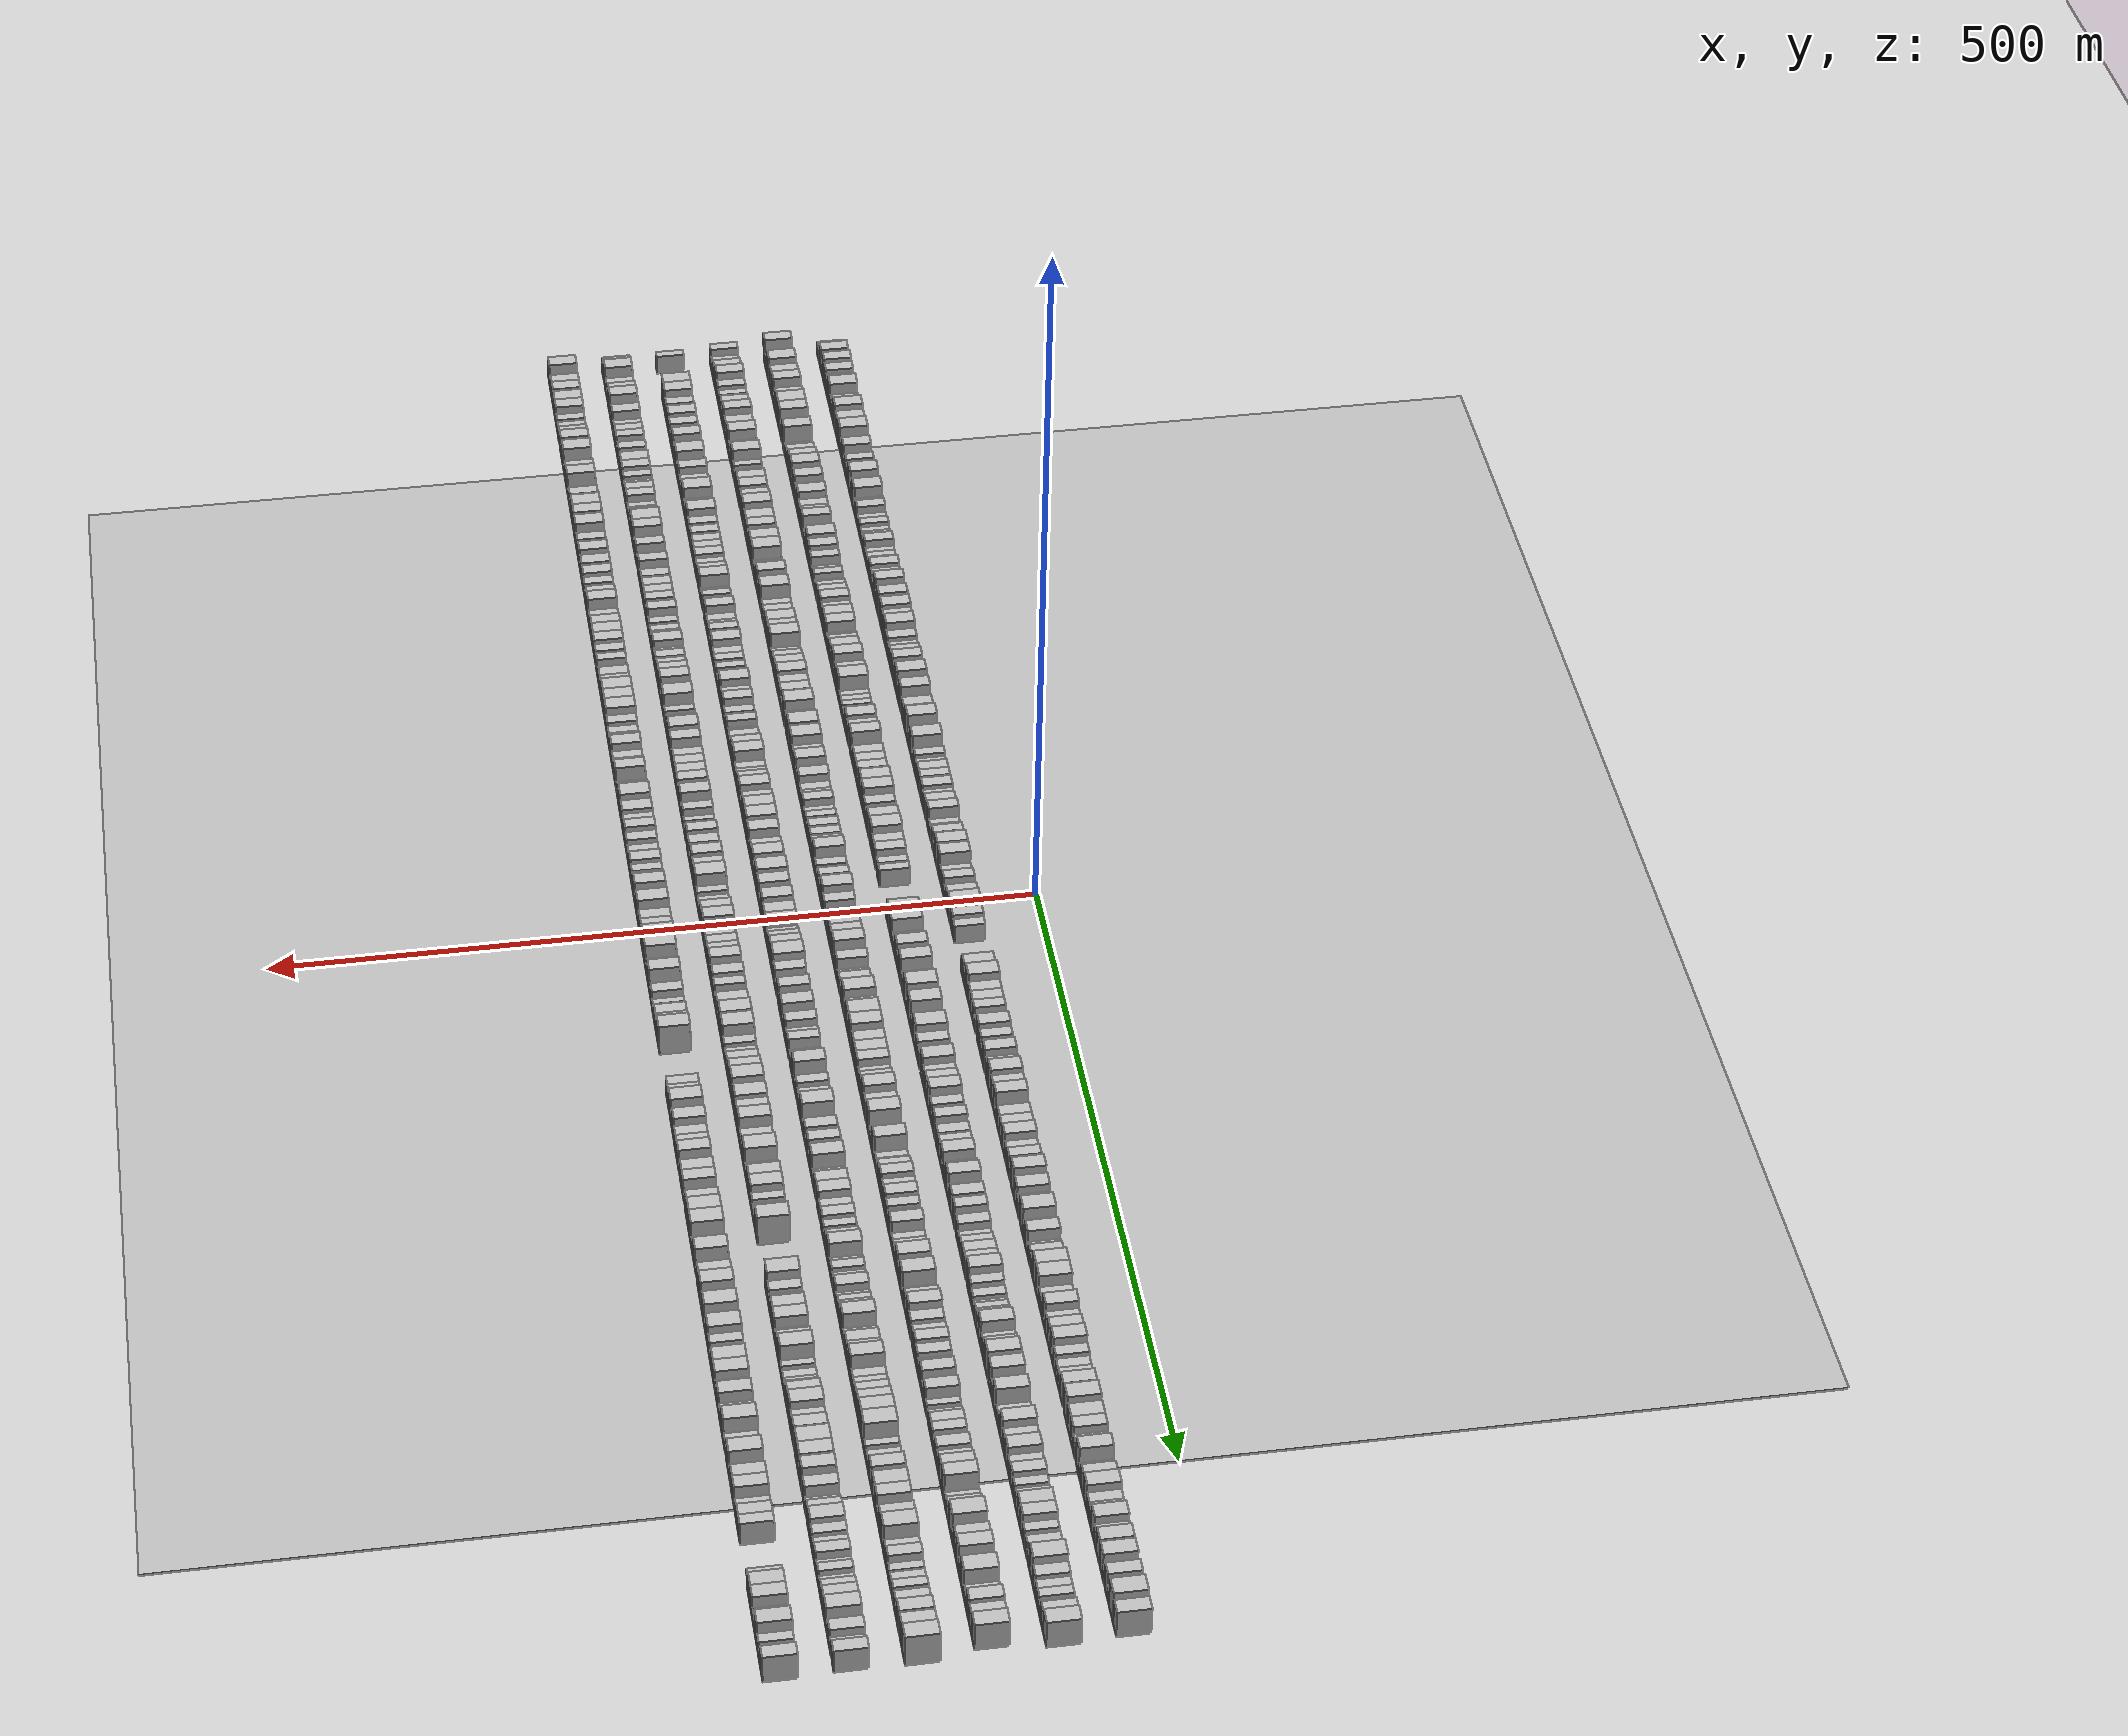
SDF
<?xml version="1.0" encoding="utf-8"?>

<sdf version="1.6">

   <world name="default">

      <gui fullscreen="0">

         <camera name="user_camera">

            <pose>-15 0 4.57585 0 0 0</pose>

            <view_controller>orbit</view_controller>

         </camera>

      </gui>

      <scene>

         <sky>

           <clouds>

             <speed>12</speed>

           </clouds>

         </sky>

         <ambient>0.4 0.4 0.4 1</ambient>

         <background>0.7 0.7 0.7 1</background>

         <shadows>1</shadows>

      </scene>

      <gravity>0 0 -9.8066</gravity>

      <magnetic_field>6e-06 2.3e-05 -4.2e-05</magnetic_field>

      <physics default="0" name="default_physics" type="ode">

         <ode>

            <solver>

               <type>quick</type>

               <iters>10</iters>

               <sor>1.0</sor>

               <use_dynamic_moi_rescaling>0</use_dynamic_moi_rescaling>

            </solver>

            <constraints>

               <cfm>0</cfm>

               <erp>0.2</erp>

               <contact_max_correcting_vel>100</contact_max_correcting_vel>

               <contact_surface_layer>0.001</contact_surface_layer>

            </constraints>

         </ode>

         <max_step_size>0.004</max_step_size>

         <real_time_factor>1</real_time_factor>

         <real_time_update_rate>250</real_time_update_rate>

      </physics>

      <light name="sun" type="directional">

         <cast_shadows>1</cast_shadows>

         <pose>0 0 10 0 0 0</pose>

         <diffuse>0.8 0.8 0.8 1</diffuse>

         <specular>0.2 0.2 0.2 1</specular>

         <attenuation>

            <range>1000</range>

            <constant>0.9</constant>

            <linear>0.01</linear>

            <quadratic>0.001</quadratic>

         </attenuation>

         <direction>-0.5 0.1 -0.9</direction>

      </light>

      <include>

         <name>ground_plane_1</name>

         <uri>model://HANNAS_ground_plane</uri>

         <pose>0 0 0  0 0 0</pose>

      </include>

      <include>

         <name>ground_plane_2</name>

         <uri>model://HANNAS_ground_plane</uri>

         <pose>100 0 0  0 0 0</pose>

      </include>

      <model name="building_1">

         <static>1</static>

         <pose frame="">50.0000 -617.2801 0 0.000000 0.000000 0.000000</pose>

         <link name="link">

            <pose frame="">0 0 6.00 0 0 0</pose>

            <collision name="collision">

               <geometry>

                  <box>

                     <size>20.0000 5.4398 12.0000</size>

                  </box>

               </geometry>

               <max_contacts>10</max_contacts>

               <surface>

                  <contact>

                     <ode/>

                  </contact>

                  <bounce/>

                  <friction>

                     <torsional>

                        <ode/>

                     </torsional>

                     <ode/>

                  </friction>

               </surface>

            </collision>

            <visual name="visual">

               <cast_shadows>0</cast_shadows>

               <geometry>

                  <box>

                     <size>20.0000 5.4398 12.0000</size>

                  </box>

               </geometry>

               <material>

                  <script>

                     <uri>model://HANNAS_wall/materials/scripts</uri>

                     <uri>model://HANNAS_wall/materials/textures</uri>

                     <name>vrc/HANNAS_wall</name>

                  </script>

               </material>

            </visual>

            <self_collide>0</self_collide>

            <enable_wind>0</enable_wind>

            <kinematic>0</kinematic>

         </link>

      </model>

      <model name="building_2">

         <static>1</static>

         <pose frame="">50.0000 -610.9079 0 0.000000 0.000000 0.000000</pose>

         <link name="link">

            <pose frame="">0 0 6.00 0 0 0</pose>

            <collision name="collision">

               <geometry>

                  <box>

                     <size>20.0000 5.3046 12.0000</size>

                  </box>

               </geometry>

               <max_contacts>10</max_contacts>

               <surface>

                  <contact>

                     <ode/>

                  </contact>

                  <bounce/>

                  <friction>

                     <torsional>

                        <ode/>

                     </torsional>

                     <ode/>

                  </friction>

               </surface>

            </collision>

            <visual name="visual">

               <cast_shadows>0</cast_shadows>

               <geometry>

                  <box>

                     <size>20.0000 5.3046 12.0000</size>

                  </box>

               </geometry>

               <material>

                  <script>

                     <uri>model://HANNAS_wall/materials/scripts</uri>

                     <uri>model://HANNAS_wall/materials/textures</uri>

                     <name>vrc/HANNAS_wall</name>

                  </script>

               </material>

            </visual>

            <self_collide>0</self_collide>

            <enable_wind>0</enable_wind>

            <kinematic>0</kinematic>

         </link>

      </model>

      <model name="building_3">

         <static>1</static>

         <pose frame="">50.0000 -601.3208 0 0.000000 0.000000 0.000000</pose>

         <link name="link">

            <pose frame="">0 0 10.50 0 0 0</pose>

            <collision name="collision">

               <geometry>

                  <box>

                     <size>20.0000 9.8697 21.0000</size>

                  </box>

               </geometry>

               <max_contacts>10</max_contacts>

               <surface>

                  <contact>

                     <ode/>

                  </contact>

                  <bounce/>

                  <friction>

                     <torsional>

                        <ode/>

                     </torsional>

                     <ode/>

                  </friction>

               </surface>

            </collision>

            <visual name="visual">

               <cast_shadows>0</cast_shadows>

               <geometry>

                  <box>

                     <size>20.0000 9.8697 21.0000</size>

                  </box>

               </geometry>

               <material>

                  <script>

                     <uri>model://HANNAS_wall/materials/scripts</uri>

                     <uri>model://HANNAS_wall/materials/textures</uri>

                     <name>vrc/HANNAS_wall</name>

                  </script>

               </material>

            </visual>

            <self_collide>0</self_collide>

            <enable_wind>0</enable_wind>

            <kinematic>0</kinematic>

         </link>

      </model>

      <model name="building_4">

         <static>1</static>

         <pose frame="">50.0000 -593.5376 0 0.000000 0.000000 0.000000</pose>

         <link name="link">

            <pose frame="">0 0 6.00 0 0 0</pose>

            <collision name="collision">

               <geometry>

                  <box>

                     <size>20.0000 5.6966 12.0000</size>

                  </box>

               </geometry>

               <max_contacts>10</max_contacts>

               <surface>

                  <contact>

                     <ode/>

                  </contact>

                  <bounce/>

                  <friction>

                     <torsional>

                        <ode/>

                     </torsional>

                     <ode/>

                  </friction>

               </surface>

            </collision>

            <visual name="visual">

               <cast_shadows>0</cast_shadows>

               <geometry>

                  <box>

                     <size>20.0000 5.6966 12.0000</size>

                  </box>

               </geometry>

               <material>

                  <script>

                     <uri>model://HANNAS_wall/materials/scripts</uri>

                     <uri>model://HANNAS_wall/materials/textures</uri>

                     <name>vrc/HANNAS_wall</name>

                  </script>

               </material>

            </visual>

            <self_collide>0</self_collide>

            <enable_wind>0</enable_wind>

            <kinematic>0</kinematic>

         </link>

      </model>

      <model name="building_5">

         <static>1</static>

         <pose frame="">50.0000 -584.8576 0 0.000000 0.000000 0.000000</pose>

         <link name="link">

            <pose frame="">0 0 12.00 0 0 0</pose>

            <collision name="collision">

               <geometry>

                  <box>

                     <size>20.0000 9.6634 24.0000</size>

                  </box>

               </geometry>

               <max_contacts>10</max_contacts>

               <surface>

                  <contact>

                     <ode/>

                  </contact>

                  <bounce/>

                  <friction>

                     <torsional>

                        <ode/>

                     </torsional>

                     <ode/>

                  </friction>

               </surface>

            </collision>

            <visual name="visual">

               <cast_shadows>0</cast_shadows>

               <geometry>

                  <box>

                     <size>20.0000 9.6634 24.0000</size>

                  </box>

               </geometry>

               <material>

                  <script>

                     <uri>model://HANNAS_wall/materials/scripts</uri>

                     <uri>model://HANNAS_wall/materials/textures</uri>

                     <name>vrc/HANNAS_wall</name>

                  </script>

               </material>

            </visual>

            <self_collide>0</self_collide>

            <enable_wind>0</enable_wind>

            <kinematic>0</kinematic>

         </link>

      </model>

      <model name="building_6">

         <static>1</static>

         <pose frame="">50.0000 -575.2569 0 0.000000 0.000000 0.000000</pose>

         <link name="link">

            <pose frame="">0 0 10.50 0 0 0</pose>

            <collision name="collision">

               <geometry>

                  <box>

                     <size>20.0000 9.5381 21.0000</size>

                  </box>

               </geometry>

               <max_contacts>10</max_contacts>

               <surface>

                  <contact>

                     <ode/>

                  </contact>

                  <bounce/>

                  <friction>

                     <torsional>

                        <ode/>

                     </torsional>

                     <ode/>

                  </friction>

               </surface>

            </collision>

            <visual name="visual">

               <cast_shadows>0</cast_shadows>

               <geometry>

                  <box>

                     <size>20.0000 9.5381 21.0000</size>

                  </box>

               </geometry>

               <material>

                  <script>

                     <uri>model://HANNAS_wall/materials/scripts</uri>

                     <uri>model://HANNAS_wall/materials/textures</uri>

                     <name>vrc/HANNAS_wall</name>

                  </script>

               </material>

            </visual>

            <self_collide>0</self_collide>

            <enable_wind>0</enable_wind>

            <kinematic>0</kinematic>

         </link>

      </model>

      <model name="building_7">

         <static>1</static>

         <pose frame="">50.0000 -566.7145 0 0.000000 0.000000 0.000000</pose>

         <link name="link">

            <pose frame="">0 0 9.00 0 0 0</pose>

            <collision name="collision">

               <geometry>

                  <box>

                     <size>20.0000 7.5467 18.0000</size>

                  </box>

               </geometry>

               <max_contacts>10</max_contacts>

               <surface>

                  <contact>

                     <ode/>

                  </contact>

                  <bounce/>

                  <friction>

                     <torsional>

                        <ode/>

                     </torsional>

                     <ode/>

                  </friction>

               </surface>

            </collision>

            <visual name="visual">

               <cast_shadows>0</cast_shadows>

               <geometry>

                  <box>

                     <size>20.0000 7.5467 18.0000</size>

                  </box>

               </geometry>

               <material>

                  <script>

                     <uri>model://HANNAS_wall/materials/scripts</uri>

                     <uri>model://HANNAS_wall/materials/textures</uri>

                     <name>vrc/HANNAS_wall</name>

                  </script>

               </material>

            </visual>

            <self_collide>0</self_collide>

            <enable_wind>0</enable_wind>

            <kinematic>0</kinematic>

         </link>

      </model>

      <model name="building_8">

         <static>1</static>

         <pose frame="">50.0000 -554.2117 0 0.000000 0.000000 0.000000</pose>

         <link name="link">

            <pose frame="">0 0 12.00 0 0 0</pose>

            <collision name="collision">

               <geometry>

                  <box>

                     <size>20.0000 11.4588 24.0000</size>

                  </box>

               </geometry>

               <max_contacts>10</max_contacts>

               <surface>

                  <contact>

                     <ode/>

                  </contact>

                  <bounce/>

                  <friction>

                     <torsional>

                        <ode/>

                     </torsional>

                     <ode/>

                  </friction>

               </surface>

            </collision>

            <visual name="visual">

               <cast_shadows>0</cast_shadows>

               <geometry>

                  <box>

                     <size>20.0000 11.4588 24.0000</size>

                  </box>

               </geometry>

               <material>

                  <script>

                     <uri>model://HANNAS_wall/materials/scripts</uri>

                     <uri>model://HANNAS_wall/materials/textures</uri>

                     <name>vrc/HANNAS_wall</name>

                  </script>

               </material>

            </visual>

            <self_collide>0</self_collide>

            <enable_wind>0</enable_wind>

            <kinematic>0</kinematic>

         </link>

      </model>

      <model name="building_9">

         <static>1</static>

         <pose frame="">50.0000 -545.2420 0 0.000000 0.000000 0.000000</pose>

         <link name="link">

            <pose frame="">0 0 7.50 0 0 0</pose>

            <collision name="collision">

               <geometry>

                  <box>

                     <size>20.0000 6.4806 15.0000</size>

                  </box>

               </geometry>

               <max_contacts>10</max_contacts>

               <surface>

                  <contact>

                     <ode/>

                  </contact>

                  <bounce/>

                  <friction>

                     <torsional>

                        <ode/>

                     </torsional>

                     <ode/>

                  </friction>

               </surface>

            </collision>

            <visual name="visual">

               <cast_shadows>0</cast_shadows>

               <geometry>

                  <box>

                     <size>20.0000 6.4806 15.0000</size>

                  </box>

               </geometry>

               <material>

                  <script>

                     <uri>model://HANNAS_wall/materials/scripts</uri>

                     <uri>model://HANNAS_wall/materials/textures</uri>

                     <name>vrc/HANNAS_wall</name>

                  </script>

               </material>

            </visual>

            <self_collide>0</self_collide>

            <enable_wind>0</enable_wind>

            <kinematic>0</kinematic>

         </link>

      </model>

      <model name="building_10">

         <static>1</static>

         <pose frame="">50.0000 -536.4293 0 0.000000 0.000000 0.000000</pose>

         <link name="link">

            <pose frame="">0 0 7.50 0 0 0</pose>

            <collision name="collision">

               <geometry>

                  <box>

                     <size>20.0000 7.1450 15.0000</size>

                  </box>

               </geometry>

               <max_contacts>10</max_contacts>

               <surface>

                  <contact>

                     <ode/>

                  </contact>

                  <bounce/>

                  <friction>

                     <torsional>

                        <ode/>

                     </torsional>

                     <ode/>

                  </friction>

               </surface>

            </collision>

            <visual name="visual">

               <cast_shadows>0</cast_shadows>

               <geometry>

                  <box>

                     <size>20.0000 7.1450 15.0000</size>

                  </box>

               </geometry>

               <material>

                  <script>

                     <uri>model://HANNAS_wall/materials/scripts</uri>

                     <uri>model://HANNAS_wall/materials/textures</uri>

                     <name>vrc/HANNAS_wall</name>

                  </script>

               </material>

            </visual>

            <self_collide>0</self_collide>

            <enable_wind>0</enable_wind>

            <kinematic>0</kinematic>

         </link>

      </model>

      <model name="building_11">

         <static>1</static>

         <pose frame="">50.0000 -527.5019 0 0.000000 0.000000 0.000000</pose>

         <link name="link">

            <pose frame="">0 0 12.00 0 0 0</pose>

            <collision name="collision">

               <geometry>

                  <box>

                     <size>20.0000 10.7098 24.0000</size>

                  </box>

               </geometry>

               <max_contacts>10</max_contacts>

               <surface>

                  <contact>

                     <ode/>

                  </contact>

                  <bounce/>

                  <friction>

                     <torsional>

                        <ode/>

                     </torsional>

                     <ode/>

                  </friction>

               </surface>

            </collision>

            <visual name="visual">

               <cast_shadows>0</cast_shadows>

               <geometry>

                  <box>

                     <size>20.0000 10.7098 24.0000</size>

                  </box>

               </geometry>

               <material>

                  <script>

                     <uri>model://HANNAS_wall/materials/scripts</uri>

                     <uri>model://HANNAS_wall/materials/textures</uri>

                     <name>vrc/HANNAS_wall</name>

                  </script>

               </material>

            </visual>

            <self_collide>0</self_collide>

            <enable_wind>0</enable_wind>

            <kinematic>0</kinematic>

         </link>

      </model>

      <model name="building_12">

         <static>1</static>

         <pose frame="">50.0000 -514.9987 0 0.000000 0.000000 0.000000</pose>

         <link name="link">

            <pose frame="">0 0 10.50 0 0 0</pose>

            <collision name="collision">

               <geometry>

                  <box>

                     <size>20.0000 10.2964 21.0000</size>

                  </box>

               </geometry>

               <max_contacts>10</max_contacts>

               <surface>

                  <contact>

                     <ode/>

                  </contact>

                  <bounce/>

                  <friction>

                     <torsional>

                        <ode/>

                     </torsional>

                     <ode/>

                  </friction>

               </surface>

            </collision>

            <visual name="visual">

               <cast_shadows>0</cast_shadows>

               <geometry>

                  <box>

                     <size>20.0000 10.2964 21.0000</size>

                  </box>

               </geometry>

               <material>

                  <script>

                     <uri>model://HANNAS_wall/materials/scripts</uri>

                     <uri>model://HANNAS_wall/materials/textures</uri>

                     <name>vrc/HANNAS_wall</name>

                  </script>

               </material>

            </visual>

            <self_collide>0</self_collide>

            <enable_wind>0</enable_wind>

            <kinematic>0</kinematic>

         </link>

      </model>

      <model name="building_13">

         <static>1</static>

         <pose frame="">50.0000 -500.9889 0 0.000000 0.000000 0.000000</pose>

         <link name="link">

            <pose frame="">0 0 12.00 0 0 0</pose>

            <collision name="collision">

               <geometry>

                  <box>

                     <size>20.0000 11.7233 24.0000</size>

                  </box>

               </geometry>

               <max_contacts>10</max_contacts>

               <surface>

                  <contact>

                     <ode/>

                  </contact>

                  <bounce/>

                  <friction>

                     <torsional>

                        <ode/>

                     </torsional>

                     <ode/>

                  </friction>

               </surface>

            </collision>

            <visual name="visual">

               <cast_shadows>0</cast_shadows>

               <geometry>

                  <box>

                     <size>20.0000 11.7233 24.0000</size>

                  </box>

               </geometry>

               <material>

                  <script>

                     <uri>model://HANNAS_wall/materials/scripts</uri>

                     <uri>model://HANNAS_wall/materials/textures</uri>

                     <name>vrc/HANNAS_wall</name>

                  </script>

               </material>

            </visual>

            <self_collide>0</self_collide>

            <enable_wind>0</enable_wind>

            <kinematic>0</kinematic>

         </link>

      </model>

      <model name="building_14">

         <static>1</static>

         <pose frame="">50.0000 -491.3945 0 0.000000 0.000000 0.000000</pose>

         <link name="link">

            <pose frame="">0 0 7.50 0 0 0</pose>

            <collision name="collision">

               <geometry>

                  <box>

                     <size>20.0000 7.4656 15.0000</size>

                  </box>

               </geometry>

               <max_contacts>10</max_contacts>

               <surface>

                  <contact>

                     <ode/>

                  </contact>

                  <bounce/>

                  <friction>

                     <torsional>

                        <ode/>

                     </torsional>

                     <ode/>

                  </friction>

               </surface>

            </collision>

            <visual name="visual">

               <cast_shadows>0</cast_shadows>

               <geometry>

                  <box>

                     <size>20.0000 7.4656 15.0000</size>

                  </box>

               </geometry>

               <material>

                  <script>

                     <uri>model://HANNAS_wall/materials/scripts</uri>

                     <uri>model://HANNAS_wall/materials/textures</uri>

                     <name>vrc/HANNAS_wall</name>

                  </script>

               </material>

            </visual>

            <self_collide>0</self_collide>

            <enable_wind>0</enable_wind>

            <kinematic>0</kinematic>

         </link>

      </model>

      <model name="building_15">

         <static>1</static>

         <pose frame="">50.0000 -482.5791 0 0.000000 0.000000 0.000000</pose>

         <link name="link">

            <pose frame="">0 0 10.50 0 0 0</pose>

            <collision name="collision">

               <geometry>

                  <box>

                     <size>20.0000 10.1651 21.0000</size>

                  </box>

               </geometry>

               <max_contacts>10</max_contacts>

               <surface>

                  <contact>

                     <ode/>

                  </contact>

                  <bounce/>

                  <friction>

                     <torsional>

                        <ode/>

                     </torsional>

                     <ode/>

                  </friction>

               </surface>

            </collision>

            <visual name="visual">

               <cast_shadows>0</cast_shadows>

               <geometry>

                  <box>

                     <size>20.0000 10.1651 21.0000</size>

                  </box>

               </geometry>

               <material>

                  <script>

                     <uri>model://HANNAS_wall/materials/scripts</uri>

                     <uri>model://HANNAS_wall/materials/textures</uri>

                     <name>vrc/HANNAS_wall</name>

                  </script>

               </material>

            </visual>

            <self_collide>0</self_collide>

            <enable_wind>0</enable_wind>

            <kinematic>0</kinematic>

         </link>

      </model>

      <model name="building_16">

         <static>1</static>

         <pose frame="">50.0000 -474.5978 0 0.000000 0.000000 0.000000</pose>

         <link name="link">

            <pose frame="">0 0 6.00 0 0 0</pose>

            <collision name="collision">

               <geometry>

                  <box>

                     <size>20.0000 5.7976 12.0000</size>

                  </box>

               </geometry>

               <max_contacts>10</max_contacts>

               <surface>

                  <contact>

                     <ode/>

                  </contact>

                  <bounce/>

                  <friction>

                     <torsional>

                        <ode/>

                     </torsional>

                     <ode/>

                  </friction>

               </surface>

            </collision>

            <visual name="visual">

               <cast_shadows>0</cast_shadows>

               <geometry>

                  <box>

                     <size>20.0000 5.7976 12.0000</size>

                  </box>

               </geometry>

               <material>

                  <script>

                     <uri>model://HANNAS_wall/materials/scripts</uri>

                     <uri>model://HANNAS_wall/materials/textures</uri>

                     <name>vrc/HANNAS_wall</name>

                  </script>

               </material>

            </visual>

            <self_collide>0</self_collide>

            <enable_wind>0</enable_wind>

            <kinematic>0</kinematic>

         </link>

      </model>

      <model name="building_17">

         <static>1</static>

         <pose frame="">50.0000 -467.9773 0 0.000000 0.000000 0.000000</pose>

         <link name="link">

            <pose frame="">0 0 9.00 0 0 0</pose>

            <collision name="collision">

               <geometry>

                  <box>

                     <size>20.0000 7.4434 18.0000</size>

                  </box>

               </geometry>

               <max_contacts>10</max_contacts>

               <surface>

                  <contact>

                     <ode/>

                  </contact>

                  <bounce/>

                  <friction>

                     <torsional>

                        <ode/>

                     </torsional>

                     <ode/>

                  </friction>

               </surface>

            </collision>

            <visual name="visual">

               <cast_shadows>0</cast_shadows>

               <geometry>

                  <box>

                     <size>20.0000 7.4434 18.0000</size>

                  </box>

               </geometry>

               <material>

                  <script>

                     <uri>model://HANNAS_wall/materials/scripts</uri>

                     <uri>model://HANNAS_wall/materials/textures</uri>

                     <name>vrc/HANNAS_wall</name>

                  </script>

               </material>

            </visual>

            <self_collide>0</self_collide>

            <enable_wind>0</enable_wind>

            <kinematic>0</kinematic>

         </link>

      </model>

      <model name="building_18">

         <static>1</static>

         <pose frame="">50.0000 -460.5106 0 0.000000 0.000000 0.000000</pose>

         <link name="link">

            <pose frame="">0 0 7.50 0 0 0</pose>

            <collision name="collision">

               <geometry>

                  <box>

                     <size>20.0000 7.4900 15.0000</size>

                  </box>

               </geometry>

               <max_contacts>10</max_contacts>

               <surface>

                  <contact>

                     <ode/>

                  </contact>

                  <bounce/>

                  <friction>

                     <torsional>

                        <ode/>

                     </torsional>

                     <ode/>

                  </friction>

               </surface>

            </collision>

            <visual name="visual">

               <cast_shadows>0</cast_shadows>

               <geometry>

                  <box>

                     <size>20.0000 7.4900 15.0000</size>

                  </box>

               </geometry>

               <material>

                  <script>

                     <uri>model://HANNAS_wall/materials/scripts</uri>

                     <uri>model://HANNAS_wall/materials/textures</uri>

                     <name>vrc/HANNAS_wall</name>

                  </script>

               </material>

            </visual>

            <self_collide>0</self_collide>

            <enable_wind>0</enable_wind>

            <kinematic>0</kinematic>

         </link>

      </model>

      <model name="building_19">

         <static>1</static>

         <pose frame="">50.0000 -448.0010 0 0.000000 0.000000 0.000000</pose>

         <link name="link">

            <pose frame="">0 0 12.00 0 0 0</pose>

            <collision name="collision">

               <geometry>

                  <box>

                     <size>20.0000 11.5291 24.0000</size>

                  </box>

               </geometry>

               <max_contacts>10</max_contacts>

               <surface>

                  <contact>

                     <ode/>

                  </contact>

                  <bounce/>

                  <friction>

                     <torsional>

                        <ode/>

                     </torsional>

                     <ode/>

                  </friction>

               </surface>

            </collision>

            <visual name="visual">

               <cast_shadows>0</cast_shadows>

               <geometry>

                  <box>

                     <size>20.0000 11.5291 24.0000</size>

                  </box>

               </geometry>

               <material>

                  <script>

                     <uri>model://HANNAS_wall/materials/scripts</uri>

                     <uri>model://HANNAS_wall/materials/textures</uri>

                     <name>vrc/HANNAS_wall</name>

                  </script>

               </material>

            </visual>

            <self_collide>0</self_collide>

            <enable_wind>0</enable_wind>

            <kinematic>0</kinematic>

         </link>

      </model>

      <model name="building_20">

         <static>1</static>

         <pose frame="">50.0000 -438.1057 0 0.000000 0.000000 0.000000</pose>

         <link name="link">

            <pose frame="">0 0 9.00 0 0 0</pose>

            <collision name="collision">

               <geometry>

                  <box>

                     <size>20.0000 8.2616 18.0000</size>

                  </box>

               </geometry>

               <max_contacts>10</max_contacts>

               <surface>

                  <contact>

                     <ode/>

                  </contact>

                  <bounce/>

                  <friction>

                     <torsional>

                        <ode/>

                     </torsional>

                     <ode/>

                  </friction>

               </surface>

            </collision>

            <visual name="visual">

               <cast_shadows>0</cast_shadows>

               <geometry>

                  <box>

                     <size>20.0000 8.2616 18.0000</size>

                  </box>

               </geometry>

               <material>

                  <script>

                     <uri>model://HANNAS_wall/materials/scripts</uri>

                     <uri>model://HANNAS_wall/materials/textures</uri>

                     <name>vrc/HANNAS_wall</name>

                  </script>

               </material>

            </visual>

            <self_collide>0</self_collide>

            <enable_wind>0</enable_wind>

            <kinematic>0</kinematic>

         </link>

      </model>

      <model name="building_21">

         <static>1</static>

         <pose frame="">50.0000 -428.0708 0 0.000000 0.000000 0.000000</pose>

         <link name="link">

            <pose frame="">0 0 12.00 0 0 0</pose>

            <collision name="collision">

               <geometry>

                  <box>

                     <size>20.0000 11.8082 24.0000</size>

                  </box>

               </geometry>

               <max_contacts>10</max_contacts>

               <surface>

                  <contact>

                     <ode/>

                  </contact>

                  <bounce/>

                  <friction>

                     <torsional>

                        <ode/>

                     </torsional>

                     <ode/>

                  </friction>

               </surface>

            </collision>

            <visual name="visual">

               <cast_shadows>0</cast_shadows>

               <geometry>

                  <box>

                     <size>20.0000 11.8082 24.0000</size>

                  </box>

               </geometry>

               <material>

                  <script>

                     <uri>model://HANNAS_wall/materials/scripts</uri>

                     <uri>model://HANNAS_wall/materials/textures</uri>

                     <name>vrc/HANNAS_wall</name>

                  </script>

               </material>

            </visual>

            <self_collide>0</self_collide>

            <enable_wind>0</enable_wind>

            <kinematic>0</kinematic>

         </link>

      </model>

      <model name="building_22">

         <static>1</static>

         <pose frame="">50.0000 -419.0965 0 0.000000 0.000000 0.000000</pose>

         <link name="link">

            <pose frame="">0 0 7.50 0 0 0</pose>

            <collision name="collision">

               <geometry>

                  <box>

                     <size>20.0000 6.1403 15.0000</size>

                  </box>

               </geometry>

               <max_contacts>10</max_contacts>

               <surface>

                  <contact>

                     <ode/>

                  </contact>

                  <bounce/>

                  <friction>

                     <torsional>

                        <ode/>

                     </torsional>

                     <ode/>

                  </friction>

               </surface>

            </collision>

            <visual name="visual">

               <cast_shadows>0</cast_shadows>

               <geometry>

                  <box>

                     <size>20.0000 6.1403 15.0000</size>

                  </box>

               </geometry>

               <material>

                  <script>

                     <uri>model://HANNAS_wall/materials/scripts</uri>

                     <uri>model://HANNAS_wall/materials/textures</uri>

                     <name>vrc/HANNAS_wall</name>

                  </script>

               </material>

            </visual>

            <self_collide>0</self_collide>

            <enable_wind>0</enable_wind>

            <kinematic>0</kinematic>

         </link>

      </model>

      <model name="building_23">

         <static>1</static>

         <pose frame="">50.0000 -411.7634 0 0.000000 0.000000 0.000000</pose>

         <link name="link">

            <pose frame="">0 0 9.00 0 0 0</pose>

            <collision name="collision">

               <geometry>

                  <box>

                     <size>20.0000 8.5258 18.0000</size>

                  </box>

               </geometry>

               <max_contacts>10</max_contacts>

               <surface>

                  <contact>

                     <ode/>

                  </contact>

                  <bounce/>

                  <friction>

                     <torsional>

                        <ode/>

                     </torsional>

                     <ode/>

                  </friction>

               </surface>

            </collision>

            <visual name="visual">

               <cast_shadows>0</cast_shadows>

               <geometry>

                  <box>

                     <size>20.0000 8.5258 18.0000</size>

                  </box>

               </geometry>

               <material>

                  <script>

                     <uri>model://HANNAS_wall/materials/scripts</uri>

                     <uri>model://HANNAS_wall/materials/textures</uri>

                     <name>vrc/HANNAS_wall</name>

                  </script>

               </material>

            </visual>

            <self_collide>0</self_collide>

            <enable_wind>0</enable_wind>

            <kinematic>0</kinematic>

         </link>

      </model>

      <model name="building_24">

         <static>1</static>

         <pose frame="">50.0000 -404.6001 0 0.000000 0.000000 0.000000</pose>

         <link name="link">

            <pose frame="">0 0 6.00 0 0 0</pose>

            <collision name="collision">

               <geometry>

                  <box>

                     <size>20.0000 5.8009 12.0000</size>

                  </box>

               </geometry>

               <max_contacts>10</max_contacts>

               <surface>

                  <contact>

                     <ode/>

                  </contact>

                  <bounce/>

                  <friction>

                     <torsional>

                        <ode/>

                     </torsional>

                     <ode/>

                  </friction>

               </surface>

            </collision>

            <visual name="visual">

               <cast_shadows>0</cast_shadows>

               <geometry>

                  <box>

                     <size>20.0000 5.8009 12.0000</size>

                  </box>

               </geometry>

               <material>

                  <script>

                     <uri>model://HANNAS_wall/materials/scripts</uri>

                     <uri>model://HANNAS_wall/materials/textures</uri>

                     <name>vrc/HANNAS_wall</name>

                  </script>

               </material>

            </visual>

            <self_collide>0</self_collide>

            <enable_wind>0</enable_wind>

            <kinematic>0</kinematic>

         </link>

      </model>

      <model name="building_25">

         <static>1</static>

         <pose frame="">50.0000 -395.3287 0 0.000000 0.000000 0.000000</pose>

         <link name="link">

            <pose frame="">0 0 7.50 0 0 0</pose>

            <collision name="collision">

               <geometry>

                  <box>

                     <size>20.0000 6.7418 15.0000</size>

                  </box>

               </geometry>

               <max_contacts>10</max_contacts>

               <surface>

                  <contact>

                     <ode/>

                  </contact>

                  <bounce/>

                  <friction>

                     <torsional>

                        <ode/>

                     </torsional>

                     <ode/>

                  </friction>

               </surface>

            </collision>

            <visual name="visual">

               <cast_shadows>0</cast_shadows>

               <geometry>

                  <box>

                     <size>20.0000 6.7418 15.0000</size>

                  </box>

               </geometry>

               <material>

                  <script>

                     <uri>model://HANNAS_wall/materials/scripts</uri>

                     <uri>model://HANNAS_wall/materials/textures</uri>

                     <name>vrc/HANNAS_wall</name>

                  </script>

               </material>

            </visual>

            <self_collide>0</self_collide>

            <enable_wind>0</enable_wind>

            <kinematic>0</kinematic>

         </link>

      </model>

      <model name="building_26">

         <static>1</static>

         <pose frame="">50.0000 -389.5007 0 0.000000 0.000000 0.000000</pose>

         <link name="link">

            <pose frame="">0 0 6.00 0 0 0</pose>

            <collision name="collision">

               <geometry>

                  <box>

                     <size>20.0000 4.9143 12.0000</size>

                  </box>

               </geometry>

               <max_contacts>10</max_contacts>

               <surface>

                  <contact>

                     <ode/>

                  </contact>

                  <bounce/>

                  <friction>

                     <torsional>

                        <ode/>

                     </torsional>

                     <ode/>

                  </friction>

               </surface>

            </collision>

            <visual name="visual">

               <cast_shadows>0</cast_shadows>

               <geometry>

                  <box>

                     <size>20.0000 4.9143 12.0000</size>

                  </box>

               </geometry>

               <material>

                  <script>

                     <uri>model://HANNAS_wall/materials/scripts</uri>

                     <uri>model://HANNAS_wall/materials/textures</uri>

                     <name>vrc/HANNAS_wall</name>

                  </script>

               </material>

            </visual>

            <self_collide>0</self_collide>

            <enable_wind>0</enable_wind>

            <kinematic>0</kinematic>

         </link>

      </model>

      <model name="building_27">

         <static>1</static>

         <pose frame="">50.0000 -384.4664 0 0.000000 0.000000 0.000000</pose>

         <link name="link">

            <pose frame="">0 0 6.00 0 0 0</pose>

            <collision name="collision">

               <geometry>

                  <box>

                     <size>20.0000 5.1542 12.0000</size>

                  </box>

               </geometry>

               <max_contacts>10</max_contacts>

               <surface>

                  <contact>

                     <ode/>

                  </contact>

                  <bounce/>

                  <friction>

                     <torsional>

                        <ode/>

                     </torsional>

                     <ode/>

                  </friction>

               </surface>

            </collision>

            <visual name="visual">

               <cast_shadows>0</cast_shadows>

               <geometry>

                  <box>

                     <size>20.0000 5.1542 12.0000</size>

                  </box>

               </geometry>

               <material>

                  <script>

                     <uri>model://HANNAS_wall/materials/scripts</uri>

                     <uri>model://HANNAS_wall/materials/textures</uri>

                     <name>vrc/HANNAS_wall</name>

                  </script>

               </material>

            </visual>

            <self_collide>0</self_collide>

            <enable_wind>0</enable_wind>

            <kinematic>0</kinematic>

         </link>

      </model>

      <model name="building_28">

         <static>1</static>

         <pose frame="">50.0000 -379.3581 0 0.000000 0.000000 0.000000</pose>

         <link name="link">

            <pose frame="">0 0 6.00 0 0 0</pose>

            <collision name="collision">

               <geometry>

                  <box>

                     <size>20.0000 5.0624 12.0000</size>

                  </box>

               </geometry>

               <max_contacts>10</max_contacts>

               <surface>

                  <contact>

                     <ode/>

                  </contact>

                  <bounce/>

                  <friction>

                     <torsional>

                        <ode/>

                     </torsional>

                     <ode/>

                  </friction>

               </surface>

            </collision>

            <visual name="visual">

               <cast_shadows>0</cast_shadows>

               <geometry>

                  <box>

                     <size>20.0000 5.0624 12.0000</size>

                  </box>

               </geometry>

               <material>

                  <script>

                     <uri>model://HANNAS_wall/materials/scripts</uri>

                     <uri>model://HANNAS_wall/materials/textures</uri>

                     <name>vrc/HANNAS_wall</name>

                  </script>

               </material>

            </visual>

            <self_collide>0</self_collide>

            <enable_wind>0</enable_wind>

            <kinematic>0</kinematic>

         </link>

      </model>

      <model name="building_29">

         <static>1</static>

         <pose frame="">50.0000 -372.3930 0 0.000000 0.000000 0.000000</pose>

         <link name="link">

            <pose frame="">0 0 9.00 0 0 0</pose>

            <collision name="collision">

               <geometry>

                  <box>

                     <size>20.0000 8.8679 18.0000</size>

                  </box>

               </geometry>

               <max_contacts>10</max_contacts>

               <surface>

                  <contact>

                     <ode/>

                  </contact>

                  <bounce/>

                  <friction>

                     <torsional>

                        <ode/>

                     </torsional>

                     <ode/>

                  </friction>

               </surface>

            </collision>

            <visual name="visual">

               <cast_shadows>0</cast_shadows>

               <geometry>

                  <box>

                     <size>20.0000 8.8679 18.0000</size>

                  </box>

               </geometry>

               <material>

                  <script>

                     <uri>model://HANNAS_wall/materials/scripts</uri>

                     <uri>model://HANNAS_wall/materials/textures</uri>

                     <name>vrc/HANNAS_wall</name>

                  </script>

               </material>

            </visual>

            <self_collide>0</self_collide>

            <enable_wind>0</enable_wind>

            <kinematic>0</kinematic>

         </link>

      </model>

      <model name="building_30">

         <static>1</static>

         <pose frame="">50.0000 -365.5068 0 0.000000 0.000000 0.000000</pose>

         <link name="link">

            <pose frame="">0 0 6.00 0 0 0</pose>

            <collision name="collision">

               <geometry>

                  <box>

                     <size>20.0000 4.9045 12.0000</size>

                  </box>

               </geometry>

               <max_contacts>10</max_contacts>

               <surface>

                  <contact>

                     <ode/>

                  </contact>

                  <bounce/>

                  <friction>

                     <torsional>

                        <ode/>

                     </torsional>

                     <ode/>

                  </friction>

               </surface>

            </collision>

            <visual name="visual">

               <cast_shadows>0</cast_shadows>

               <geometry>

                  <box>

                     <size>20.0000 4.9045 12.0000</size>

                  </box>

               </geometry>

               <material>

                  <script>

                     <uri>model://HANNAS_wall/materials/scripts</uri>

                     <uri>model://HANNAS_wall/materials/textures</uri>

                     <name>vrc/HANNAS_wall</name>

                  </script>

               </material>

            </visual>

            <self_collide>0</self_collide>

            <enable_wind>0</enable_wind>

            <kinematic>0</kinematic>

         </link>

      </model>

      <model name="building_31">

         <static>1</static>

         <pose frame="">50.0000 -360.3076 0 0.000000 0.000000 0.000000</pose>

         <link name="link">

            <pose frame="">0 0 6.00 0 0 0</pose>

            <collision name="collision">

               <geometry>

                  <box>

                     <size>20.0000 5.4939 12.0000</size>

                  </box>

               </geometry>

               <max_contacts>10</max_contacts>

               <surface>

                  <contact>

                     <ode/>

                  </contact>

                  <bounce/>

                  <friction>

                     <torsional>

                        <ode/>

                     </torsional>

                     <ode/>

                  </friction>

               </surface>

            </collision>

            <visual name="visual">

               <cast_shadows>0</cast_shadows>

               <geometry>

                  <box>

                     <size>20.0000 5.4939 12.0000</size>

                  </box>

               </geometry>

               <material>

                  <script>

                     <uri>model://HANNAS_wall/materials/scripts</uri>

                     <uri>model://HANNAS_wall/materials/textures</uri>

                     <name>vrc/HANNAS_wall</name>

                  </script>

               </material>

            </visual>

            <self_collide>0</self_collide>

            <enable_wind>0</enable_wind>

            <kinematic>0</kinematic>

         </link>

      </model>

      <model name="building_32">

         <static>1</static>

         <pose frame="">50.0000 -354.8880 0 0.000000 0.000000 0.000000</pose>

         <link name="link">

            <pose frame="">0 0 6.00 0 0 0</pose>

            <collision name="collision">

               <geometry>

                  <box>

                     <size>20.0000 5.3453 12.0000</size>

                  </box>

               </geometry>

               <max_contacts>10</max_contacts>

               <surface>

                  <contact>

                     <ode/>

                  </contact>

                  <bounce/>

                  <friction>

                     <torsional>

                        <ode/>

                     </torsional>

                     <ode/>

                  </friction>

               </surface>

            </collision>

            <visual name="visual">

               <cast_shadows>0</cast_shadows>

               <geometry>

                  <box>

                     <size>20.0000 5.3453 12.0000</size>

                  </box>

               </geometry>

               <material>

                  <script>

                     <uri>model://HANNAS_wall/materials/scripts</uri>

                     <uri>model://HANNAS_wall/materials/textures</uri>

                     <name>vrc/HANNAS_wall</name>

                  </script>

               </material>

            </visual>

            <self_collide>0</self_collide>

            <enable_wind>0</enable_wind>

            <kinematic>0</kinematic>

         </link>

      </model>

      <model name="building_33">

         <static>1</static>

         <pose frame="">50.0000 -344.8175 0 0.000000 0.000000 0.000000</pose>

         <link name="link">

            <pose frame="">0 0 9.00 0 0 0</pose>

            <collision name="collision">

               <geometry>

                  <box>

                     <size>20.0000 8.7959 18.0000</size>

                  </box>

               </geometry>

               <max_contacts>10</max_contacts>

               <surface>

                  <contact>

                     <ode/>

                  </contact>

                  <bounce/>

                  <friction>

                     <torsional>

                        <ode/>

                     </torsional>

                     <ode/>

                  </friction>

               </surface>

            </collision>

            <visual name="visual">

               <cast_shadows>0</cast_shadows>

               <geometry>

                  <box>

                     <size>20.0000 8.7959 18.0000</size>

                  </box>

               </geometry>

               <material>

                  <script>

                     <uri>model://HANNAS_wall/materials/scripts</uri>

                     <uri>model://HANNAS_wall/materials/textures</uri>

                     <name>vrc/HANNAS_wall</name>

                  </script>

               </material>

            </visual>

            <self_collide>0</self_collide>

            <enable_wind>0</enable_wind>

            <kinematic>0</kinematic>

         </link>

      </model>

      <model name="building_34">

         <static>1</static>

         <pose frame="">50.0000 -336.6753 0 0.000000 0.000000 0.000000</pose>

         <link name="link">

            <pose frame="">0 0 7.50 0 0 0</pose>

            <collision name="collision">

               <geometry>

                  <box>

                     <size>20.0000 7.4885 15.0000</size>

                  </box>

               </geometry>

               <max_contacts>10</max_contacts>

               <surface>

                  <contact>

                     <ode/>

                  </contact>

                  <bounce/>

                  <friction>

                     <torsional>

                        <ode/>

                     </torsional>

                     <ode/>

                  </friction>

               </surface>

            </collision>

            <visual name="visual">

               <cast_shadows>0</cast_shadows>

               <geometry>

                  <box>

                     <size>20.0000 7.4885 15.0000</size>

                  </box>

               </geometry>

               <material>

                  <script>

                     <uri>model://HANNAS_wall/materials/scripts</uri>

                     <uri>model://HANNAS_wall/materials/textures</uri>

                     <name>vrc/HANNAS_wall</name>

                  </script>

               </material>

            </visual>

            <self_collide>0</self_collide>

            <enable_wind>0</enable_wind>

            <kinematic>0</kinematic>

         </link>

      </model>

      <model name="building_35">

         <static>1</static>

         <pose frame="">50.0000 -330.3039 0 0.000000 0.000000 0.000000</pose>

         <link name="link">

            <pose frame="">0 0 6.00 0 0 0</pose>

            <collision name="collision">

               <geometry>

                  <box>

                     <size>20.0000 5.2542 12.0000</size>

                  </box>

               </geometry>

               <max_contacts>10</max_contacts>

               <surface>

                  <contact>

                     <ode/>

                  </contact>

                  <bounce/>

                  <friction>

                     <torsional>

                        <ode/>

                     </torsional>

                     <ode/>

                  </friction>

               </surface>

            </collision>

            <visual name="visual">

               <cast_shadows>0</cast_shadows>

               <geometry>

                  <box>

                     <size>20.0000 5.2542 12.0000</size>

                  </box>

               </geometry>

               <material>

                  <script>

                     <uri>model://HANNAS_wall/materials/scripts</uri>

                     <uri>model://HANNAS_wall/materials/textures</uri>

                     <name>vrc/HANNAS_wall</name>

                  </script>

               </material>

            </visual>

            <self_collide>0</self_collide>

            <enable_wind>0</enable_wind>

            <kinematic>0</kinematic>

         </link>

      </model>

      <model name="building_36">

         <static>1</static>

         <pose frame="">50.0000 -320.8664 0 0.000000 0.000000 0.000000</pose>

         <link name="link">

            <pose frame="">0 0 12.00 0 0 0</pose>

            <collision name="collision">

               <geometry>

                  <box>

                     <size>20.0000 9.6209 24.0000</size>

                  </box>

               </geometry>

               <max_contacts>10</max_contacts>

               <surface>

                  <contact>

                     <ode/>

                  </contact>

                  <bounce/>

                  <friction>

                     <torsional>

                        <ode/>

                     </torsional>

                     <ode/>

                  </friction>

               </surface>

            </collision>

            <visual name="visual">

               <cast_shadows>0</cast_shadows>

               <geometry>

                  <box>

                     <size>20.0000 9.6209 24.0000</size>

                  </box>

               </geometry>

               <material>

                  <script>

                     <uri>model://HANNAS_wall/materials/scripts</uri>

                     <uri>model://HANNAS_wall/materials/textures</uri>

                     <name>vrc/HANNAS_wall</name>

                  </script>

               </material>

            </visual>

            <self_collide>0</self_collide>

            <enable_wind>0</enable_wind>

            <kinematic>0</kinematic>

         </link>

      </model>

      <model name="building_37">

         <static>1</static>

         <pose frame="">50.0000 -312.6414 0 0.000000 0.000000 0.000000</pose>

         <link name="link">

            <pose frame="">0 0 7.50 0 0 0</pose>

            <collision name="collision">

               <geometry>

                  <box>

                     <size>20.0000 6.8291 15.0000</size>

                  </box>

               </geometry>

               <max_contacts>10</max_contacts>

               <surface>

                  <contact>

                     <ode/>

                  </contact>

                  <bounce/>

                  <friction>

                     <torsional>

                        <ode/>

                     </torsional>

                     <ode/>

                  </friction>

               </surface>

            </collision>

            <visual name="visual">

               <cast_shadows>0</cast_shadows>

               <geometry>

                  <box>

                     <size>20.0000 6.8291 15.0000</size>

                  </box>

               </geometry>

               <material>

                  <script>

                     <uri>model://HANNAS_wall/materials/scripts</uri>

                     <uri>model://HANNAS_wall/materials/textures</uri>

                     <name>vrc/HANNAS_wall</name>

                  </script>

               </material>

            </visual>

            <self_collide>0</self_collide>

            <enable_wind>0</enable_wind>

            <kinematic>0</kinematic>

         </link>

      </model>

      <model name="building_38">

         <static>1</static>

         <pose frame="">50.0000 -304.3911 0 0.000000 0.000000 0.000000</pose>

         <link name="link">

            <pose frame="">0 0 12.00 0 0 0</pose>

            <collision name="collision">

               <geometry>

                  <box>

                     <size>20.0000 9.6716 24.0000</size>

                  </box>

               </geometry>

               <max_contacts>10</max_contacts>

               <surface>

                  <contact>

                     <ode/>

                  </contact>

                  <bounce/>

                  <friction>

                     <torsional>

                        <ode/>

                     </torsional>

                     <ode/>

                  </friction>

               </surface>

            </collision>

            <visual name="visual">

               <cast_shadows>0</cast_shadows>

               <geometry>

                  <box>

                     <size>20.0000 9.6716 24.0000</size>

                  </box>

               </geometry>

               <material>

                  <script>

                     <uri>model://HANNAS_wall/materials/scripts</uri>

                     <uri>model://HANNAS_wall/materials/textures</uri>

                     <name>vrc/HANNAS_wall</name>

                  </script>

               </material>

            </visual>

            <self_collide>0</self_collide>

            <enable_wind>0</enable_wind>

            <kinematic>0</kinematic>

         </link>

      </model>

      <model name="building_39">

         <static>1</static>

         <pose frame="">50.0000 -291.3712 0 0.000000 0.000000 0.000000</pose>

         <link name="link">

            <pose frame="">0 0 12.00 0 0 0</pose>

            <collision name="collision">

               <geometry>

                  <box>

                     <size>20.0000 10.3682 24.0000</size>

                  </box>

               </geometry>

               <max_contacts>10</max_contacts>

               <surface>

                  <contact>

                     <ode/>

                  </contact>

                  <bounce/>

                  <friction>

                     <torsional>

                        <ode/>

                     </torsional>

                     <ode/>

                  </friction>

               </surface>

            </collision>

            <visual name="visual">

               <cast_shadows>0</cast_shadows>

               <geometry>

                  <box>

                     <size>20.0000 10.3682 24.0000</size>

                  </box>

               </geometry>

               <material>

                  <script>

                     <uri>model://HANNAS_wall/materials/scripts</uri>

                     <uri>model://HANNAS_wall/materials/textures</uri>

                     <name>vrc/HANNAS_wall</name>

                  </script>

               </material>

            </visual>

            <self_collide>0</self_collide>

            <enable_wind>0</enable_wind>

            <kinematic>0</kinematic>

         </link>

      </model>

      <model name="building_40">

         <static>1</static>

         <pose frame="">50.0000 -281.7847 0 0.000000 0.000000 0.000000</pose>

         <link name="link">

            <pose frame="">0 0 10.50 0 0 0</pose>

            <collision name="collision">

               <geometry>

                  <box>

                     <size>20.0000 8.8048 21.0000</size>

                  </box>

               </geometry>

               <max_contacts>10</max_contacts>

               <surface>

                  <contact>

                     <ode/>

                  </contact>

                  <bounce/>

                  <friction>

                     <torsional>

                        <ode/>

                     </torsional>

                     <ode/>

                  </friction>

               </surface>

            </collision>

            <visual name="visual">

               <cast_shadows>0</cast_shadows>

               <geometry>

                  <box>

                     <size>20.0000 8.8048 21.0000</size>

                  </box>

               </geometry>

               <material>

                  <script>

                     <uri>model://HANNAS_wall/materials/scripts</uri>

                     <uri>model://HANNAS_wall/materials/textures</uri>

                     <name>vrc/HANNAS_wall</name>

                  </script>

               </material>

            </visual>

            <self_collide>0</self_collide>

            <enable_wind>0</enable_wind>

            <kinematic>0</kinematic>

         </link>

      </model>

      <model name="building_41">

         <static>1</static>

         <pose frame="">50.0000 -271.9253 0 0.000000 0.000000 0.000000</pose>

         <link name="link">

            <pose frame="">0 0 12.00 0 0 0</pose>

            <collision name="collision">

               <geometry>

                  <box>

                     <size>20.0000 10.9142 24.0000</size>

                  </box>

               </geometry>

               <max_contacts>10</max_contacts>

               <surface>

                  <contact>

                     <ode/>

                  </contact>

                  <bounce/>

                  <friction>

                     <torsional>

                        <ode/>

                     </torsional>

                     <ode/>

                  </friction>

               </surface>

            </collision>

            <visual name="visual">

               <cast_shadows>0</cast_shadows>

               <geometry>

                  <box>

                     <size>20.0000 10.9142 24.0000</size>

                  </box>

               </geometry>

               <material>

                  <script>

                     <uri>model://HANNAS_wall/materials/scripts</uri>

                     <uri>model://HANNAS_wall/materials/textures</uri>

                     <name>vrc/HANNAS_wall</name>

                  </script>

               </material>

            </visual>

            <self_collide>0</self_collide>

            <enable_wind>0</enable_wind>

            <kinematic>0</kinematic>

         </link>

      </model>

      <model name="building_42">

         <static>1</static>

         <pose frame="">50.0000 -261.9698 0 0.000000 0.000000 0.000000</pose>

         <link name="link">

            <pose frame="">0 0 9.00 0 0 0</pose>

            <collision name="collision">

               <geometry>

                  <box>

                     <size>20.0000 8.9967 18.0000</size>

                  </box>

               </geometry>

               <max_contacts>10</max_contacts>

               <surface>

                  <contact>

                     <ode/>

                  </contact>

                  <bounce/>

                  <friction>

                     <torsional>

                        <ode/>

                     </torsional>

                     <ode/>

                  </friction>

               </surface>

            </collision>

            <visual name="visual">

               <cast_shadows>0</cast_shadows>

               <geometry>

                  <box>

                     <size>20.0000 8.9967 18.0000</size>

                  </box>

               </geometry>

               <material>

                  <script>

                     <uri>model://HANNAS_wall/materials/scripts</uri>

                     <uri>model://HANNAS_wall/materials/textures</uri>

                     <name>vrc/HANNAS_wall</name>

                  </script>

               </material>

            </visual>

            <self_collide>0</self_collide>

            <enable_wind>0</enable_wind>

            <kinematic>0</kinematic>

         </link>

      </model>

      <model name="building_43">

         <static>1</static>

         <pose frame="">50.0000 -253.7256 0 0.000000 0.000000 0.000000</pose>

         <link name="link">

            <pose frame="">0 0 7.50 0 0 0</pose>

            <collision name="collision">

               <geometry>

                  <box>

                     <size>20.0000 7.4918 15.0000</size>

                  </box>

               </geometry>

               <max_contacts>10</max_contacts>

               <surface>

                  <contact>

                     <ode/>

                  </contact>

                  <bounce/>

                  <friction>

                     <torsional>

                        <ode/>

                     </torsional>

                     <ode/>

                  </friction>

               </surface>

            </collision>

            <visual name="visual">

               <cast_shadows>0</cast_shadows>

               <geometry>

                  <box>

                     <size>20.0000 7.4918 15.0000</size>

                  </box>

               </geometry>

               <material>

                  <script>

                     <uri>model://HANNAS_wall/materials/scripts</uri>

                     <uri>model://HANNAS_wall/materials/textures</uri>

                     <name>vrc/HANNAS_wall</name>

                  </script>

               </material>

            </visual>

            <self_collide>0</self_collide>

            <enable_wind>0</enable_wind>

            <kinematic>0</kinematic>

         </link>

      </model>

      <model name="building_44">

         <static>1</static>

         <pose frame="">50.0000 -245.6407 0 0.000000 0.000000 0.000000</pose>

         <link name="link">

            <pose frame="">0 0 9.00 0 0 0</pose>

            <collision name="collision">

               <geometry>

                  <box>

                     <size>20.0000 8.6780 18.0000</size>

                  </box>

               </geometry>

               <max_contacts>10</max_contacts>

               <surface>

                  <contact>

                     <ode/>

                  </contact>

                  <bounce/>

                  <friction>

                     <torsional>

                        <ode/>

                     </torsional>

                     <ode/>

                  </friction>

               </surface>

            </collision>

            <visual name="visual">

               <cast_shadows>0</cast_shadows>

               <geometry>

                  <box>

                     <size>20.0000 8.6780 18.0000</size>

                  </box>

               </geometry>

               <material>

                  <script>

                     <uri>model://HANNAS_wall/materials/scripts</uri>

                     <uri>model://HANNAS_wall/materials/textures</uri>

                     <name>vrc/HANNAS_wall</name>

                  </script>

               </material>

            </visual>

            <self_collide>0</self_collide>

            <enable_wind>0</enable_wind>

            <kinematic>0</kinematic>

         </link>

      </model>

      <model name="building_45">

         <static>1</static>

         <pose frame="">50.0000 -236.7338 0 0.000000 0.000000 0.000000</pose>

         <link name="link">

            <pose frame="">0 0 10.50 0 0 0</pose>

            <collision name="collision">

               <geometry>

                  <box>

                     <size>20.0000 9.1357 21.0000</size>

                  </box>

               </geometry>

               <max_contacts>10</max_contacts>

               <surface>

                  <contact>

                     <ode/>

                  </contact>

                  <bounce/>

                  <friction>

                     <torsional>

                        <ode/>

                     </torsional>

                     <ode/>

                  </friction>

               </surface>

            </collision>

            <visual name="visual">

               <cast_shadows>0</cast_shadows>

               <geometry>

                  <box>

                     <size>20.0000 9.1357 21.0000</size>

                  </box>

               </geometry>

               <material>

                  <script>

                     <uri>model://HANNAS_wall/materials/scripts</uri>

                     <uri>model://HANNAS_wall/materials/textures</uri>

                     <name>vrc/HANNAS_wall</name>

                  </script>

               </material>

            </visual>

            <self_collide>0</self_collide>

            <enable_wind>0</enable_wind>

            <kinematic>0</kinematic>

         </link>

      </model>

      <model name="building_46">

         <static>1</static>

         <pose frame="">50.0000 -228.3453 0 0.000000 0.000000 0.000000</pose>

         <link name="link">

            <pose frame="">0 0 9.00 0 0 0</pose>

            <collision name="collision">

               <geometry>

                  <box>

                     <size>20.0000 7.6412 18.0000</size>

                  </box>

               </geometry>

               <max_contacts>10</max_contacts>

               <surface>

                  <contact>

                     <ode/>

                  </contact>

                  <bounce/>

                  <friction>

                     <torsional>

                        <ode/>

                     </torsional>

                     <ode/>

                  </friction>

               </surface>

            </collision>

            <visual name="visual">

               <cast_shadows>0</cast_shadows>

               <geometry>

                  <box>

                     <size>20.0000 7.6412 18.0000</size>

                  </box>

               </geometry>

               <material>

                  <script>

                     <uri>model://HANNAS_wall/materials/scripts</uri>

                     <uri>model://HANNAS_wall/materials/textures</uri>

                     <name>vrc/HANNAS_wall</name>

                  </script>

               </material>

            </visual>

            <self_collide>0</self_collide>

            <enable_wind>0</enable_wind>

            <kinematic>0</kinematic>

         </link>

      </model>

      <model name="building_47">

         <static>1</static>

         <pose frame="">50.0000 -218.9849 0 0.000000 0.000000 0.000000</pose>

         <link name="link">

            <pose frame="">0 0 12.00 0 0 0</pose>

            <collision name="collision">

               <geometry>

                  <box>

                     <size>20.0000 11.0797 24.0000</size>

                  </box>

               </geometry>

               <max_contacts>10</max_contacts>

               <surface>

                  <contact>

                     <ode/>

                  </contact>

                  <bounce/>

                  <friction>

                     <torsional>

                        <ode/>

                     </torsional>

                     <ode/>

                  </friction>

               </surface>

            </collision>

            <visual name="visual">

               <cast_shadows>0</cast_shadows>

               <geometry>

                  <box>

                     <size>20.0000 11.0797 24.0000</size>

                  </box>

               </geometry>

               <material>

                  <script>

                     <uri>model://HANNAS_wall/materials/scripts</uri>

                     <uri>model://HANNAS_wall/materials/textures</uri>

                     <name>vrc/HANNAS_wall</name>

                  </script>

               </material>

            </visual>

            <self_collide>0</self_collide>

            <enable_wind>0</enable_wind>

            <kinematic>0</kinematic>

         </link>

      </model>

      <model name="building_48">

         <static>1</static>

         <pose frame="">50.0000 -210.0393 0 0.000000 0.000000 0.000000</pose>

         <link name="link">

            <pose frame="">0 0 7.50 0 0 0</pose>

            <collision name="collision">

               <geometry>

                  <box>

                     <size>20.0000 6.8115 15.0000</size>

                  </box>

               </geometry>

               <max_contacts>10</max_contacts>

               <surface>

                  <contact>

                     <ode/>

                  </contact>

                  <bounce/>

                  <friction>

                     <torsional>

                        <ode/>

                     </torsional>

                     <ode/>

                  </friction>

               </surface>

            </collision>

            <visual name="visual">

               <cast_shadows>0</cast_shadows>

               <geometry>

                  <box>

                     <size>20.0000 6.8115 15.0000</size>

                  </box>

               </geometry>

               <material>

                  <script>

                     <uri>model://HANNAS_wall/materials/scripts</uri>

                     <uri>model://HANNAS_wall/materials/textures</uri>

                     <name>vrc/HANNAS_wall</name>

                  </script>

               </material>

            </visual>

            <self_collide>0</self_collide>

            <enable_wind>0</enable_wind>

            <kinematic>0</kinematic>

         </link>

      </model>

      <model name="building_49">

         <static>1</static>

         <pose frame="">50.0000 -201.4404 0 0.000000 0.000000 0.000000</pose>

         <link name="link">

            <pose frame="">0 0 12.00 0 0 0</pose>

            <collision name="collision">

               <geometry>

                  <box>

                     <size>20.0000 10.3864 24.0000</size>

                  </box>

               </geometry>

               <max_contacts>10</max_contacts>

               <surface>

                  <contact>

                     <ode/>

                  </contact>

                  <bounce/>

                  <friction>

                     <torsional>

                        <ode/>

                     </torsional>

                     <ode/>

                  </friction>

               </surface>

            </collision>

            <visual name="visual">

               <cast_shadows>0</cast_shadows>

               <geometry>

                  <box>

                     <size>20.0000 10.3864 24.0000</size>

                  </box>

               </geometry>

               <material>

                  <script>

                     <uri>model://HANNAS_wall/materials/scripts</uri>

                     <uri>model://HANNAS_wall/materials/textures</uri>

                     <name>vrc/HANNAS_wall</name>

                  </script>

               </material>

            </visual>

            <self_collide>0</self_collide>

            <enable_wind>0</enable_wind>

            <kinematic>0</kinematic>

         </link>

      </model>

      <model name="building_50">

         <static>1</static>

         <pose frame="">50.0000 -188.7708 0 0.000000 0.000000 0.000000</pose>

         <link name="link">

            <pose frame="">0 0 9.00 0 0 0</pose>

            <collision name="collision">

               <geometry>

                  <box>

                     <size>20.0000 8.9527 18.0000</size>

                  </box>

               </geometry>

               <max_contacts>10</max_contacts>

               <surface>

                  <contact>

                     <ode/>

                  </contact>

                  <bounce/>

                  <friction>

                     <torsional>

                        <ode/>

                     </torsional>

                     <ode/>

                  </friction>

               </surface>

            </collision>

            <visual name="visual">

               <cast_shadows>0</cast_shadows>

               <geometry>

                  <box>

                     <size>20.0000 8.9527 18.0000</size>

                  </box>

               </geometry>

               <material>

                  <script>

                     <uri>model://HANNAS_wall/materials/scripts</uri>

                     <uri>model://HANNAS_wall/materials/textures</uri>

                     <name>vrc/HANNAS_wall</name>

                  </script>

               </material>

            </visual>

            <self_collide>0</self_collide>

            <enable_wind>0</enable_wind>

            <kinematic>0</kinematic>

         </link>

      </model>

      <model name="building_51">

         <static>1</static>

         <pose frame="">50.0000 -180.4759 0 0.000000 0.000000 0.000000</pose>

         <link name="link">

            <pose frame="">0 0 9.00 0 0 0</pose>

            <collision name="collision">

               <geometry>

                  <box>

                     <size>20.0000 7.6372 18.0000</size>

                  </box>

               </geometry>

               <max_contacts>10</max_contacts>

               <surface>

                  <contact>

                     <ode/>

                  </contact>

                  <bounce/>

                  <friction>

                     <torsional>

                        <ode/>

                     </torsional>

                     <ode/>

                  </friction>

               </surface>

            </collision>

            <visual name="visual">

               <cast_shadows>0</cast_shadows>

               <geometry>

                  <box>

                     <size>20.0000 7.6372 18.0000</size>

                  </box>

               </geometry>

               <material>

                  <script>

                     <uri>model://HANNAS_wall/materials/scripts</uri>

                     <uri>model://HANNAS_wall/materials/textures</uri>

                     <name>vrc/HANNAS_wall</name>

                  </script>

               </material>

            </visual>

            <self_collide>0</self_collide>

            <enable_wind>0</enable_wind>

            <kinematic>0</kinematic>

         </link>

      </model>

      <model name="building_52">

         <static>1</static>

         <pose frame="">50.0000 -171.1190 0 0.000000 0.000000 0.000000</pose>

         <link name="link">

            <pose frame="">0 0 12.00 0 0 0</pose>

            <collision name="collision">

               <geometry>

                  <box>

                     <size>20.0000 11.0766 24.0000</size>

                  </box>

               </geometry>

               <max_contacts>10</max_contacts>

               <surface>

                  <contact>

                     <ode/>

                  </contact>

                  <bounce/>

                  <friction>

                     <torsional>

                        <ode/>

                     </torsional>

                     <ode/>

                  </friction>

               </surface>

            </collision>

            <visual name="visual">

               <cast_shadows>0</cast_shadows>

               <geometry>

                  <box>

                     <size>20.0000 11.0766 24.0000</size>

                  </box>

               </geometry>

               <material>

                  <script>

                     <uri>model://HANNAS_wall/materials/scripts</uri>

                     <uri>model://HANNAS_wall/materials/textures</uri>

                     <name>vrc/HANNAS_wall</name>

                  </script>

               </material>

            </visual>

            <self_collide>0</self_collide>

            <enable_wind>0</enable_wind>

            <kinematic>0</kinematic>

         </link>

      </model>

      <model name="building_53">

         <static>1</static>

         <pose frame="">50.0000 -158.8508 0 0.000000 0.000000 0.000000</pose>

         <link name="link">

            <pose frame="">0 0 7.50 0 0 0</pose>

            <collision name="collision">

               <geometry>

                  <box>

                     <size>20.0000 7.4597 15.0000</size>

                  </box>

               </geometry>

               <max_contacts>10</max_contacts>

               <surface>

                  <contact>

                     <ode/>

                  </contact>

                  <bounce/>

                  <friction>

                     <torsional>

                        <ode/>

                     </torsional>

                     <ode/>

                  </friction>

               </surface>

            </collision>

            <visual name="visual">

               <cast_shadows>0</cast_shadows>

               <geometry>

                  <box>

                     <size>20.0000 7.4597 15.0000</size>

                  </box>

               </geometry>

               <material>

                  <script>

                     <uri>model://HANNAS_wall/materials/scripts</uri>

                     <uri>model://HANNAS_wall/materials/textures</uri>

                     <name>vrc/HANNAS_wall</name>

                  </script>

               </material>

            </visual>

            <self_collide>0</self_collide>

            <enable_wind>0</enable_wind>

            <kinematic>0</kinematic>

         </link>

      </model>

      <model name="building_54">

         <static>1</static>

         <pose frame="">50.0000 -149.4165 0 0.000000 0.000000 0.000000</pose>

         <link name="link">

            <pose frame="">0 0 12.00 0 0 0</pose>

            <collision name="collision">

               <geometry>

                  <box>

                     <size>20.0000 11.4088 24.0000</size>

                  </box>

               </geometry>

               <max_contacts>10</max_contacts>

               <surface>

                  <contact>

                     <ode/>

                  </contact>

                  <bounce/>

                  <friction>

                     <torsional>

                        <ode/>

                     </torsional>

                     <ode/>

                  </friction>

               </surface>

            </collision>

            <visual name="visual">

               <cast_shadows>0</cast_shadows>

               <geometry>

                  <box>

                     <size>20.0000 11.4088 24.0000</size>

                  </box>

               </geometry>

               <material>

                  <script>

                     <uri>model://HANNAS_wall/materials/scripts</uri>

                     <uri>model://HANNAS_wall/materials/textures</uri>

                     <name>vrc/HANNAS_wall</name>

                  </script>

               </material>

            </visual>

            <self_collide>0</self_collide>

            <enable_wind>0</enable_wind>

            <kinematic>0</kinematic>

         </link>

      </model>

      <model name="building_55">

         <static>1</static>

         <pose frame="">50.0000 -141.1042 0 0.000000 0.000000 0.000000</pose>

         <link name="link">

            <pose frame="">0 0 6.00 0 0 0</pose>

            <collision name="collision">

               <geometry>

                  <box>

                     <size>20.0000 5.2157 12.0000</size>

                  </box>

               </geometry>

               <max_contacts>10</max_contacts>

               <surface>

                  <contact>

                     <ode/>

                  </contact>

                  <bounce/>

                  <friction>

                     <torsional>

                        <ode/>

                     </torsional>

                     <ode/>

                  </friction>

               </surface>

            </collision>

            <visual name="visual">

               <cast_shadows>0</cast_shadows>

               <geometry>

                  <box>

                     <size>20.0000 5.2157 12.0000</size>

                  </box>

               </geometry>

               <material>

                  <script>

                     <uri>model://HANNAS_wall/materials/scripts</uri>

                     <uri>model://HANNAS_wall/materials/textures</uri>

                     <name>vrc/HANNAS_wall</name>

                  </script>

               </material>

            </visual>

            <self_collide>0</self_collide>

            <enable_wind>0</enable_wind>

            <kinematic>0</kinematic>

         </link>

      </model>

      <model name="building_56">

         <static>1</static>

         <pose frame="">50.0000 -134.8899 0 0.000000 0.000000 0.000000</pose>

         <link name="link">

            <pose frame="">0 0 9.00 0 0 0</pose>

            <collision name="collision">

               <geometry>

                  <box>

                     <size>20.0000 7.2129 18.0000</size>

                  </box>

               </geometry>

               <max_contacts>10</max_contacts>

               <surface>

                  <contact>

                     <ode/>

                  </contact>

                  <bounce/>

                  <friction>

                     <torsional>

                        <ode/>

                     </torsional>

                     <ode/>

                  </friction>

               </surface>

            </collision>

            <visual name="visual">

               <cast_shadows>0</cast_shadows>

               <geometry>

                  <box>

                     <size>20.0000 7.2129 18.0000</size>

                  </box>

               </geometry>

               <material>

                  <script>

                     <uri>model://HANNAS_wall/materials/scripts</uri>

                     <uri>model://HANNAS_wall/materials/textures</uri>

                     <name>vrc/HANNAS_wall</name>

                  </script>

               </material>

            </visual>

            <self_collide>0</self_collide>

            <enable_wind>0</enable_wind>

            <kinematic>0</kinematic>

         </link>

      </model>

      <model name="building_57">

         <static>1</static>

         <pose frame="">50.0000 -127.8610 0 0.000000 0.000000 0.000000</pose>

         <link name="link">

            <pose frame="">0 0 7.50 0 0 0</pose>

            <collision name="collision">

               <geometry>

                  <box>

                     <size>20.0000 6.8449 15.0000</size>

                  </box>

               </geometry>

               <max_contacts>10</max_contacts>

               <surface>

                  <contact>

                     <ode/>

                  </contact>

                  <bounce/>

                  <friction>

                     <torsional>

                        <ode/>

                     </torsional>

                     <ode/>

                  </friction>

               </surface>

            </collision>

            <visual name="visual">

               <cast_shadows>0</cast_shadows>

               <geometry>

                  <box>

                     <size>20.0000 6.8449 15.0000</size>

                  </box>

               </geometry>

               <material>

                  <script>

                     <uri>model://HANNAS_wall/materials/scripts</uri>

                     <uri>model://HANNAS_wall/materials/textures</uri>

                     <name>vrc/HANNAS_wall</name>

                  </script>

               </material>

            </visual>

            <self_collide>0</self_collide>

            <enable_wind>0</enable_wind>

            <kinematic>0</kinematic>

         </link>

      </model>

      <model name="building_58">

         <static>1</static>

         <pose frame="">50.0000 -120.3726 0 0.000000 0.000000 0.000000</pose>

         <link name="link">

            <pose frame="">0 0 9.00 0 0 0</pose>

            <collision name="collision">

               <geometry>

                  <box>

                     <size>20.0000 8.1318 18.0000</size>

                  </box>

               </geometry>

               <max_contacts>10</max_contacts>

               <surface>

                  <contact>

                     <ode/>

                  </contact>

                  <bounce/>

                  <friction>

                     <torsional>

                        <ode/>

                     </torsional>

                     <ode/>

                  </friction>

               </surface>

            </collision>

            <visual name="visual">

               <cast_shadows>0</cast_shadows>

               <geometry>

                  <box>

                     <size>20.0000 8.1318 18.0000</size>

                  </box>

               </geometry>

               <material>

                  <script>

                     <uri>model://HANNAS_wall/materials/scripts</uri>

                     <uri>model://HANNAS_wall/materials/textures</uri>

                     <name>vrc/HANNAS_wall</name>

                  </script>

               </material>

            </visual>

            <self_collide>0</self_collide>

            <enable_wind>0</enable_wind>

            <kinematic>0</kinematic>

         </link>

      </model>

      <model name="building_59">

         <static>1</static>

         <pose frame="">50.0000 -112.5076 0 0.000000 0.000000 0.000000</pose>

         <link name="link">

            <pose frame="">0 0 9.00 0 0 0</pose>

            <collision name="collision">

               <geometry>

                  <box>

                     <size>20.0000 7.5983 18.0000</size>

                  </box>

               </geometry>

               <max_contacts>10</max_contacts>

               <surface>

                  <contact>

                     <ode/>

                  </contact>

                  <bounce/>

                  <friction>

                     <torsional>

                        <ode/>

                     </torsional>

                     <ode/>

                  </friction>

               </surface>

            </collision>

            <visual name="visual">

               <cast_shadows>0</cast_shadows>

               <geometry>

                  <box>

                     <size>20.0000 7.5983 18.0000</size>

                  </box>

               </geometry>

               <material>

                  <script>

                     <uri>model://HANNAS_wall/materials/scripts</uri>

                     <uri>model://HANNAS_wall/materials/textures</uri>

                     <name>vrc/HANNAS_wall</name>

                  </script>

               </material>

            </visual>

            <self_collide>0</self_collide>

            <enable_wind>0</enable_wind>

            <kinematic>0</kinematic>

         </link>

      </model>

      <model name="building_60">

         <static>1</static>

         <pose frame="">50.0000 -103.2407 0 0.000000 0.000000 0.000000</pose>

         <link name="link">

            <pose frame="">0 0 9.00 0 0 0</pose>

            <collision name="collision">

               <geometry>

                  <box>

                     <size>20.0000 8.9354 18.0000</size>

                  </box>

               </geometry>

               <max_contacts>10</max_contacts>

               <surface>

                  <contact>

                     <ode/>

                  </contact>

                  <bounce/>

                  <friction>

                     <torsional>

                        <ode/>

                     </torsional>

                     <ode/>

                  </friction>

               </surface>

            </collision>

            <visual name="visual">

               <cast_shadows>0</cast_shadows>

               <geometry>

                  <box>

                     <size>20.0000 8.9354 18.0000</size>

                  </box>

               </geometry>

               <material>

                  <script>

                     <uri>model://HANNAS_wall/materials/scripts</uri>

                     <uri>model://HANNAS_wall/materials/textures</uri>

                     <name>vrc/HANNAS_wall</name>

                  </script>

               </material>

            </visual>

            <self_collide>0</self_collide>

            <enable_wind>0</enable_wind>

            <kinematic>0</kinematic>

         </link>

      </model>

      <model name="building_61">

         <static>1</static>

         <pose frame="">50.0000 -95.2319 0 0.000000 0.000000 0.000000</pose>

         <link name="link">

            <pose frame="">0 0 7.50 0 0 0</pose>

            <collision name="collision">

               <geometry>

                  <box>

                     <size>20.0000 7.0822 15.0000</size>

                  </box>

               </geometry>

               <max_contacts>10</max_contacts>

               <surface>

                  <contact>

                     <ode/>

                  </contact>

                  <bounce/>

                  <friction>

                     <torsional>

                        <ode/>

                     </torsional>

                     <ode/>

                  </friction>

               </surface>

            </collision>

            <visual name="visual">

               <cast_shadows>0</cast_shadows>

               <geometry>

                  <box>

                     <size>20.0000 7.0822 15.0000</size>

                  </box>

               </geometry>

               <material>

                  <script>

                     <uri>model://HANNAS_wall/materials/scripts</uri>

                     <uri>model://HANNAS_wall/materials/textures</uri>

                     <name>vrc/HANNAS_wall</name>

                  </script>

               </material>

            </visual>

            <self_collide>0</self_collide>

            <enable_wind>0</enable_wind>

            <kinematic>0</kinematic>

         </link>

      </model>

      <model name="building_62">

         <static>1</static>

         <pose frame="">50.0000 -87.6271 0 0.000000 0.000000 0.000000</pose>

         <link name="link">

            <pose frame="">0 0 9.00 0 0 0</pose>

            <collision name="collision">

               <geometry>

                  <box>

                     <size>20.0000 8.1273 18.0000</size>

                  </box>

               </geometry>

               <max_contacts>10</max_contacts>

               <surface>

                  <contact>

                     <ode/>

                  </contact>

                  <bounce/>

                  <friction>

                     <torsional>

                        <ode/>

                     </torsional>

                     <ode/>

                  </friction>

               </surface>

            </collision>

            <visual name="visual">

               <cast_shadows>0</cast_shadows>

               <geometry>

                  <box>

                     <size>20.0000 8.1273 18.0000</size>

                  </box>

               </geometry>

               <material>

                  <script>

                     <uri>model://HANNAS_wall/materials/scripts</uri>

                     <uri>model://HANNAS_wall/materials/textures</uri>

                     <name>vrc/HANNAS_wall</name>

                  </script>

               </material>

            </visual>

            <self_collide>0</self_collide>

            <enable_wind>0</enable_wind>

            <kinematic>0</kinematic>

         </link>

      </model>

      <model name="building_63">

         <static>1</static>

         <pose frame="">50.0000 -76.3106 0 0.000000 0.000000 0.000000</pose>

         <link name="link">

            <pose frame="">0 0 10.50 0 0 0</pose>

            <collision name="collision">

               <geometry>

                  <box>

                     <size>20.0000 8.5056 21.0000</size>

                  </box>

               </geometry>

               <max_contacts>10</max_contacts>

               <surface>

                  <contact>

                     <ode/>

                  </contact>

                  <bounce/>

                  <friction>

                     <torsional>

                        <ode/>

                     </torsional>

                     <ode/>

                  </friction>

               </surface>

            </collision>

            <visual name="visual">

               <cast_shadows>0</cast_shadows>

               <geometry>

                  <box>

                     <size>20.0000 8.5056 21.0000</size>

                  </box>

               </geometry>

               <material>

                  <script>

                     <uri>model://HANNAS_wall/materials/scripts</uri>

                     <uri>model://HANNAS_wall/materials/textures</uri>

                     <name>vrc/HANNAS_wall</name>

                  </script>

               </material>

            </visual>

            <self_collide>0</self_collide>

            <enable_wind>0</enable_wind>

            <kinematic>0</kinematic>

         </link>

      </model>

      <model name="building_64">

         <static>1</static>

         <pose frame="">50.0000 -69.4651 0 0.000000 0.000000 0.000000</pose>

         <link name="link">

            <pose frame="">0 0 6.00 0 0 0</pose>

            <collision name="collision">

               <geometry>

                  <box>

                     <size>20.0000 5.1854 12.0000</size>

                  </box>

               </geometry>

               <max_contacts>10</max_contacts>

               <surface>

                  <contact>

                     <ode/>

                  </contact>

                  <bounce/>

                  <friction>

                     <torsional>

                        <ode/>

                     </torsional>

                     <ode/>

                  </friction>

               </surface>

            </collision>

            <visual name="visual">

               <cast_shadows>0</cast_shadows>

               <geometry>

                  <box>

                     <size>20.0000 5.1854 12.0000</size>

                  </box>

               </geometry>

               <material>

                  <script>

                     <uri>model://HANNAS_wall/materials/scripts</uri>

                     <uri>model://HANNAS_wall/materials/textures</uri>

                     <name>vrc/HANNAS_wall</name>

                  </script>

               </material>

            </visual>

            <self_collide>0</self_collide>

            <enable_wind>0</enable_wind>

            <kinematic>0</kinematic>

         </link>

      </model>

      <model name="building_65">

         <static>1</static>

         <pose frame="">50.0000 -63.9179 0 0.000000 0.000000 0.000000</pose>

         <link name="link">

            <pose frame="">0 0 6.00 0 0 0</pose>

            <collision name="collision">

               <geometry>

                  <box>

                     <size>20.0000 5.9090 12.0000</size>

                  </box>

               </geometry>

               <max_contacts>10</max_contacts>

               <surface>

                  <contact>

                     <ode/>

                  </contact>

                  <bounce/>

                  <friction>

                     <torsional>

                        <ode/>

                     </torsional>

                     <ode/>

                  </friction>

               </surface>

            </collision>

            <visual name="visual">

               <cast_shadows>0</cast_shadows>

               <geometry>

                  <box>

                     <size>20.0000 5.9090 12.0000</size>

                  </box>

               </geometry>

               <material>

                  <script>

                     <uri>model://HANNAS_wall/materials/scripts</uri>

                     <uri>model://HANNAS_wall/materials/textures</uri>

                     <name>vrc/HANNAS_wall</name>

                  </script>

               </material>

            </visual>

            <self_collide>0</self_collide>

            <enable_wind>0</enable_wind>

            <kinematic>0</kinematic>

         </link>

      </model>

      <model name="building_66">

         <static>1</static>

         <pose frame="">50.0000 -55.3092 0 0.000000 0.000000 0.000000</pose>

         <link name="link">

            <pose frame="">0 0 9.00 0 0 0</pose>

            <collision name="collision">

               <geometry>

                  <box>

                     <size>20.0000 7.3085 18.0000</size>

                  </box>

               </geometry>

               <max_contacts>10</max_contacts>

               <surface>

                  <contact>

                     <ode/>

                  </contact>

                  <bounce/>

                  <friction>

                     <torsional>

                        <ode/>

                     </torsional>

                     <ode/>

                  </friction>

               </surface>

            </collision>

            <visual name="visual">

               <cast_shadows>0</cast_shadows>

               <geometry>

                  <box>

                     <size>20.0000 7.3085 18.0000</size>

                  </box>

               </geometry>

               <material>

                  <script>

                     <uri>model://HANNAS_wall/materials/scripts</uri>

                     <uri>model://HANNAS_wall/materials/textures</uri>

                     <name>vrc/HANNAS_wall</name>

                  </script>

               </material>

            </visual>

            <self_collide>0</self_collide>

            <enable_wind>0</enable_wind>

            <kinematic>0</kinematic>

         </link>

      </model>

      <model name="building_67">

         <static>1</static>

         <pose frame="">50.0000 -47.1022 0 0.000000 0.000000 0.000000</pose>

         <link name="link">

            <pose frame="">0 0 6.00 0 0 0</pose>

            <collision name="collision">

               <geometry>

                  <box>

                     <size>20.0000 5.1056 12.0000</size>

                  </box>

               </geometry>

               <max_contacts>10</max_contacts>

               <surface>

                  <contact>

                     <ode/>

                  </contact>

                  <bounce/>

                  <friction>

                     <torsional>

                        <ode/>

                     </torsional>

                     <ode/>

                  </friction>

               </surface>

            </collision>

            <visual name="visual">

               <cast_shadows>0</cast_shadows>

               <geometry>

                  <box>

                     <size>20.0000 5.1056 12.0000</size>

                  </box>

               </geometry>

               <material>

                  <script>

                     <uri>model://HANNAS_wall/materials/scripts</uri>

                     <uri>model://HANNAS_wall/materials/textures</uri>

                     <name>vrc/HANNAS_wall</name>

                  </script>

               </material>

            </visual>

            <self_collide>0</self_collide>

            <enable_wind>0</enable_wind>

            <kinematic>0</kinematic>

         </link>

      </model>

      <model name="building_68">

         <static>1</static>

         <pose frame="">50.0000 -39.3623 0 0.000000 0.000000 0.000000</pose>

         <link name="link">

            <pose frame="">0 0 12.00 0 0 0</pose>

            <collision name="collision">

               <geometry>

                  <box>

                     <size>20.0000 10.3742 24.0000</size>

                  </box>

               </geometry>

               <max_contacts>10</max_contacts>

               <surface>

                  <contact>

                     <ode/>

                  </contact>

                  <bounce/>

                  <friction>

                     <torsional>

                        <ode/>

                     </torsional>

                     <ode/>

                  </friction>

               </surface>

            </collision>

            <visual name="visual">

               <cast_shadows>0</cast_shadows>

               <geometry>

                  <box>

                     <size>20.0000 10.3742 24.0000</size>

                  </box>

               </geometry>

               <material>

                  <script>

                     <uri>model://HANNAS_wall/materials/scripts</uri>

                     <uri>model://HANNAS_wall/materials/textures</uri>

                     <name>vrc/HANNAS_wall</name>

                  </script>

               </material>

            </visual>

            <self_collide>0</self_collide>

            <enable_wind>0</enable_wind>

            <kinematic>0</kinematic>

         </link>

      </model>

      <model name="building_69">

         <static>1</static>

         <pose frame="">50.0000 -27.9821 0 0.000000 0.000000 0.000000</pose>

         <link name="link">

            <pose frame="">0 0 12.00 0 0 0</pose>

            <collision name="collision">

               <geometry>

                  <box>

                     <size>20.0000 10.3862 24.0000</size>

                  </box>

               </geometry>

               <max_contacts>10</max_contacts>

               <surface>

                  <contact>

                     <ode/>

                  </contact>

                  <bounce/>

                  <friction>

                     <torsional>

                        <ode/>

                     </torsional>

                     <ode/>

                  </friction>

               </surface>

            </collision>

            <visual name="visual">

               <cast_shadows>0</cast_shadows>

               <geometry>

                  <box>

                     <size>20.0000 10.3862 24.0000</size>

                  </box>

               </geometry>

               <material>

                  <script>

                     <uri>model://HANNAS_wall/materials/scripts</uri>

                     <uri>model://HANNAS_wall/materials/textures</uri>

                     <name>vrc/HANNAS_wall</name>

                  </script>

               </material>

            </visual>

            <self_collide>0</self_collide>

            <enable_wind>0</enable_wind>

            <kinematic>0</kinematic>

         </link>

      </model>

      <model name="building_70">

         <static>1</static>

         <pose frame="">50.0000 -18.5754 0 0.000000 0.000000 0.000000</pose>

         <link name="link">

            <pose frame="">0 0 7.50 0 0 0</pose>

            <collision name="collision">

               <geometry>

                  <box>

                     <size>20.0000 6.4273 15.0000</size>

                  </box>

               </geometry>

               <max_contacts>10</max_contacts>

               <surface>

                  <contact>

                     <ode/>

                  </contact>

                  <bounce/>

                  <friction>

                     <torsional>

                        <ode/>

                     </torsional>

                     <ode/>

                  </friction>

               </surface>

            </collision>

            <visual name="visual">

               <cast_shadows>0</cast_shadows>

               <geometry>

                  <box>

                     <size>20.0000 6.4273 15.0000</size>

                  </box>

               </geometry>

               <material>

                  <script>

                     <uri>model://HANNAS_wall/materials/scripts</uri>

                     <uri>model://HANNAS_wall/materials/textures</uri>

                     <name>vrc/HANNAS_wall</name>

                  </script>

               </material>

            </visual>

            <self_collide>0</self_collide>

            <enable_wind>0</enable_wind>

            <kinematic>0</kinematic>

         </link>

      </model>

      <model name="building_71">

         <static>1</static>

         <pose frame="">50.0000 -9.3694 0 0.000000 0.000000 0.000000</pose>

         <link name="link">

            <pose frame="">0 0 9.00 0 0 0</pose>

            <collision name="collision">

               <geometry>

                  <box>

                     <size>20.0000 7.9848 18.0000</size>

                  </box>

               </geometry>

               <max_contacts>10</max_contacts>

               <surface>

                  <contact>

                     <ode/>

                  </contact>

                  <bounce/>

                  <friction>

                     <torsional>

                        <ode/>

                     </torsional>

                     <ode/>

                  </friction>

               </surface>

            </collision>

            <visual name="visual">

               <cast_shadows>0</cast_shadows>

               <geometry>

                  <box>

                     <size>20.0000 7.9848 18.0000</size>

                  </box>

               </geometry>

               <material>

                  <script>

                     <uri>model://HANNAS_wall/materials/scripts</uri>

                     <uri>model://HANNAS_wall/materials/textures</uri>

                     <name>vrc/HANNAS_wall</name>

                  </script>

               </material>

            </visual>

            <self_collide>0</self_collide>

            <enable_wind>0</enable_wind>

            <kinematic>0</kinematic>

         </link>

      </model>

      <model name="building_72">

         <static>1</static>

         <pose frame="">50.0000 -2.3783 0 0.000000 0.000000 0.000000</pose>

         <link name="link">

            <pose frame="">0 0 6.00 0 0 0</pose>

            <collision name="collision">

               <geometry>

                  <box>

                     <size>20.0000 5.9974 12.0000</size>

                  </box>

               </geometry>

               <max_contacts>10</max_contacts>

               <surface>

                  <contact>

                     <ode/>

                  </contact>

                  <bounce/>

                  <friction>

                     <torsional>

                        <ode/>

                     </torsional>

                     <ode/>

                  </friction>

               </surface>

            </collision>

            <visual name="visual">

               <cast_shadows>0</cast_shadows>

               <geometry>

                  <box>

                     <size>20.0000 5.9974 12.0000</size>

                  </box>

               </geometry>

               <material>

                  <script>

                     <uri>model://HANNAS_wall/materials/scripts</uri>

                     <uri>model://HANNAS_wall/materials/textures</uri>

                     <name>vrc/HANNAS_wall</name>

                  </script>

               </material>

            </visual>

            <self_collide>0</self_collide>

            <enable_wind>0</enable_wind>

            <kinematic>0</kinematic>

         </link>

      </model>

      <model name="building_73">

         <static>1</static>

         <pose frame="">50.0000 4.5875 0 0.000000 0.000000 0.000000</pose>

         <link name="link">

            <pose frame="">0 0 9.00 0 0 0</pose>

            <collision name="collision">

               <geometry>

                  <box>

                     <size>20.0000 7.9343 18.0000</size>

                  </box>

               </geometry>

               <max_contacts>10</max_contacts>

               <surface>

                  <contact>

                     <ode/>

                  </contact>

                  <bounce/>

                  <friction>

                     <torsional>

                        <ode/>

                     </torsional>

                     <ode/>

                  </friction>

               </surface>

            </collision>

            <visual name="visual">

               <cast_shadows>0</cast_shadows>

               <geometry>

                  <box>

                     <size>20.0000 7.9343 18.0000</size>

                  </box>

               </geometry>

               <material>

                  <script>

                     <uri>model://HANNAS_wall/materials/scripts</uri>

                     <uri>model://HANNAS_wall/materials/textures</uri>

                     <name>vrc/HANNAS_wall</name>

                  </script>

               </material>

            </visual>

            <self_collide>0</self_collide>

            <enable_wind>0</enable_wind>

            <kinematic>0</kinematic>

         </link>

      </model>

      <model name="building_74">

         <static>1</static>

         <pose frame="">50.0000 15.7902 0 0.000000 0.000000 0.000000</pose>

         <link name="link">

            <pose frame="">0 0 10.50 0 0 0</pose>

            <collision name="collision">

               <geometry>

                  <box>

                     <size>20.0000 10.4711 21.0000</size>

                  </box>

               </geometry>

               <max_contacts>10</max_contacts>

               <surface>

                  <contact>

                     <ode/>

                  </contact>

                  <bounce/>

                  <friction>

                     <torsional>

                        <ode/>

                     </torsional>

                     <ode/>

                  </friction>

               </surface>

            </collision>

            <visual name="visual">

               <cast_shadows>0</cast_shadows>

               <geometry>

                  <box>

                     <size>20.0000 10.4711 21.0000</size>

                  </box>

               </geometry>

               <material>

                  <script>

                     <uri>model://HANNAS_wall/materials/scripts</uri>

                     <uri>model://HANNAS_wall/materials/textures</uri>

                     <name>vrc/HANNAS_wall</name>

                  </script>

               </material>

            </visual>

            <self_collide>0</self_collide>

            <enable_wind>0</enable_wind>

            <kinematic>0</kinematic>

         </link>

      </model>

      <model name="building_75">

         <static>1</static>

         <pose frame="">50.0000 27.2315 0 0.000000 0.000000 0.000000</pose>

         <link name="link">

            <pose frame="">0 0 9.00 0 0 0</pose>

            <collision name="collision">

               <geometry>

                  <box>

                     <size>20.0000 8.4114 18.0000</size>

                  </box>

               </geometry>

               <max_contacts>10</max_contacts>

               <surface>

                  <contact>

                     <ode/>

                  </contact>

                  <bounce/>

                  <friction>

                     <torsional>

                        <ode/>

                     </torsional>

                     <ode/>

                  </friction>

               </surface>

            </collision>

            <visual name="visual">

               <cast_shadows>0</cast_shadows>

               <geometry>

                  <box>

                     <size>20.0000 8.4114 18.0000</size>

                  </box>

               </geometry>

               <material>

                  <script>

                     <uri>model://HANNAS_wall/materials/scripts</uri>

                     <uri>model://HANNAS_wall/materials/textures</uri>

                     <name>vrc/HANNAS_wall</name>

                  </script>

               </material>

            </visual>

            <self_collide>0</self_collide>

            <enable_wind>0</enable_wind>

            <kinematic>0</kinematic>

         </link>

      </model>

      <model name="building_76">

         <static>1</static>

         <pose frame="">50.0000 35.1277 0 0.000000 0.000000 0.000000</pose>

         <link name="link">

            <pose frame="">0 0 7.50 0 0 0</pose>

            <collision name="collision">

               <geometry>

                  <box>

                     <size>20.0000 7.3810 15.0000</size>

                  </box>

               </geometry>

               <max_contacts>10</max_contacts>

               <surface>

                  <contact>

                     <ode/>

                  </contact>

                  <bounce/>

                  <friction>

                     <torsional>

                        <ode/>

                     </torsional>

                     <ode/>

                  </friction>

               </surface>

            </collision>

            <visual name="visual">

               <cast_shadows>0</cast_shadows>

               <geometry>

                  <box>

                     <size>20.0000 7.3810 15.0000</size>

                  </box>

               </geometry>

               <material>

                  <script>

                     <uri>model://HANNAS_wall/materials/scripts</uri>

                     <uri>model://HANNAS_wall/materials/textures</uri>

                     <name>vrc/HANNAS_wall</name>

                  </script>

               </material>

            </visual>

            <self_collide>0</self_collide>

            <enable_wind>0</enable_wind>

            <kinematic>0</kinematic>

         </link>

      </model>

      <model name="building_77">

         <static>1</static>

         <pose frame="">50.0000 66.2983 0 0.000000 0.000000 0.000000</pose>

         <link name="link">

            <pose frame="">0 0 6.00 0 0 0</pose>

            <collision name="collision">

               <geometry>

                  <box>

                     <size>20.0000 4.9868 12.0000</size>

                  </box>

               </geometry>

               <max_contacts>10</max_contacts>

               <surface>

                  <contact>

                     <ode/>

                  </contact>

                  <bounce/>

                  <friction>

                     <torsional>

                        <ode/>

                     </torsional>

                     <ode/>

                  </friction>

               </surface>

            </collision>

            <visual name="visual">

               <cast_shadows>0</cast_shadows>

               <geometry>

                  <box>

                     <size>20.0000 4.9868 12.0000</size>

                  </box>

               </geometry>

               <material>

                  <script>

                     <uri>model://HANNAS_wall/materials/scripts</uri>

                     <uri>model://HANNAS_wall/materials/textures</uri>

                     <name>vrc/HANNAS_wall</name>

                  </script>

               </material>

            </visual>

            <self_collide>0</self_collide>

            <enable_wind>0</enable_wind>

            <kinematic>0</kinematic>

         </link>

      </model>

      <model name="building_78">

         <static>1</static>

         <pose frame="">50.0000 73.2116 0 0.000000 0.000000 0.000000</pose>

         <link name="link">

            <pose frame="">0 0 9.00 0 0 0</pose>

            <collision name="collision">

               <geometry>

                  <box>

                     <size>20.0000 8.8399 18.0000</size>

                  </box>

               </geometry>

               <max_contacts>10</max_contacts>

               <surface>

                  <contact>

                     <ode/>

                  </contact>

                  <bounce/>

                  <friction>

                     <torsional>

                        <ode/>

                     </torsional>

                     <ode/>

                  </friction>

               </surface>

            </collision>

            <visual name="visual">

               <cast_shadows>0</cast_shadows>

               <geometry>

                  <box>

                     <size>20.0000 8.8399 18.0000</size>

                  </box>

               </geometry>

               <material>

                  <script>

                     <uri>model://HANNAS_wall/materials/scripts</uri>

                     <uri>model://HANNAS_wall/materials/textures</uri>

                     <name>vrc/HANNAS_wall</name>

                  </script>

               </material>

            </visual>

            <self_collide>0</self_collide>

            <enable_wind>0</enable_wind>

            <kinematic>0</kinematic>

         </link>

      </model>

      <model name="building_79">

         <static>1</static>

         <pose frame="">50.0000 80.7484 0 0.000000 0.000000 0.000000</pose>

         <link name="link">

            <pose frame="">0 0 7.50 0 0 0</pose>

            <collision name="collision">

               <geometry>

                  <box>

                     <size>20.0000 6.2337 15.0000</size>

                  </box>

               </geometry>

               <max_contacts>10</max_contacts>

               <surface>

                  <contact>

                     <ode/>

                  </contact>

                  <bounce/>

                  <friction>

                     <torsional>

                        <ode/>

                     </torsional>

                     <ode/>

                  </friction>

               </surface>

            </collision>

            <visual name="visual">

               <cast_shadows>0</cast_shadows>

               <geometry>

                  <box>

                     <size>20.0000 6.2337 15.0000</size>

                  </box>

               </geometry>

               <material>

                  <script>

                     <uri>model://HANNAS_wall/materials/scripts</uri>

                     <uri>model://HANNAS_wall/materials/textures</uri>

                     <name>vrc/HANNAS_wall</name>

                  </script>

               </material>

            </visual>

            <self_collide>0</self_collide>

            <enable_wind>0</enable_wind>

            <kinematic>0</kinematic>

         </link>

      </model>

      <model name="building_80">

         <static>1</static>

         <pose frame="">50.0000 89.4973 0 0.000000 0.000000 0.000000</pose>

         <link name="link">

            <pose frame="">0 0 12.00 0 0 0</pose>

            <collision name="collision">

               <geometry>

                  <box>

                     <size>20.0000 11.2641 24.0000</size>

                  </box>

               </geometry>

               <max_contacts>10</max_contacts>

               <surface>

                  <contact>

                     <ode/>

                  </contact>

                  <bounce/>

                  <friction>

                     <torsional>

                        <ode/>

                     </torsional>

                     <ode/>

                  </friction>

               </surface>

            </collision>

            <visual name="visual">

               <cast_shadows>0</cast_shadows>

               <geometry>

                  <box>

                     <size>20.0000 11.2641 24.0000</size>

                  </box>

               </geometry>

               <material>

                  <script>

                     <uri>model://HANNAS_wall/materials/scripts</uri>

                     <uri>model://HANNAS_wall/materials/textures</uri>

                     <name>vrc/HANNAS_wall</name>

                  </script>

               </material>

            </visual>

            <self_collide>0</self_collide>

            <enable_wind>0</enable_wind>

            <kinematic>0</kinematic>

         </link>

      </model>

      <model name="building_81">

         <static>1</static>

         <pose frame="">50.0000 99.4013 0 0.000000 0.000000 0.000000</pose>

         <link name="link">

            <pose frame="">0 0 9.00 0 0 0</pose>

            <collision name="collision">

               <geometry>

                  <box>

                     <size>20.0000 8.5439 18.0000</size>

                  </box>

               </geometry>

               <max_contacts>10</max_contacts>

               <surface>

                  <contact>

                     <ode/>

                  </contact>

                  <bounce/>

                  <friction>

                     <torsional>

                        <ode/>

                     </torsional>

                     <ode/>

                  </friction>

               </surface>

            </collision>

            <visual name="visual">

               <cast_shadows>0</cast_shadows>

               <geometry>

                  <box>

                     <size>20.0000 8.5439 18.0000</size>

                  </box>

               </geometry>

               <material>

                  <script>

                     <uri>model://HANNAS_wall/materials/scripts</uri>

                     <uri>model://HANNAS_wall/materials/textures</uri>

                     <name>vrc/HANNAS_wall</name>

                  </script>

               </material>

            </visual>

            <self_collide>0</self_collide>

            <enable_wind>0</enable_wind>

            <kinematic>0</kinematic>

         </link>

      </model>

      <model name="building_82">

         <static>1</static>

         <pose frame="">50.0000 107.8698 0 0.000000 0.000000 0.000000</pose>

         <link name="link">

            <pose frame="">0 0 9.00 0 0 0</pose>

            <collision name="collision">

               <geometry>

                  <box>

                     <size>20.0000 8.3929 18.0000</size>

                  </box>

               </geometry>

               <max_contacts>10</max_contacts>

               <surface>

                  <contact>

                     <ode/>

                  </contact>

                  <bounce/>

                  <friction>

                     <torsional>

                        <ode/>

                     </torsional>

                     <ode/>

                  </friction>

               </surface>

            </collision>

            <visual name="visual">

               <cast_shadows>0</cast_shadows>

               <geometry>

                  <box>

                     <size>20.0000 8.3929 18.0000</size>

                  </box>

               </geometry>

               <material>

                  <script>

                     <uri>model://HANNAS_wall/materials/scripts</uri>

                     <uri>model://HANNAS_wall/materials/textures</uri>

                     <name>vrc/HANNAS_wall</name>

                  </script>

               </material>

            </visual>

            <self_collide>0</self_collide>

            <enable_wind>0</enable_wind>

            <kinematic>0</kinematic>

         </link>

      </model>

      <model name="building_83">

         <static>1</static>

         <pose frame="">50.0000 115.9737 0 0.000000 0.000000 0.000000</pose>

         <link name="link">

            <pose frame="">0 0 9.00 0 0 0</pose>

            <collision name="collision">

               <geometry>

                  <box>

                     <size>20.0000 7.8150 18.0000</size>

                  </box>

               </geometry>

               <max_contacts>10</max_contacts>

               <surface>

                  <contact>

                     <ode/>

                  </contact>

                  <bounce/>

                  <friction>

                     <torsional>

                        <ode/>

                     </torsional>

                     <ode/>

                  </friction>

               </surface>

            </collision>

            <visual name="visual">

               <cast_shadows>0</cast_shadows>

               <geometry>

                  <box>

                     <size>20.0000 7.8150 18.0000</size>

                  </box>

               </geometry>

               <material>

                  <script>

                     <uri>model://HANNAS_wall/materials/scripts</uri>

                     <uri>model://HANNAS_wall/materials/textures</uri>

                     <name>vrc/HANNAS_wall</name>

                  </script>

               </material>

            </visual>

            <self_collide>0</self_collide>

            <enable_wind>0</enable_wind>

            <kinematic>0</kinematic>

         </link>

      </model>

      <model name="building_84">

         <static>1</static>

         <pose frame="">50.0000 122.6731 0 0.000000 0.000000 0.000000</pose>

         <link name="link">

            <pose frame="">0 0 6.00 0 0 0</pose>

            <collision name="collision">

               <geometry>

                  <box>

                     <size>20.0000 5.5838 12.0000</size>

                  </box>

               </geometry>

               <max_contacts>10</max_contacts>

               <surface>

                  <contact>

                     <ode/>

                  </contact>

                  <bounce/>

                  <friction>

                     <torsional>

                        <ode/>

                     </torsional>

                     <ode/>

                  </friction>

               </surface>

            </collision>

            <visual name="visual">

               <cast_shadows>0</cast_shadows>

               <geometry>

                  <box>

                     <size>20.0000 5.5838 12.0000</size>

                  </box>

               </geometry>

               <material>

                  <script>

                     <uri>model://HANNAS_wall/materials/scripts</uri>

                     <uri>model://HANNAS_wall/materials/textures</uri>

                     <name>vrc/HANNAS_wall</name>

                  </script>

               </material>

            </visual>

            <self_collide>0</self_collide>

            <enable_wind>0</enable_wind>

            <kinematic>0</kinematic>

         </link>

      </model>

      <model name="building_85">

         <static>1</static>

         <pose frame="">50.0000 133.3660 0 0.000000 0.000000 0.000000</pose>

         <link name="link">

            <pose frame="">0 0 10.50 0 0 0</pose>

            <collision name="collision">

               <geometry>

                  <box>

                     <size>20.0000 9.8021 21.0000</size>

                  </box>

               </geometry>

               <max_contacts>10</max_contacts>

               <surface>

                  <contact>

                     <ode/>

                  </contact>

                  <bounce/>

                  <friction>

                     <torsional>

                        <ode/>

                     </torsional>

                     <ode/>

                  </friction>

               </surface>

            </collision>

            <visual name="visual">

               <cast_shadows>0</cast_shadows>

               <geometry>

                  <box>

                     <size>20.0000 9.8021 21.0000</size>

                  </box>

               </geometry>

               <material>

                  <script>

                     <uri>model://HANNAS_wall/materials/scripts</uri>

                     <uri>model://HANNAS_wall/materials/textures</uri>

                     <name>vrc/HANNAS_wall</name>

                  </script>

               </material>

            </visual>

            <self_collide>0</self_collide>

            <enable_wind>0</enable_wind>

            <kinematic>0</kinematic>

         </link>

      </model>

      <model name="building_86">

         <static>1</static>

         <pose frame="">50.0000 143.2916 0 0.000000 0.000000 0.000000</pose>

         <link name="link">

            <pose frame="">0 0 9.00 0 0 0</pose>

            <collision name="collision">

               <geometry>

                  <box>

                     <size>20.0000 8.0491 18.0000</size>

                  </box>

               </geometry>

               <max_contacts>10</max_contacts>

               <surface>

                  <contact>

                     <ode/>

                  </contact>

                  <bounce/>

                  <friction>

                     <torsional>

                        <ode/>

                     </torsional>

                     <ode/>

                  </friction>

               </surface>

            </collision>

            <visual name="visual">

               <cast_shadows>0</cast_shadows>

               <geometry>

                  <box>

                     <size>20.0000 8.0491 18.0000</size>

                  </box>

               </geometry>

               <material>

                  <script>

                     <uri>model://HANNAS_wall/materials/scripts</uri>

                     <uri>model://HANNAS_wall/materials/textures</uri>

                     <name>vrc/HANNAS_wall</name>

                  </script>

               </material>

            </visual>

            <self_collide>0</self_collide>

            <enable_wind>0</enable_wind>

            <kinematic>0</kinematic>

         </link>

      </model>

      <model name="building_87">

         <static>1</static>

         <pose frame="">50.0000 150.1216 0 0.000000 0.000000 0.000000</pose>

         <link name="link">

            <pose frame="">0 0 6.00 0 0 0</pose>

            <collision name="collision">

               <geometry>

                  <box>

                     <size>20.0000 5.6110 12.0000</size>

                  </box>

               </geometry>

               <max_contacts>10</max_contacts>

               <surface>

                  <contact>

                     <ode/>

                  </contact>

                  <bounce/>

                  <friction>

                     <torsional>

                        <ode/>

                     </torsional>

                     <ode/>

                  </friction>

               </surface>

            </collision>

            <visual name="visual">

               <cast_shadows>0</cast_shadows>

               <geometry>

                  <box>

                     <size>20.0000 5.6110 12.0000</size>

                  </box>

               </geometry>

               <material>

                  <script>

                     <uri>model://HANNAS_wall/materials/scripts</uri>

                     <uri>model://HANNAS_wall/materials/textures</uri>

                     <name>vrc/HANNAS_wall</name>

                  </script>

               </material>

            </visual>

            <self_collide>0</self_collide>

            <enable_wind>0</enable_wind>

            <kinematic>0</kinematic>

         </link>

      </model>

      <model name="building_88">

         <static>1</static>

         <pose frame="">50.0000 157.5330 0 0.000000 0.000000 0.000000</pose>

         <link name="link">

            <pose frame="">0 0 10.50 0 0 0</pose>

            <collision name="collision">

               <geometry>

                  <box>

                     <size>20.0000 9.2118 21.0000</size>

                  </box>

               </geometry>

               <max_contacts>10</max_contacts>

               <surface>

                  <contact>

                     <ode/>

                  </contact>

                  <bounce/>

                  <friction>

                     <torsional>

                        <ode/>

                     </torsional>

                     <ode/>

                  </friction>

               </surface>

            </collision>

            <visual name="visual">

               <cast_shadows>0</cast_shadows>

               <geometry>

                  <box>

                     <size>20.0000 9.2118 21.0000</size>

                  </box>

               </geometry>

               <material>

                  <script>

                     <uri>model://HANNAS_wall/materials/scripts</uri>

                     <uri>model://HANNAS_wall/materials/textures</uri>

                     <name>vrc/HANNAS_wall</name>

                  </script>

               </material>

            </visual>

            <self_collide>0</self_collide>

            <enable_wind>0</enable_wind>

            <kinematic>0</kinematic>

         </link>

      </model>

      <model name="building_89">

         <static>1</static>

         <pose frame="">50.0000 169.3958 0 0.000000 0.000000 0.000000</pose>

         <link name="link">

            <pose frame="">0 0 9.00 0 0 0</pose>

            <collision name="collision">

               <geometry>

                  <box>

                     <size>20.0000 8.5138 18.0000</size>

                  </box>

               </geometry>

               <max_contacts>10</max_contacts>

               <surface>

                  <contact>

                     <ode/>

                  </contact>

                  <bounce/>

                  <friction>

                     <torsional>

                        <ode/>

                     </torsional>

                     <ode/>

                  </friction>

               </surface>

            </collision>

            <visual name="visual">

               <cast_shadows>0</cast_shadows>

               <geometry>

                  <box>

                     <size>20.0000 8.5138 18.0000</size>

                  </box>

               </geometry>

               <material>

                  <script>

                     <uri>model://HANNAS_wall/materials/scripts</uri>

                     <uri>model://HANNAS_wall/materials/textures</uri>

                     <name>vrc/HANNAS_wall</name>

                  </script>

               </material>

            </visual>

            <self_collide>0</self_collide>

            <enable_wind>0</enable_wind>

            <kinematic>0</kinematic>

         </link>

      </model>

      <model name="building_90">

         <static>1</static>

         <pose frame="">50.0000 179.0152 0 0.000000 0.000000 0.000000</pose>

         <link name="link">

            <pose frame="">0 0 12.00 0 0 0</pose>

            <collision name="collision">

               <geometry>

                  <box>

                     <size>20.0000 10.7250 24.0000</size>

                  </box>

               </geometry>

               <max_contacts>10</max_contacts>

               <surface>

                  <contact>

                     <ode/>

                  </contact>

                  <bounce/>

                  <friction>

                     <torsional>

                        <ode/>

                     </torsional>

                     <ode/>

                  </friction>

               </surface>

            </collision>

            <visual name="visual">

               <cast_shadows>0</cast_shadows>

               <geometry>

                  <box>

                     <size>20.0000 10.7250 24.0000</size>

                  </box>

               </geometry>

               <material>

                  <script>

                     <uri>model://HANNAS_wall/materials/scripts</uri>

                     <uri>model://HANNAS_wall/materials/textures</uri>

                     <name>vrc/HANNAS_wall</name>

                  </script>

               </material>

            </visual>

            <self_collide>0</self_collide>

            <enable_wind>0</enable_wind>

            <kinematic>0</kinematic>

         </link>

      </model>

      <model name="building_91">

         <static>1</static>

         <pose frame="">50.0000 190.0265 0 0.000000 0.000000 0.000000</pose>

         <link name="link">

            <pose frame="">0 0 10.50 0 0 0</pose>

            <collision name="collision">

               <geometry>

                  <box>

                     <size>20.0000 9.2975 21.0000</size>

                  </box>

               </geometry>

               <max_contacts>10</max_contacts>

               <surface>

                  <contact>

                     <ode/>

                  </contact>

                  <bounce/>

                  <friction>

                     <torsional>

                        <ode/>

                     </torsional>

                     <ode/>

                  </friction>

               </surface>

            </collision>

            <visual name="visual">

               <cast_shadows>0</cast_shadows>

               <geometry>

                  <box>

                     <size>20.0000 9.2975 21.0000</size>

                  </box>

               </geometry>

               <material>

                  <script>

                     <uri>model://HANNAS_wall/materials/scripts</uri>

                     <uri>model://HANNAS_wall/materials/textures</uri>

                     <name>vrc/HANNAS_wall</name>

                  </script>

               </material>

            </visual>

            <self_collide>0</self_collide>

            <enable_wind>0</enable_wind>

            <kinematic>0</kinematic>

         </link>

      </model>

      <model name="building_92">

         <static>1</static>

         <pose frame="">50.0000 199.5223 0 0.000000 0.000000 0.000000</pose>

         <link name="link">

            <pose frame="">0 0 12.00 0 0 0</pose>

            <collision name="collision">

               <geometry>

                  <box>

                     <size>20.0000 9.6941 24.0000</size>

                  </box>

               </geometry>

               <max_contacts>10</max_contacts>

               <surface>

                  <contact>

                     <ode/>

                  </contact>

                  <bounce/>

                  <friction>

                     <torsional>

                        <ode/>

                     </torsional>

                     <ode/>

                  </friction>

               </surface>

            </collision>

            <visual name="visual">

               <cast_shadows>0</cast_shadows>

               <geometry>

                  <box>

                     <size>20.0000 9.6941 24.0000</size>

                  </box>

               </geometry>

               <material>

                  <script>

                     <uri>model://HANNAS_wall/materials/scripts</uri>

                     <uri>model://HANNAS_wall/materials/textures</uri>

                     <name>vrc/HANNAS_wall</name>

                  </script>

               </material>

            </visual>

            <self_collide>0</self_collide>

            <enable_wind>0</enable_wind>

            <kinematic>0</kinematic>

         </link>

      </model>

      <model name="building_93">

         <static>1</static>

         <pose frame="">50.0000 206.8159 0 0.000000 0.000000 0.000000</pose>

         <link name="link">

            <pose frame="">0 0 6.00 0 0 0</pose>

            <collision name="collision">

               <geometry>

                  <box>

                     <size>20.0000 4.8933 12.0000</size>

                  </box>

               </geometry>

               <max_contacts>10</max_contacts>

               <surface>

                  <contact>

                     <ode/>

                  </contact>

                  <bounce/>

                  <friction>

                     <torsional>

                        <ode/>

                     </torsional>

                     <ode/>

                  </friction>

               </surface>

            </collision>

            <visual name="visual">

               <cast_shadows>0</cast_shadows>

               <geometry>

                  <box>

                     <size>20.0000 4.8933 12.0000</size>

                  </box>

               </geometry>

               <material>

                  <script>

                     <uri>model://HANNAS_wall/materials/scripts</uri>

                     <uri>model://HANNAS_wall/materials/textures</uri>

                     <name>vrc/HANNAS_wall</name>

                  </script>

               </material>

            </visual>

            <self_collide>0</self_collide>

            <enable_wind>0</enable_wind>

            <kinematic>0</kinematic>

         </link>

      </model>

      <model name="building_94">

         <static>1</static>

         <pose frame="">50.0000 213.6531 0 0.000000 0.000000 0.000000</pose>

         <link name="link">

            <pose frame="">0 0 9.00 0 0 0</pose>

            <collision name="collision">

               <geometry>

                  <box>

                     <size>20.0000 8.7811 18.0000</size>

                  </box>

               </geometry>

               <max_contacts>10</max_contacts>

               <surface>

                  <contact>

                     <ode/>

                  </contact>

                  <bounce/>

                  <friction>

                     <torsional>

                        <ode/>

                     </torsional>

                     <ode/>

                  </friction>

               </surface>

            </collision>

            <visual name="visual">

               <cast_shadows>0</cast_shadows>

               <geometry>

                  <box>

                     <size>20.0000 8.7811 18.0000</size>

                  </box>

               </geometry>

               <material>

                  <script>

                     <uri>model://HANNAS_wall/materials/scripts</uri>

                     <uri>model://HANNAS_wall/materials/textures</uri>

                     <name>vrc/HANNAS_wall</name>

                  </script>

               </material>

            </visual>

            <self_collide>0</self_collide>

            <enable_wind>0</enable_wind>

            <kinematic>0</kinematic>

         </link>

      </model>

      <model name="building_95">

         <static>1</static>

         <pose frame="">50.0000 222.2720 0 0.000000 0.000000 0.000000</pose>

         <link name="link">

            <pose frame="">0 0 9.00 0 0 0</pose>

            <collision name="collision">

               <geometry>

                  <box>

                     <size>20.0000 8.4566 18.0000</size>

                  </box>

               </geometry>

               <max_contacts>10</max_contacts>

               <surface>

                  <contact>

                     <ode/>

                  </contact>

                  <bounce/>

                  <friction>

                     <torsional>

                        <ode/>

                     </torsional>

                     <ode/>

                  </friction>

               </surface>

            </collision>

            <visual name="visual">

               <cast_shadows>0</cast_shadows>

               <geometry>

                  <box>

                     <size>20.0000 8.4566 18.0000</size>

                  </box>

               </geometry>

               <material>

                  <script>

                     <uri>model://HANNAS_wall/materials/scripts</uri>

                     <uri>model://HANNAS_wall/materials/textures</uri>

                     <name>vrc/HANNAS_wall</name>

                  </script>

               </material>

            </visual>

            <self_collide>0</self_collide>

            <enable_wind>0</enable_wind>

            <kinematic>0</kinematic>

         </link>

      </model>

      <model name="building_96">

         <static>1</static>

         <pose frame="">50.0000 233.3106 0 0.000000 0.000000 0.000000</pose>

         <link name="link">

            <pose frame="">0 0 10.50 0 0 0</pose>

            <collision name="collision">

               <geometry>

                  <box>

                     <size>20.0000 9.6207 21.0000</size>

                  </box>

               </geometry>

               <max_contacts>10</max_contacts>

               <surface>

                  <contact>

                     <ode/>

                  </contact>

                  <bounce/>

                  <friction>

                     <torsional>

                        <ode/>

                     </torsional>

                     <ode/>

                  </friction>

               </surface>

            </collision>

            <visual name="visual">

               <cast_shadows>0</cast_shadows>

               <geometry>

                  <box>

                     <size>20.0000 9.6207 21.0000</size>

                  </box>

               </geometry>

               <material>

                  <script>

                     <uri>model://HANNAS_wall/materials/scripts</uri>

                     <uri>model://HANNAS_wall/materials/textures</uri>

                     <name>vrc/HANNAS_wall</name>

                  </script>

               </material>

            </visual>

            <self_collide>0</self_collide>

            <enable_wind>0</enable_wind>

            <kinematic>0</kinematic>

         </link>

      </model>

      <model name="building_97">

         <static>1</static>

         <pose frame="">50.0000 241.5277 0 0.000000 0.000000 0.000000</pose>

         <link name="link">

            <pose frame="">0 0 7.50 0 0 0</pose>

            <collision name="collision">

               <geometry>

                  <box>

                     <size>20.0000 6.8134 15.0000</size>

                  </box>

               </geometry>

               <max_contacts>10</max_contacts>

               <surface>

                  <contact>

                     <ode/>

                  </contact>

                  <bounce/>

                  <friction>

                     <torsional>

                        <ode/>

                     </torsional>

                     <ode/>

                  </friction>

               </surface>

            </collision>

            <visual name="visual">

               <cast_shadows>0</cast_shadows>

               <geometry>

                  <box>

                     <size>20.0000 6.8134 15.0000</size>

                  </box>

               </geometry>

               <material>

                  <script>

                     <uri>model://HANNAS_wall/materials/scripts</uri>

                     <uri>model://HANNAS_wall/materials/textures</uri>

                     <name>vrc/HANNAS_wall</name>

                  </script>

               </material>

            </visual>

            <self_collide>0</self_collide>

            <enable_wind>0</enable_wind>

            <kinematic>0</kinematic>

         </link>

      </model>

      <model name="building_98">

         <static>1</static>

         <pose frame="">50.0000 250.9354 0 0.000000 0.000000 0.000000</pose>

         <link name="link">

            <pose frame="">0 0 9.00 0 0 0</pose>

            <collision name="collision">

               <geometry>

                  <box>

                     <size>20.0000 8.0019 18.0000</size>

                  </box>

               </geometry>

               <max_contacts>10</max_contacts>

               <surface>

                  <contact>

                     <ode/>

                  </contact>

                  <bounce/>

                  <friction>

                     <torsional>

                        <ode/>

                     </torsional>

                     <ode/>

                  </friction>

               </surface>

            </collision>

            <visual name="visual">

               <cast_shadows>0</cast_shadows>

               <geometry>

                  <box>

                     <size>20.0000 8.0019 18.0000</size>

                  </box>

               </geometry>

               <material>

                  <script>

                     <uri>model://HANNAS_wall/materials/scripts</uri>

                     <uri>model://HANNAS_wall/materials/textures</uri>

                     <name>vrc/HANNAS_wall</name>

                  </script>

               </material>

            </visual>

            <self_collide>0</self_collide>

            <enable_wind>0</enable_wind>

            <kinematic>0</kinematic>

         </link>

      </model>

      <model name="building_99">

         <static>1</static>

         <pose frame="">50.0000 257.3571 0 0.000000 0.000000 0.000000</pose>

         <link name="link">

            <pose frame="">0 0 6.00 0 0 0</pose>

            <collision name="collision">

               <geometry>

                  <box>

                     <size>20.0000 4.8415 12.0000</size>

                  </box>

               </geometry>

               <max_contacts>10</max_contacts>

               <surface>

                  <contact>

                     <ode/>

                  </contact>

                  <bounce/>

                  <friction>

                     <torsional>

                        <ode/>

                     </torsional>

                     <ode/>

                  </friction>

               </surface>

            </collision>

            <visual name="visual">

               <cast_shadows>0</cast_shadows>

               <geometry>

                  <box>

                     <size>20.0000 4.8415 12.0000</size>

                  </box>

               </geometry>

               <material>

                  <script>

                     <uri>model://HANNAS_wall/materials/scripts</uri>

                     <uri>model://HANNAS_wall/materials/textures</uri>

                     <name>vrc/HANNAS_wall</name>

                  </script>

               </material>

            </visual>

            <self_collide>0</self_collide>

            <enable_wind>0</enable_wind>

            <kinematic>0</kinematic>

         </link>

      </model>

      <model name="building_100">

         <static>1</static>

         <pose frame="">50.0000 266.8062 0 0.000000 0.000000 0.000000</pose>

         <link name="link">

            <pose frame="">0 0 12.00 0 0 0</pose>

            <collision name="collision">

               <geometry>

                  <box>

                     <size>20.0000 10.0568 24.0000</size>

                  </box>

               </geometry>

               <max_contacts>10</max_contacts>

               <surface>

                  <contact>

                     <ode/>

                  </contact>

                  <bounce/>

                  <friction>

                     <torsional>

                        <ode/>

                     </torsional>

                     <ode/>

                  </friction>

               </surface>

            </collision>

            <visual name="visual">

               <cast_shadows>0</cast_shadows>

               <geometry>

                  <box>

                     <size>20.0000 10.0568 24.0000</size>

                  </box>

               </geometry>

               <material>

                  <script>

                     <uri>model://HANNAS_wall/materials/scripts</uri>

                     <uri>model://HANNAS_wall/materials/textures</uri>

                     <name>vrc/HANNAS_wall</name>

                  </script>

               </material>

            </visual>

            <self_collide>0</self_collide>

            <enable_wind>0</enable_wind>

            <kinematic>0</kinematic>

         </link>

      </model>

      <model name="building_101">

         <static>1</static>

         <pose frame="">50.0000 279.9555 0 0.000000 0.000000 0.000000</pose>

         <link name="link">

            <pose frame="">0 0 10.50 0 0 0</pose>

            <collision name="collision">

               <geometry>

                  <box>

                     <size>20.0000 10.2418 21.0000</size>

                  </box>

               </geometry>

               <max_contacts>10</max_contacts>

               <surface>

                  <contact>

                     <ode/>

                  </contact>

                  <bounce/>

                  <friction>

                     <torsional>

                        <ode/>

                     </torsional>

                     <ode/>

                  </friction>

               </surface>

            </collision>

            <visual name="visual">

               <cast_shadows>0</cast_shadows>

               <geometry>

                  <box>

                     <size>20.0000 10.2418 21.0000</size>

                  </box>

               </geometry>

               <material>

                  <script>

                     <uri>model://HANNAS_wall/materials/scripts</uri>

                     <uri>model://HANNAS_wall/materials/textures</uri>

                     <name>vrc/HANNAS_wall</name>

                  </script>

               </material>

            </visual>

            <self_collide>0</self_collide>

            <enable_wind>0</enable_wind>

            <kinematic>0</kinematic>

         </link>

      </model>

      <model name="building_102">

         <static>1</static>

         <pose frame="">50.0000 288.6514 0 0.000000 0.000000 0.000000</pose>

         <link name="link">

            <pose frame="">0 0 7.50 0 0 0</pose>

            <collision name="collision">

               <geometry>

                  <box>

                     <size>20.0000 7.1499 15.0000</size>

                  </box>

               </geometry>

               <max_contacts>10</max_contacts>

               <surface>

                  <contact>

                     <ode/>

                  </contact>

                  <bounce/>

                  <friction>

                     <torsional>

                        <ode/>

                     </torsional>

                     <ode/>

                  </friction>

               </surface>

            </collision>

            <visual name="visual">

               <cast_shadows>0</cast_shadows>

               <geometry>

                  <box>

                     <size>20.0000 7.1499 15.0000</size>

                  </box>

               </geometry>

               <material>

                  <script>

                     <uri>model://HANNAS_wall/materials/scripts</uri>

                     <uri>model://HANNAS_wall/materials/textures</uri>

                     <name>vrc/HANNAS_wall</name>

                  </script>

               </material>

            </visual>

            <self_collide>0</self_collide>

            <enable_wind>0</enable_wind>

            <kinematic>0</kinematic>

         </link>

      </model>

      <model name="building_103">

         <static>1</static>

         <pose frame="">50.0000 301.0741 0 0.000000 0.000000 0.000000</pose>

         <link name="link">

            <pose frame="">0 0 12.00 0 0 0</pose>

            <collision name="collision">

               <geometry>

                  <box>

                     <size>20.0000 11.6955 24.0000</size>

                  </box>

               </geometry>

               <max_contacts>10</max_contacts>

               <surface>

                  <contact>

                     <ode/>

                  </contact>

                  <bounce/>

                  <friction>

                     <torsional>

                        <ode/>

                     </torsional>

                     <ode/>

                  </friction>

               </surface>

            </collision>

            <visual name="visual">

               <cast_shadows>0</cast_shadows>

               <geometry>

                  <box>

                     <size>20.0000 11.6955 24.0000</size>

                  </box>

               </geometry>

               <material>

                  <script>

                     <uri>model://HANNAS_wall/materials/scripts</uri>

                     <uri>model://HANNAS_wall/materials/textures</uri>

                     <name>vrc/HANNAS_wall</name>

                  </script>

               </material>

            </visual>

            <self_collide>0</self_collide>

            <enable_wind>0</enable_wind>

            <kinematic>0</kinematic>

         </link>

      </model>

      <model name="building_104">

         <static>1</static>

         <pose frame="">50.0000 310.1963 0 0.000000 0.000000 0.000000</pose>

         <link name="link">

            <pose frame="">0 0 7.50 0 0 0</pose>

            <collision name="collision">

               <geometry>

                  <box>

                     <size>20.0000 6.5489 15.0000</size>

                  </box>

               </geometry>

               <max_contacts>10</max_contacts>

               <surface>

                  <contact>

                     <ode/>

                  </contact>

                  <bounce/>

                  <friction>

                     <torsional>

                        <ode/>

                     </torsional>

                     <ode/>

                  </friction>

               </surface>

            </collision>

            <visual name="visual">

               <cast_shadows>0</cast_shadows>

               <geometry>

                  <box>

                     <size>20.0000 6.5489 15.0000</size>

                  </box>

               </geometry>

               <material>

                  <script>

                     <uri>model://HANNAS_wall/materials/scripts</uri>

                     <uri>model://HANNAS_wall/materials/textures</uri>

                     <name>vrc/HANNAS_wall</name>

                  </script>

               </material>

            </visual>

            <self_collide>0</self_collide>

            <enable_wind>0</enable_wind>

            <kinematic>0</kinematic>

         </link>

      </model>

      <model name="building_105">

         <static>1</static>

         <pose frame="">50.0000 318.2309 0 0.000000 0.000000 0.000000</pose>

         <link name="link">

            <pose frame="">0 0 10.50 0 0 0</pose>

            <collision name="collision">

               <geometry>

                  <box>

                     <size>20.0000 9.5203 21.0000</size>

                  </box>

               </geometry>

               <max_contacts>10</max_contacts>

               <surface>

                  <contact>

                     <ode/>

                  </contact>

                  <bounce/>

                  <friction>

                     <torsional>

                        <ode/>

                     </torsional>

                     <ode/>

                  </friction>

               </surface>

            </collision>

            <visual name="visual">

               <cast_shadows>0</cast_shadows>

               <geometry>

                  <box>

                     <size>20.0000 9.5203 21.0000</size>

                  </box>

               </geometry>

               <material>

                  <script>

                     <uri>model://HANNAS_wall/materials/scripts</uri>

                     <uri>model://HANNAS_wall/materials/textures</uri>

                     <name>vrc/HANNAS_wall</name>

                  </script>

               </material>

            </visual>

            <self_collide>0</self_collide>

            <enable_wind>0</enable_wind>

            <kinematic>0</kinematic>

         </link>

      </model>

      <model name="building_106">

         <static>1</static>

         <pose frame="">50.0000 325.4204 0 0.000000 0.000000 0.000000</pose>

         <link name="link">

            <pose frame="">0 0 6.00 0 0 0</pose>

            <collision name="collision">

               <geometry>

                  <box>

                     <size>20.0000 4.8585 12.0000</size>

                  </box>

               </geometry>

               <max_contacts>10</max_contacts>

               <surface>

                  <contact>

                     <ode/>

                  </contact>

                  <bounce/>

                  <friction>

                     <torsional>

                        <ode/>

                     </torsional>

                     <ode/>

                  </friction>

               </surface>

            </collision>

            <visual name="visual">

               <cast_shadows>0</cast_shadows>

               <geometry>

                  <box>

                     <size>20.0000 4.8585 12.0000</size>

                  </box>

               </geometry>

               <material>

                  <script>

                     <uri>model://HANNAS_wall/materials/scripts</uri>

                     <uri>model://HANNAS_wall/materials/textures</uri>

                     <name>vrc/HANNAS_wall</name>

                  </script>

               </material>

            </visual>

            <self_collide>0</self_collide>

            <enable_wind>0</enable_wind>

            <kinematic>0</kinematic>

         </link>

      </model>

      <model name="building_107">

         <static>1</static>

         <pose frame="">50.0000 330.9389 0 0.000000 0.000000 0.000000</pose>

         <link name="link">

            <pose frame="">0 0 7.50 0 0 0</pose>

            <collision name="collision">

               <geometry>

                  <box>

                     <size>20.0000 6.1786 15.0000</size>

                  </box>

               </geometry>

               <max_contacts>10</max_contacts>

               <surface>

                  <contact>

                     <ode/>

                  </contact>

                  <bounce/>

                  <friction>

                     <torsional>

                        <ode/>

                     </torsional>

                     <ode/>

                  </friction>

               </surface>

            </collision>

            <visual name="visual">

               <cast_shadows>0</cast_shadows>

               <geometry>

                  <box>

                     <size>20.0000 6.1786 15.0000</size>

                  </box>

               </geometry>

               <material>

                  <script>

                     <uri>model://HANNAS_wall/materials/scripts</uri>

                     <uri>model://HANNAS_wall/materials/textures</uri>

                     <name>vrc/HANNAS_wall</name>

                  </script>

               </material>

            </visual>

            <self_collide>0</self_collide>

            <enable_wind>0</enable_wind>

            <kinematic>0</kinematic>

         </link>

      </model>

      <model name="building_108">

         <static>1</static>

         <pose frame="">50.0000 338.7005 0 0.000000 0.000000 0.000000</pose>

         <link name="link">

            <pose frame="">0 0 7.50 0 0 0</pose>

            <collision name="collision">

               <geometry>

                  <box>

                     <size>20.0000 7.3446 15.0000</size>

                  </box>

               </geometry>

               <max_contacts>10</max_contacts>

               <surface>

                  <contact>

                     <ode/>

                  </contact>

                  <bounce/>

                  <friction>

                     <torsional>

                        <ode/>

                     </torsional>

                     <ode/>

                  </friction>

               </surface>

            </collision>

            <visual name="visual">

               <cast_shadows>0</cast_shadows>

               <geometry>

                  <box>

                     <size>20.0000 7.3446 15.0000</size>

                  </box>

               </geometry>

               <material>

                  <script>

                     <uri>model://HANNAS_wall/materials/scripts</uri>

                     <uri>model://HANNAS_wall/materials/textures</uri>

                     <name>vrc/HANNAS_wall</name>

                  </script>

               </material>

            </visual>

            <self_collide>0</self_collide>

            <enable_wind>0</enable_wind>

            <kinematic>0</kinematic>

         </link>

      </model>

      <model name="building_109">

         <static>1</static>

         <pose frame="">50.0000 347.5060 0 0.000000 0.000000 0.000000</pose>

         <link name="link">

            <pose frame="">0 0 12.00 0 0 0</pose>

            <collision name="collision">

               <geometry>

                  <box>

                     <size>20.0000 10.2664 24.0000</size>

                  </box>

               </geometry>

               <max_contacts>10</max_contacts>

               <surface>

                  <contact>

                     <ode/>

                  </contact>

                  <bounce/>

                  <friction>

                     <torsional>

                        <ode/>

                     </torsional>

                     <ode/>

                  </friction>

               </surface>

            </collision>

            <visual name="visual">

               <cast_shadows>0</cast_shadows>

               <geometry>

                  <box>

                     <size>20.0000 10.2664 24.0000</size>

                  </box>

               </geometry>

               <material>

                  <script>

                     <uri>model://HANNAS_wall/materials/scripts</uri>

                     <uri>model://HANNAS_wall/materials/textures</uri>

                     <name>vrc/HANNAS_wall</name>

                  </script>

               </material>

            </visual>

            <self_collide>0</self_collide>

            <enable_wind>0</enable_wind>

            <kinematic>0</kinematic>

         </link>

      </model>

      <model name="building_110">

         <static>1</static>

         <pose frame="">50.0000 358.3746 0 0.000000 0.000000 0.000000</pose>

         <link name="link">

            <pose frame="">0 0 12.00 0 0 0</pose>

            <collision name="collision">

               <geometry>

                  <box>

                     <size>20.0000 11.4708 24.0000</size>

                  </box>

               </geometry>

               <max_contacts>10</max_contacts>

               <surface>

                  <contact>

                     <ode/>

                  </contact>

                  <bounce/>

                  <friction>

                     <torsional>

                        <ode/>

                     </torsional>

                     <ode/>

                  </friction>

               </surface>

            </collision>

            <visual name="visual">

               <cast_shadows>0</cast_shadows>

               <geometry>

                  <box>

                     <size>20.0000 11.4708 24.0000</size>

                  </box>

               </geometry>

               <material>

                  <script>

                     <uri>model://HANNAS_wall/materials/scripts</uri>

                     <uri>model://HANNAS_wall/materials/textures</uri>

                     <name>vrc/HANNAS_wall</name>

                  </script>

               </material>

            </visual>

            <self_collide>0</self_collide>

            <enable_wind>0</enable_wind>

            <kinematic>0</kinematic>

         </link>

      </model>

      <model name="building_111">

         <static>1</static>

         <pose frame="">50.0000 367.4902 0 0.000000 0.000000 0.000000</pose>

         <link name="link">

            <pose frame="">0 0 7.50 0 0 0</pose>

            <collision name="collision">

               <geometry>

                  <box>

                     <size>20.0000 6.7602 15.0000</size>

                  </box>

               </geometry>

               <max_contacts>10</max_contacts>

               <surface>

                  <contact>

                     <ode/>

                  </contact>

                  <bounce/>

                  <friction>

                     <torsional>

                        <ode/>

                     </torsional>

                     <ode/>

                  </friction>

               </surface>

            </collision>

            <visual name="visual">

               <cast_shadows>0</cast_shadows>

               <geometry>

                  <box>

                     <size>20.0000 6.7602 15.0000</size>

                  </box>

               </geometry>

               <material>

                  <script>

                     <uri>model://HANNAS_wall/materials/scripts</uri>

                     <uri>model://HANNAS_wall/materials/textures</uri>

                     <name>vrc/HANNAS_wall</name>

                  </script>

               </material>

            </visual>

            <self_collide>0</self_collide>

            <enable_wind>0</enable_wind>

            <kinematic>0</kinematic>

         </link>

      </model>

      <model name="building_112">

         <static>1</static>

         <pose frame="">50.0000 374.2570 0 0.000000 0.000000 0.000000</pose>

         <link name="link">

            <pose frame="">0 0 7.50 0 0 0</pose>

            <collision name="collision">

               <geometry>

                  <box>

                     <size>20.0000 6.7734 15.0000</size>

                  </box>

               </geometry>

               <max_contacts>10</max_contacts>

               <surface>

                  <contact>

                     <ode/>

                  </contact>

                  <bounce/>

                  <friction>

                     <torsional>

                        <ode/>

                     </torsional>

                     <ode/>

                  </friction>

               </surface>

            </collision>

            <visual name="visual">

               <cast_shadows>0</cast_shadows>

               <geometry>

                  <box>

                     <size>20.0000 6.7734 15.0000</size>

                  </box>

               </geometry>

               <material>

                  <script>

                     <uri>model://HANNAS_wall/materials/scripts</uri>

                     <uri>model://HANNAS_wall/materials/textures</uri>

                     <name>vrc/HANNAS_wall</name>

                  </script>

               </material>

            </visual>

            <self_collide>0</self_collide>

            <enable_wind>0</enable_wind>

            <kinematic>0</kinematic>

         </link>

      </model>

      <model name="building_113">

         <static>1</static>

         <pose frame="">50.0000 382.4580 0 0.000000 0.000000 0.000000</pose>

         <link name="link">

            <pose frame="">0 0 12.00 0 0 0</pose>

            <collision name="collision">

               <geometry>

                  <box>

                     <size>20.0000 9.6285 24.0000</size>

                  </box>

               </geometry>

               <max_contacts>10</max_contacts>

               <surface>

                  <contact>

                     <ode/>

                  </contact>

                  <bounce/>

                  <friction>

                     <torsional>

                        <ode/>

                     </torsional>

                     <ode/>

                  </friction>

               </surface>

            </collision>

            <visual name="visual">

               <cast_shadows>0</cast_shadows>

               <geometry>

                  <box>

                     <size>20.0000 9.6285 24.0000</size>

                  </box>

               </geometry>

               <material>

                  <script>

                     <uri>model://HANNAS_wall/materials/scripts</uri>

                     <uri>model://HANNAS_wall/materials/textures</uri>

                     <name>vrc/HANNAS_wall</name>

                  </script>

               </material>

            </visual>

            <self_collide>0</self_collide>

            <enable_wind>0</enable_wind>

            <kinematic>0</kinematic>

         </link>

      </model>

      <model name="building_114">

         <static>1</static>

         <pose frame="">50.0000 391.0517 0 0.000000 0.000000 0.000000</pose>

         <link name="link">

            <pose frame="">0 0 9.00 0 0 0</pose>

            <collision name="collision">

               <geometry>

                  <box>

                     <size>20.0000 7.5590 18.0000</size>

                  </box>

               </geometry>

               <max_contacts>10</max_contacts>

               <surface>

                  <contact>

                     <ode/>

                  </contact>

                  <bounce/>

                  <friction>

                     <torsional>

                        <ode/>

                     </torsional>

                     <ode/>

                  </friction>

               </surface>

            </collision>

            <visual name="visual">

               <cast_shadows>0</cast_shadows>

               <geometry>

                  <box>

                     <size>20.0000 7.5590 18.0000</size>

                  </box>

               </geometry>

               <material>

                  <script>

                     <uri>model://HANNAS_wall/materials/scripts</uri>

                     <uri>model://HANNAS_wall/materials/textures</uri>

                     <name>vrc/HANNAS_wall</name>

                  </script>

               </material>

            </visual>

            <self_collide>0</self_collide>

            <enable_wind>0</enable_wind>

            <kinematic>0</kinematic>

         </link>

      </model>

      <model name="building_115">

         <static>1</static>

         <pose frame="">50.0000 399.6458 0 0.000000 0.000000 0.000000</pose>

         <link name="link">

            <pose frame="">0 0 10.50 0 0 0</pose>

            <collision name="collision">

               <geometry>

                  <box>

                     <size>20.0000 9.6291 21.0000</size>

                  </box>

               </geometry>

               <max_contacts>10</max_contacts>

               <surface>

                  <contact>

                     <ode/>

                  </contact>

                  <bounce/>

                  <friction>

                     <torsional>

                        <ode/>

                     </torsional>

                     <ode/>

                  </friction>

               </surface>

            </collision>

            <visual name="visual">

               <cast_shadows>0</cast_shadows>

               <geometry>

                  <box>

                     <size>20.0000 9.6291 21.0000</size>

                  </box>

               </geometry>

               <material>

                  <script>

                     <uri>model://HANNAS_wall/materials/scripts</uri>

                     <uri>model://HANNAS_wall/materials/textures</uri>

                     <name>vrc/HANNAS_wall</name>

                  </script>

               </material>

            </visual>

            <self_collide>0</self_collide>

            <enable_wind>0</enable_wind>

            <kinematic>0</kinematic>

         </link>

      </model>

      <model name="building_116">

         <static>1</static>

         <pose frame="">50.0000 410.4415 0 0.000000 0.000000 0.000000</pose>

         <link name="link">

            <pose frame="">0 0 12.00 0 0 0</pose>

            <collision name="collision">

               <geometry>

                  <box>

                     <size>20.0000 9.9625 24.0000</size>

                  </box>

               </geometry>

               <max_contacts>10</max_contacts>

               <surface>

                  <contact>

                     <ode/>

                  </contact>

                  <bounce/>

                  <friction>

                     <torsional>

                        <ode/>

                     </torsional>

                     <ode/>

                  </friction>

               </surface>

            </collision>

            <visual name="visual">

               <cast_shadows>0</cast_shadows>

               <geometry>

                  <box>

                     <size>20.0000 9.9625 24.0000</size>

                  </box>

               </geometry>

               <material>

                  <script>

                     <uri>model://HANNAS_wall/materials/scripts</uri>

                     <uri>model://HANNAS_wall/materials/textures</uri>

                     <name>vrc/HANNAS_wall</name>

                  </script>

               </material>

            </visual>

            <self_collide>0</self_collide>

            <enable_wind>0</enable_wind>

            <kinematic>0</kinematic>

         </link>

      </model>

      <model name="building_117">

         <static>1</static>

         <pose frame="">50.0000 419.3106 0 0.000000 0.000000 0.000000</pose>

         <link name="link">

            <pose frame="">0 0 9.00 0 0 0</pose>

            <collision name="collision">

               <geometry>

                  <box>

                     <size>20.0000 7.7757 18.0000</size>

                  </box>

               </geometry>

               <max_contacts>10</max_contacts>

               <surface>

                  <contact>

                     <ode/>

                  </contact>

                  <bounce/>

                  <friction>

                     <torsional>

                        <ode/>

                     </torsional>

                     <ode/>

                  </friction>

               </surface>

            </collision>

            <visual name="visual">

               <cast_shadows>0</cast_shadows>

               <geometry>

                  <box>

                     <size>20.0000 7.7757 18.0000</size>

                  </box>

               </geometry>

               <material>

                  <script>

                     <uri>model://HANNAS_wall/materials/scripts</uri>

                     <uri>model://HANNAS_wall/materials/textures</uri>

                     <name>vrc/HANNAS_wall</name>

                  </script>

               </material>

            </visual>

            <self_collide>0</self_collide>

            <enable_wind>0</enable_wind>

            <kinematic>0</kinematic>

         </link>

      </model>

      <model name="building_118">

         <static>1</static>

         <pose frame="">50.0000 426.8114 0 0.000000 0.000000 0.000000</pose>

         <link name="link">

            <pose frame="">0 0 7.50 0 0 0</pose>

            <collision name="collision">

               <geometry>

                  <box>

                     <size>20.0000 7.2259 15.0000</size>

                  </box>

               </geometry>

               <max_contacts>10</max_contacts>

               <surface>

                  <contact>

                     <ode/>

                  </contact>

                  <bounce/>

                  <friction>

                     <torsional>

                        <ode/>

                     </torsional>

                     <ode/>

                  </friction>

               </surface>

            </collision>

            <visual name="visual">

               <cast_shadows>0</cast_shadows>

               <geometry>

                  <box>

                     <size>20.0000 7.2259 15.0000</size>

                  </box>

               </geometry>

               <material>

                  <script>

                     <uri>model://HANNAS_wall/materials/scripts</uri>

                     <uri>model://HANNAS_wall/materials/textures</uri>

                     <name>vrc/HANNAS_wall</name>

                  </script>

               </material>

            </visual>

            <self_collide>0</self_collide>

            <enable_wind>0</enable_wind>

            <kinematic>0</kinematic>

         </link>

      </model>

      <model name="building_119">

         <static>1</static>

         <pose frame="">50.0000 433.8870 0 0.000000 0.000000 0.000000</pose>

         <link name="link">

            <pose frame="">0 0 7.50 0 0 0</pose>

            <collision name="collision">

               <geometry>

                  <box>

                     <size>20.0000 6.9255 15.0000</size>

                  </box>

               </geometry>

               <max_contacts>10</max_contacts>

               <surface>

                  <contact>

                     <ode/>

                  </contact>

                  <bounce/>

                  <friction>

                     <torsional>

                        <ode/>

                     </torsional>

                     <ode/>

                  </friction>

               </surface>

            </collision>

            <visual name="visual">

               <cast_shadows>0</cast_shadows>

               <geometry>

                  <box>

                     <size>20.0000 6.9255 15.0000</size>

                  </box>

               </geometry>

               <material>

                  <script>

                     <uri>model://HANNAS_wall/materials/scripts</uri>

                     <uri>model://HANNAS_wall/materials/textures</uri>

                     <name>vrc/HANNAS_wall</name>

                  </script>

               </material>

            </visual>

            <self_collide>0</self_collide>

            <enable_wind>0</enable_wind>

            <kinematic>0</kinematic>

         </link>

      </model>

      <model name="building_120">

         <static>1</static>

         <pose frame="">50.0000 443.9383 0 0.000000 0.000000 0.000000</pose>

         <link name="link">

            <pose frame="">0 0 10.50 0 0 0</pose>

            <collision name="collision">

               <geometry>

                  <box>

                     <size>20.0000 9.1771 21.0000</size>

                  </box>

               </geometry>

               <max_contacts>10</max_contacts>

               <surface>

                  <contact>

                     <ode/>

                  </contact>

                  <bounce/>

                  <friction>

                     <torsional>

                        <ode/>

                     </torsional>

                     <ode/>

                  </friction>

               </surface>

            </collision>

            <visual name="visual">

               <cast_shadows>0</cast_shadows>

               <geometry>

                  <box>

                     <size>20.0000 9.1771 21.0000</size>

                  </box>

               </geometry>

               <material>

                  <script>

                     <uri>model://HANNAS_wall/materials/scripts</uri>

                     <uri>model://HANNAS_wall/materials/textures</uri>

                     <name>vrc/HANNAS_wall</name>

                  </script>

               </material>

            </visual>

            <self_collide>0</self_collide>

            <enable_wind>0</enable_wind>

            <kinematic>0</kinematic>

         </link>

      </model>

      <model name="building_121">

         <static>1</static>

         <pose frame="">50.0000 457.0970 0 0.000000 0.000000 0.000000</pose>

         <link name="link">

            <pose frame="">0 0 12.00 0 0 0</pose>

            <collision name="collision">

               <geometry>

                  <box>

                     <size>20.0000 11.1402 24.0000</size>

                  </box>

               </geometry>

               <max_contacts>10</max_contacts>

               <surface>

                  <contact>

                     <ode/>

                  </contact>

                  <bounce/>

                  <friction>

                     <torsional>

                        <ode/>

                     </torsional>

                     <ode/>

                  </friction>

               </surface>

            </collision>

            <visual name="visual">

               <cast_shadows>0</cast_shadows>

               <geometry>

                  <box>

                     <size>20.0000 11.1402 24.0000</size>

                  </box>

               </geometry>

               <material>

                  <script>

                     <uri>model://HANNAS_wall/materials/scripts</uri>

                     <uri>model://HANNAS_wall/materials/textures</uri>

                     <name>vrc/HANNAS_wall</name>

                  </script>

               </material>

            </visual>

            <self_collide>0</self_collide>

            <enable_wind>0</enable_wind>

            <kinematic>0</kinematic>

         </link>

      </model>

      <model name="building_122">

         <static>1</static>

         <pose frame="">50.0000 469.8556 0 0.000000 0.000000 0.000000</pose>

         <link name="link">

            <pose frame="">0 0 10.50 0 0 0</pose>

            <collision name="collision">

               <geometry>

                  <box>

                     <size>20.0000 10.3770 21.0000</size>

                  </box>

               </geometry>

               <max_contacts>10</max_contacts>

               <surface>

                  <contact>

                     <ode/>

                  </contact>

                  <bounce/>

                  <friction>

                     <torsional>

                        <ode/>

                     </torsional>

                     <ode/>

                  </friction>

               </surface>

            </collision>

            <visual name="visual">

               <cast_shadows>0</cast_shadows>

               <geometry>

                  <box>

                     <size>20.0000 10.3770 21.0000</size>

                  </box>

               </geometry>

               <material>

                  <script>

                     <uri>model://HANNAS_wall/materials/scripts</uri>

                     <uri>model://HANNAS_wall/materials/textures</uri>

                     <name>vrc/HANNAS_wall</name>

                  </script>

               </material>

            </visual>

            <self_collide>0</self_collide>

            <enable_wind>0</enable_wind>

            <kinematic>0</kinematic>

         </link>

      </model>

      <model name="building_123">

         <static>1</static>

         <pose frame="">50.0000 479.3760 0 0.000000 0.000000 0.000000</pose>

         <link name="link">

            <pose frame="">0 0 10.50 0 0 0</pose>

            <collision name="collision">

               <geometry>

                  <box>

                     <size>20.0000 8.6639 21.0000</size>

                  </box>

               </geometry>

               <max_contacts>10</max_contacts>

               <surface>

                  <contact>

                     <ode/>

                  </contact>

                  <bounce/>

                  <friction>

                     <torsional>

                        <ode/>

                     </torsional>

                     <ode/>

                  </friction>

               </surface>

            </collision>

            <visual name="visual">

               <cast_shadows>0</cast_shadows>

               <geometry>

                  <box>

                     <size>20.0000 8.6639 21.0000</size>

                  </box>

               </geometry>

               <material>

                  <script>

                     <uri>model://HANNAS_wall/materials/scripts</uri>

                     <uri>model://HANNAS_wall/materials/textures</uri>

                     <name>vrc/HANNAS_wall</name>

                  </script>

               </material>

            </visual>

            <self_collide>0</self_collide>

            <enable_wind>0</enable_wind>

            <kinematic>0</kinematic>

         </link>

      </model>

      <model name="building_124">

         <static>1</static>

         <pose frame="">50.0000 487.0819 0 0.000000 0.000000 0.000000</pose>

         <link name="link">

            <pose frame="">0 0 7.50 0 0 0</pose>

            <collision name="collision">

               <geometry>

                  <box>

                     <size>20.0000 6.7478 15.0000</size>

                  </box>

               </geometry>

               <max_contacts>10</max_contacts>

               <surface>

                  <contact>

                     <ode/>

                  </contact>

                  <bounce/>

                  <friction>

                     <torsional>

                        <ode/>

                     </torsional>

                     <ode/>

                  </friction>

               </surface>

            </collision>

            <visual name="visual">

               <cast_shadows>0</cast_shadows>

               <geometry>

                  <box>

                     <size>20.0000 6.7478 15.0000</size>

                  </box>

               </geometry>

               <material>

                  <script>

                     <uri>model://HANNAS_wall/materials/scripts</uri>

                     <uri>model://HANNAS_wall/materials/textures</uri>

                     <name>vrc/HANNAS_wall</name>

                  </script>

               </material>

            </visual>

            <self_collide>0</self_collide>

            <enable_wind>0</enable_wind>

            <kinematic>0</kinematic>

         </link>

      </model>

      <model name="building_125">

         <static>1</static>

         <pose frame="">50.0000 498.3216 0 0.000000 0.000000 0.000000</pose>

         <link name="link">

            <pose frame="">0 0 12.00 0 0 0</pose>

            <collision name="collision">

               <geometry>

                  <box>

                     <size>20.0000 9.7318 24.0000</size>

                  </box>

               </geometry>

               <max_contacts>10</max_contacts>

               <surface>

                  <contact>

                     <ode/>

                  </contact>

                  <bounce/>

                  <friction>

                     <torsional>

                        <ode/>

                     </torsional>

                     <ode/>

                  </friction>

               </surface>

            </collision>

            <visual name="visual">

               <cast_shadows>0</cast_shadows>

               <geometry>

                  <box>

                     <size>20.0000 9.7318 24.0000</size>

                  </box>

               </geometry>

               <material>

                  <script>

                     <uri>model://HANNAS_wall/materials/scripts</uri>

                     <uri>model://HANNAS_wall/materials/textures</uri>

                     <name>vrc/HANNAS_wall</name>

                  </script>

               </material>

            </visual>

            <self_collide>0</self_collide>

            <enable_wind>0</enable_wind>

            <kinematic>0</kinematic>

         </link>

      </model>

      <model name="building_126">

         <static>1</static>

         <pose frame="">50.0000 505.9289 0 0.000000 0.000000 0.000000</pose>

         <link name="link">

            <pose frame="">0 0 6.00 0 0 0</pose>

            <collision name="collision">

               <geometry>

                  <box>

                     <size>20.0000 5.4828 12.0000</size>

                  </box>

               </geometry>

               <max_contacts>10</max_contacts>

               <surface>

                  <contact>

                     <ode/>

                  </contact>

                  <bounce/>

                  <friction>

                     <torsional>

                        <ode/>

                     </torsional>

                     <ode/>

                  </friction>

               </surface>

            </collision>

            <visual name="visual">

               <cast_shadows>0</cast_shadows>

               <geometry>

                  <box>

                     <size>20.0000 5.4828 12.0000</size>

                  </box>

               </geometry>

               <material>

                  <script>

                     <uri>model://HANNAS_wall/materials/scripts</uri>

                     <uri>model://HANNAS_wall/materials/textures</uri>

                     <name>vrc/HANNAS_wall</name>

                  </script>

               </material>

            </visual>

            <self_collide>0</self_collide>

            <enable_wind>0</enable_wind>

            <kinematic>0</kinematic>

         </link>

      </model>

      <model name="building_127">

         <static>1</static>

         <pose frame="">50.0000 513.7252 0 0.000000 0.000000 0.000000</pose>

         <link name="link">

            <pose frame="">0 0 9.00 0 0 0</pose>

            <collision name="collision">

               <geometry>

                  <box>

                     <size>20.0000 8.1097 18.0000</size>

                  </box>

               </geometry>

               <max_contacts>10</max_contacts>

               <surface>

                  <contact>

                     <ode/>

                  </contact>

                  <bounce/>

                  <friction>

                     <torsional>

                        <ode/>

                     </torsional>

                     <ode/>

                  </friction>

               </surface>

            </collision>

            <visual name="visual">

               <cast_shadows>0</cast_shadows>

               <geometry>

                  <box>

                     <size>20.0000 8.1097 18.0000</size>

                  </box>

               </geometry>

               <material>

                  <script>

                     <uri>model://HANNAS_wall/materials/scripts</uri>

                     <uri>model://HANNAS_wall/materials/textures</uri>

                     <name>vrc/HANNAS_wall</name>

                  </script>

               </material>

            </visual>

            <self_collide>0</self_collide>

            <enable_wind>0</enable_wind>

            <kinematic>0</kinematic>

         </link>

      </model>

      <model name="building_128">

         <static>1</static>

         <pose frame="">50.0000 523.8451 0 0.000000 0.000000 0.000000</pose>

         <link name="link">

            <pose frame="">0 0 10.50 0 0 0</pose>

            <collision name="collision">

               <geometry>

                  <box>

                     <size>20.0000 10.1301 21.0000</size>

                  </box>

               </geometry>

               <max_contacts>10</max_contacts>

               <surface>

                  <contact>

                     <ode/>

                  </contact>

                  <bounce/>

                  <friction>

                     <torsional>

                        <ode/>

                     </torsional>

                     <ode/>

                  </friction>

               </surface>

            </collision>

            <visual name="visual">

               <cast_shadows>0</cast_shadows>

               <geometry>

                  <box>

                     <size>20.0000 10.1301 21.0000</size>

                  </box>

               </geometry>

               <material>

                  <script>

                     <uri>model://HANNAS_wall/materials/scripts</uri>

                     <uri>model://HANNAS_wall/materials/textures</uri>

                     <name>vrc/HANNAS_wall</name>

                  </script>

               </material>

            </visual>

            <self_collide>0</self_collide>

            <enable_wind>0</enable_wind>

            <kinematic>0</kinematic>

         </link>

      </model>

      <model name="building_129">

         <static>1</static>

         <pose frame="">50.0000 532.6095 0 0.000000 0.000000 0.000000</pose>

         <link name="link">

            <pose frame="">0 0 7.50 0 0 0</pose>

            <collision name="collision">

               <geometry>

                  <box>

                     <size>20.0000 7.3987 15.0000</size>

                  </box>

               </geometry>

               <max_contacts>10</max_contacts>

               <surface>

                  <contact>

                     <ode/>

                  </contact>

                  <bounce/>

                  <friction>

                     <torsional>

                        <ode/>

                     </torsional>

                     <ode/>

                  </friction>

               </surface>

            </collision>

            <visual name="visual">

               <cast_shadows>0</cast_shadows>

               <geometry>

                  <box>

                     <size>20.0000 7.3987 15.0000</size>

                  </box>

               </geometry>

               <material>

                  <script>

                     <uri>model://HANNAS_wall/materials/scripts</uri>

                     <uri>model://HANNAS_wall/materials/textures</uri>

                     <name>vrc/HANNAS_wall</name>

                  </script>

               </material>

            </visual>

            <self_collide>0</self_collide>

            <enable_wind>0</enable_wind>

            <kinematic>0</kinematic>

         </link>

      </model>

      <model name="building_130">

         <static>1</static>

         <pose frame="">50.0000 539.7570 0 0.000000 0.000000 0.000000</pose>

         <link name="link">

            <pose frame="">0 0 7.50 0 0 0</pose>

            <collision name="collision">

               <geometry>

                  <box>

                     <size>20.0000 6.8963 15.0000</size>

                  </box>

               </geometry>

               <max_contacts>10</max_contacts>

               <surface>

                  <contact>

                     <ode/>

                  </contact>

                  <bounce/>

                  <friction>

                     <torsional>

                        <ode/>

                     </torsional>

                     <ode/>

                  </friction>

               </surface>

            </collision>

            <visual name="visual">

               <cast_shadows>0</cast_shadows>

               <geometry>

                  <box>

                     <size>20.0000 6.8963 15.0000</size>

                  </box>

               </geometry>

               <material>

                  <script>

                     <uri>model://HANNAS_wall/materials/scripts</uri>

                     <uri>model://HANNAS_wall/materials/textures</uri>

                     <name>vrc/HANNAS_wall</name>

                  </script>

               </material>

            </visual>

            <self_collide>0</self_collide>

            <enable_wind>0</enable_wind>

            <kinematic>0</kinematic>

         </link>

      </model>

      <model name="building_131">

         <static>1</static>

         <pose frame="">50.0000 548.2074 0 0.000000 0.000000 0.000000</pose>

         <link name="link">

            <pose frame="">0 0 10.50 0 0 0</pose>

            <collision name="collision">

               <geometry>

                  <box>

                     <size>20.0000 10.0045 21.0000</size>

                  </box>

               </geometry>

               <max_contacts>10</max_contacts>

               <surface>

                  <contact>

                     <ode/>

                  </contact>

                  <bounce/>

                  <friction>

                     <torsional>

                        <ode/>

                     </torsional>

                     <ode/>

                  </friction>

               </surface>

            </collision>

            <visual name="visual">

               <cast_shadows>0</cast_shadows>

               <geometry>

                  <box>

                     <size>20.0000 10.0045 21.0000</size>

                  </box>

               </geometry>

               <material>

                  <script>

                     <uri>model://HANNAS_wall/materials/scripts</uri>

                     <uri>model://HANNAS_wall/materials/textures</uri>

                     <name>vrc/HANNAS_wall</name>

                  </script>

               </material>

            </visual>

            <self_collide>0</self_collide>

            <enable_wind>0</enable_wind>

            <kinematic>0</kinematic>

         </link>

      </model>

      <model name="building_132">

         <static>1</static>

         <pose frame="">50.0000 556.4147 0 0.000000 0.000000 0.000000</pose>

         <link name="link">

            <pose frame="">0 0 7.50 0 0 0</pose>

            <collision name="collision">

               <geometry>

                  <box>

                     <size>20.0000 6.4102 15.0000</size>

                  </box>

               </geometry>

               <max_contacts>10</max_contacts>

               <surface>

                  <contact>

                     <ode/>

                  </contact>

                  <bounce/>

                  <friction>

                     <torsional>

                        <ode/>

                     </torsional>

                     <ode/>

                  </friction>

               </surface>

            </collision>

            <visual name="visual">

               <cast_shadows>0</cast_shadows>

               <geometry>

                  <box>

                     <size>20.0000 6.4102 15.0000</size>

                  </box>

               </geometry>

               <material>

                  <script>

                     <uri>model://HANNAS_wall/materials/scripts</uri>

                     <uri>model://HANNAS_wall/materials/textures</uri>

                     <name>vrc/HANNAS_wall</name>

                  </script>

               </material>

            </visual>

            <self_collide>0</self_collide>

            <enable_wind>0</enable_wind>

            <kinematic>0</kinematic>

         </link>

      </model>

      <model name="building_133">

         <static>1</static>

         <pose frame="">50.0000 565.5105 0 0.000000 0.000000 0.000000</pose>

         <link name="link">

            <pose frame="">0 0 10.50 0 0 0</pose>

            <collision name="collision">

               <geometry>

                  <box>

                     <size>20.0000 9.7813 21.0000</size>

                  </box>

               </geometry>

               <max_contacts>10</max_contacts>

               <surface>

                  <contact>

                     <ode/>

                  </contact>

                  <bounce/>

                  <friction>

                     <torsional>

                        <ode/>

                     </torsional>

                     <ode/>

                  </friction>

               </surface>

            </collision>

            <visual name="visual">

               <cast_shadows>0</cast_shadows>

               <geometry>

                  <box>

                     <size>20.0000 9.7813 21.0000</size>

                  </box>

               </geometry>

               <material>

                  <script>

                     <uri>model://HANNAS_wall/materials/scripts</uri>

                     <uri>model://HANNAS_wall/materials/textures</uri>

                     <name>vrc/HANNAS_wall</name>

                  </script>

               </material>

            </visual>

            <self_collide>0</self_collide>

            <enable_wind>0</enable_wind>

            <kinematic>0</kinematic>

         </link>

      </model>

      <model name="building_134">

         <static>1</static>

         <pose frame="">50.0000 576.4896 0 0.000000 0.000000 0.000000</pose>

         <link name="link">

            <pose frame="">0 0 10.50 0 0 0</pose>

            <collision name="collision">

               <geometry>

                  <box>

                     <size>20.0000 10.1770 21.0000</size>

                  </box>

               </geometry>

               <max_contacts>10</max_contacts>

               <surface>

                  <contact>

                     <ode/>

                  </contact>

                  <bounce/>

                  <friction>

                     <torsional>

                        <ode/>

                     </torsional>

                     <ode/>

                  </friction>

               </surface>

            </collision>

            <visual name="visual">

               <cast_shadows>0</cast_shadows>

               <geometry>

                  <box>

                     <size>20.0000 10.1770 21.0000</size>

                  </box>

               </geometry>

               <material>

                  <script>

                     <uri>model://HANNAS_wall/materials/scripts</uri>

                     <uri>model://HANNAS_wall/materials/textures</uri>

                     <name>vrc/HANNAS_wall</name>

                  </script>

               </material>

            </visual>

            <self_collide>0</self_collide>

            <enable_wind>0</enable_wind>

            <kinematic>0</kinematic>

         </link>

      </model>

      <model name="building_135">

         <static>1</static>

         <pose frame="">50.0000 584.0382 0 0.000000 0.000000 0.000000</pose>

         <link name="link">

            <pose frame="">0 0 6.00 0 0 0</pose>

            <collision name="collision">

               <geometry>

                  <box>

                     <size>20.0000 4.9200 12.0000</size>

                  </box>

               </geometry>

               <max_contacts>10</max_contacts>

               <surface>

                  <contact>

                     <ode/>

                  </contact>

                  <bounce/>

                  <friction>

                     <torsional>

                        <ode/>

                     </torsional>

                     <ode/>

                  </friction>

               </surface>

            </collision>

            <visual name="visual">

               <cast_shadows>0</cast_shadows>

               <geometry>

                  <box>

                     <size>20.0000 4.9200 12.0000</size>

                  </box>

               </geometry>

               <material>

                  <script>

                     <uri>model://HANNAS_wall/materials/scripts</uri>

                     <uri>model://HANNAS_wall/materials/textures</uri>

                     <name>vrc/HANNAS_wall</name>

                  </script>

               </material>

            </visual>

            <self_collide>0</self_collide>

            <enable_wind>0</enable_wind>

            <kinematic>0</kinematic>

         </link>

      </model>

      <model name="building_136">

         <static>1</static>

         <pose frame="">50.0000 591.7661 0 0.000000 0.000000 0.000000</pose>

         <link name="link">

            <pose frame="">0 0 10.50 0 0 0</pose>

            <collision name="collision">

               <geometry>

                  <box>

                     <size>20.0000 8.5358 21.0000</size>

                  </box>

               </geometry>

               <max_contacts>10</max_contacts>

               <surface>

                  <contact>

                     <ode/>

                  </contact>

                  <bounce/>

                  <friction>

                     <torsional>

                        <ode/>

                     </torsional>

                     <ode/>

                  </friction>

               </surface>

            </collision>

            <visual name="visual">

               <cast_shadows>0</cast_shadows>

               <geometry>

                  <box>

                     <size>20.0000 8.5358 21.0000</size>

                  </box>

               </geometry>

               <material>

                  <script>

                     <uri>model://HANNAS_wall/materials/scripts</uri>

                     <uri>model://HANNAS_wall/materials/textures</uri>

                     <name>vrc/HANNAS_wall</name>

                  </script>

               </material>

            </visual>

            <self_collide>0</self_collide>

            <enable_wind>0</enable_wind>

            <kinematic>0</kinematic>

         </link>

      </model>

      <model name="building_137">

         <static>1</static>

         <pose frame="">50.0000 598.7545 0 0.000000 0.000000 0.000000</pose>

         <link name="link">

            <pose frame="">0 0 6.00 0 0 0</pose>

            <collision name="collision">

               <geometry>

                  <box>

                     <size>20.0000 5.4409 12.0000</size>

                  </box>

               </geometry>

               <max_contacts>10</max_contacts>

               <surface>

                  <contact>

                     <ode/>

                  </contact>

                  <bounce/>

                  <friction>

                     <torsional>

                        <ode/>

                     </torsional>

                     <ode/>

                  </friction>

               </surface>

            </collision>

            <visual name="visual">

               <cast_shadows>0</cast_shadows>

               <geometry>

                  <box>

                     <size>20.0000 5.4409 12.0000</size>

                  </box>

               </geometry>

               <material>

                  <script>

                     <uri>model://HANNAS_wall/materials/scripts</uri>

                     <uri>model://HANNAS_wall/materials/textures</uri>

                     <name>vrc/HANNAS_wall</name>

                  </script>

               </material>

            </visual>

            <self_collide>0</self_collide>

            <enable_wind>0</enable_wind>

            <kinematic>0</kinematic>

         </link>

      </model>

      <model name="building_138">

         <static>1</static>

         <pose frame="">50.0000 607.3032 0 0.000000 0.000000 0.000000</pose>

         <link name="link">

            <pose frame="">0 0 12.00 0 0 0</pose>

            <collision name="collision">

               <geometry>

                  <box>

                     <size>20.0000 11.6565 24.0000</size>

                  </box>

               </geometry>

               <max_contacts>10</max_contacts>

               <surface>

                  <contact>

                     <ode/>

                  </contact>

                  <bounce/>

                  <friction>

                     <torsional>

                        <ode/>

                     </torsional>

                     <ode/>

                  </friction>

               </surface>

            </collision>

            <visual name="visual">

               <cast_shadows>0</cast_shadows>

               <geometry>

                  <box>

                     <size>20.0000 11.6565 24.0000</size>

                  </box>

               </geometry>

               <material>

                  <script>

                     <uri>model://HANNAS_wall/materials/scripts</uri>

                     <uri>model://HANNAS_wall/materials/textures</uri>

                     <name>vrc/HANNAS_wall</name>

                  </script>

               </material>

            </visual>

            <self_collide>0</self_collide>

            <enable_wind>0</enable_wind>

            <kinematic>0</kinematic>

         </link>

      </model>

      <model name="building_139">

         <static>1</static>

         <pose frame="">50.0000 619.8653 0 0.000000 0.000000 0.000000</pose>

         <link name="link">

            <pose frame="">0 0 10.50 0 0 0</pose>

            <collision name="collision">

               <geometry>

                  <box>

                     <size>20.0000 9.4678 21.0000</size>

                  </box>

               </geometry>

               <max_contacts>10</max_contacts>

               <surface>

                  <contact>

                     <ode/>

                  </contact>

                  <bounce/>

                  <friction>

                     <torsional>

                        <ode/>

                     </torsional>

                     <ode/>

                  </friction>

               </surface>

            </collision>

            <visual name="visual">

               <cast_shadows>0</cast_shadows>

               <geometry>

                  <box>

                     <size>20.0000 9.4678 21.0000</size>

                  </box>

               </geometry>

               <material>

                  <script>

                     <uri>model://HANNAS_wall/materials/scripts</uri>

                     <uri>model://HANNAS_wall/materials/textures</uri>

                     <name>vrc/HANNAS_wall</name>

                  </script>

               </material>

            </visual>

            <self_collide>0</self_collide>

            <enable_wind>0</enable_wind>

            <kinematic>0</kinematic>

         </link>

      </model>

      <model name="building_140">

         <static>1</static>

         <pose frame="">90.0000 -615.1936 0 0.000000 0.000000 0.000000</pose>

         <link name="link">

            <pose frame="">0 0 12.00 0 0 0</pose>

            <collision name="collision">

               <geometry>

                  <box>

                     <size>20.0000 9.6129 24.0000</size>

                  </box>

               </geometry>

               <max_contacts>10</max_contacts>

               <surface>

                  <contact>

                     <ode/>

                  </contact>

                  <bounce/>

                  <friction>

                     <torsional>

                        <ode/>

                     </torsional>

                     <ode/>

                  </friction>

               </surface>

            </collision>

            <visual name="visual">

               <cast_shadows>0</cast_shadows>

               <geometry>

                  <box>

                     <size>20.0000 9.6129 24.0000</size>

                  </box>

               </geometry>

               <material>

                  <script>

                     <uri>model://HANNAS_wall/materials/scripts</uri>

                     <uri>model://HANNAS_wall/materials/textures</uri>

                     <name>vrc/HANNAS_wall</name>

                  </script>

               </material>

            </visual>

            <self_collide>0</self_collide>

            <enable_wind>0</enable_wind>

            <kinematic>0</kinematic>

         </link>

      </model>

      <model name="building_141">

         <static>1</static>

         <pose frame="">90.0000 -607.8768 0 0.000000 0.000000 0.000000</pose>

         <link name="link">

            <pose frame="">0 0 6.00 0 0 0</pose>

            <collision name="collision">

               <geometry>

                  <box>

                     <size>20.0000 5.0206 12.0000</size>

                  </box>

               </geometry>

               <max_contacts>10</max_contacts>

               <surface>

                  <contact>

                     <ode/>

                  </contact>

                  <bounce/>

                  <friction>

                     <torsional>

                        <ode/>

                     </torsional>

                     <ode/>

                  </friction>

               </surface>

            </collision>

            <visual name="visual">

               <cast_shadows>0</cast_shadows>

               <geometry>

                  <box>

                     <size>20.0000 5.0206 12.0000</size>

                  </box>

               </geometry>

               <material>

                  <script>

                     <uri>model://HANNAS_wall/materials/scripts</uri>

                     <uri>model://HANNAS_wall/materials/textures</uri>

                     <name>vrc/HANNAS_wall</name>

                  </script>

               </material>

            </visual>

            <self_collide>0</self_collide>

            <enable_wind>0</enable_wind>

            <kinematic>0</kinematic>

         </link>

      </model>

      <model name="building_142">

         <static>1</static>

         <pose frame="">90.0000 -601.6923 0 0.000000 0.000000 0.000000</pose>

         <link name="link">

            <pose frame="">0 0 7.50 0 0 0</pose>

            <collision name="collision">

               <geometry>

                  <box>

                     <size>20.0000 7.3483 15.0000</size>

                  </box>

               </geometry>

               <max_contacts>10</max_contacts>

               <surface>

                  <contact>

                     <ode/>

                  </contact>

                  <bounce/>

                  <friction>

                     <torsional>

                        <ode/>

                     </torsional>

                     <ode/>

                  </friction>

               </surface>

            </collision>

            <visual name="visual">

               <cast_shadows>0</cast_shadows>

               <geometry>

                  <box>

                     <size>20.0000 7.3483 15.0000</size>

                  </box>

               </geometry>

               <material>

                  <script>

                     <uri>model://HANNAS_wall/materials/scripts</uri>

                     <uri>model://HANNAS_wall/materials/textures</uri>

                     <name>vrc/HANNAS_wall</name>

                  </script>

               </material>

            </visual>

            <self_collide>0</self_collide>

            <enable_wind>0</enable_wind>

            <kinematic>0</kinematic>

         </link>

      </model>

      <model name="building_143">

         <static>1</static>

         <pose frame="">90.0000 -592.2293 0 0.000000 0.000000 0.000000</pose>

         <link name="link">

            <pose frame="">0 0 12.00 0 0 0</pose>

            <collision name="collision">

               <geometry>

                  <box>

                     <size>20.0000 11.5779 24.0000</size>

                  </box>

               </geometry>

               <max_contacts>10</max_contacts>

               <surface>

                  <contact>

                     <ode/>

                  </contact>

                  <bounce/>

                  <friction>

                     <torsional>

                        <ode/>

                     </torsional>

                     <ode/>

                  </friction>

               </surface>

            </collision>

            <visual name="visual">

               <cast_shadows>0</cast_shadows>

               <geometry>

                  <box>

                     <size>20.0000 11.5779 24.0000</size>

                  </box>

               </geometry>

               <material>

                  <script>

                     <uri>model://HANNAS_wall/materials/scripts</uri>

                     <uri>model://HANNAS_wall/materials/textures</uri>

                     <name>vrc/HANNAS_wall</name>

                  </script>

               </material>

            </visual>

            <self_collide>0</self_collide>

            <enable_wind>0</enable_wind>

            <kinematic>0</kinematic>

         </link>

      </model>

      <model name="building_144">

         <static>1</static>

         <pose frame="">90.0000 -578.7585 0 0.000000 0.000000 0.000000</pose>

         <link name="link">

            <pose frame="">0 0 10.50 0 0 0</pose>

            <collision name="collision">

               <geometry>

                  <box>

                     <size>20.0000 9.3637 21.0000</size>

                  </box>

               </geometry>

               <max_contacts>10</max_contacts>

               <surface>

                  <contact>

                     <ode/>

                  </contact>

                  <bounce/>

                  <friction>

                     <torsional>

                        <ode/>

                     </torsional>

                     <ode/>

                  </friction>

               </surface>

            </collision>

            <visual name="visual">

               <cast_shadows>0</cast_shadows>

               <geometry>

                  <box>

                     <size>20.0000 9.3637 21.0000</size>

                  </box>

               </geometry>

               <material>

                  <script>

                     <uri>model://HANNAS_wall/materials/scripts</uri>

                     <uri>model://HANNAS_wall/materials/textures</uri>

                     <name>vrc/HANNAS_wall</name>

                  </script>

               </material>

            </visual>

            <self_collide>0</self_collide>

            <enable_wind>0</enable_wind>

            <kinematic>0</kinematic>

         </link>

      </model>

      <model name="building_145">

         <static>1</static>

         <pose frame="">90.0000 -566.1834 0 0.000000 0.000000 0.000000</pose>

         <link name="link">

            <pose frame="">0 0 12.00 0 0 0</pose>

            <collision name="collision">

               <geometry>

                  <box>

                     <size>20.0000 9.7865 24.0000</size>

                  </box>

               </geometry>

               <max_contacts>10</max_contacts>

               <surface>

                  <contact>

                     <ode/>

                  </contact>

                  <bounce/>

                  <friction>

                     <torsional>

                        <ode/>

                     </torsional>

                     <ode/>

                  </friction>

               </surface>

            </collision>

            <visual name="visual">

               <cast_shadows>0</cast_shadows>

               <geometry>

                  <box>

                     <size>20.0000 9.7865 24.0000</size>

                  </box>

               </geometry>

               <material>

                  <script>

                     <uri>model://HANNAS_wall/materials/scripts</uri>

                     <uri>model://HANNAS_wall/materials/textures</uri>

                     <name>vrc/HANNAS_wall</name>

                  </script>

               </material>

            </visual>

            <self_collide>0</self_collide>

            <enable_wind>0</enable_wind>

            <kinematic>0</kinematic>

         </link>

      </model>

      <model name="building_146">

         <static>1</static>

         <pose frame="">90.0000 -557.4782 0 0.000000 0.000000 0.000000</pose>

         <link name="link">

            <pose frame="">0 0 6.00 0 0 0</pose>

            <collision name="collision">

               <geometry>

                  <box>

                     <size>20.0000 5.6238 12.0000</size>

                  </box>

               </geometry>

               <max_contacts>10</max_contacts>

               <surface>

                  <contact>

                     <ode/>

                  </contact>

                  <bounce/>

                  <friction>

                     <torsional>

                        <ode/>

                     </torsional>

                     <ode/>

                  </friction>

               </surface>

            </collision>

            <visual name="visual">

               <cast_shadows>0</cast_shadows>

               <geometry>

                  <box>

                     <size>20.0000 5.6238 12.0000</size>

                  </box>

               </geometry>

               <material>

                  <script>

                     <uri>model://HANNAS_wall/materials/scripts</uri>

                     <uri>model://HANNAS_wall/materials/textures</uri>

                     <name>vrc/HANNAS_wall</name>

                  </script>

               </material>

            </visual>

            <self_collide>0</self_collide>

            <enable_wind>0</enable_wind>

            <kinematic>0</kinematic>

         </link>

      </model>

      <model name="building_147">

         <static>1</static>

         <pose frame="">90.0000 -550.3209 0 0.000000 0.000000 0.000000</pose>

         <link name="link">

            <pose frame="">0 0 10.50 0 0 0</pose>

            <collision name="collision">

               <geometry>

                  <box>

                     <size>20.0000 8.6909 21.0000</size>

                  </box>

               </geometry>

               <max_contacts>10</max_contacts>

               <surface>

                  <contact>

                     <ode/>

                  </contact>

                  <bounce/>

                  <friction>

                     <torsional>

                        <ode/>

                     </torsional>

                     <ode/>

                  </friction>

               </surface>

            </collision>

            <visual name="visual">

               <cast_shadows>0</cast_shadows>

               <geometry>

                  <box>

                     <size>20.0000 8.6909 21.0000</size>

                  </box>

               </geometry>

               <material>

                  <script>

                     <uri>model://HANNAS_wall/materials/scripts</uri>

                     <uri>model://HANNAS_wall/materials/textures</uri>

                     <name>vrc/HANNAS_wall</name>

                  </script>

               </material>

            </visual>

            <self_collide>0</self_collide>

            <enable_wind>0</enable_wind>

            <kinematic>0</kinematic>

         </link>

      </model>

      <model name="building_148">

         <static>1</static>

         <pose frame="">90.0000 -540.0085 0 0.000000 0.000000 0.000000</pose>

         <link name="link">

            <pose frame="">0 0 12.00 0 0 0</pose>

            <collision name="collision">

               <geometry>

                  <box>

                     <size>20.0000 11.9338 24.0000</size>

                  </box>

               </geometry>

               <max_contacts>10</max_contacts>

               <surface>

                  <contact>

                     <ode/>

                  </contact>

                  <bounce/>

                  <friction>

                     <torsional>

                        <ode/>

                     </torsional>

                     <ode/>

                  </friction>

               </surface>

            </collision>

            <visual name="visual">

               <cast_shadows>0</cast_shadows>

               <geometry>

                  <box>

                     <size>20.0000 11.9338 24.0000</size>

                  </box>

               </geometry>

               <material>

                  <script>

                     <uri>model://HANNAS_wall/materials/scripts</uri>

                     <uri>model://HANNAS_wall/materials/textures</uri>

                     <name>vrc/HANNAS_wall</name>

                  </script>

               </material>

            </visual>

            <self_collide>0</self_collide>

            <enable_wind>0</enable_wind>

            <kinematic>0</kinematic>

         </link>

      </model>

      <model name="building_149">

         <static>1</static>

         <pose frame="">90.0000 -528.7111 0 0.000000 0.000000 0.000000</pose>

         <link name="link">

            <pose frame="">0 0 12.00 0 0 0</pose>

            <collision name="collision">

               <geometry>

                  <box>

                     <size>20.0000 10.6609 24.0000</size>

                  </box>

               </geometry>

               <max_contacts>10</max_contacts>

               <surface>

                  <contact>

                     <ode/>

                  </contact>

                  <bounce/>

                  <friction>

                     <torsional>

                        <ode/>

                     </torsional>

                     <ode/>

                  </friction>

               </surface>

            </collision>

            <visual name="visual">

               <cast_shadows>0</cast_shadows>

               <geometry>

                  <box>

                     <size>20.0000 10.6609 24.0000</size>

                  </box>

               </geometry>

               <material>

                  <script>

                     <uri>model://HANNAS_wall/materials/scripts</uri>

                     <uri>model://HANNAS_wall/materials/textures</uri>

                     <name>vrc/HANNAS_wall</name>

                  </script>

               </material>

            </visual>

            <self_collide>0</self_collide>

            <enable_wind>0</enable_wind>

            <kinematic>0</kinematic>

         </link>

      </model>

      <model name="building_150">

         <static>1</static>

         <pose frame="">90.0000 -518.7226 0 0.000000 0.000000 0.000000</pose>

         <link name="link">

            <pose frame="">0 0 7.50 0 0 0</pose>

            <collision name="collision">

               <geometry>

                  <box>

                     <size>20.0000 7.3162 15.0000</size>

                  </box>

               </geometry>

               <max_contacts>10</max_contacts>

               <surface>

                  <contact>

                     <ode/>

                  </contact>

                  <bounce/>

                  <friction>

                     <torsional>

                        <ode/>

                     </torsional>

                     <ode/>

                  </friction>

               </surface>

            </collision>

            <visual name="visual">

               <cast_shadows>0</cast_shadows>

               <geometry>

                  <box>

                     <size>20.0000 7.3162 15.0000</size>

                  </box>

               </geometry>

               <material>

                  <script>

                     <uri>model://HANNAS_wall/materials/scripts</uri>

                     <uri>model://HANNAS_wall/materials/textures</uri>

                     <name>vrc/HANNAS_wall</name>

                  </script>

               </material>

            </visual>

            <self_collide>0</self_collide>

            <enable_wind>0</enable_wind>

            <kinematic>0</kinematic>

         </link>

      </model>

      <model name="building_151">

         <static>1</static>

         <pose frame="">90.0000 -506.9446 0 0.000000 0.000000 0.000000</pose>

         <link name="link">

            <pose frame="">0 0 12.00 0 0 0</pose>

            <collision name="collision">

               <geometry>

                  <box>

                     <size>20.0000 10.2397 24.0000</size>

                  </box>

               </geometry>

               <max_contacts>10</max_contacts>

               <surface>

                  <contact>

                     <ode/>

                  </contact>

                  <bounce/>

                  <friction>

                     <torsional>

                        <ode/>

                     </torsional>

                     <ode/>

                  </friction>

               </surface>

            </collision>

            <visual name="visual">

               <cast_shadows>0</cast_shadows>

               <geometry>

                  <box>

                     <size>20.0000 10.2397 24.0000</size>

                  </box>

               </geometry>

               <material>

                  <script>

                     <uri>model://HANNAS_wall/materials/scripts</uri>

                     <uri>model://HANNAS_wall/materials/textures</uri>

                     <name>vrc/HANNAS_wall</name>

                  </script>

               </material>

            </visual>

            <self_collide>0</self_collide>

            <enable_wind>0</enable_wind>

            <kinematic>0</kinematic>

         </link>

      </model>

      <model name="building_152">

         <static>1</static>

         <pose frame="">90.0000 -495.8868 0 0.000000 0.000000 0.000000</pose>

         <link name="link">

            <pose frame="">0 0 6.00 0 0 0</pose>

            <collision name="collision">

               <geometry>

                  <box>

                     <size>20.0000 5.8760 12.0000</size>

                  </box>

               </geometry>

               <max_contacts>10</max_contacts>

               <surface>

                  <contact>

                     <ode/>

                  </contact>

                  <bounce/>

                  <friction>

                     <torsional>

                        <ode/>

                     </torsional>

                     <ode/>

                  </friction>

               </surface>

            </collision>

            <visual name="visual">

               <cast_shadows>0</cast_shadows>

               <geometry>

                  <box>

                     <size>20.0000 5.8760 12.0000</size>

                  </box>

               </geometry>

               <material>

                  <script>

                     <uri>model://HANNAS_wall/materials/scripts</uri>

                     <uri>model://HANNAS_wall/materials/textures</uri>

                     <name>vrc/HANNAS_wall</name>

                  </script>

               </material>

            </visual>

            <self_collide>0</self_collide>

            <enable_wind>0</enable_wind>

            <kinematic>0</kinematic>

         </link>

      </model>

      <model name="building_153">

         <static>1</static>

         <pose frame="">90.0000 -489.3063 0 0.000000 0.000000 0.000000</pose>

         <link name="link">

            <pose frame="">0 0 7.50 0 0 0</pose>

            <collision name="collision">

               <geometry>

                  <box>

                     <size>20.0000 7.2851 15.0000</size>

                  </box>

               </geometry>

               <max_contacts>10</max_contacts>

               <surface>

                  <contact>

                     <ode/>

                  </contact>

                  <bounce/>

                  <friction>

                     <torsional>

                        <ode/>

                     </torsional>

                     <ode/>

                  </friction>

               </surface>

            </collision>

            <visual name="visual">

               <cast_shadows>0</cast_shadows>

               <geometry>

                  <box>

                     <size>20.0000 7.2851 15.0000</size>

                  </box>

               </geometry>

               <material>

                  <script>

                     <uri>model://HANNAS_wall/materials/scripts</uri>

                     <uri>model://HANNAS_wall/materials/textures</uri>

                     <name>vrc/HANNAS_wall</name>

                  </script>

               </material>

            </visual>

            <self_collide>0</self_collide>

            <enable_wind>0</enable_wind>

            <kinematic>0</kinematic>

         </link>

      </model>

      <model name="building_154">

         <static>1</static>

         <pose frame="">90.0000 -482.4294 0 0.000000 0.000000 0.000000</pose>

         <link name="link">

            <pose frame="">0 0 7.50 0 0 0</pose>

            <collision name="collision">

               <geometry>

                  <box>

                     <size>20.0000 6.4687 15.0000</size>

                  </box>

               </geometry>

               <max_contacts>10</max_contacts>

               <surface>

                  <contact>

                     <ode/>

                  </contact>

                  <bounce/>

                  <friction>

                     <torsional>

                        <ode/>

                     </torsional>

                     <ode/>

                  </friction>

               </surface>

            </collision>

            <visual name="visual">

               <cast_shadows>0</cast_shadows>

               <geometry>

                  <box>

                     <size>20.0000 6.4687 15.0000</size>

                  </box>

               </geometry>

               <material>

                  <script>

                     <uri>model://HANNAS_wall/materials/scripts</uri>

                     <uri>model://HANNAS_wall/materials/textures</uri>

                     <name>vrc/HANNAS_wall</name>

                  </script>

               </material>

            </visual>

            <self_collide>0</self_collide>

            <enable_wind>0</enable_wind>

            <kinematic>0</kinematic>

         </link>

      </model>

      <model name="building_155">

         <static>1</static>

         <pose frame="">90.0000 -474.9381 0 0.000000 0.000000 0.000000</pose>

         <link name="link">

            <pose frame="">0 0 10.50 0 0 0</pose>

            <collision name="collision">

               <geometry>

                  <box>

                     <size>20.0000 8.5140 21.0000</size>

                  </box>

               </geometry>

               <max_contacts>10</max_contacts>

               <surface>

                  <contact>

                     <ode/>

                  </contact>

                  <bounce/>

                  <friction>

                     <torsional>

                        <ode/>

                     </torsional>

                     <ode/>

                  </friction>

               </surface>

            </collision>

            <visual name="visual">

               <cast_shadows>0</cast_shadows>

               <geometry>

                  <box>

                     <size>20.0000 8.5140 21.0000</size>

                  </box>

               </geometry>

               <material>

                  <script>

                     <uri>model://HANNAS_wall/materials/scripts</uri>

                     <uri>model://HANNAS_wall/materials/textures</uri>

                     <name>vrc/HANNAS_wall</name>

                  </script>

               </material>

            </visual>

            <self_collide>0</self_collide>

            <enable_wind>0</enable_wind>

            <kinematic>0</kinematic>

         </link>

      </model>

      <model name="building_156">

         <static>1</static>

         <pose frame="">90.0000 -463.1850 0 0.000000 0.000000 0.000000</pose>

         <link name="link">

            <pose frame="">0 0 12.00 0 0 0</pose>

            <collision name="collision">

               <geometry>

                  <box>

                     <size>20.0000 10.9921 24.0000</size>

                  </box>

               </geometry>

               <max_contacts>10</max_contacts>

               <surface>

                  <contact>

                     <ode/>

                  </contact>

                  <bounce/>

                  <friction>

                     <torsional>

                        <ode/>

                     </torsional>

                     <ode/>

                  </friction>

               </surface>

            </collision>

            <visual name="visual">

               <cast_shadows>0</cast_shadows>

               <geometry>

                  <box>

                     <size>20.0000 10.9921 24.0000</size>

                  </box>

               </geometry>

               <material>

                  <script>

                     <uri>model://HANNAS_wall/materials/scripts</uri>

                     <uri>model://HANNAS_wall/materials/textures</uri>

                     <name>vrc/HANNAS_wall</name>

                  </script>

               </material>

            </visual>

            <self_collide>0</self_collide>

            <enable_wind>0</enable_wind>

            <kinematic>0</kinematic>

         </link>

      </model>

      <model name="building_157">

         <static>1</static>

         <pose frame="">90.0000 -454.7414 0 0.000000 0.000000 0.000000</pose>

         <link name="link">

            <pose frame="">0 0 6.00 0 0 0</pose>

            <collision name="collision">

               <geometry>

                  <box>

                     <size>20.0000 5.8950 12.0000</size>

                  </box>

               </geometry>

               <max_contacts>10</max_contacts>

               <surface>

                  <contact>

                     <ode/>

                  </contact>

                  <bounce/>

                  <friction>

                     <torsional>

                        <ode/>

                     </torsional>

                     <ode/>

                  </friction>

               </surface>

            </collision>

            <visual name="visual">

               <cast_shadows>0</cast_shadows>

               <geometry>

                  <box>

                     <size>20.0000 5.8950 12.0000</size>

                  </box>

               </geometry>

               <material>

                  <script>

                     <uri>model://HANNAS_wall/materials/scripts</uri>

                     <uri>model://HANNAS_wall/materials/textures</uri>

                     <name>vrc/HANNAS_wall</name>

                  </script>

               </material>

            </visual>

            <self_collide>0</self_collide>

            <enable_wind>0</enable_wind>

            <kinematic>0</kinematic>

         </link>

      </model>

      <model name="building_158">

         <static>1</static>

         <pose frame="">90.0000 -446.8151 0 0.000000 0.000000 0.000000</pose>

         <link name="link">

            <pose frame="">0 0 12.00 0 0 0</pose>

            <collision name="collision">

               <geometry>

                  <box>

                     <size>20.0000 9.9576 24.0000</size>

                  </box>

               </geometry>

               <max_contacts>10</max_contacts>

               <surface>

                  <contact>

                     <ode/>

                  </contact>

                  <bounce/>

                  <friction>

                     <torsional>

                        <ode/>

                     </torsional>

                     <ode/>

                  </friction>

               </surface>

            </collision>

            <visual name="visual">

               <cast_shadows>0</cast_shadows>

               <geometry>

                  <box>

                     <size>20.0000 9.9576 24.0000</size>

                  </box>

               </geometry>

               <material>

                  <script>

                     <uri>model://HANNAS_wall/materials/scripts</uri>

                     <uri>model://HANNAS_wall/materials/textures</uri>

                     <name>vrc/HANNAS_wall</name>

                  </script>

               </material>

            </visual>

            <self_collide>0</self_collide>

            <enable_wind>0</enable_wind>

            <kinematic>0</kinematic>

         </link>

      </model>

      <model name="building_159">

         <static>1</static>

         <pose frame="">90.0000 -437.6601 0 0.000000 0.000000 0.000000</pose>

         <link name="link">

            <pose frame="">0 0 9.00 0 0 0</pose>

            <collision name="collision">

               <geometry>

                  <box>

                     <size>20.0000 8.3524 18.0000</size>

                  </box>

               </geometry>

               <max_contacts>10</max_contacts>

               <surface>

                  <contact>

                     <ode/>

                  </contact>

                  <bounce/>

                  <friction>

                     <torsional>

                        <ode/>

                     </torsional>

                     <ode/>

                  </friction>

               </surface>

            </collision>

            <visual name="visual">

               <cast_shadows>0</cast_shadows>

               <geometry>

                  <box>

                     <size>20.0000 8.3524 18.0000</size>

                  </box>

               </geometry>

               <material>

                  <script>

                     <uri>model://HANNAS_wall/materials/scripts</uri>

                     <uri>model://HANNAS_wall/materials/textures</uri>

                     <name>vrc/HANNAS_wall</name>

                  </script>

               </material>

            </visual>

            <self_collide>0</self_collide>

            <enable_wind>0</enable_wind>

            <kinematic>0</kinematic>

         </link>

      </model>

      <model name="building_160">

         <static>1</static>

         <pose frame="">90.0000 -428.1366 0 0.000000 0.000000 0.000000</pose>

         <link name="link">

            <pose frame="">0 0 12.00 0 0 0</pose>

            <collision name="collision">

               <geometry>

                  <box>

                     <size>20.0000 10.6946 24.0000</size>

                  </box>

               </geometry>

               <max_contacts>10</max_contacts>

               <surface>

                  <contact>

                     <ode/>

                  </contact>

                  <bounce/>

                  <friction>

                     <torsional>

                        <ode/>

                     </torsional>

                     <ode/>

                  </friction>

               </surface>

            </collision>

            <visual name="visual">

               <cast_shadows>0</cast_shadows>

               <geometry>

                  <box>

                     <size>20.0000 10.6946 24.0000</size>

                  </box>

               </geometry>

               <material>

                  <script>

                     <uri>model://HANNAS_wall/materials/scripts</uri>

                     <uri>model://HANNAS_wall/materials/textures</uri>

                     <name>vrc/HANNAS_wall</name>

                  </script>

               </material>

            </visual>

            <self_collide>0</self_collide>

            <enable_wind>0</enable_wind>

            <kinematic>0</kinematic>

         </link>

      </model>

      <model name="building_161">

         <static>1</static>

         <pose frame="">90.0000 -418.9508 0 0.000000 0.000000 0.000000</pose>

         <link name="link">

            <pose frame="">0 0 9.00 0 0 0</pose>

            <collision name="collision">

               <geometry>

                  <box>

                     <size>20.0000 7.6770 18.0000</size>

                  </box>

               </geometry>

               <max_contacts>10</max_contacts>

               <surface>

                  <contact>

                     <ode/>

                  </contact>

                  <bounce/>

                  <friction>

                     <torsional>

                        <ode/>

                     </torsional>

                     <ode/>

                  </friction>

               </surface>

            </collision>

            <visual name="visual">

               <cast_shadows>0</cast_shadows>

               <geometry>

                  <box>

                     <size>20.0000 7.6770 18.0000</size>

                  </box>

               </geometry>

               <material>

                  <script>

                     <uri>model://HANNAS_wall/materials/scripts</uri>

                     <uri>model://HANNAS_wall/materials/textures</uri>

                     <name>vrc/HANNAS_wall</name>

                  </script>

               </material>

            </visual>

            <self_collide>0</self_collide>

            <enable_wind>0</enable_wind>

            <kinematic>0</kinematic>

         </link>

      </model>

      <model name="building_162">

         <static>1</static>

         <pose frame="">90.0000 -411.5113 0 0.000000 0.000000 0.000000</pose>

         <link name="link">

            <pose frame="">0 0 9.00 0 0 0</pose>

            <collision name="collision">

               <geometry>

                  <box>

                     <size>20.0000 7.2020 18.0000</size>

                  </box>

               </geometry>

               <max_contacts>10</max_contacts>

               <surface>

                  <contact>

                     <ode/>

                  </contact>

                  <bounce/>

                  <friction>

                     <torsional>

                        <ode/>

                     </torsional>

                     <ode/>

                  </friction>

               </surface>

            </collision>

            <visual name="visual">

               <cast_shadows>0</cast_shadows>

               <geometry>

                  <box>

                     <size>20.0000 7.2020 18.0000</size>

                  </box>

               </geometry>

               <material>

                  <script>

                     <uri>model://HANNAS_wall/materials/scripts</uri>

                     <uri>model://HANNAS_wall/materials/textures</uri>

                     <name>vrc/HANNAS_wall</name>

                  </script>

               </material>

            </visual>

            <self_collide>0</self_collide>

            <enable_wind>0</enable_wind>

            <kinematic>0</kinematic>

         </link>

      </model>

      <model name="building_163">

         <static>1</static>

         <pose frame="">90.0000 -403.5387 0 0.000000 0.000000 0.000000</pose>

         <link name="link">

            <pose frame="">0 0 10.50 0 0 0</pose>

            <collision name="collision">

               <geometry>

                  <box>

                     <size>20.0000 8.7431 21.0000</size>

                  </box>

               </geometry>

               <max_contacts>10</max_contacts>

               <surface>

                  <contact>

                     <ode/>

                  </contact>

                  <bounce/>

                  <friction>

                     <torsional>

                        <ode/>

                     </torsional>

                     <ode/>

                  </friction>

               </surface>

            </collision>

            <visual name="visual">

               <cast_shadows>0</cast_shadows>

               <geometry>

                  <box>

                     <size>20.0000 8.7431 21.0000</size>

                  </box>

               </geometry>

               <material>

                  <script>

                     <uri>model://HANNAS_wall/materials/scripts</uri>

                     <uri>model://HANNAS_wall/materials/textures</uri>

                     <name>vrc/HANNAS_wall</name>

                  </script>

               </material>

            </visual>

            <self_collide>0</self_collide>

            <enable_wind>0</enable_wind>

            <kinematic>0</kinematic>

         </link>

      </model>

      <model name="building_164">

         <static>1</static>

         <pose frame="">90.0000 -393.6483 0 0.000000 0.000000 0.000000</pose>

         <link name="link">

            <pose frame="">0 0 6.00 0 0 0</pose>

            <collision name="collision">

               <geometry>

                  <box>

                     <size>20.0000 5.0378 12.0000</size>

                  </box>

               </geometry>

               <max_contacts>10</max_contacts>

               <surface>

                  <contact>

                     <ode/>

                  </contact>

                  <bounce/>

                  <friction>

                     <torsional>

                        <ode/>

                     </torsional>

                     <ode/>

                  </friction>

               </surface>

            </collision>

            <visual name="visual">

               <cast_shadows>0</cast_shadows>

               <geometry>

                  <box>

                     <size>20.0000 5.0378 12.0000</size>

                  </box>

               </geometry>

               <material>

                  <script>

                     <uri>model://HANNAS_wall/materials/scripts</uri>

                     <uri>model://HANNAS_wall/materials/textures</uri>

                     <name>vrc/HANNAS_wall</name>

                  </script>

               </material>

            </visual>

            <self_collide>0</self_collide>

            <enable_wind>0</enable_wind>

            <kinematic>0</kinematic>

         </link>

      </model>

      <model name="building_165">

         <static>1</static>

         <pose frame="">90.0000 -387.2026 0 0.000000 0.000000 0.000000</pose>

         <link name="link">

            <pose frame="">0 0 6.00 0 0 0</pose>

            <collision name="collision">

               <geometry>

                  <box>

                     <size>20.0000 5.8537 12.0000</size>

                  </box>

               </geometry>

               <max_contacts>10</max_contacts>

               <surface>

                  <contact>

                     <ode/>

                  </contact>

                  <bounce/>

                  <friction>

                     <torsional>

                        <ode/>

                     </torsional>

                     <ode/>

                  </friction>

               </surface>

            </collision>

            <visual name="visual">

               <cast_shadows>0</cast_shadows>

               <geometry>

                  <box>

                     <size>20.0000 5.8537 12.0000</size>

                  </box>

               </geometry>

               <material>

                  <script>

                     <uri>model://HANNAS_wall/materials/scripts</uri>

                     <uri>model://HANNAS_wall/materials/textures</uri>

                     <name>vrc/HANNAS_wall</name>

                  </script>

               </material>

            </visual>

            <self_collide>0</self_collide>

            <enable_wind>0</enable_wind>

            <kinematic>0</kinematic>

         </link>

      </model>

      <model name="building_166">

         <static>1</static>

         <pose frame="">90.0000 -378.6682 0 0.000000 0.000000 0.000000</pose>

         <link name="link">

            <pose frame="">0 0 12.00 0 0 0</pose>

            <collision name="collision">

               <geometry>

                  <box>

                     <size>20.0000 11.2151 24.0000</size>

                  </box>

               </geometry>

               <max_contacts>10</max_contacts>

               <surface>

                  <contact>

                     <ode/>

                  </contact>

                  <bounce/>

                  <friction>

                     <torsional>

                        <ode/>

                     </torsional>

                     <ode/>

                  </friction>

               </surface>

            </collision>

            <visual name="visual">

               <cast_shadows>0</cast_shadows>

               <geometry>

                  <box>

                     <size>20.0000 11.2151 24.0000</size>

                  </box>

               </geometry>

               <material>

                  <script>

                     <uri>model://HANNAS_wall/materials/scripts</uri>

                     <uri>model://HANNAS_wall/materials/textures</uri>

                     <name>vrc/HANNAS_wall</name>

                  </script>

               </material>

            </visual>

            <self_collide>0</self_collide>

            <enable_wind>0</enable_wind>

            <kinematic>0</kinematic>

         </link>

      </model>

      <model name="building_167">

         <static>1</static>

         <pose frame="">90.0000 -368.3566 0 0.000000 0.000000 0.000000</pose>

         <link name="link">

            <pose frame="">0 0 10.50 0 0 0</pose>

            <collision name="collision">

               <geometry>

                  <box>

                     <size>20.0000 9.4081 21.0000</size>

                  </box>

               </geometry>

               <max_contacts>10</max_contacts>

               <surface>

                  <contact>

                     <ode/>

                  </contact>

                  <bounce/>

                  <friction>

                     <torsional>

                        <ode/>

                     </torsional>

                     <ode/>

                  </friction>

               </surface>

            </collision>

            <visual name="visual">

               <cast_shadows>0</cast_shadows>

               <geometry>

                  <box>

                     <size>20.0000 9.4081 21.0000</size>

                  </box>

               </geometry>

               <material>

                  <script>

                     <uri>model://HANNAS_wall/materials/scripts</uri>

                     <uri>model://HANNAS_wall/materials/textures</uri>

                     <name>vrc/HANNAS_wall</name>

                  </script>

               </material>

            </visual>

            <self_collide>0</self_collide>

            <enable_wind>0</enable_wind>

            <kinematic>0</kinematic>

         </link>

      </model>

      <model name="building_168">

         <static>1</static>

         <pose frame="">90.0000 -358.7205 0 0.000000 0.000000 0.000000</pose>

         <link name="link">

            <pose frame="">0 0 9.00 0 0 0</pose>

            <collision name="collision">

               <geometry>

                  <box>

                     <size>20.0000 7.8640 18.0000</size>

                  </box>

               </geometry>

               <max_contacts>10</max_contacts>

               <surface>

                  <contact>

                     <ode/>

                  </contact>

                  <bounce/>

                  <friction>

                     <torsional>

                        <ode/>

                     </torsional>

                     <ode/>

                  </friction>

               </surface>

            </collision>

            <visual name="visual">

               <cast_shadows>0</cast_shadows>

               <geometry>

                  <box>

                     <size>20.0000 7.8640 18.0000</size>

                  </box>

               </geometry>

               <material>

                  <script>

                     <uri>model://HANNAS_wall/materials/scripts</uri>

                     <uri>model://HANNAS_wall/materials/textures</uri>

                     <name>vrc/HANNAS_wall</name>

                  </script>

               </material>

            </visual>

            <self_collide>0</self_collide>

            <enable_wind>0</enable_wind>

            <kinematic>0</kinematic>

         </link>

      </model>

      <model name="building_169">

         <static>1</static>

         <pose frame="">90.0000 -349.9211 0 0.000000 0.000000 0.000000</pose>

         <link name="link">

            <pose frame="">0 0 6.00 0 0 0</pose>

            <collision name="collision">

               <geometry>

                  <box>

                     <size>20.0000 5.7350 12.0000</size>

                  </box>

               </geometry>

               <max_contacts>10</max_contacts>

               <surface>

                  <contact>

                     <ode/>

                  </contact>

                  <bounce/>

                  <friction>

                     <torsional>

                        <ode/>

                     </torsional>

                     <ode/>

                  </friction>

               </surface>

            </collision>

            <visual name="visual">

               <cast_shadows>0</cast_shadows>

               <geometry>

                  <box>

                     <size>20.0000 5.7350 12.0000</size>

                  </box>

               </geometry>

               <material>

                  <script>

                     <uri>model://HANNAS_wall/materials/scripts</uri>

                     <uri>model://HANNAS_wall/materials/textures</uri>

                     <name>vrc/HANNAS_wall</name>

                  </script>

               </material>

            </visual>

            <self_collide>0</self_collide>

            <enable_wind>0</enable_wind>

            <kinematic>0</kinematic>

         </link>

      </model>

      <model name="building_170">

         <static>1</static>

         <pose frame="">90.0000 -342.8682 0 0.000000 0.000000 0.000000</pose>

         <link name="link">

            <pose frame="">0 0 7.50 0 0 0</pose>

            <collision name="collision">

               <geometry>

                  <box>

                     <size>20.0000 6.3707 15.0000</size>

                  </box>

               </geometry>

               <max_contacts>10</max_contacts>

               <surface>

                  <contact>

                     <ode/>

                  </contact>

                  <bounce/>

                  <friction>

                     <torsional>

                        <ode/>

                     </torsional>

                     <ode/>

                  </friction>

               </surface>

            </collision>

            <visual name="visual">

               <cast_shadows>0</cast_shadows>

               <geometry>

                  <box>

                     <size>20.0000 6.3707 15.0000</size>

                  </box>

               </geometry>

               <material>

                  <script>

                     <uri>model://HANNAS_wall/materials/scripts</uri>

                     <uri>model://HANNAS_wall/materials/textures</uri>

                     <name>vrc/HANNAS_wall</name>

                  </script>

               </material>

            </visual>

            <self_collide>0</self_collide>

            <enable_wind>0</enable_wind>

            <kinematic>0</kinematic>

         </link>

      </model>

      <model name="building_171">

         <static>1</static>

         <pose frame="">90.0000 -334.1768 0 0.000000 0.000000 0.000000</pose>

         <link name="link">

            <pose frame="">0 0 6.00 0 0 0</pose>

            <collision name="collision">

               <geometry>

                  <box>

                     <size>20.0000 5.0120 12.0000</size>

                  </box>

               </geometry>

               <max_contacts>10</max_contacts>

               <surface>

                  <contact>

                     <ode/>

                  </contact>

                  <bounce/>

                  <friction>

                     <torsional>

                        <ode/>

                     </torsional>

                     <ode/>

                  </friction>

               </surface>

            </collision>

            <visual name="visual">

               <cast_shadows>0</cast_shadows>

               <geometry>

                  <box>

                     <size>20.0000 5.0120 12.0000</size>

                  </box>

               </geometry>

               <material>

                  <script>

                     <uri>model://HANNAS_wall/materials/scripts</uri>

                     <uri>model://HANNAS_wall/materials/textures</uri>

                     <name>vrc/HANNAS_wall</name>

                  </script>

               </material>

            </visual>

            <self_collide>0</self_collide>

            <enable_wind>0</enable_wind>

            <kinematic>0</kinematic>

         </link>

      </model>

      <model name="building_172">

         <static>1</static>

         <pose frame="">90.0000 -328.5908 0 0.000000 0.000000 0.000000</pose>

         <link name="link">

            <pose frame="">0 0 7.50 0 0 0</pose>

            <collision name="collision">

               <geometry>

                  <box>

                     <size>20.0000 6.1600 15.0000</size>

                  </box>

               </geometry>

               <max_contacts>10</max_contacts>

               <surface>

                  <contact>

                     <ode/>

                  </contact>

                  <bounce/>

                  <friction>

                     <torsional>

                        <ode/>

                     </torsional>

                     <ode/>

                  </friction>

               </surface>

            </collision>

            <visual name="visual">

               <cast_shadows>0</cast_shadows>

               <geometry>

                  <box>

                     <size>20.0000 6.1600 15.0000</size>

                  </box>

               </geometry>

               <material>

                  <script>

                     <uri>model://HANNAS_wall/materials/scripts</uri>

                     <uri>model://HANNAS_wall/materials/textures</uri>

                     <name>vrc/HANNAS_wall</name>

                  </script>

               </material>

            </visual>

            <self_collide>0</self_collide>

            <enable_wind>0</enable_wind>

            <kinematic>0</kinematic>

         </link>

      </model>

      <model name="building_173">

         <static>1</static>

         <pose frame="">90.0000 -319.1385 0 0.000000 0.000000 0.000000</pose>

         <link name="link">

            <pose frame="">0 0 9.00 0 0 0</pose>

            <collision name="collision">

               <geometry>

                  <box>

                     <size>20.0000 8.7445 18.0000</size>

                  </box>

               </geometry>

               <max_contacts>10</max_contacts>

               <surface>

                  <contact>

                     <ode/>

                  </contact>

                  <bounce/>

                  <friction>

                     <torsional>

                        <ode/>

                     </torsional>

                     <ode/>

                  </friction>

               </surface>

            </collision>

            <visual name="visual">

               <cast_shadows>0</cast_shadows>

               <geometry>

                  <box>

                     <size>20.0000 8.7445 18.0000</size>

                  </box>

               </geometry>

               <material>

                  <script>

                     <uri>model://HANNAS_wall/materials/scripts</uri>

                     <uri>model://HANNAS_wall/materials/textures</uri>

                     <name>vrc/HANNAS_wall</name>

                  </script>

               </material>

            </visual>

            <self_collide>0</self_collide>

            <enable_wind>0</enable_wind>

            <kinematic>0</kinematic>

         </link>

      </model>

      <model name="building_174">

         <static>1</static>

         <pose frame="">90.0000 -309.2054 0 0.000000 0.000000 0.000000</pose>

         <link name="link">

            <pose frame="">0 0 10.50 0 0 0</pose>

            <collision name="collision">

               <geometry>

                  <box>

                     <size>20.0000 9.1217 21.0000</size>

                  </box>

               </geometry>

               <max_contacts>10</max_contacts>

               <surface>

                  <contact>

                     <ode/>

                  </contact>

                  <bounce/>

                  <friction>

                     <torsional>

                        <ode/>

                     </torsional>

                     <ode/>

                  </friction>

               </surface>

            </collision>

            <visual name="visual">

               <cast_shadows>0</cast_shadows>

               <geometry>

                  <box>

                     <size>20.0000 9.1217 21.0000</size>

                  </box>

               </geometry>

               <material>

                  <script>

                     <uri>model://HANNAS_wall/materials/scripts</uri>

                     <uri>model://HANNAS_wall/materials/textures</uri>

                     <name>vrc/HANNAS_wall</name>

                  </script>

               </material>

            </visual>

            <self_collide>0</self_collide>

            <enable_wind>0</enable_wind>

            <kinematic>0</kinematic>

         </link>

      </model>

      <model name="building_175">

         <static>1</static>

         <pose frame="">90.0000 -299.7310 0 0.000000 0.000000 0.000000</pose>

         <link name="link">

            <pose frame="">0 0 9.00 0 0 0</pose>

            <collision name="collision">

               <geometry>

                  <box>

                     <size>20.0000 7.8272 18.0000</size>

                  </box>

               </geometry>

               <max_contacts>10</max_contacts>

               <surface>

                  <contact>

                     <ode/>

                  </contact>

                  <bounce/>

                  <friction>

                     <torsional>

                        <ode/>

                     </torsional>

                     <ode/>

                  </friction>

               </surface>

            </collision>

            <visual name="visual">

               <cast_shadows>0</cast_shadows>

               <geometry>

                  <box>

                     <size>20.0000 7.8272 18.0000</size>

                  </box>

               </geometry>

               <material>

                  <script>

                     <uri>model://HANNAS_wall/materials/scripts</uri>

                     <uri>model://HANNAS_wall/materials/textures</uri>

                     <name>vrc/HANNAS_wall</name>

                  </script>

               </material>

            </visual>

            <self_collide>0</self_collide>

            <enable_wind>0</enable_wind>

            <kinematic>0</kinematic>

         </link>

      </model>

      <model name="building_176">

         <static>1</static>

         <pose frame="">90.0000 -291.2450 0 0.000000 0.000000 0.000000</pose>

         <link name="link">

            <pose frame="">0 0 10.50 0 0 0</pose>

            <collision name="collision">

               <geometry>

                  <box>

                     <size>20.0000 9.1448 21.0000</size>

                  </box>

               </geometry>

               <max_contacts>10</max_contacts>

               <surface>

                  <contact>

                     <ode/>

                  </contact>

                  <bounce/>

                  <friction>

                     <torsional>

                        <ode/>

                     </torsional>

                     <ode/>

                  </friction>

               </surface>

            </collision>

            <visual name="visual">

               <cast_shadows>0</cast_shadows>

               <geometry>

                  <box>

                     <size>20.0000 9.1448 21.0000</size>

                  </box>

               </geometry>

               <material>

                  <script>

                     <uri>model://HANNAS_wall/materials/scripts</uri>

                     <uri>model://HANNAS_wall/materials/textures</uri>

                     <name>vrc/HANNAS_wall</name>

                  </script>

               </material>

            </visual>

            <self_collide>0</self_collide>

            <enable_wind>0</enable_wind>

            <kinematic>0</kinematic>

         </link>

      </model>

      <model name="building_177">

         <static>1</static>

         <pose frame="">90.0000 -281.7317 0 0.000000 0.000000 0.000000</pose>

         <link name="link">

            <pose frame="">0 0 10.50 0 0 0</pose>

            <collision name="collision">

               <geometry>

                  <box>

                     <size>20.0000 9.8818 21.0000</size>

                  </box>

               </geometry>

               <max_contacts>10</max_contacts>

               <surface>

                  <contact>

                     <ode/>

                  </contact>

                  <bounce/>

                  <friction>

                     <torsional>

                        <ode/>

                     </torsional>

                     <ode/>

                  </friction>

               </surface>

            </collision>

            <visual name="visual">

               <cast_shadows>0</cast_shadows>

               <geometry>

                  <box>

                     <size>20.0000 9.8818 21.0000</size>

                  </box>

               </geometry>

               <material>

                  <script>

                     <uri>model://HANNAS_wall/materials/scripts</uri>

                     <uri>model://HANNAS_wall/materials/textures</uri>

                     <name>vrc/HANNAS_wall</name>

                  </script>

               </material>

            </visual>

            <self_collide>0</self_collide>

            <enable_wind>0</enable_wind>

            <kinematic>0</kinematic>

         </link>

      </model>

      <model name="building_178">

         <static>1</static>

         <pose frame="">90.0000 -273.9467 0 0.000000 0.000000 0.000000</pose>

         <link name="link">

            <pose frame="">0 0 6.00 0 0 0</pose>

            <collision name="collision">

               <geometry>

                  <box>

                     <size>20.0000 5.6880 12.0000</size>

                  </box>

               </geometry>

               <max_contacts>10</max_contacts>

               <surface>

                  <contact>

                     <ode/>

                  </contact>

                  <bounce/>

                  <friction>

                     <torsional>

                        <ode/>

                     </torsional>

                     <ode/>

                  </friction>

               </surface>

            </collision>

            <visual name="visual">

               <cast_shadows>0</cast_shadows>

               <geometry>

                  <box>

                     <size>20.0000 5.6880 12.0000</size>

                  </box>

               </geometry>

               <material>

                  <script>

                     <uri>model://HANNAS_wall/materials/scripts</uri>

                     <uri>model://HANNAS_wall/materials/textures</uri>

                     <name>vrc/HANNAS_wall</name>

                  </script>

               </material>

            </visual>

            <self_collide>0</self_collide>

            <enable_wind>0</enable_wind>

            <kinematic>0</kinematic>

         </link>

      </model>

      <model name="building_179">

         <static>1</static>

         <pose frame="">90.0000 -267.3856 0 0.000000 0.000000 0.000000</pose>

         <link name="link">

            <pose frame="">0 0 7.50 0 0 0</pose>

            <collision name="collision">

               <geometry>

                  <box>

                     <size>20.0000 7.4343 15.0000</size>

                  </box>

               </geometry>

               <max_contacts>10</max_contacts>

               <surface>

                  <contact>

                     <ode/>

                  </contact>

                  <bounce/>

                  <friction>

                     <torsional>

                        <ode/>

                     </torsional>

                     <ode/>

                  </friction>

               </surface>

            </collision>

            <visual name="visual">

               <cast_shadows>0</cast_shadows>

               <geometry>

                  <box>

                     <size>20.0000 7.4343 15.0000</size>

                  </box>

               </geometry>

               <material>

                  <script>

                     <uri>model://HANNAS_wall/materials/scripts</uri>

                     <uri>model://HANNAS_wall/materials/textures</uri>

                     <name>vrc/HANNAS_wall</name>

                  </script>

               </material>

            </visual>

            <self_collide>0</self_collide>

            <enable_wind>0</enable_wind>

            <kinematic>0</kinematic>

         </link>

      </model>

      <model name="building_180">

         <static>1</static>

         <pose frame="">90.0000 -259.4075 0 0.000000 0.000000 0.000000</pose>

         <link name="link">

            <pose frame="">0 0 9.00 0 0 0</pose>

            <collision name="collision">

               <geometry>

                  <box>

                     <size>20.0000 8.5219 18.0000</size>

                  </box>

               </geometry>

               <max_contacts>10</max_contacts>

               <surface>

                  <contact>

                     <ode/>

                  </contact>

                  <bounce/>

                  <friction>

                     <torsional>

                        <ode/>

                     </torsional>

                     <ode/>

                  </friction>

               </surface>

            </collision>

            <visual name="visual">

               <cast_shadows>0</cast_shadows>

               <geometry>

                  <box>

                     <size>20.0000 8.5219 18.0000</size>

                  </box>

               </geometry>

               <material>

                  <script>

                     <uri>model://HANNAS_wall/materials/scripts</uri>

                     <uri>model://HANNAS_wall/materials/textures</uri>

                     <name>vrc/HANNAS_wall</name>

                  </script>

               </material>

            </visual>

            <self_collide>0</self_collide>

            <enable_wind>0</enable_wind>

            <kinematic>0</kinematic>

         </link>

      </model>

      <model name="building_181">

         <static>1</static>

         <pose frame="">90.0000 -251.0764 0 0.000000 0.000000 0.000000</pose>

         <link name="link">

            <pose frame="">0 0 7.50 0 0 0</pose>

            <collision name="collision">

               <geometry>

                  <box>

                     <size>20.0000 6.1403 15.0000</size>

                  </box>

               </geometry>

               <max_contacts>10</max_contacts>

               <surface>

                  <contact>

                     <ode/>

                  </contact>

                  <bounce/>

                  <friction>

                     <torsional>

                        <ode/>

                     </torsional>

                     <ode/>

                  </friction>

               </surface>

            </collision>

            <visual name="visual">

               <cast_shadows>0</cast_shadows>

               <geometry>

                  <box>

                     <size>20.0000 6.1403 15.0000</size>

                  </box>

               </geometry>

               <material>

                  <script>

                     <uri>model://HANNAS_wall/materials/scripts</uri>

                     <uri>model://HANNAS_wall/materials/textures</uri>

                     <name>vrc/HANNAS_wall</name>

                  </script>

               </material>

            </visual>

            <self_collide>0</self_collide>

            <enable_wind>0</enable_wind>

            <kinematic>0</kinematic>

         </link>

      </model>

      <model name="building_182">

         <static>1</static>

         <pose frame="">90.0000 -243.1104 0 0.000000 0.000000 0.000000</pose>

         <link name="link">

            <pose frame="">0 0 12.00 0 0 0</pose>

            <collision name="collision">

               <geometry>

                  <box>

                     <size>20.0000 9.7917 24.0000</size>

                  </box>

               </geometry>

               <max_contacts>10</max_contacts>

               <surface>

                  <contact>

                     <ode/>

                  </contact>

                  <bounce/>

                  <friction>

                     <torsional>

                        <ode/>

                     </torsional>

                     <ode/>

                  </friction>

               </surface>

            </collision>

            <visual name="visual">

               <cast_shadows>0</cast_shadows>

               <geometry>

                  <box>

                     <size>20.0000 9.7917 24.0000</size>

                  </box>

               </geometry>

               <material>

                  <script>

                     <uri>model://HANNAS_wall/materials/scripts</uri>

                     <uri>model://HANNAS_wall/materials/textures</uri>

                     <name>vrc/HANNAS_wall</name>

                  </script>

               </material>

            </visual>

            <self_collide>0</self_collide>

            <enable_wind>0</enable_wind>

            <kinematic>0</kinematic>

         </link>

      </model>

      <model name="building_183">

         <static>1</static>

         <pose frame="">90.0000 -235.7270 0 0.000000 0.000000 0.000000</pose>

         <link name="link">

            <pose frame="">0 0 6.00 0 0 0</pose>

            <collision name="collision">

               <geometry>

                  <box>

                     <size>20.0000 4.9750 12.0000</size>

                  </box>

               </geometry>

               <max_contacts>10</max_contacts>

               <surface>

                  <contact>

                     <ode/>

                  </contact>

                  <bounce/>

                  <friction>

                     <torsional>

                        <ode/>

                     </torsional>

                     <ode/>

                  </friction>

               </surface>

            </collision>

            <visual name="visual">

               <cast_shadows>0</cast_shadows>

               <geometry>

                  <box>

                     <size>20.0000 4.9750 12.0000</size>

                  </box>

               </geometry>

               <material>

                  <script>

                     <uri>model://HANNAS_wall/materials/scripts</uri>

                     <uri>model://HANNAS_wall/materials/textures</uri>

                     <name>vrc/HANNAS_wall</name>

                  </script>

               </material>

            </visual>

            <self_collide>0</self_collide>

            <enable_wind>0</enable_wind>

            <kinematic>0</kinematic>

         </link>

      </model>

      <model name="building_184">

         <static>1</static>

         <pose frame="">90.0000 -229.0378 0 0.000000 0.000000 0.000000</pose>

         <link name="link">

            <pose frame="">0 0 10.50 0 0 0</pose>

            <collision name="collision">

               <geometry>

                  <box>

                     <size>20.0000 8.4035 21.0000</size>

                  </box>

               </geometry>

               <max_contacts>10</max_contacts>

               <surface>

                  <contact>

                     <ode/>

                  </contact>

                  <bounce/>

                  <friction>

                     <torsional>

                        <ode/>

                     </torsional>

                     <ode/>

                  </friction>

               </surface>

            </collision>

            <visual name="visual">

               <cast_shadows>0</cast_shadows>

               <geometry>

                  <box>

                     <size>20.0000 8.4035 21.0000</size>

                  </box>

               </geometry>

               <material>

                  <script>

                     <uri>model://HANNAS_wall/materials/scripts</uri>

                     <uri>model://HANNAS_wall/materials/textures</uri>

                     <name>vrc/HANNAS_wall</name>

                  </script>

               </material>

            </visual>

            <self_collide>0</self_collide>

            <enable_wind>0</enable_wind>

            <kinematic>0</kinematic>

         </link>

      </model>

      <model name="building_185">

         <static>1</static>

         <pose frame="">90.0000 -218.9596 0 0.000000 0.000000 0.000000</pose>

         <link name="link">

            <pose frame="">0 0 12.00 0 0 0</pose>

            <collision name="collision">

               <geometry>

                  <box>

                     <size>20.0000 11.7528 24.0000</size>

                  </box>

               </geometry>

               <max_contacts>10</max_contacts>

               <surface>

                  <contact>

                     <ode/>

                  </contact>

                  <bounce/>

                  <friction>

                     <torsional>

                        <ode/>

                     </torsional>

                     <ode/>

                  </friction>

               </surface>

            </collision>

            <visual name="visual">

               <cast_shadows>0</cast_shadows>

               <geometry>

                  <box>

                     <size>20.0000 11.7528 24.0000</size>

                  </box>

               </geometry>

               <material>

                  <script>

                     <uri>model://HANNAS_wall/materials/scripts</uri>

                     <uri>model://HANNAS_wall/materials/textures</uri>

                     <name>vrc/HANNAS_wall</name>

                  </script>

               </material>

            </visual>

            <self_collide>0</self_collide>

            <enable_wind>0</enable_wind>

            <kinematic>0</kinematic>

         </link>

      </model>

      <model name="building_186">

         <static>1</static>

         <pose frame="">90.0000 -210.5400 0 0.000000 0.000000 0.000000</pose>

         <link name="link">

            <pose frame="">0 0 6.00 0 0 0</pose>

            <collision name="collision">

               <geometry>

                  <box>

                     <size>20.0000 5.0864 12.0000</size>

                  </box>

               </geometry>

               <max_contacts>10</max_contacts>

               <surface>

                  <contact>

                     <ode/>

                  </contact>

                  <bounce/>

                  <friction>

                     <torsional>

                        <ode/>

                     </torsional>

                     <ode/>

                  </friction>

               </surface>

            </collision>

            <visual name="visual">

               <cast_shadows>0</cast_shadows>

               <geometry>

                  <box>

                     <size>20.0000 5.0864 12.0000</size>

                  </box>

               </geometry>

               <material>

                  <script>

                     <uri>model://HANNAS_wall/materials/scripts</uri>

                     <uri>model://HANNAS_wall/materials/textures</uri>

                     <name>vrc/HANNAS_wall</name>

                  </script>

               </material>

            </visual>

            <self_collide>0</self_collide>

            <enable_wind>0</enable_wind>

            <kinematic>0</kinematic>

         </link>

      </model>

      <model name="building_187">

         <static>1</static>

         <pose frame="">90.0000 -205.3561 0 0.000000 0.000000 0.000000</pose>

         <link name="link">

            <pose frame="">0 0 6.00 0 0 0</pose>

            <collision name="collision">

               <geometry>

                  <box>

                     <size>20.0000 5.2814 12.0000</size>

                  </box>

               </geometry>

               <max_contacts>10</max_contacts>

               <surface>

                  <contact>

                     <ode/>

                  </contact>

                  <bounce/>

                  <friction>

                     <torsional>

                        <ode/>

                     </torsional>

                     <ode/>

                  </friction>

               </surface>

            </collision>

            <visual name="visual">

               <cast_shadows>0</cast_shadows>

               <geometry>

                  <box>

                     <size>20.0000 5.2814 12.0000</size>

                  </box>

               </geometry>

               <material>

                  <script>

                     <uri>model://HANNAS_wall/materials/scripts</uri>

                     <uri>model://HANNAS_wall/materials/textures</uri>

                     <name>vrc/HANNAS_wall</name>

                  </script>

               </material>

            </visual>

            <self_collide>0</self_collide>

            <enable_wind>0</enable_wind>

            <kinematic>0</kinematic>

         </link>

      </model>

      <model name="building_188">

         <static>1</static>

         <pose frame="">90.0000 -200.0244 0 0.000000 0.000000 0.000000</pose>

         <link name="link">

            <pose frame="">0 0 6.00 0 0 0</pose>

            <collision name="collision">

               <geometry>

                  <box>

                     <size>20.0000 5.3820 12.0000</size>

                  </box>

               </geometry>

               <max_contacts>10</max_contacts>

               <surface>

                  <contact>

                     <ode/>

                  </contact>

                  <bounce/>

                  <friction>

                     <torsional>

                        <ode/>

                     </torsional>

                     <ode/>

                  </friction>

               </surface>

            </collision>

            <visual name="visual">

               <cast_shadows>0</cast_shadows>

               <geometry>

                  <box>

                     <size>20.0000 5.3820 12.0000</size>

                  </box>

               </geometry>

               <material>

                  <script>

                     <uri>model://HANNAS_wall/materials/scripts</uri>

                     <uri>model://HANNAS_wall/materials/textures</uri>

                     <name>vrc/HANNAS_wall</name>

                  </script>

               </material>

            </visual>

            <self_collide>0</self_collide>

            <enable_wind>0</enable_wind>

            <kinematic>0</kinematic>

         </link>

      </model>

      <model name="building_189">

         <static>1</static>

         <pose frame="">90.0000 -192.7798 0 0.000000 0.000000 0.000000</pose>

         <link name="link">

            <pose frame="">0 0 6.00 0 0 0</pose>

            <collision name="collision">

               <geometry>

                  <box>

                     <size>20.0000 5.1073 12.0000</size>

                  </box>

               </geometry>

               <max_contacts>10</max_contacts>

               <surface>

                  <contact>

                     <ode/>

                  </contact>

                  <bounce/>

                  <friction>

                     <torsional>

                        <ode/>

                     </torsional>

                     <ode/>

                  </friction>

               </surface>

            </collision>

            <visual name="visual">

               <cast_shadows>0</cast_shadows>

               <geometry>

                  <box>

                     <size>20.0000 5.1073 12.0000</size>

                  </box>

               </geometry>

               <material>

                  <script>

                     <uri>model://HANNAS_wall/materials/scripts</uri>

                     <uri>model://HANNAS_wall/materials/textures</uri>

                     <name>vrc/HANNAS_wall</name>

                  </script>

               </material>

            </visual>

            <self_collide>0</self_collide>

            <enable_wind>0</enable_wind>

            <kinematic>0</kinematic>

         </link>

      </model>

      <model name="building_190">

         <static>1</static>

         <pose frame="">90.0000 -187.6021 0 0.000000 0.000000 0.000000</pose>

         <link name="link">

            <pose frame="">0 0 6.00 0 0 0</pose>

            <collision name="collision">

               <geometry>

                  <box>

                     <size>20.0000 5.2482 12.0000</size>

                  </box>

               </geometry>

               <max_contacts>10</max_contacts>

               <surface>

                  <contact>

                     <ode/>

                  </contact>

                  <bounce/>

                  <friction>

                     <torsional>

                        <ode/>

                     </torsional>

                     <ode/>

                  </friction>

               </surface>

            </collision>

            <visual name="visual">

               <cast_shadows>0</cast_shadows>

               <geometry>

                  <box>

                     <size>20.0000 5.2482 12.0000</size>

                  </box>

               </geometry>

               <material>

                  <script>

                     <uri>model://HANNAS_wall/materials/scripts</uri>

                     <uri>model://HANNAS_wall/materials/textures</uri>

                     <name>vrc/HANNAS_wall</name>

                  </script>

               </material>

            </visual>

            <self_collide>0</self_collide>

            <enable_wind>0</enable_wind>

            <kinematic>0</kinematic>

         </link>

      </model>

      <model name="building_191">

         <static>1</static>

         <pose frame="">90.0000 -179.9806 0 0.000000 0.000000 0.000000</pose>

         <link name="link">

            <pose frame="">0 0 10.50 0 0 0</pose>

            <collision name="collision">

               <geometry>

                  <box>

                     <size>20.0000 9.9947 21.0000</size>

                  </box>

               </geometry>

               <max_contacts>10</max_contacts>

               <surface>

                  <contact>

                     <ode/>

                  </contact>

                  <bounce/>

                  <friction>

                     <torsional>

                        <ode/>

                     </torsional>

                     <ode/>

                  </friction>

               </surface>

            </collision>

            <visual name="visual">

               <cast_shadows>0</cast_shadows>

               <geometry>

                  <box>

                     <size>20.0000 9.9947 21.0000</size>

                  </box>

               </geometry>

               <material>

                  <script>

                     <uri>model://HANNAS_wall/materials/scripts</uri>

                     <uri>model://HANNAS_wall/materials/textures</uri>

                     <name>vrc/HANNAS_wall</name>

                  </script>

               </material>

            </visual>

            <self_collide>0</self_collide>

            <enable_wind>0</enable_wind>

            <kinematic>0</kinematic>

         </link>

      </model>

      <model name="building_192">

         <static>1</static>

         <pose frame="">90.0000 -170.6391 0 0.000000 0.000000 0.000000</pose>

         <link name="link">

            <pose frame="">0 0 9.00 0 0 0</pose>

            <collision name="collision">

               <geometry>

                  <box>

                     <size>20.0000 8.6883 18.0000</size>

                  </box>

               </geometry>

               <max_contacts>10</max_contacts>

               <surface>

                  <contact>

                     <ode/>

                  </contact>

                  <bounce/>

                  <friction>

                     <torsional>

                        <ode/>

                     </torsional>

                     <ode/>

                  </friction>

               </surface>

            </collision>

            <visual name="visual">

               <cast_shadows>0</cast_shadows>

               <geometry>

                  <box>

                     <size>20.0000 8.6883 18.0000</size>

                  </box>

               </geometry>

               <material>

                  <script>

                     <uri>model://HANNAS_wall/materials/scripts</uri>

                     <uri>model://HANNAS_wall/materials/textures</uri>

                     <name>vrc/HANNAS_wall</name>

                  </script>

               </material>

            </visual>

            <self_collide>0</self_collide>

            <enable_wind>0</enable_wind>

            <kinematic>0</kinematic>

         </link>

      </model>

      <model name="building_193">

         <static>1</static>

         <pose frame="">90.0000 -158.4213 0 0.000000 0.000000 0.000000</pose>

         <link name="link">

            <pose frame="">0 0 12.00 0 0 0</pose>

            <collision name="collision">

               <geometry>

                  <box>

                     <size>20.0000 9.7473 24.0000</size>

                  </box>

               </geometry>

               <max_contacts>10</max_contacts>

               <surface>

                  <contact>

                     <ode/>

                  </contact>

                  <bounce/>

                  <friction>

                     <torsional>

                        <ode/>

                     </torsional>

                     <ode/>

                  </friction>

               </surface>

            </collision>

            <visual name="visual">

               <cast_shadows>0</cast_shadows>

               <geometry>

                  <box>

                     <size>20.0000 9.7473 24.0000</size>

                  </box>

               </geometry>

               <material>

                  <script>

                     <uri>model://HANNAS_wall/materials/scripts</uri>

                     <uri>model://HANNAS_wall/materials/textures</uri>

                     <name>vrc/HANNAS_wall</name>

                  </script>

               </material>

            </visual>

            <self_collide>0</self_collide>

            <enable_wind>0</enable_wind>

            <kinematic>0</kinematic>

         </link>

      </model>

      <model name="building_194">

         <static>1</static>

         <pose frame="">90.0000 -150.0361 0 0.000000 0.000000 0.000000</pose>

         <link name="link">

            <pose frame="">0 0 6.00 0 0 0</pose>

            <collision name="collision">

               <geometry>

                  <box>

                     <size>20.0000 5.0231 12.0000</size>

                  </box>

               </geometry>

               <max_contacts>10</max_contacts>

               <surface>

                  <contact>

                     <ode/>

                  </contact>

                  <bounce/>

                  <friction>

                     <torsional>

                        <ode/>

                     </torsional>

                     <ode/>

                  </friction>

               </surface>

            </collision>

            <visual name="visual">

               <cast_shadows>0</cast_shadows>

               <geometry>

                  <box>

                     <size>20.0000 5.0231 12.0000</size>

                  </box>

               </geometry>

               <material>

                  <script>

                     <uri>model://HANNAS_wall/materials/scripts</uri>

                     <uri>model://HANNAS_wall/materials/textures</uri>

                     <name>vrc/HANNAS_wall</name>

                  </script>

               </material>

            </visual>

            <self_collide>0</self_collide>

            <enable_wind>0</enable_wind>

            <kinematic>0</kinematic>

         </link>

      </model>

      <model name="building_195">

         <static>1</static>

         <pose frame="">90.0000 -143.4325 0 0.000000 0.000000 0.000000</pose>

         <link name="link">

            <pose frame="">0 0 9.00 0 0 0</pose>

            <collision name="collision">

               <geometry>

                  <box>

                     <size>20.0000 8.1840 18.0000</size>

                  </box>

               </geometry>

               <max_contacts>10</max_contacts>

               <surface>

                  <contact>

                     <ode/>

                  </contact>

                  <bounce/>

                  <friction>

                     <torsional>

                        <ode/>

                     </torsional>

                     <ode/>

                  </friction>

               </surface>

            </collision>

            <visual name="visual">

               <cast_shadows>0</cast_shadows>

               <geometry>

                  <box>

                     <size>20.0000 8.1840 18.0000</size>

                  </box>

               </geometry>

               <material>

                  <script>

                     <uri>model://HANNAS_wall/materials/scripts</uri>

                     <uri>model://HANNAS_wall/materials/textures</uri>

                     <name>vrc/HANNAS_wall</name>

                  </script>

               </material>

            </visual>

            <self_collide>0</self_collide>

            <enable_wind>0</enable_wind>

            <kinematic>0</kinematic>

         </link>

      </model>

      <model name="building_196">

         <static>1</static>

         <pose frame="">90.0000 -135.2603 0 0.000000 0.000000 0.000000</pose>

         <link name="link">

            <pose frame="">0 0 9.00 0 0 0</pose>

            <collision name="collision">

               <geometry>

                  <box>

                     <size>20.0000 8.1604 18.0000</size>

                  </box>

               </geometry>

               <max_contacts>10</max_contacts>

               <surface>

                  <contact>

                     <ode/>

                  </contact>

                  <bounce/>

                  <friction>

                     <torsional>

                        <ode/>

                     </torsional>

                     <ode/>

                  </friction>

               </surface>

            </collision>

            <visual name="visual">

               <cast_shadows>0</cast_shadows>

               <geometry>

                  <box>

                     <size>20.0000 8.1604 18.0000</size>

                  </box>

               </geometry>

               <material>

                  <script>

                     <uri>model://HANNAS_wall/materials/scripts</uri>

                     <uri>model://HANNAS_wall/materials/textures</uri>

                     <name>vrc/HANNAS_wall</name>

                  </script>

               </material>

            </visual>

            <self_collide>0</self_collide>

            <enable_wind>0</enable_wind>

            <kinematic>0</kinematic>

         </link>

      </model>

      <model name="building_197">

         <static>1</static>

         <pose frame="">90.0000 -127.1543 0 0.000000 0.000000 0.000000</pose>

         <link name="link">

            <pose frame="">0 0 9.00 0 0 0</pose>

            <collision name="collision">

               <geometry>

                  <box>

                     <size>20.0000 8.0516 18.0000</size>

                  </box>

               </geometry>

               <max_contacts>10</max_contacts>

               <surface>

                  <contact>

                     <ode/>

                  </contact>

                  <bounce/>

                  <friction>

                     <torsional>

                        <ode/>

                     </torsional>

                     <ode/>

                  </friction>

               </surface>

            </collision>

            <visual name="visual">

               <cast_shadows>0</cast_shadows>

               <geometry>

                  <box>

                     <size>20.0000 8.0516 18.0000</size>

                  </box>

               </geometry>

               <material>

                  <script>

                     <uri>model://HANNAS_wall/materials/scripts</uri>

                     <uri>model://HANNAS_wall/materials/textures</uri>

                     <name>vrc/HANNAS_wall</name>

                  </script>

               </material>

            </visual>

            <self_collide>0</self_collide>

            <enable_wind>0</enable_wind>

            <kinematic>0</kinematic>

         </link>

      </model>

      <model name="building_198">

         <static>1</static>

         <pose frame="">90.0000 -118.4009 0 0.000000 0.000000 0.000000</pose>

         <link name="link">

            <pose frame="">0 0 6.00 0 0 0</pose>

            <collision name="collision">

               <geometry>

                  <box>

                     <size>20.0000 5.4553 12.0000</size>

                  </box>

               </geometry>

               <max_contacts>10</max_contacts>

               <surface>

                  <contact>

                     <ode/>

                  </contact>

                  <bounce/>

                  <friction>

                     <torsional>

                        <ode/>

                     </torsional>

                     <ode/>

                  </friction>

               </surface>

            </collision>

            <visual name="visual">

               <cast_shadows>0</cast_shadows>

               <geometry>

                  <box>

                     <size>20.0000 5.4553 12.0000</size>

                  </box>

               </geometry>

               <material>

                  <script>

                     <uri>model://HANNAS_wall/materials/scripts</uri>

                     <uri>model://HANNAS_wall/materials/textures</uri>

                     <name>vrc/HANNAS_wall</name>

                  </script>

               </material>

            </visual>

            <self_collide>0</self_collide>

            <enable_wind>0</enable_wind>

            <kinematic>0</kinematic>

         </link>

      </model>

      <model name="building_199">

         <static>1</static>

         <pose frame="">90.0000 -110.6467 0 0.000000 0.000000 0.000000</pose>

         <link name="link">

            <pose frame="">0 0 12.00 0 0 0</pose>

            <collision name="collision">

               <geometry>

                  <box>

                     <size>20.0000 10.0531 24.0000</size>

                  </box>

               </geometry>

               <max_contacts>10</max_contacts>

               <surface>

                  <contact>

                     <ode/>

                  </contact>

                  <bounce/>

                  <friction>

                     <torsional>

                        <ode/>

                     </torsional>

                     <ode/>

                  </friction>

               </surface>

            </collision>

            <visual name="visual">

               <cast_shadows>0</cast_shadows>

               <geometry>

                  <box>

                     <size>20.0000 10.0531 24.0000</size>

                  </box>

               </geometry>

               <material>

                  <script>

                     <uri>model://HANNAS_wall/materials/scripts</uri>

                     <uri>model://HANNAS_wall/materials/textures</uri>

                     <name>vrc/HANNAS_wall</name>

                  </script>

               </material>

            </visual>

            <self_collide>0</self_collide>

            <enable_wind>0</enable_wind>

            <kinematic>0</kinematic>

         </link>

      </model>

      <model name="building_200">

         <static>1</static>

         <pose frame="">90.0000 -100.3583 0 0.000000 0.000000 0.000000</pose>

         <link name="link">

            <pose frame="">0 0 12.00 0 0 0</pose>

            <collision name="collision">

               <geometry>

                  <box>

                     <size>20.0000 10.5237 24.0000</size>

                  </box>

               </geometry>

               <max_contacts>10</max_contacts>

               <surface>

                  <contact>

                     <ode/>

                  </contact>

                  <bounce/>

                  <friction>

                     <torsional>

                        <ode/>

                     </torsional>

                     <ode/>

                  </friction>

               </surface>

            </collision>

            <visual name="visual">

               <cast_shadows>0</cast_shadows>

               <geometry>

                  <box>

                     <size>20.0000 10.5237 24.0000</size>

                  </box>

               </geometry>

               <material>

                  <script>

                     <uri>model://HANNAS_wall/materials/scripts</uri>

                     <uri>model://HANNAS_wall/materials/textures</uri>

                     <name>vrc/HANNAS_wall</name>

                  </script>

               </material>

            </visual>

            <self_collide>0</self_collide>

            <enable_wind>0</enable_wind>

            <kinematic>0</kinematic>

         </link>

      </model>

      <model name="building_201">

         <static>1</static>

         <pose frame="">90.0000 -90.7928 0 0.000000 0.000000 0.000000</pose>

         <link name="link">

            <pose frame="">0 0 9.00 0 0 0</pose>

            <collision name="collision">

               <geometry>

                  <box>

                     <size>20.0000 8.6073 18.0000</size>

                  </box>

               </geometry>

               <max_contacts>10</max_contacts>

               <surface>

                  <contact>

                     <ode/>

                  </contact>

                  <bounce/>

                  <friction>

                     <torsional>

                        <ode/>

                     </torsional>

                     <ode/>

                  </friction>

               </surface>

            </collision>

            <visual name="visual">

               <cast_shadows>0</cast_shadows>

               <geometry>

                  <box>

                     <size>20.0000 8.6073 18.0000</size>

                  </box>

               </geometry>

               <material>

                  <script>

                     <uri>model://HANNAS_wall/materials/scripts</uri>

                     <uri>model://HANNAS_wall/materials/textures</uri>

                     <name>vrc/HANNAS_wall</name>

                  </script>

               </material>

            </visual>

            <self_collide>0</self_collide>

            <enable_wind>0</enable_wind>

            <kinematic>0</kinematic>

         </link>

      </model>

      <model name="building_202">

         <static>1</static>

         <pose frame="">90.0000 -83.4027 0 0.000000 0.000000 0.000000</pose>

         <link name="link">

            <pose frame="">0 0 7.50 0 0 0</pose>

            <collision name="collision">

               <geometry>

                  <box>

                     <size>20.0000 6.1730 15.0000</size>

                  </box>

               </geometry>

               <max_contacts>10</max_contacts>

               <surface>

                  <contact>

                     <ode/>

                  </contact>

                  <bounce/>

                  <friction>

                     <torsional>

                        <ode/>

                     </torsional>

                     <ode/>

                  </friction>

               </surface>

            </collision>

            <visual name="visual">

               <cast_shadows>0</cast_shadows>

               <geometry>

                  <box>

                     <size>20.0000 6.1730 15.0000</size>

                  </box>

               </geometry>

               <material>

                  <script>

                     <uri>model://HANNAS_wall/materials/scripts</uri>

                     <uri>model://HANNAS_wall/materials/textures</uri>

                     <name>vrc/HANNAS_wall</name>

                  </script>

               </material>

            </visual>

            <self_collide>0</self_collide>

            <enable_wind>0</enable_wind>

            <kinematic>0</kinematic>

         </link>

      </model>

      <model name="building_203">

         <static>1</static>

         <pose frame="">90.0000 -74.8370 0 0.000000 0.000000 0.000000</pose>

         <link name="link">

            <pose frame="">0 0 10.50 0 0 0</pose>

            <collision name="collision">

               <geometry>

                  <box>

                     <size>20.0000 8.9585 21.0000</size>

                  </box>

               </geometry>

               <max_contacts>10</max_contacts>

               <surface>

                  <contact>

                     <ode/>

                  </contact>

                  <bounce/>

                  <friction>

                     <torsional>

                        <ode/>

                     </torsional>

                     <ode/>

                  </friction>

               </surface>

            </collision>

            <visual name="visual">

               <cast_shadows>0</cast_shadows>

               <geometry>

                  <box>

                     <size>20.0000 8.9585 21.0000</size>

                  </box>

               </geometry>

               <material>

                  <script>

                     <uri>model://HANNAS_wall/materials/scripts</uri>

                     <uri>model://HANNAS_wall/materials/textures</uri>

                     <name>vrc/HANNAS_wall</name>

                  </script>

               </material>

            </visual>

            <self_collide>0</self_collide>

            <enable_wind>0</enable_wind>

            <kinematic>0</kinematic>

         </link>

      </model>

      <model name="building_204">

         <static>1</static>

         <pose frame="">90.0000 -61.6025 0 0.000000 0.000000 0.000000</pose>

         <link name="link">

            <pose frame="">0 0 12.00 0 0 0</pose>

            <collision name="collision">

               <geometry>

                  <box>

                     <size>20.0000 11.5105 24.0000</size>

                  </box>

               </geometry>

               <max_contacts>10</max_contacts>

               <surface>

                  <contact>

                     <ode/>

                  </contact>

                  <bounce/>

                  <friction>

                     <torsional>

                        <ode/>

                     </torsional>

                     <ode/>

                  </friction>

               </surface>

            </collision>

            <visual name="visual">

               <cast_shadows>0</cast_shadows>

               <geometry>

                  <box>

                     <size>20.0000 11.5105 24.0000</size>

                  </box>

               </geometry>

               <material>

                  <script>

                     <uri>model://HANNAS_wall/materials/scripts</uri>

                     <uri>model://HANNAS_wall/materials/textures</uri>

                     <name>vrc/HANNAS_wall</name>

                  </script>

               </material>

            </visual>

            <self_collide>0</self_collide>

            <enable_wind>0</enable_wind>

            <kinematic>0</kinematic>

         </link>

      </model>

      <model name="building_205">

         <static>1</static>

         <pose frame="">90.0000 -51.8726 0 0.000000 0.000000 0.000000</pose>

         <link name="link">

            <pose frame="">0 0 9.00 0 0 0</pose>

            <collision name="collision">

               <geometry>

                  <box>

                     <size>20.0000 7.9492 18.0000</size>

                  </box>

               </geometry>

               <max_contacts>10</max_contacts>

               <surface>

                  <contact>

                     <ode/>

                  </contact>

                  <bounce/>

                  <friction>

                     <torsional>

                        <ode/>

                     </torsional>

                     <ode/>

                  </friction>

               </surface>

            </collision>

            <visual name="visual">

               <cast_shadows>0</cast_shadows>

               <geometry>

                  <box>

                     <size>20.0000 7.9492 18.0000</size>

                  </box>

               </geometry>

               <material>

                  <script>

                     <uri>model://HANNAS_wall/materials/scripts</uri>

                     <uri>model://HANNAS_wall/materials/textures</uri>

                     <name>vrc/HANNAS_wall</name>

                  </script>

               </material>

            </visual>

            <self_collide>0</self_collide>

            <enable_wind>0</enable_wind>

            <kinematic>0</kinematic>

         </link>

      </model>

      <model name="building_206">

         <static>1</static>

         <pose frame="">90.0000 -43.5970 0 0.000000 0.000000 0.000000</pose>

         <link name="link">

            <pose frame="">0 0 9.00 0 0 0</pose>

            <collision name="collision">

               <geometry>

                  <box>

                     <size>20.0000 8.6021 18.0000</size>

                  </box>

               </geometry>

               <max_contacts>10</max_contacts>

               <surface>

                  <contact>

                     <ode/>

                  </contact>

                  <bounce/>

                  <friction>

                     <torsional>

                        <ode/>

                     </torsional>

                     <ode/>

                  </friction>

               </surface>

            </collision>

            <visual name="visual">

               <cast_shadows>0</cast_shadows>

               <geometry>

                  <box>

                     <size>20.0000 8.6021 18.0000</size>

                  </box>

               </geometry>

               <material>

                  <script>

                     <uri>model://HANNAS_wall/materials/scripts</uri>

                     <uri>model://HANNAS_wall/materials/textures</uri>

                     <name>vrc/HANNAS_wall</name>

                  </script>

               </material>

            </visual>

            <self_collide>0</self_collide>

            <enable_wind>0</enable_wind>

            <kinematic>0</kinematic>

         </link>

      </model>

      <model name="building_207">

         <static>1</static>

         <pose frame="">90.0000 -33.0551 0 0.000000 0.000000 0.000000</pose>

         <link name="link">

            <pose frame="">0 0 7.50 0 0 0</pose>

            <collision name="collision">

               <geometry>

                  <box>

                     <size>20.0000 6.4817 15.0000</size>

                  </box>

               </geometry>

               <max_contacts>10</max_contacts>

               <surface>

                  <contact>

                     <ode/>

                  </contact>

                  <bounce/>

                  <friction>

                     <torsional>

                        <ode/>

                     </torsional>

                     <ode/>

                  </friction>

               </surface>

            </collision>

            <visual name="visual">

               <cast_shadows>0</cast_shadows>

               <geometry>

                  <box>

                     <size>20.0000 6.4817 15.0000</size>

                  </box>

               </geometry>

               <material>

                  <script>

                     <uri>model://HANNAS_wall/materials/scripts</uri>

                     <uri>model://HANNAS_wall/materials/textures</uri>

                     <name>vrc/HANNAS_wall</name>

                  </script>

               </material>

            </visual>

            <self_collide>0</self_collide>

            <enable_wind>0</enable_wind>

            <kinematic>0</kinematic>

         </link>

      </model>

      <model name="building_208">

         <static>1</static>

         <pose frame="">90.0000 -25.5635 0 0.000000 0.000000 0.000000</pose>

         <link name="link">

            <pose frame="">0 0 7.50 0 0 0</pose>

            <collision name="collision">

               <geometry>

                  <box>

                     <size>20.0000 6.5015 15.0000</size>

                  </box>

               </geometry>

               <max_contacts>10</max_contacts>

               <surface>

                  <contact>

                     <ode/>

                  </contact>

                  <bounce/>

                  <friction>

                     <torsional>

                        <ode/>

                     </torsional>

                     <ode/>

                  </friction>

               </surface>

            </collision>

            <visual name="visual">

               <cast_shadows>0</cast_shadows>

               <geometry>

                  <box>

                     <size>20.0000 6.5015 15.0000</size>

                  </box>

               </geometry>

               <material>

                  <script>

                     <uri>model://HANNAS_wall/materials/scripts</uri>

                     <uri>model://HANNAS_wall/materials/textures</uri>

                     <name>vrc/HANNAS_wall</name>

                  </script>

               </material>

            </visual>

            <self_collide>0</self_collide>

            <enable_wind>0</enable_wind>

            <kinematic>0</kinematic>

         </link>

      </model>

      <model name="building_209">

         <static>1</static>

         <pose frame="">90.0000 10.2039 0 0.000000 0.000000 0.000000</pose>

         <link name="link">

            <pose frame="">0 0 6.00 0 0 0</pose>

            <collision name="collision">

               <geometry>

                  <box>

                     <size>20.0000 5.6777 12.0000</size>

                  </box>

               </geometry>

               <max_contacts>10</max_contacts>

               <surface>

                  <contact>

                     <ode/>

                  </contact>

                  <bounce/>

                  <friction>

                     <torsional>

                        <ode/>

                     </torsional>

                     <ode/>

                  </friction>

               </surface>

            </collision>

            <visual name="visual">

               <cast_shadows>0</cast_shadows>

               <geometry>

                  <box>

                     <size>20.0000 5.6777 12.0000</size>

                  </box>

               </geometry>

               <material>

                  <script>

                     <uri>model://HANNAS_wall/materials/scripts</uri>

                     <uri>model://HANNAS_wall/materials/textures</uri>

                     <name>vrc/HANNAS_wall</name>

                  </script>

               </material>

            </visual>

            <self_collide>0</self_collide>

            <enable_wind>0</enable_wind>

            <kinematic>0</kinematic>

         </link>

      </model>

      <model name="building_210">

         <static>1</static>

         <pose frame="">90.0000 17.3810 0 0.000000 0.000000 0.000000</pose>

         <link name="link">

            <pose frame="">0 0 10.50 0 0 0</pose>

            <collision name="collision">

               <geometry>

                  <box>

                     <size>20.0000 8.6765 21.0000</size>

                  </box>

               </geometry>

               <max_contacts>10</max_contacts>

               <surface>

                  <contact>

                     <ode/>

                  </contact>

                  <bounce/>

                  <friction>

                     <torsional>

                        <ode/>

                     </torsional>

                     <ode/>

                  </friction>

               </surface>

            </collision>

            <visual name="visual">

               <cast_shadows>0</cast_shadows>

               <geometry>

                  <box>

                     <size>20.0000 8.6765 21.0000</size>

                  </box>

               </geometry>

               <material>

                  <script>

                     <uri>model://HANNAS_wall/materials/scripts</uri>

                     <uri>model://HANNAS_wall/materials/textures</uri>

                     <name>vrc/HANNAS_wall</name>

                  </script>

               </material>

            </visual>

            <self_collide>0</self_collide>

            <enable_wind>0</enable_wind>

            <kinematic>0</kinematic>

         </link>

      </model>

      <model name="building_211">

         <static>1</static>

         <pose frame="">90.0000 28.4719 0 0.000000 0.000000 0.000000</pose>

         <link name="link">

            <pose frame="">0 0 10.50 0 0 0</pose>

            <collision name="collision">

               <geometry>

                  <box>

                     <size>20.0000 9.5054 21.0000</size>

                  </box>

               </geometry>

               <max_contacts>10</max_contacts>

               <surface>

                  <contact>

                     <ode/>

                  </contact>

                  <bounce/>

                  <friction>

                     <torsional>

                        <ode/>

                     </torsional>

                     <ode/>

                  </friction>

               </surface>

            </collision>

            <visual name="visual">

               <cast_shadows>0</cast_shadows>

               <geometry>

                  <box>

                     <size>20.0000 9.5054 21.0000</size>

                  </box>

               </geometry>

               <material>

                  <script>

                     <uri>model://HANNAS_wall/materials/scripts</uri>

                     <uri>model://HANNAS_wall/materials/textures</uri>

                     <name>vrc/HANNAS_wall</name>

                  </script>

               </material>

            </visual>

            <self_collide>0</self_collide>

            <enable_wind>0</enable_wind>

            <kinematic>0</kinematic>

         </link>

      </model>

      <model name="building_212">

         <static>1</static>

         <pose frame="">90.0000 38.0487 0 0.000000 0.000000 0.000000</pose>

         <link name="link">

            <pose frame="">0 0 6.00 0 0 0</pose>

            <collision name="collision">

               <geometry>

                  <box>

                     <size>20.0000 5.6481 12.0000</size>

                  </box>

               </geometry>

               <max_contacts>10</max_contacts>

               <surface>

                  <contact>

                     <ode/>

                  </contact>

                  <bounce/>

                  <friction>

                     <torsional>

                        <ode/>

                     </torsional>

                     <ode/>

                  </friction>

               </surface>

            </collision>

            <visual name="visual">

               <cast_shadows>0</cast_shadows>

               <geometry>

                  <box>

                     <size>20.0000 5.6481 12.0000</size>

                  </box>

               </geometry>

               <material>

                  <script>

                     <uri>model://HANNAS_wall/materials/scripts</uri>

                     <uri>model://HANNAS_wall/materials/textures</uri>

                     <name>vrc/HANNAS_wall</name>

                  </script>

               </material>

            </visual>

            <self_collide>0</self_collide>

            <enable_wind>0</enable_wind>

            <kinematic>0</kinematic>

         </link>

      </model>

      <model name="building_213">

         <static>1</static>

         <pose frame="">90.0000 43.8070 0 0.000000 0.000000 0.000000</pose>

         <link name="link">

            <pose frame="">0 0 6.00 0 0 0</pose>

            <collision name="collision">

               <geometry>

                  <box>

                     <size>20.0000 5.8685 12.0000</size>

                  </box>

               </geometry>

               <max_contacts>10</max_contacts>

               <surface>

                  <contact>

                     <ode/>

                  </contact>

                  <bounce/>

                  <friction>

                     <torsional>

                        <ode/>

                     </torsional>

                     <ode/>

                  </friction>

               </surface>

            </collision>

            <visual name="visual">

               <cast_shadows>0</cast_shadows>

               <geometry>

                  <box>

                     <size>20.0000 5.8685 12.0000</size>

                  </box>

               </geometry>

               <material>

                  <script>

                     <uri>model://HANNAS_wall/materials/scripts</uri>

                     <uri>model://HANNAS_wall/materials/textures</uri>

                     <name>vrc/HANNAS_wall</name>

                  </script>

               </material>

            </visual>

            <self_collide>0</self_collide>

            <enable_wind>0</enable_wind>

            <kinematic>0</kinematic>

         </link>

      </model>

      <model name="building_214">

         <static>1</static>

         <pose frame="">90.0000 51.6555 0 0.000000 0.000000 0.000000</pose>

         <link name="link">

            <pose frame="">0 0 10.50 0 0 0</pose>

            <collision name="collision">

               <geometry>

                  <box>

                     <size>20.0000 9.8285 21.0000</size>

                  </box>

               </geometry>

               <max_contacts>10</max_contacts>

               <surface>

                  <contact>

                     <ode/>

                  </contact>

                  <bounce/>

                  <friction>

                     <torsional>

                        <ode/>

                     </torsional>

                     <ode/>

                  </friction>

               </surface>

            </collision>

            <visual name="visual">

               <cast_shadows>0</cast_shadows>

               <geometry>

                  <box>

                     <size>20.0000 9.8285 21.0000</size>

                  </box>

               </geometry>

               <material>

                  <script>

                     <uri>model://HANNAS_wall/materials/scripts</uri>

                     <uri>model://HANNAS_wall/materials/textures</uri>

                     <name>vrc/HANNAS_wall</name>

                  </script>

               </material>

            </visual>

            <self_collide>0</self_collide>

            <enable_wind>0</enable_wind>

            <kinematic>0</kinematic>

         </link>

      </model>

      <model name="building_215">

         <static>1</static>

         <pose frame="">90.0000 60.2045 0 0.000000 0.000000 0.000000</pose>

         <link name="link">

            <pose frame="">0 0 7.50 0 0 0</pose>

            <collision name="collision">

               <geometry>

                  <box>

                     <size>20.0000 7.2696 15.0000</size>

                  </box>

               </geometry>

               <max_contacts>10</max_contacts>

               <surface>

                  <contact>

                     <ode/>

                  </contact>

                  <bounce/>

                  <friction>

                     <torsional>

                        <ode/>

                     </torsional>

                     <ode/>

                  </friction>

               </surface>

            </collision>

            <visual name="visual">

               <cast_shadows>0</cast_shadows>

               <geometry>

                  <box>

                     <size>20.0000 7.2696 15.0000</size>

                  </box>

               </geometry>

               <material>

                  <script>

                     <uri>model://HANNAS_wall/materials/scripts</uri>

                     <uri>model://HANNAS_wall/materials/textures</uri>

                     <name>vrc/HANNAS_wall</name>

                  </script>

               </material>

            </visual>

            <self_collide>0</self_collide>

            <enable_wind>0</enable_wind>

            <kinematic>0</kinematic>

         </link>

      </model>

      <model name="building_216">

         <static>1</static>

         <pose frame="">90.0000 68.9552 0 0.000000 0.000000 0.000000</pose>

         <link name="link">

            <pose frame="">0 0 12.00 0 0 0</pose>

            <collision name="collision">

               <geometry>

                  <box>

                     <size>20.0000 10.2319 24.0000</size>

                  </box>

               </geometry>

               <max_contacts>10</max_contacts>

               <surface>

                  <contact>

                     <ode/>

                  </contact>

                  <bounce/>

                  <friction>

                     <torsional>

                        <ode/>

                     </torsional>

                     <ode/>

                  </friction>

               </surface>

            </collision>

            <visual name="visual">

               <cast_shadows>0</cast_shadows>

               <geometry>

                  <box>

                     <size>20.0000 10.2319 24.0000</size>

                  </box>

               </geometry>

               <material>

                  <script>

                     <uri>model://HANNAS_wall/materials/scripts</uri>

                     <uri>model://HANNAS_wall/materials/textures</uri>

                     <name>vrc/HANNAS_wall</name>

                  </script>

               </material>

            </visual>

            <self_collide>0</self_collide>

            <enable_wind>0</enable_wind>

            <kinematic>0</kinematic>

         </link>

      </model>

      <model name="building_217">

         <static>1</static>

         <pose frame="">90.0000 79.7930 0 0.000000 0.000000 0.000000</pose>

         <link name="link">

            <pose frame="">0 0 7.50 0 0 0</pose>

            <collision name="collision">

               <geometry>

                  <box>

                     <size>20.0000 7.4435 15.0000</size>

                  </box>

               </geometry>

               <max_contacts>10</max_contacts>

               <surface>

                  <contact>

                     <ode/>

                  </contact>

                  <bounce/>

                  <friction>

                     <torsional>

                        <ode/>

                     </torsional>

                     <ode/>

                  </friction>

               </surface>

            </collision>

            <visual name="visual">

               <cast_shadows>0</cast_shadows>

               <geometry>

                  <box>

                     <size>20.0000 7.4435 15.0000</size>

                  </box>

               </geometry>

               <material>

                  <script>

                     <uri>model://HANNAS_wall/materials/scripts</uri>

                     <uri>model://HANNAS_wall/materials/textures</uri>

                     <name>vrc/HANNAS_wall</name>

                  </script>

               </material>

            </visual>

            <self_collide>0</self_collide>

            <enable_wind>0</enable_wind>

            <kinematic>0</kinematic>

         </link>

      </model>

      <model name="building_218">

         <static>1</static>

         <pose frame="">90.0000 92.4894 0 0.000000 0.000000 0.000000</pose>

         <link name="link">

            <pose frame="">0 0 12.00 0 0 0</pose>

            <collision name="collision">

               <geometry>

                  <box>

                     <size>20.0000 11.9494 24.0000</size>

                  </box>

               </geometry>

               <max_contacts>10</max_contacts>

               <surface>

                  <contact>

                     <ode/>

                  </contact>

                  <bounce/>

                  <friction>

                     <torsional>

                        <ode/>

                     </torsional>

                     <ode/>

                  </friction>

               </surface>

            </collision>

            <visual name="visual">

               <cast_shadows>0</cast_shadows>

               <geometry>

                  <box>

                     <size>20.0000 11.9494 24.0000</size>

                  </box>

               </geometry>

               <material>

                  <script>

                     <uri>model://HANNAS_wall/materials/scripts</uri>

                     <uri>model://HANNAS_wall/materials/textures</uri>

                     <name>vrc/HANNAS_wall</name>

                  </script>

               </material>

            </visual>

            <self_collide>0</self_collide>

            <enable_wind>0</enable_wind>

            <kinematic>0</kinematic>

         </link>

      </model>

      <model name="building_219">

         <static>1</static>

         <pose frame="">90.0000 101.0176 0 0.000000 0.000000 0.000000</pose>

         <link name="link">

            <pose frame="">0 0 6.00 0 0 0</pose>

            <collision name="collision">

               <geometry>

                  <box>

                     <size>20.0000 5.1068 12.0000</size>

                  </box>

               </geometry>

               <max_contacts>10</max_contacts>

               <surface>

                  <contact>

                     <ode/>

                  </contact>

                  <bounce/>

                  <friction>

                     <torsional>

                        <ode/>

                     </torsional>

                     <ode/>

                  </friction>

               </surface>

            </collision>

            <visual name="visual">

               <cast_shadows>0</cast_shadows>

               <geometry>

                  <box>

                     <size>20.0000 5.1068 12.0000</size>

                  </box>

               </geometry>

               <material>

                  <script>

                     <uri>model://HANNAS_wall/materials/scripts</uri>

                     <uri>model://HANNAS_wall/materials/textures</uri>

                     <name>vrc/HANNAS_wall</name>

                  </script>

               </material>

            </visual>

            <self_collide>0</self_collide>

            <enable_wind>0</enable_wind>

            <kinematic>0</kinematic>

         </link>

      </model>

      <model name="building_220">

         <static>1</static>

         <pose frame="">90.0000 109.0884 0 0.000000 0.000000 0.000000</pose>

         <link name="link">

            <pose frame="">0 0 12.00 0 0 0</pose>

            <collision name="collision">

               <geometry>

                  <box>

                     <size>20.0000 11.0348 24.0000</size>

                  </box>

               </geometry>

               <max_contacts>10</max_contacts>

               <surface>

                  <contact>

                     <ode/>

                  </contact>

                  <bounce/>

                  <friction>

                     <torsional>

                        <ode/>

                     </torsional>

                     <ode/>

                  </friction>

               </surface>

            </collision>

            <visual name="visual">

               <cast_shadows>0</cast_shadows>

               <geometry>

                  <box>

                     <size>20.0000 11.0348 24.0000</size>

                  </box>

               </geometry>

               <material>

                  <script>

                     <uri>model://HANNAS_wall/materials/scripts</uri>

                     <uri>model://HANNAS_wall/materials/textures</uri>

                     <name>vrc/HANNAS_wall</name>

                  </script>

               </material>

            </visual>

            <self_collide>0</self_collide>

            <enable_wind>0</enable_wind>

            <kinematic>0</kinematic>

         </link>

      </model>

      <model name="building_221">

         <static>1</static>

         <pose frame="">90.0000 121.3253 0 0.000000 0.000000 0.000000</pose>

         <link name="link">

            <pose frame="">0 0 7.50 0 0 0</pose>

            <collision name="collision">

               <geometry>

                  <box>

                     <size>20.0000 7.4390 15.0000</size>

                  </box>

               </geometry>

               <max_contacts>10</max_contacts>

               <surface>

                  <contact>

                     <ode/>

                  </contact>

                  <bounce/>

                  <friction>

                     <torsional>

                        <ode/>

                     </torsional>

                     <ode/>

                  </friction>

               </surface>

            </collision>

            <visual name="visual">

               <cast_shadows>0</cast_shadows>

               <geometry>

                  <box>

                     <size>20.0000 7.4390 15.0000</size>

                  </box>

               </geometry>

               <material>

                  <script>

                     <uri>model://HANNAS_wall/materials/scripts</uri>

                     <uri>model://HANNAS_wall/materials/textures</uri>

                     <name>vrc/HANNAS_wall</name>

                  </script>

               </material>

            </visual>

            <self_collide>0</self_collide>

            <enable_wind>0</enable_wind>

            <kinematic>0</kinematic>

         </link>

      </model>

      <model name="building_222">

         <static>1</static>

         <pose frame="">90.0000 131.0066 0 0.000000 0.000000 0.000000</pose>

         <link name="link">

            <pose frame="">0 0 12.00 0 0 0</pose>

            <collision name="collision">

               <geometry>

                  <box>

                     <size>20.0000 11.9236 24.0000</size>

                  </box>

               </geometry>

               <max_contacts>10</max_contacts>

               <surface>

                  <contact>

                     <ode/>

                  </contact>

                  <bounce/>

                  <friction>

                     <torsional>

                        <ode/>

                     </torsional>

                     <ode/>

                  </friction>

               </surface>

            </collision>

            <visual name="visual">

               <cast_shadows>0</cast_shadows>

               <geometry>

                  <box>

                     <size>20.0000 11.9236 24.0000</size>

                  </box>

               </geometry>

               <material>

                  <script>

                     <uri>model://HANNAS_wall/materials/scripts</uri>

                     <uri>model://HANNAS_wall/materials/textures</uri>

                     <name>vrc/HANNAS_wall</name>

                  </script>

               </material>

            </visual>

            <self_collide>0</self_collide>

            <enable_wind>0</enable_wind>

            <kinematic>0</kinematic>

         </link>

      </model>

      <model name="building_223">

         <static>1</static>

         <pose frame="">90.0000 141.3409 0 0.000000 0.000000 0.000000</pose>

         <link name="link">

            <pose frame="">0 0 9.00 0 0 0</pose>

            <collision name="collision">

               <geometry>

                  <box>

                     <size>20.0000 8.7450 18.0000</size>

                  </box>

               </geometry>

               <max_contacts>10</max_contacts>

               <surface>

                  <contact>

                     <ode/>

                  </contact>

                  <bounce/>

                  <friction>

                     <torsional>

                        <ode/>

                     </torsional>

                     <ode/>

                  </friction>

               </surface>

            </collision>

            <visual name="visual">

               <cast_shadows>0</cast_shadows>

               <geometry>

                  <box>

                     <size>20.0000 8.7450 18.0000</size>

                  </box>

               </geometry>

               <material>

                  <script>

                     <uri>model://HANNAS_wall/materials/scripts</uri>

                     <uri>model://HANNAS_wall/materials/textures</uri>

                     <name>vrc/HANNAS_wall</name>

                  </script>

               </material>

            </visual>

            <self_collide>0</self_collide>

            <enable_wind>0</enable_wind>

            <kinematic>0</kinematic>

         </link>

      </model>

      <model name="building_224">

         <static>1</static>

         <pose frame="">90.0000 149.4600 0 0.000000 0.000000 0.000000</pose>

         <link name="link">

            <pose frame="">0 0 7.50 0 0 0</pose>

            <collision name="collision">

               <geometry>

                  <box>

                     <size>20.0000 7.4934 15.0000</size>

                  </box>

               </geometry>

               <max_contacts>10</max_contacts>

               <surface>

                  <contact>

                     <ode/>

                  </contact>

                  <bounce/>

                  <friction>

                     <torsional>

                        <ode/>

                     </torsional>

                     <ode/>

                  </friction>

               </surface>

            </collision>

            <visual name="visual">

               <cast_shadows>0</cast_shadows>

               <geometry>

                  <box>

                     <size>20.0000 7.4934 15.0000</size>

                  </box>

               </geometry>

               <material>

                  <script>

                     <uri>model://HANNAS_wall/materials/scripts</uri>

                     <uri>model://HANNAS_wall/materials/textures</uri>

                     <name>vrc/HANNAS_wall</name>

                  </script>

               </material>

            </visual>

            <self_collide>0</self_collide>

            <enable_wind>0</enable_wind>

            <kinematic>0</kinematic>

         </link>

      </model>

      <model name="building_225">

         <static>1</static>

         <pose frame="">90.0000 161.6124 0 0.000000 0.000000 0.000000</pose>

         <link name="link">

            <pose frame="">0 0 12.00 0 0 0</pose>

            <collision name="collision">

               <geometry>

                  <box>

                     <size>20.0000 10.8113 24.0000</size>

                  </box>

               </geometry>

               <max_contacts>10</max_contacts>

               <surface>

                  <contact>

                     <ode/>

                  </contact>

                  <bounce/>

                  <friction>

                     <torsional>

                        <ode/>

                     </torsional>

                     <ode/>

                  </friction>

               </surface>

            </collision>

            <visual name="visual">

               <cast_shadows>0</cast_shadows>

               <geometry>

                  <box>

                     <size>20.0000 10.8113 24.0000</size>

                  </box>

               </geometry>

               <material>

                  <script>

                     <uri>model://HANNAS_wall/materials/scripts</uri>

                     <uri>model://HANNAS_wall/materials/textures</uri>

                     <name>vrc/HANNAS_wall</name>

                  </script>

               </material>

            </visual>

            <self_collide>0</self_collide>

            <enable_wind>0</enable_wind>

            <kinematic>0</kinematic>

         </link>

      </model>

      <model name="building_226">

         <static>1</static>

         <pose frame="">90.0000 171.1293 0 0.000000 0.000000 0.000000</pose>

         <link name="link">

            <pose frame="">0 0 9.00 0 0 0</pose>

            <collision name="collision">

               <geometry>

                  <box>

                     <size>20.0000 8.2226 18.0000</size>

                  </box>

               </geometry>

               <max_contacts>10</max_contacts>

               <surface>

                  <contact>

                     <ode/>

                  </contact>

                  <bounce/>

                  <friction>

                     <torsional>

                        <ode/>

                     </torsional>

                     <ode/>

                  </friction>

               </surface>

            </collision>

            <visual name="visual">

               <cast_shadows>0</cast_shadows>

               <geometry>

                  <box>

                     <size>20.0000 8.2226 18.0000</size>

                  </box>

               </geometry>

               <material>

                  <script>

                     <uri>model://HANNAS_wall/materials/scripts</uri>

                     <uri>model://HANNAS_wall/materials/textures</uri>

                     <name>vrc/HANNAS_wall</name>

                  </script>

               </material>

            </visual>

            <self_collide>0</self_collide>

            <enable_wind>0</enable_wind>

            <kinematic>0</kinematic>

         </link>

      </model>

      <model name="building_227">

         <static>1</static>

         <pose frame="">90.0000 180.0561 0 0.000000 0.000000 0.000000</pose>

         <link name="link">

            <pose frame="">0 0 10.50 0 0 0</pose>

            <collision name="collision">

               <geometry>

                  <box>

                     <size>20.0000 9.6311 21.0000</size>

                  </box>

               </geometry>

               <max_contacts>10</max_contacts>

               <surface>

                  <contact>

                     <ode/>

                  </contact>

                  <bounce/>

                  <friction>

                     <torsional>

                        <ode/>

                     </torsional>

                     <ode/>

                  </friction>

               </surface>

            </collision>

            <visual name="visual">

               <cast_shadows>0</cast_shadows>

               <geometry>

                  <box>

                     <size>20.0000 9.6311 21.0000</size>

                  </box>

               </geometry>

               <material>

                  <script>

                     <uri>model://HANNAS_wall/materials/scripts</uri>

                     <uri>model://HANNAS_wall/materials/textures</uri>

                     <name>vrc/HANNAS_wall</name>

                  </script>

               </material>

            </visual>

            <self_collide>0</self_collide>

            <enable_wind>0</enable_wind>

            <kinematic>0</kinematic>

         </link>

      </model>

      <model name="building_228">

         <static>1</static>

         <pose frame="">90.0000 189.6806 0 0.000000 0.000000 0.000000</pose>

         <link name="link">

            <pose frame="">0 0 12.00 0 0 0</pose>

            <collision name="collision">

               <geometry>

                  <box>

                     <size>20.0000 9.6179 24.0000</size>

                  </box>

               </geometry>

               <max_contacts>10</max_contacts>

               <surface>

                  <contact>

                     <ode/>

                  </contact>

                  <bounce/>

                  <friction>

                     <torsional>

                        <ode/>

                     </torsional>

                     <ode/>

                  </friction>

               </surface>

            </collision>

            <visual name="visual">

               <cast_shadows>0</cast_shadows>

               <geometry>

                  <box>

                     <size>20.0000 9.6179 24.0000</size>

                  </box>

               </geometry>

               <material>

                  <script>

                     <uri>model://HANNAS_wall/materials/scripts</uri>

                     <uri>model://HANNAS_wall/materials/textures</uri>

                     <name>vrc/HANNAS_wall</name>

                  </script>

               </material>

            </visual>

            <self_collide>0</self_collide>

            <enable_wind>0</enable_wind>

            <kinematic>0</kinematic>

         </link>

      </model>

      <model name="building_229">

         <static>1</static>

         <pose frame="">90.0000 199.3995 0 0.000000 0.000000 0.000000</pose>

         <link name="link">

            <pose frame="">0 0 9.00 0 0 0</pose>

            <collision name="collision">

               <geometry>

                  <box>

                     <size>20.0000 7.8198 18.0000</size>

                  </box>

               </geometry>

               <max_contacts>10</max_contacts>

               <surface>

                  <contact>

                     <ode/>

                  </contact>

                  <bounce/>

                  <friction>

                     <torsional>

                        <ode/>

                     </torsional>

                     <ode/>

                  </friction>

               </surface>

            </collision>

            <visual name="visual">

               <cast_shadows>0</cast_shadows>

               <geometry>

                  <box>

                     <size>20.0000 7.8198 18.0000</size>

                  </box>

               </geometry>

               <material>

                  <script>

                     <uri>model://HANNAS_wall/materials/scripts</uri>

                     <uri>model://HANNAS_wall/materials/textures</uri>

                     <name>vrc/HANNAS_wall</name>

                  </script>

               </material>

            </visual>

            <self_collide>0</self_collide>

            <enable_wind>0</enable_wind>

            <kinematic>0</kinematic>

         </link>

      </model>

      <model name="building_230">

         <static>1</static>

         <pose frame="">90.0000 206.0480 0 0.000000 0.000000 0.000000</pose>

         <link name="link">

            <pose frame="">0 0 6.00 0 0 0</pose>

            <collision name="collision">

               <geometry>

                  <box>

                     <size>20.0000 5.4772 12.0000</size>

                  </box>

               </geometry>

               <max_contacts>10</max_contacts>

               <surface>

                  <contact>

                     <ode/>

                  </contact>

                  <bounce/>

                  <friction>

                     <torsional>

                        <ode/>

                     </torsional>

                     <ode/>

                  </friction>

               </surface>

            </collision>

            <visual name="visual">

               <cast_shadows>0</cast_shadows>

               <geometry>

                  <box>

                     <size>20.0000 5.4772 12.0000</size>

                  </box>

               </geometry>

               <material>

                  <script>

                     <uri>model://HANNAS_wall/materials/scripts</uri>

                     <uri>model://HANNAS_wall/materials/textures</uri>

                     <name>vrc/HANNAS_wall</name>

                  </script>

               </material>

            </visual>

            <self_collide>0</self_collide>

            <enable_wind>0</enable_wind>

            <kinematic>0</kinematic>

         </link>

      </model>

      <model name="building_231">

         <static>1</static>

         <pose frame="">90.0000 213.0313 0 0.000000 0.000000 0.000000</pose>

         <link name="link">

            <pose frame="">0 0 10.50 0 0 0</pose>

            <collision name="collision">

               <geometry>

                  <box>

                     <size>20.0000 8.4895 21.0000</size>

                  </box>

               </geometry>

               <max_contacts>10</max_contacts>

               <surface>

                  <contact>

                     <ode/>

                  </contact>

                  <bounce/>

                  <friction>

                     <torsional>

                        <ode/>

                     </torsional>

                     <ode/>

                  </friction>

               </surface>

            </collision>

            <visual name="visual">

               <cast_shadows>0</cast_shadows>

               <geometry>

                  <box>

                     <size>20.0000 8.4895 21.0000</size>

                  </box>

               </geometry>

               <material>

                  <script>

                     <uri>model://HANNAS_wall/materials/scripts</uri>

                     <uri>model://HANNAS_wall/materials/textures</uri>

                     <name>vrc/HANNAS_wall</name>

                  </script>

               </material>

            </visual>

            <self_collide>0</self_collide>

            <enable_wind>0</enable_wind>

            <kinematic>0</kinematic>

         </link>

      </model>

      <model name="building_232">

         <static>1</static>

         <pose frame="">90.0000 224.4214 0 0.000000 0.000000 0.000000</pose>

         <link name="link">

            <pose frame="">0 0 9.00 0 0 0</pose>

            <collision name="collision">

               <geometry>

                  <box>

                     <size>20.0000 8.2907 18.0000</size>

                  </box>

               </geometry>

               <max_contacts>10</max_contacts>

               <surface>

                  <contact>

                     <ode/>

                  </contact>

                  <bounce/>

                  <friction>

                     <torsional>

                        <ode/>

                     </torsional>

                     <ode/>

                  </friction>

               </surface>

            </collision>

            <visual name="visual">

               <cast_shadows>0</cast_shadows>

               <geometry>

                  <box>

                     <size>20.0000 8.2907 18.0000</size>

                  </box>

               </geometry>

               <material>

                  <script>

                     <uri>model://HANNAS_wall/materials/scripts</uri>

                     <uri>model://HANNAS_wall/materials/textures</uri>

                     <name>vrc/HANNAS_wall</name>

                  </script>

               </material>

            </visual>

            <self_collide>0</self_collide>

            <enable_wind>0</enable_wind>

            <kinematic>0</kinematic>

         </link>

      </model>

      <model name="building_233">

         <static>1</static>

         <pose frame="">90.0000 233.9444 0 0.000000 0.000000 0.000000</pose>

         <link name="link">

            <pose frame="">0 0 9.00 0 0 0</pose>

            <collision name="collision">

               <geometry>

                  <box>

                     <size>20.0000 8.7552 18.0000</size>

                  </box>

               </geometry>

               <max_contacts>10</max_contacts>

               <surface>

                  <contact>

                     <ode/>

                  </contact>

                  <bounce/>

                  <friction>

                     <torsional>

                        <ode/>

                     </torsional>

                     <ode/>

                  </friction>

               </surface>

            </collision>

            <visual name="visual">

               <cast_shadows>0</cast_shadows>

               <geometry>

                  <box>

                     <size>20.0000 8.7552 18.0000</size>

                  </box>

               </geometry>

               <material>

                  <script>

                     <uri>model://HANNAS_wall/materials/scripts</uri>

                     <uri>model://HANNAS_wall/materials/textures</uri>

                     <name>vrc/HANNAS_wall</name>

                  </script>

               </material>

            </visual>

            <self_collide>0</self_collide>

            <enable_wind>0</enable_wind>

            <kinematic>0</kinematic>

         </link>

      </model>

      <model name="building_234">

         <static>1</static>

         <pose frame="">90.0000 243.2996 0 0.000000 0.000000 0.000000</pose>

         <link name="link">

            <pose frame="">0 0 10.50 0 0 0</pose>

            <collision name="collision">

               <geometry>

                  <box>

                     <size>20.0000 9.9551 21.0000</size>

                  </box>

               </geometry>

               <max_contacts>10</max_contacts>

               <surface>

                  <contact>

                     <ode/>

                  </contact>

                  <bounce/>

                  <friction>

                     <torsional>

                        <ode/>

                     </torsional>

                     <ode/>

                  </friction>

               </surface>

            </collision>

            <visual name="visual">

               <cast_shadows>0</cast_shadows>

               <geometry>

                  <box>

                     <size>20.0000 9.9551 21.0000</size>

                  </box>

               </geometry>

               <material>

                  <script>

                     <uri>model://HANNAS_wall/materials/scripts</uri>

                     <uri>model://HANNAS_wall/materials/textures</uri>

                     <name>vrc/HANNAS_wall</name>

                  </script>

               </material>

            </visual>

            <self_collide>0</self_collide>

            <enable_wind>0</enable_wind>

            <kinematic>0</kinematic>

         </link>

      </model>

      <model name="building_235">

         <static>1</static>

         <pose frame="">90.0000 250.9533 0 0.000000 0.000000 0.000000</pose>

         <link name="link">

            <pose frame="">0 0 6.00 0 0 0</pose>

            <collision name="collision">

               <geometry>

                  <box>

                     <size>20.0000 5.3523 12.0000</size>

                  </box>

               </geometry>

               <max_contacts>10</max_contacts>

               <surface>

                  <contact>

                     <ode/>

                  </contact>

                  <bounce/>

                  <friction>

                     <torsional>

                        <ode/>

                     </torsional>

                     <ode/>

                  </friction>

               </surface>

            </collision>

            <visual name="visual">

               <cast_shadows>0</cast_shadows>

               <geometry>

                  <box>

                     <size>20.0000 5.3523 12.0000</size>

                  </box>

               </geometry>

               <material>

                  <script>

                     <uri>model://HANNAS_wall/materials/scripts</uri>

                     <uri>model://HANNAS_wall/materials/textures</uri>

                     <name>vrc/HANNAS_wall</name>

                  </script>

               </material>

            </visual>

            <self_collide>0</self_collide>

            <enable_wind>0</enable_wind>

            <kinematic>0</kinematic>

         </link>

      </model>

      <model name="building_236">

         <static>1</static>

         <pose frame="">90.0000 257.2441 0 0.000000 0.000000 0.000000</pose>

         <link name="link">

            <pose frame="">0 0 9.00 0 0 0</pose>

            <collision name="collision">

               <geometry>

                  <box>

                     <size>20.0000 7.2294 18.0000</size>

                  </box>

               </geometry>

               <max_contacts>10</max_contacts>

               <surface>

                  <contact>

                     <ode/>

                  </contact>

                  <bounce/>

                  <friction>

                     <torsional>

                        <ode/>

                     </torsional>

                     <ode/>

                  </friction>

               </surface>

            </collision>

            <visual name="visual">

               <cast_shadows>0</cast_shadows>

               <geometry>

                  <box>

                     <size>20.0000 7.2294 18.0000</size>

                  </box>

               </geometry>

               <material>

                  <script>

                     <uri>model://HANNAS_wall/materials/scripts</uri>

                     <uri>model://HANNAS_wall/materials/textures</uri>

                     <name>vrc/HANNAS_wall</name>

                  </script>

               </material>

            </visual>

            <self_collide>0</self_collide>

            <enable_wind>0</enable_wind>

            <kinematic>0</kinematic>

         </link>

      </model>

      <model name="building_237">

         <static>1</static>

         <pose frame="">90.0000 265.6787 0 0.000000 0.000000 0.000000</pose>

         <link name="link">

            <pose frame="">0 0 12.00 0 0 0</pose>

            <collision name="collision">

               <geometry>

                  <box>

                     <size>20.0000 9.6397 24.0000</size>

                  </box>

               </geometry>

               <max_contacts>10</max_contacts>

               <surface>

                  <contact>

                     <ode/>

                  </contact>

                  <bounce/>

                  <friction>

                     <torsional>

                        <ode/>

                     </torsional>

                     <ode/>

                  </friction>

               </surface>

            </collision>

            <visual name="visual">

               <cast_shadows>0</cast_shadows>

               <geometry>

                  <box>

                     <size>20.0000 9.6397 24.0000</size>

                  </box>

               </geometry>

               <material>

                  <script>

                     <uri>model://HANNAS_wall/materials/scripts</uri>

                     <uri>model://HANNAS_wall/materials/textures</uri>

                     <name>vrc/HANNAS_wall</name>

                  </script>

               </material>

            </visual>

            <self_collide>0</self_collide>

            <enable_wind>0</enable_wind>

            <kinematic>0</kinematic>

         </link>

      </model>

      <model name="building_238">

         <static>1</static>

         <pose frame="">90.0000 273.6369 0 0.000000 0.000000 0.000000</pose>

         <link name="link">

            <pose frame="">0 0 7.50 0 0 0</pose>

            <collision name="collision">

               <geometry>

                  <box>

                     <size>20.0000 6.2767 15.0000</size>

                  </box>

               </geometry>

               <max_contacts>10</max_contacts>

               <surface>

                  <contact>

                     <ode/>

                  </contact>

                  <bounce/>

                  <friction>

                     <torsional>

                        <ode/>

                     </torsional>

                     <ode/>

                  </friction>

               </surface>

            </collision>

            <visual name="visual">

               <cast_shadows>0</cast_shadows>

               <geometry>

                  <box>

                     <size>20.0000 6.2767 15.0000</size>

                  </box>

               </geometry>

               <material>

                  <script>

                     <uri>model://HANNAS_wall/materials/scripts</uri>

                     <uri>model://HANNAS_wall/materials/textures</uri>

                     <name>vrc/HANNAS_wall</name>

                  </script>

               </material>

            </visual>

            <self_collide>0</self_collide>

            <enable_wind>0</enable_wind>

            <kinematic>0</kinematic>

         </link>

      </model>

      <model name="building_239">

         <static>1</static>

         <pose frame="">90.0000 281.3880 0 0.000000 0.000000 0.000000</pose>

         <link name="link">

            <pose frame="">0 0 10.50 0 0 0</pose>

            <collision name="collision">

               <geometry>

                  <box>

                     <size>20.0000 9.2254 21.0000</size>

                  </box>

               </geometry>

               <max_contacts>10</max_contacts>

               <surface>

                  <contact>

                     <ode/>

                  </contact>

                  <bounce/>

                  <friction>

                     <torsional>

                        <ode/>

                     </torsional>

                     <ode/>

                  </friction>

               </surface>

            </collision>

            <visual name="visual">

               <cast_shadows>0</cast_shadows>

               <geometry>

                  <box>

                     <size>20.0000 9.2254 21.0000</size>

                  </box>

               </geometry>

               <material>

                  <script>

                     <uri>model://HANNAS_wall/materials/scripts</uri>

                     <uri>model://HANNAS_wall/materials/textures</uri>

                     <name>vrc/HANNAS_wall</name>

                  </script>

               </material>

            </visual>

            <self_collide>0</self_collide>

            <enable_wind>0</enable_wind>

            <kinematic>0</kinematic>

         </link>

      </model>

      <model name="building_240">

         <static>1</static>

         <pose frame="">90.0000 292.2051 0 0.000000 0.000000 0.000000</pose>

         <link name="link">

            <pose frame="">0 0 10.50 0 0 0</pose>

            <collision name="collision">

               <geometry>

                  <box>

                     <size>20.0000 8.4088 21.0000</size>

                  </box>

               </geometry>

               <max_contacts>10</max_contacts>

               <surface>

                  <contact>

                     <ode/>

                  </contact>

                  <bounce/>

                  <friction>

                     <torsional>

                        <ode/>

                     </torsional>

                     <ode/>

                  </friction>

               </surface>

            </collision>

            <visual name="visual">

               <cast_shadows>0</cast_shadows>

               <geometry>

                  <box>

                     <size>20.0000 8.4088 21.0000</size>

                  </box>

               </geometry>

               <material>

                  <script>

                     <uri>model://HANNAS_wall/materials/scripts</uri>

                     <uri>model://HANNAS_wall/materials/textures</uri>

                     <name>vrc/HANNAS_wall</name>

                  </script>

               </material>

            </visual>

            <self_collide>0</self_collide>

            <enable_wind>0</enable_wind>

            <kinematic>0</kinematic>

         </link>

      </model>

      <model name="building_241">

         <static>1</static>

         <pose frame="">90.0000 303.6749 0 0.000000 0.000000 0.000000</pose>

         <link name="link">

            <pose frame="">0 0 9.00 0 0 0</pose>

            <collision name="collision">

               <geometry>

                  <box>

                     <size>20.0000 8.5307 18.0000</size>

                  </box>

               </geometry>

               <max_contacts>10</max_contacts>

               <surface>

                  <contact>

                     <ode/>

                  </contact>

                  <bounce/>

                  <friction>

                     <torsional>

                        <ode/>

                     </torsional>

                     <ode/>

                  </friction>

               </surface>

            </collision>

            <visual name="visual">

               <cast_shadows>0</cast_shadows>

               <geometry>

                  <box>

                     <size>20.0000 8.5307 18.0000</size>

                  </box>

               </geometry>

               <material>

                  <script>

                     <uri>model://HANNAS_wall/materials/scripts</uri>

                     <uri>model://HANNAS_wall/materials/textures</uri>

                     <name>vrc/HANNAS_wall</name>

                  </script>

               </material>

            </visual>

            <self_collide>0</self_collide>

            <enable_wind>0</enable_wind>

            <kinematic>0</kinematic>

         </link>

      </model>

      <model name="building_242">

         <static>1</static>

         <pose frame="">90.0000 310.8512 0 0.000000 0.000000 0.000000</pose>

         <link name="link">

            <pose frame="">0 0 6.00 0 0 0</pose>

            <collision name="collision">

               <geometry>

                  <box>

                     <size>20.0000 5.8221 12.0000</size>

                  </box>

               </geometry>

               <max_contacts>10</max_contacts>

               <surface>

                  <contact>

                     <ode/>

                  </contact>

                  <bounce/>

                  <friction>

                     <torsional>

                        <ode/>

                     </torsional>

                     <ode/>

                  </friction>

               </surface>

            </collision>

            <visual name="visual">

               <cast_shadows>0</cast_shadows>

               <geometry>

                  <box>

                     <size>20.0000 5.8221 12.0000</size>

                  </box>

               </geometry>

               <material>

                  <script>

                     <uri>model://HANNAS_wall/materials/scripts</uri>

                     <uri>model://HANNAS_wall/materials/textures</uri>

                     <name>vrc/HANNAS_wall</name>

                  </script>

               </material>

            </visual>

            <self_collide>0</self_collide>

            <enable_wind>0</enable_wind>

            <kinematic>0</kinematic>

         </link>

      </model>

      <model name="building_243">

         <static>1</static>

         <pose frame="">90.0000 317.8593 0 0.000000 0.000000 0.000000</pose>

         <link name="link">

            <pose frame="">0 0 7.50 0 0 0</pose>

            <collision name="collision">

               <geometry>

                  <box>

                     <size>20.0000 6.1939 15.0000</size>

                  </box>

               </geometry>

               <max_contacts>10</max_contacts>

               <surface>

                  <contact>

                     <ode/>

                  </contact>

                  <bounce/>

                  <friction>

                     <torsional>

                        <ode/>

                     </torsional>

                     <ode/>

                  </friction>

               </surface>

            </collision>

            <visual name="visual">

               <cast_shadows>0</cast_shadows>

               <geometry>

                  <box>

                     <size>20.0000 6.1939 15.0000</size>

                  </box>

               </geometry>

               <material>

                  <script>

                     <uri>model://HANNAS_wall/materials/scripts</uri>

                     <uri>model://HANNAS_wall/materials/textures</uri>

                     <name>vrc/HANNAS_wall</name>

                  </script>

               </material>

            </visual>

            <self_collide>0</self_collide>

            <enable_wind>0</enable_wind>

            <kinematic>0</kinematic>

         </link>

      </model>

      <model name="building_244">

         <static>1</static>

         <pose frame="">90.0000 326.8426 0 0.000000 0.000000 0.000000</pose>

         <link name="link">

            <pose frame="">0 0 9.00 0 0 0</pose>

            <collision name="collision">

               <geometry>

                  <box>

                     <size>20.0000 7.7727 18.0000</size>

                  </box>

               </geometry>

               <max_contacts>10</max_contacts>

               <surface>

                  <contact>

                     <ode/>

                  </contact>

                  <bounce/>

                  <friction>

                     <torsional>

                        <ode/>

                     </torsional>

                     <ode/>

                  </friction>

               </surface>

            </collision>

            <visual name="visual">

               <cast_shadows>0</cast_shadows>

               <geometry>

                  <box>

                     <size>20.0000 7.7727 18.0000</size>

                  </box>

               </geometry>

               <material>

                  <script>

                     <uri>model://HANNAS_wall/materials/scripts</uri>

                     <uri>model://HANNAS_wall/materials/textures</uri>

                     <name>vrc/HANNAS_wall</name>

                  </script>

               </material>

            </visual>

            <self_collide>0</self_collide>

            <enable_wind>0</enable_wind>

            <kinematic>0</kinematic>

         </link>

      </model>

      <model name="building_245">

         <static>1</static>

         <pose frame="">90.0000 334.8134 0 0.000000 0.000000 0.000000</pose>

         <link name="link">

            <pose frame="">0 0 9.00 0 0 0</pose>

            <collision name="collision">

               <geometry>

                  <box>

                     <size>20.0000 8.1689 18.0000</size>

                  </box>

               </geometry>

               <max_contacts>10</max_contacts>

               <surface>

                  <contact>

                     <ode/>

                  </contact>

                  <bounce/>

                  <friction>

                     <torsional>

                        <ode/>

                     </torsional>

                     <ode/>

                  </friction>

               </surface>

            </collision>

            <visual name="visual">

               <cast_shadows>0</cast_shadows>

               <geometry>

                  <box>

                     <size>20.0000 8.1689 18.0000</size>

                  </box>

               </geometry>

               <material>

                  <script>

                     <uri>model://HANNAS_wall/materials/scripts</uri>

                     <uri>model://HANNAS_wall/materials/textures</uri>

                     <name>vrc/HANNAS_wall</name>

                  </script>

               </material>

            </visual>

            <self_collide>0</self_collide>

            <enable_wind>0</enable_wind>

            <kinematic>0</kinematic>

         </link>

      </model>

      <model name="building_246">

         <static>1</static>

         <pose frame="">90.0000 345.8776 0 0.000000 0.000000 0.000000</pose>

         <link name="link">

            <pose frame="">0 0 12.00 0 0 0</pose>

            <collision name="collision">

               <geometry>

                  <box>

                     <size>20.0000 9.9597 24.0000</size>

                  </box>

               </geometry>

               <max_contacts>10</max_contacts>

               <surface>

                  <contact>

                     <ode/>

                  </contact>

                  <bounce/>

                  <friction>

                     <torsional>

                        <ode/>

                     </torsional>

                     <ode/>

                  </friction>

               </surface>

            </collision>

            <visual name="visual">

               <cast_shadows>0</cast_shadows>

               <geometry>

                  <box>

                     <size>20.0000 9.9597 24.0000</size>

                  </box>

               </geometry>

               <material>

                  <script>

                     <uri>model://HANNAS_wall/materials/scripts</uri>

                     <uri>model://HANNAS_wall/materials/textures</uri>

                     <name>vrc/HANNAS_wall</name>

                  </script>

               </material>

            </visual>

            <self_collide>0</self_collide>

            <enable_wind>0</enable_wind>

            <kinematic>0</kinematic>

         </link>

      </model>

      <model name="building_247">

         <static>1</static>

         <pose frame="">90.0000 354.5977 0 0.000000 0.000000 0.000000</pose>

         <link name="link">

            <pose frame="">0 0 9.00 0 0 0</pose>

            <collision name="collision">

               <geometry>

                  <box>

                     <size>20.0000 7.4805 18.0000</size>

                  </box>

               </geometry>

               <max_contacts>10</max_contacts>

               <surface>

                  <contact>

                     <ode/>

                  </contact>

                  <bounce/>

                  <friction>

                     <torsional>

                        <ode/>

                     </torsional>

                     <ode/>

                  </friction>

               </surface>

            </collision>

            <visual name="visual">

               <cast_shadows>0</cast_shadows>

               <geometry>

                  <box>

                     <size>20.0000 7.4805 18.0000</size>

                  </box>

               </geometry>

               <material>

                  <script>

                     <uri>model://HANNAS_wall/materials/scripts</uri>

                     <uri>model://HANNAS_wall/materials/textures</uri>

                     <name>vrc/HANNAS_wall</name>

                  </script>

               </material>

            </visual>

            <self_collide>0</self_collide>

            <enable_wind>0</enable_wind>

            <kinematic>0</kinematic>

         </link>

      </model>

      <model name="building_248">

         <static>1</static>

         <pose frame="">90.0000 362.8601 0 0.000000 0.000000 0.000000</pose>

         <link name="link">

            <pose frame="">0 0 7.50 0 0 0</pose>

            <collision name="collision">

               <geometry>

                  <box>

                     <size>20.0000 7.0443 15.0000</size>

                  </box>

               </geometry>

               <max_contacts>10</max_contacts>

               <surface>

                  <contact>

                     <ode/>

                  </contact>

                  <bounce/>

                  <friction>

                     <torsional>

                        <ode/>

                     </torsional>

                     <ode/>

                  </friction>

               </surface>

            </collision>

            <visual name="visual">

               <cast_shadows>0</cast_shadows>

               <geometry>

                  <box>

                     <size>20.0000 7.0443 15.0000</size>

                  </box>

               </geometry>

               <material>

                  <script>

                     <uri>model://HANNAS_wall/materials/scripts</uri>

                     <uri>model://HANNAS_wall/materials/textures</uri>

                     <name>vrc/HANNAS_wall</name>

                  </script>

               </material>

            </visual>

            <self_collide>0</self_collide>

            <enable_wind>0</enable_wind>

            <kinematic>0</kinematic>

         </link>

      </model>

      <model name="building_249">

         <static>1</static>

         <pose frame="">90.0000 368.7837 0 0.000000 0.000000 0.000000</pose>

         <link name="link">

            <pose frame="">0 0 6.00 0 0 0</pose>

            <collision name="collision">

               <geometry>

                  <box>

                     <size>20.0000 4.8031 12.0000</size>

                  </box>

               </geometry>

               <max_contacts>10</max_contacts>

               <surface>

                  <contact>

                     <ode/>

                  </contact>

                  <bounce/>

                  <friction>

                     <torsional>

                        <ode/>

                     </torsional>

                     <ode/>

                  </friction>

               </surface>

            </collision>

            <visual name="visual">

               <cast_shadows>0</cast_shadows>

               <geometry>

                  <box>

                     <size>20.0000 4.8031 12.0000</size>

                  </box>

               </geometry>

               <material>

                  <script>

                     <uri>model://HANNAS_wall/materials/scripts</uri>

                     <uri>model://HANNAS_wall/materials/textures</uri>

                     <name>vrc/HANNAS_wall</name>

                  </script>

               </material>

            </visual>

            <self_collide>0</self_collide>

            <enable_wind>0</enable_wind>

            <kinematic>0</kinematic>

         </link>

      </model>

      <model name="building_250">

         <static>1</static>

         <pose frame="">90.0000 374.4103 0 0.000000 0.000000 0.000000</pose>

         <link name="link">

            <pose frame="">0 0 7.50 0 0 0</pose>

            <collision name="collision">

               <geometry>

                  <box>

                     <size>20.0000 6.4501 15.0000</size>

                  </box>

               </geometry>

               <max_contacts>10</max_contacts>

               <surface>

                  <contact>

                     <ode/>

                  </contact>

                  <bounce/>

                  <friction>

                     <torsional>

                        <ode/>

                     </torsional>

                     <ode/>

                  </friction>

               </surface>

            </collision>

            <visual name="visual">

               <cast_shadows>0</cast_shadows>

               <geometry>

                  <box>

                     <size>20.0000 6.4501 15.0000</size>

                  </box>

               </geometry>

               <material>

                  <script>

                     <uri>model://HANNAS_wall/materials/scripts</uri>

                     <uri>model://HANNAS_wall/materials/textures</uri>

                     <name>vrc/HANNAS_wall</name>

                  </script>

               </material>

            </visual>

            <self_collide>0</self_collide>

            <enable_wind>0</enable_wind>

            <kinematic>0</kinematic>

         </link>

      </model>

      <model name="building_251">

         <static>1</static>

         <pose frame="">90.0000 382.3186 0 0.000000 0.000000 0.000000</pose>

         <link name="link">

            <pose frame="">0 0 9.00 0 0 0</pose>

            <collision name="collision">

               <geometry>

                  <box>

                     <size>20.0000 7.3665 18.0000</size>

                  </box>

               </geometry>

               <max_contacts>10</max_contacts>

               <surface>

                  <contact>

                     <ode/>

                  </contact>

                  <bounce/>

                  <friction>

                     <torsional>

                        <ode/>

                     </torsional>

                     <ode/>

                  </friction>

               </surface>

            </collision>

            <visual name="visual">

               <cast_shadows>0</cast_shadows>

               <geometry>

                  <box>

                     <size>20.0000 7.3665 18.0000</size>

                  </box>

               </geometry>

               <material>

                  <script>

                     <uri>model://HANNAS_wall/materials/scripts</uri>

                     <uri>model://HANNAS_wall/materials/textures</uri>

                     <name>vrc/HANNAS_wall</name>

                  </script>

               </material>

            </visual>

            <self_collide>0</self_collide>

            <enable_wind>0</enable_wind>

            <kinematic>0</kinematic>

         </link>

      </model>

      <model name="building_252">

         <static>1</static>

         <pose frame="">90.0000 391.0927 0 0.000000 0.000000 0.000000</pose>

         <link name="link">

            <pose frame="">0 0 12.00 0 0 0</pose>

            <collision name="collision">

               <geometry>

                  <box>

                     <size>20.0000 10.1816 24.0000</size>

                  </box>

               </geometry>

               <max_contacts>10</max_contacts>

               <surface>

                  <contact>

                     <ode/>

                  </contact>

                  <bounce/>

                  <friction>

                     <torsional>

                        <ode/>

                     </torsional>

                     <ode/>

                  </friction>

               </surface>

            </collision>

            <visual name="visual">

               <cast_shadows>0</cast_shadows>

               <geometry>

                  <box>

                     <size>20.0000 10.1816 24.0000</size>

                  </box>

               </geometry>

               <material>

                  <script>

                     <uri>model://HANNAS_wall/materials/scripts</uri>

                     <uri>model://HANNAS_wall/materials/textures</uri>

                     <name>vrc/HANNAS_wall</name>

                  </script>

               </material>

            </visual>

            <self_collide>0</self_collide>

            <enable_wind>0</enable_wind>

            <kinematic>0</kinematic>

         </link>

      </model>

      <model name="building_253">

         <static>1</static>

         <pose frame="">90.0000 399.2632 0 0.000000 0.000000 0.000000</pose>

         <link name="link">

            <pose frame="">0 0 7.50 0 0 0</pose>

            <collision name="collision">

               <geometry>

                  <box>

                     <size>20.0000 6.1594 15.0000</size>

                  </box>

               </geometry>

               <max_contacts>10</max_contacts>

               <surface>

                  <contact>

                     <ode/>

                  </contact>

                  <bounce/>

                  <friction>

                     <torsional>

                        <ode/>

                     </torsional>

                     <ode/>

                  </friction>

               </surface>

            </collision>

            <visual name="visual">

               <cast_shadows>0</cast_shadows>

               <geometry>

                  <box>

                     <size>20.0000 6.1594 15.0000</size>

                  </box>

               </geometry>

               <material>

                  <script>

                     <uri>model://HANNAS_wall/materials/scripts</uri>

                     <uri>model://HANNAS_wall/materials/textures</uri>

                     <name>vrc/HANNAS_wall</name>

                  </script>

               </material>

            </visual>

            <self_collide>0</self_collide>

            <enable_wind>0</enable_wind>

            <kinematic>0</kinematic>

         </link>

      </model>

      <model name="building_254">

         <static>1</static>

         <pose frame="">90.0000 406.3347 0 0.000000 0.000000 0.000000</pose>

         <link name="link">

            <pose frame="">0 0 9.00 0 0 0</pose>

            <collision name="collision">

               <geometry>

                  <box>

                     <size>20.0000 7.9835 18.0000</size>

                  </box>

               </geometry>

               <max_contacts>10</max_contacts>

               <surface>

                  <contact>

                     <ode/>

                  </contact>

                  <bounce/>

                  <friction>

                     <torsional>

                        <ode/>

                     </torsional>

                     <ode/>

                  </friction>

               </surface>

            </collision>

            <visual name="visual">

               <cast_shadows>0</cast_shadows>

               <geometry>

                  <box>

                     <size>20.0000 7.9835 18.0000</size>

                  </box>

               </geometry>

               <material>

                  <script>

                     <uri>model://HANNAS_wall/materials/scripts</uri>

                     <uri>model://HANNAS_wall/materials/textures</uri>

                     <name>vrc/HANNAS_wall</name>

                  </script>

               </material>

            </visual>

            <self_collide>0</self_collide>

            <enable_wind>0</enable_wind>

            <kinematic>0</kinematic>

         </link>

      </model>

      <model name="building_255">

         <static>1</static>

         <pose frame="">90.0000 415.4779 0 0.000000 0.000000 0.000000</pose>

         <link name="link">

            <pose frame="">0 0 12.00 0 0 0</pose>

            <collision name="collision">

               <geometry>

                  <box>

                     <size>20.0000 10.3031 24.0000</size>

                  </box>

               </geometry>

               <max_contacts>10</max_contacts>

               <surface>

                  <contact>

                     <ode/>

                  </contact>

                  <bounce/>

                  <friction>

                     <torsional>

                        <ode/>

                     </torsional>

                     <ode/>

                  </friction>

               </surface>

            </collision>

            <visual name="visual">

               <cast_shadows>0</cast_shadows>

               <geometry>

                  <box>

                     <size>20.0000 10.3031 24.0000</size>

                  </box>

               </geometry>

               <material>

                  <script>

                     <uri>model://HANNAS_wall/materials/scripts</uri>

                     <uri>model://HANNAS_wall/materials/textures</uri>

                     <name>vrc/HANNAS_wall</name>

                  </script>

               </material>

            </visual>

            <self_collide>0</self_collide>

            <enable_wind>0</enable_wind>

            <kinematic>0</kinematic>

         </link>

      </model>

      <model name="building_256">

         <static>1</static>

         <pose frame="">90.0000 428.6201 0 0.000000 0.000000 0.000000</pose>

         <link name="link">

            <pose frame="">0 0 12.00 0 0 0</pose>

            <collision name="collision">

               <geometry>

                  <box>

                     <size>20.0000 9.9812 24.0000</size>

                  </box>

               </geometry>

               <max_contacts>10</max_contacts>

               <surface>

                  <contact>

                     <ode/>

                  </contact>

                  <bounce/>

                  <friction>

                     <torsional>

                        <ode/>

                     </torsional>

                     <ode/>

                  </friction>

               </surface>

            </collision>

            <visual name="visual">

               <cast_shadows>0</cast_shadows>

               <geometry>

                  <box>

                     <size>20.0000 9.9812 24.0000</size>

                  </box>

               </geometry>

               <material>

                  <script>

                     <uri>model://HANNAS_wall/materials/scripts</uri>

                     <uri>model://HANNAS_wall/materials/textures</uri>

                     <name>vrc/HANNAS_wall</name>

                  </script>

               </material>

            </visual>

            <self_collide>0</self_collide>

            <enable_wind>0</enable_wind>

            <kinematic>0</kinematic>

         </link>

      </model>

      <model name="building_257">

         <static>1</static>

         <pose frame="">90.0000 436.6834 0 0.000000 0.000000 0.000000</pose>

         <link name="link">

            <pose frame="">0 0 7.50 0 0 0</pose>

            <collision name="collision">

               <geometry>

                  <box>

                     <size>20.0000 6.1454 15.0000</size>

                  </box>

               </geometry>

               <max_contacts>10</max_contacts>

               <surface>

                  <contact>

                     <ode/>

                  </contact>

                  <bounce/>

                  <friction>

                     <torsional>

                        <ode/>

                     </torsional>

                     <ode/>

                  </friction>

               </surface>

            </collision>

            <visual name="visual">

               <cast_shadows>0</cast_shadows>

               <geometry>

                  <box>

                     <size>20.0000 6.1454 15.0000</size>

                  </box>

               </geometry>

               <material>

                  <script>

                     <uri>model://HANNAS_wall/materials/scripts</uri>

                     <uri>model://HANNAS_wall/materials/textures</uri>

                     <name>vrc/HANNAS_wall</name>

                  </script>

               </material>

            </visual>

            <self_collide>0</self_collide>

            <enable_wind>0</enable_wind>

            <kinematic>0</kinematic>

         </link>

      </model>

      <model name="building_258">

         <static>1</static>

         <pose frame="">90.0000 445.7030 0 0.000000 0.000000 0.000000</pose>

         <link name="link">

            <pose frame="">0 0 12.00 0 0 0</pose>

            <collision name="collision">

               <geometry>

                  <box>

                     <size>20.0000 9.8937 24.0000</size>

                  </box>

               </geometry>

               <max_contacts>10</max_contacts>

               <surface>

                  <contact>

                     <ode/>

                  </contact>

                  <bounce/>

                  <friction>

                     <torsional>

                        <ode/>

                     </torsional>

                     <ode/>

                  </friction>

               </surface>

            </collision>

            <visual name="visual">

               <cast_shadows>0</cast_shadows>

               <geometry>

                  <box>

                     <size>20.0000 9.8937 24.0000</size>

                  </box>

               </geometry>

               <material>

                  <script>

                     <uri>model://HANNAS_wall/materials/scripts</uri>

                     <uri>model://HANNAS_wall/materials/textures</uri>

                     <name>vrc/HANNAS_wall</name>

                  </script>

               </material>

            </visual>

            <self_collide>0</self_collide>

            <enable_wind>0</enable_wind>

            <kinematic>0</kinematic>

         </link>

      </model>

      <model name="building_259">

         <static>1</static>

         <pose frame="">90.0000 454.6156 0 0.000000 0.000000 0.000000</pose>

         <link name="link">

            <pose frame="">0 0 6.00 0 0 0</pose>

            <collision name="collision">

               <geometry>

                  <box>

                     <size>20.0000 5.9315 12.0000</size>

                  </box>

               </geometry>

               <max_contacts>10</max_contacts>

               <surface>

                  <contact>

                     <ode/>

                  </contact>

                  <bounce/>

                  <friction>

                     <torsional>

                        <ode/>

                     </torsional>

                     <ode/>

                  </friction>

               </surface>

            </collision>

            <visual name="visual">

               <cast_shadows>0</cast_shadows>

               <geometry>

                  <box>

                     <size>20.0000 5.9315 12.0000</size>

                  </box>

               </geometry>

               <material>

                  <script>

                     <uri>model://HANNAS_wall/materials/scripts</uri>

                     <uri>model://HANNAS_wall/materials/textures</uri>

                     <name>vrc/HANNAS_wall</name>

                  </script>

               </material>

            </visual>

            <self_collide>0</self_collide>

            <enable_wind>0</enable_wind>

            <kinematic>0</kinematic>

         </link>

      </model>

      <model name="building_260">

         <static>1</static>

         <pose frame="">90.0000 462.7393 0 0.000000 0.000000 0.000000</pose>

         <link name="link">

            <pose frame="">0 0 7.50 0 0 0</pose>

            <collision name="collision">

               <geometry>

                  <box>

                     <size>20.0000 6.3159 15.0000</size>

                  </box>

               </geometry>

               <max_contacts>10</max_contacts>

               <surface>

                  <contact>

                     <ode/>

                  </contact>

                  <bounce/>

                  <friction>

                     <torsional>

                        <ode/>

                     </torsional>

                     <ode/>

                  </friction>

               </surface>

            </collision>

            <visual name="visual">

               <cast_shadows>0</cast_shadows>

               <geometry>

                  <box>

                     <size>20.0000 6.3159 15.0000</size>

                  </box>

               </geometry>

               <material>

                  <script>

                     <uri>model://HANNAS_wall/materials/scripts</uri>

                     <uri>model://HANNAS_wall/materials/textures</uri>

                     <name>vrc/HANNAS_wall</name>

                  </script>

               </material>

            </visual>

            <self_collide>0</self_collide>

            <enable_wind>0</enable_wind>

            <kinematic>0</kinematic>

         </link>

      </model>

      <model name="building_261">

         <static>1</static>

         <pose frame="">90.0000 470.7719 0 0.000000 0.000000 0.000000</pose>

         <link name="link">

            <pose frame="">0 0 12.00 0 0 0</pose>

            <collision name="collision">

               <geometry>

                  <box>

                     <size>20.0000 9.7494 24.0000</size>

                  </box>

               </geometry>

               <max_contacts>10</max_contacts>

               <surface>

                  <contact>

                     <ode/>

                  </contact>

                  <bounce/>

                  <friction>

                     <torsional>

                        <ode/>

                     </torsional>

                     <ode/>

                  </friction>

               </surface>

            </collision>

            <visual name="visual">

               <cast_shadows>0</cast_shadows>

               <geometry>

                  <box>

                     <size>20.0000 9.7494 24.0000</size>

                  </box>

               </geometry>

               <material>

                  <script>

                     <uri>model://HANNAS_wall/materials/scripts</uri>

                     <uri>model://HANNAS_wall/materials/textures</uri>

                     <name>vrc/HANNAS_wall</name>

                  </script>

               </material>

            </visual>

            <self_collide>0</self_collide>

            <enable_wind>0</enable_wind>

            <kinematic>0</kinematic>

         </link>

      </model>

      <model name="building_262">

         <static>1</static>

         <pose frame="">90.0000 479.8465 0 0.000000 0.000000 0.000000</pose>

         <link name="link">

            <pose frame="">0 0 9.00 0 0 0</pose>

            <collision name="collision">

               <geometry>

                  <box>

                     <size>20.0000 8.3998 18.0000</size>

                  </box>

               </geometry>

               <max_contacts>10</max_contacts>

               <surface>

                  <contact>

                     <ode/>

                  </contact>

                  <bounce/>

                  <friction>

                     <torsional>

                        <ode/>

                     </torsional>

                     <ode/>

                  </friction>

               </surface>

            </collision>

            <visual name="visual">

               <cast_shadows>0</cast_shadows>

               <geometry>

                  <box>

                     <size>20.0000 8.3998 18.0000</size>

                  </box>

               </geometry>

               <material>

                  <script>

                     <uri>model://HANNAS_wall/materials/scripts</uri>

                     <uri>model://HANNAS_wall/materials/textures</uri>

                     <name>vrc/HANNAS_wall</name>

                  </script>

               </material>

            </visual>

            <self_collide>0</self_collide>

            <enable_wind>0</enable_wind>

            <kinematic>0</kinematic>

         </link>

      </model>

      <model name="building_263">

         <static>1</static>

         <pose frame="">90.0000 488.9902 0 0.000000 0.000000 0.000000</pose>

         <link name="link">

            <pose frame="">0 0 10.50 0 0 0</pose>

            <collision name="collision">

               <geometry>

                  <box>

                     <size>20.0000 9.8877 21.0000</size>

                  </box>

               </geometry>

               <max_contacts>10</max_contacts>

               <surface>

                  <contact>

                     <ode/>

                  </contact>

                  <bounce/>

                  <friction>

                     <torsional>

                        <ode/>

                     </torsional>

                     <ode/>

                  </friction>

               </surface>

            </collision>

            <visual name="visual">

               <cast_shadows>0</cast_shadows>

               <geometry>

                  <box>

                     <size>20.0000 9.8877 21.0000</size>

                  </box>

               </geometry>

               <material>

                  <script>

                     <uri>model://HANNAS_wall/materials/scripts</uri>

                     <uri>model://HANNAS_wall/materials/textures</uri>

                     <name>vrc/HANNAS_wall</name>

                  </script>

               </material>

            </visual>

            <self_collide>0</self_collide>

            <enable_wind>0</enable_wind>

            <kinematic>0</kinematic>

         </link>

      </model>

      <model name="building_264">

         <static>1</static>

         <pose frame="">90.0000 497.0263 0 0.000000 0.000000 0.000000</pose>

         <link name="link">

            <pose frame="">0 0 7.50 0 0 0</pose>

            <collision name="collision">

               <geometry>

                  <box>

                     <size>20.0000 6.1845 15.0000</size>

                  </box>

               </geometry>

               <max_contacts>10</max_contacts>

               <surface>

                  <contact>

                     <ode/>

                  </contact>

                  <bounce/>

                  <friction>

                     <torsional>

                        <ode/>

                     </torsional>

                     <ode/>

                  </friction>

               </surface>

            </collision>

            <visual name="visual">

               <cast_shadows>0</cast_shadows>

               <geometry>

                  <box>

                     <size>20.0000 6.1845 15.0000</size>

                  </box>

               </geometry>

               <material>

                  <script>

                     <uri>model://HANNAS_wall/materials/scripts</uri>

                     <uri>model://HANNAS_wall/materials/textures</uri>

                     <name>vrc/HANNAS_wall</name>

                  </script>

               </material>

            </visual>

            <self_collide>0</self_collide>

            <enable_wind>0</enable_wind>

            <kinematic>0</kinematic>

         </link>

      </model>

      <model name="building_265">

         <static>1</static>

         <pose frame="">90.0000 506.2481 0 0.000000 0.000000 0.000000</pose>

         <link name="link">

            <pose frame="">0 0 9.00 0 0 0</pose>

            <collision name="collision">

               <geometry>

                  <box>

                     <size>20.0000 8.2591 18.0000</size>

                  </box>

               </geometry>

               <max_contacts>10</max_contacts>

               <surface>

                  <contact>

                     <ode/>

                  </contact>

                  <bounce/>

                  <friction>

                     <torsional>

                        <ode/>

                     </torsional>

                     <ode/>

                  </friction>

               </surface>

            </collision>

            <visual name="visual">

               <cast_shadows>0</cast_shadows>

               <geometry>

                  <box>

                     <size>20.0000 8.2591 18.0000</size>

                  </box>

               </geometry>

               <material>

                  <script>

                     <uri>model://HANNAS_wall/materials/scripts</uri>

                     <uri>model://HANNAS_wall/materials/textures</uri>

                     <name>vrc/HANNAS_wall</name>

                  </script>

               </material>

            </visual>

            <self_collide>0</self_collide>

            <enable_wind>0</enable_wind>

            <kinematic>0</kinematic>

         </link>

      </model>

      <model name="building_266">

         <static>1</static>

         <pose frame="">90.0000 514.6310 0 0.000000 0.000000 0.000000</pose>

         <link name="link">

            <pose frame="">0 0 7.50 0 0 0</pose>

            <collision name="collision">

               <geometry>

                  <box>

                     <size>20.0000 6.5067 15.0000</size>

                  </box>

               </geometry>

               <max_contacts>10</max_contacts>

               <surface>

                  <contact>

                     <ode/>

                  </contact>

                  <bounce/>

                  <friction>

                     <torsional>

                        <ode/>

                     </torsional>

                     <ode/>

                  </friction>

               </surface>

            </collision>

            <visual name="visual">

               <cast_shadows>0</cast_shadows>

               <geometry>

                  <box>

                     <size>20.0000 6.5067 15.0000</size>

                  </box>

               </geometry>

               <material>

                  <script>

                     <uri>model://HANNAS_wall/materials/scripts</uri>

                     <uri>model://HANNAS_wall/materials/textures</uri>

                     <name>vrc/HANNAS_wall</name>

                  </script>

               </material>

            </visual>

            <self_collide>0</self_collide>

            <enable_wind>0</enable_wind>

            <kinematic>0</kinematic>

         </link>

      </model>

      <model name="building_267">

         <static>1</static>

         <pose frame="">90.0000 523.6233 0 0.000000 0.000000 0.000000</pose>

         <link name="link">

            <pose frame="">0 0 7.50 0 0 0</pose>

            <collision name="collision">

               <geometry>

                  <box>

                     <size>20.0000 7.4780 15.0000</size>

                  </box>

               </geometry>

               <max_contacts>10</max_contacts>

               <surface>

                  <contact>

                     <ode/>

                  </contact>

                  <bounce/>

                  <friction>

                     <torsional>

                        <ode/>

                     </torsional>

                     <ode/>

                  </friction>

               </surface>

            </collision>

            <visual name="visual">

               <cast_shadows>0</cast_shadows>

               <geometry>

                  <box>

                     <size>20.0000 7.4780 15.0000</size>

                  </box>

               </geometry>

               <material>

                  <script>

                     <uri>model://HANNAS_wall/materials/scripts</uri>

                     <uri>model://HANNAS_wall/materials/textures</uri>

                     <name>vrc/HANNAS_wall</name>

                  </script>

               </material>

            </visual>

            <self_collide>0</self_collide>

            <enable_wind>0</enable_wind>

            <kinematic>0</kinematic>

         </link>

      </model>

      <model name="building_268">

         <static>1</static>

         <pose frame="">90.0000 532.1376 0 0.000000 0.000000 0.000000</pose>

         <link name="link">

            <pose frame="">0 0 10.50 0 0 0</pose>

            <collision name="collision">

               <geometry>

                  <box>

                     <size>20.0000 9.5505 21.0000</size>

                  </box>

               </geometry>

               <max_contacts>10</max_contacts>

               <surface>

                  <contact>

                     <ode/>

                  </contact>

                  <bounce/>

                  <friction>

                     <torsional>

                        <ode/>

                     </torsional>

                     <ode/>

                  </friction>

               </surface>

            </collision>

            <visual name="visual">

               <cast_shadows>0</cast_shadows>

               <geometry>

                  <box>

                     <size>20.0000 9.5505 21.0000</size>

                  </box>

               </geometry>

               <material>

                  <script>

                     <uri>model://HANNAS_wall/materials/scripts</uri>

                     <uri>model://HANNAS_wall/materials/textures</uri>

                     <name>vrc/HANNAS_wall</name>

                  </script>

               </material>

            </visual>

            <self_collide>0</self_collide>

            <enable_wind>0</enable_wind>

            <kinematic>0</kinematic>

         </link>

      </model>

      <model name="building_269">

         <static>1</static>

         <pose frame="">90.0000 541.4288 0 0.000000 0.000000 0.000000</pose>

         <link name="link">

            <pose frame="">0 0 10.50 0 0 0</pose>

            <collision name="collision">

               <geometry>

                  <box>

                     <size>20.0000 9.0320 21.0000</size>

                  </box>

               </geometry>

               <max_contacts>10</max_contacts>

               <surface>

                  <contact>

                     <ode/>

                  </contact>

                  <bounce/>

                  <friction>

                     <torsional>

                        <ode/>

                     </torsional>

                     <ode/>

                  </friction>

               </surface>

            </collision>

            <visual name="visual">

               <cast_shadows>0</cast_shadows>

               <geometry>

                  <box>

                     <size>20.0000 9.0320 21.0000</size>

                  </box>

               </geometry>

               <material>

                  <script>

                     <uri>model://HANNAS_wall/materials/scripts</uri>

                     <uri>model://HANNAS_wall/materials/textures</uri>

                     <name>vrc/HANNAS_wall</name>

                  </script>

               </material>

            </visual>

            <self_collide>0</self_collide>

            <enable_wind>0</enable_wind>

            <kinematic>0</kinematic>

         </link>

      </model>

      <model name="building_270">

         <static>1</static>

         <pose frame="">90.0000 549.2292 0 0.000000 0.000000 0.000000</pose>

         <link name="link">

            <pose frame="">0 0 7.50 0 0 0</pose>

            <collision name="collision">

               <geometry>

                  <box>

                     <size>20.0000 6.5686 15.0000</size>

                  </box>

               </geometry>

               <max_contacts>10</max_contacts>

               <surface>

                  <contact>

                     <ode/>

                  </contact>

                  <bounce/>

                  <friction>

                     <torsional>

                        <ode/>

                     </torsional>

                     <ode/>

                  </friction>

               </surface>

            </collision>

            <visual name="visual">

               <cast_shadows>0</cast_shadows>

               <geometry>

                  <box>

                     <size>20.0000 6.5686 15.0000</size>

                  </box>

               </geometry>

               <material>

                  <script>

                     <uri>model://HANNAS_wall/materials/scripts</uri>

                     <uri>model://HANNAS_wall/materials/textures</uri>

                     <name>vrc/HANNAS_wall</name>

                  </script>

               </material>

            </visual>

            <self_collide>0</self_collide>

            <enable_wind>0</enable_wind>

            <kinematic>0</kinematic>

         </link>

      </model>

      <model name="building_271">

         <static>1</static>

         <pose frame="">90.0000 558.6888 0 0.000000 0.000000 0.000000</pose>

         <link name="link">

            <pose frame="">0 0 7.50 0 0 0</pose>

            <collision name="collision">

               <geometry>

                  <box>

                     <size>20.0000 6.3506 15.0000</size>

                  </box>

               </geometry>

               <max_contacts>10</max_contacts>

               <surface>

                  <contact>

                     <ode/>

                  </contact>

                  <bounce/>

                  <friction>

                     <torsional>

                        <ode/>

                     </torsional>

                     <ode/>

                  </friction>

               </surface>

            </collision>

            <visual name="visual">

               <cast_shadows>0</cast_shadows>

               <geometry>

                  <box>

                     <size>20.0000 6.3506 15.0000</size>

                  </box>

               </geometry>

               <material>

                  <script>

                     <uri>model://HANNAS_wall/materials/scripts</uri>

                     <uri>model://HANNAS_wall/materials/textures</uri>

                     <name>vrc/HANNAS_wall</name>

                  </script>

               </material>

            </visual>

            <self_collide>0</self_collide>

            <enable_wind>0</enable_wind>

            <kinematic>0</kinematic>

         </link>

      </model>

      <model name="building_272">

         <static>1</static>

         <pose frame="">90.0000 566.6021 0 0.000000 0.000000 0.000000</pose>

         <link name="link">

            <pose frame="">0 0 6.00 0 0 0</pose>

            <collision name="collision">

               <geometry>

                  <box>

                     <size>20.0000 5.4760 12.0000</size>

                  </box>

               </geometry>

               <max_contacts>10</max_contacts>

               <surface>

                  <contact>

                     <ode/>

                  </contact>

                  <bounce/>

                  <friction>

                     <torsional>

                        <ode/>

                     </torsional>

                     <ode/>

                  </friction>

               </surface>

            </collision>

            <visual name="visual">

               <cast_shadows>0</cast_shadows>

               <geometry>

                  <box>

                     <size>20.0000 5.4760 12.0000</size>

                  </box>

               </geometry>

               <material>

                  <script>

                     <uri>model://HANNAS_wall/materials/scripts</uri>

                     <uri>model://HANNAS_wall/materials/textures</uri>

                     <name>vrc/HANNAS_wall</name>

                  </script>

               </material>

            </visual>

            <self_collide>0</self_collide>

            <enable_wind>0</enable_wind>

            <kinematic>0</kinematic>

         </link>

      </model>

      <model name="building_273">

         <static>1</static>

         <pose frame="">90.0000 574.9478 0 0.000000 0.000000 0.000000</pose>

         <link name="link">

            <pose frame="">0 0 12.00 0 0 0</pose>

            <collision name="collision">

               <geometry>

                  <box>

                     <size>20.0000 11.2155 24.0000</size>

                  </box>

               </geometry>

               <max_contacts>10</max_contacts>

               <surface>

                  <contact>

                     <ode/>

                  </contact>

                  <bounce/>

                  <friction>

                     <torsional>

                        <ode/>

                     </torsional>

                     <ode/>

                  </friction>

               </surface>

            </collision>

            <visual name="visual">

               <cast_shadows>0</cast_shadows>

               <geometry>

                  <box>

                     <size>20.0000 11.2155 24.0000</size>

                  </box>

               </geometry>

               <material>

                  <script>

                     <uri>model://HANNAS_wall/materials/scripts</uri>

                     <uri>model://HANNAS_wall/materials/textures</uri>

                     <name>vrc/HANNAS_wall</name>

                  </script>

               </material>

            </visual>

            <self_collide>0</self_collide>

            <enable_wind>0</enable_wind>

            <kinematic>0</kinematic>

         </link>

      </model>

      <model name="building_274">

         <static>1</static>

         <pose frame="">90.0000 584.8134 0 0.000000 0.000000 0.000000</pose>

         <link name="link">

            <pose frame="">0 0 9.00 0 0 0</pose>

            <collision name="collision">

               <geometry>

                  <box>

                     <size>20.0000 8.5156 18.0000</size>

                  </box>

               </geometry>

               <max_contacts>10</max_contacts>

               <surface>

                  <contact>

                     <ode/>

                  </contact>

                  <bounce/>

                  <friction>

                     <torsional>

                        <ode/>

                     </torsional>

                     <ode/>

                  </friction>

               </surface>

            </collision>

            <visual name="visual">

               <cast_shadows>0</cast_shadows>

               <geometry>

                  <box>

                     <size>20.0000 8.5156 18.0000</size>

                  </box>

               </geometry>

               <material>

                  <script>

                     <uri>model://HANNAS_wall/materials/scripts</uri>

                     <uri>model://HANNAS_wall/materials/textures</uri>

                     <name>vrc/HANNAS_wall</name>

                  </script>

               </material>

            </visual>

            <self_collide>0</self_collide>

            <enable_wind>0</enable_wind>

            <kinematic>0</kinematic>

         </link>

      </model>

      <model name="building_275">

         <static>1</static>

         <pose frame="">90.0000 592.2233 0 0.000000 0.000000 0.000000</pose>

         <link name="link">

            <pose frame="">0 0 7.50 0 0 0</pose>

            <collision name="collision">

               <geometry>

                  <box>

                     <size>20.0000 6.3043 15.0000</size>

                  </box>

               </geometry>

               <max_contacts>10</max_contacts>

               <surface>

                  <contact>

                     <ode/>

                  </contact>

                  <bounce/>

                  <friction>

                     <torsional>

                        <ode/>

                     </torsional>

                     <ode/>

                  </friction>

               </surface>

            </collision>

            <visual name="visual">

               <cast_shadows>0</cast_shadows>

               <geometry>

                  <box>

                     <size>20.0000 6.3043 15.0000</size>

                  </box>

               </geometry>

               <material>

                  <script>

                     <uri>model://HANNAS_wall/materials/scripts</uri>

                     <uri>model://HANNAS_wall/materials/textures</uri>

                     <name>vrc/HANNAS_wall</name>

                  </script>

               </material>

            </visual>

            <self_collide>0</self_collide>

            <enable_wind>0</enable_wind>

            <kinematic>0</kinematic>

         </link>

      </model>

      <model name="building_276">

         <static>1</static>

         <pose frame="">90.0000 598.5919 0 0.000000 0.000000 0.000000</pose>

         <link name="link">

            <pose frame="">0 0 7.50 0 0 0</pose>

            <collision name="collision">

               <geometry>

                  <box>

                     <size>20.0000 6.4328 15.0000</size>

                  </box>

               </geometry>

               <max_contacts>10</max_contacts>

               <surface>

                  <contact>

                     <ode/>

                  </contact>

                  <bounce/>

                  <friction>

                     <torsional>

                        <ode/>

                     </torsional>

                     <ode/>

                  </friction>

               </surface>

            </collision>

            <visual name="visual">

               <cast_shadows>0</cast_shadows>

               <geometry>

                  <box>

                     <size>20.0000 6.4328 15.0000</size>

                  </box>

               </geometry>

               <material>

                  <script>

                     <uri>model://HANNAS_wall/materials/scripts</uri>

                     <uri>model://HANNAS_wall/materials/textures</uri>

                     <name>vrc/HANNAS_wall</name>

                  </script>

               </material>

            </visual>

            <self_collide>0</self_collide>

            <enable_wind>0</enable_wind>

            <kinematic>0</kinematic>

         </link>

      </model>

      <model name="building_277">

         <static>1</static>

         <pose frame="">90.0000 604.7399 0 0.000000 0.000000 0.000000</pose>

         <link name="link">

            <pose frame="">0 0 6.00 0 0 0</pose>

            <collision name="collision">

               <geometry>

                  <box>

                     <size>20.0000 5.8633 12.0000</size>

                  </box>

               </geometry>

               <max_contacts>10</max_contacts>

               <surface>

                  <contact>

                     <ode/>

                  </contact>

                  <bounce/>

                  <friction>

                     <torsional>

                        <ode/>

                     </torsional>

                     <ode/>

                  </friction>

               </surface>

            </collision>

            <visual name="visual">

               <cast_shadows>0</cast_shadows>

               <geometry>

                  <box>

                     <size>20.0000 5.8633 12.0000</size>

                  </box>

               </geometry>

               <material>

                  <script>

                     <uri>model://HANNAS_wall/materials/scripts</uri>

                     <uri>model://HANNAS_wall/materials/textures</uri>

                     <name>vrc/HANNAS_wall</name>

                  </script>

               </material>

            </visual>

            <self_collide>0</self_collide>

            <enable_wind>0</enable_wind>

            <kinematic>0</kinematic>

         </link>

      </model>

      <model name="building_278">

         <static>1</static>

         <pose frame="">90.0000 611.7809 0 0.000000 0.000000 0.000000</pose>

         <link name="link">

            <pose frame="">0 0 9.00 0 0 0</pose>

            <collision name="collision">

               <geometry>

                  <box>

                     <size>20.0000 8.2188 18.0000</size>

                  </box>

               </geometry>

               <max_contacts>10</max_contacts>

               <surface>

                  <contact>

                     <ode/>

                  </contact>

                  <bounce/>

                  <friction>

                     <torsional>

                        <ode/>

                     </torsional>

                     <ode/>

                  </friction>

               </surface>

            </collision>

            <visual name="visual">

               <cast_shadows>0</cast_shadows>

               <geometry>

                  <box>

                     <size>20.0000 8.2188 18.0000</size>

                  </box>

               </geometry>

               <material>

                  <script>

                     <uri>model://HANNAS_wall/materials/scripts</uri>

                     <uri>model://HANNAS_wall/materials/textures</uri>

                     <name>vrc/HANNAS_wall</name>

                  </script>

               </material>

            </visual>

            <self_collide>0</self_collide>

            <enable_wind>0</enable_wind>

            <kinematic>0</kinematic>

         </link>

      </model>

      <model name="building_279">

         <static>1</static>

         <pose frame="">90.0000 621.0968 0 0.000000 0.000000 0.000000</pose>

         <link name="link">

            <pose frame="">0 0 10.50 0 0 0</pose>

            <collision name="collision">

               <geometry>

                  <box>

                     <size>20.0000 10.4128 21.0000</size>

                  </box>

               </geometry>

               <max_contacts>10</max_contacts>

               <surface>

                  <contact>

                     <ode/>

                  </contact>

                  <bounce/>

                  <friction>

                     <torsional>

                        <ode/>

                     </torsional>

                     <ode/>

                  </friction>

               </surface>

            </collision>

            <visual name="visual">

               <cast_shadows>0</cast_shadows>

               <geometry>

                  <box>

                     <size>20.0000 10.4128 21.0000</size>

                  </box>

               </geometry>

               <material>

                  <script>

                     <uri>model://HANNAS_wall/materials/scripts</uri>

                     <uri>model://HANNAS_wall/materials/textures</uri>

                     <name>vrc/HANNAS_wall</name>

                  </script>

               </material>

            </visual>

            <self_collide>0</self_collide>

            <enable_wind>0</enable_wind>

            <kinematic>0</kinematic>

         </link>

      </model>

      <model name="building_280">

         <static>1</static>

         <pose frame="">130.0000 -616.2573 0 0.000000 0.000000 0.000000</pose>

         <link name="link">

            <pose frame="">0 0 9.00 0 0 0</pose>

            <collision name="collision">

               <geometry>

                  <box>

                     <size>20.0000 7.4855 18.0000</size>

                  </box>

               </geometry>

               <max_contacts>10</max_contacts>

               <surface>

                  <contact>

                     <ode/>

                  </contact>

                  <bounce/>

                  <friction>

                     <torsional>

                        <ode/>

                     </torsional>

                     <ode/>

                  </friction>

               </surface>

            </collision>

            <visual name="visual">

               <cast_shadows>0</cast_shadows>

               <geometry>

                  <box>

                     <size>20.0000 7.4855 18.0000</size>

                  </box>

               </geometry>

               <material>

                  <script>

                     <uri>model://HANNAS_wall/materials/scripts</uri>

                     <uri>model://HANNAS_wall/materials/textures</uri>

                     <name>vrc/HANNAS_wall</name>

                  </script>

               </material>

            </visual>

            <self_collide>0</self_collide>

            <enable_wind>0</enable_wind>

            <kinematic>0</kinematic>

         </link>

      </model>

      <model name="building_281">

         <static>1</static>

         <pose frame="">130.0000 -609.8738 0 0.000000 0.000000 0.000000</pose>

         <link name="link">

            <pose frame="">0 0 6.00 0 0 0</pose>

            <collision name="collision">

               <geometry>

                  <box>

                     <size>20.0000 5.2815 12.0000</size>

                  </box>

               </geometry>

               <max_contacts>10</max_contacts>

               <surface>

                  <contact>

                     <ode/>

                  </contact>

                  <bounce/>

                  <friction>

                     <torsional>

                        <ode/>

                     </torsional>

                     <ode/>

                  </friction>

               </surface>

            </collision>

            <visual name="visual">

               <cast_shadows>0</cast_shadows>

               <geometry>

                  <box>

                     <size>20.0000 5.2815 12.0000</size>

                  </box>

               </geometry>

               <material>

                  <script>

                     <uri>model://HANNAS_wall/materials/scripts</uri>

                     <uri>model://HANNAS_wall/materials/textures</uri>

                     <name>vrc/HANNAS_wall</name>

                  </script>

               </material>

            </visual>

            <self_collide>0</self_collide>

            <enable_wind>0</enable_wind>

            <kinematic>0</kinematic>

         </link>

      </model>

      <model name="building_282">

         <static>1</static>

         <pose frame="">130.0000 -604.3927 0 0.000000 0.000000 0.000000</pose>

         <link name="link">

            <pose frame="">0 0 6.00 0 0 0</pose>

            <collision name="collision">

               <geometry>

                  <box>

                     <size>20.0000 5.6806 12.0000</size>

                  </box>

               </geometry>

               <max_contacts>10</max_contacts>

               <surface>

                  <contact>

                     <ode/>

                  </contact>

                  <bounce/>

                  <friction>

                     <torsional>

                        <ode/>

                     </torsional>

                     <ode/>

                  </friction>

               </surface>

            </collision>

            <visual name="visual">

               <cast_shadows>0</cast_shadows>

               <geometry>

                  <box>

                     <size>20.0000 5.6806 12.0000</size>

                  </box>

               </geometry>

               <material>

                  <script>

                     <uri>model://HANNAS_wall/materials/scripts</uri>

                     <uri>model://HANNAS_wall/materials/textures</uri>

                     <name>vrc/HANNAS_wall</name>

                  </script>

               </material>

            </visual>

            <self_collide>0</self_collide>

            <enable_wind>0</enable_wind>

            <kinematic>0</kinematic>

         </link>

      </model>

      <model name="building_283">

         <static>1</static>

         <pose frame="">130.0000 -595.6169 0 0.000000 0.000000 0.000000</pose>

         <link name="link">

            <pose frame="">0 0 9.00 0 0 0</pose>

            <collision name="collision">

               <geometry>

                  <box>

                     <size>20.0000 7.8711 18.0000</size>

                  </box>

               </geometry>

               <max_contacts>10</max_contacts>

               <surface>

                  <contact>

                     <ode/>

                  </contact>

                  <bounce/>

                  <friction>

                     <torsional>

                        <ode/>

                     </torsional>

                     <ode/>

                  </friction>

               </surface>

            </collision>

            <visual name="visual">

               <cast_shadows>0</cast_shadows>

               <geometry>

                  <box>

                     <size>20.0000 7.8711 18.0000</size>

                  </box>

               </geometry>

               <material>

                  <script>

                     <uri>model://HANNAS_wall/materials/scripts</uri>

                     <uri>model://HANNAS_wall/materials/textures</uri>

                     <name>vrc/HANNAS_wall</name>

                  </script>

               </material>

            </visual>

            <self_collide>0</self_collide>

            <enable_wind>0</enable_wind>

            <kinematic>0</kinematic>

         </link>

      </model>

      <model name="building_284">

         <static>1</static>

         <pose frame="">130.0000 -588.0575 0 0.000000 0.000000 0.000000</pose>

         <link name="link">

            <pose frame="">0 0 9.00 0 0 0</pose>

            <collision name="collision">

               <geometry>

                  <box>

                     <size>20.0000 7.2476 18.0000</size>

                  </box>

               </geometry>

               <max_contacts>10</max_contacts>

               <surface>

                  <contact>

                     <ode/>

                  </contact>

                  <bounce/>

                  <friction>

                     <torsional>

                        <ode/>

                     </torsional>

                     <ode/>

                  </friction>

               </surface>

            </collision>

            <visual name="visual">

               <cast_shadows>0</cast_shadows>

               <geometry>

                  <box>

                     <size>20.0000 7.2476 18.0000</size>

                  </box>

               </geometry>

               <material>

                  <script>

                     <uri>model://HANNAS_wall/materials/scripts</uri>

                     <uri>model://HANNAS_wall/materials/textures</uri>

                     <name>vrc/HANNAS_wall</name>

                  </script>

               </material>

            </visual>

            <self_collide>0</self_collide>

            <enable_wind>0</enable_wind>

            <kinematic>0</kinematic>

         </link>

      </model>

      <model name="building_285">

         <static>1</static>

         <pose frame="">130.0000 -579.4634 0 0.000000 0.000000 0.000000</pose>

         <link name="link">

            <pose frame="">0 0 12.00 0 0 0</pose>

            <collision name="collision">

               <geometry>

                  <box>

                     <size>20.0000 9.9407 24.0000</size>

                  </box>

               </geometry>

               <max_contacts>10</max_contacts>

               <surface>

                  <contact>

                     <ode/>

                  </contact>

                  <bounce/>

                  <friction>

                     <torsional>

                        <ode/>

                     </torsional>

                     <ode/>

                  </friction>

               </surface>

            </collision>

            <visual name="visual">

               <cast_shadows>0</cast_shadows>

               <geometry>

                  <box>

                     <size>20.0000 9.9407 24.0000</size>

                  </box>

               </geometry>

               <material>

                  <script>

                     <uri>model://HANNAS_wall/materials/scripts</uri>

                     <uri>model://HANNAS_wall/materials/textures</uri>

                     <name>vrc/HANNAS_wall</name>

                  </script>

               </material>

            </visual>

            <self_collide>0</self_collide>

            <enable_wind>0</enable_wind>

            <kinematic>0</kinematic>

         </link>

      </model>

      <model name="building_286">

         <static>1</static>

         <pose frame="">130.0000 -570.2737 0 0.000000 0.000000 0.000000</pose>

         <link name="link">

            <pose frame="">0 0 9.00 0 0 0</pose>

            <collision name="collision">

               <geometry>

                  <box>

                     <size>20.0000 8.4388 18.0000</size>

                  </box>

               </geometry>

               <max_contacts>10</max_contacts>

               <surface>

                  <contact>

                     <ode/>

                  </contact>

                  <bounce/>

                  <friction>

                     <torsional>

                        <ode/>

                     </torsional>

                     <ode/>

                  </friction>

               </surface>

            </collision>

            <visual name="visual">

               <cast_shadows>0</cast_shadows>

               <geometry>

                  <box>

                     <size>20.0000 8.4388 18.0000</size>

                  </box>

               </geometry>

               <material>

                  <script>

                     <uri>model://HANNAS_wall/materials/scripts</uri>

                     <uri>model://HANNAS_wall/materials/textures</uri>

                     <name>vrc/HANNAS_wall</name>

                  </script>

               </material>

            </visual>

            <self_collide>0</self_collide>

            <enable_wind>0</enable_wind>

            <kinematic>0</kinematic>

         </link>

      </model>

      <model name="building_287">

         <static>1</static>

         <pose frame="">130.0000 -562.8476 0 0.000000 0.000000 0.000000</pose>

         <link name="link">

            <pose frame="">0 0 7.50 0 0 0</pose>

            <collision name="collision">

               <geometry>

                  <box>

                     <size>20.0000 6.4135 15.0000</size>

                  </box>

               </geometry>

               <max_contacts>10</max_contacts>

               <surface>

                  <contact>

                     <ode/>

                  </contact>

                  <bounce/>

                  <friction>

                     <torsional>

                        <ode/>

                     </torsional>

                     <ode/>

                  </friction>

               </surface>

            </collision>

            <visual name="visual">

               <cast_shadows>0</cast_shadows>

               <geometry>

                  <box>

                     <size>20.0000 6.4135 15.0000</size>

                  </box>

               </geometry>

               <material>

                  <script>

                     <uri>model://HANNAS_wall/materials/scripts</uri>

                     <uri>model://HANNAS_wall/materials/textures</uri>

                     <name>vrc/HANNAS_wall</name>

                  </script>

               </material>

            </visual>

            <self_collide>0</self_collide>

            <enable_wind>0</enable_wind>

            <kinematic>0</kinematic>

         </link>

      </model>

      <model name="building_288">

         <static>1</static>

         <pose frame="">130.0000 -557.2206 0 0.000000 0.000000 0.000000</pose>

         <link name="link">

            <pose frame="">0 0 6.00 0 0 0</pose>

            <collision name="collision">

               <geometry>

                  <box>

                     <size>20.0000 4.8404 12.0000</size>

                  </box>

               </geometry>

               <max_contacts>10</max_contacts>

               <surface>

                  <contact>

                     <ode/>

                  </contact>

                  <bounce/>

                  <friction>

                     <torsional>

                        <ode/>

                     </torsional>

                     <ode/>

                  </friction>

               </surface>

            </collision>

            <visual name="visual">

               <cast_shadows>0</cast_shadows>

               <geometry>

                  <box>

                     <size>20.0000 4.8404 12.0000</size>

                  </box>

               </geometry>

               <material>

                  <script>

                     <uri>model://HANNAS_wall/materials/scripts</uri>

                     <uri>model://HANNAS_wall/materials/textures</uri>

                     <name>vrc/HANNAS_wall</name>

                  </script>

               </material>

            </visual>

            <self_collide>0</self_collide>

            <enable_wind>0</enable_wind>

            <kinematic>0</kinematic>

         </link>

      </model>

      <model name="building_289">

         <static>1</static>

         <pose frame="">130.0000 -550.6675 0 0.000000 0.000000 0.000000</pose>

         <link name="link">

            <pose frame="">0 0 9.00 0 0 0</pose>

            <collision name="collision">

               <geometry>

                  <box>

                     <size>20.0000 8.2659 18.0000</size>

                  </box>

               </geometry>

               <max_contacts>10</max_contacts>

               <surface>

                  <contact>

                     <ode/>

                  </contact>

                  <bounce/>

                  <friction>

                     <torsional>

                        <ode/>

                     </torsional>

                     <ode/>

                  </friction>

               </surface>

            </collision>

            <visual name="visual">

               <cast_shadows>0</cast_shadows>

               <geometry>

                  <box>

                     <size>20.0000 8.2659 18.0000</size>

                  </box>

               </geometry>

               <material>

                  <script>

                     <uri>model://HANNAS_wall/materials/scripts</uri>

                     <uri>model://HANNAS_wall/materials/textures</uri>

                     <name>vrc/HANNAS_wall</name>

                  </script>

               </material>

            </visual>

            <self_collide>0</self_collide>

            <enable_wind>0</enable_wind>

            <kinematic>0</kinematic>

         </link>

      </model>

      <model name="building_290">

         <static>1</static>

         <pose frame="">130.0000 -543.1122 0 0.000000 0.000000 0.000000</pose>

         <link name="link">

            <pose frame="">0 0 7.50 0 0 0</pose>

            <collision name="collision">

               <geometry>

                  <box>

                     <size>20.0000 6.8448 15.0000</size>

                  </box>

               </geometry>

               <max_contacts>10</max_contacts>

               <surface>

                  <contact>

                     <ode/>

                  </contact>

                  <bounce/>

                  <friction>

                     <torsional>

                        <ode/>

                     </torsional>

                     <ode/>

                  </friction>

               </surface>

            </collision>

            <visual name="visual">

               <cast_shadows>0</cast_shadows>

               <geometry>

                  <box>

                     <size>20.0000 6.8448 15.0000</size>

                  </box>

               </geometry>

               <material>

                  <script>

                     <uri>model://HANNAS_wall/materials/scripts</uri>

                     <uri>model://HANNAS_wall/materials/textures</uri>

                     <name>vrc/HANNAS_wall</name>

                  </script>

               </material>

            </visual>

            <self_collide>0</self_collide>

            <enable_wind>0</enable_wind>

            <kinematic>0</kinematic>

         </link>

      </model>

      <model name="building_291">

         <static>1</static>

         <pose frame="">130.0000 -534.8694 0 0.000000 0.000000 0.000000</pose>

         <link name="link">

            <pose frame="">0 0 12.00 0 0 0</pose>

            <collision name="collision">

               <geometry>

                  <box>

                     <size>20.0000 9.6409 24.0000</size>

                  </box>

               </geometry>

               <max_contacts>10</max_contacts>

               <surface>

                  <contact>

                     <ode/>

                  </contact>

                  <bounce/>

                  <friction>

                     <torsional>

                        <ode/>

                     </torsional>

                     <ode/>

                  </friction>

               </surface>

            </collision>

            <visual name="visual">

               <cast_shadows>0</cast_shadows>

               <geometry>

                  <box>

                     <size>20.0000 9.6409 24.0000</size>

                  </box>

               </geometry>

               <material>

                  <script>

                     <uri>model://HANNAS_wall/materials/scripts</uri>

                     <uri>model://HANNAS_wall/materials/textures</uri>

                     <name>vrc/HANNAS_wall</name>

                  </script>

               </material>

            </visual>

            <self_collide>0</self_collide>

            <enable_wind>0</enable_wind>

            <kinematic>0</kinematic>

         </link>

      </model>

      <model name="building_292">

         <static>1</static>

         <pose frame="">130.0000 -525.6858 0 0.000000 0.000000 0.000000</pose>

         <link name="link">

            <pose frame="">0 0 9.00 0 0 0</pose>

            <collision name="collision">

               <geometry>

                  <box>

                     <size>20.0000 8.7263 18.0000</size>

                  </box>

               </geometry>

               <max_contacts>10</max_contacts>

               <surface>

                  <contact>

                     <ode/>

                  </contact>

                  <bounce/>

                  <friction>

                     <torsional>

                        <ode/>

                     </torsional>

                     <ode/>

                  </friction>

               </surface>

            </collision>

            <visual name="visual">

               <cast_shadows>0</cast_shadows>

               <geometry>

                  <box>

                     <size>20.0000 8.7263 18.0000</size>

                  </box>

               </geometry>

               <material>

                  <script>

                     <uri>model://HANNAS_wall/materials/scripts</uri>

                     <uri>model://HANNAS_wall/materials/textures</uri>

                     <name>vrc/HANNAS_wall</name>

                  </script>

               </material>

            </visual>

            <self_collide>0</self_collide>

            <enable_wind>0</enable_wind>

            <kinematic>0</kinematic>

         </link>

      </model>

      <model name="building_293">

         <static>1</static>

         <pose frame="">130.0000 -516.4279 0 0.000000 0.000000 0.000000</pose>

         <link name="link">

            <pose frame="">0 0 6.00 0 0 0</pose>

            <collision name="collision">

               <geometry>

                  <box>

                     <size>20.0000 5.7895 12.0000</size>

                  </box>

               </geometry>

               <max_contacts>10</max_contacts>

               <surface>

                  <contact>

                     <ode/>

                  </contact>

                  <bounce/>

                  <friction>

                     <torsional>

                        <ode/>

                     </torsional>

                     <ode/>

                  </friction>

               </surface>

            </collision>

            <visual name="visual">

               <cast_shadows>0</cast_shadows>

               <geometry>

                  <box>

                     <size>20.0000 5.7895 12.0000</size>

                  </box>

               </geometry>

               <material>

                  <script>

                     <uri>model://HANNAS_wall/materials/scripts</uri>

                     <uri>model://HANNAS_wall/materials/textures</uri>

                     <name>vrc/HANNAS_wall</name>

                  </script>

               </material>

            </visual>

            <self_collide>0</self_collide>

            <enable_wind>0</enable_wind>

            <kinematic>0</kinematic>

         </link>

      </model>

      <model name="building_294">

         <static>1</static>

         <pose frame="">130.0000 -508.1245 0 0.000000 0.000000 0.000000</pose>

         <link name="link">

            <pose frame="">0 0 12.00 0 0 0</pose>

            <collision name="collision">

               <geometry>

                  <box>

                     <size>20.0000 10.8172 24.0000</size>

                  </box>

               </geometry>

               <max_contacts>10</max_contacts>

               <surface>

                  <contact>

                     <ode/>

                  </contact>

                  <bounce/>

                  <friction>

                     <torsional>

                        <ode/>

                     </torsional>

                     <ode/>

                  </friction>

               </surface>

            </collision>

            <visual name="visual">

               <cast_shadows>0</cast_shadows>

               <geometry>

                  <box>

                     <size>20.0000 10.8172 24.0000</size>

                  </box>

               </geometry>

               <material>

                  <script>

                     <uri>model://HANNAS_wall/materials/scripts</uri>

                     <uri>model://HANNAS_wall/materials/textures</uri>

                     <name>vrc/HANNAS_wall</name>

                  </script>

               </material>

            </visual>

            <self_collide>0</self_collide>

            <enable_wind>0</enable_wind>

            <kinematic>0</kinematic>

         </link>

      </model>

      <model name="building_295">

         <static>1</static>

         <pose frame="">130.0000 -499.3614 0 0.000000 0.000000 0.000000</pose>

         <link name="link">

            <pose frame="">0 0 7.50 0 0 0</pose>

            <collision name="collision">

               <geometry>

                  <box>

                     <size>20.0000 6.7089 15.0000</size>

                  </box>

               </geometry>

               <max_contacts>10</max_contacts>

               <surface>

                  <contact>

                     <ode/>

                  </contact>

                  <bounce/>

                  <friction>

                     <torsional>

                        <ode/>

                     </torsional>

                     <ode/>

                  </friction>

               </surface>

            </collision>

            <visual name="visual">

               <cast_shadows>0</cast_shadows>

               <geometry>

                  <box>

                     <size>20.0000 6.7089 15.0000</size>

                  </box>

               </geometry>

               <material>

                  <script>

                     <uri>model://HANNAS_wall/materials/scripts</uri>

                     <uri>model://HANNAS_wall/materials/textures</uri>

                     <name>vrc/HANNAS_wall</name>

                  </script>

               </material>

            </visual>

            <self_collide>0</self_collide>

            <enable_wind>0</enable_wind>

            <kinematic>0</kinematic>

         </link>

      </model>

      <model name="building_296">

         <static>1</static>

         <pose frame="">130.0000 -493.3273 0 0.000000 0.000000 0.000000</pose>

         <link name="link">

            <pose frame="">0 0 6.00 0 0 0</pose>

            <collision name="collision">

               <geometry>

                  <box>

                     <size>20.0000 5.3594 12.0000</size>

                  </box>

               </geometry>

               <max_contacts>10</max_contacts>

               <surface>

                  <contact>

                     <ode/>

                  </contact>

                  <bounce/>

                  <friction>

                     <torsional>

                        <ode/>

                     </torsional>

                     <ode/>

                  </friction>

               </surface>

            </collision>

            <visual name="visual">

               <cast_shadows>0</cast_shadows>

               <geometry>

                  <box>

                     <size>20.0000 5.3594 12.0000</size>

                  </box>

               </geometry>

               <material>

                  <script>

                     <uri>model://HANNAS_wall/materials/scripts</uri>

                     <uri>model://HANNAS_wall/materials/textures</uri>

                     <name>vrc/HANNAS_wall</name>

                  </script>

               </material>

            </visual>

            <self_collide>0</self_collide>

            <enable_wind>0</enable_wind>

            <kinematic>0</kinematic>

         </link>

      </model>

      <model name="building_297">

         <static>1</static>

         <pose frame="">130.0000 -484.1504 0 0.000000 0.000000 0.000000</pose>

         <link name="link">

            <pose frame="">0 0 12.00 0 0 0</pose>

            <collision name="collision">

               <geometry>

                  <box>

                     <size>20.0000 10.9944 24.0000</size>

                  </box>

               </geometry>

               <max_contacts>10</max_contacts>

               <surface>

                  <contact>

                     <ode/>

                  </contact>

                  <bounce/>

                  <friction>

                     <torsional>

                        <ode/>

                     </torsional>

                     <ode/>

                  </friction>

               </surface>

            </collision>

            <visual name="visual">

               <cast_shadows>0</cast_shadows>

               <geometry>

                  <box>

                     <size>20.0000 10.9944 24.0000</size>

                  </box>

               </geometry>

               <material>

                  <script>

                     <uri>model://HANNAS_wall/materials/scripts</uri>

                     <uri>model://HANNAS_wall/materials/textures</uri>

                     <name>vrc/HANNAS_wall</name>

                  </script>

               </material>

            </visual>

            <self_collide>0</self_collide>

            <enable_wind>0</enable_wind>

            <kinematic>0</kinematic>

         </link>

      </model>

      <model name="building_298">

         <static>1</static>

         <pose frame="">130.0000 -475.6468 0 0.000000 0.000000 0.000000</pose>

         <link name="link">

            <pose frame="">0 0 7.50 0 0 0</pose>

            <collision name="collision">

               <geometry>

                  <box>

                     <size>20.0000 6.0128 15.0000</size>

                  </box>

               </geometry>

               <max_contacts>10</max_contacts>

               <surface>

                  <contact>

                     <ode/>

                  </contact>

                  <bounce/>

                  <friction>

                     <torsional>

                        <ode/>

                     </torsional>

                     <ode/>

                  </friction>

               </surface>

            </collision>

            <visual name="visual">

               <cast_shadows>0</cast_shadows>

               <geometry>

                  <box>

                     <size>20.0000 6.0128 15.0000</size>

                  </box>

               </geometry>

               <material>

                  <script>

                     <uri>model://HANNAS_wall/materials/scripts</uri>

                     <uri>model://HANNAS_wall/materials/textures</uri>

                     <name>vrc/HANNAS_wall</name>

                  </script>

               </material>

            </visual>

            <self_collide>0</self_collide>

            <enable_wind>0</enable_wind>

            <kinematic>0</kinematic>

         </link>

      </model>

      <model name="building_299">

         <static>1</static>

         <pose frame="">130.0000 -468.8167 0 0.000000 0.000000 0.000000</pose>

         <link name="link">

            <pose frame="">0 0 6.00 0 0 0</pose>

            <collision name="collision">

               <geometry>

                  <box>

                     <size>20.0000 5.6473 12.0000</size>

                  </box>

               </geometry>

               <max_contacts>10</max_contacts>

               <surface>

                  <contact>

                     <ode/>

                  </contact>

                  <bounce/>

                  <friction>

                     <torsional>

                        <ode/>

                     </torsional>

                     <ode/>

                  </friction>

               </surface>

            </collision>

            <visual name="visual">

               <cast_shadows>0</cast_shadows>

               <geometry>

                  <box>

                     <size>20.0000 5.6473 12.0000</size>

                  </box>

               </geometry>

               <material>

                  <script>

                     <uri>model://HANNAS_wall/materials/scripts</uri>

                     <uri>model://HANNAS_wall/materials/textures</uri>

                     <name>vrc/HANNAS_wall</name>

                  </script>

               </material>

            </visual>

            <self_collide>0</self_collide>

            <enable_wind>0</enable_wind>

            <kinematic>0</kinematic>

         </link>

      </model>

      <model name="building_300">

         <static>1</static>

         <pose frame="">130.0000 -462.3915 0 0.000000 0.000000 0.000000</pose>

         <link name="link">

            <pose frame="">0 0 7.50 0 0 0</pose>

            <collision name="collision">

               <geometry>

                  <box>

                     <size>20.0000 7.2032 15.0000</size>

                  </box>

               </geometry>

               <max_contacts>10</max_contacts>

               <surface>

                  <contact>

                     <ode/>

                  </contact>

                  <bounce/>

                  <friction>

                     <torsional>

                        <ode/>

                     </torsional>

                     <ode/>

                  </friction>

               </surface>

            </collision>

            <visual name="visual">

               <cast_shadows>0</cast_shadows>

               <geometry>

                  <box>

                     <size>20.0000 7.2032 15.0000</size>

                  </box>

               </geometry>

               <material>

                  <script>

                     <uri>model://HANNAS_wall/materials/scripts</uri>

                     <uri>model://HANNAS_wall/materials/textures</uri>

                     <name>vrc/HANNAS_wall</name>

                  </script>

               </material>

            </visual>

            <self_collide>0</self_collide>

            <enable_wind>0</enable_wind>

            <kinematic>0</kinematic>

         </link>

      </model>

      <model name="building_301">

         <static>1</static>

         <pose frame="">130.0000 -454.5248 0 0.000000 0.000000 0.000000</pose>

         <link name="link">

            <pose frame="">0 0 10.50 0 0 0</pose>

            <collision name="collision">

               <geometry>

                  <box>

                     <size>20.0000 8.5303 21.0000</size>

                  </box>

               </geometry>

               <max_contacts>10</max_contacts>

               <surface>

                  <contact>

                     <ode/>

                  </contact>

                  <bounce/>

                  <friction>

                     <torsional>

                        <ode/>

                     </torsional>

                     <ode/>

                  </friction>

               </surface>

            </collision>

            <visual name="visual">

               <cast_shadows>0</cast_shadows>

               <geometry>

                  <box>

                     <size>20.0000 8.5303 21.0000</size>

                  </box>

               </geometry>

               <material>

                  <script>

                     <uri>model://HANNAS_wall/materials/scripts</uri>

                     <uri>model://HANNAS_wall/materials/textures</uri>

                     <name>vrc/HANNAS_wall</name>

                  </script>

               </material>

            </visual>

            <self_collide>0</self_collide>

            <enable_wind>0</enable_wind>

            <kinematic>0</kinematic>

         </link>

      </model>

      <model name="building_302">

         <static>1</static>

         <pose frame="">130.0000 -445.1334 0 0.000000 0.000000 0.000000</pose>

         <link name="link">

            <pose frame="">0 0 10.50 0 0 0</pose>

            <collision name="collision">

               <geometry>

                  <box>

                     <size>20.0000 10.2524 21.0000</size>

                  </box>

               </geometry>

               <max_contacts>10</max_contacts>

               <surface>

                  <contact>

                     <ode/>

                  </contact>

                  <bounce/>

                  <friction>

                     <torsional>

                        <ode/>

                     </torsional>

                     <ode/>

                  </friction>

               </surface>

            </collision>

            <visual name="visual">

               <cast_shadows>0</cast_shadows>

               <geometry>

                  <box>

                     <size>20.0000 10.2524 21.0000</size>

                  </box>

               </geometry>

               <material>

                  <script>

                     <uri>model://HANNAS_wall/materials/scripts</uri>

                     <uri>model://HANNAS_wall/materials/textures</uri>

                     <name>vrc/HANNAS_wall</name>

                  </script>

               </material>

            </visual>

            <self_collide>0</self_collide>

            <enable_wind>0</enable_wind>

            <kinematic>0</kinematic>

         </link>

      </model>

      <model name="building_303">

         <static>1</static>

         <pose frame="">130.0000 -432.0672 0 0.000000 0.000000 0.000000</pose>

         <link name="link">

            <pose frame="">0 0 10.50 0 0 0</pose>

            <collision name="collision">

               <geometry>

                  <box>

                     <size>20.0000 9.8801 21.0000</size>

                  </box>

               </geometry>

               <max_contacts>10</max_contacts>

               <surface>

                  <contact>

                     <ode/>

                  </contact>

                  <bounce/>

                  <friction>

                     <torsional>

                        <ode/>

                     </torsional>

                     <ode/>

                  </friction>

               </surface>

            </collision>

            <visual name="visual">

               <cast_shadows>0</cast_shadows>

               <geometry>

                  <box>

                     <size>20.0000 9.8801 21.0000</size>

                  </box>

               </geometry>

               <material>

                  <script>

                     <uri>model://HANNAS_wall/materials/scripts</uri>

                     <uri>model://HANNAS_wall/materials/textures</uri>

                     <name>vrc/HANNAS_wall</name>

                  </script>

               </material>

            </visual>

            <self_collide>0</self_collide>

            <enable_wind>0</enable_wind>

            <kinematic>0</kinematic>

         </link>

      </model>

      <model name="building_304">

         <static>1</static>

         <pose frame="">130.0000 -421.6017 0 0.000000 0.000000 0.000000</pose>

         <link name="link">

            <pose frame="">0 0 12.00 0 0 0</pose>

            <collision name="collision">

               <geometry>

                  <box>

                     <size>20.0000 11.0509 24.0000</size>

                  </box>

               </geometry>

               <max_contacts>10</max_contacts>

               <surface>

                  <contact>

                     <ode/>

                  </contact>

                  <bounce/>

                  <friction>

                     <torsional>

                        <ode/>

                     </torsional>

                     <ode/>

                  </friction>

               </surface>

            </collision>

            <visual name="visual">

               <cast_shadows>0</cast_shadows>

               <geometry>

                  <box>

                     <size>20.0000 11.0509 24.0000</size>

                  </box>

               </geometry>

               <material>

                  <script>

                     <uri>model://HANNAS_wall/materials/scripts</uri>

                     <uri>model://HANNAS_wall/materials/textures</uri>

                     <name>vrc/HANNAS_wall</name>

                  </script>

               </material>

            </visual>

            <self_collide>0</self_collide>

            <enable_wind>0</enable_wind>

            <kinematic>0</kinematic>

         </link>

      </model>

      <model name="building_305">

         <static>1</static>

         <pose frame="">130.0000 -407.9326 0 0.000000 0.000000 0.000000</pose>

         <link name="link">

            <pose frame="">0 0 10.50 0 0 0</pose>

            <collision name="collision">

               <geometry>

                  <box>

                     <size>20.0000 10.2873 21.0000</size>

                  </box>

               </geometry>

               <max_contacts>10</max_contacts>

               <surface>

                  <contact>

                     <ode/>

                  </contact>

                  <bounce/>

                  <friction>

                     <torsional>

                        <ode/>

                     </torsional>

                     <ode/>

                  </friction>

               </surface>

            </collision>

            <visual name="visual">

               <cast_shadows>0</cast_shadows>

               <geometry>

                  <box>

                     <size>20.0000 10.2873 21.0000</size>

                  </box>

               </geometry>

               <material>

                  <script>

                     <uri>model://HANNAS_wall/materials/scripts</uri>

                     <uri>model://HANNAS_wall/materials/textures</uri>

                     <name>vrc/HANNAS_wall</name>

                  </script>

               </material>

            </visual>

            <self_collide>0</self_collide>

            <enable_wind>0</enable_wind>

            <kinematic>0</kinematic>

         </link>

      </model>

      <model name="building_306">

         <static>1</static>

         <pose frame="">130.0000 -398.2155 0 0.000000 0.000000 0.000000</pose>

         <link name="link">

            <pose frame="">0 0 10.50 0 0 0</pose>

            <collision name="collision">

               <geometry>

                  <box>

                     <size>20.0000 9.1471 21.0000</size>

                  </box>

               </geometry>

               <max_contacts>10</max_contacts>

               <surface>

                  <contact>

                     <ode/>

                  </contact>

                  <bounce/>

                  <friction>

                     <torsional>

                        <ode/>

                     </torsional>

                     <ode/>

                  </friction>

               </surface>

            </collision>

            <visual name="visual">

               <cast_shadows>0</cast_shadows>

               <geometry>

                  <box>

                     <size>20.0000 9.1471 21.0000</size>

                  </box>

               </geometry>

               <material>

                  <script>

                     <uri>model://HANNAS_wall/materials/scripts</uri>

                     <uri>model://HANNAS_wall/materials/textures</uri>

                     <name>vrc/HANNAS_wall</name>

                  </script>

               </material>

            </visual>

            <self_collide>0</self_collide>

            <enable_wind>0</enable_wind>

            <kinematic>0</kinematic>

         </link>

      </model>

      <model name="building_307">

         <static>1</static>

         <pose frame="">130.0000 -389.5431 0 0.000000 0.000000 0.000000</pose>

         <link name="link">

            <pose frame="">0 0 9.00 0 0 0</pose>

            <collision name="collision">

               <geometry>

                  <box>

                     <size>20.0000 8.1975 18.0000</size>

                  </box>

               </geometry>

               <max_contacts>10</max_contacts>

               <surface>

                  <contact>

                     <ode/>

                  </contact>

                  <bounce/>

                  <friction>

                     <torsional>

                        <ode/>

                     </torsional>

                     <ode/>

                  </friction>

               </surface>

            </collision>

            <visual name="visual">

               <cast_shadows>0</cast_shadows>

               <geometry>

                  <box>

                     <size>20.0000 8.1975 18.0000</size>

                  </box>

               </geometry>

               <material>

                  <script>

                     <uri>model://HANNAS_wall/materials/scripts</uri>

                     <uri>model://HANNAS_wall/materials/textures</uri>

                     <name>vrc/HANNAS_wall</name>

                  </script>

               </material>

            </visual>

            <self_collide>0</self_collide>

            <enable_wind>0</enable_wind>

            <kinematic>0</kinematic>

         </link>

      </model>

      <model name="building_308">

         <static>1</static>

         <pose frame="">130.0000 -380.4137 0 0.000000 0.000000 0.000000</pose>

         <link name="link">

            <pose frame="">0 0 12.00 0 0 0</pose>

            <collision name="collision">

               <geometry>

                  <box>

                     <size>20.0000 10.0615 24.0000</size>

                  </box>

               </geometry>

               <max_contacts>10</max_contacts>

               <surface>

                  <contact>

                     <ode/>

                  </contact>

                  <bounce/>

                  <friction>

                     <torsional>

                        <ode/>

                     </torsional>

                     <ode/>

                  </friction>

               </surface>

            </collision>

            <visual name="visual">

               <cast_shadows>0</cast_shadows>

               <geometry>

                  <box>

                     <size>20.0000 10.0615 24.0000</size>

                  </box>

               </geometry>

               <material>

                  <script>

                     <uri>model://HANNAS_wall/materials/scripts</uri>

                     <uri>model://HANNAS_wall/materials/textures</uri>

                     <name>vrc/HANNAS_wall</name>

                  </script>

               </material>

            </visual>

            <self_collide>0</self_collide>

            <enable_wind>0</enable_wind>

            <kinematic>0</kinematic>

         </link>

      </model>

      <model name="building_309">

         <static>1</static>

         <pose frame="">130.0000 -369.4297 0 0.000000 0.000000 0.000000</pose>

         <link name="link">

            <pose frame="">0 0 12.00 0 0 0</pose>

            <collision name="collision">

               <geometry>

                  <box>

                     <size>20.0000 11.9065 24.0000</size>

                  </box>

               </geometry>

               <max_contacts>10</max_contacts>

               <surface>

                  <contact>

                     <ode/>

                  </contact>

                  <bounce/>

                  <friction>

                     <torsional>

                        <ode/>

                     </torsional>

                     <ode/>

                  </friction>

               </surface>

            </collision>

            <visual name="visual">

               <cast_shadows>0</cast_shadows>

               <geometry>

                  <box>

                     <size>20.0000 11.9065 24.0000</size>

                  </box>

               </geometry>

               <material>

                  <script>

                     <uri>model://HANNAS_wall/materials/scripts</uri>

                     <uri>model://HANNAS_wall/materials/textures</uri>

                     <name>vrc/HANNAS_wall</name>

                  </script>

               </material>

            </visual>

            <self_collide>0</self_collide>

            <enable_wind>0</enable_wind>

            <kinematic>0</kinematic>

         </link>

      </model>

      <model name="building_310">

         <static>1</static>

         <pose frame="">130.0000 -358.4609 0 0.000000 0.000000 0.000000</pose>

         <link name="link">

            <pose frame="">0 0 7.50 0 0 0</pose>

            <collision name="collision">

               <geometry>

                  <box>

                     <size>20.0000 6.0310 15.0000</size>

                  </box>

               </geometry>

               <max_contacts>10</max_contacts>

               <surface>

                  <contact>

                     <ode/>

                  </contact>

                  <bounce/>

                  <friction>

                     <torsional>

                        <ode/>

                     </torsional>

                     <ode/>

                  </friction>

               </surface>

            </collision>

            <visual name="visual">

               <cast_shadows>0</cast_shadows>

               <geometry>

                  <box>

                     <size>20.0000 6.0310 15.0000</size>

                  </box>

               </geometry>

               <material>

                  <script>

                     <uri>model://HANNAS_wall/materials/scripts</uri>

                     <uri>model://HANNAS_wall/materials/textures</uri>

                     <name>vrc/HANNAS_wall</name>

                  </script>

               </material>

            </visual>

            <self_collide>0</self_collide>

            <enable_wind>0</enable_wind>

            <kinematic>0</kinematic>

         </link>

      </model>

      <model name="building_311">

         <static>1</static>

         <pose frame="">130.0000 -351.2533 0 0.000000 0.000000 0.000000</pose>

         <link name="link">

            <pose frame="">0 0 9.00 0 0 0</pose>

            <collision name="collision">

               <geometry>

                  <box>

                     <size>20.0000 8.3840 18.0000</size>

                  </box>

               </geometry>

               <max_contacts>10</max_contacts>

               <surface>

                  <contact>

                     <ode/>

                  </contact>

                  <bounce/>

                  <friction>

                     <torsional>

                        <ode/>

                     </torsional>

                     <ode/>

                  </friction>

               </surface>

            </collision>

            <visual name="visual">

               <cast_shadows>0</cast_shadows>

               <geometry>

                  <box>

                     <size>20.0000 8.3840 18.0000</size>

                  </box>

               </geometry>

               <material>

                  <script>

                     <uri>model://HANNAS_wall/materials/scripts</uri>

                     <uri>model://HANNAS_wall/materials/textures</uri>

                     <name>vrc/HANNAS_wall</name>

                  </script>

               </material>

            </visual>

            <self_collide>0</self_collide>

            <enable_wind>0</enable_wind>

            <kinematic>0</kinematic>

         </link>

      </model>

      <model name="building_312">

         <static>1</static>

         <pose frame="">130.0000 -342.2570 0 0.000000 0.000000 0.000000</pose>

         <link name="link">

            <pose frame="">0 0 12.00 0 0 0</pose>

            <collision name="collision">

               <geometry>

                  <box>

                     <size>20.0000 9.6087 24.0000</size>

                  </box>

               </geometry>

               <max_contacts>10</max_contacts>

               <surface>

                  <contact>

                     <ode/>

                  </contact>

                  <bounce/>

                  <friction>

                     <torsional>

                        <ode/>

                     </torsional>

                     <ode/>

                  </friction>

               </surface>

            </collision>

            <visual name="visual">

               <cast_shadows>0</cast_shadows>

               <geometry>

                  <box>

                     <size>20.0000 9.6087 24.0000</size>

                  </box>

               </geometry>

               <material>

                  <script>

                     <uri>model://HANNAS_wall/materials/scripts</uri>

                     <uri>model://HANNAS_wall/materials/textures</uri>

                     <name>vrc/HANNAS_wall</name>

                  </script>

               </material>

            </visual>

            <self_collide>0</self_collide>

            <enable_wind>0</enable_wind>

            <kinematic>0</kinematic>

         </link>

      </model>

      <model name="building_313">

         <static>1</static>

         <pose frame="">130.0000 -334.4397 0 0.000000 0.000000 0.000000</pose>

         <link name="link">

            <pose frame="">0 0 7.50 0 0 0</pose>

            <collision name="collision">

               <geometry>

                  <box>

                     <size>20.0000 6.0258 15.0000</size>

                  </box>

               </geometry>

               <max_contacts>10</max_contacts>

               <surface>

                  <contact>

                     <ode/>

                  </contact>

                  <bounce/>

                  <friction>

                     <torsional>

                        <ode/>

                     </torsional>

                     <ode/>

                  </friction>

               </surface>

            </collision>

            <visual name="visual">

               <cast_shadows>0</cast_shadows>

               <geometry>

                  <box>

                     <size>20.0000 6.0258 15.0000</size>

                  </box>

               </geometry>

               <material>

                  <script>

                     <uri>model://HANNAS_wall/materials/scripts</uri>

                     <uri>model://HANNAS_wall/materials/textures</uri>

                     <name>vrc/HANNAS_wall</name>

                  </script>

               </material>

            </visual>

            <self_collide>0</self_collide>

            <enable_wind>0</enable_wind>

            <kinematic>0</kinematic>

         </link>

      </model>

      <model name="building_314">

         <static>1</static>

         <pose frame="">130.0000 -325.5253 0 0.000000 0.000000 0.000000</pose>

         <link name="link">

            <pose frame="">0 0 12.00 0 0 0</pose>

            <collision name="collision">

               <geometry>

                  <box>

                     <size>20.0000 11.8031 24.0000</size>

                  </box>

               </geometry>

               <max_contacts>10</max_contacts>

               <surface>

                  <contact>

                     <ode/>

                  </contact>

                  <bounce/>

                  <friction>

                     <torsional>

                        <ode/>

                     </torsional>

                     <ode/>

                  </friction>

               </surface>

            </collision>

            <visual name="visual">

               <cast_shadows>0</cast_shadows>

               <geometry>

                  <box>

                     <size>20.0000 11.8031 24.0000</size>

                  </box>

               </geometry>

               <material>

                  <script>

                     <uri>model://HANNAS_wall/materials/scripts</uri>

                     <uri>model://HANNAS_wall/materials/textures</uri>

                     <name>vrc/HANNAS_wall</name>

                  </script>

               </material>

            </visual>

            <self_collide>0</self_collide>

            <enable_wind>0</enable_wind>

            <kinematic>0</kinematic>

         </link>

      </model>

      <model name="building_315">

         <static>1</static>

         <pose frame="">130.0000 -313.5697 0 0.000000 0.000000 0.000000</pose>

         <link name="link">

            <pose frame="">0 0 7.50 0 0 0</pose>

            <collision name="collision">

               <geometry>

                  <box>

                     <size>20.0000 6.1080 15.0000</size>

                  </box>

               </geometry>

               <max_contacts>10</max_contacts>

               <surface>

                  <contact>

                     <ode/>

                  </contact>

                  <bounce/>

                  <friction>

                     <torsional>

                        <ode/>

                     </torsional>

                     <ode/>

                  </friction>

               </surface>

            </collision>

            <visual name="visual">

               <cast_shadows>0</cast_shadows>

               <geometry>

                  <box>

                     <size>20.0000 6.1080 15.0000</size>

                  </box>

               </geometry>

               <material>

                  <script>

                     <uri>model://HANNAS_wall/materials/scripts</uri>

                     <uri>model://HANNAS_wall/materials/textures</uri>

                     <name>vrc/HANNAS_wall</name>

                  </script>

               </material>

            </visual>

            <self_collide>0</self_collide>

            <enable_wind>0</enable_wind>

            <kinematic>0</kinematic>

         </link>

      </model>

      <model name="building_316">

         <static>1</static>

         <pose frame="">130.0000 -307.0605 0 0.000000 0.000000 0.000000</pose>

         <link name="link">

            <pose frame="">0 0 7.50 0 0 0</pose>

            <collision name="collision">

               <geometry>

                  <box>

                     <size>20.0000 6.9104 15.0000</size>

                  </box>

               </geometry>

               <max_contacts>10</max_contacts>

               <surface>

                  <contact>

                     <ode/>

                  </contact>

                  <bounce/>

                  <friction>

                     <torsional>

                        <ode/>

                     </torsional>

                     <ode/>

                  </friction>

               </surface>

            </collision>

            <visual name="visual">

               <cast_shadows>0</cast_shadows>

               <geometry>

                  <box>

                     <size>20.0000 6.9104 15.0000</size>

                  </box>

               </geometry>

               <material>

                  <script>

                     <uri>model://HANNAS_wall/materials/scripts</uri>

                     <uri>model://HANNAS_wall/materials/textures</uri>

                     <name>vrc/HANNAS_wall</name>

                  </script>

               </material>

            </visual>

            <self_collide>0</self_collide>

            <enable_wind>0</enable_wind>

            <kinematic>0</kinematic>

         </link>

      </model>

      <model name="building_317">

         <static>1</static>

         <pose frame="">130.0000 -298.9399 0 0.000000 0.000000 0.000000</pose>

         <link name="link">

            <pose frame="">0 0 6.00 0 0 0</pose>

            <collision name="collision">

               <geometry>

                  <box>

                     <size>20.0000 5.3309 12.0000</size>

                  </box>

               </geometry>

               <max_contacts>10</max_contacts>

               <surface>

                  <contact>

                     <ode/>

                  </contact>

                  <bounce/>

                  <friction>

                     <torsional>

                        <ode/>

                     </torsional>

                     <ode/>

                  </friction>

               </surface>

            </collision>

            <visual name="visual">

               <cast_shadows>0</cast_shadows>

               <geometry>

                  <box>

                     <size>20.0000 5.3309 12.0000</size>

                  </box>

               </geometry>

               <material>

                  <script>

                     <uri>model://HANNAS_wall/materials/scripts</uri>

                     <uri>model://HANNAS_wall/materials/textures</uri>

                     <name>vrc/HANNAS_wall</name>

                  </script>

               </material>

            </visual>

            <self_collide>0</self_collide>

            <enable_wind>0</enable_wind>

            <kinematic>0</kinematic>

         </link>

      </model>

      <model name="building_318">

         <static>1</static>

         <pose frame="">130.0000 -291.1976 0 0.000000 0.000000 0.000000</pose>

         <link name="link">

            <pose frame="">0 0 10.50 0 0 0</pose>

            <collision name="collision">

               <geometry>

                  <box>

                     <size>20.0000 10.1537 21.0000</size>

                  </box>

               </geometry>

               <max_contacts>10</max_contacts>

               <surface>

                  <contact>

                     <ode/>

                  </contact>

                  <bounce/>

                  <friction>

                     <torsional>

                        <ode/>

                     </torsional>

                     <ode/>

                  </friction>

               </surface>

            </collision>

            <visual name="visual">

               <cast_shadows>0</cast_shadows>

               <geometry>

                  <box>

                     <size>20.0000 10.1537 21.0000</size>

                  </box>

               </geometry>

               <material>

                  <script>

                     <uri>model://HANNAS_wall/materials/scripts</uri>

                     <uri>model://HANNAS_wall/materials/textures</uri>

                     <name>vrc/HANNAS_wall</name>

                  </script>

               </material>

            </visual>

            <self_collide>0</self_collide>

            <enable_wind>0</enable_wind>

            <kinematic>0</kinematic>

         </link>

      </model>

      <model name="building_319">

         <static>1</static>

         <pose frame="">130.0000 -281.6314 0 0.000000 0.000000 0.000000</pose>

         <link name="link">

            <pose frame="">0 0 10.50 0 0 0</pose>

            <collision name="collision">

               <geometry>

                  <box>

                     <size>20.0000 8.9788 21.0000</size>

                  </box>

               </geometry>

               <max_contacts>10</max_contacts>

               <surface>

                  <contact>

                     <ode/>

                  </contact>

                  <bounce/>

                  <friction>

                     <torsional>

                        <ode/>

                     </torsional>

                     <ode/>

                  </friction>

               </surface>

            </collision>

            <visual name="visual">

               <cast_shadows>0</cast_shadows>

               <geometry>

                  <box>

                     <size>20.0000 8.9788 21.0000</size>

                  </box>

               </geometry>

               <material>

                  <script>

                     <uri>model://HANNAS_wall/materials/scripts</uri>

                     <uri>model://HANNAS_wall/materials/textures</uri>

                     <name>vrc/HANNAS_wall</name>

                  </script>

               </material>

            </visual>

            <self_collide>0</self_collide>

            <enable_wind>0</enable_wind>

            <kinematic>0</kinematic>

         </link>

      </model>

      <model name="building_320">

         <static>1</static>

         <pose frame="">130.0000 -271.5308 0 0.000000 0.000000 0.000000</pose>

         <link name="link">

            <pose frame="">0 0 12.00 0 0 0</pose>

            <collision name="collision">

               <geometry>

                  <box>

                     <size>20.0000 11.2224 24.0000</size>

                  </box>

               </geometry>

               <max_contacts>10</max_contacts>

               <surface>

                  <contact>

                     <ode/>

                  </contact>

                  <bounce/>

                  <friction>

                     <torsional>

                        <ode/>

                     </torsional>

                     <ode/>

                  </friction>

               </surface>

            </collision>

            <visual name="visual">

               <cast_shadows>0</cast_shadows>

               <geometry>

                  <box>

                     <size>20.0000 11.2224 24.0000</size>

                  </box>

               </geometry>

               <material>

                  <script>

                     <uri>model://HANNAS_wall/materials/scripts</uri>

                     <uri>model://HANNAS_wall/materials/textures</uri>

                     <name>vrc/HANNAS_wall</name>

                  </script>

               </material>

            </visual>

            <self_collide>0</self_collide>

            <enable_wind>0</enable_wind>

            <kinematic>0</kinematic>

         </link>

      </model>

      <model name="building_321">

         <static>1</static>

         <pose frame="">130.0000 -263.0337 0 0.000000 0.000000 0.000000</pose>

         <link name="link">

            <pose frame="">0 0 6.00 0 0 0</pose>

            <collision name="collision">

               <geometry>

                  <box>

                     <size>20.0000 5.7717 12.0000</size>

                  </box>

               </geometry>

               <max_contacts>10</max_contacts>

               <surface>

                  <contact>

                     <ode/>

                  </contact>

                  <bounce/>

                  <friction>

                     <torsional>

                        <ode/>

                     </torsional>

                     <ode/>

                  </friction>

               </surface>

            </collision>

            <visual name="visual">

               <cast_shadows>0</cast_shadows>

               <geometry>

                  <box>

                     <size>20.0000 5.7717 12.0000</size>

                  </box>

               </geometry>

               <material>

                  <script>

                     <uri>model://HANNAS_wall/materials/scripts</uri>

                     <uri>model://HANNAS_wall/materials/textures</uri>

                     <name>vrc/HANNAS_wall</name>

                  </script>

               </material>

            </visual>

            <self_collide>0</self_collide>

            <enable_wind>0</enable_wind>

            <kinematic>0</kinematic>

         </link>

      </model>

      <model name="building_322">

         <static>1</static>

         <pose frame="">130.0000 -255.6093 0 0.000000 0.000000 0.000000</pose>

         <link name="link">

            <pose frame="">0 0 7.50 0 0 0</pose>

            <collision name="collision">

               <geometry>

                  <box>

                     <size>20.0000 7.0773 15.0000</size>

                  </box>

               </geometry>

               <max_contacts>10</max_contacts>

               <surface>

                  <contact>

                     <ode/>

                  </contact>

                  <bounce/>

                  <friction>

                     <torsional>

                        <ode/>

                     </torsional>

                     <ode/>

                  </friction>

               </surface>

            </collision>

            <visual name="visual">

               <cast_shadows>0</cast_shadows>

               <geometry>

                  <box>

                     <size>20.0000 7.0773 15.0000</size>

                  </box>

               </geometry>

               <material>

                  <script>

                     <uri>model://HANNAS_wall/materials/scripts</uri>

                     <uri>model://HANNAS_wall/materials/textures</uri>

                     <name>vrc/HANNAS_wall</name>

                  </script>

               </material>

            </visual>

            <self_collide>0</self_collide>

            <enable_wind>0</enable_wind>

            <kinematic>0</kinematic>

         </link>

      </model>

      <model name="building_323">

         <static>1</static>

         <pose frame="">130.0000 -245.8820 0 0.000000 0.000000 0.000000</pose>

         <link name="link">

            <pose frame="">0 0 9.00 0 0 0</pose>

            <collision name="collision">

               <geometry>

                  <box>

                     <size>20.0000 8.3772 18.0000</size>

                  </box>

               </geometry>

               <max_contacts>10</max_contacts>

               <surface>

                  <contact>

                     <ode/>

                  </contact>

                  <bounce/>

                  <friction>

                     <torsional>

                        <ode/>

                     </torsional>

                     <ode/>

                  </friction>

               </surface>

            </collision>

            <visual name="visual">

               <cast_shadows>0</cast_shadows>

               <geometry>

                  <box>

                     <size>20.0000 8.3772 18.0000</size>

                  </box>

               </geometry>

               <material>

                  <script>

                     <uri>model://HANNAS_wall/materials/scripts</uri>

                     <uri>model://HANNAS_wall/materials/textures</uri>

                     <name>vrc/HANNAS_wall</name>

                  </script>

               </material>

            </visual>

            <self_collide>0</self_collide>

            <enable_wind>0</enable_wind>

            <kinematic>0</kinematic>

         </link>

      </model>

      <model name="building_324">

         <static>1</static>

         <pose frame="">130.0000 -233.6915 0 0.000000 0.000000 0.000000</pose>

         <link name="link">

            <pose frame="">0 0 10.50 0 0 0</pose>

            <collision name="collision">

               <geometry>

                  <box>

                     <size>20.0000 10.0040 21.0000</size>

                  </box>

               </geometry>

               <max_contacts>10</max_contacts>

               <surface>

                  <contact>

                     <ode/>

                  </contact>

                  <bounce/>

                  <friction>

                     <torsional>

                        <ode/>

                     </torsional>

                     <ode/>

                  </friction>

               </surface>

            </collision>

            <visual name="visual">

               <cast_shadows>0</cast_shadows>

               <geometry>

                  <box>

                     <size>20.0000 10.0040 21.0000</size>

                  </box>

               </geometry>

               <material>

                  <script>

                     <uri>model://HANNAS_wall/materials/scripts</uri>

                     <uri>model://HANNAS_wall/materials/textures</uri>

                     <name>vrc/HANNAS_wall</name>

                  </script>

               </material>

            </visual>

            <self_collide>0</self_collide>

            <enable_wind>0</enable_wind>

            <kinematic>0</kinematic>

         </link>

      </model>

      <model name="building_325">

         <static>1</static>

         <pose frame="">130.0000 -224.6548 0 0.000000 0.000000 0.000000</pose>

         <link name="link">

            <pose frame="">0 0 9.00 0 0 0</pose>

            <collision name="collision">

               <geometry>

                  <box>

                     <size>20.0000 8.0694 18.0000</size>

                  </box>

               </geometry>

               <max_contacts>10</max_contacts>

               <surface>

                  <contact>

                     <ode/>

                  </contact>

                  <bounce/>

                  <friction>

                     <torsional>

                        <ode/>

                     </torsional>

                     <ode/>

                  </friction>

               </surface>

            </collision>

            <visual name="visual">

               <cast_shadows>0</cast_shadows>

               <geometry>

                  <box>

                     <size>20.0000 8.0694 18.0000</size>

                  </box>

               </geometry>

               <material>

                  <script>

                     <uri>model://HANNAS_wall/materials/scripts</uri>

                     <uri>model://HANNAS_wall/materials/textures</uri>

                     <name>vrc/HANNAS_wall</name>

                  </script>

               </material>

            </visual>

            <self_collide>0</self_collide>

            <enable_wind>0</enable_wind>

            <kinematic>0</kinematic>

         </link>

      </model>

      <model name="building_326">

         <static>1</static>

         <pose frame="">130.0000 -216.2547 0 0.000000 0.000000 0.000000</pose>

         <link name="link">

            <pose frame="">0 0 9.00 0 0 0</pose>

            <collision name="collision">

               <geometry>

                  <box>

                     <size>20.0000 8.7307 18.0000</size>

                  </box>

               </geometry>

               <max_contacts>10</max_contacts>

               <surface>

                  <contact>

                     <ode/>

                  </contact>

                  <bounce/>

                  <friction>

                     <torsional>

                        <ode/>

                     </torsional>

                     <ode/>

                  </friction>

               </surface>

            </collision>

            <visual name="visual">

               <cast_shadows>0</cast_shadows>

               <geometry>

                  <box>

                     <size>20.0000 8.7307 18.0000</size>

                  </box>

               </geometry>

               <material>

                  <script>

                     <uri>model://HANNAS_wall/materials/scripts</uri>

                     <uri>model://HANNAS_wall/materials/textures</uri>

                     <name>vrc/HANNAS_wall</name>

                  </script>

               </material>

            </visual>

            <self_collide>0</self_collide>

            <enable_wind>0</enable_wind>

            <kinematic>0</kinematic>

         </link>

      </model>

      <model name="building_327">

         <static>1</static>

         <pose frame="">130.0000 -209.1135 0 0.000000 0.000000 0.000000</pose>

         <link name="link">

            <pose frame="">0 0 6.00 0 0 0</pose>

            <collision name="collision">

               <geometry>

                  <box>

                     <size>20.0000 5.5519 12.0000</size>

                  </box>

               </geometry>

               <max_contacts>10</max_contacts>

               <surface>

                  <contact>

                     <ode/>

                  </contact>

                  <bounce/>

                  <friction>

                     <torsional>

                        <ode/>

                     </torsional>

                     <ode/>

                  </friction>

               </surface>

            </collision>

            <visual name="visual">

               <cast_shadows>0</cast_shadows>

               <geometry>

                  <box>

                     <size>20.0000 5.5519 12.0000</size>

                  </box>

               </geometry>

               <material>

                  <script>

                     <uri>model://HANNAS_wall/materials/scripts</uri>

                     <uri>model://HANNAS_wall/materials/textures</uri>

                     <name>vrc/HANNAS_wall</name>

                  </script>

               </material>

            </visual>

            <self_collide>0</self_collide>

            <enable_wind>0</enable_wind>

            <kinematic>0</kinematic>

         </link>

      </model>

      <model name="building_328">

         <static>1</static>

         <pose frame="">130.0000 -198.4679 0 0.000000 0.000000 0.000000</pose>

         <link name="link">

            <pose frame="">0 0 12.00 0 0 0</pose>

            <collision name="collision">

               <geometry>

                  <box>

                     <size>20.0000 11.7392 24.0000</size>

                  </box>

               </geometry>

               <max_contacts>10</max_contacts>

               <surface>

                  <contact>

                     <ode/>

                  </contact>

                  <bounce/>

                  <friction>

                     <torsional>

                        <ode/>

                     </torsional>

                     <ode/>

                  </friction>

               </surface>

            </collision>

            <visual name="visual">

               <cast_shadows>0</cast_shadows>

               <geometry>

                  <box>

                     <size>20.0000 11.7392 24.0000</size>

                  </box>

               </geometry>

               <material>

                  <script>

                     <uri>model://HANNAS_wall/materials/scripts</uri>

                     <uri>model://HANNAS_wall/materials/textures</uri>

                     <name>vrc/HANNAS_wall</name>

                  </script>

               </material>

            </visual>

            <self_collide>0</self_collide>

            <enable_wind>0</enable_wind>

            <kinematic>0</kinematic>

         </link>

      </model>

      <model name="building_329">

         <static>1</static>

         <pose frame="">130.0000 -185.3499 0 0.000000 0.000000 0.000000</pose>

         <link name="link">

            <pose frame="">0 0 9.00 0 0 0</pose>

            <collision name="collision">

               <geometry>

                  <box>

                     <size>20.0000 8.4970 18.0000</size>

                  </box>

               </geometry>

               <max_contacts>10</max_contacts>

               <surface>

                  <contact>

                     <ode/>

                  </contact>

                  <bounce/>

                  <friction>

                     <torsional>

                        <ode/>

                     </torsional>

                     <ode/>

                  </friction>

               </surface>

            </collision>

            <visual name="visual">

               <cast_shadows>0</cast_shadows>

               <geometry>

                  <box>

                     <size>20.0000 8.4970 18.0000</size>

                  </box>

               </geometry>

               <material>

                  <script>

                     <uri>model://HANNAS_wall/materials/scripts</uri>

                     <uri>model://HANNAS_wall/materials/textures</uri>

                     <name>vrc/HANNAS_wall</name>

                  </script>

               </material>

            </visual>

            <self_collide>0</self_collide>

            <enable_wind>0</enable_wind>

            <kinematic>0</kinematic>

         </link>

      </model>

      <model name="building_330">

         <static>1</static>

         <pose frame="">130.0000 -175.1386 0 0.000000 0.000000 0.000000</pose>

         <link name="link">

            <pose frame="">0 0 12.00 0 0 0</pose>

            <collision name="collision">

               <geometry>

                  <box>

                     <size>20.0000 11.9255 24.0000</size>

                  </box>

               </geometry>

               <max_contacts>10</max_contacts>

               <surface>

                  <contact>

                     <ode/>

                  </contact>

                  <bounce/>

                  <friction>

                     <torsional>

                        <ode/>

                     </torsional>

                     <ode/>

                  </friction>

               </surface>

            </collision>

            <visual name="visual">

               <cast_shadows>0</cast_shadows>

               <geometry>

                  <box>

                     <size>20.0000 11.9255 24.0000</size>

                  </box>

               </geometry>

               <material>

                  <script>

                     <uri>model://HANNAS_wall/materials/scripts</uri>

                     <uri>model://HANNAS_wall/materials/textures</uri>

                     <name>vrc/HANNAS_wall</name>

                  </script>

               </material>

            </visual>

            <self_collide>0</self_collide>

            <enable_wind>0</enable_wind>

            <kinematic>0</kinematic>

         </link>

      </model>

      <model name="building_331">

         <static>1</static>

         <pose frame="">130.0000 -161.2317 0 0.000000 0.000000 0.000000</pose>

         <link name="link">

            <pose frame="">0 0 12.00 0 0 0</pose>

            <collision name="collision">

               <geometry>

                  <box>

                     <size>20.0000 11.8884 24.0000</size>

                  </box>

               </geometry>

               <max_contacts>10</max_contacts>

               <surface>

                  <contact>

                     <ode/>

                  </contact>

                  <bounce/>

                  <friction>

                     <torsional>

                        <ode/>

                     </torsional>

                     <ode/>

                  </friction>

               </surface>

            </collision>

            <visual name="visual">

               <cast_shadows>0</cast_shadows>

               <geometry>

                  <box>

                     <size>20.0000 11.8884 24.0000</size>

                  </box>

               </geometry>

               <material>

                  <script>

                     <uri>model://HANNAS_wall/materials/scripts</uri>

                     <uri>model://HANNAS_wall/materials/textures</uri>

                     <name>vrc/HANNAS_wall</name>

                  </script>

               </material>

            </visual>

            <self_collide>0</self_collide>

            <enable_wind>0</enable_wind>

            <kinematic>0</kinematic>

         </link>

      </model>

      <model name="building_332">

         <static>1</static>

         <pose frame="">130.0000 -149.6320 0 0.000000 0.000000 0.000000</pose>

         <link name="link">

            <pose frame="">0 0 9.00 0 0 0</pose>

            <collision name="collision">

               <geometry>

                  <box>

                     <size>20.0000 7.3110 18.0000</size>

                  </box>

               </geometry>

               <max_contacts>10</max_contacts>

               <surface>

                  <contact>

                     <ode/>

                  </contact>

                  <bounce/>

                  <friction>

                     <torsional>

                        <ode/>

                     </torsional>

                     <ode/>

                  </friction>

               </surface>

            </collision>

            <visual name="visual">

               <cast_shadows>0</cast_shadows>

               <geometry>

                  <box>

                     <size>20.0000 7.3110 18.0000</size>

                  </box>

               </geometry>

               <material>

                  <script>

                     <uri>model://HANNAS_wall/materials/scripts</uri>

                     <uri>model://HANNAS_wall/materials/textures</uri>

                     <name>vrc/HANNAS_wall</name>

                  </script>

               </material>

            </visual>

            <self_collide>0</self_collide>

            <enable_wind>0</enable_wind>

            <kinematic>0</kinematic>

         </link>

      </model>

      <model name="building_333">

         <static>1</static>

         <pose frame="">130.0000 -140.8203 0 0.000000 0.000000 0.000000</pose>

         <link name="link">

            <pose frame="">0 0 10.50 0 0 0</pose>

            <collision name="collision">

               <geometry>

                  <box>

                     <size>20.0000 10.3123 21.0000</size>

                  </box>

               </geometry>

               <max_contacts>10</max_contacts>

               <surface>

                  <contact>

                     <ode/>

                  </contact>

                  <bounce/>

                  <friction>

                     <torsional>

                        <ode/>

                     </torsional>

                     <ode/>

                  </friction>

               </surface>

            </collision>

            <visual name="visual">

               <cast_shadows>0</cast_shadows>

               <geometry>

                  <box>

                     <size>20.0000 10.3123 21.0000</size>

                  </box>

               </geometry>

               <material>

                  <script>

                     <uri>model://HANNAS_wall/materials/scripts</uri>

                     <uri>model://HANNAS_wall/materials/textures</uri>

                     <name>vrc/HANNAS_wall</name>

                  </script>

               </material>

            </visual>

            <self_collide>0</self_collide>

            <enable_wind>0</enable_wind>

            <kinematic>0</kinematic>

         </link>

      </model>

      <model name="building_334">

         <static>1</static>

         <pose frame="">130.0000 -131.4295 0 0.000000 0.000000 0.000000</pose>

         <link name="link">

            <pose frame="">0 0 7.50 0 0 0</pose>

            <collision name="collision">

               <geometry>

                  <box>

                     <size>20.0000 6.4694 15.0000</size>

                  </box>

               </geometry>

               <max_contacts>10</max_contacts>

               <surface>

                  <contact>

                     <ode/>

                  </contact>

                  <bounce/>

                  <friction>

                     <torsional>

                        <ode/>

                     </torsional>

                     <ode/>

                  </friction>

               </surface>

            </collision>

            <visual name="visual">

               <cast_shadows>0</cast_shadows>

               <geometry>

                  <box>

                     <size>20.0000 6.4694 15.0000</size>

                  </box>

               </geometry>

               <material>

                  <script>

                     <uri>model://HANNAS_wall/materials/scripts</uri>

                     <uri>model://HANNAS_wall/materials/textures</uri>

                     <name>vrc/HANNAS_wall</name>

                  </script>

               </material>

            </visual>

            <self_collide>0</self_collide>

            <enable_wind>0</enable_wind>

            <kinematic>0</kinematic>

         </link>

      </model>

      <model name="building_335">

         <static>1</static>

         <pose frame="">130.0000 -122.3208 0 0.000000 0.000000 0.000000</pose>

         <link name="link">

            <pose frame="">0 0 10.50 0 0 0</pose>

            <collision name="collision">

               <geometry>

                  <box>

                     <size>20.0000 9.7481 21.0000</size>

                  </box>

               </geometry>

               <max_contacts>10</max_contacts>

               <surface>

                  <contact>

                     <ode/>

                  </contact>

                  <bounce/>

                  <friction>

                     <torsional>

                        <ode/>

                     </torsional>

                     <ode/>

                  </friction>

               </surface>

            </collision>

            <visual name="visual">

               <cast_shadows>0</cast_shadows>

               <geometry>

                  <box>

                     <size>20.0000 9.7481 21.0000</size>

                  </box>

               </geometry>

               <material>

                  <script>

                     <uri>model://HANNAS_wall/materials/scripts</uri>

                     <uri>model://HANNAS_wall/materials/textures</uri>

                     <name>vrc/HANNAS_wall</name>

                  </script>

               </material>

            </visual>

            <self_collide>0</self_collide>

            <enable_wind>0</enable_wind>

            <kinematic>0</kinematic>

         </link>

      </model>

      <model name="building_336">

         <static>1</static>

         <pose frame="">130.0000 -113.8833 0 0.000000 0.000000 0.000000</pose>

         <link name="link">

            <pose frame="">0 0 7.50 0 0 0</pose>

            <collision name="collision">

               <geometry>

                  <box>

                     <size>20.0000 7.1268 15.0000</size>

                  </box>

               </geometry>

               <max_contacts>10</max_contacts>

               <surface>

                  <contact>

                     <ode/>

                  </contact>

                  <bounce/>

                  <friction>

                     <torsional>

                        <ode/>

                     </torsional>

                     <ode/>

                  </friction>

               </surface>

            </collision>

            <visual name="visual">

               <cast_shadows>0</cast_shadows>

               <geometry>

                  <box>

                     <size>20.0000 7.1268 15.0000</size>

                  </box>

               </geometry>

               <material>

                  <script>

                     <uri>model://HANNAS_wall/materials/scripts</uri>

                     <uri>model://HANNAS_wall/materials/textures</uri>

                     <name>vrc/HANNAS_wall</name>

                  </script>

               </material>

            </visual>

            <self_collide>0</self_collide>

            <enable_wind>0</enable_wind>

            <kinematic>0</kinematic>

         </link>

      </model>

      <model name="building_337">

         <static>1</static>

         <pose frame="">130.0000 -107.2702 0 0.000000 0.000000 0.000000</pose>

         <link name="link">

            <pose frame="">0 0 7.50 0 0 0</pose>

            <collision name="collision">

               <geometry>

                  <box>

                     <size>20.0000 6.0994 15.0000</size>

                  </box>

               </geometry>

               <max_contacts>10</max_contacts>

               <surface>

                  <contact>

                     <ode/>

                  </contact>

                  <bounce/>

                  <friction>

                     <torsional>

                        <ode/>

                     </torsional>

                     <ode/>

                  </friction>

               </surface>

            </collision>

            <visual name="visual">

               <cast_shadows>0</cast_shadows>

               <geometry>

                  <box>

                     <size>20.0000 6.0994 15.0000</size>

                  </box>

               </geometry>

               <material>

                  <script>

                     <uri>model://HANNAS_wall/materials/scripts</uri>

                     <uri>model://HANNAS_wall/materials/textures</uri>

                     <name>vrc/HANNAS_wall</name>

                  </script>

               </material>

            </visual>

            <self_collide>0</self_collide>

            <enable_wind>0</enable_wind>

            <kinematic>0</kinematic>

         </link>

      </model>

      <model name="building_338">

         <static>1</static>

         <pose frame="">130.0000 -100.2373 0 0.000000 0.000000 0.000000</pose>

         <link name="link">

            <pose frame="">0 0 9.00 0 0 0</pose>

            <collision name="collision">

               <geometry>

                  <box>

                     <size>20.0000 7.9664 18.0000</size>

                  </box>

               </geometry>

               <max_contacts>10</max_contacts>

               <surface>

                  <contact>

                     <ode/>

                  </contact>

                  <bounce/>

                  <friction>

                     <torsional>

                        <ode/>

                     </torsional>

                     <ode/>

                  </friction>

               </surface>

            </collision>

            <visual name="visual">

               <cast_shadows>0</cast_shadows>

               <geometry>

                  <box>

                     <size>20.0000 7.9664 18.0000</size>

                  </box>

               </geometry>

               <material>

                  <script>

                     <uri>model://HANNAS_wall/materials/scripts</uri>

                     <uri>model://HANNAS_wall/materials/textures</uri>

                     <name>vrc/HANNAS_wall</name>

                  </script>

               </material>

            </visual>

            <self_collide>0</self_collide>

            <enable_wind>0</enable_wind>

            <kinematic>0</kinematic>

         </link>

      </model>

      <model name="building_339">

         <static>1</static>

         <pose frame="">130.0000 -93.3655 0 0.000000 0.000000 0.000000</pose>

         <link name="link">

            <pose frame="">0 0 6.00 0 0 0</pose>

            <collision name="collision">

               <geometry>

                  <box>

                     <size>20.0000 5.7773 12.0000</size>

                  </box>

               </geometry>

               <max_contacts>10</max_contacts>

               <surface>

                  <contact>

                     <ode/>

                  </contact>

                  <bounce/>

                  <friction>

                     <torsional>

                        <ode/>

                     </torsional>

                     <ode/>

                  </friction>

               </surface>

            </collision>

            <visual name="visual">

               <cast_shadows>0</cast_shadows>

               <geometry>

                  <box>

                     <size>20.0000 5.7773 12.0000</size>

                  </box>

               </geometry>

               <material>

                  <script>

                     <uri>model://HANNAS_wall/materials/scripts</uri>

                     <uri>model://HANNAS_wall/materials/textures</uri>

                     <name>vrc/HANNAS_wall</name>

                  </script>

               </material>

            </visual>

            <self_collide>0</self_collide>

            <enable_wind>0</enable_wind>

            <kinematic>0</kinematic>

         </link>

      </model>

      <model name="building_340">

         <static>1</static>

         <pose frame="">130.0000 -85.3625 0 0.000000 0.000000 0.000000</pose>

         <link name="link">

            <pose frame="">0 0 7.50 0 0 0</pose>

            <collision name="collision">

               <geometry>

                  <box>

                     <size>20.0000 6.2286 15.0000</size>

                  </box>

               </geometry>

               <max_contacts>10</max_contacts>

               <surface>

                  <contact>

                     <ode/>

                  </contact>

                  <bounce/>

                  <friction>

                     <torsional>

                        <ode/>

                     </torsional>

                     <ode/>

                  </friction>

               </surface>

            </collision>

            <visual name="visual">

               <cast_shadows>0</cast_shadows>

               <geometry>

                  <box>

                     <size>20.0000 6.2286 15.0000</size>

                  </box>

               </geometry>

               <material>

                  <script>

                     <uri>model://HANNAS_wall/materials/scripts</uri>

                     <uri>model://HANNAS_wall/materials/textures</uri>

                     <name>vrc/HANNAS_wall</name>

                  </script>

               </material>

            </visual>

            <self_collide>0</self_collide>

            <enable_wind>0</enable_wind>

            <kinematic>0</kinematic>

         </link>

      </model>

      <model name="building_341">

         <static>1</static>

         <pose frame="">130.0000 -79.8415 0 0.000000 0.000000 0.000000</pose>

         <link name="link">

            <pose frame="">0 0 6.00 0 0 0</pose>

            <collision name="collision">

               <geometry>

                  <box>

                     <size>20.0000 4.8134 12.0000</size>

                  </box>

               </geometry>

               <max_contacts>10</max_contacts>

               <surface>

                  <contact>

                     <ode/>

                  </contact>

                  <bounce/>

                  <friction>

                     <torsional>

                        <ode/>

                     </torsional>

                     <ode/>

                  </friction>

               </surface>

            </collision>

            <visual name="visual">

               <cast_shadows>0</cast_shadows>

               <geometry>

                  <box>

                     <size>20.0000 4.8134 12.0000</size>

                  </box>

               </geometry>

               <material>

                  <script>

                     <uri>model://HANNAS_wall/materials/scripts</uri>

                     <uri>model://HANNAS_wall/materials/textures</uri>

                     <name>vrc/HANNAS_wall</name>

                  </script>

               </material>

            </visual>

            <self_collide>0</self_collide>

            <enable_wind>0</enable_wind>

            <kinematic>0</kinematic>

         </link>

      </model>

      <model name="building_342">

         <static>1</static>

         <pose frame="">130.0000 -73.4762 0 0.000000 0.000000 0.000000</pose>

         <link name="link">

            <pose frame="">0 0 9.00 0 0 0</pose>

            <collision name="collision">

               <geometry>

                  <box>

                     <size>20.0000 7.9172 18.0000</size>

                  </box>

               </geometry>

               <max_contacts>10</max_contacts>

               <surface>

                  <contact>

                     <ode/>

                  </contact>

                  <bounce/>

                  <friction>

                     <torsional>

                        <ode/>

                     </torsional>

                     <ode/>

                  </friction>

               </surface>

            </collision>

            <visual name="visual">

               <cast_shadows>0</cast_shadows>

               <geometry>

                  <box>

                     <size>20.0000 7.9172 18.0000</size>

                  </box>

               </geometry>

               <material>

                  <script>

                     <uri>model://HANNAS_wall/materials/scripts</uri>

                     <uri>model://HANNAS_wall/materials/textures</uri>

                     <name>vrc/HANNAS_wall</name>

                  </script>

               </material>

            </visual>

            <self_collide>0</self_collide>

            <enable_wind>0</enable_wind>

            <kinematic>0</kinematic>

         </link>

      </model>

      <model name="building_343">

         <static>1</static>

         <pose frame="">130.0000 -64.7259 0 0.000000 0.000000 0.000000</pose>

         <link name="link">

            <pose frame="">0 0 9.00 0 0 0</pose>

            <collision name="collision">

               <geometry>

                  <box>

                     <size>20.0000 7.5834 18.0000</size>

                  </box>

               </geometry>

               <max_contacts>10</max_contacts>

               <surface>

                  <contact>

                     <ode/>

                  </contact>

                  <bounce/>

                  <friction>

                     <torsional>

                        <ode/>

                     </torsional>

                     <ode/>

                  </friction>

               </surface>

            </collision>

            <visual name="visual">

               <cast_shadows>0</cast_shadows>

               <geometry>

                  <box>

                     <size>20.0000 7.5834 18.0000</size>

                  </box>

               </geometry>

               <material>

                  <script>

                     <uri>model://HANNAS_wall/materials/scripts</uri>

                     <uri>model://HANNAS_wall/materials/textures</uri>

                     <name>vrc/HANNAS_wall</name>

                  </script>

               </material>

            </visual>

            <self_collide>0</self_collide>

            <enable_wind>0</enable_wind>

            <kinematic>0</kinematic>

         </link>

      </model>

      <model name="building_344">

         <static>1</static>

         <pose frame="">130.0000 -56.2506 0 0.000000 0.000000 0.000000</pose>

         <link name="link">

            <pose frame="">0 0 9.00 0 0 0</pose>

            <collision name="collision">

               <geometry>

                  <box>

                     <size>20.0000 7.3673 18.0000</size>

                  </box>

               </geometry>

               <max_contacts>10</max_contacts>

               <surface>

                  <contact>

                     <ode/>

                  </contact>

                  <bounce/>

                  <friction>

                     <torsional>

                        <ode/>

                     </torsional>

                     <ode/>

                  </friction>

               </surface>

            </collision>

            <visual name="visual">

               <cast_shadows>0</cast_shadows>

               <geometry>

                  <box>

                     <size>20.0000 7.3673 18.0000</size>

                  </box>

               </geometry>

               <material>

                  <script>

                     <uri>model://HANNAS_wall/materials/scripts</uri>

                     <uri>model://HANNAS_wall/materials/textures</uri>

                     <name>vrc/HANNAS_wall</name>

                  </script>

               </material>

            </visual>

            <self_collide>0</self_collide>

            <enable_wind>0</enable_wind>

            <kinematic>0</kinematic>

         </link>

      </model>

      <model name="building_345">

         <static>1</static>

         <pose frame="">130.0000 -45.5575 0 0.000000 0.000000 0.000000</pose>

         <link name="link">

            <pose frame="">0 0 12.00 0 0 0</pose>

            <collision name="collision">

               <geometry>

                  <box>

                     <size>20.0000 10.0188 24.0000</size>

                  </box>

               </geometry>

               <max_contacts>10</max_contacts>

               <surface>

                  <contact>

                     <ode/>

                  </contact>

                  <bounce/>

                  <friction>

                     <torsional>

                        <ode/>

                     </torsional>

                     <ode/>

                  </friction>

               </surface>

            </collision>

            <visual name="visual">

               <cast_shadows>0</cast_shadows>

               <geometry>

                  <box>

                     <size>20.0000 10.0188 24.0000</size>

                  </box>

               </geometry>

               <material>

                  <script>

                     <uri>model://HANNAS_wall/materials/scripts</uri>

                     <uri>model://HANNAS_wall/materials/textures</uri>

                     <name>vrc/HANNAS_wall</name>

                  </script>

               </material>

            </visual>

            <self_collide>0</self_collide>

            <enable_wind>0</enable_wind>

            <kinematic>0</kinematic>

         </link>

      </model>

      <model name="building_346">

         <static>1</static>

         <pose frame="">130.0000 -36.9339 0 0.000000 0.000000 0.000000</pose>

         <link name="link">

            <pose frame="">0 0 7.50 0 0 0</pose>

            <collision name="collision">

               <geometry>

                  <box>

                     <size>20.0000 7.2285 15.0000</size>

                  </box>

               </geometry>

               <max_contacts>10</max_contacts>

               <surface>

                  <contact>

                     <ode/>

                  </contact>

                  <bounce/>

                  <friction>

                     <torsional>

                        <ode/>

                     </torsional>

                     <ode/>

                  </friction>

               </surface>

            </collision>

            <visual name="visual">

               <cast_shadows>0</cast_shadows>

               <geometry>

                  <box>

                     <size>20.0000 7.2285 15.0000</size>

                  </box>

               </geometry>

               <material>

                  <script>

                     <uri>model://HANNAS_wall/materials/scripts</uri>

                     <uri>model://HANNAS_wall/materials/textures</uri>

                     <name>vrc/HANNAS_wall</name>

                  </script>

               </material>

            </visual>

            <self_collide>0</self_collide>

            <enable_wind>0</enable_wind>

            <kinematic>0</kinematic>

         </link>

      </model>

      <model name="building_347">

         <static>1</static>

         <pose frame="">130.0000 -30.5949 0 0.000000 0.000000 0.000000</pose>

         <link name="link">

            <pose frame="">0 0 6.00 0 0 0</pose>

            <collision name="collision">

               <geometry>

                  <box>

                     <size>20.0000 5.4495 12.0000</size>

                  </box>

               </geometry>

               <max_contacts>10</max_contacts>

               <surface>

                  <contact>

                     <ode/>

                  </contact>

                  <bounce/>

                  <friction>

                     <torsional>

                        <ode/>

                     </torsional>

                     <ode/>

                  </friction>

               </surface>

            </collision>

            <visual name="visual">

               <cast_shadows>0</cast_shadows>

               <geometry>

                  <box>

                     <size>20.0000 5.4495 12.0000</size>

                  </box>

               </geometry>

               <material>

                  <script>

                     <uri>model://HANNAS_wall/materials/scripts</uri>

                     <uri>model://HANNAS_wall/materials/textures</uri>

                     <name>vrc/HANNAS_wall</name>

                  </script>

               </material>

            </visual>

            <self_collide>0</self_collide>

            <enable_wind>0</enable_wind>

            <kinematic>0</kinematic>

         </link>

      </model>

      <model name="building_348">

         <static>1</static>

         <pose frame="">130.0000 -24.2174 0 0.000000 0.000000 0.000000</pose>

         <link name="link">

            <pose frame="">0 0 9.00 0 0 0</pose>

            <collision name="collision">

               <geometry>

                  <box>

                     <size>20.0000 7.3055 18.0000</size>

                  </box>

               </geometry>

               <max_contacts>10</max_contacts>

               <surface>

                  <contact>

                     <ode/>

                  </contact>

                  <bounce/>

                  <friction>

                     <torsional>

                        <ode/>

                     </torsional>

                     <ode/>

                  </friction>

               </surface>

            </collision>

            <visual name="visual">

               <cast_shadows>0</cast_shadows>

               <geometry>

                  <box>

                     <size>20.0000 7.3055 18.0000</size>

                  </box>

               </geometry>

               <material>

                  <script>

                     <uri>model://HANNAS_wall/materials/scripts</uri>

                     <uri>model://HANNAS_wall/materials/textures</uri>

                     <name>vrc/HANNAS_wall</name>

                  </script>

               </material>

            </visual>

            <self_collide>0</self_collide>

            <enable_wind>0</enable_wind>

            <kinematic>0</kinematic>

         </link>

      </model>

      <model name="building_349">

         <static>1</static>

         <pose frame="">130.0000 -16.8157 0 0.000000 0.000000 0.000000</pose>

         <link name="link">

            <pose frame="">0 0 7.50 0 0 0</pose>

            <collision name="collision">

               <geometry>

                  <box>

                     <size>20.0000 7.4980 15.0000</size>

                  </box>

               </geometry>

               <max_contacts>10</max_contacts>

               <surface>

                  <contact>

                     <ode/>

                  </contact>

                  <bounce/>

                  <friction>

                     <torsional>

                        <ode/>

                     </torsional>

                     <ode/>

                  </friction>

               </surface>

            </collision>

            <visual name="visual">

               <cast_shadows>0</cast_shadows>

               <geometry>

                  <box>

                     <size>20.0000 7.4980 15.0000</size>

                  </box>

               </geometry>

               <material>

                  <script>

                     <uri>model://HANNAS_wall/materials/scripts</uri>

                     <uri>model://HANNAS_wall/materials/textures</uri>

                     <name>vrc/HANNAS_wall</name>

                  </script>

               </material>

            </visual>

            <self_collide>0</self_collide>

            <enable_wind>0</enable_wind>

            <kinematic>0</kinematic>

         </link>

      </model>

      <model name="building_350">

         <static>1</static>

         <pose frame="">130.0000 -7.6784 0 0.000000 0.000000 0.000000</pose>

         <link name="link">

            <pose frame="">0 0 12.00 0 0 0</pose>

            <collision name="collision">

               <geometry>

                  <box>

                     <size>20.0000 10.7765 24.0000</size>

                  </box>

               </geometry>

               <max_contacts>10</max_contacts>

               <surface>

                  <contact>

                     <ode/>

                  </contact>

                  <bounce/>

                  <friction>

                     <torsional>

                        <ode/>

                     </torsional>

                     <ode/>

                  </friction>

               </surface>

            </collision>

            <visual name="visual">

               <cast_shadows>0</cast_shadows>

               <geometry>

                  <box>

                     <size>20.0000 10.7765 24.0000</size>

                  </box>

               </geometry>

               <material>

                  <script>

                     <uri>model://HANNAS_wall/materials/scripts</uri>

                     <uri>model://HANNAS_wall/materials/textures</uri>

                     <name>vrc/HANNAS_wall</name>

                  </script>

               </material>

            </visual>

            <self_collide>0</self_collide>

            <enable_wind>0</enable_wind>

            <kinematic>0</kinematic>

         </link>

      </model>

      <model name="building_351">

         <static>1</static>

         <pose frame="">130.0000 1.9299 0 0.000000 0.000000 0.000000</pose>

         <link name="link">

            <pose frame="">0 0 9.00 0 0 0</pose>

            <collision name="collision">

               <geometry>

                  <box>

                     <size>20.0000 8.4402 18.0000</size>

                  </box>

               </geometry>

               <max_contacts>10</max_contacts>

               <surface>

                  <contact>

                     <ode/>

                  </contact>

                  <bounce/>

                  <friction>

                     <torsional>

                        <ode/>

                     </torsional>

                     <ode/>

                  </friction>

               </surface>

            </collision>

            <visual name="visual">

               <cast_shadows>0</cast_shadows>

               <geometry>

                  <box>

                     <size>20.0000 8.4402 18.0000</size>

                  </box>

               </geometry>

               <material>

                  <script>

                     <uri>model://HANNAS_wall/materials/scripts</uri>

                     <uri>model://HANNAS_wall/materials/textures</uri>

                     <name>vrc/HANNAS_wall</name>

                  </script>

               </material>

            </visual>

            <self_collide>0</self_collide>

            <enable_wind>0</enable_wind>

            <kinematic>0</kinematic>

         </link>

      </model>

      <model name="building_352">

         <static>1</static>

         <pose frame="">130.0000 8.9673 0 0.000000 0.000000 0.000000</pose>

         <link name="link">

            <pose frame="">0 0 6.00 0 0 0</pose>

            <collision name="collision">

               <geometry>

                  <box>

                     <size>20.0000 5.6347 12.0000</size>

                  </box>

               </geometry>

               <max_contacts>10</max_contacts>

               <surface>

                  <contact>

                     <ode/>

                  </contact>

                  <bounce/>

                  <friction>

                     <torsional>

                        <ode/>

                     </torsional>

                     <ode/>

                  </friction>

               </surface>

            </collision>

            <visual name="visual">

               <cast_shadows>0</cast_shadows>

               <geometry>

                  <box>

                     <size>20.0000 5.6347 12.0000</size>

                  </box>

               </geometry>

               <material>

                  <script>

                     <uri>model://HANNAS_wall/materials/scripts</uri>

                     <uri>model://HANNAS_wall/materials/textures</uri>

                     <name>vrc/HANNAS_wall</name>

                  </script>

               </material>

            </visual>

            <self_collide>0</self_collide>

            <enable_wind>0</enable_wind>

            <kinematic>0</kinematic>

         </link>

      </model>

      <model name="building_353">

         <static>1</static>

         <pose frame="">130.0000 15.4343 0 0.000000 0.000000 0.000000</pose>

         <link name="link">

            <pose frame="">0 0 7.50 0 0 0</pose>

            <collision name="collision">

               <geometry>

                  <box>

                     <size>20.0000 7.2992 15.0000</size>

                  </box>

               </geometry>

               <max_contacts>10</max_contacts>

               <surface>

                  <contact>

                     <ode/>

                  </contact>

                  <bounce/>

                  <friction>

                     <torsional>

                        <ode/>

                     </torsional>

                     <ode/>

                  </friction>

               </surface>

            </collision>

            <visual name="visual">

               <cast_shadows>0</cast_shadows>

               <geometry>

                  <box>

                     <size>20.0000 7.2992 15.0000</size>

                  </box>

               </geometry>

               <material>

                  <script>

                     <uri>model://HANNAS_wall/materials/scripts</uri>

                     <uri>model://HANNAS_wall/materials/textures</uri>

                     <name>vrc/HANNAS_wall</name>

                  </script>

               </material>

            </visual>

            <self_collide>0</self_collide>

            <enable_wind>0</enable_wind>

            <kinematic>0</kinematic>

         </link>

      </model>

      <model name="building_354">

         <static>1</static>

         <pose frame="">130.0000 26.0752 0 0.000000 0.000000 0.000000</pose>

         <link name="link">

            <pose frame="">0 0 10.50 0 0 0</pose>

            <collision name="collision">

               <geometry>

                  <box>

                     <size>20.0000 9.9826 21.0000</size>

                  </box>

               </geometry>

               <max_contacts>10</max_contacts>

               <surface>

                  <contact>

                     <ode/>

                  </contact>

                  <bounce/>

                  <friction>

                     <torsional>

                        <ode/>

                     </torsional>

                     <ode/>

                  </friction>

               </surface>

            </collision>

            <visual name="visual">

               <cast_shadows>0</cast_shadows>

               <geometry>

                  <box>

                     <size>20.0000 9.9826 21.0000</size>

                  </box>

               </geometry>

               <material>

                  <script>

                     <uri>model://HANNAS_wall/materials/scripts</uri>

                     <uri>model://HANNAS_wall/materials/textures</uri>

                     <name>vrc/HANNAS_wall</name>

                  </script>

               </material>

            </visual>

            <self_collide>0</self_collide>

            <enable_wind>0</enable_wind>

            <kinematic>0</kinematic>

         </link>

      </model>

      <model name="building_355">

         <static>1</static>

         <pose frame="">130.0000 36.0092 0 0.000000 0.000000 0.000000</pose>

         <link name="link">

            <pose frame="">0 0 10.50 0 0 0</pose>

            <collision name="collision">

               <geometry>

                  <box>

                     <size>20.0000 9.8853 21.0000</size>

                  </box>

               </geometry>

               <max_contacts>10</max_contacts>

               <surface>

                  <contact>

                     <ode/>

                  </contact>

                  <bounce/>

                  <friction>

                     <torsional>

                        <ode/>

                     </torsional>

                     <ode/>

                  </friction>

               </surface>

            </collision>

            <visual name="visual">

               <cast_shadows>0</cast_shadows>

               <geometry>

                  <box>

                     <size>20.0000 9.8853 21.0000</size>

                  </box>

               </geometry>

               <material>

                  <script>

                     <uri>model://HANNAS_wall/materials/scripts</uri>

                     <uri>model://HANNAS_wall/materials/textures</uri>

                     <name>vrc/HANNAS_wall</name>

                  </script>

               </material>

            </visual>

            <self_collide>0</self_collide>

            <enable_wind>0</enable_wind>

            <kinematic>0</kinematic>

         </link>

      </model>

      <model name="building_356">

         <static>1</static>

         <pose frame="">130.0000 46.0207 0 0.000000 0.000000 0.000000</pose>

         <link name="link">

            <pose frame="">0 0 12.00 0 0 0</pose>

            <collision name="collision">

               <geometry>

                  <box>

                     <size>20.0000 10.1377 24.0000</size>

                  </box>

               </geometry>

               <max_contacts>10</max_contacts>

               <surface>

                  <contact>

                     <ode/>

                  </contact>

                  <bounce/>

                  <friction>

                     <torsional>

                        <ode/>

                     </torsional>

                     <ode/>

                  </friction>

               </surface>

            </collision>

            <visual name="visual">

               <cast_shadows>0</cast_shadows>

               <geometry>

                  <box>

                     <size>20.0000 10.1377 24.0000</size>

                  </box>

               </geometry>

               <material>

                  <script>

                     <uri>model://HANNAS_wall/materials/scripts</uri>

                     <uri>model://HANNAS_wall/materials/textures</uri>

                     <name>vrc/HANNAS_wall</name>

                  </script>

               </material>

            </visual>

            <self_collide>0</self_collide>

            <enable_wind>0</enable_wind>

            <kinematic>0</kinematic>

         </link>

      </model>

      <model name="building_357">

         <static>1</static>

         <pose frame="">130.0000 53.9658 0 0.000000 0.000000 0.000000</pose>

         <link name="link">

            <pose frame="">0 0 6.00 0 0 0</pose>

            <collision name="collision">

               <geometry>

                  <box>

                     <size>20.0000 5.7525 12.0000</size>

                  </box>

               </geometry>

               <max_contacts>10</max_contacts>

               <surface>

                  <contact>

                     <ode/>

                  </contact>

                  <bounce/>

                  <friction>

                     <torsional>

                        <ode/>

                     </torsional>

                     <ode/>

                  </friction>

               </surface>

            </collision>

            <visual name="visual">

               <cast_shadows>0</cast_shadows>

               <geometry>

                  <box>

                     <size>20.0000 5.7525 12.0000</size>

                  </box>

               </geometry>

               <material>

                  <script>

                     <uri>model://HANNAS_wall/materials/scripts</uri>

                     <uri>model://HANNAS_wall/materials/textures</uri>

                     <name>vrc/HANNAS_wall</name>

                  </script>

               </material>

            </visual>

            <self_collide>0</self_collide>

            <enable_wind>0</enable_wind>

            <kinematic>0</kinematic>

         </link>

      </model>

      <model name="building_358">

         <static>1</static>

         <pose frame="">130.0000 61.1033 0 0.000000 0.000000 0.000000</pose>

         <link name="link">

            <pose frame="">0 0 10.50 0 0 0</pose>

            <collision name="collision">

               <geometry>

                  <box>

                     <size>20.0000 8.5226 21.0000</size>

                  </box>

               </geometry>

               <max_contacts>10</max_contacts>

               <surface>

                  <contact>

                     <ode/>

                  </contact>

                  <bounce/>

                  <friction>

                     <torsional>

                        <ode/>

                     </torsional>

                     <ode/>

                  </friction>

               </surface>

            </collision>

            <visual name="visual">

               <cast_shadows>0</cast_shadows>

               <geometry>

                  <box>

                     <size>20.0000 8.5226 21.0000</size>

                  </box>

               </geometry>

               <material>

                  <script>

                     <uri>model://HANNAS_wall/materials/scripts</uri>

                     <uri>model://HANNAS_wall/materials/textures</uri>

                     <name>vrc/HANNAS_wall</name>

                  </script>

               </material>

            </visual>

            <self_collide>0</self_collide>

            <enable_wind>0</enable_wind>

            <kinematic>0</kinematic>

         </link>

      </model>

      <model name="building_359">

         <static>1</static>

         <pose frame="">130.0000 67.9864 0 0.000000 0.000000 0.000000</pose>

         <link name="link">

            <pose frame="">0 0 6.00 0 0 0</pose>

            <collision name="collision">

               <geometry>

                  <box>

                     <size>20.0000 5.2435 12.0000</size>

                  </box>

               </geometry>

               <max_contacts>10</max_contacts>

               <surface>

                  <contact>

                     <ode/>

                  </contact>

                  <bounce/>

                  <friction>

                     <torsional>

                        <ode/>

                     </torsional>

                     <ode/>

                  </friction>

               </surface>

            </collision>

            <visual name="visual">

               <cast_shadows>0</cast_shadows>

               <geometry>

                  <box>

                     <size>20.0000 5.2435 12.0000</size>

                  </box>

               </geometry>

               <material>

                  <script>

                     <uri>model://HANNAS_wall/materials/scripts</uri>

                     <uri>model://HANNAS_wall/materials/textures</uri>

                     <name>vrc/HANNAS_wall</name>

                  </script>

               </material>

            </visual>

            <self_collide>0</self_collide>

            <enable_wind>0</enable_wind>

            <kinematic>0</kinematic>

         </link>

      </model>

      <model name="building_360">

         <static>1</static>

         <pose frame="">130.0000 74.3565 0 0.000000 0.000000 0.000000</pose>

         <link name="link">

            <pose frame="">0 0 7.50 0 0 0</pose>

            <collision name="collision">

               <geometry>

                  <box>

                     <size>20.0000 7.4967 15.0000</size>

                  </box>

               </geometry>

               <max_contacts>10</max_contacts>

               <surface>

                  <contact>

                     <ode/>

                  </contact>

                  <bounce/>

                  <friction>

                     <torsional>

                        <ode/>

                     </torsional>

                     <ode/>

                  </friction>

               </surface>

            </collision>

            <visual name="visual">

               <cast_shadows>0</cast_shadows>

               <geometry>

                  <box>

                     <size>20.0000 7.4967 15.0000</size>

                  </box>

               </geometry>

               <material>

                  <script>

                     <uri>model://HANNAS_wall/materials/scripts</uri>

                     <uri>model://HANNAS_wall/materials/textures</uri>

                     <name>vrc/HANNAS_wall</name>

                  </script>

               </material>

            </visual>

            <self_collide>0</self_collide>

            <enable_wind>0</enable_wind>

            <kinematic>0</kinematic>

         </link>

      </model>

      <model name="building_361">

         <static>1</static>

         <pose frame="">130.0000 83.4857 0 0.000000 0.000000 0.000000</pose>

         <link name="link">

            <pose frame="">0 0 7.50 0 0 0</pose>

            <collision name="collision">

               <geometry>

                  <box>

                     <size>20.0000 6.7618 15.0000</size>

                  </box>

               </geometry>

               <max_contacts>10</max_contacts>

               <surface>

                  <contact>

                     <ode/>

                  </contact>

                  <bounce/>

                  <friction>

                     <torsional>

                        <ode/>

                     </torsional>

                     <ode/>

                  </friction>

               </surface>

            </collision>

            <visual name="visual">

               <cast_shadows>0</cast_shadows>

               <geometry>

                  <box>

                     <size>20.0000 6.7618 15.0000</size>

                  </box>

               </geometry>

               <material>

                  <script>

                     <uri>model://HANNAS_wall/materials/scripts</uri>

                     <uri>model://HANNAS_wall/materials/textures</uri>

                     <name>vrc/HANNAS_wall</name>

                  </script>

               </material>

            </visual>

            <self_collide>0</self_collide>

            <enable_wind>0</enable_wind>

            <kinematic>0</kinematic>

         </link>

      </model>

      <model name="building_362">

         <static>1</static>

         <pose frame="">130.0000 92.3909 0 0.000000 0.000000 0.000000</pose>

         <link name="link">

            <pose frame="">0 0 12.00 0 0 0</pose>

            <collision name="collision">

               <geometry>

                  <box>

                     <size>20.0000 11.0485 24.0000</size>

                  </box>

               </geometry>

               <max_contacts>10</max_contacts>

               <surface>

                  <contact>

                     <ode/>

                  </contact>

                  <bounce/>

                  <friction>

                     <torsional>

                        <ode/>

                     </torsional>

                     <ode/>

                  </friction>

               </surface>

            </collision>

            <visual name="visual">

               <cast_shadows>0</cast_shadows>

               <geometry>

                  <box>

                     <size>20.0000 11.0485 24.0000</size>

                  </box>

               </geometry>

               <material>

                  <script>

                     <uri>model://HANNAS_wall/materials/scripts</uri>

                     <uri>model://HANNAS_wall/materials/textures</uri>

                     <name>vrc/HANNAS_wall</name>

                  </script>

               </material>

            </visual>

            <self_collide>0</self_collide>

            <enable_wind>0</enable_wind>

            <kinematic>0</kinematic>

         </link>

      </model>

      <model name="building_363">

         <static>1</static>

         <pose frame="">130.0000 103.1603 0 0.000000 0.000000 0.000000</pose>

         <link name="link">

            <pose frame="">0 0 9.00 0 0 0</pose>

            <collision name="collision">

               <geometry>

                  <box>

                     <size>20.0000 8.4903 18.0000</size>

                  </box>

               </geometry>

               <max_contacts>10</max_contacts>

               <surface>

                  <contact>

                     <ode/>

                  </contact>

                  <bounce/>

                  <friction>

                     <torsional>

                        <ode/>

                     </torsional>

                     <ode/>

                  </friction>

               </surface>

            </collision>

            <visual name="visual">

               <cast_shadows>0</cast_shadows>

               <geometry>

                  <box>

                     <size>20.0000 8.4903 18.0000</size>

                  </box>

               </geometry>

               <material>

                  <script>

                     <uri>model://HANNAS_wall/materials/scripts</uri>

                     <uri>model://HANNAS_wall/materials/textures</uri>

                     <name>vrc/HANNAS_wall</name>

                  </script>

               </material>

            </visual>

            <self_collide>0</self_collide>

            <enable_wind>0</enable_wind>

            <kinematic>0</kinematic>

         </link>

      </model>

      <model name="building_364">

         <static>1</static>

         <pose frame="">130.0000 113.1958 0 0.000000 0.000000 0.000000</pose>

         <link name="link">

            <pose frame="">0 0 12.00 0 0 0</pose>

            <collision name="collision">

               <geometry>

                  <box>

                     <size>20.0000 11.5807 24.0000</size>

                  </box>

               </geometry>

               <max_contacts>10</max_contacts>

               <surface>

                  <contact>

                     <ode/>

                  </contact>

                  <bounce/>

                  <friction>

                     <torsional>

                        <ode/>

                     </torsional>

                     <ode/>

                  </friction>

               </surface>

            </collision>

            <visual name="visual">

               <cast_shadows>0</cast_shadows>

               <geometry>

                  <box>

                     <size>20.0000 11.5807 24.0000</size>

                  </box>

               </geometry>

               <material>

                  <script>

                     <uri>model://HANNAS_wall/materials/scripts</uri>

                     <uri>model://HANNAS_wall/materials/textures</uri>

                     <name>vrc/HANNAS_wall</name>

                  </script>

               </material>

            </visual>

            <self_collide>0</self_collide>

            <enable_wind>0</enable_wind>

            <kinematic>0</kinematic>

         </link>

      </model>

      <model name="building_365">

         <static>1</static>

         <pose frame="">130.0000 124.4549 0 0.000000 0.000000 0.000000</pose>

         <link name="link">

            <pose frame="">0 0 12.00 0 0 0</pose>

            <collision name="collision">

               <geometry>

                  <box>

                     <size>20.0000 10.9375 24.0000</size>

                  </box>

               </geometry>

               <max_contacts>10</max_contacts>

               <surface>

                  <contact>

                     <ode/>

                  </contact>

                  <bounce/>

                  <friction>

                     <torsional>

                        <ode/>

                     </torsional>

                     <ode/>

                  </friction>

               </surface>

            </collision>

            <visual name="visual">

               <cast_shadows>0</cast_shadows>

               <geometry>

                  <box>

                     <size>20.0000 10.9375 24.0000</size>

                  </box>

               </geometry>

               <material>

                  <script>

                     <uri>model://HANNAS_wall/materials/scripts</uri>

                     <uri>model://HANNAS_wall/materials/textures</uri>

                     <name>vrc/HANNAS_wall</name>

                  </script>

               </material>

            </visual>

            <self_collide>0</self_collide>

            <enable_wind>0</enable_wind>

            <kinematic>0</kinematic>

         </link>

      </model>

      <model name="building_366">

         <static>1</static>

         <pose frame="">130.0000 137.3255 0 0.000000 0.000000 0.000000</pose>

         <link name="link">

            <pose frame="">0 0 10.50 0 0 0</pose>

            <collision name="collision">

               <geometry>

                  <box>

                     <size>20.0000 8.8038 21.0000</size>

                  </box>

               </geometry>

               <max_contacts>10</max_contacts>

               <surface>

                  <contact>

                     <ode/>

                  </contact>

                  <bounce/>

                  <friction>

                     <torsional>

                        <ode/>

                     </torsional>

                     <ode/>

                  </friction>

               </surface>

            </collision>

            <visual name="visual">

               <cast_shadows>0</cast_shadows>

               <geometry>

                  <box>

                     <size>20.0000 8.8038 21.0000</size>

                  </box>

               </geometry>

               <material>

                  <script>

                     <uri>model://HANNAS_wall/materials/scripts</uri>

                     <uri>model://HANNAS_wall/materials/textures</uri>

                     <name>vrc/HANNAS_wall</name>

                  </script>

               </material>

            </visual>

            <self_collide>0</self_collide>

            <enable_wind>0</enable_wind>

            <kinematic>0</kinematic>

         </link>

      </model>

      <model name="building_367">

         <static>1</static>

         <pose frame="">130.0000 146.4136 0 0.000000 0.000000 0.000000</pose>

         <link name="link">

            <pose frame="">0 0 10.50 0 0 0</pose>

            <collision name="collision">

               <geometry>

                  <box>

                     <size>20.0000 9.3724 21.0000</size>

                  </box>

               </geometry>

               <max_contacts>10</max_contacts>

               <surface>

                  <contact>

                     <ode/>

                  </contact>

                  <bounce/>

                  <friction>

                     <torsional>

                        <ode/>

                     </torsional>

                     <ode/>

                  </friction>

               </surface>

            </collision>

            <visual name="visual">

               <cast_shadows>0</cast_shadows>

               <geometry>

                  <box>

                     <size>20.0000 9.3724 21.0000</size>

                  </box>

               </geometry>

               <material>

                  <script>

                     <uri>model://HANNAS_wall/materials/scripts</uri>

                     <uri>model://HANNAS_wall/materials/textures</uri>

                     <name>vrc/HANNAS_wall</name>

                  </script>

               </material>

            </visual>

            <self_collide>0</self_collide>

            <enable_wind>0</enable_wind>

            <kinematic>0</kinematic>

         </link>

      </model>

      <model name="building_368">

         <static>1</static>

         <pose frame="">130.0000 155.4329 0 0.000000 0.000000 0.000000</pose>

         <link name="link">

            <pose frame="">0 0 10.50 0 0 0</pose>

            <collision name="collision">

               <geometry>

                  <box>

                     <size>20.0000 8.6661 21.0000</size>

                  </box>

               </geometry>

               <max_contacts>10</max_contacts>

               <surface>

                  <contact>

                     <ode/>

                  </contact>

                  <bounce/>

                  <friction>

                     <torsional>

                        <ode/>

                     </torsional>

                     <ode/>

                  </friction>

               </surface>

            </collision>

            <visual name="visual">

               <cast_shadows>0</cast_shadows>

               <geometry>

                  <box>

                     <size>20.0000 8.6661 21.0000</size>

                  </box>

               </geometry>

               <material>

                  <script>

                     <uri>model://HANNAS_wall/materials/scripts</uri>

                     <uri>model://HANNAS_wall/materials/textures</uri>

                     <name>vrc/HANNAS_wall</name>

                  </script>

               </material>

            </visual>

            <self_collide>0</self_collide>

            <enable_wind>0</enable_wind>

            <kinematic>0</kinematic>

         </link>

      </model>

      <model name="building_369">

         <static>1</static>

         <pose frame="">130.0000 163.2121 0 0.000000 0.000000 0.000000</pose>

         <link name="link">

            <pose frame="">0 0 7.50 0 0 0</pose>

            <collision name="collision">

               <geometry>

                  <box>

                     <size>20.0000 6.8923 15.0000</size>

                  </box>

               </geometry>

               <max_contacts>10</max_contacts>

               <surface>

                  <contact>

                     <ode/>

                  </contact>

                  <bounce/>

                  <friction>

                     <torsional>

                        <ode/>

                     </torsional>

                     <ode/>

                  </friction>

               </surface>

            </collision>

            <visual name="visual">

               <cast_shadows>0</cast_shadows>

               <geometry>

                  <box>

                     <size>20.0000 6.8923 15.0000</size>

                  </box>

               </geometry>

               <material>

                  <script>

                     <uri>model://HANNAS_wall/materials/scripts</uri>

                     <uri>model://HANNAS_wall/materials/textures</uri>

                     <name>vrc/HANNAS_wall</name>

                  </script>

               </material>

            </visual>

            <self_collide>0</self_collide>

            <enable_wind>0</enable_wind>

            <kinematic>0</kinematic>

         </link>

      </model>

      <model name="building_370">

         <static>1</static>

         <pose frame="">130.0000 171.0853 0 0.000000 0.000000 0.000000</pose>

         <link name="link">

            <pose frame="">0 0 9.00 0 0 0</pose>

            <collision name="collision">

               <geometry>

                  <box>

                     <size>20.0000 8.8541 18.0000</size>

                  </box>

               </geometry>

               <max_contacts>10</max_contacts>

               <surface>

                  <contact>

                     <ode/>

                  </contact>

                  <bounce/>

                  <friction>

                     <torsional>

                        <ode/>

                     </torsional>

                     <ode/>

                  </friction>

               </surface>

            </collision>

            <visual name="visual">

               <cast_shadows>0</cast_shadows>

               <geometry>

                  <box>

                     <size>20.0000 8.8541 18.0000</size>

                  </box>

               </geometry>

               <material>

                  <script>

                     <uri>model://HANNAS_wall/materials/scripts</uri>

                     <uri>model://HANNAS_wall/materials/textures</uri>

                     <name>vrc/HANNAS_wall</name>

                  </script>

               </material>

            </visual>

            <self_collide>0</self_collide>

            <enable_wind>0</enable_wind>

            <kinematic>0</kinematic>

         </link>

      </model>

      <model name="building_371">

         <static>1</static>

         <pose frame="">130.0000 181.6483 0 0.000000 0.000000 0.000000</pose>

         <link name="link">

            <pose frame="">0 0 12.00 0 0 0</pose>

            <collision name="collision">

               <geometry>

                  <box>

                     <size>20.0000 10.2719 24.0000</size>

                  </box>

               </geometry>

               <max_contacts>10</max_contacts>

               <surface>

                  <contact>

                     <ode/>

                  </contact>

                  <bounce/>

                  <friction>

                     <torsional>

                        <ode/>

                     </torsional>

                     <ode/>

                  </friction>

               </surface>

            </collision>

            <visual name="visual">

               <cast_shadows>0</cast_shadows>

               <geometry>

                  <box>

                     <size>20.0000 10.2719 24.0000</size>

                  </box>

               </geometry>

               <material>

                  <script>

                     <uri>model://HANNAS_wall/materials/scripts</uri>

                     <uri>model://HANNAS_wall/materials/textures</uri>

                     <name>vrc/HANNAS_wall</name>

                  </script>

               </material>

            </visual>

            <self_collide>0</self_collide>

            <enable_wind>0</enable_wind>

            <kinematic>0</kinematic>

         </link>

      </model>

      <model name="building_372">

         <static>1</static>

         <pose frame="">130.0000 191.1004 0 0.000000 0.000000 0.000000</pose>

         <link name="link">

            <pose frame="">0 0 9.00 0 0 0</pose>

            <collision name="collision">

               <geometry>

                  <box>

                     <size>20.0000 8.6323 18.0000</size>

                  </box>

               </geometry>

               <max_contacts>10</max_contacts>

               <surface>

                  <contact>

                     <ode/>

                  </contact>

                  <bounce/>

                  <friction>

                     <torsional>

                        <ode/>

                     </torsional>

                     <ode/>

                  </friction>

               </surface>

            </collision>

            <visual name="visual">

               <cast_shadows>0</cast_shadows>

               <geometry>

                  <box>

                     <size>20.0000 8.6323 18.0000</size>

                  </box>

               </geometry>

               <material>

                  <script>

                     <uri>model://HANNAS_wall/materials/scripts</uri>

                     <uri>model://HANNAS_wall/materials/textures</uri>

                     <name>vrc/HANNAS_wall</name>

                  </script>

               </material>

            </visual>

            <self_collide>0</self_collide>

            <enable_wind>0</enable_wind>

            <kinematic>0</kinematic>

         </link>

      </model>

      <model name="building_373">

         <static>1</static>

         <pose frame="">130.0000 203.8725 0 0.000000 0.000000 0.000000</pose>

         <link name="link">

            <pose frame="">0 0 12.00 0 0 0</pose>

            <collision name="collision">

               <geometry>

                  <box>

                     <size>20.0000 10.9118 24.0000</size>

                  </box>

               </geometry>

               <max_contacts>10</max_contacts>

               <surface>

                  <contact>

                     <ode/>

                  </contact>

                  <bounce/>

                  <friction>

                     <torsional>

                        <ode/>

                     </torsional>

                     <ode/>

                  </friction>

               </surface>

            </collision>

            <visual name="visual">

               <cast_shadows>0</cast_shadows>

               <geometry>

                  <box>

                     <size>20.0000 10.9118 24.0000</size>

                  </box>

               </geometry>

               <material>

                  <script>

                     <uri>model://HANNAS_wall/materials/scripts</uri>

                     <uri>model://HANNAS_wall/materials/textures</uri>

                     <name>vrc/HANNAS_wall</name>

                  </script>

               </material>

            </visual>

            <self_collide>0</self_collide>

            <enable_wind>0</enable_wind>

            <kinematic>0</kinematic>

         </link>

      </model>

      <model name="building_374">

         <static>1</static>

         <pose frame="">130.0000 212.8417 0 0.000000 0.000000 0.000000</pose>

         <link name="link">

            <pose frame="">0 0 6.00 0 0 0</pose>

            <collision name="collision">

               <geometry>

                  <box>

                     <size>20.0000 5.0267 12.0000</size>

                  </box>

               </geometry>

               <max_contacts>10</max_contacts>

               <surface>

                  <contact>

                     <ode/>

                  </contact>

                  <bounce/>

                  <friction>

                     <torsional>

                        <ode/>

                     </torsional>

                     <ode/>

                  </friction>

               </surface>

            </collision>

            <visual name="visual">

               <cast_shadows>0</cast_shadows>

               <geometry>

                  <box>

                     <size>20.0000 5.0267 12.0000</size>

                  </box>

               </geometry>

               <material>

                  <script>

                     <uri>model://HANNAS_wall/materials/scripts</uri>

                     <uri>model://HANNAS_wall/materials/textures</uri>

                     <name>vrc/HANNAS_wall</name>

                  </script>

               </material>

            </visual>

            <self_collide>0</self_collide>

            <enable_wind>0</enable_wind>

            <kinematic>0</kinematic>

         </link>

      </model>

      <model name="building_375">

         <static>1</static>

         <pose frame="">130.0000 219.9479 0 0.000000 0.000000 0.000000</pose>

         <link name="link">

            <pose frame="">0 0 6.00 0 0 0</pose>

            <collision name="collision">

               <geometry>

                  <box>

                     <size>20.0000 5.1856 12.0000</size>

                  </box>

               </geometry>

               <max_contacts>10</max_contacts>

               <surface>

                  <contact>

                     <ode/>

                  </contact>

                  <bounce/>

                  <friction>

                     <torsional>

                        <ode/>

                     </torsional>

                     <ode/>

                  </friction>

               </surface>

            </collision>

            <visual name="visual">

               <cast_shadows>0</cast_shadows>

               <geometry>

                  <box>

                     <size>20.0000 5.1856 12.0000</size>

                  </box>

               </geometry>

               <material>

                  <script>

                     <uri>model://HANNAS_wall/materials/scripts</uri>

                     <uri>model://HANNAS_wall/materials/textures</uri>

                     <name>vrc/HANNAS_wall</name>

                  </script>

               </material>

            </visual>

            <self_collide>0</self_collide>

            <enable_wind>0</enable_wind>

            <kinematic>0</kinematic>

         </link>

      </model>

      <model name="building_376">

         <static>1</static>

         <pose frame="">130.0000 227.4805 0 0.000000 0.000000 0.000000</pose>

         <link name="link">

            <pose frame="">0 0 12.00 0 0 0</pose>

            <collision name="collision">

               <geometry>

                  <box>

                     <size>20.0000 9.8796 24.0000</size>

                  </box>

               </geometry>

               <max_contacts>10</max_contacts>

               <surface>

                  <contact>

                     <ode/>

                  </contact>

                  <bounce/>

                  <friction>

                     <torsional>

                        <ode/>

                     </torsional>

                     <ode/>

                  </friction>

               </surface>

            </collision>

            <visual name="visual">

               <cast_shadows>0</cast_shadows>

               <geometry>

                  <box>

                     <size>20.0000 9.8796 24.0000</size>

                  </box>

               </geometry>

               <material>

                  <script>

                     <uri>model://HANNAS_wall/materials/scripts</uri>

                     <uri>model://HANNAS_wall/materials/textures</uri>

                     <name>vrc/HANNAS_wall</name>

                  </script>

               </material>

            </visual>

            <self_collide>0</self_collide>

            <enable_wind>0</enable_wind>

            <kinematic>0</kinematic>

         </link>

      </model>

      <model name="building_377">

         <static>1</static>

         <pose frame="">130.0000 236.0617 0 0.000000 0.000000 0.000000</pose>

         <link name="link">

            <pose frame="">0 0 6.00 0 0 0</pose>

            <collision name="collision">

               <geometry>

                  <box>

                     <size>20.0000 5.2829 12.0000</size>

                  </box>

               </geometry>

               <max_contacts>10</max_contacts>

               <surface>

                  <contact>

                     <ode/>

                  </contact>

                  <bounce/>

                  <friction>

                     <torsional>

                        <ode/>

                     </torsional>

                     <ode/>

                  </friction>

               </surface>

            </collision>

            <visual name="visual">

               <cast_shadows>0</cast_shadows>

               <geometry>

                  <box>

                     <size>20.0000 5.2829 12.0000</size>

                  </box>

               </geometry>

               <material>

                  <script>

                     <uri>model://HANNAS_wall/materials/scripts</uri>

                     <uri>model://HANNAS_wall/materials/textures</uri>

                     <name>vrc/HANNAS_wall</name>

                  </script>

               </material>

            </visual>

            <self_collide>0</self_collide>

            <enable_wind>0</enable_wind>

            <kinematic>0</kinematic>

         </link>

      </model>

      <model name="building_378">

         <static>1</static>

         <pose frame="">130.0000 241.5209 0 0.000000 0.000000 0.000000</pose>

         <link name="link">

            <pose frame="">0 0 6.00 0 0 0</pose>

            <collision name="collision">

               <geometry>

                  <box>

                     <size>20.0000 5.6355 12.0000</size>

                  </box>

               </geometry>

               <max_contacts>10</max_contacts>

               <surface>

                  <contact>

                     <ode/>

                  </contact>

                  <bounce/>

                  <friction>

                     <torsional>

                        <ode/>

                     </torsional>

                     <ode/>

                  </friction>

               </surface>

            </collision>

            <visual name="visual">

               <cast_shadows>0</cast_shadows>

               <geometry>

                  <box>

                     <size>20.0000 5.6355 12.0000</size>

                  </box>

               </geometry>

               <material>

                  <script>

                     <uri>model://HANNAS_wall/materials/scripts</uri>

                     <uri>model://HANNAS_wall/materials/textures</uri>

                     <name>vrc/HANNAS_wall</name>

                  </script>

               </material>

            </visual>

            <self_collide>0</self_collide>

            <enable_wind>0</enable_wind>

            <kinematic>0</kinematic>

         </link>

      </model>

      <model name="building_379">

         <static>1</static>

         <pose frame="">130.0000 249.3337 0 0.000000 0.000000 0.000000</pose>

         <link name="link">

            <pose frame="">0 0 9.00 0 0 0</pose>

            <collision name="collision">

               <geometry>

                  <box>

                     <size>20.0000 7.9901 18.0000</size>

                  </box>

               </geometry>

               <max_contacts>10</max_contacts>

               <surface>

                  <contact>

                     <ode/>

                  </contact>

                  <bounce/>

                  <friction>

                     <torsional>

                        <ode/>

                     </torsional>

                     <ode/>

                  </friction>

               </surface>

            </collision>

            <visual name="visual">

               <cast_shadows>0</cast_shadows>

               <geometry>

                  <box>

                     <size>20.0000 7.9901 18.0000</size>

                  </box>

               </geometry>

               <material>

                  <script>

                     <uri>model://HANNAS_wall/materials/scripts</uri>

                     <uri>model://HANNAS_wall/materials/textures</uri>

                     <name>vrc/HANNAS_wall</name>

                  </script>

               </material>

            </visual>

            <self_collide>0</self_collide>

            <enable_wind>0</enable_wind>

            <kinematic>0</kinematic>

         </link>

      </model>

      <model name="building_380">

         <static>1</static>

         <pose frame="">130.0000 257.5986 0 0.000000 0.000000 0.000000</pose>

         <link name="link">

            <pose frame="">0 0 10.50 0 0 0</pose>

            <collision name="collision">

               <geometry>

                  <box>

                     <size>20.0000 8.5398 21.0000</size>

                  </box>

               </geometry>

               <max_contacts>10</max_contacts>

               <surface>

                  <contact>

                     <ode/>

                  </contact>

                  <bounce/>

                  <friction>

                     <torsional>

                        <ode/>

                     </torsional>

                     <ode/>

                  </friction>

               </surface>

            </collision>

            <visual name="visual">

               <cast_shadows>0</cast_shadows>

               <geometry>

                  <box>

                     <size>20.0000 8.5398 21.0000</size>

                  </box>

               </geometry>

               <material>

                  <script>

                     <uri>model://HANNAS_wall/materials/scripts</uri>

                     <uri>model://HANNAS_wall/materials/textures</uri>

                     <name>vrc/HANNAS_wall</name>

                  </script>

               </material>

            </visual>

            <self_collide>0</self_collide>

            <enable_wind>0</enable_wind>

            <kinematic>0</kinematic>

         </link>

      </model>

      <model name="building_381">

         <static>1</static>

         <pose frame="">130.0000 266.7073 0 0.000000 0.000000 0.000000</pose>

         <link name="link">

            <pose frame="">0 0 9.00 0 0 0</pose>

            <collision name="collision">

               <geometry>

                  <box>

                     <size>20.0000 7.6778 18.0000</size>

                  </box>

               </geometry>

               <max_contacts>10</max_contacts>

               <surface>

                  <contact>

                     <ode/>

                  </contact>

                  <bounce/>

                  <friction>

                     <torsional>

                        <ode/>

                     </torsional>

                     <ode/>

                  </friction>

               </surface>

            </collision>

            <visual name="visual">

               <cast_shadows>0</cast_shadows>

               <geometry>

                  <box>

                     <size>20.0000 7.6778 18.0000</size>

                  </box>

               </geometry>

               <material>

                  <script>

                     <uri>model://HANNAS_wall/materials/scripts</uri>

                     <uri>model://HANNAS_wall/materials/textures</uri>

                     <name>vrc/HANNAS_wall</name>

                  </script>

               </material>

            </visual>

            <self_collide>0</self_collide>

            <enable_wind>0</enable_wind>

            <kinematic>0</kinematic>

         </link>

      </model>

      <model name="building_382">

         <static>1</static>

         <pose frame="">130.0000 275.0326 0 0.000000 0.000000 0.000000</pose>

         <link name="link">

            <pose frame="">0 0 10.50 0 0 0</pose>

            <collision name="collision">

               <geometry>

                  <box>

                     <size>20.0000 8.9727 21.0000</size>

                  </box>

               </geometry>

               <max_contacts>10</max_contacts>

               <surface>

                  <contact>

                     <ode/>

                  </contact>

                  <bounce/>

                  <friction>

                     <torsional>

                        <ode/>

                     </torsional>

                     <ode/>

                  </friction>

               </surface>

            </collision>

            <visual name="visual">

               <cast_shadows>0</cast_shadows>

               <geometry>

                  <box>

                     <size>20.0000 8.9727 21.0000</size>

                  </box>

               </geometry>

               <material>

                  <script>

                     <uri>model://HANNAS_wall/materials/scripts</uri>

                     <uri>model://HANNAS_wall/materials/textures</uri>

                     <name>vrc/HANNAS_wall</name>

                  </script>

               </material>

            </visual>

            <self_collide>0</self_collide>

            <enable_wind>0</enable_wind>

            <kinematic>0</kinematic>

         </link>

      </model>

      <model name="building_383">

         <static>1</static>

         <pose frame="">130.0000 283.2455 0 0.000000 0.000000 0.000000</pose>

         <link name="link">

            <pose frame="">0 0 9.00 0 0 0</pose>

            <collision name="collision">

               <geometry>

                  <box>

                     <size>20.0000 7.4532 18.0000</size>

                  </box>

               </geometry>

               <max_contacts>10</max_contacts>

               <surface>

                  <contact>

                     <ode/>

                  </contact>

                  <bounce/>

                  <friction>

                     <torsional>

                        <ode/>

                     </torsional>

                     <ode/>

                  </friction>

               </surface>

            </collision>

            <visual name="visual">

               <cast_shadows>0</cast_shadows>

               <geometry>

                  <box>

                     <size>20.0000 7.4532 18.0000</size>

                  </box>

               </geometry>

               <material>

                  <script>

                     <uri>model://HANNAS_wall/materials/scripts</uri>

                     <uri>model://HANNAS_wall/materials/textures</uri>

                     <name>vrc/HANNAS_wall</name>

                  </script>

               </material>

            </visual>

            <self_collide>0</self_collide>

            <enable_wind>0</enable_wind>

            <kinematic>0</kinematic>

         </link>

      </model>

      <model name="building_384">

         <static>1</static>

         <pose frame="">130.0000 290.0762 0 0.000000 0.000000 0.000000</pose>

         <link name="link">

            <pose frame="">0 0 7.50 0 0 0</pose>

            <collision name="collision">

               <geometry>

                  <box>

                     <size>20.0000 6.2083 15.0000</size>

                  </box>

               </geometry>

               <max_contacts>10</max_contacts>

               <surface>

                  <contact>

                     <ode/>

                  </contact>

                  <bounce/>

                  <friction>

                     <torsional>

                        <ode/>

                     </torsional>

                     <ode/>

                  </friction>

               </surface>

            </collision>

            <visual name="visual">

               <cast_shadows>0</cast_shadows>

               <geometry>

                  <box>

                     <size>20.0000 6.2083 15.0000</size>

                  </box>

               </geometry>

               <material>

                  <script>

                     <uri>model://HANNAS_wall/materials/scripts</uri>

                     <uri>model://HANNAS_wall/materials/textures</uri>

                     <name>vrc/HANNAS_wall</name>

                  </script>

               </material>

            </visual>

            <self_collide>0</self_collide>

            <enable_wind>0</enable_wind>

            <kinematic>0</kinematic>

         </link>

      </model>

      <model name="building_385">

         <static>1</static>

         <pose frame="">130.0000 298.9222 0 0.000000 0.000000 0.000000</pose>

         <link name="link">

            <pose frame="">0 0 10.50 0 0 0</pose>

            <collision name="collision">

               <geometry>

                  <box>

                     <size>20.0000 9.4837 21.0000</size>

                  </box>

               </geometry>

               <max_contacts>10</max_contacts>

               <surface>

                  <contact>

                     <ode/>

                  </contact>

                  <bounce/>

                  <friction>

                     <torsional>

                        <ode/>

                     </torsional>

                     <ode/>

                  </friction>

               </surface>

            </collision>

            <visual name="visual">

               <cast_shadows>0</cast_shadows>

               <geometry>

                  <box>

                     <size>20.0000 9.4837 21.0000</size>

                  </box>

               </geometry>

               <material>

                  <script>

                     <uri>model://HANNAS_wall/materials/scripts</uri>

                     <uri>model://HANNAS_wall/materials/textures</uri>

                     <name>vrc/HANNAS_wall</name>

                  </script>

               </material>

            </visual>

            <self_collide>0</self_collide>

            <enable_wind>0</enable_wind>

            <kinematic>0</kinematic>

         </link>

      </model>

      <model name="building_386">

         <static>1</static>

         <pose frame="">130.0000 306.3521 0 0.000000 0.000000 0.000000</pose>

         <link name="link">

            <pose frame="">0 0 6.00 0 0 0</pose>

            <collision name="collision">

               <geometry>

                  <box>

                     <size>20.0000 5.3761 12.0000</size>

                  </box>

               </geometry>

               <max_contacts>10</max_contacts>

               <surface>

                  <contact>

                     <ode/>

                  </contact>

                  <bounce/>

                  <friction>

                     <torsional>

                        <ode/>

                     </torsional>

                     <ode/>

                  </friction>

               </surface>

            </collision>

            <visual name="visual">

               <cast_shadows>0</cast_shadows>

               <geometry>

                  <box>

                     <size>20.0000 5.3761 12.0000</size>

                  </box>

               </geometry>

               <material>

                  <script>

                     <uri>model://HANNAS_wall/materials/scripts</uri>

                     <uri>model://HANNAS_wall/materials/textures</uri>

                     <name>vrc/HANNAS_wall</name>

                  </script>

               </material>

            </visual>

            <self_collide>0</self_collide>

            <enable_wind>0</enable_wind>

            <kinematic>0</kinematic>

         </link>

      </model>

      <model name="building_387">

         <static>1</static>

         <pose frame="">130.0000 311.9387 0 0.000000 0.000000 0.000000</pose>

         <link name="link">

            <pose frame="">0 0 6.00 0 0 0</pose>

            <collision name="collision">

               <geometry>

                  <box>

                     <size>20.0000 5.7971 12.0000</size>

                  </box>

               </geometry>

               <max_contacts>10</max_contacts>

               <surface>

                  <contact>

                     <ode/>

                  </contact>

                  <bounce/>

                  <friction>

                     <torsional>

                        <ode/>

                     </torsional>

                     <ode/>

                  </friction>

               </surface>

            </collision>

            <visual name="visual">

               <cast_shadows>0</cast_shadows>

               <geometry>

                  <box>

                     <size>20.0000 5.7971 12.0000</size>

                  </box>

               </geometry>

               <material>

                  <script>

                     <uri>model://HANNAS_wall/materials/scripts</uri>

                     <uri>model://HANNAS_wall/materials/textures</uri>

                     <name>vrc/HANNAS_wall</name>

                  </script>

               </material>

            </visual>

            <self_collide>0</self_collide>

            <enable_wind>0</enable_wind>

            <kinematic>0</kinematic>

         </link>

      </model>

      <model name="building_388">

         <static>1</static>

         <pose frame="">130.0000 317.6998 0 0.000000 0.000000 0.000000</pose>

         <link name="link">

            <pose frame="">0 0 6.00 0 0 0</pose>

            <collision name="collision">

               <geometry>

                  <box>

                     <size>20.0000 5.7251 12.0000</size>

                  </box>

               </geometry>

               <max_contacts>10</max_contacts>

               <surface>

                  <contact>

                     <ode/>

                  </contact>

                  <bounce/>

                  <friction>

                     <torsional>

                        <ode/>

                     </torsional>

                     <ode/>

                  </friction>

               </surface>

            </collision>

            <visual name="visual">

               <cast_shadows>0</cast_shadows>

               <geometry>

                  <box>

                     <size>20.0000 5.7251 12.0000</size>

                  </box>

               </geometry>

               <material>

                  <script>

                     <uri>model://HANNAS_wall/materials/scripts</uri>

                     <uri>model://HANNAS_wall/materials/textures</uri>

                     <name>vrc/HANNAS_wall</name>

                  </script>

               </material>

            </visual>

            <self_collide>0</self_collide>

            <enable_wind>0</enable_wind>

            <kinematic>0</kinematic>

         </link>

      </model>

      <model name="building_389">

         <static>1</static>

         <pose frame="">130.0000 325.7449 0 0.000000 0.000000 0.000000</pose>

         <link name="link">

            <pose frame="">0 0 10.50 0 0 0</pose>

            <collision name="collision">

               <geometry>

                  <box>

                     <size>20.0000 10.3652 21.0000</size>

                  </box>

               </geometry>

               <max_contacts>10</max_contacts>

               <surface>

                  <contact>

                     <ode/>

                  </contact>

                  <bounce/>

                  <friction>

                     <torsional>

                        <ode/>

                     </torsional>

                     <ode/>

                  </friction>

               </surface>

            </collision>

            <visual name="visual">

               <cast_shadows>0</cast_shadows>

               <geometry>

                  <box>

                     <size>20.0000 10.3652 21.0000</size>

                  </box>

               </geometry>

               <material>

                  <script>

                     <uri>model://HANNAS_wall/materials/scripts</uri>

                     <uri>model://HANNAS_wall/materials/textures</uri>

                     <name>vrc/HANNAS_wall</name>

                  </script>

               </material>

            </visual>

            <self_collide>0</self_collide>

            <enable_wind>0</enable_wind>

            <kinematic>0</kinematic>

         </link>

      </model>

      <model name="building_390">

         <static>1</static>

         <pose frame="">130.0000 334.3861 0 0.000000 0.000000 0.000000</pose>

         <link name="link">

            <pose frame="">0 0 7.50 0 0 0</pose>

            <collision name="collision">

               <geometry>

                  <box>

                     <size>20.0000 6.9171 15.0000</size>

                  </box>

               </geometry>

               <max_contacts>10</max_contacts>

               <surface>

                  <contact>

                     <ode/>

                  </contact>

                  <bounce/>

                  <friction>

                     <torsional>

                        <ode/>

                     </torsional>

                     <ode/>

                  </friction>

               </surface>

            </collision>

            <visual name="visual">

               <cast_shadows>0</cast_shadows>

               <geometry>

                  <box>

                     <size>20.0000 6.9171 15.0000</size>

                  </box>

               </geometry>

               <material>

                  <script>

                     <uri>model://HANNAS_wall/materials/scripts</uri>

                     <uri>model://HANNAS_wall/materials/textures</uri>

                     <name>vrc/HANNAS_wall</name>

                  </script>

               </material>

            </visual>

            <self_collide>0</self_collide>

            <enable_wind>0</enable_wind>

            <kinematic>0</kinematic>

         </link>

      </model>

      <model name="building_391">

         <static>1</static>

         <pose frame="">130.0000 343.4129 0 0.000000 0.000000 0.000000</pose>

         <link name="link">

            <pose frame="">0 0 12.00 0 0 0</pose>

            <collision name="collision">

               <geometry>

                  <box>

                     <size>20.0000 11.1364 24.0000</size>

                  </box>

               </geometry>

               <max_contacts>10</max_contacts>

               <surface>

                  <contact>

                     <ode/>

                  </contact>

                  <bounce/>

                  <friction>

                     <torsional>

                        <ode/>

                     </torsional>

                     <ode/>

                  </friction>

               </surface>

            </collision>

            <visual name="visual">

               <cast_shadows>0</cast_shadows>

               <geometry>

                  <box>

                     <size>20.0000 11.1364 24.0000</size>

                  </box>

               </geometry>

               <material>

                  <script>

                     <uri>model://HANNAS_wall/materials/scripts</uri>

                     <uri>model://HANNAS_wall/materials/textures</uri>

                     <name>vrc/HANNAS_wall</name>

                  </script>

               </material>

            </visual>

            <self_collide>0</self_collide>

            <enable_wind>0</enable_wind>

            <kinematic>0</kinematic>

         </link>

      </model>

      <model name="building_392">

         <static>1</static>

         <pose frame="">130.0000 352.5982 0 0.000000 0.000000 0.000000</pose>

         <link name="link">

            <pose frame="">0 0 6.00 0 0 0</pose>

            <collision name="collision">

               <geometry>

                  <box>

                     <size>20.0000 5.2343 12.0000</size>

                  </box>

               </geometry>

               <max_contacts>10</max_contacts>

               <surface>

                  <contact>

                     <ode/>

                  </contact>

                  <bounce/>

                  <friction>

                     <torsional>

                        <ode/>

                     </torsional>

                     <ode/>

                  </friction>

               </surface>

            </collision>

            <visual name="visual">

               <cast_shadows>0</cast_shadows>

               <geometry>

                  <box>

                     <size>20.0000 5.2343 12.0000</size>

                  </box>

               </geometry>

               <material>

                  <script>

                     <uri>model://HANNAS_wall/materials/scripts</uri>

                     <uri>model://HANNAS_wall/materials/textures</uri>

                     <name>vrc/HANNAS_wall</name>

                  </script>

               </material>

            </visual>

            <self_collide>0</self_collide>

            <enable_wind>0</enable_wind>

            <kinematic>0</kinematic>

         </link>

      </model>

      <model name="building_393">

         <static>1</static>

         <pose frame="">130.0000 360.7076 0 0.000000 0.000000 0.000000</pose>

         <link name="link">

            <pose frame="">0 0 9.00 0 0 0</pose>

            <collision name="collision">

               <geometry>

                  <box>

                     <size>20.0000 8.9844 18.0000</size>

                  </box>

               </geometry>

               <max_contacts>10</max_contacts>

               <surface>

                  <contact>

                     <ode/>

                  </contact>

                  <bounce/>

                  <friction>

                     <torsional>

                        <ode/>

                     </torsional>

                     <ode/>

                  </friction>

               </surface>

            </collision>

            <visual name="visual">

               <cast_shadows>0</cast_shadows>

               <geometry>

                  <box>

                     <size>20.0000 8.9844 18.0000</size>

                  </box>

               </geometry>

               <material>

                  <script>

                     <uri>model://HANNAS_wall/materials/scripts</uri>

                     <uri>model://HANNAS_wall/materials/textures</uri>

                     <name>vrc/HANNAS_wall</name>

                  </script>

               </material>

            </visual>

            <self_collide>0</self_collide>

            <enable_wind>0</enable_wind>

            <kinematic>0</kinematic>

         </link>

      </model>

      <model name="building_394">

         <static>1</static>

         <pose frame="">130.0000 370.0457 0 0.000000 0.000000 0.000000</pose>

         <link name="link">

            <pose frame="">0 0 12.00 0 0 0</pose>

            <collision name="collision">

               <geometry>

                  <box>

                     <size>20.0000 9.6919 24.0000</size>

                  </box>

               </geometry>

               <max_contacts>10</max_contacts>

               <surface>

                  <contact>

                     <ode/>

                  </contact>

                  <bounce/>

                  <friction>

                     <torsional>

                        <ode/>

                     </torsional>

                     <ode/>

                  </friction>

               </surface>

            </collision>

            <visual name="visual">

               <cast_shadows>0</cast_shadows>

               <geometry>

                  <box>

                     <size>20.0000 9.6919 24.0000</size>

                  </box>

               </geometry>

               <material>

                  <script>

                     <uri>model://HANNAS_wall/materials/scripts</uri>

                     <uri>model://HANNAS_wall/materials/textures</uri>

                     <name>vrc/HANNAS_wall</name>

                  </script>

               </material>

            </visual>

            <self_collide>0</self_collide>

            <enable_wind>0</enable_wind>

            <kinematic>0</kinematic>

         </link>

      </model>

      <model name="building_395">

         <static>1</static>

         <pose frame="">130.0000 379.1431 0 0.000000 0.000000 0.000000</pose>

         <link name="link">

            <pose frame="">0 0 9.00 0 0 0</pose>

            <collision name="collision">

               <geometry>

                  <box>

                     <size>20.0000 8.5029 18.0000</size>

                  </box>

               </geometry>

               <max_contacts>10</max_contacts>

               <surface>

                  <contact>

                     <ode/>

                  </contact>

                  <bounce/>

                  <friction>

                     <torsional>

                        <ode/>

                     </torsional>

                     <ode/>

                  </friction>

               </surface>

            </collision>

            <visual name="visual">

               <cast_shadows>0</cast_shadows>

               <geometry>

                  <box>

                     <size>20.0000 8.5029 18.0000</size>

                  </box>

               </geometry>

               <material>

                  <script>

                     <uri>model://HANNAS_wall/materials/scripts</uri>

                     <uri>model://HANNAS_wall/materials/textures</uri>

                     <name>vrc/HANNAS_wall</name>

                  </script>

               </material>

            </visual>

            <self_collide>0</self_collide>

            <enable_wind>0</enable_wind>

            <kinematic>0</kinematic>

         </link>

      </model>

      <model name="building_396">

         <static>1</static>

         <pose frame="">130.0000 389.9962 0 0.000000 0.000000 0.000000</pose>

         <link name="link">

            <pose frame="">0 0 9.00 0 0 0</pose>

            <collision name="collision">

               <geometry>

                  <box>

                     <size>20.0000 7.2033 18.0000</size>

                  </box>

               </geometry>

               <max_contacts>10</max_contacts>

               <surface>

                  <contact>

                     <ode/>

                  </contact>

                  <bounce/>

                  <friction>

                     <torsional>

                        <ode/>

                     </torsional>

                     <ode/>

                  </friction>

               </surface>

            </collision>

            <visual name="visual">

               <cast_shadows>0</cast_shadows>

               <geometry>

                  <box>

                     <size>20.0000 7.2033 18.0000</size>

                  </box>

               </geometry>

               <material>

                  <script>

                     <uri>model://HANNAS_wall/materials/scripts</uri>

                     <uri>model://HANNAS_wall/materials/textures</uri>

                     <name>vrc/HANNAS_wall</name>

                  </script>

               </material>

            </visual>

            <self_collide>0</self_collide>

            <enable_wind>0</enable_wind>

            <kinematic>0</kinematic>

         </link>

      </model>

      <model name="building_397">

         <static>1</static>

         <pose frame="">130.0000 397.8140 0 0.000000 0.000000 0.000000</pose>

         <link name="link">

            <pose frame="">0 0 10.50 0 0 0</pose>

            <collision name="collision">

               <geometry>

                  <box>

                     <size>20.0000 8.4322 21.0000</size>

                  </box>

               </geometry>

               <max_contacts>10</max_contacts>

               <surface>

                  <contact>

                     <ode/>

                  </contact>

                  <bounce/>

                  <friction>

                     <torsional>

                        <ode/>

                     </torsional>

                     <ode/>

                  </friction>

               </surface>

            </collision>

            <visual name="visual">

               <cast_shadows>0</cast_shadows>

               <geometry>

                  <box>

                     <size>20.0000 8.4322 21.0000</size>

                  </box>

               </geometry>

               <material>

                  <script>

                     <uri>model://HANNAS_wall/materials/scripts</uri>

                     <uri>model://HANNAS_wall/materials/textures</uri>

                     <name>vrc/HANNAS_wall</name>

                  </script>

               </material>

            </visual>

            <self_collide>0</self_collide>

            <enable_wind>0</enable_wind>

            <kinematic>0</kinematic>

         </link>

      </model>

      <model name="building_398">

         <static>1</static>

         <pose frame="">130.0000 406.1088 0 0.000000 0.000000 0.000000</pose>

         <link name="link">

            <pose frame="">0 0 9.00 0 0 0</pose>

            <collision name="collision">

               <geometry>

                  <box>

                     <size>20.0000 8.1574 18.0000</size>

                  </box>

               </geometry>

               <max_contacts>10</max_contacts>

               <surface>

                  <contact>

                     <ode/>

                  </contact>

                  <bounce/>

                  <friction>

                     <torsional>

                        <ode/>

                     </torsional>

                     <ode/>

                  </friction>

               </surface>

            </collision>

            <visual name="visual">

               <cast_shadows>0</cast_shadows>

               <geometry>

                  <box>

                     <size>20.0000 8.1574 18.0000</size>

                  </box>

               </geometry>

               <material>

                  <script>

                     <uri>model://HANNAS_wall/materials/scripts</uri>

                     <uri>model://HANNAS_wall/materials/textures</uri>

                     <name>vrc/HANNAS_wall</name>

                  </script>

               </material>

            </visual>

            <self_collide>0</self_collide>

            <enable_wind>0</enable_wind>

            <kinematic>0</kinematic>

         </link>

      </model>

      <model name="building_399">

         <static>1</static>

         <pose frame="">130.0000 414.6578 0 0.000000 0.000000 0.000000</pose>

         <link name="link">

            <pose frame="">0 0 7.50 0 0 0</pose>

            <collision name="collision">

               <geometry>

                  <box>

                     <size>20.0000 6.9406 15.0000</size>

                  </box>

               </geometry>

               <max_contacts>10</max_contacts>

               <surface>

                  <contact>

                     <ode/>

                  </contact>

                  <bounce/>

                  <friction>

                     <torsional>

                        <ode/>

                     </torsional>

                     <ode/>

                  </friction>

               </surface>

            </collision>

            <visual name="visual">

               <cast_shadows>0</cast_shadows>

               <geometry>

                  <box>

                     <size>20.0000 6.9406 15.0000</size>

                  </box>

               </geometry>

               <material>

                  <script>

                     <uri>model://HANNAS_wall/materials/scripts</uri>

                     <uri>model://HANNAS_wall/materials/textures</uri>

                     <name>vrc/HANNAS_wall</name>

                  </script>

               </material>

            </visual>

            <self_collide>0</self_collide>

            <enable_wind>0</enable_wind>

            <kinematic>0</kinematic>

         </link>

      </model>

      <model name="building_400">

         <static>1</static>

         <pose frame="">130.0000 422.5033 0 0.000000 0.000000 0.000000</pose>

         <link name="link">

            <pose frame="">0 0 10.50 0 0 0</pose>

            <collision name="collision">

               <geometry>

                  <box>

                     <size>20.0000 8.7504 21.0000</size>

                  </box>

               </geometry>

               <max_contacts>10</max_contacts>

               <surface>

                  <contact>

                     <ode/>

                  </contact>

                  <bounce/>

                  <friction>

                     <torsional>

                        <ode/>

                     </torsional>

                     <ode/>

                  </friction>

               </surface>

            </collision>

            <visual name="visual">

               <cast_shadows>0</cast_shadows>

               <geometry>

                  <box>

                     <size>20.0000 8.7504 21.0000</size>

                  </box>

               </geometry>

               <material>

                  <script>

                     <uri>model://HANNAS_wall/materials/scripts</uri>

                     <uri>model://HANNAS_wall/materials/textures</uri>

                     <name>vrc/HANNAS_wall</name>

                  </script>

               </material>

            </visual>

            <self_collide>0</self_collide>

            <enable_wind>0</enable_wind>

            <kinematic>0</kinematic>

         </link>

      </model>

      <model name="building_401">

         <static>1</static>

         <pose frame="">130.0000 429.8107 0 0.000000 0.000000 0.000000</pose>

         <link name="link">

            <pose frame="">0 0 6.00 0 0 0</pose>

            <collision name="collision">

               <geometry>

                  <box>

                     <size>20.0000 5.8643 12.0000</size>

                  </box>

               </geometry>

               <max_contacts>10</max_contacts>

               <surface>

                  <contact>

                     <ode/>

                  </contact>

                  <bounce/>

                  <friction>

                     <torsional>

                        <ode/>

                     </torsional>

                     <ode/>

                  </friction>

               </surface>

            </collision>

            <visual name="visual">

               <cast_shadows>0</cast_shadows>

               <geometry>

                  <box>

                     <size>20.0000 5.8643 12.0000</size>

                  </box>

               </geometry>

               <material>

                  <script>

                     <uri>model://HANNAS_wall/materials/scripts</uri>

                     <uri>model://HANNAS_wall/materials/textures</uri>

                     <name>vrc/HANNAS_wall</name>

                  </script>

               </material>

            </visual>

            <self_collide>0</self_collide>

            <enable_wind>0</enable_wind>

            <kinematic>0</kinematic>

         </link>

      </model>

      <model name="building_402">

         <static>1</static>

         <pose frame="">130.0000 437.0281 0 0.000000 0.000000 0.000000</pose>

         <link name="link">

            <pose frame="">0 0 10.50 0 0 0</pose>

            <collision name="collision">

               <geometry>

                  <box>

                     <size>20.0000 8.5706 21.0000</size>

                  </box>

               </geometry>

               <max_contacts>10</max_contacts>

               <surface>

                  <contact>

                     <ode/>

                  </contact>

                  <bounce/>

                  <friction>

                     <torsional>

                        <ode/>

                     </torsional>

                     <ode/>

                  </friction>

               </surface>

            </collision>

            <visual name="visual">

               <cast_shadows>0</cast_shadows>

               <geometry>

                  <box>

                     <size>20.0000 8.5706 21.0000</size>

                  </box>

               </geometry>

               <material>

                  <script>

                     <uri>model://HANNAS_wall/materials/scripts</uri>

                     <uri>model://HANNAS_wall/materials/textures</uri>

                     <name>vrc/HANNAS_wall</name>

                  </script>

               </material>

            </visual>

            <self_collide>0</self_collide>

            <enable_wind>0</enable_wind>

            <kinematic>0</kinematic>

         </link>

      </model>

      <model name="building_403">

         <static>1</static>

         <pose frame="">130.0000 443.8435 0 0.000000 0.000000 0.000000</pose>

         <link name="link">

            <pose frame="">0 0 6.00 0 0 0</pose>

            <collision name="collision">

               <geometry>

                  <box>

                     <size>20.0000 5.0601 12.0000</size>

                  </box>

               </geometry>

               <max_contacts>10</max_contacts>

               <surface>

                  <contact>

                     <ode/>

                  </contact>

                  <bounce/>

                  <friction>

                     <torsional>

                        <ode/>

                     </torsional>

                     <ode/>

                  </friction>

               </surface>

            </collision>

            <visual name="visual">

               <cast_shadows>0</cast_shadows>

               <geometry>

                  <box>

                     <size>20.0000 5.0601 12.0000</size>

                  </box>

               </geometry>

               <material>

                  <script>

                     <uri>model://HANNAS_wall/materials/scripts</uri>

                     <uri>model://HANNAS_wall/materials/textures</uri>

                     <name>vrc/HANNAS_wall</name>

                  </script>

               </material>

            </visual>

            <self_collide>0</self_collide>

            <enable_wind>0</enable_wind>

            <kinematic>0</kinematic>

         </link>

      </model>

      <model name="building_404">

         <static>1</static>

         <pose frame="">130.0000 451.8085 0 0.000000 0.000000 0.000000</pose>

         <link name="link">

            <pose frame="">0 0 6.00 0 0 0</pose>

            <collision name="collision">

               <geometry>

                  <box>

                     <size>20.0000 4.8699 12.0000</size>

                  </box>

               </geometry>

               <max_contacts>10</max_contacts>

               <surface>

                  <contact>

                     <ode/>

                  </contact>

                  <bounce/>

                  <friction>

                     <torsional>

                        <ode/>

                     </torsional>

                     <ode/>

                  </friction>

               </surface>

            </collision>

            <visual name="visual">

               <cast_shadows>0</cast_shadows>

               <geometry>

                  <box>

                     <size>20.0000 4.8699 12.0000</size>

                  </box>

               </geometry>

               <material>

                  <script>

                     <uri>model://HANNAS_wall/materials/scripts</uri>

                     <uri>model://HANNAS_wall/materials/textures</uri>

                     <name>vrc/HANNAS_wall</name>

                  </script>

               </material>

            </visual>

            <self_collide>0</self_collide>

            <enable_wind>0</enable_wind>

            <kinematic>0</kinematic>

         </link>

      </model>

      <model name="building_405">

         <static>1</static>

         <pose frame="">130.0000 457.9557 0 0.000000 0.000000 0.000000</pose>

         <link name="link">

            <pose frame="">0 0 7.50 0 0 0</pose>

            <collision name="collision">

               <geometry>

                  <box>

                     <size>20.0000 7.4245 15.0000</size>

                  </box>

               </geometry>

               <max_contacts>10</max_contacts>

               <surface>

                  <contact>

                     <ode/>

                  </contact>

                  <bounce/>

                  <friction>

                     <torsional>

                        <ode/>

                     </torsional>

                     <ode/>

                  </friction>

               </surface>

            </collision>

            <visual name="visual">

               <cast_shadows>0</cast_shadows>

               <geometry>

                  <box>

                     <size>20.0000 7.4245 15.0000</size>

                  </box>

               </geometry>

               <material>

                  <script>

                     <uri>model://HANNAS_wall/materials/scripts</uri>

                     <uri>model://HANNAS_wall/materials/textures</uri>

                     <name>vrc/HANNAS_wall</name>

                  </script>

               </material>

            </visual>

            <self_collide>0</self_collide>

            <enable_wind>0</enable_wind>

            <kinematic>0</kinematic>

         </link>

      </model>

      <model name="building_406">

         <static>1</static>

         <pose frame="">130.0000 465.3787 0 0.000000 0.000000 0.000000</pose>

         <link name="link">

            <pose frame="">0 0 7.50 0 0 0</pose>

            <collision name="collision">

               <geometry>

                  <box>

                     <size>20.0000 7.4216 15.0000</size>

                  </box>

               </geometry>

               <max_contacts>10</max_contacts>

               <surface>

                  <contact>

                     <ode/>

                  </contact>

                  <bounce/>

                  <friction>

                     <torsional>

                        <ode/>

                     </torsional>

                     <ode/>

                  </friction>

               </surface>

            </collision>

            <visual name="visual">

               <cast_shadows>0</cast_shadows>

               <geometry>

                  <box>

                     <size>20.0000 7.4216 15.0000</size>

                  </box>

               </geometry>

               <material>

                  <script>

                     <uri>model://HANNAS_wall/materials/scripts</uri>

                     <uri>model://HANNAS_wall/materials/textures</uri>

                     <name>vrc/HANNAS_wall</name>

                  </script>

               </material>

            </visual>

            <self_collide>0</self_collide>

            <enable_wind>0</enable_wind>

            <kinematic>0</kinematic>

         </link>

      </model>

      <model name="building_407">

         <static>1</static>

         <pose frame="">130.0000 472.7820 0 0.000000 0.000000 0.000000</pose>

         <link name="link">

            <pose frame="">0 0 6.00 0 0 0</pose>

            <collision name="collision">

               <geometry>

                  <box>

                     <size>20.0000 5.3851 12.0000</size>

                  </box>

               </geometry>

               <max_contacts>10</max_contacts>

               <surface>

                  <contact>

                     <ode/>

                  </contact>

                  <bounce/>

                  <friction>

                     <torsional>

                        <ode/>

                     </torsional>

                     <ode/>

                  </friction>

               </surface>

            </collision>

            <visual name="visual">

               <cast_shadows>0</cast_shadows>

               <geometry>

                  <box>

                     <size>20.0000 5.3851 12.0000</size>

                  </box>

               </geometry>

               <material>

                  <script>

                     <uri>model://HANNAS_wall/materials/scripts</uri>

                     <uri>model://HANNAS_wall/materials/textures</uri>

                     <name>vrc/HANNAS_wall</name>

                  </script>

               </material>

            </visual>

            <self_collide>0</self_collide>

            <enable_wind>0</enable_wind>

            <kinematic>0</kinematic>

         </link>

      </model>

      <model name="building_408">

         <static>1</static>

         <pose frame="">130.0000 479.9582 0 0.000000 0.000000 0.000000</pose>

         <link name="link">

            <pose frame="">0 0 9.00 0 0 0</pose>

            <collision name="collision">

               <geometry>

                  <box>

                     <size>20.0000 8.9673 18.0000</size>

                  </box>

               </geometry>

               <max_contacts>10</max_contacts>

               <surface>

                  <contact>

                     <ode/>

                  </contact>

                  <bounce/>

                  <friction>

                     <torsional>

                        <ode/>

                     </torsional>

                     <ode/>

                  </friction>

               </surface>

            </collision>

            <visual name="visual">

               <cast_shadows>0</cast_shadows>

               <geometry>

                  <box>

                     <size>20.0000 8.9673 18.0000</size>

                  </box>

               </geometry>

               <material>

                  <script>

                     <uri>model://HANNAS_wall/materials/scripts</uri>

                     <uri>model://HANNAS_wall/materials/textures</uri>

                     <name>vrc/HANNAS_wall</name>

                  </script>

               </material>

            </visual>

            <self_collide>0</self_collide>

            <enable_wind>0</enable_wind>

            <kinematic>0</kinematic>

         </link>

      </model>

      <model name="building_409">

         <static>1</static>

         <pose frame="">130.0000 487.6770 0 0.000000 0.000000 0.000000</pose>

         <link name="link">

            <pose frame="">0 0 7.50 0 0 0</pose>

            <collision name="collision">

               <geometry>

                  <box>

                     <size>20.0000 6.4703 15.0000</size>

                  </box>

               </geometry>

               <max_contacts>10</max_contacts>

               <surface>

                  <contact>

                     <ode/>

                  </contact>

                  <bounce/>

                  <friction>

                     <torsional>

                        <ode/>

                     </torsional>

                     <ode/>

                  </friction>

               </surface>

            </collision>

            <visual name="visual">

               <cast_shadows>0</cast_shadows>

               <geometry>

                  <box>

                     <size>20.0000 6.4703 15.0000</size>

                  </box>

               </geometry>

               <material>

                  <script>

                     <uri>model://HANNAS_wall/materials/scripts</uri>

                     <uri>model://HANNAS_wall/materials/textures</uri>

                     <name>vrc/HANNAS_wall</name>

                  </script>

               </material>

            </visual>

            <self_collide>0</self_collide>

            <enable_wind>0</enable_wind>

            <kinematic>0</kinematic>

         </link>

      </model>

      <model name="building_410">

         <static>1</static>

         <pose frame="">130.0000 497.7847 0 0.000000 0.000000 0.000000</pose>

         <link name="link">

            <pose frame="">0 0 10.50 0 0 0</pose>

            <collision name="collision">

               <geometry>

                  <box>

                     <size>20.0000 9.7451 21.0000</size>

                  </box>

               </geometry>

               <max_contacts>10</max_contacts>

               <surface>

                  <contact>

                     <ode/>

                  </contact>

                  <bounce/>

                  <friction>

                     <torsional>

                        <ode/>

                     </torsional>

                     <ode/>

                  </friction>

               </surface>

            </collision>

            <visual name="visual">

               <cast_shadows>0</cast_shadows>

               <geometry>

                  <box>

                     <size>20.0000 9.7451 21.0000</size>

                  </box>

               </geometry>

               <material>

                  <script>

                     <uri>model://HANNAS_wall/materials/scripts</uri>

                     <uri>model://HANNAS_wall/materials/textures</uri>

                     <name>vrc/HANNAS_wall</name>

                  </script>

               </material>

            </visual>

            <self_collide>0</self_collide>

            <enable_wind>0</enable_wind>

            <kinematic>0</kinematic>

         </link>

      </model>

      <model name="building_411">

         <static>1</static>

         <pose frame="">130.0000 507.4720 0 0.000000 0.000000 0.000000</pose>

         <link name="link">

            <pose frame="">0 0 12.00 0 0 0</pose>

            <collision name="collision">

               <geometry>

                  <box>

                     <size>20.0000 9.6294 24.0000</size>

                  </box>

               </geometry>

               <max_contacts>10</max_contacts>

               <surface>

                  <contact>

                     <ode/>

                  </contact>

                  <bounce/>

                  <friction>

                     <torsional>

                        <ode/>

                     </torsional>

                     <ode/>

                  </friction>

               </surface>

            </collision>

            <visual name="visual">

               <cast_shadows>0</cast_shadows>

               <geometry>

                  <box>

                     <size>20.0000 9.6294 24.0000</size>

                  </box>

               </geometry>

               <material>

                  <script>

                     <uri>model://HANNAS_wall/materials/scripts</uri>

                     <uri>model://HANNAS_wall/materials/textures</uri>

                     <name>vrc/HANNAS_wall</name>

                  </script>

               </material>

            </visual>

            <self_collide>0</self_collide>

            <enable_wind>0</enable_wind>

            <kinematic>0</kinematic>

         </link>

      </model>

      <model name="building_412">

         <static>1</static>

         <pose frame="">130.0000 517.2540 0 0.000000 0.000000 0.000000</pose>

         <link name="link">

            <pose frame="">0 0 6.00 0 0 0</pose>

            <collision name="collision">

               <geometry>

                  <box>

                     <size>20.0000 5.9347 12.0000</size>

                  </box>

               </geometry>

               <max_contacts>10</max_contacts>

               <surface>

                  <contact>

                     <ode/>

                  </contact>

                  <bounce/>

                  <friction>

                     <torsional>

                        <ode/>

                     </torsional>

                     <ode/>

                  </friction>

               </surface>

            </collision>

            <visual name="visual">

               <cast_shadows>0</cast_shadows>

               <geometry>

                  <box>

                     <size>20.0000 5.9347 12.0000</size>

                  </box>

               </geometry>

               <material>

                  <script>

                     <uri>model://HANNAS_wall/materials/scripts</uri>

                     <uri>model://HANNAS_wall/materials/textures</uri>

                     <name>vrc/HANNAS_wall</name>

                  </script>

               </material>

            </visual>

            <self_collide>0</self_collide>

            <enable_wind>0</enable_wind>

            <kinematic>0</kinematic>

         </link>

      </model>

      <model name="building_413">

         <static>1</static>

         <pose frame="">130.0000 523.8679 0 0.000000 0.000000 0.000000</pose>

         <link name="link">

            <pose frame="">0 0 7.50 0 0 0</pose>

            <collision name="collision">

               <geometry>

                  <box>

                     <size>20.0000 7.2931 15.0000</size>

                  </box>

               </geometry>

               <max_contacts>10</max_contacts>

               <surface>

                  <contact>

                     <ode/>

                  </contact>

                  <bounce/>

                  <friction>

                     <torsional>

                        <ode/>

                     </torsional>

                     <ode/>

                  </friction>

               </surface>

            </collision>

            <visual name="visual">

               <cast_shadows>0</cast_shadows>

               <geometry>

                  <box>

                     <size>20.0000 7.2931 15.0000</size>

                  </box>

               </geometry>

               <material>

                  <script>

                     <uri>model://HANNAS_wall/materials/scripts</uri>

                     <uri>model://HANNAS_wall/materials/textures</uri>

                     <name>vrc/HANNAS_wall</name>

                  </script>

               </material>

            </visual>

            <self_collide>0</self_collide>

            <enable_wind>0</enable_wind>

            <kinematic>0</kinematic>

         </link>

      </model>

      <model name="building_414">

         <static>1</static>

         <pose frame="">130.0000 536.3683 0 0.000000 0.000000 0.000000</pose>

         <link name="link">

            <pose frame="">0 0 12.00 0 0 0</pose>

            <collision name="collision">

               <geometry>

                  <box>

                     <size>20.0000 11.7076 24.0000</size>

                  </box>

               </geometry>

               <max_contacts>10</max_contacts>

               <surface>

                  <contact>

                     <ode/>

                  </contact>

                  <bounce/>

                  <friction>

                     <torsional>

                        <ode/>

                     </torsional>

                     <ode/>

                  </friction>

               </surface>

            </collision>

            <visual name="visual">

               <cast_shadows>0</cast_shadows>

               <geometry>

                  <box>

                     <size>20.0000 11.7076 24.0000</size>

                  </box>

               </geometry>

               <material>

                  <script>

                     <uri>model://HANNAS_wall/materials/scripts</uri>

                     <uri>model://HANNAS_wall/materials/textures</uri>

                     <name>vrc/HANNAS_wall</name>

                  </script>

               </material>

            </visual>

            <self_collide>0</self_collide>

            <enable_wind>0</enable_wind>

            <kinematic>0</kinematic>

         </link>

      </model>

      <model name="building_415">

         <static>1</static>

         <pose frame="">130.0000 544.7975 0 0.000000 0.000000 0.000000</pose>

         <link name="link">

            <pose frame="">0 0 6.00 0 0 0</pose>

            <collision name="collision">

               <geometry>

                  <box>

                     <size>20.0000 5.1509 12.0000</size>

                  </box>

               </geometry>

               <max_contacts>10</max_contacts>

               <surface>

                  <contact>

                     <ode/>

                  </contact>

                  <bounce/>

                  <friction>

                     <torsional>

                        <ode/>

                     </torsional>

                     <ode/>

                  </friction>

               </surface>

            </collision>

            <visual name="visual">

               <cast_shadows>0</cast_shadows>

               <geometry>

                  <box>

                     <size>20.0000 5.1509 12.0000</size>

                  </box>

               </geometry>

               <material>

                  <script>

                     <uri>model://HANNAS_wall/materials/scripts</uri>

                     <uri>model://HANNAS_wall/materials/textures</uri>

                     <name>vrc/HANNAS_wall</name>

                  </script>

               </material>

            </visual>

            <self_collide>0</self_collide>

            <enable_wind>0</enable_wind>

            <kinematic>0</kinematic>

         </link>

      </model>

      <model name="building_416">

         <static>1</static>

         <pose frame="">130.0000 552.0132 0 0.000000 0.000000 0.000000</pose>

         <link name="link">

            <pose frame="">0 0 10.50 0 0 0</pose>

            <collision name="collision">

               <geometry>

                  <box>

                     <size>20.0000 9.2804 21.0000</size>

                  </box>

               </geometry>

               <max_contacts>10</max_contacts>

               <surface>

                  <contact>

                     <ode/>

                  </contact>

                  <bounce/>

                  <friction>

                     <torsional>

                        <ode/>

                     </torsional>

                     <ode/>

                  </friction>

               </surface>

            </collision>

            <visual name="visual">

               <cast_shadows>0</cast_shadows>

               <geometry>

                  <box>

                     <size>20.0000 9.2804 21.0000</size>

                  </box>

               </geometry>

               <material>

                  <script>

                     <uri>model://HANNAS_wall/materials/scripts</uri>

                     <uri>model://HANNAS_wall/materials/textures</uri>

                     <name>vrc/HANNAS_wall</name>

                  </script>

               </material>

            </visual>

            <self_collide>0</self_collide>

            <enable_wind>0</enable_wind>

            <kinematic>0</kinematic>

         </link>

      </model>

      <model name="building_417">

         <static>1</static>

         <pose frame="">130.0000 561.5154 0 0.000000 0.000000 0.000000</pose>

         <link name="link">

            <pose frame="">0 0 12.00 0 0 0</pose>

            <collision name="collision">

               <geometry>

                  <box>

                     <size>20.0000 9.7239 24.0000</size>

                  </box>

               </geometry>

               <max_contacts>10</max_contacts>

               <surface>

                  <contact>

                     <ode/>

                  </contact>

                  <bounce/>

                  <friction>

                     <torsional>

                        <ode/>

                     </torsional>

                     <ode/>

                  </friction>

               </surface>

            </collision>

            <visual name="visual">

               <cast_shadows>0</cast_shadows>

               <geometry>

                  <box>

                     <size>20.0000 9.7239 24.0000</size>

                  </box>

               </geometry>

               <material>

                  <script>

                     <uri>model://HANNAS_wall/materials/scripts</uri>

                     <uri>model://HANNAS_wall/materials/textures</uri>

                     <name>vrc/HANNAS_wall</name>

                  </script>

               </material>

            </visual>

            <self_collide>0</self_collide>

            <enable_wind>0</enable_wind>

            <kinematic>0</kinematic>

         </link>

      </model>

      <model name="building_418">

         <static>1</static>

         <pose frame="">130.0000 569.6986 0 0.000000 0.000000 0.000000</pose>

         <link name="link">

            <pose frame="">0 0 7.50 0 0 0</pose>

            <collision name="collision">

               <geometry>

                  <box>

                     <size>20.0000 6.6426 15.0000</size>

                  </box>

               </geometry>

               <max_contacts>10</max_contacts>

               <surface>

                  <contact>

                     <ode/>

                  </contact>

                  <bounce/>

                  <friction>

                     <torsional>

                        <ode/>

                     </torsional>

                     <ode/>

                  </friction>

               </surface>

            </collision>

            <visual name="visual">

               <cast_shadows>0</cast_shadows>

               <geometry>

                  <box>

                     <size>20.0000 6.6426 15.0000</size>

                  </box>

               </geometry>

               <material>

                  <script>

                     <uri>model://HANNAS_wall/materials/scripts</uri>

                     <uri>model://HANNAS_wall/materials/textures</uri>

                     <name>vrc/HANNAS_wall</name>

                  </script>

               </material>

            </visual>

            <self_collide>0</self_collide>

            <enable_wind>0</enable_wind>

            <kinematic>0</kinematic>

         </link>

      </model>

      <model name="building_419">

         <static>1</static>

         <pose frame="">130.0000 578.7010 0 0.000000 0.000000 0.000000</pose>

         <link name="link">

            <pose frame="">0 0 12.00 0 0 0</pose>

            <collision name="collision">

               <geometry>

                  <box>

                     <size>20.0000 11.3622 24.0000</size>

                  </box>

               </geometry>

               <max_contacts>10</max_contacts>

               <surface>

                  <contact>

                     <ode/>

                  </contact>

                  <bounce/>

                  <friction>

                     <torsional>

                        <ode/>

                     </torsional>

                     <ode/>

                  </friction>

               </surface>

            </collision>

            <visual name="visual">

               <cast_shadows>0</cast_shadows>

               <geometry>

                  <box>

                     <size>20.0000 11.3622 24.0000</size>

                  </box>

               </geometry>

               <material>

                  <script>

                     <uri>model://HANNAS_wall/materials/scripts</uri>

                     <uri>model://HANNAS_wall/materials/textures</uri>

                     <name>vrc/HANNAS_wall</name>

                  </script>

               </material>

            </visual>

            <self_collide>0</self_collide>

            <enable_wind>0</enable_wind>

            <kinematic>0</kinematic>

         </link>

      </model>

      <model name="building_420">

         <static>1</static>

         <pose frame="">130.0000 586.9950 0 0.000000 0.000000 0.000000</pose>

         <link name="link">

            <pose frame="">0 0 6.00 0 0 0</pose>

            <collision name="collision">

               <geometry>

                  <box>

                     <size>20.0000 5.2257 12.0000</size>

                  </box>

               </geometry>

               <max_contacts>10</max_contacts>

               <surface>

                  <contact>

                     <ode/>

                  </contact>

                  <bounce/>

                  <friction>

                     <torsional>

                        <ode/>

                     </torsional>

                     <ode/>

                  </friction>

               </surface>

            </collision>

            <visual name="visual">

               <cast_shadows>0</cast_shadows>

               <geometry>

                  <box>

                     <size>20.0000 5.2257 12.0000</size>

                  </box>

               </geometry>

               <material>

                  <script>

                     <uri>model://HANNAS_wall/materials/scripts</uri>

                     <uri>model://HANNAS_wall/materials/textures</uri>

                     <name>vrc/HANNAS_wall</name>

                  </script>

               </material>

            </visual>

            <self_collide>0</self_collide>

            <enable_wind>0</enable_wind>

            <kinematic>0</kinematic>

         </link>

      </model>

      <model name="building_421">

         <static>1</static>

         <pose frame="">130.0000 592.0658 0 0.000000 0.000000 0.000000</pose>

         <link name="link">

            <pose frame="">0 0 6.00 0 0 0</pose>

            <collision name="collision">

               <geometry>

                  <box>

                     <size>20.0000 4.9160 12.0000</size>

                  </box>

               </geometry>

               <max_contacts>10</max_contacts>

               <surface>

                  <contact>

                     <ode/>

                  </contact>

                  <bounce/>

                  <friction>

                     <torsional>

                        <ode/>

                     </torsional>

                     <ode/>

                  </friction>

               </surface>

            </collision>

            <visual name="visual">

               <cast_shadows>0</cast_shadows>

               <geometry>

                  <box>

                     <size>20.0000 4.9160 12.0000</size>

                  </box>

               </geometry>

               <material>

                  <script>

                     <uri>model://HANNAS_wall/materials/scripts</uri>

                     <uri>model://HANNAS_wall/materials/textures</uri>

                     <name>vrc/HANNAS_wall</name>

                  </script>

               </material>

            </visual>

            <self_collide>0</self_collide>

            <enable_wind>0</enable_wind>

            <kinematic>0</kinematic>

         </link>

      </model>

      <model name="building_422">

         <static>1</static>

         <pose frame="">130.0000 599.0145 0 0.000000 0.000000 0.000000</pose>

         <link name="link">

            <pose frame="">0 0 10.50 0 0 0</pose>

            <collision name="collision">

               <geometry>

                  <box>

                     <size>20.0000 8.9814 21.0000</size>

                  </box>

               </geometry>

               <max_contacts>10</max_contacts>

               <surface>

                  <contact>

                     <ode/>

                  </contact>

                  <bounce/>

                  <friction>

                     <torsional>

                        <ode/>

                     </torsional>

                     <ode/>

                  </friction>

               </surface>

            </collision>

            <visual name="visual">

               <cast_shadows>0</cast_shadows>

               <geometry>

                  <box>

                     <size>20.0000 8.9814 21.0000</size>

                  </box>

               </geometry>

               <material>

                  <script>

                     <uri>model://HANNAS_wall/materials/scripts</uri>

                     <uri>model://HANNAS_wall/materials/textures</uri>

                     <name>vrc/HANNAS_wall</name>

                  </script>

               </material>

            </visual>

            <self_collide>0</self_collide>

            <enable_wind>0</enable_wind>

            <kinematic>0</kinematic>

         </link>

      </model>

      <model name="building_423">

         <static>1</static>

         <pose frame="">130.0000 607.8346 0 0.000000 0.000000 0.000000</pose>

         <link name="link">

            <pose frame="">0 0 9.00 0 0 0</pose>

            <collision name="collision">

               <geometry>

                  <box>

                     <size>20.0000 8.6588 18.0000</size>

                  </box>

               </geometry>

               <max_contacts>10</max_contacts>

               <surface>

                  <contact>

                     <ode/>

                  </contact>

                  <bounce/>

                  <friction>

                     <torsional>

                        <ode/>

                     </torsional>

                     <ode/>

                  </friction>

               </surface>

            </collision>

            <visual name="visual">

               <cast_shadows>0</cast_shadows>

               <geometry>

                  <box>

                     <size>20.0000 8.6588 18.0000</size>

                  </box>

               </geometry>

               <material>

                  <script>

                     <uri>model://HANNAS_wall/materials/scripts</uri>

                     <uri>model://HANNAS_wall/materials/textures</uri>

                     <name>vrc/HANNAS_wall</name>

                  </script>

               </material>

            </visual>

            <self_collide>0</self_collide>

            <enable_wind>0</enable_wind>

            <kinematic>0</kinematic>

         </link>

      </model>

      <model name="building_424">

         <static>1</static>

         <pose frame="">130.0000 617.2051 0 0.000000 0.000000 0.000000</pose>

         <link name="link">

            <pose frame="">0 0 10.50 0 0 0</pose>

            <collision name="collision">

               <geometry>

                  <box>

                     <size>20.0000 10.0821 21.0000</size>

                  </box>

               </geometry>

               <max_contacts>10</max_contacts>

               <surface>

                  <contact>

                     <ode/>

                  </contact>

                  <bounce/>

                  <friction>

                     <torsional>

                        <ode/>

                     </torsional>

                     <ode/>

                  </friction>

               </surface>

            </collision>

            <visual name="visual">

               <cast_shadows>0</cast_shadows>

               <geometry>

                  <box>

                     <size>20.0000 10.0821 21.0000</size>

                  </box>

               </geometry>

               <material>

                  <script>

                     <uri>model://HANNAS_wall/materials/scripts</uri>

                     <uri>model://HANNAS_wall/materials/textures</uri>

                     <name>vrc/HANNAS_wall</name>

                  </script>

               </material>

            </visual>

            <self_collide>0</self_collide>

            <enable_wind>0</enable_wind>

            <kinematic>0</kinematic>

         </link>

      </model>

      <model name="building_425">

         <static>1</static>

         <pose frame="">170.0000 -616.8483 0 0.000000 0.000000 0.000000</pose>

         <link name="link">

            <pose frame="">0 0 7.50 0 0 0</pose>

            <collision name="collision">

               <geometry>

                  <box>

                     <size>20.0000 6.3035 15.0000</size>

                  </box>

               </geometry>

               <max_contacts>10</max_contacts>

               <surface>

                  <contact>

                     <ode/>

                  </contact>

                  <bounce/>

                  <friction>

                     <torsional>

                        <ode/>

                     </torsional>

                     <ode/>

                  </friction>

               </surface>

            </collision>

            <visual name="visual">

               <cast_shadows>0</cast_shadows>

               <geometry>

                  <box>

                     <size>20.0000 6.3035 15.0000</size>

                  </box>

               </geometry>

               <material>

                  <script>

                     <uri>model://HANNAS_wall/materials/scripts</uri>

                     <uri>model://HANNAS_wall/materials/textures</uri>

                     <name>vrc/HANNAS_wall</name>

                  </script>

               </material>

            </visual>

            <self_collide>0</self_collide>

            <enable_wind>0</enable_wind>

            <kinematic>0</kinematic>

         </link>

      </model>

      <model name="building_426">

         <static>1</static>

         <pose frame="">170.0000 -574.3927 0 0.000000 0.000000 0.000000</pose>

         <link name="link">

            <pose frame="">0 0 12.00 0 0 0</pose>

            <collision name="collision">

               <geometry>

                  <box>

                     <size>20.0000 10.8692 24.0000</size>

                  </box>

               </geometry>

               <max_contacts>10</max_contacts>

               <surface>

                  <contact>

                     <ode/>

                  </contact>

                  <bounce/>

                  <friction>

                     <torsional>

                        <ode/>

                     </torsional>

                     <ode/>

                  </friction>

               </surface>

            </collision>

            <visual name="visual">

               <cast_shadows>0</cast_shadows>

               <geometry>

                  <box>

                     <size>20.0000 10.8692 24.0000</size>

                  </box>

               </geometry>

               <material>

                  <script>

                     <uri>model://HANNAS_wall/materials/scripts</uri>

                     <uri>model://HANNAS_wall/materials/textures</uri>

                     <name>vrc/HANNAS_wall</name>

                  </script>

               </material>

            </visual>

            <self_collide>0</self_collide>

            <enable_wind>0</enable_wind>

            <kinematic>0</kinematic>

         </link>

      </model>

      <model name="building_427">

         <static>1</static>

         <pose frame="">170.0000 -563.6000 0 0.000000 0.000000 0.000000</pose>

         <link name="link">

            <pose frame="">0 0 12.00 0 0 0</pose>

            <collision name="collision">

               <geometry>

                  <box>

                     <size>20.0000 10.7162 24.0000</size>

                  </box>

               </geometry>

               <max_contacts>10</max_contacts>

               <surface>

                  <contact>

                     <ode/>

                  </contact>

                  <bounce/>

                  <friction>

                     <torsional>

                        <ode/>

                     </torsional>

                     <ode/>

                  </friction>

               </surface>

            </collision>

            <visual name="visual">

               <cast_shadows>0</cast_shadows>

               <geometry>

                  <box>

                     <size>20.0000 10.7162 24.0000</size>

                  </box>

               </geometry>

               <material>

                  <script>

                     <uri>model://HANNAS_wall/materials/scripts</uri>

                     <uri>model://HANNAS_wall/materials/textures</uri>

                     <name>vrc/HANNAS_wall</name>

                  </script>

               </material>

            </visual>

            <self_collide>0</self_collide>

            <enable_wind>0</enable_wind>

            <kinematic>0</kinematic>

         </link>

      </model>

      <model name="building_428">

         <static>1</static>

         <pose frame="">170.0000 -553.9817 0 0.000000 0.000000 0.000000</pose>

         <link name="link">

            <pose frame="">0 0 9.00 0 0 0</pose>

            <collision name="collision">

               <geometry>

                  <box>

                     <size>20.0000 8.5204 18.0000</size>

                  </box>

               </geometry>

               <max_contacts>10</max_contacts>

               <surface>

                  <contact>

                     <ode/>

                  </contact>

                  <bounce/>

                  <friction>

                     <torsional>

                        <ode/>

                     </torsional>

                     <ode/>

                  </friction>

               </surface>

            </collision>

            <visual name="visual">

               <cast_shadows>0</cast_shadows>

               <geometry>

                  <box>

                     <size>20.0000 8.5204 18.0000</size>

                  </box>

               </geometry>

               <material>

                  <script>

                     <uri>model://HANNAS_wall/materials/scripts</uri>

                     <uri>model://HANNAS_wall/materials/textures</uri>

                     <name>vrc/HANNAS_wall</name>

                  </script>

               </material>

            </visual>

            <self_collide>0</self_collide>

            <enable_wind>0</enable_wind>

            <kinematic>0</kinematic>

         </link>

      </model>

      <model name="building_429">

         <static>1</static>

         <pose frame="">170.0000 -546.9246 0 0.000000 0.000000 0.000000</pose>

         <link name="link">

            <pose frame="">0 0 6.00 0 0 0</pose>

            <collision name="collision">

               <geometry>

                  <box>

                     <size>20.0000 5.5938 12.0000</size>

                  </box>

               </geometry>

               <max_contacts>10</max_contacts>

               <surface>

                  <contact>

                     <ode/>

                  </contact>

                  <bounce/>

                  <friction>

                     <torsional>

                        <ode/>

                     </torsional>

                     <ode/>

                  </friction>

               </surface>

            </collision>

            <visual name="visual">

               <cast_shadows>0</cast_shadows>

               <geometry>

                  <box>

                     <size>20.0000 5.5938 12.0000</size>

                  </box>

               </geometry>

               <material>

                  <script>

                     <uri>model://HANNAS_wall/materials/scripts</uri>

                     <uri>model://HANNAS_wall/materials/textures</uri>

                     <name>vrc/HANNAS_wall</name>

                  </script>

               </material>

            </visual>

            <self_collide>0</self_collide>

            <enable_wind>0</enable_wind>

            <kinematic>0</kinematic>

         </link>

      </model>

      <model name="building_430">

         <static>1</static>

         <pose frame="">170.0000 -538.9637 0 0.000000 0.000000 0.000000</pose>

         <link name="link">

            <pose frame="">0 0 10.50 0 0 0</pose>

            <collision name="collision">

               <geometry>

                  <box>

                     <size>20.0000 10.3280 21.0000</size>

                  </box>

               </geometry>

               <max_contacts>10</max_contacts>

               <surface>

                  <contact>

                     <ode/>

                  </contact>

                  <bounce/>

                  <friction>

                     <torsional>

                        <ode/>

                     </torsional>

                     <ode/>

                  </friction>

               </surface>

            </collision>

            <visual name="visual">

               <cast_shadows>0</cast_shadows>

               <geometry>

                  <box>

                     <size>20.0000 10.3280 21.0000</size>

                  </box>

               </geometry>

               <material>

                  <script>

                     <uri>model://HANNAS_wall/materials/scripts</uri>

                     <uri>model://HANNAS_wall/materials/textures</uri>

                     <name>vrc/HANNAS_wall</name>

                  </script>

               </material>

            </visual>

            <self_collide>0</self_collide>

            <enable_wind>0</enable_wind>

            <kinematic>0</kinematic>

         </link>

      </model>

      <model name="building_431">

         <static>1</static>

         <pose frame="">170.0000 -529.3490 0 0.000000 0.000000 0.000000</pose>

         <link name="link">

            <pose frame="">0 0 9.00 0 0 0</pose>

            <collision name="collision">

               <geometry>

                  <box>

                     <size>20.0000 8.9014 18.0000</size>

                  </box>

               </geometry>

               <max_contacts>10</max_contacts>

               <surface>

                  <contact>

                     <ode/>

                  </contact>

                  <bounce/>

                  <friction>

                     <torsional>

                        <ode/>

                     </torsional>

                     <ode/>

                  </friction>

               </surface>

            </collision>

            <visual name="visual">

               <cast_shadows>0</cast_shadows>

               <geometry>

                  <box>

                     <size>20.0000 8.9014 18.0000</size>

                  </box>

               </geometry>

               <material>

                  <script>

                     <uri>model://HANNAS_wall/materials/scripts</uri>

                     <uri>model://HANNAS_wall/materials/textures</uri>

                     <name>vrc/HANNAS_wall</name>

                  </script>

               </material>

            </visual>

            <self_collide>0</self_collide>

            <enable_wind>0</enable_wind>

            <kinematic>0</kinematic>

         </link>

      </model>

      <model name="building_432">

         <static>1</static>

         <pose frame="">170.0000 -522.4739 0 0.000000 0.000000 0.000000</pose>

         <link name="link">

            <pose frame="">0 0 6.00 0 0 0</pose>

            <collision name="collision">

               <geometry>

                  <box>

                     <size>20.0000 4.8488 12.0000</size>

                  </box>

               </geometry>

               <max_contacts>10</max_contacts>

               <surface>

                  <contact>

                     <ode/>

                  </contact>

                  <bounce/>

                  <friction>

                     <torsional>

                        <ode/>

                     </torsional>

                     <ode/>

                  </friction>

               </surface>

            </collision>

            <visual name="visual">

               <cast_shadows>0</cast_shadows>

               <geometry>

                  <box>

                     <size>20.0000 4.8488 12.0000</size>

                  </box>

               </geometry>

               <material>

                  <script>

                     <uri>model://HANNAS_wall/materials/scripts</uri>

                     <uri>model://HANNAS_wall/materials/textures</uri>

                     <name>vrc/HANNAS_wall</name>

                  </script>

               </material>

            </visual>

            <self_collide>0</self_collide>

            <enable_wind>0</enable_wind>

            <kinematic>0</kinematic>

         </link>

      </model>

      <model name="building_433">

         <static>1</static>

         <pose frame="">170.0000 -516.6958 0 0.000000 0.000000 0.000000</pose>

         <link name="link">

            <pose frame="">0 0 7.50 0 0 0</pose>

            <collision name="collision">

               <geometry>

                  <box>

                     <size>20.0000 6.7074 15.0000</size>

                  </box>

               </geometry>

               <max_contacts>10</max_contacts>

               <surface>

                  <contact>

                     <ode/>

                  </contact>

                  <bounce/>

                  <friction>

                     <torsional>

                        <ode/>

                     </torsional>

                     <ode/>

                  </friction>

               </surface>

            </collision>

            <visual name="visual">

               <cast_shadows>0</cast_shadows>

               <geometry>

                  <box>

                     <size>20.0000 6.7074 15.0000</size>

                  </box>

               </geometry>

               <material>

                  <script>

                     <uri>model://HANNAS_wall/materials/scripts</uri>

                     <uri>model://HANNAS_wall/materials/textures</uri>

                     <name>vrc/HANNAS_wall</name>

                  </script>

               </material>

            </visual>

            <self_collide>0</self_collide>

            <enable_wind>0</enable_wind>

            <kinematic>0</kinematic>

         </link>

      </model>

      <model name="building_434">

         <static>1</static>

         <pose frame="">170.0000 -508.4114 0 0.000000 0.000000 0.000000</pose>

         <link name="link">

            <pose frame="">0 0 12.00 0 0 0</pose>

            <collision name="collision">

               <geometry>

                  <box>

                     <size>20.0000 9.8614 24.0000</size>

                  </box>

               </geometry>

               <max_contacts>10</max_contacts>

               <surface>

                  <contact>

                     <ode/>

                  </contact>

                  <bounce/>

                  <friction>

                     <torsional>

                        <ode/>

                     </torsional>

                     <ode/>

                  </friction>

               </surface>

            </collision>

            <visual name="visual">

               <cast_shadows>0</cast_shadows>

               <geometry>

                  <box>

                     <size>20.0000 9.8614 24.0000</size>

                  </box>

               </geometry>

               <material>

                  <script>

                     <uri>model://HANNAS_wall/materials/scripts</uri>

                     <uri>model://HANNAS_wall/materials/textures</uri>

                     <name>vrc/HANNAS_wall</name>

                  </script>

               </material>

            </visual>

            <self_collide>0</self_collide>

            <enable_wind>0</enable_wind>

            <kinematic>0</kinematic>

         </link>

      </model>

      <model name="building_435">

         <static>1</static>

         <pose frame="">170.0000 -499.3486 0 0.000000 0.000000 0.000000</pose>

         <link name="link">

            <pose frame="">0 0 9.00 0 0 0</pose>

            <collision name="collision">

               <geometry>

                  <box>

                     <size>20.0000 8.2641 18.0000</size>

                  </box>

               </geometry>

               <max_contacts>10</max_contacts>

               <surface>

                  <contact>

                     <ode/>

                  </contact>

                  <bounce/>

                  <friction>

                     <torsional>

                        <ode/>

                     </torsional>

                     <ode/>

                  </friction>

               </surface>

            </collision>

            <visual name="visual">

               <cast_shadows>0</cast_shadows>

               <geometry>

                  <box>

                     <size>20.0000 8.2641 18.0000</size>

                  </box>

               </geometry>

               <material>

                  <script>

                     <uri>model://HANNAS_wall/materials/scripts</uri>

                     <uri>model://HANNAS_wall/materials/textures</uri>

                     <name>vrc/HANNAS_wall</name>

                  </script>

               </material>

            </visual>

            <self_collide>0</self_collide>

            <enable_wind>0</enable_wind>

            <kinematic>0</kinematic>

         </link>

      </model>

      <model name="building_436">

         <static>1</static>

         <pose frame="">170.0000 -489.2541 0 0.000000 0.000000 0.000000</pose>

         <link name="link">

            <pose frame="">0 0 12.00 0 0 0</pose>

            <collision name="collision">

               <geometry>

                  <box>

                     <size>20.0000 11.9250 24.0000</size>

                  </box>

               </geometry>

               <max_contacts>10</max_contacts>

               <surface>

                  <contact>

                     <ode/>

                  </contact>

                  <bounce/>

                  <friction>

                     <torsional>

                        <ode/>

                     </torsional>

                     <ode/>

                  </friction>

               </surface>

            </collision>

            <visual name="visual">

               <cast_shadows>0</cast_shadows>

               <geometry>

                  <box>

                     <size>20.0000 11.9250 24.0000</size>

                  </box>

               </geometry>

               <material>

                  <script>

                     <uri>model://HANNAS_wall/materials/scripts</uri>

                     <uri>model://HANNAS_wall/materials/textures</uri>

                     <name>vrc/HANNAS_wall</name>

                  </script>

               </material>

            </visual>

            <self_collide>0</self_collide>

            <enable_wind>0</enable_wind>

            <kinematic>0</kinematic>

         </link>

      </model>

      <model name="building_437">

         <static>1</static>

         <pose frame="">170.0000 -480.0767 0 0.000000 0.000000 0.000000</pose>

         <link name="link">

            <pose frame="">0 0 7.50 0 0 0</pose>

            <collision name="collision">

               <geometry>

                  <box>

                     <size>20.0000 6.4298 15.0000</size>

                  </box>

               </geometry>

               <max_contacts>10</max_contacts>

               <surface>

                  <contact>

                     <ode/>

                  </contact>

                  <bounce/>

                  <friction>

                     <torsional>

                        <ode/>

                     </torsional>

                     <ode/>

                  </friction>

               </surface>

            </collision>

            <visual name="visual">

               <cast_shadows>0</cast_shadows>

               <geometry>

                  <box>

                     <size>20.0000 6.4298 15.0000</size>

                  </box>

               </geometry>

               <material>

                  <script>

                     <uri>model://HANNAS_wall/materials/scripts</uri>

                     <uri>model://HANNAS_wall/materials/textures</uri>

                     <name>vrc/HANNAS_wall</name>

                  </script>

               </material>

            </visual>

            <self_collide>0</self_collide>

            <enable_wind>0</enable_wind>

            <kinematic>0</kinematic>

         </link>

      </model>

      <model name="building_438">

         <static>1</static>

         <pose frame="">170.0000 -472.3614 0 0.000000 0.000000 0.000000</pose>

         <link name="link">

            <pose frame="">0 0 10.50 0 0 0</pose>

            <collision name="collision">

               <geometry>

                  <box>

                     <size>20.0000 9.0008 21.0000</size>

                  </box>

               </geometry>

               <max_contacts>10</max_contacts>

               <surface>

                  <contact>

                     <ode/>

                  </contact>

                  <bounce/>

                  <friction>

                     <torsional>

                        <ode/>

                     </torsional>

                     <ode/>

                  </friction>

               </surface>

            </collision>

            <visual name="visual">

               <cast_shadows>0</cast_shadows>

               <geometry>

                  <box>

                     <size>20.0000 9.0008 21.0000</size>

                  </box>

               </geometry>

               <material>

                  <script>

                     <uri>model://HANNAS_wall/materials/scripts</uri>

                     <uri>model://HANNAS_wall/materials/textures</uri>

                     <name>vrc/HANNAS_wall</name>

                  </script>

               </material>

            </visual>

            <self_collide>0</self_collide>

            <enable_wind>0</enable_wind>

            <kinematic>0</kinematic>

         </link>

      </model>

      <model name="building_439">

         <static>1</static>

         <pose frame="">170.0000 -464.2352 0 0.000000 0.000000 0.000000</pose>

         <link name="link">

            <pose frame="">0 0 7.50 0 0 0</pose>

            <collision name="collision">

               <geometry>

                  <box>

                     <size>20.0000 7.2515 15.0000</size>

                  </box>

               </geometry>

               <max_contacts>10</max_contacts>

               <surface>

                  <contact>

                     <ode/>

                  </contact>

                  <bounce/>

                  <friction>

                     <torsional>

                        <ode/>

                     </torsional>

                     <ode/>

                  </friction>

               </surface>

            </collision>

            <visual name="visual">

               <cast_shadows>0</cast_shadows>

               <geometry>

                  <box>

                     <size>20.0000 7.2515 15.0000</size>

                  </box>

               </geometry>

               <material>

                  <script>

                     <uri>model://HANNAS_wall/materials/scripts</uri>

                     <uri>model://HANNAS_wall/materials/textures</uri>

                     <name>vrc/HANNAS_wall</name>

                  </script>

               </material>

            </visual>

            <self_collide>0</self_collide>

            <enable_wind>0</enable_wind>

            <kinematic>0</kinematic>

         </link>

      </model>

      <model name="building_440">

         <static>1</static>

         <pose frame="">170.0000 -454.2240 0 0.000000 0.000000 0.000000</pose>

         <link name="link">

            <pose frame="">0 0 7.50 0 0 0</pose>

            <collision name="collision">

               <geometry>

                  <box>

                     <size>20.0000 6.7709 15.0000</size>

                  </box>

               </geometry>

               <max_contacts>10</max_contacts>

               <surface>

                  <contact>

                     <ode/>

                  </contact>

                  <bounce/>

                  <friction>

                     <torsional>

                        <ode/>

                     </torsional>

                     <ode/>

                  </friction>

               </surface>

            </collision>

            <visual name="visual">

               <cast_shadows>0</cast_shadows>

               <geometry>

                  <box>

                     <size>20.0000 6.7709 15.0000</size>

                  </box>

               </geometry>

               <material>

                  <script>

                     <uri>model://HANNAS_wall/materials/scripts</uri>

                     <uri>model://HANNAS_wall/materials/textures</uri>

                     <name>vrc/HANNAS_wall</name>

                  </script>

               </material>

            </visual>

            <self_collide>0</self_collide>

            <enable_wind>0</enable_wind>

            <kinematic>0</kinematic>

         </link>

      </model>

      <model name="building_441">

         <static>1</static>

         <pose frame="">170.0000 -444.8789 0 0.000000 0.000000 0.000000</pose>

         <link name="link">

            <pose frame="">0 0 12.00 0 0 0</pose>

            <collision name="collision">

               <geometry>

                  <box>

                     <size>20.0000 11.9193 24.0000</size>

                  </box>

               </geometry>

               <max_contacts>10</max_contacts>

               <surface>

                  <contact>

                     <ode/>

                  </contact>

                  <bounce/>

                  <friction>

                     <torsional>

                        <ode/>

                     </torsional>

                     <ode/>

                  </friction>

               </surface>

            </collision>

            <visual name="visual">

               <cast_shadows>0</cast_shadows>

               <geometry>

                  <box>

                     <size>20.0000 11.9193 24.0000</size>

                  </box>

               </geometry>

               <material>

                  <script>

                     <uri>model://HANNAS_wall/materials/scripts</uri>

                     <uri>model://HANNAS_wall/materials/textures</uri>

                     <name>vrc/HANNAS_wall</name>

                  </script>

               </material>

            </visual>

            <self_collide>0</self_collide>

            <enable_wind>0</enable_wind>

            <kinematic>0</kinematic>

         </link>

      </model>

      <model name="building_442">

         <static>1</static>

         <pose frame="">170.0000 -435.2366 0 0.000000 0.000000 0.000000</pose>

         <link name="link">

            <pose frame="">0 0 7.50 0 0 0</pose>

            <collision name="collision">

               <geometry>

                  <box>

                     <size>20.0000 7.3653 15.0000</size>

                  </box>

               </geometry>

               <max_contacts>10</max_contacts>

               <surface>

                  <contact>

                     <ode/>

                  </contact>

                  <bounce/>

                  <friction>

                     <torsional>

                        <ode/>

                     </torsional>

                     <ode/>

                  </friction>

               </surface>

            </collision>

            <visual name="visual">

               <cast_shadows>0</cast_shadows>

               <geometry>

                  <box>

                     <size>20.0000 7.3653 15.0000</size>

                  </box>

               </geometry>

               <material>

                  <script>

                     <uri>model://HANNAS_wall/materials/scripts</uri>

                     <uri>model://HANNAS_wall/materials/textures</uri>

                     <name>vrc/HANNAS_wall</name>

                  </script>

               </material>

            </visual>

            <self_collide>0</self_collide>

            <enable_wind>0</enable_wind>

            <kinematic>0</kinematic>

         </link>

      </model>

      <model name="building_443">

         <static>1</static>

         <pose frame="">170.0000 -428.2948 0 0.000000 0.000000 0.000000</pose>

         <link name="link">

            <pose frame="">0 0 7.50 0 0 0</pose>

            <collision name="collision">

               <geometry>

                  <box>

                     <size>20.0000 6.5183 15.0000</size>

                  </box>

               </geometry>

               <max_contacts>10</max_contacts>

               <surface>

                  <contact>

                     <ode/>

                  </contact>

                  <bounce/>

                  <friction>

                     <torsional>

                        <ode/>

                     </torsional>

                     <ode/>

                  </friction>

               </surface>

            </collision>

            <visual name="visual">

               <cast_shadows>0</cast_shadows>

               <geometry>

                  <box>

                     <size>20.0000 6.5183 15.0000</size>

                  </box>

               </geometry>

               <material>

                  <script>

                     <uri>model://HANNAS_wall/materials/scripts</uri>

                     <uri>model://HANNAS_wall/materials/textures</uri>

                     <name>vrc/HANNAS_wall</name>

                  </script>

               </material>

            </visual>

            <self_collide>0</self_collide>

            <enable_wind>0</enable_wind>

            <kinematic>0</kinematic>

         </link>

      </model>

      <model name="building_444">

         <static>1</static>

         <pose frame="">170.0000 -419.4394 0 0.000000 0.000000 0.000000</pose>

         <link name="link">

            <pose frame="">0 0 12.00 0 0 0</pose>

            <collision name="collision">

               <geometry>

                  <box>

                     <size>20.0000 11.1926 24.0000</size>

                  </box>

               </geometry>

               <max_contacts>10</max_contacts>

               <surface>

                  <contact>

                     <ode/>

                  </contact>

                  <bounce/>

                  <friction>

                     <torsional>

                        <ode/>

                     </torsional>

                     <ode/>

                  </friction>

               </surface>

            </collision>

            <visual name="visual">

               <cast_shadows>0</cast_shadows>

               <geometry>

                  <box>

                     <size>20.0000 11.1926 24.0000</size>

                  </box>

               </geometry>

               <material>

                  <script>

                     <uri>model://HANNAS_wall/materials/scripts</uri>

                     <uri>model://HANNAS_wall/materials/textures</uri>

                     <name>vrc/HANNAS_wall</name>

                  </script>

               </material>

            </visual>

            <self_collide>0</self_collide>

            <enable_wind>0</enable_wind>

            <kinematic>0</kinematic>

         </link>

      </model>

      <model name="building_445">

         <static>1</static>

         <pose frame="">170.0000 -409.5842 0 0.000000 0.000000 0.000000</pose>

         <link name="link">

            <pose frame="">0 0 9.00 0 0 0</pose>

            <collision name="collision">

               <geometry>

                  <box>

                     <size>20.0000 8.5177 18.0000</size>

                  </box>

               </geometry>

               <max_contacts>10</max_contacts>

               <surface>

                  <contact>

                     <ode/>

                  </contact>

                  <bounce/>

                  <friction>

                     <torsional>

                        <ode/>

                     </torsional>

                     <ode/>

                  </friction>

               </surface>

            </collision>

            <visual name="visual">

               <cast_shadows>0</cast_shadows>

               <geometry>

                  <box>

                     <size>20.0000 8.5177 18.0000</size>

                  </box>

               </geometry>

               <material>

                  <script>

                     <uri>model://HANNAS_wall/materials/scripts</uri>

                     <uri>model://HANNAS_wall/materials/textures</uri>

                     <name>vrc/HANNAS_wall</name>

                  </script>

               </material>

            </visual>

            <self_collide>0</self_collide>

            <enable_wind>0</enable_wind>

            <kinematic>0</kinematic>

         </link>

      </model>

      <model name="building_446">

         <static>1</static>

         <pose frame="">170.0000 -399.1330 0 0.000000 0.000000 0.000000</pose>

         <link name="link">

            <pose frame="">0 0 9.00 0 0 0</pose>

            <collision name="collision">

               <geometry>

                  <box>

                     <size>20.0000 8.3846 18.0000</size>

                  </box>

               </geometry>

               <max_contacts>10</max_contacts>

               <surface>

                  <contact>

                     <ode/>

                  </contact>

                  <bounce/>

                  <friction>

                     <torsional>

                        <ode/>

                     </torsional>

                     <ode/>

                  </friction>

               </surface>

            </collision>

            <visual name="visual">

               <cast_shadows>0</cast_shadows>

               <geometry>

                  <box>

                     <size>20.0000 8.3846 18.0000</size>

                  </box>

               </geometry>

               <material>

                  <script>

                     <uri>model://HANNAS_wall/materials/scripts</uri>

                     <uri>model://HANNAS_wall/materials/textures</uri>

                     <name>vrc/HANNAS_wall</name>

                  </script>

               </material>

            </visual>

            <self_collide>0</self_collide>

            <enable_wind>0</enable_wind>

            <kinematic>0</kinematic>

         </link>

      </model>

      <model name="building_447">

         <static>1</static>

         <pose frame="">170.0000 -389.0666 0 0.000000 0.000000 0.000000</pose>

         <link name="link">

            <pose frame="">0 0 9.00 0 0 0</pose>

            <collision name="collision">

               <geometry>

                  <box>

                     <size>20.0000 7.7482 18.0000</size>

                  </box>

               </geometry>

               <max_contacts>10</max_contacts>

               <surface>

                  <contact>

                     <ode/>

                  </contact>

                  <bounce/>

                  <friction>

                     <torsional>

                        <ode/>

                     </torsional>

                     <ode/>

                  </friction>

               </surface>

            </collision>

            <visual name="visual">

               <cast_shadows>0</cast_shadows>

               <geometry>

                  <box>

                     <size>20.0000 7.7482 18.0000</size>

                  </box>

               </geometry>

               <material>

                  <script>

                     <uri>model://HANNAS_wall/materials/scripts</uri>

                     <uri>model://HANNAS_wall/materials/textures</uri>

                     <name>vrc/HANNAS_wall</name>

                  </script>

               </material>

            </visual>

            <self_collide>0</self_collide>

            <enable_wind>0</enable_wind>

            <kinematic>0</kinematic>

         </link>

      </model>

      <model name="building_448">

         <static>1</static>

         <pose frame="">170.0000 -381.5885 0 0.000000 0.000000 0.000000</pose>

         <link name="link">

            <pose frame="">0 0 9.00 0 0 0</pose>

            <collision name="collision">

               <geometry>

                  <box>

                     <size>20.0000 7.2082 18.0000</size>

                  </box>

               </geometry>

               <max_contacts>10</max_contacts>

               <surface>

                  <contact>

                     <ode/>

                  </contact>

                  <bounce/>

                  <friction>

                     <torsional>

                        <ode/>

                     </torsional>

                     <ode/>

                  </friction>

               </surface>

            </collision>

            <visual name="visual">

               <cast_shadows>0</cast_shadows>

               <geometry>

                  <box>

                     <size>20.0000 7.2082 18.0000</size>

                  </box>

               </geometry>

               <material>

                  <script>

                     <uri>model://HANNAS_wall/materials/scripts</uri>

                     <uri>model://HANNAS_wall/materials/textures</uri>

                     <name>vrc/HANNAS_wall</name>

                  </script>

               </material>

            </visual>

            <self_collide>0</self_collide>

            <enable_wind>0</enable_wind>

            <kinematic>0</kinematic>

         </link>

      </model>

      <model name="building_449">

         <static>1</static>

         <pose frame="">170.0000 -373.6012 0 0.000000 0.000000 0.000000</pose>

         <link name="link">

            <pose frame="">0 0 9.00 0 0 0</pose>

            <collision name="collision">

               <geometry>

                  <box>

                     <size>20.0000 8.7664 18.0000</size>

                  </box>

               </geometry>

               <max_contacts>10</max_contacts>

               <surface>

                  <contact>

                     <ode/>

                  </contact>

                  <bounce/>

                  <friction>

                     <torsional>

                        <ode/>

                     </torsional>

                     <ode/>

                  </friction>

               </surface>

            </collision>

            <visual name="visual">

               <cast_shadows>0</cast_shadows>

               <geometry>

                  <box>

                     <size>20.0000 8.7664 18.0000</size>

                  </box>

               </geometry>

               <material>

                  <script>

                     <uri>model://HANNAS_wall/materials/scripts</uri>

                     <uri>model://HANNAS_wall/materials/textures</uri>

                     <name>vrc/HANNAS_wall</name>

                  </script>

               </material>

            </visual>

            <self_collide>0</self_collide>

            <enable_wind>0</enable_wind>

            <kinematic>0</kinematic>

         </link>

      </model>

      <model name="building_450">

         <static>1</static>

         <pose frame="">170.0000 -365.9431 0 0.000000 0.000000 0.000000</pose>

         <link name="link">

            <pose frame="">0 0 7.50 0 0 0</pose>

            <collision name="collision">

               <geometry>

                  <box>

                     <size>20.0000 6.5497 15.0000</size>

                  </box>

               </geometry>

               <max_contacts>10</max_contacts>

               <surface>

                  <contact>

                     <ode/>

                  </contact>

                  <bounce/>

                  <friction>

                     <torsional>

                        <ode/>

                     </torsional>

                     <ode/>

                  </friction>

               </surface>

            </collision>

            <visual name="visual">

               <cast_shadows>0</cast_shadows>

               <geometry>

                  <box>

                     <size>20.0000 6.5497 15.0000</size>

                  </box>

               </geometry>

               <material>

                  <script>

                     <uri>model://HANNAS_wall/materials/scripts</uri>

                     <uri>model://HANNAS_wall/materials/textures</uri>

                     <name>vrc/HANNAS_wall</name>

                  </script>

               </material>

            </visual>

            <self_collide>0</self_collide>

            <enable_wind>0</enable_wind>

            <kinematic>0</kinematic>

         </link>

      </model>

      <model name="building_451">

         <static>1</static>

         <pose frame="">170.0000 -355.8602 0 0.000000 0.000000 0.000000</pose>

         <link name="link">

            <pose frame="">0 0 9.00 0 0 0</pose>

            <collision name="collision">

               <geometry>

                  <box>

                     <size>20.0000 7.6161 18.0000</size>

                  </box>

               </geometry>

               <max_contacts>10</max_contacts>

               <surface>

                  <contact>

                     <ode/>

                  </contact>

                  <bounce/>

                  <friction>

                     <torsional>

                        <ode/>

                     </torsional>

                     <ode/>

                  </friction>

               </surface>

            </collision>

            <visual name="visual">

               <cast_shadows>0</cast_shadows>

               <geometry>

                  <box>

                     <size>20.0000 7.6161 18.0000</size>

                  </box>

               </geometry>

               <material>

                  <script>

                     <uri>model://HANNAS_wall/materials/scripts</uri>

                     <uri>model://HANNAS_wall/materials/textures</uri>

                     <name>vrc/HANNAS_wall</name>

                  </script>

               </material>

            </visual>

            <self_collide>0</self_collide>

            <enable_wind>0</enable_wind>

            <kinematic>0</kinematic>

         </link>

      </model>

      <model name="building_452">

         <static>1</static>

         <pose frame="">170.0000 -346.0365 0 0.000000 0.000000 0.000000</pose>

         <link name="link">

            <pose frame="">0 0 10.50 0 0 0</pose>

            <collision name="collision">

               <geometry>

                  <box>

                     <size>20.0000 10.0312 21.0000</size>

                  </box>

               </geometry>

               <max_contacts>10</max_contacts>

               <surface>

                  <contact>

                     <ode/>

                  </contact>

                  <bounce/>

                  <friction>

                     <torsional>

                        <ode/>

                     </torsional>

                     <ode/>

                  </friction>

               </surface>

            </collision>

            <visual name="visual">

               <cast_shadows>0</cast_shadows>

               <geometry>

                  <box>

                     <size>20.0000 10.0312 21.0000</size>

                  </box>

               </geometry>

               <material>

                  <script>

                     <uri>model://HANNAS_wall/materials/scripts</uri>

                     <uri>model://HANNAS_wall/materials/textures</uri>

                     <name>vrc/HANNAS_wall</name>

                  </script>

               </material>

            </visual>

            <self_collide>0</self_collide>

            <enable_wind>0</enable_wind>

            <kinematic>0</kinematic>

         </link>

      </model>

      <model name="building_453">

         <static>1</static>

         <pose frame="">170.0000 -336.0901 0 0.000000 0.000000 0.000000</pose>

         <link name="link">

            <pose frame="">0 0 6.00 0 0 0</pose>

            <collision name="collision">

               <geometry>

                  <box>

                     <size>20.0000 5.8617 12.0000</size>

                  </box>

               </geometry>

               <max_contacts>10</max_contacts>

               <surface>

                  <contact>

                     <ode/>

                  </contact>

                  <bounce/>

                  <friction>

                     <torsional>

                        <ode/>

                     </torsional>

                     <ode/>

                  </friction>

               </surface>

            </collision>

            <visual name="visual">

               <cast_shadows>0</cast_shadows>

               <geometry>

                  <box>

                     <size>20.0000 5.8617 12.0000</size>

                  </box>

               </geometry>

               <material>

                  <script>

                     <uri>model://HANNAS_wall/materials/scripts</uri>

                     <uri>model://HANNAS_wall/materials/textures</uri>

                     <name>vrc/HANNAS_wall</name>

                  </script>

               </material>

            </visual>

            <self_collide>0</self_collide>

            <enable_wind>0</enable_wind>

            <kinematic>0</kinematic>

         </link>

      </model>

      <model name="building_454">

         <static>1</static>

         <pose frame="">170.0000 -329.9813 0 0.000000 0.000000 0.000000</pose>

         <link name="link">

            <pose frame="">0 0 7.50 0 0 0</pose>

            <collision name="collision">

               <geometry>

                  <box>

                     <size>20.0000 6.3561 15.0000</size>

                  </box>

               </geometry>

               <max_contacts>10</max_contacts>

               <surface>

                  <contact>

                     <ode/>

                  </contact>

                  <bounce/>

                  <friction>

                     <torsional>

                        <ode/>

                     </torsional>

                     <ode/>

                  </friction>

               </surface>

            </collision>

            <visual name="visual">

               <cast_shadows>0</cast_shadows>

               <geometry>

                  <box>

                     <size>20.0000 6.3561 15.0000</size>

                  </box>

               </geometry>

               <material>

                  <script>

                     <uri>model://HANNAS_wall/materials/scripts</uri>

                     <uri>model://HANNAS_wall/materials/textures</uri>

                     <name>vrc/HANNAS_wall</name>

                  </script>

               </material>

            </visual>

            <self_collide>0</self_collide>

            <enable_wind>0</enable_wind>

            <kinematic>0</kinematic>

         </link>

      </model>

      <model name="building_455">

         <static>1</static>

         <pose frame="">170.0000 -320.9538 0 0.000000 0.000000 0.000000</pose>

         <link name="link">

            <pose frame="">0 0 6.00 0 0 0</pose>

            <collision name="collision">

               <geometry>

                  <box>

                     <size>20.0000 5.6988 12.0000</size>

                  </box>

               </geometry>

               <max_contacts>10</max_contacts>

               <surface>

                  <contact>

                     <ode/>

                  </contact>

                  <bounce/>

                  <friction>

                     <torsional>

                        <ode/>

                     </torsional>

                     <ode/>

                  </friction>

               </surface>

            </collision>

            <visual name="visual">

               <cast_shadows>0</cast_shadows>

               <geometry>

                  <box>

                     <size>20.0000 5.6988 12.0000</size>

                  </box>

               </geometry>

               <material>

                  <script>

                     <uri>model://HANNAS_wall/materials/scripts</uri>

                     <uri>model://HANNAS_wall/materials/textures</uri>

                     <name>vrc/HANNAS_wall</name>

                  </script>

               </material>

            </visual>

            <self_collide>0</self_collide>

            <enable_wind>0</enable_wind>

            <kinematic>0</kinematic>

         </link>

      </model>

      <model name="building_456">

         <static>1</static>

         <pose frame="">170.0000 -311.4314 0 0.000000 0.000000 0.000000</pose>

         <link name="link">

            <pose frame="">0 0 10.50 0 0 0</pose>

            <collision name="collision">

               <geometry>

                  <box>

                     <size>20.0000 9.3460 21.0000</size>

                  </box>

               </geometry>

               <max_contacts>10</max_contacts>

               <surface>

                  <contact>

                     <ode/>

                  </contact>

                  <bounce/>

                  <friction>

                     <torsional>

                        <ode/>

                     </torsional>

                     <ode/>

                  </friction>

               </surface>

            </collision>

            <visual name="visual">

               <cast_shadows>0</cast_shadows>

               <geometry>

                  <box>

                     <size>20.0000 9.3460 21.0000</size>

                  </box>

               </geometry>

               <material>

                  <script>

                     <uri>model://HANNAS_wall/materials/scripts</uri>

                     <uri>model://HANNAS_wall/materials/textures</uri>

                     <name>vrc/HANNAS_wall</name>

                  </script>

               </material>

            </visual>

            <self_collide>0</self_collide>

            <enable_wind>0</enable_wind>

            <kinematic>0</kinematic>

         </link>

      </model>

      <model name="building_457">

         <static>1</static>

         <pose frame="">170.0000 -302.0741 0 0.000000 0.000000 0.000000</pose>

         <link name="link">

            <pose frame="">0 0 7.50 0 0 0</pose>

            <collision name="collision">

               <geometry>

                  <box>

                     <size>20.0000 7.3687 15.0000</size>

                  </box>

               </geometry>

               <max_contacts>10</max_contacts>

               <surface>

                  <contact>

                     <ode/>

                  </contact>

                  <bounce/>

                  <friction>

                     <torsional>

                        <ode/>

                     </torsional>

                     <ode/>

                  </friction>

               </surface>

            </collision>

            <visual name="visual">

               <cast_shadows>0</cast_shadows>

               <geometry>

                  <box>

                     <size>20.0000 7.3687 15.0000</size>

                  </box>

               </geometry>

               <material>

                  <script>

                     <uri>model://HANNAS_wall/materials/scripts</uri>

                     <uri>model://HANNAS_wall/materials/textures</uri>

                     <name>vrc/HANNAS_wall</name>

                  </script>

               </material>

            </visual>

            <self_collide>0</self_collide>

            <enable_wind>0</enable_wind>

            <kinematic>0</kinematic>

         </link>

      </model>

      <model name="building_458">

         <static>1</static>

         <pose frame="">170.0000 -295.2681 0 0.000000 0.000000 0.000000</pose>

         <link name="link">

            <pose frame="">0 0 7.50 0 0 0</pose>

            <collision name="collision">

               <geometry>

                  <box>

                     <size>20.0000 6.2432 15.0000</size>

                  </box>

               </geometry>

               <max_contacts>10</max_contacts>

               <surface>

                  <contact>

                     <ode/>

                  </contact>

                  <bounce/>

                  <friction>

                     <torsional>

                        <ode/>

                     </torsional>

                     <ode/>

                  </friction>

               </surface>

            </collision>

            <visual name="visual">

               <cast_shadows>0</cast_shadows>

               <geometry>

                  <box>

                     <size>20.0000 6.2432 15.0000</size>

                  </box>

               </geometry>

               <material>

                  <script>

                     <uri>model://HANNAS_wall/materials/scripts</uri>

                     <uri>model://HANNAS_wall/materials/textures</uri>

                     <name>vrc/HANNAS_wall</name>

                  </script>

               </material>

            </visual>

            <self_collide>0</self_collide>

            <enable_wind>0</enable_wind>

            <kinematic>0</kinematic>

         </link>

      </model>

      <model name="building_459">

         <static>1</static>

         <pose frame="">170.0000 -288.3779 0 0.000000 0.000000 0.000000</pose>

         <link name="link">

            <pose frame="">0 0 9.00 0 0 0</pose>

            <collision name="collision">

               <geometry>

                  <box>

                     <size>20.0000 7.5373 18.0000</size>

                  </box>

               </geometry>

               <max_contacts>10</max_contacts>

               <surface>

                  <contact>

                     <ode/>

                  </contact>

                  <bounce/>

                  <friction>

                     <torsional>

                        <ode/>

                     </torsional>

                     <ode/>

                  </friction>

               </surface>

            </collision>

            <visual name="visual">

               <cast_shadows>0</cast_shadows>

               <geometry>

                  <box>

                     <size>20.0000 7.5373 18.0000</size>

                  </box>

               </geometry>

               <material>

                  <script>

                     <uri>model://HANNAS_wall/materials/scripts</uri>

                     <uri>model://HANNAS_wall/materials/textures</uri>

                     <name>vrc/HANNAS_wall</name>

                  </script>

               </material>

            </visual>

            <self_collide>0</self_collide>

            <enable_wind>0</enable_wind>

            <kinematic>0</kinematic>

         </link>

      </model>

      <model name="building_460">

         <static>1</static>

         <pose frame="">170.0000 -281.9657 0 0.000000 0.000000 0.000000</pose>

         <link name="link">

            <pose frame="">0 0 6.00 0 0 0</pose>

            <collision name="collision">

               <geometry>

                  <box>

                     <size>20.0000 5.2870 12.0000</size>

                  </box>

               </geometry>

               <max_contacts>10</max_contacts>

               <surface>

                  <contact>

                     <ode/>

                  </contact>

                  <bounce/>

                  <friction>

                     <torsional>

                        <ode/>

                     </torsional>

                     <ode/>

                  </friction>

               </surface>

            </collision>

            <visual name="visual">

               <cast_shadows>0</cast_shadows>

               <geometry>

                  <box>

                     <size>20.0000 5.2870 12.0000</size>

                  </box>

               </geometry>

               <material>

                  <script>

                     <uri>model://HANNAS_wall/materials/scripts</uri>

                     <uri>model://HANNAS_wall/materials/textures</uri>

                     <name>vrc/HANNAS_wall</name>

                  </script>

               </material>

            </visual>

            <self_collide>0</self_collide>

            <enable_wind>0</enable_wind>

            <kinematic>0</kinematic>

         </link>

      </model>

      <model name="building_461">

         <static>1</static>

         <pose frame="">170.0000 -274.0738 0 0.000000 0.000000 0.000000</pose>

         <link name="link">

            <pose frame="">0 0 10.50 0 0 0</pose>

            <collision name="collision">

               <geometry>

                  <box>

                     <size>20.0000 10.4968 21.0000</size>

                  </box>

               </geometry>

               <max_contacts>10</max_contacts>

               <surface>

                  <contact>

                     <ode/>

                  </contact>

                  <bounce/>

                  <friction>

                     <torsional>

                        <ode/>

                     </torsional>

                     <ode/>

                  </friction>

               </surface>

            </collision>

            <visual name="visual">

               <cast_shadows>0</cast_shadows>

               <geometry>

                  <box>

                     <size>20.0000 10.4968 21.0000</size>

                  </box>

               </geometry>

               <material>

                  <script>

                     <uri>model://HANNAS_wall/materials/scripts</uri>

                     <uri>model://HANNAS_wall/materials/textures</uri>

                     <name>vrc/HANNAS_wall</name>

                  </script>

               </material>

            </visual>

            <self_collide>0</self_collide>

            <enable_wind>0</enable_wind>

            <kinematic>0</kinematic>

         </link>

      </model>

      <model name="building_462">

         <static>1</static>

         <pose frame="">170.0000 -265.2600 0 0.000000 0.000000 0.000000</pose>

         <link name="link">

            <pose frame="">0 0 7.50 0 0 0</pose>

            <collision name="collision">

               <geometry>

                  <box>

                     <size>20.0000 7.1308 15.0000</size>

                  </box>

               </geometry>

               <max_contacts>10</max_contacts>

               <surface>

                  <contact>

                     <ode/>

                  </contact>

                  <bounce/>

                  <friction>

                     <torsional>

                        <ode/>

                     </torsional>

                     <ode/>

                  </friction>

               </surface>

            </collision>

            <visual name="visual">

               <cast_shadows>0</cast_shadows>

               <geometry>

                  <box>

                     <size>20.0000 7.1308 15.0000</size>

                  </box>

               </geometry>

               <material>

                  <script>

                     <uri>model://HANNAS_wall/materials/scripts</uri>

                     <uri>model://HANNAS_wall/materials/textures</uri>

                     <name>vrc/HANNAS_wall</name>

                  </script>

               </material>

            </visual>

            <self_collide>0</self_collide>

            <enable_wind>0</enable_wind>

            <kinematic>0</kinematic>

         </link>

      </model>

      <model name="building_463">

         <static>1</static>

         <pose frame="">170.0000 -258.1174 0 0.000000 0.000000 0.000000</pose>

         <link name="link">

            <pose frame="">0 0 7.50 0 0 0</pose>

            <collision name="collision">

               <geometry>

                  <box>

                     <size>20.0000 7.1545 15.0000</size>

                  </box>

               </geometry>

               <max_contacts>10</max_contacts>

               <surface>

                  <contact>

                     <ode/>

                  </contact>

                  <bounce/>

                  <friction>

                     <torsional>

                        <ode/>

                     </torsional>

                     <ode/>

                  </friction>

               </surface>

            </collision>

            <visual name="visual">

               <cast_shadows>0</cast_shadows>

               <geometry>

                  <box>

                     <size>20.0000 7.1545 15.0000</size>

                  </box>

               </geometry>

               <material>

                  <script>

                     <uri>model://HANNAS_wall/materials/scripts</uri>

                     <uri>model://HANNAS_wall/materials/textures</uri>

                     <name>vrc/HANNAS_wall</name>

                  </script>

               </material>

            </visual>

            <self_collide>0</self_collide>

            <enable_wind>0</enable_wind>

            <kinematic>0</kinematic>

         </link>

      </model>

      <model name="building_464">

         <static>1</static>

         <pose frame="">170.0000 -249.1169 0 0.000000 0.000000 0.000000</pose>

         <link name="link">

            <pose frame="">0 0 7.50 0 0 0</pose>

            <collision name="collision">

               <geometry>

                  <box>

                     <size>20.0000 6.8464 15.0000</size>

                  </box>

               </geometry>

               <max_contacts>10</max_contacts>

               <surface>

                  <contact>

                     <ode/>

                  </contact>

                  <bounce/>

                  <friction>

                     <torsional>

                        <ode/>

                     </torsional>

                     <ode/>

                  </friction>

               </surface>

            </collision>

            <visual name="visual">

               <cast_shadows>0</cast_shadows>

               <geometry>

                  <box>

                     <size>20.0000 6.8464 15.0000</size>

                  </box>

               </geometry>

               <material>

                  <script>

                     <uri>model://HANNAS_wall/materials/scripts</uri>

                     <uri>model://HANNAS_wall/materials/textures</uri>

                     <name>vrc/HANNAS_wall</name>

                  </script>

               </material>

            </visual>

            <self_collide>0</self_collide>

            <enable_wind>0</enable_wind>

            <kinematic>0</kinematic>

         </link>

      </model>

      <model name="building_465">

         <static>1</static>

         <pose frame="">170.0000 -240.9414 0 0.000000 0.000000 0.000000</pose>

         <link name="link">

            <pose frame="">0 0 6.00 0 0 0</pose>

            <collision name="collision">

               <geometry>

                  <box>

                     <size>20.0000 5.5046 12.0000</size>

                  </box>

               </geometry>

               <max_contacts>10</max_contacts>

               <surface>

                  <contact>

                     <ode/>

                  </contact>

                  <bounce/>

                  <friction>

                     <torsional>

                        <ode/>

                     </torsional>

                     <ode/>

                  </friction>

               </surface>

            </collision>

            <visual name="visual">

               <cast_shadows>0</cast_shadows>

               <geometry>

                  <box>

                     <size>20.0000 5.5046 12.0000</size>

                  </box>

               </geometry>

               <material>

                  <script>

                     <uri>model://HANNAS_wall/materials/scripts</uri>

                     <uri>model://HANNAS_wall/materials/textures</uri>

                     <name>vrc/HANNAS_wall</name>

                  </script>

               </material>

            </visual>

            <self_collide>0</self_collide>

            <enable_wind>0</enable_wind>

            <kinematic>0</kinematic>

         </link>

      </model>

      <model name="building_466">

         <static>1</static>

         <pose frame="">170.0000 -235.2036 0 0.000000 0.000000 0.000000</pose>

         <link name="link">

            <pose frame="">0 0 6.00 0 0 0</pose>

            <collision name="collision">

               <geometry>

                  <box>

                     <size>20.0000 5.9710 12.0000</size>

                  </box>

               </geometry>

               <max_contacts>10</max_contacts>

               <surface>

                  <contact>

                     <ode/>

                  </contact>

                  <bounce/>

                  <friction>

                     <torsional>

                        <ode/>

                     </torsional>

                     <ode/>

                  </friction>

               </surface>

            </collision>

            <visual name="visual">

               <cast_shadows>0</cast_shadows>

               <geometry>

                  <box>

                     <size>20.0000 5.9710 12.0000</size>

                  </box>

               </geometry>

               <material>

                  <script>

                     <uri>model://HANNAS_wall/materials/scripts</uri>

                     <uri>model://HANNAS_wall/materials/textures</uri>

                     <name>vrc/HANNAS_wall</name>

                  </script>

               </material>

            </visual>

            <self_collide>0</self_collide>

            <enable_wind>0</enable_wind>

            <kinematic>0</kinematic>

         </link>

      </model>

      <model name="building_467">

         <static>1</static>

         <pose frame="">170.0000 -226.8412 0 0.000000 0.000000 0.000000</pose>

         <link name="link">

            <pose frame="">0 0 12.00 0 0 0</pose>

            <collision name="collision">

               <geometry>

                  <box>

                     <size>20.0000 10.7540 24.0000</size>

                  </box>

               </geometry>

               <max_contacts>10</max_contacts>

               <surface>

                  <contact>

                     <ode/>

                  </contact>

                  <bounce/>

                  <friction>

                     <torsional>

                        <ode/>

                     </torsional>

                     <ode/>

                  </friction>

               </surface>

            </collision>

            <visual name="visual">

               <cast_shadows>0</cast_shadows>

               <geometry>

                  <box>

                     <size>20.0000 10.7540 24.0000</size>

                  </box>

               </geometry>

               <material>

                  <script>

                     <uri>model://HANNAS_wall/materials/scripts</uri>

                     <uri>model://HANNAS_wall/materials/textures</uri>

                     <name>vrc/HANNAS_wall</name>

                  </script>

               </material>

            </visual>

            <self_collide>0</self_collide>

            <enable_wind>0</enable_wind>

            <kinematic>0</kinematic>

         </link>

      </model>

      <model name="building_468">

         <static>1</static>

         <pose frame="">170.0000 -217.5214 0 0.000000 0.000000 0.000000</pose>

         <link name="link">

            <pose frame="">0 0 9.00 0 0 0</pose>

            <collision name="collision">

               <geometry>

                  <box>

                     <size>20.0000 7.8854 18.0000</size>

                  </box>

               </geometry>

               <max_contacts>10</max_contacts>

               <surface>

                  <contact>

                     <ode/>

                  </contact>

                  <bounce/>

                  <friction>

                     <torsional>

                        <ode/>

                     </torsional>

                     <ode/>

                  </friction>

               </surface>

            </collision>

            <visual name="visual">

               <cast_shadows>0</cast_shadows>

               <geometry>

                  <box>

                     <size>20.0000 7.8854 18.0000</size>

                  </box>

               </geometry>

               <material>

                  <script>

                     <uri>model://HANNAS_wall/materials/scripts</uri>

                     <uri>model://HANNAS_wall/materials/textures</uri>

                     <name>vrc/HANNAS_wall</name>

                  </script>

               </material>

            </visual>

            <self_collide>0</self_collide>

            <enable_wind>0</enable_wind>

            <kinematic>0</kinematic>

         </link>

      </model>

      <model name="building_469">

         <static>1</static>

         <pose frame="">170.0000 -209.0883 0 0.000000 0.000000 0.000000</pose>

         <link name="link">

            <pose frame="">0 0 10.50 0 0 0</pose>

            <collision name="collision">

               <geometry>

                  <box>

                     <size>20.0000 8.9808 21.0000</size>

                  </box>

               </geometry>

               <max_contacts>10</max_contacts>

               <surface>

                  <contact>

                     <ode/>

                  </contact>

                  <bounce/>

                  <friction>

                     <torsional>

                        <ode/>

                     </torsional>

                     <ode/>

                  </friction>

               </surface>

            </collision>

            <visual name="visual">

               <cast_shadows>0</cast_shadows>

               <geometry>

                  <box>

                     <size>20.0000 8.9808 21.0000</size>

                  </box>

               </geometry>

               <material>

                  <script>

                     <uri>model://HANNAS_wall/materials/scripts</uri>

                     <uri>model://HANNAS_wall/materials/textures</uri>

                     <name>vrc/HANNAS_wall</name>

                  </script>

               </material>

            </visual>

            <self_collide>0</self_collide>

            <enable_wind>0</enable_wind>

            <kinematic>0</kinematic>

         </link>

      </model>

      <model name="building_470">

         <static>1</static>

         <pose frame="">170.0000 -200.9420 0 0.000000 0.000000 0.000000</pose>

         <link name="link">

            <pose frame="">0 0 7.50 0 0 0</pose>

            <collision name="collision">

               <geometry>

                  <box>

                     <size>20.0000 7.3117 15.0000</size>

                  </box>

               </geometry>

               <max_contacts>10</max_contacts>

               <surface>

                  <contact>

                     <ode/>

                  </contact>

                  <bounce/>

                  <friction>

                     <torsional>

                        <ode/>

                     </torsional>

                     <ode/>

                  </friction>

               </surface>

            </collision>

            <visual name="visual">

               <cast_shadows>0</cast_shadows>

               <geometry>

                  <box>

                     <size>20.0000 7.3117 15.0000</size>

                  </box>

               </geometry>

               <material>

                  <script>

                     <uri>model://HANNAS_wall/materials/scripts</uri>

                     <uri>model://HANNAS_wall/materials/textures</uri>

                     <name>vrc/HANNAS_wall</name>

                  </script>

               </material>

            </visual>

            <self_collide>0</self_collide>

            <enable_wind>0</enable_wind>

            <kinematic>0</kinematic>

         </link>

      </model>

      <model name="building_471">

         <static>1</static>

         <pose frame="">170.0000 -194.8061 0 0.000000 0.000000 0.000000</pose>

         <link name="link">

            <pose frame="">0 0 6.00 0 0 0</pose>

            <collision name="collision">

               <geometry>

                  <box>

                     <size>20.0000 4.9601 12.0000</size>

                  </box>

               </geometry>

               <max_contacts>10</max_contacts>

               <surface>

                  <contact>

                     <ode/>

                  </contact>

                  <bounce/>

                  <friction>

                     <torsional>

                        <ode/>

                     </torsional>

                     <ode/>

                  </friction>

               </surface>

            </collision>

            <visual name="visual">

               <cast_shadows>0</cast_shadows>

               <geometry>

                  <box>

                     <size>20.0000 4.9601 12.0000</size>

                  </box>

               </geometry>

               <material>

                  <script>

                     <uri>model://HANNAS_wall/materials/scripts</uri>

                     <uri>model://HANNAS_wall/materials/textures</uri>

                     <name>vrc/HANNAS_wall</name>

                  </script>

               </material>

            </visual>

            <self_collide>0</self_collide>

            <enable_wind>0</enable_wind>

            <kinematic>0</kinematic>

         </link>

      </model>

      <model name="building_472">

         <static>1</static>

         <pose frame="">170.0000 -188.4344 0 0.000000 0.000000 0.000000</pose>

         <link name="link">

            <pose frame="">0 0 9.00 0 0 0</pose>

            <collision name="collision">

               <geometry>

                  <box>

                     <size>20.0000 7.7833 18.0000</size>

                  </box>

               </geometry>

               <max_contacts>10</max_contacts>

               <surface>

                  <contact>

                     <ode/>

                  </contact>

                  <bounce/>

                  <friction>

                     <torsional>

                        <ode/>

                     </torsional>

                     <ode/>

                  </friction>

               </surface>

            </collision>

            <visual name="visual">

               <cast_shadows>0</cast_shadows>

               <geometry>

                  <box>

                     <size>20.0000 7.7833 18.0000</size>

                  </box>

               </geometry>

               <material>

                  <script>

                     <uri>model://HANNAS_wall/materials/scripts</uri>

                     <uri>model://HANNAS_wall/materials/textures</uri>

                     <name>vrc/HANNAS_wall</name>

                  </script>

               </material>

            </visual>

            <self_collide>0</self_collide>

            <enable_wind>0</enable_wind>

            <kinematic>0</kinematic>

         </link>

      </model>

      <model name="building_473">

         <static>1</static>

         <pose frame="">170.0000 -181.8443 0 0.000000 0.000000 0.000000</pose>

         <link name="link">

            <pose frame="">0 0 6.00 0 0 0</pose>

            <collision name="collision">

               <geometry>

                  <box>

                     <size>20.0000 5.3969 12.0000</size>

                  </box>

               </geometry>

               <max_contacts>10</max_contacts>

               <surface>

                  <contact>

                     <ode/>

                  </contact>

                  <bounce/>

                  <friction>

                     <torsional>

                        <ode/>

                     </torsional>

                     <ode/>

                  </friction>

               </surface>

            </collision>

            <visual name="visual">

               <cast_shadows>0</cast_shadows>

               <geometry>

                  <box>

                     <size>20.0000 5.3969 12.0000</size>

                  </box>

               </geometry>

               <material>

                  <script>

                     <uri>model://HANNAS_wall/materials/scripts</uri>

                     <uri>model://HANNAS_wall/materials/textures</uri>

                     <name>vrc/HANNAS_wall</name>

                  </script>

               </material>

            </visual>

            <self_collide>0</self_collide>

            <enable_wind>0</enable_wind>

            <kinematic>0</kinematic>

         </link>

      </model>

      <model name="building_474">

         <static>1</static>

         <pose frame="">170.0000 -175.9743 0 0.000000 0.000000 0.000000</pose>

         <link name="link">

            <pose frame="">0 0 7.50 0 0 0</pose>

            <collision name="collision">

               <geometry>

                  <box>

                     <size>20.0000 6.3432 15.0000</size>

                  </box>

               </geometry>

               <max_contacts>10</max_contacts>

               <surface>

                  <contact>

                     <ode/>

                  </contact>

                  <bounce/>

                  <friction>

                     <torsional>

                        <ode/>

                     </torsional>

                     <ode/>

                  </friction>

               </surface>

            </collision>

            <visual name="visual">

               <cast_shadows>0</cast_shadows>

               <geometry>

                  <box>

                     <size>20.0000 6.3432 15.0000</size>

                  </box>

               </geometry>

               <material>

                  <script>

                     <uri>model://HANNAS_wall/materials/scripts</uri>

                     <uri>model://HANNAS_wall/materials/textures</uri>

                     <name>vrc/HANNAS_wall</name>

                  </script>

               </material>

            </visual>

            <self_collide>0</self_collide>

            <enable_wind>0</enable_wind>

            <kinematic>0</kinematic>

         </link>

      </model>

      <model name="building_475">

         <static>1</static>

         <pose frame="">170.0000 -169.1184 0 0.000000 0.000000 0.000000</pose>

         <link name="link">

            <pose frame="">0 0 7.50 0 0 0</pose>

            <collision name="collision">

               <geometry>

                  <box>

                     <size>20.0000 7.3685 15.0000</size>

                  </box>

               </geometry>

               <max_contacts>10</max_contacts>

               <surface>

                  <contact>

                     <ode/>

                  </contact>

                  <bounce/>

                  <friction>

                     <torsional>

                        <ode/>

                     </torsional>

                     <ode/>

                  </friction>

               </surface>

            </collision>

            <visual name="visual">

               <cast_shadows>0</cast_shadows>

               <geometry>

                  <box>

                     <size>20.0000 7.3685 15.0000</size>

                  </box>

               </geometry>

               <material>

                  <script>

                     <uri>model://HANNAS_wall/materials/scripts</uri>

                     <uri>model://HANNAS_wall/materials/textures</uri>

                     <name>vrc/HANNAS_wall</name>

                  </script>

               </material>

            </visual>

            <self_collide>0</self_collide>

            <enable_wind>0</enable_wind>

            <kinematic>0</kinematic>

         </link>

      </model>

      <model name="building_476">

         <static>1</static>

         <pose frame="">170.0000 -160.8722 0 0.000000 0.000000 0.000000</pose>

         <link name="link">

            <pose frame="">0 0 10.50 0 0 0</pose>

            <collision name="collision">

               <geometry>

                  <box>

                     <size>20.0000 9.1240 21.0000</size>

                  </box>

               </geometry>

               <max_contacts>10</max_contacts>

               <surface>

                  <contact>

                     <ode/>

                  </contact>

                  <bounce/>

                  <friction>

                     <torsional>

                        <ode/>

                     </torsional>

                     <ode/>

                  </friction>

               </surface>

            </collision>

            <visual name="visual">

               <cast_shadows>0</cast_shadows>

               <geometry>

                  <box>

                     <size>20.0000 9.1240 21.0000</size>

                  </box>

               </geometry>

               <material>

                  <script>

                     <uri>model://HANNAS_wall/materials/scripts</uri>

                     <uri>model://HANNAS_wall/materials/textures</uri>

                     <name>vrc/HANNAS_wall</name>

                  </script>

               </material>

            </visual>

            <self_collide>0</self_collide>

            <enable_wind>0</enable_wind>

            <kinematic>0</kinematic>

         </link>

      </model>

      <model name="building_477">

         <static>1</static>

         <pose frame="">170.0000 -150.1738 0 0.000000 0.000000 0.000000</pose>

         <link name="link">

            <pose frame="">0 0 12.00 0 0 0</pose>

            <collision name="collision">

               <geometry>

                  <box>

                     <size>20.0000 10.2728 24.0000</size>

                  </box>

               </geometry>

               <max_contacts>10</max_contacts>

               <surface>

                  <contact>

                     <ode/>

                  </contact>

                  <bounce/>

                  <friction>

                     <torsional>

                        <ode/>

                     </torsional>

                     <ode/>

                  </friction>

               </surface>

            </collision>

            <visual name="visual">

               <cast_shadows>0</cast_shadows>

               <geometry>

                  <box>

                     <size>20.0000 10.2728 24.0000</size>

                  </box>

               </geometry>

               <material>

                  <script>

                     <uri>model://HANNAS_wall/materials/scripts</uri>

                     <uri>model://HANNAS_wall/materials/textures</uri>

                     <name>vrc/HANNAS_wall</name>

                  </script>

               </material>

            </visual>

            <self_collide>0</self_collide>

            <enable_wind>0</enable_wind>

            <kinematic>0</kinematic>

         </link>

      </model>

      <model name="building_478">

         <static>1</static>

         <pose frame="">170.0000 -141.7403 0 0.000000 0.000000 0.000000</pose>

         <link name="link">

            <pose frame="">0 0 7.50 0 0 0</pose>

            <collision name="collision">

               <geometry>

                  <box>

                     <size>20.0000 6.5943 15.0000</size>

                  </box>

               </geometry>

               <max_contacts>10</max_contacts>

               <surface>

                  <contact>

                     <ode/>

                  </contact>

                  <bounce/>

                  <friction>

                     <torsional>

                        <ode/>

                     </torsional>

                     <ode/>

                  </friction>

               </surface>

            </collision>

            <visual name="visual">

               <cast_shadows>0</cast_shadows>

               <geometry>

                  <box>

                     <size>20.0000 6.5943 15.0000</size>

                  </box>

               </geometry>

               <material>

                  <script>

                     <uri>model://HANNAS_wall/materials/scripts</uri>

                     <uri>model://HANNAS_wall/materials/textures</uri>

                     <name>vrc/HANNAS_wall</name>

                  </script>

               </material>

            </visual>

            <self_collide>0</self_collide>

            <enable_wind>0</enable_wind>

            <kinematic>0</kinematic>

         </link>

      </model>

      <model name="building_479">

         <static>1</static>

         <pose frame="">170.0000 -135.1434 0 0.000000 0.000000 0.000000</pose>

         <link name="link">

            <pose frame="">0 0 7.50 0 0 0</pose>

            <collision name="collision">

               <geometry>

                  <box>

                     <size>20.0000 6.5996 15.0000</size>

                  </box>

               </geometry>

               <max_contacts>10</max_contacts>

               <surface>

                  <contact>

                     <ode/>

                  </contact>

                  <bounce/>

                  <friction>

                     <torsional>

                        <ode/>

                     </torsional>

                     <ode/>

                  </friction>

               </surface>

            </collision>

            <visual name="visual">

               <cast_shadows>0</cast_shadows>

               <geometry>

                  <box>

                     <size>20.0000 6.5996 15.0000</size>

                  </box>

               </geometry>

               <material>

                  <script>

                     <uri>model://HANNAS_wall/materials/scripts</uri>

                     <uri>model://HANNAS_wall/materials/textures</uri>

                     <name>vrc/HANNAS_wall</name>

                  </script>

               </material>

            </visual>

            <self_collide>0</self_collide>

            <enable_wind>0</enable_wind>

            <kinematic>0</kinematic>

         </link>

      </model>

      <model name="building_480">

         <static>1</static>

         <pose frame="">170.0000 -128.2075 0 0.000000 0.000000 0.000000</pose>

         <link name="link">

            <pose frame="">0 0 9.00 0 0 0</pose>

            <collision name="collision">

               <geometry>

                  <box>

                     <size>20.0000 7.2723 18.0000</size>

                  </box>

               </geometry>

               <max_contacts>10</max_contacts>

               <surface>

                  <contact>

                     <ode/>

                  </contact>

                  <bounce/>

                  <friction>

                     <torsional>

                        <ode/>

                     </torsional>

                     <ode/>

                  </friction>

               </surface>

            </collision>

            <visual name="visual">

               <cast_shadows>0</cast_shadows>

               <geometry>

                  <box>

                     <size>20.0000 7.2723 18.0000</size>

                  </box>

               </geometry>

               <material>

                  <script>

                     <uri>model://HANNAS_wall/materials/scripts</uri>

                     <uri>model://HANNAS_wall/materials/textures</uri>

                     <name>vrc/HANNAS_wall</name>

                  </script>

               </material>

            </visual>

            <self_collide>0</self_collide>

            <enable_wind>0</enable_wind>

            <kinematic>0</kinematic>

         </link>

      </model>

      <model name="building_481">

         <static>1</static>

         <pose frame="">170.0000 -118.5507 0 0.000000 0.000000 0.000000</pose>

         <link name="link">

            <pose frame="">0 0 10.50 0 0 0</pose>

            <collision name="collision">

               <geometry>

                  <box>

                     <size>20.0000 10.0412 21.0000</size>

                  </box>

               </geometry>

               <max_contacts>10</max_contacts>

               <surface>

                  <contact>

                     <ode/>

                  </contact>

                  <bounce/>

                  <friction>

                     <torsional>

                        <ode/>

                     </torsional>

                     <ode/>

                  </friction>

               </surface>

            </collision>

            <visual name="visual">

               <cast_shadows>0</cast_shadows>

               <geometry>

                  <box>

                     <size>20.0000 10.0412 21.0000</size>

                  </box>

               </geometry>

               <material>

                  <script>

                     <uri>model://HANNAS_wall/materials/scripts</uri>

                     <uri>model://HANNAS_wall/materials/textures</uri>

                     <name>vrc/HANNAS_wall</name>

                  </script>

               </material>

            </visual>

            <self_collide>0</self_collide>

            <enable_wind>0</enable_wind>

            <kinematic>0</kinematic>

         </link>

      </model>

      <model name="building_482">

         <static>1</static>

         <pose frame="">170.0000 -110.5894 0 0.000000 0.000000 0.000000</pose>

         <link name="link">

            <pose frame="">0 0 6.00 0 0 0</pose>

            <collision name="collision">

               <geometry>

                  <box>

                     <size>20.0000 5.8815 12.0000</size>

                  </box>

               </geometry>

               <max_contacts>10</max_contacts>

               <surface>

                  <contact>

                     <ode/>

                  </contact>

                  <bounce/>

                  <friction>

                     <torsional>

                        <ode/>

                     </torsional>

                     <ode/>

                  </friction>

               </surface>

            </collision>

            <visual name="visual">

               <cast_shadows>0</cast_shadows>

               <geometry>

                  <box>

                     <size>20.0000 5.8815 12.0000</size>

                  </box>

               </geometry>

               <material>

                  <script>

                     <uri>model://HANNAS_wall/materials/scripts</uri>

                     <uri>model://HANNAS_wall/materials/textures</uri>

                     <name>vrc/HANNAS_wall</name>

                  </script>

               </material>

            </visual>

            <self_collide>0</self_collide>

            <enable_wind>0</enable_wind>

            <kinematic>0</kinematic>

         </link>

      </model>

      <model name="building_483">

         <static>1</static>

         <pose frame="">170.0000 -103.3558 0 0.000000 0.000000 0.000000</pose>

         <link name="link">

            <pose frame="">0 0 10.50 0 0 0</pose>

            <collision name="collision">

               <geometry>

                  <box>

                     <size>20.0000 8.5857 21.0000</size>

                  </box>

               </geometry>

               <max_contacts>10</max_contacts>

               <surface>

                  <contact>

                     <ode/>

                  </contact>

                  <bounce/>

                  <friction>

                     <torsional>

                        <ode/>

                     </torsional>

                     <ode/>

                  </friction>

               </surface>

            </collision>

            <visual name="visual">

               <cast_shadows>0</cast_shadows>

               <geometry>

                  <box>

                     <size>20.0000 8.5857 21.0000</size>

                  </box>

               </geometry>

               <material>

                  <script>

                     <uri>model://HANNAS_wall/materials/scripts</uri>

                     <uri>model://HANNAS_wall/materials/textures</uri>

                     <name>vrc/HANNAS_wall</name>

                  </script>

               </material>

            </visual>

            <self_collide>0</self_collide>

            <enable_wind>0</enable_wind>

            <kinematic>0</kinematic>

         </link>

      </model>

      <model name="building_484">

         <static>1</static>

         <pose frame="">170.0000 -94.0310 0 0.000000 0.000000 0.000000</pose>

         <link name="link">

            <pose frame="">0 0 12.00 0 0 0</pose>

            <collision name="collision">

               <geometry>

                  <box>

                     <size>20.0000 10.0638 24.0000</size>

                  </box>

               </geometry>

               <max_contacts>10</max_contacts>

               <surface>

                  <contact>

                     <ode/>

                  </contact>

                  <bounce/>

                  <friction>

                     <torsional>

                        <ode/>

                     </torsional>

                     <ode/>

                  </friction>

               </surface>

            </collision>

            <visual name="visual">

               <cast_shadows>0</cast_shadows>

               <geometry>

                  <box>

                     <size>20.0000 10.0638 24.0000</size>

                  </box>

               </geometry>

               <material>

                  <script>

                     <uri>model://HANNAS_wall/materials/scripts</uri>

                     <uri>model://HANNAS_wall/materials/textures</uri>

                     <name>vrc/HANNAS_wall</name>

                  </script>

               </material>

            </visual>

            <self_collide>0</self_collide>

            <enable_wind>0</enable_wind>

            <kinematic>0</kinematic>

         </link>

      </model>

      <model name="building_485">

         <static>1</static>

         <pose frame="">170.0000 -83.4379 0 0.000000 0.000000 0.000000</pose>

         <link name="link">

            <pose frame="">0 0 12.00 0 0 0</pose>

            <collision name="collision">

               <geometry>

                  <box>

                     <size>20.0000 11.1224 24.0000</size>

                  </box>

               </geometry>

               <max_contacts>10</max_contacts>

               <surface>

                  <contact>

                     <ode/>

                  </contact>

                  <bounce/>

                  <friction>

                     <torsional>

                        <ode/>

                     </torsional>

                     <ode/>

                  </friction>

               </surface>

            </collision>

            <visual name="visual">

               <cast_shadows>0</cast_shadows>

               <geometry>

                  <box>

                     <size>20.0000 11.1224 24.0000</size>

                  </box>

               </geometry>

               <material>

                  <script>

                     <uri>model://HANNAS_wall/materials/scripts</uri>

                     <uri>model://HANNAS_wall/materials/textures</uri>

                     <name>vrc/HANNAS_wall</name>

                  </script>

               </material>

            </visual>

            <self_collide>0</self_collide>

            <enable_wind>0</enable_wind>

            <kinematic>0</kinematic>

         </link>

      </model>

      <model name="building_486">

         <static>1</static>

         <pose frame="">170.0000 -72.7894 0 0.000000 0.000000 0.000000</pose>

         <link name="link">

            <pose frame="">0 0 10.50 0 0 0</pose>

            <collision name="collision">

               <geometry>

                  <box>

                     <size>20.0000 10.1747 21.0000</size>

                  </box>

               </geometry>

               <max_contacts>10</max_contacts>

               <surface>

                  <contact>

                     <ode/>

                  </contact>

                  <bounce/>

                  <friction>

                     <torsional>

                        <ode/>

                     </torsional>

                     <ode/>

                  </friction>

               </surface>

            </collision>

            <visual name="visual">

               <cast_shadows>0</cast_shadows>

               <geometry>

                  <box>

                     <size>20.0000 10.1747 21.0000</size>

                  </box>

               </geometry>

               <material>

                  <script>

                     <uri>model://HANNAS_wall/materials/scripts</uri>

                     <uri>model://HANNAS_wall/materials/textures</uri>

                     <name>vrc/HANNAS_wall</name>

                  </script>

               </material>

            </visual>

            <self_collide>0</self_collide>

            <enable_wind>0</enable_wind>

            <kinematic>0</kinematic>

         </link>

      </model>

      <model name="building_487">

         <static>1</static>

         <pose frame="">170.0000 -65.1522 0 0.000000 0.000000 0.000000</pose>

         <link name="link">

            <pose frame="">0 0 6.00 0 0 0</pose>

            <collision name="collision">

               <geometry>

                  <box>

                     <size>20.0000 5.0997 12.0000</size>

                  </box>

               </geometry>

               <max_contacts>10</max_contacts>

               <surface>

                  <contact>

                     <ode/>

                  </contact>

                  <bounce/>

                  <friction>

                     <torsional>

                        <ode/>

                     </torsional>

                     <ode/>

                  </friction>

               </surface>

            </collision>

            <visual name="visual">

               <cast_shadows>0</cast_shadows>

               <geometry>

                  <box>

                     <size>20.0000 5.0997 12.0000</size>

                  </box>

               </geometry>

               <material>

                  <script>

                     <uri>model://HANNAS_wall/materials/scripts</uri>

                     <uri>model://HANNAS_wall/materials/textures</uri>

                     <name>vrc/HANNAS_wall</name>

                  </script>

               </material>

            </visual>

            <self_collide>0</self_collide>

            <enable_wind>0</enable_wind>

            <kinematic>0</kinematic>

         </link>

      </model>

      <model name="building_488">

         <static>1</static>

         <pose frame="">170.0000 -58.2481 0 0.000000 0.000000 0.000000</pose>

         <link name="link">

            <pose frame="">0 0 9.00 0 0 0</pose>

            <collision name="collision">

               <geometry>

                  <box>

                     <size>20.0000 8.7086 18.0000</size>

                  </box>

               </geometry>

               <max_contacts>10</max_contacts>

               <surface>

                  <contact>

                     <ode/>

                  </contact>

                  <bounce/>

                  <friction>

                     <torsional>

                        <ode/>

                     </torsional>

                     <ode/>

                  </friction>

               </surface>

            </collision>

            <visual name="visual">

               <cast_shadows>0</cast_shadows>

               <geometry>

                  <box>

                     <size>20.0000 8.7086 18.0000</size>

                  </box>

               </geometry>

               <material>

                  <script>

                     <uri>model://HANNAS_wall/materials/scripts</uri>

                     <uri>model://HANNAS_wall/materials/textures</uri>

                     <name>vrc/HANNAS_wall</name>

                  </script>

               </material>

            </visual>

            <self_collide>0</self_collide>

            <enable_wind>0</enable_wind>

            <kinematic>0</kinematic>

         </link>

      </model>

      <model name="building_489">

         <static>1</static>

         <pose frame="">170.0000 -48.6879 0 0.000000 0.000000 0.000000</pose>

         <link name="link">

            <pose frame="">0 0 10.50 0 0 0</pose>

            <collision name="collision">

               <geometry>

                  <box>

                     <size>20.0000 10.4119 21.0000</size>

                  </box>

               </geometry>

               <max_contacts>10</max_contacts>

               <surface>

                  <contact>

                     <ode/>

                  </contact>

                  <bounce/>

                  <friction>

                     <torsional>

                        <ode/>

                     </torsional>

                     <ode/>

                  </friction>

               </surface>

            </collision>

            <visual name="visual">

               <cast_shadows>0</cast_shadows>

               <geometry>

                  <box>

                     <size>20.0000 10.4119 21.0000</size>

                  </box>

               </geometry>

               <material>

                  <script>

                     <uri>model://HANNAS_wall/materials/scripts</uri>

                     <uri>model://HANNAS_wall/materials/textures</uri>

                     <name>vrc/HANNAS_wall</name>

                  </script>

               </material>

            </visual>

            <self_collide>0</self_collide>

            <enable_wind>0</enable_wind>

            <kinematic>0</kinematic>

         </link>

      </model>

      <model name="building_490">

         <static>1</static>

         <pose frame="">170.0000 -40.0093 0 0.000000 0.000000 0.000000</pose>

         <link name="link">

            <pose frame="">0 0 7.50 0 0 0</pose>

            <collision name="collision">

               <geometry>

                  <box>

                     <size>20.0000 6.9453 15.0000</size>

                  </box>

               </geometry>

               <max_contacts>10</max_contacts>

               <surface>

                  <contact>

                     <ode/>

                  </contact>

                  <bounce/>

                  <friction>

                     <torsional>

                        <ode/>

                     </torsional>

                     <ode/>

                  </friction>

               </surface>

            </collision>

            <visual name="visual">

               <cast_shadows>0</cast_shadows>

               <geometry>

                  <box>

                     <size>20.0000 6.9453 15.0000</size>

                  </box>

               </geometry>

               <material>

                  <script>

                     <uri>model://HANNAS_wall/materials/scripts</uri>

                     <uri>model://HANNAS_wall/materials/textures</uri>

                     <name>vrc/HANNAS_wall</name>

                  </script>

               </material>

            </visual>

            <self_collide>0</self_collide>

            <enable_wind>0</enable_wind>

            <kinematic>0</kinematic>

         </link>

      </model>

      <model name="building_491">

         <static>1</static>

         <pose frame="">170.0000 -30.5840 0 0.000000 0.000000 0.000000</pose>

         <link name="link">

            <pose frame="">0 0 12.00 0 0 0</pose>

            <collision name="collision">

               <geometry>

                  <box>

                     <size>20.0000 11.9053 24.0000</size>

                  </box>

               </geometry>

               <max_contacts>10</max_contacts>

               <surface>

                  <contact>

                     <ode/>

                  </contact>

                  <bounce/>

                  <friction>

                     <torsional>

                        <ode/>

                     </torsional>

                     <ode/>

                  </friction>

               </surface>

            </collision>

            <visual name="visual">

               <cast_shadows>0</cast_shadows>

               <geometry>

                  <box>

                     <size>20.0000 11.9053 24.0000</size>

                  </box>

               </geometry>

               <material>

                  <script>

                     <uri>model://HANNAS_wall/materials/scripts</uri>

                     <uri>model://HANNAS_wall/materials/textures</uri>

                     <name>vrc/HANNAS_wall</name>

                  </script>

               </material>

            </visual>

            <self_collide>0</self_collide>

            <enable_wind>0</enable_wind>

            <kinematic>0</kinematic>

         </link>

      </model>

      <model name="building_492">

         <static>1</static>

         <pose frame="">170.0000 -19.6812 0 0.000000 0.000000 0.000000</pose>

         <link name="link">

            <pose frame="">0 0 10.50 0 0 0</pose>

            <collision name="collision">

               <geometry>

                  <box>

                     <size>20.0000 9.9003 21.0000</size>

                  </box>

               </geometry>

               <max_contacts>10</max_contacts>

               <surface>

                  <contact>

                     <ode/>

                  </contact>

                  <bounce/>

                  <friction>

                     <torsional>

                        <ode/>

                     </torsional>

                     <ode/>

                  </friction>

               </surface>

            </collision>

            <visual name="visual">

               <cast_shadows>0</cast_shadows>

               <geometry>

                  <box>

                     <size>20.0000 9.9003 21.0000</size>

                  </box>

               </geometry>

               <material>

                  <script>

                     <uri>model://HANNAS_wall/materials/scripts</uri>

                     <uri>model://HANNAS_wall/materials/textures</uri>

                     <name>vrc/HANNAS_wall</name>

                  </script>

               </material>

            </visual>

            <self_collide>0</self_collide>

            <enable_wind>0</enable_wind>

            <kinematic>0</kinematic>

         </link>

      </model>

      <model name="building_493">

         <static>1</static>

         <pose frame="">170.0000 -11.8165 0 0.000000 0.000000 0.000000</pose>

         <link name="link">

            <pose frame="">0 0 6.00 0 0 0</pose>

            <collision name="collision">

               <geometry>

                  <box>

                     <size>20.0000 5.8291 12.0000</size>

                  </box>

               </geometry>

               <max_contacts>10</max_contacts>

               <surface>

                  <contact>

                     <ode/>

                  </contact>

                  <bounce/>

                  <friction>

                     <torsional>

                        <ode/>

                     </torsional>

                     <ode/>

                  </friction>

               </surface>

            </collision>

            <visual name="visual">

               <cast_shadows>0</cast_shadows>

               <geometry>

                  <box>

                     <size>20.0000 5.8291 12.0000</size>

                  </box>

               </geometry>

               <material>

                  <script>

                     <uri>model://HANNAS_wall/materials/scripts</uri>

                     <uri>model://HANNAS_wall/materials/textures</uri>

                     <name>vrc/HANNAS_wall</name>

                  </script>

               </material>

            </visual>

            <self_collide>0</self_collide>

            <enable_wind>0</enable_wind>

            <kinematic>0</kinematic>

         </link>

      </model>

      <model name="building_494">

         <static>1</static>

         <pose frame="">170.0000 -1.7432 0 0.000000 0.000000 0.000000</pose>

         <link name="link">

            <pose frame="">0 0 12.00 0 0 0</pose>

            <collision name="collision">

               <geometry>

                  <box>

                     <size>20.0000 10.3176 24.0000</size>

                  </box>

               </geometry>

               <max_contacts>10</max_contacts>

               <surface>

                  <contact>

                     <ode/>

                  </contact>

                  <bounce/>

                  <friction>

                     <torsional>

                        <ode/>

                     </torsional>

                     <ode/>

                  </friction>

               </surface>

            </collision>

            <visual name="visual">

               <cast_shadows>0</cast_shadows>

               <geometry>

                  <box>

                     <size>20.0000 10.3176 24.0000</size>

                  </box>

               </geometry>

               <material>

                  <script>

                     <uri>model://HANNAS_wall/materials/scripts</uri>

                     <uri>model://HANNAS_wall/materials/textures</uri>

                     <name>vrc/HANNAS_wall</name>

                  </script>

               </material>

            </visual>

            <self_collide>0</self_collide>

            <enable_wind>0</enable_wind>

            <kinematic>0</kinematic>

         </link>

      </model>

      <model name="building_495">

         <static>1</static>

         <pose frame="">170.0000 9.2009 0 0.000000 0.000000 0.000000</pose>

         <link name="link">

            <pose frame="">0 0 10.50 0 0 0</pose>

            <collision name="collision">

               <geometry>

                  <box>

                     <size>20.0000 9.5706 21.0000</size>

                  </box>

               </geometry>

               <max_contacts>10</max_contacts>

               <surface>

                  <contact>

                     <ode/>

                  </contact>

                  <bounce/>

                  <friction>

                     <torsional>

                        <ode/>

                     </torsional>

                     <ode/>

                  </friction>

               </surface>

            </collision>

            <visual name="visual">

               <cast_shadows>0</cast_shadows>

               <geometry>

                  <box>

                     <size>20.0000 9.5706 21.0000</size>

                  </box>

               </geometry>

               <material>

                  <script>

                     <uri>model://HANNAS_wall/materials/scripts</uri>

                     <uri>model://HANNAS_wall/materials/textures</uri>

                     <name>vrc/HANNAS_wall</name>

                  </script>

               </material>

            </visual>

            <self_collide>0</self_collide>

            <enable_wind>0</enable_wind>

            <kinematic>0</kinematic>

         </link>

      </model>

      <model name="building_496">

         <static>1</static>

         <pose frame="">170.0000 18.3097 0 0.000000 0.000000 0.000000</pose>

         <link name="link">

            <pose frame="">0 0 10.50 0 0 0</pose>

            <collision name="collision">

               <geometry>

                  <box>

                     <size>20.0000 8.6471 21.0000</size>

                  </box>

               </geometry>

               <max_contacts>10</max_contacts>

               <surface>

                  <contact>

                     <ode/>

                  </contact>

                  <bounce/>

                  <friction>

                     <torsional>

                        <ode/>

                     </torsional>

                     <ode/>

                  </friction>

               </surface>

            </collision>

            <visual name="visual">

               <cast_shadows>0</cast_shadows>

               <geometry>

                  <box>

                     <size>20.0000 8.6471 21.0000</size>

                  </box>

               </geometry>

               <material>

                  <script>

                     <uri>model://HANNAS_wall/materials/scripts</uri>

                     <uri>model://HANNAS_wall/materials/textures</uri>

                     <name>vrc/HANNAS_wall</name>

                  </script>

               </material>

            </visual>

            <self_collide>0</self_collide>

            <enable_wind>0</enable_wind>

            <kinematic>0</kinematic>

         </link>

      </model>

      <model name="building_497">

         <static>1</static>

         <pose frame="">170.0000 25.8226 0 0.000000 0.000000 0.000000</pose>

         <link name="link">

            <pose frame="">0 0 7.50 0 0 0</pose>

            <collision name="collision">

               <geometry>

                  <box>

                     <size>20.0000 6.3787 15.0000</size>

                  </box>

               </geometry>

               <max_contacts>10</max_contacts>

               <surface>

                  <contact>

                     <ode/>

                  </contact>

                  <bounce/>

                  <friction>

                     <torsional>

                        <ode/>

                     </torsional>

                     <ode/>

                  </friction>

               </surface>

            </collision>

            <visual name="visual">

               <cast_shadows>0</cast_shadows>

               <geometry>

                  <box>

                     <size>20.0000 6.3787 15.0000</size>

                  </box>

               </geometry>

               <material>

                  <script>

                     <uri>model://HANNAS_wall/materials/scripts</uri>

                     <uri>model://HANNAS_wall/materials/textures</uri>

                     <name>vrc/HANNAS_wall</name>

                  </script>

               </material>

            </visual>

            <self_collide>0</self_collide>

            <enable_wind>0</enable_wind>

            <kinematic>0</kinematic>

         </link>

      </model>

      <model name="building_498">

         <static>1</static>

         <pose frame="">170.0000 32.7212 0 0.000000 0.000000 0.000000</pose>

         <link name="link">

            <pose frame="">0 0 9.00 0 0 0</pose>

            <collision name="collision">

               <geometry>

                  <box>

                     <size>20.0000 7.4184 18.0000</size>

                  </box>

               </geometry>

               <max_contacts>10</max_contacts>

               <surface>

                  <contact>

                     <ode/>

                  </contact>

                  <bounce/>

                  <friction>

                     <torsional>

                        <ode/>

                     </torsional>

                     <ode/>

                  </friction>

               </surface>

            </collision>

            <visual name="visual">

               <cast_shadows>0</cast_shadows>

               <geometry>

                  <box>

                     <size>20.0000 7.4184 18.0000</size>

                  </box>

               </geometry>

               <material>

                  <script>

                     <uri>model://HANNAS_wall/materials/scripts</uri>

                     <uri>model://HANNAS_wall/materials/textures</uri>

                     <name>vrc/HANNAS_wall</name>

                  </script>

               </material>

            </visual>

            <self_collide>0</self_collide>

            <enable_wind>0</enable_wind>

            <kinematic>0</kinematic>

         </link>

      </model>

      <model name="building_499">

         <static>1</static>

         <pose frame="">170.0000 41.3794 0 0.000000 0.000000 0.000000</pose>

         <link name="link">

            <pose frame="">0 0 10.50 0 0 0</pose>

            <collision name="collision">

               <geometry>

                  <box>

                     <size>20.0000 9.8979 21.0000</size>

                  </box>

               </geometry>

               <max_contacts>10</max_contacts>

               <surface>

                  <contact>

                     <ode/>

                  </contact>

                  <bounce/>

                  <friction>

                     <torsional>

                        <ode/>

                     </torsional>

                     <ode/>

                  </friction>

               </surface>

            </collision>

            <visual name="visual">

               <cast_shadows>0</cast_shadows>

               <geometry>

                  <box>

                     <size>20.0000 9.8979 21.0000</size>

                  </box>

               </geometry>

               <material>

                  <script>

                     <uri>model://HANNAS_wall/materials/scripts</uri>

                     <uri>model://HANNAS_wall/materials/textures</uri>

                     <name>vrc/HANNAS_wall</name>

                  </script>

               </material>

            </visual>

            <self_collide>0</self_collide>

            <enable_wind>0</enable_wind>

            <kinematic>0</kinematic>

         </link>

      </model>

      <model name="building_500">

         <static>1</static>

         <pose frame="">170.0000 52.1696 0 0.000000 0.000000 0.000000</pose>

         <link name="link">

            <pose frame="">0 0 12.00 0 0 0</pose>

            <collision name="collision">

               <geometry>

                  <box>

                     <size>20.0000 11.6826 24.0000</size>

                  </box>

               </geometry>

               <max_contacts>10</max_contacts>

               <surface>

                  <contact>

                     <ode/>

                  </contact>

                  <bounce/>

                  <friction>

                     <torsional>

                        <ode/>

                     </torsional>

                     <ode/>

                  </friction>

               </surface>

            </collision>

            <visual name="visual">

               <cast_shadows>0</cast_shadows>

               <geometry>

                  <box>

                     <size>20.0000 11.6826 24.0000</size>

                  </box>

               </geometry>

               <material>

                  <script>

                     <uri>model://HANNAS_wall/materials/scripts</uri>

                     <uri>model://HANNAS_wall/materials/textures</uri>

                     <name>vrc/HANNAS_wall</name>

                  </script>

               </material>

            </visual>

            <self_collide>0</self_collide>

            <enable_wind>0</enable_wind>

            <kinematic>0</kinematic>

         </link>

      </model>

      <model name="building_501">

         <static>1</static>

         <pose frame="">170.0000 62.3273 0 0.000000 0.000000 0.000000</pose>

         <link name="link">

            <pose frame="">0 0 9.00 0 0 0</pose>

            <collision name="collision">

               <geometry>

                  <box>

                     <size>20.0000 8.6328 18.0000</size>

                  </box>

               </geometry>

               <max_contacts>10</max_contacts>

               <surface>

                  <contact>

                     <ode/>

                  </contact>

                  <bounce/>

                  <friction>

                     <torsional>

                        <ode/>

                     </torsional>

                     <ode/>

                  </friction>

               </surface>

            </collision>

            <visual name="visual">

               <cast_shadows>0</cast_shadows>

               <geometry>

                  <box>

                     <size>20.0000 8.6328 18.0000</size>

                  </box>

               </geometry>

               <material>

                  <script>

                     <uri>model://HANNAS_wall/materials/scripts</uri>

                     <uri>model://HANNAS_wall/materials/textures</uri>

                     <name>vrc/HANNAS_wall</name>

                  </script>

               </material>

            </visual>

            <self_collide>0</self_collide>

            <enable_wind>0</enable_wind>

            <kinematic>0</kinematic>

         </link>

      </model>

      <model name="building_502">

         <static>1</static>

         <pose frame="">170.0000 71.0734 0 0.000000 0.000000 0.000000</pose>

         <link name="link">

            <pose frame="">0 0 6.00 0 0 0</pose>

            <collision name="collision">

               <geometry>

                  <box>

                     <size>20.0000 4.8594 12.0000</size>

                  </box>

               </geometry>

               <max_contacts>10</max_contacts>

               <surface>

                  <contact>

                     <ode/>

                  </contact>

                  <bounce/>

                  <friction>

                     <torsional>

                        <ode/>

                     </torsional>

                     <ode/>

                  </friction>

               </surface>

            </collision>

            <visual name="visual">

               <cast_shadows>0</cast_shadows>

               <geometry>

                  <box>

                     <size>20.0000 4.8594 12.0000</size>

                  </box>

               </geometry>

               <material>

                  <script>

                     <uri>model://HANNAS_wall/materials/scripts</uri>

                     <uri>model://HANNAS_wall/materials/textures</uri>

                     <name>vrc/HANNAS_wall</name>

                  </script>

               </material>

            </visual>

            <self_collide>0</self_collide>

            <enable_wind>0</enable_wind>

            <kinematic>0</kinematic>

         </link>

      </model>

      <model name="building_503">

         <static>1</static>

         <pose frame="">170.0000 81.0449 0 0.000000 0.000000 0.000000</pose>

         <link name="link">

            <pose frame="">0 0 10.50 0 0 0</pose>

            <collision name="collision">

               <geometry>

                  <box>

                     <size>20.0000 9.0837 21.0000</size>

                  </box>

               </geometry>

               <max_contacts>10</max_contacts>

               <surface>

                  <contact>

                     <ode/>

                  </contact>

                  <bounce/>

                  <friction>

                     <torsional>

                        <ode/>

                     </torsional>

                     <ode/>

                  </friction>

               </surface>

            </collision>

            <visual name="visual">

               <cast_shadows>0</cast_shadows>

               <geometry>

                  <box>

                     <size>20.0000 9.0837 21.0000</size>

                  </box>

               </geometry>

               <material>

                  <script>

                     <uri>model://HANNAS_wall/materials/scripts</uri>

                     <uri>model://HANNAS_wall/materials/textures</uri>

                     <name>vrc/HANNAS_wall</name>

                  </script>

               </material>

            </visual>

            <self_collide>0</self_collide>

            <enable_wind>0</enable_wind>

            <kinematic>0</kinematic>

         </link>

      </model>

      <model name="building_504">

         <static>1</static>

         <pose frame="">170.0000 88.6730 0 0.000000 0.000000 0.000000</pose>

         <link name="link">

            <pose frame="">0 0 7.50 0 0 0</pose>

            <collision name="collision">

               <geometry>

                  <box>

                     <size>20.0000 6.1724 15.0000</size>

                  </box>

               </geometry>

               <max_contacts>10</max_contacts>

               <surface>

                  <contact>

                     <ode/>

                  </contact>

                  <bounce/>

                  <friction>

                     <torsional>

                        <ode/>

                     </torsional>

                     <ode/>

                  </friction>

               </surface>

            </collision>

            <visual name="visual">

               <cast_shadows>0</cast_shadows>

               <geometry>

                  <box>

                     <size>20.0000 6.1724 15.0000</size>

                  </box>

               </geometry>

               <material>

                  <script>

                     <uri>model://HANNAS_wall/materials/scripts</uri>

                     <uri>model://HANNAS_wall/materials/textures</uri>

                     <name>vrc/HANNAS_wall</name>

                  </script>

               </material>

            </visual>

            <self_collide>0</self_collide>

            <enable_wind>0</enable_wind>

            <kinematic>0</kinematic>

         </link>

      </model>

      <model name="building_505">

         <static>1</static>

         <pose frame="">170.0000 96.7670 0 0.000000 0.000000 0.000000</pose>

         <link name="link">

            <pose frame="">0 0 10.50 0 0 0</pose>

            <collision name="collision">

               <geometry>

                  <box>

                     <size>20.0000 10.0156 21.0000</size>

                  </box>

               </geometry>

               <max_contacts>10</max_contacts>

               <surface>

                  <contact>

                     <ode/>

                  </contact>

                  <bounce/>

                  <friction>

                     <torsional>

                        <ode/>

                     </torsional>

                     <ode/>

                  </friction>

               </surface>

            </collision>

            <visual name="visual">

               <cast_shadows>0</cast_shadows>

               <geometry>

                  <box>

                     <size>20.0000 10.0156 21.0000</size>

                  </box>

               </geometry>

               <material>

                  <script>

                     <uri>model://HANNAS_wall/materials/scripts</uri>

                     <uri>model://HANNAS_wall/materials/textures</uri>

                     <name>vrc/HANNAS_wall</name>

                  </script>

               </material>

            </visual>

            <self_collide>0</self_collide>

            <enable_wind>0</enable_wind>

            <kinematic>0</kinematic>

         </link>

      </model>

      <model name="building_506">

         <static>1</static>

         <pose frame="">170.0000 106.6089 0 0.000000 0.000000 0.000000</pose>

         <link name="link">

            <pose frame="">0 0 6.00 0 0 0</pose>

            <collision name="collision">

               <geometry>

                  <box>

                     <size>20.0000 5.6682 12.0000</size>

                  </box>

               </geometry>

               <max_contacts>10</max_contacts>

               <surface>

                  <contact>

                     <ode/>

                  </contact>

                  <bounce/>

                  <friction>

                     <torsional>

                        <ode/>

                     </torsional>

                     <ode/>

                  </friction>

               </surface>

            </collision>

            <visual name="visual">

               <cast_shadows>0</cast_shadows>

               <geometry>

                  <box>

                     <size>20.0000 5.6682 12.0000</size>

                  </box>

               </geometry>

               <material>

                  <script>

                     <uri>model://HANNAS_wall/materials/scripts</uri>

                     <uri>model://HANNAS_wall/materials/textures</uri>

                     <name>vrc/HANNAS_wall</name>

                  </script>

               </material>

            </visual>

            <self_collide>0</self_collide>

            <enable_wind>0</enable_wind>

            <kinematic>0</kinematic>

         </link>

      </model>

      <model name="building_507">

         <static>1</static>

         <pose frame="">170.0000 113.7242 0 0.000000 0.000000 0.000000</pose>

         <link name="link">

            <pose frame="">0 0 10.50 0 0 0</pose>

            <collision name="collision">

               <geometry>

                  <box>

                     <size>20.0000 8.5624 21.0000</size>

                  </box>

               </geometry>

               <max_contacts>10</max_contacts>

               <surface>

                  <contact>

                     <ode/>

                  </contact>

                  <bounce/>

                  <friction>

                     <torsional>

                        <ode/>

                     </torsional>

                     <ode/>

                  </friction>

               </surface>

            </collision>

            <visual name="visual">

               <cast_shadows>0</cast_shadows>

               <geometry>

                  <box>

                     <size>20.0000 8.5624 21.0000</size>

                  </box>

               </geometry>

               <material>

                  <script>

                     <uri>model://HANNAS_wall/materials/scripts</uri>

                     <uri>model://HANNAS_wall/materials/textures</uri>

                     <name>vrc/HANNAS_wall</name>

                  </script>

               </material>

            </visual>

            <self_collide>0</self_collide>

            <enable_wind>0</enable_wind>

            <kinematic>0</kinematic>

         </link>

      </model>

      <model name="building_508">

         <static>1</static>

         <pose frame="">170.0000 121.1602 0 0.000000 0.000000 0.000000</pose>

         <link name="link">

            <pose frame="">0 0 7.50 0 0 0</pose>

            <collision name="collision">

               <geometry>

                  <box>

                     <size>20.0000 6.3097 15.0000</size>

                  </box>

               </geometry>

               <max_contacts>10</max_contacts>

               <surface>

                  <contact>

                     <ode/>

                  </contact>

                  <bounce/>

                  <friction>

                     <torsional>

                        <ode/>

                     </torsional>

                     <ode/>

                  </friction>

               </surface>

            </collision>

            <visual name="visual">

               <cast_shadows>0</cast_shadows>

               <geometry>

                  <box>

                     <size>20.0000 6.3097 15.0000</size>

                  </box>

               </geometry>

               <material>

                  <script>

                     <uri>model://HANNAS_wall/materials/scripts</uri>

                     <uri>model://HANNAS_wall/materials/textures</uri>

                     <name>vrc/HANNAS_wall</name>

                  </script>

               </material>

            </visual>

            <self_collide>0</self_collide>

            <enable_wind>0</enable_wind>

            <kinematic>0</kinematic>

         </link>

      </model>

      <model name="building_509">

         <static>1</static>

         <pose frame="">170.0000 128.1179 0 0.000000 0.000000 0.000000</pose>

         <link name="link">

            <pose frame="">0 0 9.00 0 0 0</pose>

            <collision name="collision">

               <geometry>

                  <box>

                     <size>20.0000 7.6057 18.0000</size>

                  </box>

               </geometry>

               <max_contacts>10</max_contacts>

               <surface>

                  <contact>

                     <ode/>

                  </contact>

                  <bounce/>

                  <friction>

                     <torsional>

                        <ode/>

                     </torsional>

                     <ode/>

                  </friction>

               </surface>

            </collision>

            <visual name="visual">

               <cast_shadows>0</cast_shadows>

               <geometry>

                  <box>

                     <size>20.0000 7.6057 18.0000</size>

                  </box>

               </geometry>

               <material>

                  <script>

                     <uri>model://HANNAS_wall/materials/scripts</uri>

                     <uri>model://HANNAS_wall/materials/textures</uri>

                     <name>vrc/HANNAS_wall</name>

                  </script>

               </material>

            </visual>

            <self_collide>0</self_collide>

            <enable_wind>0</enable_wind>

            <kinematic>0</kinematic>

         </link>

      </model>

      <model name="building_510">

         <static>1</static>

         <pose frame="">170.0000 137.6183 0 0.000000 0.000000 0.000000</pose>

         <link name="link">

            <pose frame="">0 0 6.00 0 0 0</pose>

            <collision name="collision">

               <geometry>

                  <box>

                     <size>20.0000 5.3952 12.0000</size>

                  </box>

               </geometry>

               <max_contacts>10</max_contacts>

               <surface>

                  <contact>

                     <ode/>

                  </contact>

                  <bounce/>

                  <friction>

                     <torsional>

                        <ode/>

                     </torsional>

                     <ode/>

                  </friction>

               </surface>

            </collision>

            <visual name="visual">

               <cast_shadows>0</cast_shadows>

               <geometry>

                  <box>

                     <size>20.0000 5.3952 12.0000</size>

                  </box>

               </geometry>

               <material>

                  <script>

                     <uri>model://HANNAS_wall/materials/scripts</uri>

                     <uri>model://HANNAS_wall/materials/textures</uri>

                     <name>vrc/HANNAS_wall</name>

                  </script>

               </material>

            </visual>

            <self_collide>0</self_collide>

            <enable_wind>0</enable_wind>

            <kinematic>0</kinematic>

         </link>

      </model>

      <model name="building_511">

         <static>1</static>

         <pose frame="">170.0000 145.5623 0 0.000000 0.000000 0.000000</pose>

         <link name="link">

            <pose frame="">0 0 7.50 0 0 0</pose>

            <collision name="collision">

               <geometry>

                  <box>

                     <size>20.0000 6.4927 15.0000</size>

                  </box>

               </geometry>

               <max_contacts>10</max_contacts>

               <surface>

                  <contact>

                     <ode/>

                  </contact>

                  <bounce/>

                  <friction>

                     <torsional>

                        <ode/>

                     </torsional>

                     <ode/>

                  </friction>

               </surface>

            </collision>

            <visual name="visual">

               <cast_shadows>0</cast_shadows>

               <geometry>

                  <box>

                     <size>20.0000 6.4927 15.0000</size>

                  </box>

               </geometry>

               <material>

                  <script>

                     <uri>model://HANNAS_wall/materials/scripts</uri>

                     <uri>model://HANNAS_wall/materials/textures</uri>

                     <name>vrc/HANNAS_wall</name>

                  </script>

               </material>

            </visual>

            <self_collide>0</self_collide>

            <enable_wind>0</enable_wind>

            <kinematic>0</kinematic>

         </link>

      </model>

      <model name="building_512">

         <static>1</static>

         <pose frame="">170.0000 153.9020 0 0.000000 0.000000 0.000000</pose>

         <link name="link">

            <pose frame="">0 0 12.00 0 0 0</pose>

            <collision name="collision">

               <geometry>

                  <box>

                     <size>20.0000 10.1868 24.0000</size>

                  </box>

               </geometry>

               <max_contacts>10</max_contacts>

               <surface>

                  <contact>

                     <ode/>

                  </contact>

                  <bounce/>

                  <friction>

                     <torsional>

                        <ode/>

                     </torsional>

                     <ode/>

                  </friction>

               </surface>

            </collision>

            <visual name="visual">

               <cast_shadows>0</cast_shadows>

               <geometry>

                  <box>

                     <size>20.0000 10.1868 24.0000</size>

                  </box>

               </geometry>

               <material>

                  <script>

                     <uri>model://HANNAS_wall/materials/scripts</uri>

                     <uri>model://HANNAS_wall/materials/textures</uri>

                     <name>vrc/HANNAS_wall</name>

                  </script>

               </material>

            </visual>

            <self_collide>0</self_collide>

            <enable_wind>0</enable_wind>

            <kinematic>0</kinematic>

         </link>

      </model>

      <model name="building_513">

         <static>1</static>

         <pose frame="">170.0000 161.6911 0 0.000000 0.000000 0.000000</pose>

         <link name="link">

            <pose frame="">0 0 6.00 0 0 0</pose>

            <collision name="collision">

               <geometry>

                  <box>

                     <size>20.0000 5.3913 12.0000</size>

                  </box>

               </geometry>

               <max_contacts>10</max_contacts>

               <surface>

                  <contact>

                     <ode/>

                  </contact>

                  <bounce/>

                  <friction>

                     <torsional>

                        <ode/>

                     </torsional>

                     <ode/>

                  </friction>

               </surface>

            </collision>

            <visual name="visual">

               <cast_shadows>0</cast_shadows>

               <geometry>

                  <box>

                     <size>20.0000 5.3913 12.0000</size>

                  </box>

               </geometry>

               <material>

                  <script>

                     <uri>model://HANNAS_wall/materials/scripts</uri>

                     <uri>model://HANNAS_wall/materials/textures</uri>

                     <name>vrc/HANNAS_wall</name>

                  </script>

               </material>

            </visual>

            <self_collide>0</self_collide>

            <enable_wind>0</enable_wind>

            <kinematic>0</kinematic>

         </link>

      </model>

      <model name="building_514">

         <static>1</static>

         <pose frame="">170.0000 168.1473 0 0.000000 0.000000 0.000000</pose>

         <link name="link">

            <pose frame="">0 0 9.00 0 0 0</pose>

            <collision name="collision">

               <geometry>

                  <box>

                     <size>20.0000 7.5211 18.0000</size>

                  </box>

               </geometry>

               <max_contacts>10</max_contacts>

               <surface>

                  <contact>

                     <ode/>

                  </contact>

                  <bounce/>

                  <friction>

                     <torsional>

                        <ode/>

                     </torsional>

                     <ode/>

                  </friction>

               </surface>

            </collision>

            <visual name="visual">

               <cast_shadows>0</cast_shadows>

               <geometry>

                  <box>

                     <size>20.0000 7.5211 18.0000</size>

                  </box>

               </geometry>

               <material>

                  <script>

                     <uri>model://HANNAS_wall/materials/scripts</uri>

                     <uri>model://HANNAS_wall/materials/textures</uri>

                     <name>vrc/HANNAS_wall</name>

                  </script>

               </material>

            </visual>

            <self_collide>0</self_collide>

            <enable_wind>0</enable_wind>

            <kinematic>0</kinematic>

         </link>

      </model>

      <model name="building_515">

         <static>1</static>

         <pose frame="">170.0000 176.2083 0 0.000000 0.000000 0.000000</pose>

         <link name="link">

            <pose frame="">0 0 7.50 0 0 0</pose>

            <collision name="collision">

               <geometry>

                  <box>

                     <size>20.0000 6.6009 15.0000</size>

                  </box>

               </geometry>

               <max_contacts>10</max_contacts>

               <surface>

                  <contact>

                     <ode/>

                  </contact>

                  <bounce/>

                  <friction>

                     <torsional>

                        <ode/>

                     </torsional>

                     <ode/>

                  </friction>

               </surface>

            </collision>

            <visual name="visual">

               <cast_shadows>0</cast_shadows>

               <geometry>

                  <box>

                     <size>20.0000 6.6009 15.0000</size>

                  </box>

               </geometry>

               <material>

                  <script>

                     <uri>model://HANNAS_wall/materials/scripts</uri>

                     <uri>model://HANNAS_wall/materials/textures</uri>

                     <name>vrc/HANNAS_wall</name>

                  </script>

               </material>

            </visual>

            <self_collide>0</self_collide>

            <enable_wind>0</enable_wind>

            <kinematic>0</kinematic>

         </link>

      </model>

      <model name="building_516">

         <static>1</static>

         <pose frame="">170.0000 182.5861 0 0.000000 0.000000 0.000000</pose>

         <link name="link">

            <pose frame="">0 0 7.50 0 0 0</pose>

            <collision name="collision">

               <geometry>

                  <box>

                     <size>20.0000 6.1547 15.0000</size>

                  </box>

               </geometry>

               <max_contacts>10</max_contacts>

               <surface>

                  <contact>

                     <ode/>

                  </contact>

                  <bounce/>

                  <friction>

                     <torsional>

                        <ode/>

                     </torsional>

                     <ode/>

                  </friction>

               </surface>

            </collision>

            <visual name="visual">

               <cast_shadows>0</cast_shadows>

               <geometry>

                  <box>

                     <size>20.0000 6.1547 15.0000</size>

                  </box>

               </geometry>

               <material>

                  <script>

                     <uri>model://HANNAS_wall/materials/scripts</uri>

                     <uri>model://HANNAS_wall/materials/textures</uri>

                     <name>vrc/HANNAS_wall</name>

                  </script>

               </material>

            </visual>

            <self_collide>0</self_collide>

            <enable_wind>0</enable_wind>

            <kinematic>0</kinematic>

         </link>

      </model>

      <model name="building_517">

         <static>1</static>

         <pose frame="">170.0000 191.2514 0 0.000000 0.000000 0.000000</pose>

         <link name="link">

            <pose frame="">0 0 12.00 0 0 0</pose>

            <collision name="collision">

               <geometry>

                  <box>

                     <size>20.0000 11.1758 24.0000</size>

                  </box>

               </geometry>

               <max_contacts>10</max_contacts>

               <surface>

                  <contact>

                     <ode/>

                  </contact>

                  <bounce/>

                  <friction>

                     <torsional>

                        <ode/>

                     </torsional>

                     <ode/>

                  </friction>

               </surface>

            </collision>

            <visual name="visual">

               <cast_shadows>0</cast_shadows>

               <geometry>

                  <box>

                     <size>20.0000 11.1758 24.0000</size>

                  </box>

               </geometry>

               <material>

                  <script>

                     <uri>model://HANNAS_wall/materials/scripts</uri>

                     <uri>model://HANNAS_wall/materials/textures</uri>

                     <name>vrc/HANNAS_wall</name>

                  </script>

               </material>

            </visual>

            <self_collide>0</self_collide>

            <enable_wind>0</enable_wind>

            <kinematic>0</kinematic>

         </link>

      </model>

      <model name="building_518">

         <static>1</static>

         <pose frame="">170.0000 200.4848 0 0.000000 0.000000 0.000000</pose>

         <link name="link">

            <pose frame="">0 0 6.00 0 0 0</pose>

            <collision name="collision">

               <geometry>

                  <box>

                     <size>20.0000 5.2911 12.0000</size>

                  </box>

               </geometry>

               <max_contacts>10</max_contacts>

               <surface>

                  <contact>

                     <ode/>

                  </contact>

                  <bounce/>

                  <friction>

                     <torsional>

                        <ode/>

                     </torsional>

                     <ode/>

                  </friction>

               </surface>

            </collision>

            <visual name="visual">

               <cast_shadows>0</cast_shadows>

               <geometry>

                  <box>

                     <size>20.0000 5.2911 12.0000</size>

                  </box>

               </geometry>

               <material>

                  <script>

                     <uri>model://HANNAS_wall/materials/scripts</uri>

                     <uri>model://HANNAS_wall/materials/textures</uri>

                     <name>vrc/HANNAS_wall</name>

                  </script>

               </material>

            </visual>

            <self_collide>0</self_collide>

            <enable_wind>0</enable_wind>

            <kinematic>0</kinematic>

         </link>

      </model>

      <model name="building_519">

         <static>1</static>

         <pose frame="">170.0000 207.5893 0 0.000000 0.000000 0.000000</pose>

         <link name="link">

            <pose frame="">0 0 9.00 0 0 0</pose>

            <collision name="collision">

               <geometry>

                  <box>

                     <size>20.0000 8.9178 18.0000</size>

                  </box>

               </geometry>

               <max_contacts>10</max_contacts>

               <surface>

                  <contact>

                     <ode/>

                  </contact>

                  <bounce/>

                  <friction>

                     <torsional>

                        <ode/>

                     </torsional>

                     <ode/>

                  </friction>

               </surface>

            </collision>

            <visual name="visual">

               <cast_shadows>0</cast_shadows>

               <geometry>

                  <box>

                     <size>20.0000 8.9178 18.0000</size>

                  </box>

               </geometry>

               <material>

                  <script>

                     <uri>model://HANNAS_wall/materials/scripts</uri>

                     <uri>model://HANNAS_wall/materials/textures</uri>

                     <name>vrc/HANNAS_wall</name>

                  </script>

               </material>

            </visual>

            <self_collide>0</self_collide>

            <enable_wind>0</enable_wind>

            <kinematic>0</kinematic>

         </link>

      </model>

      <model name="building_520">

         <static>1</static>

         <pose frame="">170.0000 214.8345 0 0.000000 0.000000 0.000000</pose>

         <link name="link">

            <pose frame="">0 0 6.00 0 0 0</pose>

            <collision name="collision">

               <geometry>

                  <box>

                     <size>20.0000 5.5727 12.0000</size>

                  </box>

               </geometry>

               <max_contacts>10</max_contacts>

               <surface>

                  <contact>

                     <ode/>

                  </contact>

                  <bounce/>

                  <friction>

                     <torsional>

                        <ode/>

                     </torsional>

                     <ode/>

                  </friction>

               </surface>

            </collision>

            <visual name="visual">

               <cast_shadows>0</cast_shadows>

               <geometry>

                  <box>

                     <size>20.0000 5.5727 12.0000</size>

                  </box>

               </geometry>

               <material>

                  <script>

                     <uri>model://HANNAS_wall/materials/scripts</uri>

                     <uri>model://HANNAS_wall/materials/textures</uri>

                     <name>vrc/HANNAS_wall</name>

                  </script>

               </material>

            </visual>

            <self_collide>0</self_collide>

            <enable_wind>0</enable_wind>

            <kinematic>0</kinematic>

         </link>

      </model>

      <model name="building_521">

         <static>1</static>

         <pose frame="">170.0000 221.8684 0 0.000000 0.000000 0.000000</pose>

         <link name="link">

            <pose frame="">0 0 10.50 0 0 0</pose>

            <collision name="collision">

               <geometry>

                  <box>

                     <size>20.0000 8.4950 21.0000</size>

                  </box>

               </geometry>

               <max_contacts>10</max_contacts>

               <surface>

                  <contact>

                     <ode/>

                  </contact>

                  <bounce/>

                  <friction>

                     <torsional>

                        <ode/>

                     </torsional>

                     <ode/>

                  </friction>

               </surface>

            </collision>

            <visual name="visual">

               <cast_shadows>0</cast_shadows>

               <geometry>

                  <box>

                     <size>20.0000 8.4950 21.0000</size>

                  </box>

               </geometry>

               <material>

                  <script>

                     <uri>model://HANNAS_wall/materials/scripts</uri>

                     <uri>model://HANNAS_wall/materials/textures</uri>

                     <name>vrc/HANNAS_wall</name>

                  </script>

               </material>

            </visual>

            <self_collide>0</self_collide>

            <enable_wind>0</enable_wind>

            <kinematic>0</kinematic>

         </link>

      </model>

      <model name="building_522">

         <static>1</static>

         <pose frame="">170.0000 229.0380 0 0.000000 0.000000 0.000000</pose>

         <link name="link">

            <pose frame="">0 0 6.00 0 0 0</pose>

            <collision name="collision">

               <geometry>

                  <box>

                     <size>20.0000 5.8442 12.0000</size>

                  </box>

               </geometry>

               <max_contacts>10</max_contacts>

               <surface>

                  <contact>

                     <ode/>

                  </contact>

                  <bounce/>

                  <friction>

                     <torsional>

                        <ode/>

                     </torsional>

                     <ode/>

                  </friction>

               </surface>

            </collision>

            <visual name="visual">

               <cast_shadows>0</cast_shadows>

               <geometry>

                  <box>

                     <size>20.0000 5.8442 12.0000</size>

                  </box>

               </geometry>

               <material>

                  <script>

                     <uri>model://HANNAS_wall/materials/scripts</uri>

                     <uri>model://HANNAS_wall/materials/textures</uri>

                     <name>vrc/HANNAS_wall</name>

                  </script>

               </material>

            </visual>

            <self_collide>0</self_collide>

            <enable_wind>0</enable_wind>

            <kinematic>0</kinematic>

         </link>

      </model>

      <model name="building_523">

         <static>1</static>

         <pose frame="">170.0000 237.2215 0 0.000000 0.000000 0.000000</pose>

         <link name="link">

            <pose frame="">0 0 12.00 0 0 0</pose>

            <collision name="collision">

               <geometry>

                  <box>

                     <size>20.0000 10.5228 24.0000</size>

                  </box>

               </geometry>

               <max_contacts>10</max_contacts>

               <surface>

                  <contact>

                     <ode/>

                  </contact>

                  <bounce/>

                  <friction>

                     <torsional>

                        <ode/>

                     </torsional>

                     <ode/>

                  </friction>

               </surface>

            </collision>

            <visual name="visual">

               <cast_shadows>0</cast_shadows>

               <geometry>

                  <box>

                     <size>20.0000 10.5228 24.0000</size>

                  </box>

               </geometry>

               <material>

                  <script>

                     <uri>model://HANNAS_wall/materials/scripts</uri>

                     <uri>model://HANNAS_wall/materials/textures</uri>

                     <name>vrc/HANNAS_wall</name>

                  </script>

               </material>

            </visual>

            <self_collide>0</self_collide>

            <enable_wind>0</enable_wind>

            <kinematic>0</kinematic>

         </link>

      </model>

      <model name="building_524">

         <static>1</static>

         <pose frame="">170.0000 244.9265 0 0.000000 0.000000 0.000000</pose>

         <link name="link">

            <pose frame="">0 0 6.00 0 0 0</pose>

            <collision name="collision">

               <geometry>

                  <box>

                     <size>20.0000 4.8872 12.0000</size>

                  </box>

               </geometry>

               <max_contacts>10</max_contacts>

               <surface>

                  <contact>

                     <ode/>

                  </contact>

                  <bounce/>

                  <friction>

                     <torsional>

                        <ode/>

                     </torsional>

                     <ode/>

                  </friction>

               </surface>

            </collision>

            <visual name="visual">

               <cast_shadows>0</cast_shadows>

               <geometry>

                  <box>

                     <size>20.0000 4.8872 12.0000</size>

                  </box>

               </geometry>

               <material>

                  <script>

                     <uri>model://HANNAS_wall/materials/scripts</uri>

                     <uri>model://HANNAS_wall/materials/textures</uri>

                     <name>vrc/HANNAS_wall</name>

                  </script>

               </material>

            </visual>

            <self_collide>0</self_collide>

            <enable_wind>0</enable_wind>

            <kinematic>0</kinematic>

         </link>

      </model>

      <model name="building_525">

         <static>1</static>

         <pose frame="">170.0000 254.6417 0 0.000000 0.000000 0.000000</pose>

         <link name="link">

            <pose frame="">0 0 9.00 0 0 0</pose>

            <collision name="collision">

               <geometry>

                  <box>

                     <size>20.0000 8.5431 18.0000</size>

                  </box>

               </geometry>

               <max_contacts>10</max_contacts>

               <surface>

                  <contact>

                     <ode/>

                  </contact>

                  <bounce/>

                  <friction>

                     <torsional>

                        <ode/>

                     </torsional>

                     <ode/>

                  </friction>

               </surface>

            </collision>

            <visual name="visual">

               <cast_shadows>0</cast_shadows>

               <geometry>

                  <box>

                     <size>20.0000 8.5431 18.0000</size>

                  </box>

               </geometry>

               <material>

                  <script>

                     <uri>model://HANNAS_wall/materials/scripts</uri>

                     <uri>model://HANNAS_wall/materials/textures</uri>

                     <name>vrc/HANNAS_wall</name>

                  </script>

               </material>

            </visual>

            <self_collide>0</self_collide>

            <enable_wind>0</enable_wind>

            <kinematic>0</kinematic>

         </link>

      </model>

      <model name="building_526">

         <static>1</static>

         <pose frame="">170.0000 266.7006 0 0.000000 0.000000 0.000000</pose>

         <link name="link">

            <pose frame="">0 0 10.50 0 0 0</pose>

            <collision name="collision">

               <geometry>

                  <box>

                     <size>20.0000 9.5747 21.0000</size>

                  </box>

               </geometry>

               <max_contacts>10</max_contacts>

               <surface>

                  <contact>

                     <ode/>

                  </contact>

                  <bounce/>

                  <friction>

                     <torsional>

                        <ode/>

                     </torsional>

                     <ode/>

                  </friction>

               </surface>

            </collision>

            <visual name="visual">

               <cast_shadows>0</cast_shadows>

               <geometry>

                  <box>

                     <size>20.0000 9.5747 21.0000</size>

                  </box>

               </geometry>

               <material>

                  <script>

                     <uri>model://HANNAS_wall/materials/scripts</uri>

                     <uri>model://HANNAS_wall/materials/textures</uri>

                     <name>vrc/HANNAS_wall</name>

                  </script>

               </material>

            </visual>

            <self_collide>0</self_collide>

            <enable_wind>0</enable_wind>

            <kinematic>0</kinematic>

         </link>

      </model>

      <model name="building_527">

         <static>1</static>

         <pose frame="">170.0000 274.7317 0 0.000000 0.000000 0.000000</pose>

         <link name="link">

            <pose frame="">0 0 7.50 0 0 0</pose>

            <collision name="collision">

               <geometry>

                  <box>

                     <size>20.0000 6.4876 15.0000</size>

                  </box>

               </geometry>

               <max_contacts>10</max_contacts>

               <surface>

                  <contact>

                     <ode/>

                  </contact>

                  <bounce/>

                  <friction>

                     <torsional>

                        <ode/>

                     </torsional>

                     <ode/>

                  </friction>

               </surface>

            </collision>

            <visual name="visual">

               <cast_shadows>0</cast_shadows>

               <geometry>

                  <box>

                     <size>20.0000 6.4876 15.0000</size>

                  </box>

               </geometry>

               <material>

                  <script>

                     <uri>model://HANNAS_wall/materials/scripts</uri>

                     <uri>model://HANNAS_wall/materials/textures</uri>

                     <name>vrc/HANNAS_wall</name>

                  </script>

               </material>

            </visual>

            <self_collide>0</self_collide>

            <enable_wind>0</enable_wind>

            <kinematic>0</kinematic>

         </link>

      </model>

      <model name="building_528">

         <static>1</static>

         <pose frame="">170.0000 285.1215 0 0.000000 0.000000 0.000000</pose>

         <link name="link">

            <pose frame="">0 0 9.00 0 0 0</pose>

            <collision name="collision">

               <geometry>

                  <box>

                     <size>20.0000 8.2919 18.0000</size>

                  </box>

               </geometry>

               <max_contacts>10</max_contacts>

               <surface>

                  <contact>

                     <ode/>

                  </contact>

                  <bounce/>

                  <friction>

                     <torsional>

                        <ode/>

                     </torsional>

                     <ode/>

                  </friction>

               </surface>

            </collision>

            <visual name="visual">

               <cast_shadows>0</cast_shadows>

               <geometry>

                  <box>

                     <size>20.0000 8.2919 18.0000</size>

                  </box>

               </geometry>

               <material>

                  <script>

                     <uri>model://HANNAS_wall/materials/scripts</uri>

                     <uri>model://HANNAS_wall/materials/textures</uri>

                     <name>vrc/HANNAS_wall</name>

                  </script>

               </material>

            </visual>

            <self_collide>0</self_collide>

            <enable_wind>0</enable_wind>

            <kinematic>0</kinematic>

         </link>

      </model>

      <model name="building_529">

         <static>1</static>

         <pose frame="">170.0000 292.4679 0 0.000000 0.000000 0.000000</pose>

         <link name="link">

            <pose frame="">0 0 7.50 0 0 0</pose>

            <collision name="collision">

               <geometry>

                  <box>

                     <size>20.0000 6.4010 15.0000</size>

                  </box>

               </geometry>

               <max_contacts>10</max_contacts>

               <surface>

                  <contact>

                     <ode/>

                  </contact>

                  <bounce/>

                  <friction>

                     <torsional>

                        <ode/>

                     </torsional>

                     <ode/>

                  </friction>

               </surface>

            </collision>

            <visual name="visual">

               <cast_shadows>0</cast_shadows>

               <geometry>

                  <box>

                     <size>20.0000 6.4010 15.0000</size>

                  </box>

               </geometry>

               <material>

                  <script>

                     <uri>model://HANNAS_wall/materials/scripts</uri>

                     <uri>model://HANNAS_wall/materials/textures</uri>

                     <name>vrc/HANNAS_wall</name>

                  </script>

               </material>

            </visual>

            <self_collide>0</self_collide>

            <enable_wind>0</enable_wind>

            <kinematic>0</kinematic>

         </link>

      </model>

      <model name="building_530">

         <static>1</static>

         <pose frame="">170.0000 298.1200 0 0.000000 0.000000 0.000000</pose>

         <link name="link">

            <pose frame="">0 0 6.00 0 0 0</pose>

            <collision name="collision">

               <geometry>

                  <box>

                     <size>20.0000 4.9031 12.0000</size>

                  </box>

               </geometry>

               <max_contacts>10</max_contacts>

               <surface>

                  <contact>

                     <ode/>

                  </contact>

                  <bounce/>

                  <friction>

                     <torsional>

                        <ode/>

                     </torsional>

                     <ode/>

                  </friction>

               </surface>

            </collision>

            <visual name="visual">

               <cast_shadows>0</cast_shadows>

               <geometry>

                  <box>

                     <size>20.0000 4.9031 12.0000</size>

                  </box>

               </geometry>

               <material>

                  <script>

                     <uri>model://HANNAS_wall/materials/scripts</uri>

                     <uri>model://HANNAS_wall/materials/textures</uri>

                     <name>vrc/HANNAS_wall</name>

                  </script>

               </material>

            </visual>

            <self_collide>0</self_collide>

            <enable_wind>0</enable_wind>

            <kinematic>0</kinematic>

         </link>

      </model>

      <model name="building_531">

         <static>1</static>

         <pose frame="">170.0000 304.9834 0 0.000000 0.000000 0.000000</pose>

         <link name="link">

            <pose frame="">0 0 9.00 0 0 0</pose>

            <collision name="collision">

               <geometry>

                  <box>

                     <size>20.0000 8.8236 18.0000</size>

                  </box>

               </geometry>

               <max_contacts>10</max_contacts>

               <surface>

                  <contact>

                     <ode/>

                  </contact>

                  <bounce/>

                  <friction>

                     <torsional>

                        <ode/>

                     </torsional>

                     <ode/>

                  </friction>

               </surface>

            </collision>

            <visual name="visual">

               <cast_shadows>0</cast_shadows>

               <geometry>

                  <box>

                     <size>20.0000 8.8236 18.0000</size>

                  </box>

               </geometry>

               <material>

                  <script>

                     <uri>model://HANNAS_wall/materials/scripts</uri>

                     <uri>model://HANNAS_wall/materials/textures</uri>

                     <name>vrc/HANNAS_wall</name>

                  </script>

               </material>

            </visual>

            <self_collide>0</self_collide>

            <enable_wind>0</enable_wind>

            <kinematic>0</kinematic>

         </link>

      </model>

      <model name="building_532">

         <static>1</static>

         <pose frame="">170.0000 314.2406 0 0.000000 0.000000 0.000000</pose>

         <link name="link">

            <pose frame="">0 0 12.00 0 0 0</pose>

            <collision name="collision">

               <geometry>

                  <box>

                     <size>20.0000 9.6908 24.0000</size>

                  </box>

               </geometry>

               <max_contacts>10</max_contacts>

               <surface>

                  <contact>

                     <ode/>

                  </contact>

                  <bounce/>

                  <friction>

                     <torsional>

                        <ode/>

                     </torsional>

                     <ode/>

                  </friction>

               </surface>

            </collision>

            <visual name="visual">

               <cast_shadows>0</cast_shadows>

               <geometry>

                  <box>

                     <size>20.0000 9.6908 24.0000</size>

                  </box>

               </geometry>

               <material>

                  <script>

                     <uri>model://HANNAS_wall/materials/scripts</uri>

                     <uri>model://HANNAS_wall/materials/textures</uri>

                     <name>vrc/HANNAS_wall</name>

                  </script>

               </material>

            </visual>

            <self_collide>0</self_collide>

            <enable_wind>0</enable_wind>

            <kinematic>0</kinematic>

         </link>

      </model>

      <model name="building_533">

         <static>1</static>

         <pose frame="">170.0000 321.5762 0 0.000000 0.000000 0.000000</pose>

         <link name="link">

            <pose frame="">0 0 6.00 0 0 0</pose>

            <collision name="collision">

               <geometry>

                  <box>

                     <size>20.0000 4.9804 12.0000</size>

                  </box>

               </geometry>

               <max_contacts>10</max_contacts>

               <surface>

                  <contact>

                     <ode/>

                  </contact>

                  <bounce/>

                  <friction>

                     <torsional>

                        <ode/>

                     </torsional>

                     <ode/>

                  </friction>

               </surface>

            </collision>

            <visual name="visual">

               <cast_shadows>0</cast_shadows>

               <geometry>

                  <box>

                     <size>20.0000 4.9804 12.0000</size>

                  </box>

               </geometry>

               <material>

                  <script>

                     <uri>model://HANNAS_wall/materials/scripts</uri>

                     <uri>model://HANNAS_wall/materials/textures</uri>

                     <name>vrc/HANNAS_wall</name>

                  </script>

               </material>

            </visual>

            <self_collide>0</self_collide>

            <enable_wind>0</enable_wind>

            <kinematic>0</kinematic>

         </link>

      </model>

      <model name="building_534">

         <static>1</static>

         <pose frame="">170.0000 327.5664 0 0.000000 0.000000 0.000000</pose>

         <link name="link">

            <pose frame="">0 0 7.50 0 0 0</pose>

            <collision name="collision">

               <geometry>

                  <box>

                     <size>20.0000 7.0000 15.0000</size>

                  </box>

               </geometry>

               <max_contacts>10</max_contacts>

               <surface>

                  <contact>

                     <ode/>

                  </contact>

                  <bounce/>

                  <friction>

                     <torsional>

                        <ode/>

                     </torsional>

                     <ode/>

                  </friction>

               </surface>

            </collision>

            <visual name="visual">

               <cast_shadows>0</cast_shadows>

               <geometry>

                  <box>

                     <size>20.0000 7.0000 15.0000</size>

                  </box>

               </geometry>

               <material>

                  <script>

                     <uri>model://HANNAS_wall/materials/scripts</uri>

                     <uri>model://HANNAS_wall/materials/textures</uri>

                     <name>vrc/HANNAS_wall</name>

                  </script>

               </material>

            </visual>

            <self_collide>0</self_collide>

            <enable_wind>0</enable_wind>

            <kinematic>0</kinematic>

         </link>

      </model>

      <model name="building_535">

         <static>1</static>

         <pose frame="">170.0000 333.6730 0 0.000000 0.000000 0.000000</pose>

         <link name="link">

            <pose frame="">0 0 6.00 0 0 0</pose>

            <collision name="collision">

               <geometry>

                  <box>

                     <size>20.0000 5.2133 12.0000</size>

                  </box>

               </geometry>

               <max_contacts>10</max_contacts>

               <surface>

                  <contact>

                     <ode/>

                  </contact>

                  <bounce/>

                  <friction>

                     <torsional>

                        <ode/>

                     </torsional>

                     <ode/>

                  </friction>

               </surface>

            </collision>

            <visual name="visual">

               <cast_shadows>0</cast_shadows>

               <geometry>

                  <box>

                     <size>20.0000 5.2133 12.0000</size>

                  </box>

               </geometry>

               <material>

                  <script>

                     <uri>model://HANNAS_wall/materials/scripts</uri>

                     <uri>model://HANNAS_wall/materials/textures</uri>

                     <name>vrc/HANNAS_wall</name>

                  </script>

               </material>

            </visual>

            <self_collide>0</self_collide>

            <enable_wind>0</enable_wind>

            <kinematic>0</kinematic>

         </link>

      </model>

      <model name="building_536">

         <static>1</static>

         <pose frame="">170.0000 343.7082 0 0.000000 0.000000 0.000000</pose>

         <link name="link">

            <pose frame="">0 0 9.00 0 0 0</pose>

            <collision name="collision">

               <geometry>

                  <box>

                     <size>20.0000 8.8570 18.0000</size>

                  </box>

               </geometry>

               <max_contacts>10</max_contacts>

               <surface>

                  <contact>

                     <ode/>

                  </contact>

                  <bounce/>

                  <friction>

                     <torsional>

                        <ode/>

                     </torsional>

                     <ode/>

                  </friction>

               </surface>

            </collision>

            <visual name="visual">

               <cast_shadows>0</cast_shadows>

               <geometry>

                  <box>

                     <size>20.0000 8.8570 18.0000</size>

                  </box>

               </geometry>

               <material>

                  <script>

                     <uri>model://HANNAS_wall/materials/scripts</uri>

                     <uri>model://HANNAS_wall/materials/textures</uri>

                     <name>vrc/HANNAS_wall</name>

                  </script>

               </material>

            </visual>

            <self_collide>0</self_collide>

            <enable_wind>0</enable_wind>

            <kinematic>0</kinematic>

         </link>

      </model>

      <model name="building_537">

         <static>1</static>

         <pose frame="">170.0000 350.6334 0 0.000000 0.000000 0.000000</pose>

         <link name="link">

            <pose frame="">0 0 6.00 0 0 0</pose>

            <collision name="collision">

               <geometry>

                  <box>

                     <size>20.0000 4.9932 12.0000</size>

                  </box>

               </geometry>

               <max_contacts>10</max_contacts>

               <surface>

                  <contact>

                     <ode/>

                  </contact>

                  <bounce/>

                  <friction>

                     <torsional>

                        <ode/>

                     </torsional>

                     <ode/>

                  </friction>

               </surface>

            </collision>

            <visual name="visual">

               <cast_shadows>0</cast_shadows>

               <geometry>

                  <box>

                     <size>20.0000 4.9932 12.0000</size>

                  </box>

               </geometry>

               <material>

                  <script>

                     <uri>model://HANNAS_wall/materials/scripts</uri>

                     <uri>model://HANNAS_wall/materials/textures</uri>

                     <name>vrc/HANNAS_wall</name>

                  </script>

               </material>

            </visual>

            <self_collide>0</self_collide>

            <enable_wind>0</enable_wind>

            <kinematic>0</kinematic>

         </link>

      </model>

      <model name="building_538">

         <static>1</static>

         <pose frame="">170.0000 356.7687 0 0.000000 0.000000 0.000000</pose>

         <link name="link">

            <pose frame="">0 0 7.50 0 0 0</pose>

            <collision name="collision">

               <geometry>

                  <box>

                     <size>20.0000 7.2774 15.0000</size>

                  </box>

               </geometry>

               <max_contacts>10</max_contacts>

               <surface>

                  <contact>

                     <ode/>

                  </contact>

                  <bounce/>

                  <friction>

                     <torsional>

                        <ode/>

                     </torsional>

                     <ode/>

                  </friction>

               </surface>

            </collision>

            <visual name="visual">

               <cast_shadows>0</cast_shadows>

               <geometry>

                  <box>

                     <size>20.0000 7.2774 15.0000</size>

                  </box>

               </geometry>

               <material>

                  <script>

                     <uri>model://HANNAS_wall/materials/scripts</uri>

                     <uri>model://HANNAS_wall/materials/textures</uri>

                     <name>vrc/HANNAS_wall</name>

                  </script>

               </material>

            </visual>

            <self_collide>0</self_collide>

            <enable_wind>0</enable_wind>

            <kinematic>0</kinematic>

         </link>

      </model>

      <model name="building_539">

         <static>1</static>

         <pose frame="">170.0000 364.2369 0 0.000000 0.000000 0.000000</pose>

         <link name="link">

            <pose frame="">0 0 9.00 0 0 0</pose>

            <collision name="collision">

               <geometry>

                  <box>

                     <size>20.0000 7.6590 18.0000</size>

                  </box>

               </geometry>

               <max_contacts>10</max_contacts>

               <surface>

                  <contact>

                     <ode/>

                  </contact>

                  <bounce/>

                  <friction>

                     <torsional>

                        <ode/>

                     </torsional>

                     <ode/>

                  </friction>

               </surface>

            </collision>

            <visual name="visual">

               <cast_shadows>0</cast_shadows>

               <geometry>

                  <box>

                     <size>20.0000 7.6590 18.0000</size>

                  </box>

               </geometry>

               <material>

                  <script>

                     <uri>model://HANNAS_wall/materials/scripts</uri>

                     <uri>model://HANNAS_wall/materials/textures</uri>

                     <name>vrc/HANNAS_wall</name>

                  </script>

               </material>

            </visual>

            <self_collide>0</self_collide>

            <enable_wind>0</enable_wind>

            <kinematic>0</kinematic>

         </link>

      </model>

      <model name="building_540">

         <static>1</static>

         <pose frame="">170.0000 373.0842 0 0.000000 0.000000 0.000000</pose>

         <link name="link">

            <pose frame="">0 0 12.00 0 0 0</pose>

            <collision name="collision">

               <geometry>

                  <box>

                     <size>20.0000 10.0356 24.0000</size>

                  </box>

               </geometry>

               <max_contacts>10</max_contacts>

               <surface>

                  <contact>

                     <ode/>

                  </contact>

                  <bounce/>

                  <friction>

                     <torsional>

                        <ode/>

                     </torsional>

                     <ode/>

                  </friction>

               </surface>

            </collision>

            <visual name="visual">

               <cast_shadows>0</cast_shadows>

               <geometry>

                  <box>

                     <size>20.0000 10.0356 24.0000</size>

                  </box>

               </geometry>

               <material>

                  <script>

                     <uri>model://HANNAS_wall/materials/scripts</uri>

                     <uri>model://HANNAS_wall/materials/textures</uri>

                     <name>vrc/HANNAS_wall</name>

                  </script>

               </material>

            </visual>

            <self_collide>0</self_collide>

            <enable_wind>0</enable_wind>

            <kinematic>0</kinematic>

         </link>

      </model>

      <model name="building_541">

         <static>1</static>

         <pose frame="">170.0000 380.8771 0 0.000000 0.000000 0.000000</pose>

         <link name="link">

            <pose frame="">0 0 6.00 0 0 0</pose>

            <collision name="collision">

               <geometry>

                  <box>

                     <size>20.0000 5.5501 12.0000</size>

                  </box>

               </geometry>

               <max_contacts>10</max_contacts>

               <surface>

                  <contact>

                     <ode/>

                  </contact>

                  <bounce/>

                  <friction>

                     <torsional>

                        <ode/>

                     </torsional>

                     <ode/>

                  </friction>

               </surface>

            </collision>

            <visual name="visual">

               <cast_shadows>0</cast_shadows>

               <geometry>

                  <box>

                     <size>20.0000 5.5501 12.0000</size>

                  </box>

               </geometry>

               <material>

                  <script>

                     <uri>model://HANNAS_wall/materials/scripts</uri>

                     <uri>model://HANNAS_wall/materials/textures</uri>

                     <name>vrc/HANNAS_wall</name>

                  </script>

               </material>

            </visual>

            <self_collide>0</self_collide>

            <enable_wind>0</enable_wind>

            <kinematic>0</kinematic>

         </link>

      </model>

      <model name="building_542">

         <static>1</static>

         <pose frame="">170.0000 389.7704 0 0.000000 0.000000 0.000000</pose>

         <link name="link">

            <pose frame="">0 0 9.00 0 0 0</pose>

            <collision name="collision">

               <geometry>

                  <box>

                     <size>20.0000 8.2366 18.0000</size>

                  </box>

               </geometry>

               <max_contacts>10</max_contacts>

               <surface>

                  <contact>

                     <ode/>

                  </contact>

                  <bounce/>

                  <friction>

                     <torsional>

                        <ode/>

                     </torsional>

                     <ode/>

                  </friction>

               </surface>

            </collision>

            <visual name="visual">

               <cast_shadows>0</cast_shadows>

               <geometry>

                  <box>

                     <size>20.0000 8.2366 18.0000</size>

                  </box>

               </geometry>

               <material>

                  <script>

                     <uri>model://HANNAS_wall/materials/scripts</uri>

                     <uri>model://HANNAS_wall/materials/textures</uri>

                     <name>vrc/HANNAS_wall</name>

                  </script>

               </material>

            </visual>

            <self_collide>0</self_collide>

            <enable_wind>0</enable_wind>

            <kinematic>0</kinematic>

         </link>

      </model>

      <model name="building_543">

         <static>1</static>

         <pose frame="">170.0000 397.9026 0 0.000000 0.000000 0.000000</pose>

         <link name="link">

            <pose frame="">0 0 9.00 0 0 0</pose>

            <collision name="collision">

               <geometry>

                  <box>

                     <size>20.0000 8.0278 18.0000</size>

                  </box>

               </geometry>

               <max_contacts>10</max_contacts>

               <surface>

                  <contact>

                     <ode/>

                  </contact>

                  <bounce/>

                  <friction>

                     <torsional>

                        <ode/>

                     </torsional>

                     <ode/>

                  </friction>

               </surface>

            </collision>

            <visual name="visual">

               <cast_shadows>0</cast_shadows>

               <geometry>

                  <box>

                     <size>20.0000 8.0278 18.0000</size>

                  </box>

               </geometry>

               <material>

                  <script>

                     <uri>model://HANNAS_wall/materials/scripts</uri>

                     <uri>model://HANNAS_wall/materials/textures</uri>

                     <name>vrc/HANNAS_wall</name>

                  </script>

               </material>

            </visual>

            <self_collide>0</self_collide>

            <enable_wind>0</enable_wind>

            <kinematic>0</kinematic>

         </link>

      </model>

      <model name="building_544">

         <static>1</static>

         <pose frame="">170.0000 406.9036 0 0.000000 0.000000 0.000000</pose>

         <link name="link">

            <pose frame="">0 0 12.00 0 0 0</pose>

            <collision name="collision">

               <geometry>

                  <box>

                     <size>20.0000 9.9741 24.0000</size>

                  </box>

               </geometry>

               <max_contacts>10</max_contacts>

               <surface>

                  <contact>

                     <ode/>

                  </contact>

                  <bounce/>

                  <friction>

                     <torsional>

                        <ode/>

                     </torsional>

                     <ode/>

                  </friction>

               </surface>

            </collision>

            <visual name="visual">

               <cast_shadows>0</cast_shadows>

               <geometry>

                  <box>

                     <size>20.0000 9.9741 24.0000</size>

                  </box>

               </geometry>

               <material>

                  <script>

                     <uri>model://HANNAS_wall/materials/scripts</uri>

                     <uri>model://HANNAS_wall/materials/textures</uri>

                     <name>vrc/HANNAS_wall</name>

                  </script>

               </material>

            </visual>

            <self_collide>0</self_collide>

            <enable_wind>0</enable_wind>

            <kinematic>0</kinematic>

         </link>

      </model>

      <model name="building_545">

         <static>1</static>

         <pose frame="">170.0000 417.1855 0 0.000000 0.000000 0.000000</pose>

         <link name="link">

            <pose frame="">0 0 7.50 0 0 0</pose>

            <collision name="collision">

               <geometry>

                  <box>

                     <size>20.0000 6.5897 15.0000</size>

                  </box>

               </geometry>

               <max_contacts>10</max_contacts>

               <surface>

                  <contact>

                     <ode/>

                  </contact>

                  <bounce/>

                  <friction>

                     <torsional>

                        <ode/>

                     </torsional>

                     <ode/>

                  </friction>

               </surface>

            </collision>

            <visual name="visual">

               <cast_shadows>0</cast_shadows>

               <geometry>

                  <box>

                     <size>20.0000 6.5897 15.0000</size>

                  </box>

               </geometry>

               <material>

                  <script>

                     <uri>model://HANNAS_wall/materials/scripts</uri>

                     <uri>model://HANNAS_wall/materials/textures</uri>

                     <name>vrc/HANNAS_wall</name>

                  </script>

               </material>

            </visual>

            <self_collide>0</self_collide>

            <enable_wind>0</enable_wind>

            <kinematic>0</kinematic>

         </link>

      </model>

      <model name="building_546">

         <static>1</static>

         <pose frame="">170.0000 423.9746 0 0.000000 0.000000 0.000000</pose>

         <link name="link">

            <pose frame="">0 0 7.50 0 0 0</pose>

            <collision name="collision">

               <geometry>

                  <box>

                     <size>20.0000 6.9885 15.0000</size>

                  </box>

               </geometry>

               <max_contacts>10</max_contacts>

               <surface>

                  <contact>

                     <ode/>

                  </contact>

                  <bounce/>

                  <friction>

                     <torsional>

                        <ode/>

                     </torsional>

                     <ode/>

                  </friction>

               </surface>

            </collision>

            <visual name="visual">

               <cast_shadows>0</cast_shadows>

               <geometry>

                  <box>

                     <size>20.0000 6.9885 15.0000</size>

                  </box>

               </geometry>

               <material>

                  <script>

                     <uri>model://HANNAS_wall/materials/scripts</uri>

                     <uri>model://HANNAS_wall/materials/textures</uri>

                     <name>vrc/HANNAS_wall</name>

                  </script>

               </material>

            </visual>

            <self_collide>0</self_collide>

            <enable_wind>0</enable_wind>

            <kinematic>0</kinematic>

         </link>

      </model>

      <model name="building_547">

         <static>1</static>

         <pose frame="">170.0000 431.7851 0 0.000000 0.000000 0.000000</pose>

         <link name="link">

            <pose frame="">0 0 9.00 0 0 0</pose>

            <collision name="collision">

               <geometry>

                  <box>

                     <size>20.0000 8.6325 18.0000</size>

                  </box>

               </geometry>

               <max_contacts>10</max_contacts>

               <surface>

                  <contact>

                     <ode/>

                  </contact>

                  <bounce/>

                  <friction>

                     <torsional>

                        <ode/>

                     </torsional>

                     <ode/>

                  </friction>

               </surface>

            </collision>

            <visual name="visual">

               <cast_shadows>0</cast_shadows>

               <geometry>

                  <box>

                     <size>20.0000 8.6325 18.0000</size>

                  </box>

               </geometry>

               <material>

                  <script>

                     <uri>model://HANNAS_wall/materials/scripts</uri>

                     <uri>model://HANNAS_wall/materials/textures</uri>

                     <name>vrc/HANNAS_wall</name>

                  </script>

               </material>

            </visual>

            <self_collide>0</self_collide>

            <enable_wind>0</enable_wind>

            <kinematic>0</kinematic>

         </link>

      </model>

      <model name="building_548">

         <static>1</static>

         <pose frame="">170.0000 440.6282 0 0.000000 0.000000 0.000000</pose>

         <link name="link">

            <pose frame="">0 0 10.50 0 0 0</pose>

            <collision name="collision">

               <geometry>

                  <box>

                     <size>20.0000 9.0537 21.0000</size>

                  </box>

               </geometry>

               <max_contacts>10</max_contacts>

               <surface>

                  <contact>

                     <ode/>

                  </contact>

                  <bounce/>

                  <friction>

                     <torsional>

                        <ode/>

                     </torsional>

                     <ode/>

                  </friction>

               </surface>

            </collision>

            <visual name="visual">

               <cast_shadows>0</cast_shadows>

               <geometry>

                  <box>

                     <size>20.0000 9.0537 21.0000</size>

                  </box>

               </geometry>

               <material>

                  <script>

                     <uri>model://HANNAS_wall/materials/scripts</uri>

                     <uri>model://HANNAS_wall/materials/textures</uri>

                     <name>vrc/HANNAS_wall</name>

                  </script>

               </material>

            </visual>

            <self_collide>0</self_collide>

            <enable_wind>0</enable_wind>

            <kinematic>0</kinematic>

         </link>

      </model>

      <model name="building_549">

         <static>1</static>

         <pose frame="">170.0000 449.9596 0 0.000000 0.000000 0.000000</pose>

         <link name="link">

            <pose frame="">0 0 12.00 0 0 0</pose>

            <collision name="collision">

               <geometry>

                  <box>

                     <size>20.0000 9.6090 24.0000</size>

                  </box>

               </geometry>

               <max_contacts>10</max_contacts>

               <surface>

                  <contact>

                     <ode/>

                  </contact>

                  <bounce/>

                  <friction>

                     <torsional>

                        <ode/>

                     </torsional>

                     <ode/>

                  </friction>

               </surface>

            </collision>

            <visual name="visual">

               <cast_shadows>0</cast_shadows>

               <geometry>

                  <box>

                     <size>20.0000 9.6090 24.0000</size>

                  </box>

               </geometry>

               <material>

                  <script>

                     <uri>model://HANNAS_wall/materials/scripts</uri>

                     <uri>model://HANNAS_wall/materials/textures</uri>

                     <name>vrc/HANNAS_wall</name>

                  </script>

               </material>

            </visual>

            <self_collide>0</self_collide>

            <enable_wind>0</enable_wind>

            <kinematic>0</kinematic>

         </link>

      </model>

      <model name="building_550">

         <static>1</static>

         <pose frame="">170.0000 460.5825 0 0.000000 0.000000 0.000000</pose>

         <link name="link">

            <pose frame="">0 0 12.00 0 0 0</pose>

            <collision name="collision">

               <geometry>

                  <box>

                     <size>20.0000 11.6369 24.0000</size>

                  </box>

               </geometry>

               <max_contacts>10</max_contacts>

               <surface>

                  <contact>

                     <ode/>

                  </contact>

                  <bounce/>

                  <friction>

                     <torsional>

                        <ode/>

                     </torsional>

                     <ode/>

                  </friction>

               </surface>

            </collision>

            <visual name="visual">

               <cast_shadows>0</cast_shadows>

               <geometry>

                  <box>

                     <size>20.0000 11.6369 24.0000</size>

                  </box>

               </geometry>

               <material>

                  <script>

                     <uri>model://HANNAS_wall/materials/scripts</uri>

                     <uri>model://HANNAS_wall/materials/textures</uri>

                     <name>vrc/HANNAS_wall</name>

                  </script>

               </material>

            </visual>

            <self_collide>0</self_collide>

            <enable_wind>0</enable_wind>

            <kinematic>0</kinematic>

         </link>

      </model>

      <model name="building_551">

         <static>1</static>

         <pose frame="">170.0000 469.9690 0 0.000000 0.000000 0.000000</pose>

         <link name="link">

            <pose frame="">0 0 6.00 0 0 0</pose>

            <collision name="collision">

               <geometry>

                  <box>

                     <size>20.0000 5.1360 12.0000</size>

                  </box>

               </geometry>

               <max_contacts>10</max_contacts>

               <surface>

                  <contact>

                     <ode/>

                  </contact>

                  <bounce/>

                  <friction>

                     <torsional>

                        <ode/>

                     </torsional>

                     <ode/>

                  </friction>

               </surface>

            </collision>

            <visual name="visual">

               <cast_shadows>0</cast_shadows>

               <geometry>

                  <box>

                     <size>20.0000 5.1360 12.0000</size>

                  </box>

               </geometry>

               <material>

                  <script>

                     <uri>model://HANNAS_wall/materials/scripts</uri>

                     <uri>model://HANNAS_wall/materials/textures</uri>

                     <name>vrc/HANNAS_wall</name>

                  </script>

               </material>

            </visual>

            <self_collide>0</self_collide>

            <enable_wind>0</enable_wind>

            <kinematic>0</kinematic>

         </link>

      </model>

      <model name="building_552">

         <static>1</static>

         <pose frame="">170.0000 478.1620 0 0.000000 0.000000 0.000000</pose>

         <link name="link">

            <pose frame="">0 0 6.00 0 0 0</pose>

            <collision name="collision">

               <geometry>

                  <box>

                     <size>20.0000 5.2501 12.0000</size>

                  </box>

               </geometry>

               <max_contacts>10</max_contacts>

               <surface>

                  <contact>

                     <ode/>

                  </contact>

                  <bounce/>

                  <friction>

                     <torsional>

                        <ode/>

                     </torsional>

                     <ode/>

                  </friction>

               </surface>

            </collision>

            <visual name="visual">

               <cast_shadows>0</cast_shadows>

               <geometry>

                  <box>

                     <size>20.0000 5.2501 12.0000</size>

                  </box>

               </geometry>

               <material>

                  <script>

                     <uri>model://HANNAS_wall/materials/scripts</uri>

                     <uri>model://HANNAS_wall/materials/textures</uri>

                     <name>vrc/HANNAS_wall</name>

                  </script>

               </material>

            </visual>

            <self_collide>0</self_collide>

            <enable_wind>0</enable_wind>

            <kinematic>0</kinematic>

         </link>

      </model>

      <model name="building_553">

         <static>1</static>

         <pose frame="">170.0000 483.3415 0 0.000000 0.000000 0.000000</pose>

         <link name="link">

            <pose frame="">0 0 6.00 0 0 0</pose>

            <collision name="collision">

               <geometry>

                  <box>

                     <size>20.0000 5.1090 12.0000</size>

                  </box>

               </geometry>

               <max_contacts>10</max_contacts>

               <surface>

                  <contact>

                     <ode/>

                  </contact>

                  <bounce/>

                  <friction>

                     <torsional>

                        <ode/>

                     </torsional>

                     <ode/>

                  </friction>

               </surface>

            </collision>

            <visual name="visual">

               <cast_shadows>0</cast_shadows>

               <geometry>

                  <box>

                     <size>20.0000 5.1090 12.0000</size>

                  </box>

               </geometry>

               <material>

                  <script>

                     <uri>model://HANNAS_wall/materials/scripts</uri>

                     <uri>model://HANNAS_wall/materials/textures</uri>

                     <name>vrc/HANNAS_wall</name>

                  </script>

               </material>

            </visual>

            <self_collide>0</self_collide>

            <enable_wind>0</enable_wind>

            <kinematic>0</kinematic>

         </link>

      </model>

      <model name="building_554">

         <static>1</static>

         <pose frame="">170.0000 492.4625 0 0.000000 0.000000 0.000000</pose>

         <link name="link">

            <pose frame="">0 0 10.50 0 0 0</pose>

            <collision name="collision">

               <geometry>

                  <box>

                     <size>20.0000 9.1330 21.0000</size>

                  </box>

               </geometry>

               <max_contacts>10</max_contacts>

               <surface>

                  <contact>

                     <ode/>

                  </contact>

                  <bounce/>

                  <friction>

                     <torsional>

                        <ode/>

                     </torsional>

                     <ode/>

                  </friction>

               </surface>

            </collision>

            <visual name="visual">

               <cast_shadows>0</cast_shadows>

               <geometry>

                  <box>

                     <size>20.0000 9.1330 21.0000</size>

                  </box>

               </geometry>

               <material>

                  <script>

                     <uri>model://HANNAS_wall/materials/scripts</uri>

                     <uri>model://HANNAS_wall/materials/textures</uri>

                     <name>vrc/HANNAS_wall</name>

                  </script>

               </material>

            </visual>

            <self_collide>0</self_collide>

            <enable_wind>0</enable_wind>

            <kinematic>0</kinematic>

         </link>

      </model>

      <model name="building_555">

         <static>1</static>

         <pose frame="">170.0000 505.1767 0 0.000000 0.000000 0.000000</pose>

         <link name="link">

            <pose frame="">0 0 10.50 0 0 0</pose>

            <collision name="collision">

               <geometry>

                  <box>

                     <size>20.0000 10.2952 21.0000</size>

                  </box>

               </geometry>

               <max_contacts>10</max_contacts>

               <surface>

                  <contact>

                     <ode/>

                  </contact>

                  <bounce/>

                  <friction>

                     <torsional>

                        <ode/>

                     </torsional>

                     <ode/>

                  </friction>

               </surface>

            </collision>

            <visual name="visual">

               <cast_shadows>0</cast_shadows>

               <geometry>

                  <box>

                     <size>20.0000 10.2952 21.0000</size>

                  </box>

               </geometry>

               <material>

                  <script>

                     <uri>model://HANNAS_wall/materials/scripts</uri>

                     <uri>model://HANNAS_wall/materials/textures</uri>

                     <name>vrc/HANNAS_wall</name>

                  </script>

               </material>

            </visual>

            <self_collide>0</self_collide>

            <enable_wind>0</enable_wind>

            <kinematic>0</kinematic>

         </link>

      </model>

      <model name="building_556">

         <static>1</static>

         <pose frame="">170.0000 514.7450 0 0.000000 0.000000 0.000000</pose>

         <link name="link">

            <pose frame="">0 0 10.50 0 0 0</pose>

            <collision name="collision">

               <geometry>

                  <box>

                     <size>20.0000 8.8415 21.0000</size>

                  </box>

               </geometry>

               <max_contacts>10</max_contacts>

               <surface>

                  <contact>

                     <ode/>

                  </contact>

                  <bounce/>

                  <friction>

                     <torsional>

                        <ode/>

                     </torsional>

                     <ode/>

                  </friction>

               </surface>

            </collision>

            <visual name="visual">

               <cast_shadows>0</cast_shadows>

               <geometry>

                  <box>

                     <size>20.0000 8.8415 21.0000</size>

                  </box>

               </geometry>

               <material>

                  <script>

                     <uri>model://HANNAS_wall/materials/scripts</uri>

                     <uri>model://HANNAS_wall/materials/textures</uri>

                     <name>vrc/HANNAS_wall</name>

                  </script>

               </material>

            </visual>

            <self_collide>0</self_collide>

            <enable_wind>0</enable_wind>

            <kinematic>0</kinematic>

         </link>

      </model>

      <model name="building_557">

         <static>1</static>

         <pose frame="">170.0000 521.9874 0 0.000000 0.000000 0.000000</pose>

         <link name="link">

            <pose frame="">0 0 6.00 0 0 0</pose>

            <collision name="collision">

               <geometry>

                  <box>

                     <size>20.0000 5.6432 12.0000</size>

                  </box>

               </geometry>

               <max_contacts>10</max_contacts>

               <surface>

                  <contact>

                     <ode/>

                  </contact>

                  <bounce/>

                  <friction>

                     <torsional>

                        <ode/>

                     </torsional>

                     <ode/>

                  </friction>

               </surface>

            </collision>

            <visual name="visual">

               <cast_shadows>0</cast_shadows>

               <geometry>

                  <box>

                     <size>20.0000 5.6432 12.0000</size>

                  </box>

               </geometry>

               <material>

                  <script>

                     <uri>model://HANNAS_wall/materials/scripts</uri>

                     <uri>model://HANNAS_wall/materials/textures</uri>

                     <name>vrc/HANNAS_wall</name>

                  </script>

               </material>

            </visual>

            <self_collide>0</self_collide>

            <enable_wind>0</enable_wind>

            <kinematic>0</kinematic>

         </link>

      </model>

      <model name="building_558">

         <static>1</static>

         <pose frame="">170.0000 530.1479 0 0.000000 0.000000 0.000000</pose>

         <link name="link">

            <pose frame="">0 0 10.50 0 0 0</pose>

            <collision name="collision">

               <geometry>

                  <box>

                     <size>20.0000 8.6776 21.0000</size>

                  </box>

               </geometry>

               <max_contacts>10</max_contacts>

               <surface>

                  <contact>

                     <ode/>

                  </contact>

                  <bounce/>

                  <friction>

                     <torsional>

                        <ode/>

                     </torsional>

                     <ode/>

                  </friction>

               </surface>

            </collision>

            <visual name="visual">

               <cast_shadows>0</cast_shadows>

               <geometry>

                  <box>

                     <size>20.0000 8.6776 21.0000</size>

                  </box>

               </geometry>

               <material>

                  <script>

                     <uri>model://HANNAS_wall/materials/scripts</uri>

                     <uri>model://HANNAS_wall/materials/textures</uri>

                     <name>vrc/HANNAS_wall</name>

                  </script>

               </material>

            </visual>

            <self_collide>0</self_collide>

            <enable_wind>0</enable_wind>

            <kinematic>0</kinematic>

         </link>

      </model>

      <model name="building_559">

         <static>1</static>

         <pose frame="">170.0000 539.9513 0 0.000000 0.000000 0.000000</pose>

         <link name="link">

            <pose frame="">0 0 12.00 0 0 0</pose>

            <collision name="collision">

               <geometry>

                  <box>

                     <size>20.0000 10.9292 24.0000</size>

                  </box>

               </geometry>

               <max_contacts>10</max_contacts>

               <surface>

                  <contact>

                     <ode/>

                  </contact>

                  <bounce/>

                  <friction>

                     <torsional>

                        <ode/>

                     </torsional>

                     <ode/>

                  </friction>

               </surface>

            </collision>

            <visual name="visual">

               <cast_shadows>0</cast_shadows>

               <geometry>

                  <box>

                     <size>20.0000 10.9292 24.0000</size>

                  </box>

               </geometry>

               <material>

                  <script>

                     <uri>model://HANNAS_wall/materials/scripts</uri>

                     <uri>model://HANNAS_wall/materials/textures</uri>

                     <name>vrc/HANNAS_wall</name>

                  </script>

               </material>

            </visual>

            <self_collide>0</self_collide>

            <enable_wind>0</enable_wind>

            <kinematic>0</kinematic>

         </link>

      </model>

      <model name="building_560">

         <static>1</static>

         <pose frame="">170.0000 551.0055 0 0.000000 0.000000 0.000000</pose>

         <link name="link">

            <pose frame="">0 0 7.50 0 0 0</pose>

            <collision name="collision">

               <geometry>

                  <box>

                     <size>20.0000 7.1792 15.0000</size>

                  </box>

               </geometry>

               <max_contacts>10</max_contacts>

               <surface>

                  <contact>

                     <ode/>

                  </contact>

                  <bounce/>

                  <friction>

                     <torsional>

                        <ode/>

                     </torsional>

                     <ode/>

                  </friction>

               </surface>

            </collision>

            <visual name="visual">

               <cast_shadows>0</cast_shadows>

               <geometry>

                  <box>

                     <size>20.0000 7.1792 15.0000</size>

                  </box>

               </geometry>

               <material>

                  <script>

                     <uri>model://HANNAS_wall/materials/scripts</uri>

                     <uri>model://HANNAS_wall/materials/textures</uri>

                     <name>vrc/HANNAS_wall</name>

                  </script>

               </material>

            </visual>

            <self_collide>0</self_collide>

            <enable_wind>0</enable_wind>

            <kinematic>0</kinematic>

         </link>

      </model>

      <model name="building_561">

         <static>1</static>

         <pose frame="">170.0000 558.4996 0 0.000000 0.000000 0.000000</pose>

         <link name="link">

            <pose frame="">0 0 9.00 0 0 0</pose>

            <collision name="collision">

               <geometry>

                  <box>

                     <size>20.0000 7.8091 18.0000</size>

                  </box>

               </geometry>

               <max_contacts>10</max_contacts>

               <surface>

                  <contact>

                     <ode/>

                  </contact>

                  <bounce/>

                  <friction>

                     <torsional>

                        <ode/>

                     </torsional>

                     <ode/>

                  </friction>

               </surface>

            </collision>

            <visual name="visual">

               <cast_shadows>0</cast_shadows>

               <geometry>

                  <box>

                     <size>20.0000 7.8091 18.0000</size>

                  </box>

               </geometry>

               <material>

                  <script>

                     <uri>model://HANNAS_wall/materials/scripts</uri>

                     <uri>model://HANNAS_wall/materials/textures</uri>

                     <name>vrc/HANNAS_wall</name>

                  </script>

               </material>

            </visual>

            <self_collide>0</self_collide>

            <enable_wind>0</enable_wind>

            <kinematic>0</kinematic>

         </link>

      </model>

      <model name="building_562">

         <static>1</static>

         <pose frame="">170.0000 565.2719 0 0.000000 0.000000 0.000000</pose>

         <link name="link">

            <pose frame="">0 0 6.00 0 0 0</pose>

            <collision name="collision">

               <geometry>

                  <box>

                     <size>20.0000 5.7355 12.0000</size>

                  </box>

               </geometry>

               <max_contacts>10</max_contacts>

               <surface>

                  <contact>

                     <ode/>

                  </contact>

                  <bounce/>

                  <friction>

                     <torsional>

                        <ode/>

                     </torsional>

                     <ode/>

                  </friction>

               </surface>

            </collision>

            <visual name="visual">

               <cast_shadows>0</cast_shadows>

               <geometry>

                  <box>

                     <size>20.0000 5.7355 12.0000</size>

                  </box>

               </geometry>

               <material>

                  <script>

                     <uri>model://HANNAS_wall/materials/scripts</uri>

                     <uri>model://HANNAS_wall/materials/textures</uri>

                     <name>vrc/HANNAS_wall</name>

                  </script>

               </material>

            </visual>

            <self_collide>0</self_collide>

            <enable_wind>0</enable_wind>

            <kinematic>0</kinematic>

         </link>

      </model>

      <model name="building_563">

         <static>1</static>

         <pose frame="">170.0000 572.1394 0 0.000000 0.000000 0.000000</pose>

         <link name="link">

            <pose frame="">0 0 6.00 0 0 0</pose>

            <collision name="collision">

               <geometry>

                  <box>

                     <size>20.0000 5.9994 12.0000</size>

                  </box>

               </geometry>

               <max_contacts>10</max_contacts>

               <surface>

                  <contact>

                     <ode/>

                  </contact>

                  <bounce/>

                  <friction>

                     <torsional>

                        <ode/>

                     </torsional>

                     <ode/>

                  </friction>

               </surface>

            </collision>

            <visual name="visual">

               <cast_shadows>0</cast_shadows>

               <geometry>

                  <box>

                     <size>20.0000 5.9994 12.0000</size>

                  </box>

               </geometry>

               <material>

                  <script>

                     <uri>model://HANNAS_wall/materials/scripts</uri>

                     <uri>model://HANNAS_wall/materials/textures</uri>

                     <name>vrc/HANNAS_wall</name>

                  </script>

               </material>

            </visual>

            <self_collide>0</self_collide>

            <enable_wind>0</enable_wind>

            <kinematic>0</kinematic>

         </link>

      </model>

      <model name="building_564">

         <static>1</static>

         <pose frame="">170.0000 580.2831 0 0.000000 0.000000 0.000000</pose>

         <link name="link">

            <pose frame="">0 0 7.50 0 0 0</pose>

            <collision name="collision">

               <geometry>

                  <box>

                     <size>20.0000 6.2881 15.0000</size>

                  </box>

               </geometry>

               <max_contacts>10</max_contacts>

               <surface>

                  <contact>

                     <ode/>

                  </contact>

                  <bounce/>

                  <friction>

                     <torsional>

                        <ode/>

                     </torsional>

                     <ode/>

                  </friction>

               </surface>

            </collision>

            <visual name="visual">

               <cast_shadows>0</cast_shadows>

               <geometry>

                  <box>

                     <size>20.0000 6.2881 15.0000</size>

                  </box>

               </geometry>

               <material>

                  <script>

                     <uri>model://HANNAS_wall/materials/scripts</uri>

                     <uri>model://HANNAS_wall/materials/textures</uri>

                     <name>vrc/HANNAS_wall</name>

                  </script>

               </material>

            </visual>

            <self_collide>0</self_collide>

            <enable_wind>0</enable_wind>

            <kinematic>0</kinematic>

         </link>

      </model>

      <model name="building_565">

         <static>1</static>

         <pose frame="">170.0000 588.5981 0 0.000000 0.000000 0.000000</pose>

         <link name="link">

            <pose frame="">0 0 7.50 0 0 0</pose>

            <collision name="collision">

               <geometry>

                  <box>

                     <size>20.0000 6.3418 15.0000</size>

                  </box>

               </geometry>

               <max_contacts>10</max_contacts>

               <surface>

                  <contact>

                     <ode/>

                  </contact>

                  <bounce/>

                  <friction>

                     <torsional>

                        <ode/>

                     </torsional>

                     <ode/>

                  </friction>

               </surface>

            </collision>

            <visual name="visual">

               <cast_shadows>0</cast_shadows>

               <geometry>

                  <box>

                     <size>20.0000 6.3418 15.0000</size>

                  </box>

               </geometry>

               <material>

                  <script>

                     <uri>model://HANNAS_wall/materials/scripts</uri>

                     <uri>model://HANNAS_wall/materials/textures</uri>

                     <name>vrc/HANNAS_wall</name>

                  </script>

               </material>

            </visual>

            <self_collide>0</self_collide>

            <enable_wind>0</enable_wind>

            <kinematic>0</kinematic>

         </link>

      </model>

      <model name="building_566">

         <static>1</static>

         <pose frame="">170.0000 594.2245 0 0.000000 0.000000 0.000000</pose>

         <link name="link">

            <pose frame="">0 0 6.00 0 0 0</pose>

            <collision name="collision">

               <geometry>

                  <box>

                     <size>20.0000 4.9111 12.0000</size>

                  </box>

               </geometry>

               <max_contacts>10</max_contacts>

               <surface>

                  <contact>

                     <ode/>

                  </contact>

                  <bounce/>

                  <friction>

                     <torsional>

                        <ode/>

                     </torsional>

                     <ode/>

                  </friction>

               </surface>

            </collision>

            <visual name="visual">

               <cast_shadows>0</cast_shadows>

               <geometry>

                  <box>

                     <size>20.0000 4.9111 12.0000</size>

                  </box>

               </geometry>

               <material>

                  <script>

                     <uri>model://HANNAS_wall/materials/scripts</uri>

                     <uri>model://HANNAS_wall/materials/textures</uri>

                     <name>vrc/HANNAS_wall</name>

                  </script>

               </material>

            </visual>

            <self_collide>0</self_collide>

            <enable_wind>0</enable_wind>

            <kinematic>0</kinematic>

         </link>

      </model>

      <model name="building_567">

         <static>1</static>

         <pose frame="">170.0000 601.2148 0 0.000000 0.000000 0.000000</pose>

         <link name="link">

            <pose frame="">0 0 10.50 0 0 0</pose>

            <collision name="collision">

               <geometry>

                  <box>

                     <size>20.0000 9.0694 21.0000</size>

                  </box>

               </geometry>

               <max_contacts>10</max_contacts>

               <surface>

                  <contact>

                     <ode/>

                  </contact>

                  <bounce/>

                  <friction>

                     <torsional>

                        <ode/>

                     </torsional>

                     <ode/>

                  </friction>

               </surface>

            </collision>

            <visual name="visual">

               <cast_shadows>0</cast_shadows>

               <geometry>

                  <box>

                     <size>20.0000 9.0694 21.0000</size>

                  </box>

               </geometry>

               <material>

                  <script>

                     <uri>model://HANNAS_wall/materials/scripts</uri>

                     <uri>model://HANNAS_wall/materials/textures</uri>

                     <name>vrc/HANNAS_wall</name>

                  </script>

               </material>

            </visual>

            <self_collide>0</self_collide>

            <enable_wind>0</enable_wind>

            <kinematic>0</kinematic>

         </link>

      </model>

      <model name="building_568">

         <static>1</static>

         <pose frame="">170.0000 611.9734 0 0.000000 0.000000 0.000000</pose>

         <link name="link">

            <pose frame="">0 0 10.50 0 0 0</pose>

            <collision name="collision">

               <geometry>

                  <box>

                     <size>20.0000 10.4477 21.0000</size>

                  </box>

               </geometry>

               <max_contacts>10</max_contacts>

               <surface>

                  <contact>

                     <ode/>

                  </contact>

                  <bounce/>

                  <friction>

                     <torsional>

                        <ode/>

                     </torsional>

                     <ode/>

                  </friction>

               </surface>

            </collision>

            <visual name="visual">

               <cast_shadows>0</cast_shadows>

               <geometry>

                  <box>

                     <size>20.0000 10.4477 21.0000</size>

                  </box>

               </geometry>

               <material>

                  <script>

                     <uri>model://HANNAS_wall/materials/scripts</uri>

                     <uri>model://HANNAS_wall/materials/textures</uri>

                     <name>vrc/HANNAS_wall</name>

                  </script>

               </material>

            </visual>

            <self_collide>0</self_collide>

            <enable_wind>0</enable_wind>

            <kinematic>0</kinematic>

         </link>

      </model>

      <model name="building_569">

         <static>1</static>

         <pose frame="">170.0000 622.5005 0 0.000000 0.000000 0.000000</pose>

         <link name="link">

            <pose frame="">0 0 12.00 0 0 0</pose>

            <collision name="collision">

               <geometry>

                  <box>

                     <size>20.0000 10.6064 24.0000</size>

                  </box>

               </geometry>

               <max_contacts>10</max_contacts>

               <surface>

                  <contact>

                     <ode/>

                  </contact>

                  <bounce/>

                  <friction>

                     <torsional>

                        <ode/>

                     </torsional>

                     <ode/>

                  </friction>

               </surface>

            </collision>

            <visual name="visual">

               <cast_shadows>0</cast_shadows>

               <geometry>

                  <box>

                     <size>20.0000 10.6064 24.0000</size>

                  </box>

               </geometry>

               <material>

                  <script>

                     <uri>model://HANNAS_wall/materials/scripts</uri>

                     <uri>model://HANNAS_wall/materials/textures</uri>

                     <name>vrc/HANNAS_wall</name>

                  </script>

               </material>

            </visual>

            <self_collide>0</self_collide>

            <enable_wind>0</enable_wind>

            <kinematic>0</kinematic>

         </link>

      </model>

      <model name="building_570">

         <static>1</static>

         <pose frame="">210.0000 -617.2837 0 0.000000 0.000000 0.000000</pose>

         <link name="link">

            <pose frame="">0 0 6.00 0 0 0</pose>

            <collision name="collision">

               <geometry>

                  <box>

                     <size>20.0000 5.4326 12.0000</size>

                  </box>

               </geometry>

               <max_contacts>10</max_contacts>

               <surface>

                  <contact>

                     <ode/>

                  </contact>

                  <bounce/>

                  <friction>

                     <torsional>

                        <ode/>

                     </torsional>

                     <ode/>

                  </friction>

               </surface>

            </collision>

            <visual name="visual">

               <cast_shadows>0</cast_shadows>

               <geometry>

                  <box>

                     <size>20.0000 5.4326 12.0000</size>

                  </box>

               </geometry>

               <material>

                  <script>

                     <uri>model://HANNAS_wall/materials/scripts</uri>

                     <uri>model://HANNAS_wall/materials/textures</uri>

                     <name>vrc/HANNAS_wall</name>

                  </script>

               </material>

            </visual>

            <self_collide>0</self_collide>

            <enable_wind>0</enable_wind>

            <kinematic>0</kinematic>

         </link>

      </model>

      <model name="building_571">

         <static>1</static>

         <pose frame="">210.0000 -610.5529 0 0.000000 0.000000 0.000000</pose>

         <link name="link">

            <pose frame="">0 0 9.00 0 0 0</pose>

            <collision name="collision">

               <geometry>

                  <box>

                     <size>20.0000 8.0291 18.0000</size>

                  </box>

               </geometry>

               <max_contacts>10</max_contacts>

               <surface>

                  <contact>

                     <ode/>

                  </contact>

                  <bounce/>

                  <friction>

                     <torsional>

                        <ode/>

                     </torsional>

                     <ode/>

                  </friction>

               </surface>

            </collision>

            <visual name="visual">

               <cast_shadows>0</cast_shadows>

               <geometry>

                  <box>

                     <size>20.0000 8.0291 18.0000</size>

                  </box>

               </geometry>

               <material>

                  <script>

                     <uri>model://HANNAS_wall/materials/scripts</uri>

                     <uri>model://HANNAS_wall/materials/textures</uri>

                     <name>vrc/HANNAS_wall</name>

                  </script>

               </material>

            </visual>

            <self_collide>0</self_collide>

            <enable_wind>0</enable_wind>

            <kinematic>0</kinematic>

         </link>

      </model>

      <model name="building_572">

         <static>1</static>

         <pose frame="">210.0000 -597.9967 0 0.000000 0.000000 0.000000</pose>

         <link name="link">

            <pose frame="">0 0 12.00 0 0 0</pose>

            <collision name="collision">

               <geometry>

                  <box>

                     <size>20.0000 11.0832 24.0000</size>

                  </box>

               </geometry>

               <max_contacts>10</max_contacts>

               <surface>

                  <contact>

                     <ode/>

                  </contact>

                  <bounce/>

                  <friction>

                     <torsional>

                        <ode/>

                     </torsional>

                     <ode/>

                  </friction>

               </surface>

            </collision>

            <visual name="visual">

               <cast_shadows>0</cast_shadows>

               <geometry>

                  <box>

                     <size>20.0000 11.0832 24.0000</size>

                  </box>

               </geometry>

               <material>

                  <script>

                     <uri>model://HANNAS_wall/materials/scripts</uri>

                     <uri>model://HANNAS_wall/materials/textures</uri>

                     <name>vrc/HANNAS_wall</name>

                  </script>

               </material>

            </visual>

            <self_collide>0</self_collide>

            <enable_wind>0</enable_wind>

            <kinematic>0</kinematic>

         </link>

      </model>

      <model name="building_573">

         <static>1</static>

         <pose frame="">210.0000 -588.9961 0 0.000000 0.000000 0.000000</pose>

         <link name="link">

            <pose frame="">0 0 7.50 0 0 0</pose>

            <collision name="collision">

               <geometry>

                  <box>

                     <size>20.0000 6.9182 15.0000</size>

                  </box>

               </geometry>

               <max_contacts>10</max_contacts>

               <surface>

                  <contact>

                     <ode/>

                  </contact>

                  <bounce/>

                  <friction>

                     <torsional>

                        <ode/>

                     </torsional>

                     <ode/>

                  </friction>

               </surface>

            </collision>

            <visual name="visual">

               <cast_shadows>0</cast_shadows>

               <geometry>

                  <box>

                     <size>20.0000 6.9182 15.0000</size>

                  </box>

               </geometry>

               <material>

                  <script>

                     <uri>model://HANNAS_wall/materials/scripts</uri>

                     <uri>model://HANNAS_wall/materials/textures</uri>

                     <name>vrc/HANNAS_wall</name>

                  </script>

               </material>

            </visual>

            <self_collide>0</self_collide>

            <enable_wind>0</enable_wind>

            <kinematic>0</kinematic>

         </link>

      </model>

      <model name="building_574">

         <static>1</static>

         <pose frame="">210.0000 -580.8148 0 0.000000 0.000000 0.000000</pose>

         <link name="link">

            <pose frame="">0 0 6.00 0 0 0</pose>

            <collision name="collision">

               <geometry>

                  <box>

                     <size>20.0000 5.4444 12.0000</size>

                  </box>

               </geometry>

               <max_contacts>10</max_contacts>

               <surface>

                  <contact>

                     <ode/>

                  </contact>

                  <bounce/>

                  <friction>

                     <torsional>

                        <ode/>

                     </torsional>

                     <ode/>

                  </friction>

               </surface>

            </collision>

            <visual name="visual">

               <cast_shadows>0</cast_shadows>

               <geometry>

                  <box>

                     <size>20.0000 5.4444 12.0000</size>

                  </box>

               </geometry>

               <material>

                  <script>

                     <uri>model://HANNAS_wall/materials/scripts</uri>

                     <uri>model://HANNAS_wall/materials/textures</uri>

                     <name>vrc/HANNAS_wall</name>

                  </script>

               </material>

            </visual>

            <self_collide>0</self_collide>

            <enable_wind>0</enable_wind>

            <kinematic>0</kinematic>

         </link>

      </model>

      <model name="building_575">

         <static>1</static>

         <pose frame="">210.0000 -573.5109 0 0.000000 0.000000 0.000000</pose>

         <link name="link">

            <pose frame="">0 0 10.50 0 0 0</pose>

            <collision name="collision">

               <geometry>

                  <box>

                     <size>20.0000 9.1635 21.0000</size>

                  </box>

               </geometry>

               <max_contacts>10</max_contacts>

               <surface>

                  <contact>

                     <ode/>

                  </contact>

                  <bounce/>

                  <friction>

                     <torsional>

                        <ode/>

                     </torsional>

                     <ode/>

                  </friction>

               </surface>

            </collision>

            <visual name="visual">

               <cast_shadows>0</cast_shadows>

               <geometry>

                  <box>

                     <size>20.0000 9.1635 21.0000</size>

                  </box>

               </geometry>

               <material>

                  <script>

                     <uri>model://HANNAS_wall/materials/scripts</uri>

                     <uri>model://HANNAS_wall/materials/textures</uri>

                     <name>vrc/HANNAS_wall</name>

                  </script>

               </material>

            </visual>

            <self_collide>0</self_collide>

            <enable_wind>0</enable_wind>

            <kinematic>0</kinematic>

         </link>

      </model>

      <model name="building_576">

         <static>1</static>

         <pose frame="">210.0000 -563.6292 0 0.000000 0.000000 0.000000</pose>

         <link name="link">

            <pose frame="">0 0 12.00 0 0 0</pose>

            <collision name="collision">

               <geometry>

                  <box>

                     <size>20.0000 10.6000 24.0000</size>

                  </box>

               </geometry>

               <max_contacts>10</max_contacts>

               <surface>

                  <contact>

                     <ode/>

                  </contact>

                  <bounce/>

                  <friction>

                     <torsional>

                        <ode/>

                     </torsional>

                     <ode/>

                  </friction>

               </surface>

            </collision>

            <visual name="visual">

               <cast_shadows>0</cast_shadows>

               <geometry>

                  <box>

                     <size>20.0000 10.6000 24.0000</size>

                  </box>

               </geometry>

               <material>

                  <script>

                     <uri>model://HANNAS_wall/materials/scripts</uri>

                     <uri>model://HANNAS_wall/materials/textures</uri>

                     <name>vrc/HANNAS_wall</name>

                  </script>

               </material>

            </visual>

            <self_collide>0</self_collide>

            <enable_wind>0</enable_wind>

            <kinematic>0</kinematic>

         </link>

      </model>

      <model name="building_577">

         <static>1</static>

         <pose frame="">210.0000 -554.8357 0 0.000000 0.000000 0.000000</pose>

         <link name="link">

            <pose frame="">0 0 6.00 0 0 0</pose>

            <collision name="collision">

               <geometry>

                  <box>

                     <size>20.0000 4.9869 12.0000</size>

                  </box>

               </geometry>

               <max_contacts>10</max_contacts>

               <surface>

                  <contact>

                     <ode/>

                  </contact>

                  <bounce/>

                  <friction>

                     <torsional>

                        <ode/>

                     </torsional>

                     <ode/>

                  </friction>

               </surface>

            </collision>

            <visual name="visual">

               <cast_shadows>0</cast_shadows>

               <geometry>

                  <box>

                     <size>20.0000 4.9869 12.0000</size>

                  </box>

               </geometry>

               <material>

                  <script>

                     <uri>model://HANNAS_wall/materials/scripts</uri>

                     <uri>model://HANNAS_wall/materials/textures</uri>

                     <name>vrc/HANNAS_wall</name>

                  </script>

               </material>

            </visual>

            <self_collide>0</self_collide>

            <enable_wind>0</enable_wind>

            <kinematic>0</kinematic>

         </link>

      </model>

      <model name="building_578">

         <static>1</static>

         <pose frame="">210.0000 -546.5599 0 0.000000 0.000000 0.000000</pose>

         <link name="link">

            <pose frame="">0 0 10.50 0 0 0</pose>

            <collision name="collision">

               <geometry>

                  <box>

                     <size>20.0000 9.5647 21.0000</size>

                  </box>

               </geometry>

               <max_contacts>10</max_contacts>

               <surface>

                  <contact>

                     <ode/>

                  </contact>

                  <bounce/>

                  <friction>

                     <torsional>

                        <ode/>

                     </torsional>

                     <ode/>

                  </friction>

               </surface>

            </collision>

            <visual name="visual">

               <cast_shadows>0</cast_shadows>

               <geometry>

                  <box>

                     <size>20.0000 9.5647 21.0000</size>

                  </box>

               </geometry>

               <material>

                  <script>

                     <uri>model://HANNAS_wall/materials/scripts</uri>

                     <uri>model://HANNAS_wall/materials/textures</uri>

                     <name>vrc/HANNAS_wall</name>

                  </script>

               </material>

            </visual>

            <self_collide>0</self_collide>

            <enable_wind>0</enable_wind>

            <kinematic>0</kinematic>

         </link>

      </model>

      <model name="building_579">

         <static>1</static>

         <pose frame="">210.0000 -536.3111 0 0.000000 0.000000 0.000000</pose>

         <link name="link">

            <pose frame="">0 0 7.50 0 0 0</pose>

            <collision name="collision">

               <geometry>

                  <box>

                     <size>20.0000 6.9329 15.0000</size>

                  </box>

               </geometry>

               <max_contacts>10</max_contacts>

               <surface>

                  <contact>

                     <ode/>

                  </contact>

                  <bounce/>

                  <friction>

                     <torsional>

                        <ode/>

                     </torsional>

                     <ode/>

                  </friction>

               </surface>

            </collision>

            <visual name="visual">

               <cast_shadows>0</cast_shadows>

               <geometry>

                  <box>

                     <size>20.0000 6.9329 15.0000</size>

                  </box>

               </geometry>

               <material>

                  <script>

                     <uri>model://HANNAS_wall/materials/scripts</uri>

                     <uri>model://HANNAS_wall/materials/textures</uri>

                     <name>vrc/HANNAS_wall</name>

                  </script>

               </material>

            </visual>

            <self_collide>0</self_collide>

            <enable_wind>0</enable_wind>

            <kinematic>0</kinematic>

         </link>

      </model>

      <model name="building_580">

         <static>1</static>

         <pose frame="">210.0000 -527.2175 0 0.000000 0.000000 0.000000</pose>

         <link name="link">

            <pose frame="">0 0 9.00 0 0 0</pose>

            <collision name="collision">

               <geometry>

                  <box>

                     <size>20.0000 7.2542 18.0000</size>

                  </box>

               </geometry>

               <max_contacts>10</max_contacts>

               <surface>

                  <contact>

                     <ode/>

                  </contact>

                  <bounce/>

                  <friction>

                     <torsional>

                        <ode/>

                     </torsional>

                     <ode/>

                  </friction>

               </surface>

            </collision>

            <visual name="visual">

               <cast_shadows>0</cast_shadows>

               <geometry>

                  <box>

                     <size>20.0000 7.2542 18.0000</size>

                  </box>

               </geometry>

               <material>

                  <script>

                     <uri>model://HANNAS_wall/materials/scripts</uri>

                     <uri>model://HANNAS_wall/materials/textures</uri>

                     <name>vrc/HANNAS_wall</name>

                  </script>

               </material>

            </visual>

            <self_collide>0</self_collide>

            <enable_wind>0</enable_wind>

            <kinematic>0</kinematic>

         </link>

      </model>

      <model name="building_581">

         <static>1</static>

         <pose frame="">210.0000 -519.7005 0 0.000000 0.000000 0.000000</pose>

         <link name="link">

            <pose frame="">0 0 9.00 0 0 0</pose>

            <collision name="collision">

               <geometry>

                  <box>

                     <size>20.0000 7.7799 18.0000</size>

                  </box>

               </geometry>

               <max_contacts>10</max_contacts>

               <surface>

                  <contact>

                     <ode/>

                  </contact>

                  <bounce/>

                  <friction>

                     <torsional>

                        <ode/>

                     </torsional>

                     <ode/>

                  </friction>

               </surface>

            </collision>

            <visual name="visual">

               <cast_shadows>0</cast_shadows>

               <geometry>

                  <box>

                     <size>20.0000 7.7799 18.0000</size>

                  </box>

               </geometry>

               <material>

                  <script>

                     <uri>model://HANNAS_wall/materials/scripts</uri>

                     <uri>model://HANNAS_wall/materials/textures</uri>

                     <name>vrc/HANNAS_wall</name>

                  </script>

               </material>

            </visual>

            <self_collide>0</self_collide>

            <enable_wind>0</enable_wind>

            <kinematic>0</kinematic>

         </link>

      </model>

      <model name="building_582">

         <static>1</static>

         <pose frame="">210.0000 -513.1430 0 0.000000 0.000000 0.000000</pose>

         <link name="link">

            <pose frame="">0 0 6.00 0 0 0</pose>

            <collision name="collision">

               <geometry>

                  <box>

                     <size>20.0000 5.3351 12.0000</size>

                  </box>

               </geometry>

               <max_contacts>10</max_contacts>

               <surface>

                  <contact>

                     <ode/>

                  </contact>

                  <bounce/>

                  <friction>

                     <torsional>

                        <ode/>

                     </torsional>

                     <ode/>

                  </friction>

               </surface>

            </collision>

            <visual name="visual">

               <cast_shadows>0</cast_shadows>

               <geometry>

                  <box>

                     <size>20.0000 5.3351 12.0000</size>

                  </box>

               </geometry>

               <material>

                  <script>

                     <uri>model://HANNAS_wall/materials/scripts</uri>

                     <uri>model://HANNAS_wall/materials/textures</uri>

                     <name>vrc/HANNAS_wall</name>

                  </script>

               </material>

            </visual>

            <self_collide>0</self_collide>

            <enable_wind>0</enable_wind>

            <kinematic>0</kinematic>

         </link>

      </model>

      <model name="building_583">

         <static>1</static>

         <pose frame="">210.0000 -505.3045 0 0.000000 0.000000 0.000000</pose>

         <link name="link">

            <pose frame="">0 0 9.00 0 0 0</pose>

            <collision name="collision">

               <geometry>

                  <box>

                     <size>20.0000 8.3420 18.0000</size>

                  </box>

               </geometry>

               <max_contacts>10</max_contacts>

               <surface>

                  <contact>

                     <ode/>

                  </contact>

                  <bounce/>

                  <friction>

                     <torsional>

                        <ode/>

                     </torsional>

                     <ode/>

                  </friction>

               </surface>

            </collision>

            <visual name="visual">

               <cast_shadows>0</cast_shadows>

               <geometry>

                  <box>

                     <size>20.0000 8.3420 18.0000</size>

                  </box>

               </geometry>

               <material>

                  <script>

                     <uri>model://HANNAS_wall/materials/scripts</uri>

                     <uri>model://HANNAS_wall/materials/textures</uri>

                     <name>vrc/HANNAS_wall</name>

                  </script>

               </material>

            </visual>

            <self_collide>0</self_collide>

            <enable_wind>0</enable_wind>

            <kinematic>0</kinematic>

         </link>

      </model>

      <model name="building_584">

         <static>1</static>

         <pose frame="">210.0000 -495.7300 0 0.000000 0.000000 0.000000</pose>

         <link name="link">

            <pose frame="">0 0 6.00 0 0 0</pose>

            <collision name="collision">

               <geometry>

                  <box>

                     <size>20.0000 4.8069 12.0000</size>

                  </box>

               </geometry>

               <max_contacts>10</max_contacts>

               <surface>

                  <contact>

                     <ode/>

                  </contact>

                  <bounce/>

                  <friction>

                     <torsional>

                        <ode/>

                     </torsional>

                     <ode/>

                  </friction>

               </surface>

            </collision>

            <visual name="visual">

               <cast_shadows>0</cast_shadows>

               <geometry>

                  <box>

                     <size>20.0000 4.8069 12.0000</size>

                  </box>

               </geometry>

               <material>

                  <script>

                     <uri>model://HANNAS_wall/materials/scripts</uri>

                     <uri>model://HANNAS_wall/materials/textures</uri>

                     <name>vrc/HANNAS_wall</name>

                  </script>

               </material>

            </visual>

            <self_collide>0</self_collide>

            <enable_wind>0</enable_wind>

            <kinematic>0</kinematic>

         </link>

      </model>

      <model name="building_585">

         <static>1</static>

         <pose frame="">210.0000 -488.2340 0 0.000000 0.000000 0.000000</pose>

         <link name="link">

            <pose frame="">0 0 10.50 0 0 0</pose>

            <collision name="collision">

               <geometry>

                  <box>

                     <size>20.0000 10.1850 21.0000</size>

                  </box>

               </geometry>

               <max_contacts>10</max_contacts>

               <surface>

                  <contact>

                     <ode/>

                  </contact>

                  <bounce/>

                  <friction>

                     <torsional>

                        <ode/>

                     </torsional>

                     <ode/>

                  </friction>

               </surface>

            </collision>

            <visual name="visual">

               <cast_shadows>0</cast_shadows>

               <geometry>

                  <box>

                     <size>20.0000 10.1850 21.0000</size>

                  </box>

               </geometry>

               <material>

                  <script>

                     <uri>model://HANNAS_wall/materials/scripts</uri>

                     <uri>model://HANNAS_wall/materials/textures</uri>

                     <name>vrc/HANNAS_wall</name>

                  </script>

               </material>

            </visual>

            <self_collide>0</self_collide>

            <enable_wind>0</enable_wind>

            <kinematic>0</kinematic>

         </link>

      </model>

      <model name="building_586">

         <static>1</static>

         <pose frame="">210.0000 -478.6548 0 0.000000 0.000000 0.000000</pose>

         <link name="link">

            <pose frame="">0 0 10.50 0 0 0</pose>

            <collision name="collision">

               <geometry>

                  <box>

                     <size>20.0000 8.9735 21.0000</size>

                  </box>

               </geometry>

               <max_contacts>10</max_contacts>

               <surface>

                  <contact>

                     <ode/>

                  </contact>

                  <bounce/>

                  <friction>

                     <torsional>

                        <ode/>

                     </torsional>

                     <ode/>

                  </friction>

               </surface>

            </collision>

            <visual name="visual">

               <cast_shadows>0</cast_shadows>

               <geometry>

                  <box>

                     <size>20.0000 8.9735 21.0000</size>

                  </box>

               </geometry>

               <material>

                  <script>

                     <uri>model://HANNAS_wall/materials/scripts</uri>

                     <uri>model://HANNAS_wall/materials/textures</uri>

                     <name>vrc/HANNAS_wall</name>

                  </script>

               </material>

            </visual>

            <self_collide>0</self_collide>

            <enable_wind>0</enable_wind>

            <kinematic>0</kinematic>

         </link>

      </model>

      <model name="building_587">

         <static>1</static>

         <pose frame="">210.0000 -470.4837 0 0.000000 0.000000 0.000000</pose>

         <link name="link">

            <pose frame="">0 0 9.00 0 0 0</pose>

            <collision name="collision">

               <geometry>

                  <box>

                     <size>20.0000 7.3687 18.0000</size>

                  </box>

               </geometry>

               <max_contacts>10</max_contacts>

               <surface>

                  <contact>

                     <ode/>

                  </contact>

                  <bounce/>

                  <friction>

                     <torsional>

                        <ode/>

                     </torsional>

                     <ode/>

                  </friction>

               </surface>

            </collision>

            <visual name="visual">

               <cast_shadows>0</cast_shadows>

               <geometry>

                  <box>

                     <size>20.0000 7.3687 18.0000</size>

                  </box>

               </geometry>

               <material>

                  <script>

                     <uri>model://HANNAS_wall/materials/scripts</uri>

                     <uri>model://HANNAS_wall/materials/textures</uri>

                     <name>vrc/HANNAS_wall</name>

                  </script>

               </material>

            </visual>

            <self_collide>0</self_collide>

            <enable_wind>0</enable_wind>

            <kinematic>0</kinematic>

         </link>

      </model>

      <model name="building_588">

         <static>1</static>

         <pose frame="">210.0000 -463.5233 0 0.000000 0.000000 0.000000</pose>

         <link name="link">

            <pose frame="">0 0 7.50 0 0 0</pose>

            <collision name="collision">

               <geometry>

                  <box>

                     <size>20.0000 6.5522 15.0000</size>

                  </box>

               </geometry>

               <max_contacts>10</max_contacts>

               <surface>

                  <contact>

                     <ode/>

                  </contact>

                  <bounce/>

                  <friction>

                     <torsional>

                        <ode/>

                     </torsional>

                     <ode/>

                  </friction>

               </surface>

            </collision>

            <visual name="visual">

               <cast_shadows>0</cast_shadows>

               <geometry>

                  <box>

                     <size>20.0000 6.5522 15.0000</size>

                  </box>

               </geometry>

               <material>

                  <script>

                     <uri>model://HANNAS_wall/materials/scripts</uri>

                     <uri>model://HANNAS_wall/materials/textures</uri>

                     <name>vrc/HANNAS_wall</name>

                  </script>

               </material>

            </visual>

            <self_collide>0</self_collide>

            <enable_wind>0</enable_wind>

            <kinematic>0</kinematic>

         </link>

      </model>

      <model name="building_589">

         <static>1</static>

         <pose frame="">210.0000 -456.5657 0 0.000000 0.000000 0.000000</pose>

         <link name="link">

            <pose frame="">0 0 9.00 0 0 0</pose>

            <collision name="collision">

               <geometry>

                  <box>

                     <size>20.0000 7.3629 18.0000</size>

                  </box>

               </geometry>

               <max_contacts>10</max_contacts>

               <surface>

                  <contact>

                     <ode/>

                  </contact>

                  <bounce/>

                  <friction>

                     <torsional>

                        <ode/>

                     </torsional>

                     <ode/>

                  </friction>

               </surface>

            </collision>

            <visual name="visual">

               <cast_shadows>0</cast_shadows>

               <geometry>

                  <box>

                     <size>20.0000 7.3629 18.0000</size>

                  </box>

               </geometry>

               <material>

                  <script>

                     <uri>model://HANNAS_wall/materials/scripts</uri>

                     <uri>model://HANNAS_wall/materials/textures</uri>

                     <name>vrc/HANNAS_wall</name>

                  </script>

               </material>

            </visual>

            <self_collide>0</self_collide>

            <enable_wind>0</enable_wind>

            <kinematic>0</kinematic>

         </link>

      </model>

      <model name="building_590">

         <static>1</static>

         <pose frame="">210.0000 -448.6803 0 0.000000 0.000000 0.000000</pose>

         <link name="link">

            <pose frame="">0 0 9.00 0 0 0</pose>

            <collision name="collision">

               <geometry>

                  <box>

                     <size>20.0000 8.4078 18.0000</size>

                  </box>

               </geometry>

               <max_contacts>10</max_contacts>

               <surface>

                  <contact>

                     <ode/>

                  </contact>

                  <bounce/>

                  <friction>

                     <torsional>

                        <ode/>

                     </torsional>

                     <ode/>

                  </friction>

               </surface>

            </collision>

            <visual name="visual">

               <cast_shadows>0</cast_shadows>

               <geometry>

                  <box>

                     <size>20.0000 8.4078 18.0000</size>

                  </box>

               </geometry>

               <material>

                  <script>

                     <uri>model://HANNAS_wall/materials/scripts</uri>

                     <uri>model://HANNAS_wall/materials/textures</uri>

                     <name>vrc/HANNAS_wall</name>

                  </script>

               </material>

            </visual>

            <self_collide>0</self_collide>

            <enable_wind>0</enable_wind>

            <kinematic>0</kinematic>

         </link>

      </model>

      <model name="building_591">

         <static>1</static>

         <pose frame="">210.0000 -441.7897 0 0.000000 0.000000 0.000000</pose>

         <link name="link">

            <pose frame="">0 0 6.00 0 0 0</pose>

            <collision name="collision">

               <geometry>

                  <box>

                     <size>20.0000 5.3733 12.0000</size>

                  </box>

               </geometry>

               <max_contacts>10</max_contacts>

               <surface>

                  <contact>

                     <ode/>

                  </contact>

                  <bounce/>

                  <friction>

                     <torsional>

                        <ode/>

                     </torsional>

                     <ode/>

                  </friction>

               </surface>

            </collision>

            <visual name="visual">

               <cast_shadows>0</cast_shadows>

               <geometry>

                  <box>

                     <size>20.0000 5.3733 12.0000</size>

                  </box>

               </geometry>

               <material>

                  <script>

                     <uri>model://HANNAS_wall/materials/scripts</uri>

                     <uri>model://HANNAS_wall/materials/textures</uri>

                     <name>vrc/HANNAS_wall</name>

                  </script>

               </material>

            </visual>

            <self_collide>0</self_collide>

            <enable_wind>0</enable_wind>

            <kinematic>0</kinematic>

         </link>

      </model>

      <model name="building_592">

         <static>1</static>

         <pose frame="">210.0000 -436.2322 0 0.000000 0.000000 0.000000</pose>

         <link name="link">

            <pose frame="">0 0 6.00 0 0 0</pose>

            <collision name="collision">

               <geometry>

                  <box>

                     <size>20.0000 5.7417 12.0000</size>

                  </box>

               </geometry>

               <max_contacts>10</max_contacts>

               <surface>

                  <contact>

                     <ode/>

                  </contact>

                  <bounce/>

                  <friction>

                     <torsional>

                        <ode/>

                     </torsional>

                     <ode/>

                  </friction>

               </surface>

            </collision>

            <visual name="visual">

               <cast_shadows>0</cast_shadows>

               <geometry>

                  <box>

                     <size>20.0000 5.7417 12.0000</size>

                  </box>

               </geometry>

               <material>

                  <script>

                     <uri>model://HANNAS_wall/materials/scripts</uri>

                     <uri>model://HANNAS_wall/materials/textures</uri>

                     <name>vrc/HANNAS_wall</name>

                  </script>

               </material>

            </visual>

            <self_collide>0</self_collide>

            <enable_wind>0</enable_wind>

            <kinematic>0</kinematic>

         </link>

      </model>

      <model name="building_593">

         <static>1</static>

         <pose frame="">210.0000 -429.6223 0 0.000000 0.000000 0.000000</pose>

         <link name="link">

            <pose frame="">0 0 7.50 0 0 0</pose>

            <collision name="collision">

               <geometry>

                  <box>

                     <size>20.0000 7.4782 15.0000</size>

                  </box>

               </geometry>

               <max_contacts>10</max_contacts>

               <surface>

                  <contact>

                     <ode/>

                  </contact>

                  <bounce/>

                  <friction>

                     <torsional>

                        <ode/>

                     </torsional>

                     <ode/>

                  </friction>

               </surface>

            </collision>

            <visual name="visual">

               <cast_shadows>0</cast_shadows>

               <geometry>

                  <box>

                     <size>20.0000 7.4782 15.0000</size>

                  </box>

               </geometry>

               <material>

                  <script>

                     <uri>model://HANNAS_wall/materials/scripts</uri>

                     <uri>model://HANNAS_wall/materials/textures</uri>

                     <name>vrc/HANNAS_wall</name>

                  </script>

               </material>

            </visual>

            <self_collide>0</self_collide>

            <enable_wind>0</enable_wind>

            <kinematic>0</kinematic>

         </link>

      </model>

      <model name="building_594">

         <static>1</static>

         <pose frame="">210.0000 -423.3250 0 0.000000 0.000000 0.000000</pose>

         <link name="link">

            <pose frame="">0 0 6.00 0 0 0</pose>

            <collision name="collision">

               <geometry>

                  <box>

                     <size>20.0000 5.1163 12.0000</size>

                  </box>

               </geometry>

               <max_contacts>10</max_contacts>

               <surface>

                  <contact>

                     <ode/>

                  </contact>

                  <bounce/>

                  <friction>

                     <torsional>

                        <ode/>

                     </torsional>

                     <ode/>

                  </friction>

               </surface>

            </collision>

            <visual name="visual">

               <cast_shadows>0</cast_shadows>

               <geometry>

                  <box>

                     <size>20.0000 5.1163 12.0000</size>

                  </box>

               </geometry>

               <material>

                  <script>

                     <uri>model://HANNAS_wall/materials/scripts</uri>

                     <uri>model://HANNAS_wall/materials/textures</uri>

                     <name>vrc/HANNAS_wall</name>

                  </script>

               </material>

            </visual>

            <self_collide>0</self_collide>

            <enable_wind>0</enable_wind>

            <kinematic>0</kinematic>

         </link>

      </model>

      <model name="building_595">

         <static>1</static>

         <pose frame="">210.0000 -414.8553 0 0.000000 0.000000 0.000000</pose>

         <link name="link">

            <pose frame="">0 0 12.00 0 0 0</pose>

            <collision name="collision">

               <geometry>

                  <box>

                     <size>20.0000 11.8231 24.0000</size>

                  </box>

               </geometry>

               <max_contacts>10</max_contacts>

               <surface>

                  <contact>

                     <ode/>

                  </contact>

                  <bounce/>

                  <friction>

                     <torsional>

                        <ode/>

                     </torsional>

                     <ode/>

                  </friction>

               </surface>

            </collision>

            <visual name="visual">

               <cast_shadows>0</cast_shadows>

               <geometry>

                  <box>

                     <size>20.0000 11.8231 24.0000</size>

                  </box>

               </geometry>

               <material>

                  <script>

                     <uri>model://HANNAS_wall/materials/scripts</uri>

                     <uri>model://HANNAS_wall/materials/textures</uri>

                     <name>vrc/HANNAS_wall</name>

                  </script>

               </material>

            </visual>

            <self_collide>0</self_collide>

            <enable_wind>0</enable_wind>

            <kinematic>0</kinematic>

         </link>

      </model>

      <model name="building_596">

         <static>1</static>

         <pose frame="">210.0000 -404.1008 0 0.000000 0.000000 0.000000</pose>

         <link name="link">

            <pose frame="">0 0 12.00 0 0 0</pose>

            <collision name="collision">

               <geometry>

                  <box>

                     <size>20.0000 9.6859 24.0000</size>

                  </box>

               </geometry>

               <max_contacts>10</max_contacts>

               <surface>

                  <contact>

                     <ode/>

                  </contact>

                  <bounce/>

                  <friction>

                     <torsional>

                        <ode/>

                     </torsional>

                     <ode/>

                  </friction>

               </surface>

            </collision>

            <visual name="visual">

               <cast_shadows>0</cast_shadows>

               <geometry>

                  <box>

                     <size>20.0000 9.6859 24.0000</size>

                  </box>

               </geometry>

               <material>

                  <script>

                     <uri>model://HANNAS_wall/materials/scripts</uri>

                     <uri>model://HANNAS_wall/materials/textures</uri>

                     <name>vrc/HANNAS_wall</name>

                  </script>

               </material>

            </visual>

            <self_collide>0</self_collide>

            <enable_wind>0</enable_wind>

            <kinematic>0</kinematic>

         </link>

      </model>

      <model name="building_597">

         <static>1</static>

         <pose frame="">210.0000 -395.9625 0 0.000000 0.000000 0.000000</pose>

         <link name="link">

            <pose frame="">0 0 7.50 0 0 0</pose>

            <collision name="collision">

               <geometry>

                  <box>

                     <size>20.0000 6.5909 15.0000</size>

                  </box>

               </geometry>

               <max_contacts>10</max_contacts>

               <surface>

                  <contact>

                     <ode/>

                  </contact>

                  <bounce/>

                  <friction>

                     <torsional>

                        <ode/>

                     </torsional>

                     <ode/>

                  </friction>

               </surface>

            </collision>

            <visual name="visual">

               <cast_shadows>0</cast_shadows>

               <geometry>

                  <box>

                     <size>20.0000 6.5909 15.0000</size>

                  </box>

               </geometry>

               <material>

                  <script>

                     <uri>model://HANNAS_wall/materials/scripts</uri>

                     <uri>model://HANNAS_wall/materials/textures</uri>

                     <name>vrc/HANNAS_wall</name>

                  </script>

               </material>

            </visual>

            <self_collide>0</self_collide>

            <enable_wind>0</enable_wind>

            <kinematic>0</kinematic>

         </link>

      </model>

      <model name="building_598">

         <static>1</static>

         <pose frame="">210.0000 -387.3945 0 0.000000 0.000000 0.000000</pose>

         <link name="link">

            <pose frame="">0 0 10.50 0 0 0</pose>

            <collision name="collision">

               <geometry>

                  <box>

                     <size>20.0000 8.5451 21.0000</size>

                  </box>

               </geometry>

               <max_contacts>10</max_contacts>

               <surface>

                  <contact>

                     <ode/>

                  </contact>

                  <bounce/>

                  <friction>

                     <torsional>

                        <ode/>

                     </torsional>

                     <ode/>

                  </friction>

               </surface>

            </collision>

            <visual name="visual">

               <cast_shadows>0</cast_shadows>

               <geometry>

                  <box>

                     <size>20.0000 8.5451 21.0000</size>

                  </box>

               </geometry>

               <material>

                  <script>

                     <uri>model://HANNAS_wall/materials/scripts</uri>

                     <uri>model://HANNAS_wall/materials/textures</uri>

                     <name>vrc/HANNAS_wall</name>

                  </script>

               </material>

            </visual>

            <self_collide>0</self_collide>

            <enable_wind>0</enable_wind>

            <kinematic>0</kinematic>

         </link>

      </model>

      <model name="building_599">

         <static>1</static>

         <pose frame="">210.0000 -376.4922 0 0.000000 0.000000 0.000000</pose>

         <link name="link">

            <pose frame="">0 0 7.50 0 0 0</pose>

            <collision name="collision">

               <geometry>

                  <box>

                     <size>20.0000 7.2595 15.0000</size>

                  </box>

               </geometry>

               <max_contacts>10</max_contacts>

               <surface>

                  <contact>

                     <ode/>

                  </contact>

                  <bounce/>

                  <friction>

                     <torsional>

                        <ode/>

                     </torsional>

                     <ode/>

                  </friction>

               </surface>

            </collision>

            <visual name="visual">

               <cast_shadows>0</cast_shadows>

               <geometry>

                  <box>

                     <size>20.0000 7.2595 15.0000</size>

                  </box>

               </geometry>

               <material>

                  <script>

                     <uri>model://HANNAS_wall/materials/scripts</uri>

                     <uri>model://HANNAS_wall/materials/textures</uri>

                     <name>vrc/HANNAS_wall</name>

                  </script>

               </material>

            </visual>

            <self_collide>0</self_collide>

            <enable_wind>0</enable_wind>

            <kinematic>0</kinematic>

         </link>

      </model>

      <model name="building_600">

         <static>1</static>

         <pose frame="">210.0000 -368.5956 0 0.000000 0.000000 0.000000</pose>

         <link name="link">

            <pose frame="">0 0 10.50 0 0 0</pose>

            <collision name="collision">

               <geometry>

                  <box>

                     <size>20.0000 8.5336 21.0000</size>

                  </box>

               </geometry>

               <max_contacts>10</max_contacts>

               <surface>

                  <contact>

                     <ode/>

                  </contact>

                  <bounce/>

                  <friction>

                     <torsional>

                        <ode/>

                     </torsional>

                     <ode/>

                  </friction>

               </surface>

            </collision>

            <visual name="visual">

               <cast_shadows>0</cast_shadows>

               <geometry>

                  <box>

                     <size>20.0000 8.5336 21.0000</size>

                  </box>

               </geometry>

               <material>

                  <script>

                     <uri>model://HANNAS_wall/materials/scripts</uri>

                     <uri>model://HANNAS_wall/materials/textures</uri>

                     <name>vrc/HANNAS_wall</name>

                  </script>

               </material>

            </visual>

            <self_collide>0</self_collide>

            <enable_wind>0</enable_wind>

            <kinematic>0</kinematic>

         </link>

      </model>

      <model name="building_601">

         <static>1</static>

         <pose frame="">210.0000 -361.7159 0 0.000000 0.000000 0.000000</pose>

         <link name="link">

            <pose frame="">0 0 6.00 0 0 0</pose>

            <collision name="collision">

               <geometry>

                  <box>

                     <size>20.0000 5.2257 12.0000</size>

                  </box>

               </geometry>

               <max_contacts>10</max_contacts>

               <surface>

                  <contact>

                     <ode/>

                  </contact>

                  <bounce/>

                  <friction>

                     <torsional>

                        <ode/>

                     </torsional>

                     <ode/>

                  </friction>

               </surface>

            </collision>

            <visual name="visual">

               <cast_shadows>0</cast_shadows>

               <geometry>

                  <box>

                     <size>20.0000 5.2257 12.0000</size>

                  </box>

               </geometry>

               <material>

                  <script>

                     <uri>model://HANNAS_wall/materials/scripts</uri>

                     <uri>model://HANNAS_wall/materials/textures</uri>

                     <name>vrc/HANNAS_wall</name>

                  </script>

               </material>

            </visual>

            <self_collide>0</self_collide>

            <enable_wind>0</enable_wind>

            <kinematic>0</kinematic>

         </link>

      </model>

      <model name="building_602">

         <static>1</static>

         <pose frame="">210.0000 -354.7278 0 0.000000 0.000000 0.000000</pose>

         <link name="link">

            <pose frame="">0 0 9.00 0 0 0</pose>

            <collision name="collision">

               <geometry>

                  <box>

                     <size>20.0000 8.7503 18.0000</size>

                  </box>

               </geometry>

               <max_contacts>10</max_contacts>

               <surface>

                  <contact>

                     <ode/>

                  </contact>

                  <bounce/>

                  <friction>

                     <torsional>

                        <ode/>

                     </torsional>

                     <ode/>

                  </friction>

               </surface>

            </collision>

            <visual name="visual">

               <cast_shadows>0</cast_shadows>

               <geometry>

                  <box>

                     <size>20.0000 8.7503 18.0000</size>

                  </box>

               </geometry>

               <material>

                  <script>

                     <uri>model://HANNAS_wall/materials/scripts</uri>

                     <uri>model://HANNAS_wall/materials/textures</uri>

                     <name>vrc/HANNAS_wall</name>

                  </script>

               </material>

            </visual>

            <self_collide>0</self_collide>

            <enable_wind>0</enable_wind>

            <kinematic>0</kinematic>

         </link>

      </model>

      <model name="building_603">

         <static>1</static>

         <pose frame="">210.0000 -344.9896 0 0.000000 0.000000 0.000000</pose>

         <link name="link">

            <pose frame="">0 0 9.00 0 0 0</pose>

            <collision name="collision">

               <geometry>

                  <box>

                     <size>20.0000 8.7262 18.0000</size>

                  </box>

               </geometry>

               <max_contacts>10</max_contacts>

               <surface>

                  <contact>

                     <ode/>

                  </contact>

                  <bounce/>

                  <friction>

                     <torsional>

                        <ode/>

                     </torsional>

                     <ode/>

                  </friction>

               </surface>

            </collision>

            <visual name="visual">

               <cast_shadows>0</cast_shadows>

               <geometry>

                  <box>

                     <size>20.0000 8.7262 18.0000</size>

                  </box>

               </geometry>

               <material>

                  <script>

                     <uri>model://HANNAS_wall/materials/scripts</uri>

                     <uri>model://HANNAS_wall/materials/textures</uri>

                     <name>vrc/HANNAS_wall</name>

                  </script>

               </material>

            </visual>

            <self_collide>0</self_collide>

            <enable_wind>0</enable_wind>

            <kinematic>0</kinematic>

         </link>

      </model>

      <model name="building_604">

         <static>1</static>

         <pose frame="">210.0000 -336.5364 0 0.000000 0.000000 0.000000</pose>

         <link name="link">

            <pose frame="">0 0 9.00 0 0 0</pose>

            <collision name="collision">

               <geometry>

                  <box>

                     <size>20.0000 8.1801 18.0000</size>

                  </box>

               </geometry>

               <max_contacts>10</max_contacts>

               <surface>

                  <contact>

                     <ode/>

                  </contact>

                  <bounce/>

                  <friction>

                     <torsional>

                        <ode/>

                     </torsional>

                     <ode/>

                  </friction>

               </surface>

            </collision>

            <visual name="visual">

               <cast_shadows>0</cast_shadows>

               <geometry>

                  <box>

                     <size>20.0000 8.1801 18.0000</size>

                  </box>

               </geometry>

               <material>

                  <script>

                     <uri>model://HANNAS_wall/materials/scripts</uri>

                     <uri>model://HANNAS_wall/materials/textures</uri>

                     <name>vrc/HANNAS_wall</name>

                  </script>

               </material>

            </visual>

            <self_collide>0</self_collide>

            <enable_wind>0</enable_wind>

            <kinematic>0</kinematic>

         </link>

      </model>

      <model name="building_605">

         <static>1</static>

         <pose frame="">210.0000 -328.3962 0 0.000000 0.000000 0.000000</pose>

         <link name="link">

            <pose frame="">0 0 9.00 0 0 0</pose>

            <collision name="collision">

               <geometry>

                  <box>

                     <size>20.0000 8.1002 18.0000</size>

                  </box>

               </geometry>

               <max_contacts>10</max_contacts>

               <surface>

                  <contact>

                     <ode/>

                  </contact>

                  <bounce/>

                  <friction>

                     <torsional>

                        <ode/>

                     </torsional>

                     <ode/>

                  </friction>

               </surface>

            </collision>

            <visual name="visual">

               <cast_shadows>0</cast_shadows>

               <geometry>

                  <box>

                     <size>20.0000 8.1002 18.0000</size>

                  </box>

               </geometry>

               <material>

                  <script>

                     <uri>model://HANNAS_wall/materials/scripts</uri>

                     <uri>model://HANNAS_wall/materials/textures</uri>

                     <name>vrc/HANNAS_wall</name>

                  </script>

               </material>

            </visual>

            <self_collide>0</self_collide>

            <enable_wind>0</enable_wind>

            <kinematic>0</kinematic>

         </link>

      </model>

      <model name="building_606">

         <static>1</static>

         <pose frame="">210.0000 -321.1913 0 0.000000 0.000000 0.000000</pose>

         <link name="link">

            <pose frame="">0 0 7.50 0 0 0</pose>

            <collision name="collision">

               <geometry>

                  <box>

                     <size>20.0000 6.3096 15.0000</size>

                  </box>

               </geometry>

               <max_contacts>10</max_contacts>

               <surface>

                  <contact>

                     <ode/>

                  </contact>

                  <bounce/>

                  <friction>

                     <torsional>

                        <ode/>

                     </torsional>

                     <ode/>

                  </friction>

               </surface>

            </collision>

            <visual name="visual">

               <cast_shadows>0</cast_shadows>

               <geometry>

                  <box>

                     <size>20.0000 6.3096 15.0000</size>

                  </box>

               </geometry>

               <material>

                  <script>

                     <uri>model://HANNAS_wall/materials/scripts</uri>

                     <uri>model://HANNAS_wall/materials/textures</uri>

                     <name>vrc/HANNAS_wall</name>

                  </script>

               </material>

            </visual>

            <self_collide>0</self_collide>

            <enable_wind>0</enable_wind>

            <kinematic>0</kinematic>

         </link>

      </model>

      <model name="building_607">

         <static>1</static>

         <pose frame="">210.0000 -313.7111 0 0.000000 0.000000 0.000000</pose>

         <link name="link">

            <pose frame="">0 0 10.50 0 0 0</pose>

            <collision name="collision">

               <geometry>

                  <box>

                     <size>20.0000 8.6507 21.0000</size>

                  </box>

               </geometry>

               <max_contacts>10</max_contacts>

               <surface>

                  <contact>

                     <ode/>

                  </contact>

                  <bounce/>

                  <friction>

                     <torsional>

                        <ode/>

                     </torsional>

                     <ode/>

                  </friction>

               </surface>

            </collision>

            <visual name="visual">

               <cast_shadows>0</cast_shadows>

               <geometry>

                  <box>

                     <size>20.0000 8.6507 21.0000</size>

                  </box>

               </geometry>

               <material>

                  <script>

                     <uri>model://HANNAS_wall/materials/scripts</uri>

                     <uri>model://HANNAS_wall/materials/textures</uri>

                     <name>vrc/HANNAS_wall</name>

                  </script>

               </material>

            </visual>

            <self_collide>0</self_collide>

            <enable_wind>0</enable_wind>

            <kinematic>0</kinematic>

         </link>

      </model>

      <model name="building_608">

         <static>1</static>

         <pose frame="">210.0000 -304.8605 0 0.000000 0.000000 0.000000</pose>

         <link name="link">

            <pose frame="">0 0 7.50 0 0 0</pose>

            <collision name="collision">

               <geometry>

                  <box>

                     <size>20.0000 7.0506 15.0000</size>

                  </box>

               </geometry>

               <max_contacts>10</max_contacts>

               <surface>

                  <contact>

                     <ode/>

                  </contact>

                  <bounce/>

                  <friction>

                     <torsional>

                        <ode/>

                     </torsional>

                     <ode/>

                  </friction>

               </surface>

            </collision>

            <visual name="visual">

               <cast_shadows>0</cast_shadows>

               <geometry>

                  <box>

                     <size>20.0000 7.0506 15.0000</size>

                  </box>

               </geometry>

               <material>

                  <script>

                     <uri>model://HANNAS_wall/materials/scripts</uri>

                     <uri>model://HANNAS_wall/materials/textures</uri>

                     <name>vrc/HANNAS_wall</name>

                  </script>

               </material>

            </visual>

            <self_collide>0</self_collide>

            <enable_wind>0</enable_wind>

            <kinematic>0</kinematic>

         </link>

      </model>

      <model name="building_609">

         <static>1</static>

         <pose frame="">210.0000 -296.1837 0 0.000000 0.000000 0.000000</pose>

         <link name="link">

            <pose frame="">0 0 7.50 0 0 0</pose>

            <collision name="collision">

               <geometry>

                  <box>

                     <size>20.0000 6.3029 15.0000</size>

                  </box>

               </geometry>

               <max_contacts>10</max_contacts>

               <surface>

                  <contact>

                     <ode/>

                  </contact>

                  <bounce/>

                  <friction>

                     <torsional>

                        <ode/>

                     </torsional>

                     <ode/>

                  </friction>

               </surface>

            </collision>

            <visual name="visual">

               <cast_shadows>0</cast_shadows>

               <geometry>

                  <box>

                     <size>20.0000 6.3029 15.0000</size>

                  </box>

               </geometry>

               <material>

                  <script>

                     <uri>model://HANNAS_wall/materials/scripts</uri>

                     <uri>model://HANNAS_wall/materials/textures</uri>

                     <name>vrc/HANNAS_wall</name>

                  </script>

               </material>

            </visual>

            <self_collide>0</self_collide>

            <enable_wind>0</enable_wind>

            <kinematic>0</kinematic>

         </link>

      </model>

      <model name="building_610">

         <static>1</static>

         <pose frame="">210.0000 -289.3976 0 0.000000 0.000000 0.000000</pose>

         <link name="link">

            <pose frame="">0 0 7.50 0 0 0</pose>

            <collision name="collision">

               <geometry>

                  <box>

                     <size>20.0000 7.2693 15.0000</size>

                  </box>

               </geometry>

               <max_contacts>10</max_contacts>

               <surface>

                  <contact>

                     <ode/>

                  </contact>

                  <bounce/>

                  <friction>

                     <torsional>

                        <ode/>

                     </torsional>

                     <ode/>

                  </friction>

               </surface>

            </collision>

            <visual name="visual">

               <cast_shadows>0</cast_shadows>

               <geometry>

                  <box>

                     <size>20.0000 7.2693 15.0000</size>

                  </box>

               </geometry>

               <material>

                  <script>

                     <uri>model://HANNAS_wall/materials/scripts</uri>

                     <uri>model://HANNAS_wall/materials/textures</uri>

                     <name>vrc/HANNAS_wall</name>

                  </script>

               </material>

            </visual>

            <self_collide>0</self_collide>

            <enable_wind>0</enable_wind>

            <kinematic>0</kinematic>

         </link>

      </model>

      <model name="building_611">

         <static>1</static>

         <pose frame="">210.0000 -278.7202 0 0.000000 0.000000 0.000000</pose>

         <link name="link">

            <pose frame="">0 0 10.50 0 0 0</pose>

            <collision name="collision">

               <geometry>

                  <box>

                     <size>20.0000 10.0854 21.0000</size>

                  </box>

               </geometry>

               <max_contacts>10</max_contacts>

               <surface>

                  <contact>

                     <ode/>

                  </contact>

                  <bounce/>

                  <friction>

                     <torsional>

                        <ode/>

                     </torsional>

                     <ode/>

                  </friction>

               </surface>

            </collision>

            <visual name="visual">

               <cast_shadows>0</cast_shadows>

               <geometry>

                  <box>

                     <size>20.0000 10.0854 21.0000</size>

                  </box>

               </geometry>

               <material>

                  <script>

                     <uri>model://HANNAS_wall/materials/scripts</uri>

                     <uri>model://HANNAS_wall/materials/textures</uri>

                     <name>vrc/HANNAS_wall</name>

                  </script>

               </material>

            </visual>

            <self_collide>0</self_collide>

            <enable_wind>0</enable_wind>

            <kinematic>0</kinematic>

         </link>

      </model>

      <model name="building_612">

         <static>1</static>

         <pose frame="">210.0000 -270.6236 0 0.000000 0.000000 0.000000</pose>

         <link name="link">

            <pose frame="">0 0 7.50 0 0 0</pose>

            <collision name="collision">

               <geometry>

                  <box>

                     <size>20.0000 6.1079 15.0000</size>

                  </box>

               </geometry>

               <max_contacts>10</max_contacts>

               <surface>

                  <contact>

                     <ode/>

                  </contact>

                  <bounce/>

                  <friction>

                     <torsional>

                        <ode/>

                     </torsional>

                     <ode/>

                  </friction>

               </surface>

            </collision>

            <visual name="visual">

               <cast_shadows>0</cast_shadows>

               <geometry>

                  <box>

                     <size>20.0000 6.1079 15.0000</size>

                  </box>

               </geometry>

               <material>

                  <script>

                     <uri>model://HANNAS_wall/materials/scripts</uri>

                     <uri>model://HANNAS_wall/materials/textures</uri>

                     <name>vrc/HANNAS_wall</name>

                  </script>

               </material>

            </visual>

            <self_collide>0</self_collide>

            <enable_wind>0</enable_wind>

            <kinematic>0</kinematic>

         </link>

      </model>

      <model name="building_613">

         <static>1</static>

         <pose frame="">210.0000 -263.6277 0 0.000000 0.000000 0.000000</pose>

         <link name="link">

            <pose frame="">0 0 9.00 0 0 0</pose>

            <collision name="collision">

               <geometry>

                  <box>

                     <size>20.0000 7.8839 18.0000</size>

                  </box>

               </geometry>

               <max_contacts>10</max_contacts>

               <surface>

                  <contact>

                     <ode/>

                  </contact>

                  <bounce/>

                  <friction>

                     <torsional>

                        <ode/>

                     </torsional>

                     <ode/>

                  </friction>

               </surface>

            </collision>

            <visual name="visual">

               <cast_shadows>0</cast_shadows>

               <geometry>

                  <box>

                     <size>20.0000 7.8839 18.0000</size>

                  </box>

               </geometry>

               <material>

                  <script>

                     <uri>model://HANNAS_wall/materials/scripts</uri>

                     <uri>model://HANNAS_wall/materials/textures</uri>

                     <name>vrc/HANNAS_wall</name>

                  </script>

               </material>

            </visual>

            <self_collide>0</self_collide>

            <enable_wind>0</enable_wind>

            <kinematic>0</kinematic>

         </link>

      </model>

      <model name="building_614">

         <static>1</static>

         <pose frame="">210.0000 -254.4516 0 0.000000 0.000000 0.000000</pose>

         <link name="link">

            <pose frame="">0 0 9.00 0 0 0</pose>

            <collision name="collision">

               <geometry>

                  <box>

                     <size>20.0000 8.4683 18.0000</size>

                  </box>

               </geometry>

               <max_contacts>10</max_contacts>

               <surface>

                  <contact>

                     <ode/>

                  </contact>

                  <bounce/>

                  <friction>

                     <torsional>

                        <ode/>

                     </torsional>

                     <ode/>

                  </friction>

               </surface>

            </collision>

            <visual name="visual">

               <cast_shadows>0</cast_shadows>

               <geometry>

                  <box>

                     <size>20.0000 8.4683 18.0000</size>

                  </box>

               </geometry>

               <material>

                  <script>

                     <uri>model://HANNAS_wall/materials/scripts</uri>

                     <uri>model://HANNAS_wall/materials/textures</uri>

                     <name>vrc/HANNAS_wall</name>

                  </script>

               </material>

            </visual>

            <self_collide>0</self_collide>

            <enable_wind>0</enable_wind>

            <kinematic>0</kinematic>

         </link>

      </model>

      <model name="building_615">

         <static>1</static>

         <pose frame="">210.0000 -245.1786 0 0.000000 0.000000 0.000000</pose>

         <link name="link">

            <pose frame="">0 0 10.50 0 0 0</pose>

            <collision name="collision">

               <geometry>

                  <box>

                     <size>20.0000 10.0775 21.0000</size>

                  </box>

               </geometry>

               <max_contacts>10</max_contacts>

               <surface>

                  <contact>

                     <ode/>

                  </contact>

                  <bounce/>

                  <friction>

                     <torsional>

                        <ode/>

                     </torsional>

                     <ode/>

                  </friction>

               </surface>

            </collision>

            <visual name="visual">

               <cast_shadows>0</cast_shadows>

               <geometry>

                  <box>

                     <size>20.0000 10.0775 21.0000</size>

                  </box>

               </geometry>

               <material>

                  <script>

                     <uri>model://HANNAS_wall/materials/scripts</uri>

                     <uri>model://HANNAS_wall/materials/textures</uri>

                     <name>vrc/HANNAS_wall</name>

                  </script>

               </material>

            </visual>

            <self_collide>0</self_collide>

            <enable_wind>0</enable_wind>

            <kinematic>0</kinematic>

         </link>

      </model>

      <model name="building_616">

         <static>1</static>

         <pose frame="">210.0000 -235.2186 0 0.000000 0.000000 0.000000</pose>

         <link name="link">

            <pose frame="">0 0 12.00 0 0 0</pose>

            <collision name="collision">

               <geometry>

                  <box>

                     <size>20.0000 9.8426 24.0000</size>

                  </box>

               </geometry>

               <max_contacts>10</max_contacts>

               <surface>

                  <contact>

                     <ode/>

                  </contact>

                  <bounce/>

                  <friction>

                     <torsional>

                        <ode/>

                     </torsional>

                     <ode/>

                  </friction>

               </surface>

            </collision>

            <visual name="visual">

               <cast_shadows>0</cast_shadows>

               <geometry>

                  <box>

                     <size>20.0000 9.8426 24.0000</size>

                  </box>

               </geometry>

               <material>

                  <script>

                     <uri>model://HANNAS_wall/materials/scripts</uri>

                     <uri>model://HANNAS_wall/materials/textures</uri>

                     <name>vrc/HANNAS_wall</name>

                  </script>

               </material>

            </visual>

            <self_collide>0</self_collide>

            <enable_wind>0</enable_wind>

            <kinematic>0</kinematic>

         </link>

      </model>

      <model name="building_617">

         <static>1</static>

         <pose frame="">210.0000 -227.3955 0 0.000000 0.000000 0.000000</pose>

         <link name="link">

            <pose frame="">0 0 6.00 0 0 0</pose>

            <collision name="collision">

               <geometry>

                  <box>

                     <size>20.0000 5.8036 12.0000</size>

                  </box>

               </geometry>

               <max_contacts>10</max_contacts>

               <surface>

                  <contact>

                     <ode/>

                  </contact>

                  <bounce/>

                  <friction>

                     <torsional>

                        <ode/>

                     </torsional>

                     <ode/>

                  </friction>

               </surface>

            </collision>

            <visual name="visual">

               <cast_shadows>0</cast_shadows>

               <geometry>

                  <box>

                     <size>20.0000 5.8036 12.0000</size>

                  </box>

               </geometry>

               <material>

                  <script>

                     <uri>model://HANNAS_wall/materials/scripts</uri>

                     <uri>model://HANNAS_wall/materials/textures</uri>

                     <name>vrc/HANNAS_wall</name>

                  </script>

               </material>

            </visual>

            <self_collide>0</self_collide>

            <enable_wind>0</enable_wind>

            <kinematic>0</kinematic>

         </link>

      </model>

      <model name="building_618">

         <static>1</static>

         <pose frame="">210.0000 -217.5354 0 0.000000 0.000000 0.000000</pose>

         <link name="link">

            <pose frame="">0 0 12.00 0 0 0</pose>

            <collision name="collision">

               <geometry>

                  <box>

                     <size>20.0000 11.9166 24.0000</size>

                  </box>

               </geometry>

               <max_contacts>10</max_contacts>

               <surface>

                  <contact>

                     <ode/>

                  </contact>

                  <bounce/>

                  <friction>

                     <torsional>

                        <ode/>

                     </torsional>

                     <ode/>

                  </friction>

               </surface>

            </collision>

            <visual name="visual">

               <cast_shadows>0</cast_shadows>

               <geometry>

                  <box>

                     <size>20.0000 11.9166 24.0000</size>

                  </box>

               </geometry>

               <material>

                  <script>

                     <uri>model://HANNAS_wall/materials/scripts</uri>

                     <uri>model://HANNAS_wall/materials/textures</uri>

                     <name>vrc/HANNAS_wall</name>

                  </script>

               </material>

            </visual>

            <self_collide>0</self_collide>

            <enable_wind>0</enable_wind>

            <kinematic>0</kinematic>

         </link>

      </model>

      <model name="building_619">

         <static>1</static>

         <pose frame="">210.0000 -207.5098 0 0.000000 0.000000 0.000000</pose>

         <link name="link">

            <pose frame="">0 0 7.50 0 0 0</pose>

            <collision name="collision">

               <geometry>

                  <box>

                     <size>20.0000 6.1346 15.0000</size>

                  </box>

               </geometry>

               <max_contacts>10</max_contacts>

               <surface>

                  <contact>

                     <ode/>

                  </contact>

                  <bounce/>

                  <friction>

                     <torsional>

                        <ode/>

                     </torsional>

                     <ode/>

                  </friction>

               </surface>

            </collision>

            <visual name="visual">

               <cast_shadows>0</cast_shadows>

               <geometry>

                  <box>

                     <size>20.0000 6.1346 15.0000</size>

                  </box>

               </geometry>

               <material>

                  <script>

                     <uri>model://HANNAS_wall/materials/scripts</uri>

                     <uri>model://HANNAS_wall/materials/textures</uri>

                     <name>vrc/HANNAS_wall</name>

                  </script>

               </material>

            </visual>

            <self_collide>0</self_collide>

            <enable_wind>0</enable_wind>

            <kinematic>0</kinematic>

         </link>

      </model>

      <model name="building_620">

         <static>1</static>

         <pose frame="">210.0000 -199.6461 0 0.000000 0.000000 0.000000</pose>

         <link name="link">

            <pose frame="">0 0 6.00 0 0 0</pose>

            <collision name="collision">

               <geometry>

                  <box>

                     <size>20.0000 5.5928 12.0000</size>

                  </box>

               </geometry>

               <max_contacts>10</max_contacts>

               <surface>

                  <contact>

                     <ode/>

                  </contact>

                  <bounce/>

                  <friction>

                     <torsional>

                        <ode/>

                     </torsional>

                     <ode/>

                  </friction>

               </surface>

            </collision>

            <visual name="visual">

               <cast_shadows>0</cast_shadows>

               <geometry>

                  <box>

                     <size>20.0000 5.5928 12.0000</size>

                  </box>

               </geometry>

               <material>

                  <script>

                     <uri>model://HANNAS_wall/materials/scripts</uri>

                     <uri>model://HANNAS_wall/materials/textures</uri>

                     <name>vrc/HANNAS_wall</name>

                  </script>

               </material>

            </visual>

            <self_collide>0</self_collide>

            <enable_wind>0</enable_wind>

            <kinematic>0</kinematic>

         </link>

      </model>

      <model name="building_621">

         <static>1</static>

         <pose frame="">210.0000 -193.2319 0 0.000000 0.000000 0.000000</pose>

         <link name="link">

            <pose frame="">0 0 9.00 0 0 0</pose>

            <collision name="collision">

               <geometry>

                  <box>

                     <size>20.0000 7.2357 18.0000</size>

                  </box>

               </geometry>

               <max_contacts>10</max_contacts>

               <surface>

                  <contact>

                     <ode/>

                  </contact>

                  <bounce/>

                  <friction>

                     <torsional>

                        <ode/>

                     </torsional>

                     <ode/>

                  </friction>

               </surface>

            </collision>

            <visual name="visual">

               <cast_shadows>0</cast_shadows>

               <geometry>

                  <box>

                     <size>20.0000 7.2357 18.0000</size>

                  </box>

               </geometry>

               <material>

                  <script>

                     <uri>model://HANNAS_wall/materials/scripts</uri>

                     <uri>model://HANNAS_wall/materials/textures</uri>

                     <name>vrc/HANNAS_wall</name>

                  </script>

               </material>

            </visual>

            <self_collide>0</self_collide>

            <enable_wind>0</enable_wind>

            <kinematic>0</kinematic>

         </link>

      </model>

      <model name="building_622">

         <static>1</static>

         <pose frame="">210.0000 -182.9222 0 0.000000 0.000000 0.000000</pose>

         <link name="link">

            <pose frame="">0 0 12.00 0 0 0</pose>

            <collision name="collision">

               <geometry>

                  <box>

                     <size>20.0000 11.3836 24.0000</size>

                  </box>

               </geometry>

               <max_contacts>10</max_contacts>

               <surface>

                  <contact>

                     <ode/>

                  </contact>

                  <bounce/>

                  <friction>

                     <torsional>

                        <ode/>

                     </torsional>

                     <ode/>

                  </friction>

               </surface>

            </collision>

            <visual name="visual">

               <cast_shadows>0</cast_shadows>

               <geometry>

                  <box>

                     <size>20.0000 11.3836 24.0000</size>

                  </box>

               </geometry>

               <material>

                  <script>

                     <uri>model://HANNAS_wall/materials/scripts</uri>

                     <uri>model://HANNAS_wall/materials/textures</uri>

                     <name>vrc/HANNAS_wall</name>

                  </script>

               </material>

            </visual>

            <self_collide>0</self_collide>

            <enable_wind>0</enable_wind>

            <kinematic>0</kinematic>

         </link>

      </model>

      <model name="building_623">

         <static>1</static>

         <pose frame="">210.0000 -172.3997 0 0.000000 0.000000 0.000000</pose>

         <link name="link">

            <pose frame="">0 0 10.50 0 0 0</pose>

            <collision name="collision">

               <geometry>

                  <box>

                     <size>20.0000 9.6615 21.0000</size>

                  </box>

               </geometry>

               <max_contacts>10</max_contacts>

               <surface>

                  <contact>

                     <ode/>

                  </contact>

                  <bounce/>

                  <friction>

                     <torsional>

                        <ode/>

                     </torsional>

                     <ode/>

                  </friction>

               </surface>

            </collision>

            <visual name="visual">

               <cast_shadows>0</cast_shadows>

               <geometry>

                  <box>

                     <size>20.0000 9.6615 21.0000</size>

                  </box>

               </geometry>

               <material>

                  <script>

                     <uri>model://HANNAS_wall/materials/scripts</uri>

                     <uri>model://HANNAS_wall/materials/textures</uri>

                     <name>vrc/HANNAS_wall</name>

                  </script>

               </material>

            </visual>

            <self_collide>0</self_collide>

            <enable_wind>0</enable_wind>

            <kinematic>0</kinematic>

         </link>

      </model>

      <model name="building_624">

         <static>1</static>

         <pose frame="">210.0000 -164.5747 0 0.000000 0.000000 0.000000</pose>

         <link name="link">

            <pose frame="">0 0 6.00 0 0 0</pose>

            <collision name="collision">

               <geometry>

                  <box>

                     <size>20.0000 5.9885 12.0000</size>

                  </box>

               </geometry>

               <max_contacts>10</max_contacts>

               <surface>

                  <contact>

                     <ode/>

                  </contact>

                  <bounce/>

                  <friction>

                     <torsional>

                        <ode/>

                     </torsional>

                     <ode/>

                  </friction>

               </surface>

            </collision>

            <visual name="visual">

               <cast_shadows>0</cast_shadows>

               <geometry>

                  <box>

                     <size>20.0000 5.9885 12.0000</size>

                  </box>

               </geometry>

               <material>

                  <script>

                     <uri>model://HANNAS_wall/materials/scripts</uri>

                     <uri>model://HANNAS_wall/materials/textures</uri>

                     <name>vrc/HANNAS_wall</name>

                  </script>

               </material>

            </visual>

            <self_collide>0</self_collide>

            <enable_wind>0</enable_wind>

            <kinematic>0</kinematic>

         </link>

      </model>

      <model name="building_625">

         <static>1</static>

         <pose frame="">210.0000 -157.8882 0 0.000000 0.000000 0.000000</pose>

         <link name="link">

            <pose frame="">0 0 9.00 0 0 0</pose>

            <collision name="collision">

               <geometry>

                  <box>

                     <size>20.0000 7.3844 18.0000</size>

                  </box>

               </geometry>

               <max_contacts>10</max_contacts>

               <surface>

                  <contact>

                     <ode/>

                  </contact>

                  <bounce/>

                  <friction>

                     <torsional>

                        <ode/>

                     </torsional>

                     <ode/>

                  </friction>

               </surface>

            </collision>

            <visual name="visual">

               <cast_shadows>0</cast_shadows>

               <geometry>

                  <box>

                     <size>20.0000 7.3844 18.0000</size>

                  </box>

               </geometry>

               <material>

                  <script>

                     <uri>model://HANNAS_wall/materials/scripts</uri>

                     <uri>model://HANNAS_wall/materials/textures</uri>

                     <name>vrc/HANNAS_wall</name>

                  </script>

               </material>

            </visual>

            <self_collide>0</self_collide>

            <enable_wind>0</enable_wind>

            <kinematic>0</kinematic>

         </link>

      </model>

      <model name="building_626">

         <static>1</static>

         <pose frame="">210.0000 -149.9502 0 0.000000 0.000000 0.000000</pose>

         <link name="link">

            <pose frame="">0 0 9.00 0 0 0</pose>

            <collision name="collision">

               <geometry>

                  <box>

                     <size>20.0000 8.4917 18.0000</size>

                  </box>

               </geometry>

               <max_contacts>10</max_contacts>

               <surface>

                  <contact>

                     <ode/>

                  </contact>

                  <bounce/>

                  <friction>

                     <torsional>

                        <ode/>

                     </torsional>

                     <ode/>

                  </friction>

               </surface>

            </collision>

            <visual name="visual">

               <cast_shadows>0</cast_shadows>

               <geometry>

                  <box>

                     <size>20.0000 8.4917 18.0000</size>

                  </box>

               </geometry>

               <material>

                  <script>

                     <uri>model://HANNAS_wall/materials/scripts</uri>

                     <uri>model://HANNAS_wall/materials/textures</uri>

                     <name>vrc/HANNAS_wall</name>

                  </script>

               </material>

            </visual>

            <self_collide>0</self_collide>

            <enable_wind>0</enable_wind>

            <kinematic>0</kinematic>

         </link>

      </model>

      <model name="building_627">

         <static>1</static>

         <pose frame="">210.0000 -141.4944 0 0.000000 0.000000 0.000000</pose>

         <link name="link">

            <pose frame="">0 0 9.00 0 0 0</pose>

            <collision name="collision">

               <geometry>

                  <box>

                     <size>20.0000 8.4197 18.0000</size>

                  </box>

               </geometry>

               <max_contacts>10</max_contacts>

               <surface>

                  <contact>

                     <ode/>

                  </contact>

                  <bounce/>

                  <friction>

                     <torsional>

                        <ode/>

                     </torsional>

                     <ode/>

                  </friction>

               </surface>

            </collision>

            <visual name="visual">

               <cast_shadows>0</cast_shadows>

               <geometry>

                  <box>

                     <size>20.0000 8.4197 18.0000</size>

                  </box>

               </geometry>

               <material>

                  <script>

                     <uri>model://HANNAS_wall/materials/scripts</uri>

                     <uri>model://HANNAS_wall/materials/textures</uri>

                     <name>vrc/HANNAS_wall</name>

                  </script>

               </material>

            </visual>

            <self_collide>0</self_collide>

            <enable_wind>0</enable_wind>

            <kinematic>0</kinematic>

         </link>

      </model>

      <model name="building_628">

         <static>1</static>

         <pose frame="">210.0000 -132.9849 0 0.000000 0.000000 0.000000</pose>

         <link name="link">

            <pose frame="">0 0 9.00 0 0 0</pose>

            <collision name="collision">

               <geometry>

                  <box>

                     <size>20.0000 8.5994 18.0000</size>

                  </box>

               </geometry>

               <max_contacts>10</max_contacts>

               <surface>

                  <contact>

                     <ode/>

                  </contact>

                  <bounce/>

                  <friction>

                     <torsional>

                        <ode/>

                     </torsional>

                     <ode/>

                  </friction>

               </surface>

            </collision>

            <visual name="visual">

               <cast_shadows>0</cast_shadows>

               <geometry>

                  <box>

                     <size>20.0000 8.5994 18.0000</size>

                  </box>

               </geometry>

               <material>

                  <script>

                     <uri>model://HANNAS_wall/materials/scripts</uri>

                     <uri>model://HANNAS_wall/materials/textures</uri>

                     <name>vrc/HANNAS_wall</name>

                  </script>

               </material>

            </visual>

            <self_collide>0</self_collide>

            <enable_wind>0</enable_wind>

            <kinematic>0</kinematic>

         </link>

      </model>

      <model name="building_629">

         <static>1</static>

         <pose frame="">210.0000 -125.2595 0 0.000000 0.000000 0.000000</pose>

         <link name="link">

            <pose frame="">0 0 7.50 0 0 0</pose>

            <collision name="collision">

               <geometry>

                  <box>

                     <size>20.0000 6.8514 15.0000</size>

                  </box>

               </geometry>

               <max_contacts>10</max_contacts>

               <surface>

                  <contact>

                     <ode/>

                  </contact>

                  <bounce/>

                  <friction>

                     <torsional>

                        <ode/>

                     </torsional>

                     <ode/>

                  </friction>

               </surface>

            </collision>

            <visual name="visual">

               <cast_shadows>0</cast_shadows>

               <geometry>

                  <box>

                     <size>20.0000 6.8514 15.0000</size>

                  </box>

               </geometry>

               <material>

                  <script>

                     <uri>model://HANNAS_wall/materials/scripts</uri>

                     <uri>model://HANNAS_wall/materials/textures</uri>

                     <name>vrc/HANNAS_wall</name>

                  </script>

               </material>

            </visual>

            <self_collide>0</self_collide>

            <enable_wind>0</enable_wind>

            <kinematic>0</kinematic>

         </link>

      </model>

      <model name="building_630">

         <static>1</static>

         <pose frame="">210.0000 -116.6929 0 0.000000 0.000000 0.000000</pose>

         <link name="link">

            <pose frame="">0 0 10.50 0 0 0</pose>

            <collision name="collision">

               <geometry>

                  <box>

                     <size>20.0000 10.2819 21.0000</size>

                  </box>

               </geometry>

               <max_contacts>10</max_contacts>

               <surface>

                  <contact>

                     <ode/>

                  </contact>

                  <bounce/>

                  <friction>

                     <torsional>

                        <ode/>

                     </torsional>

                     <ode/>

                  </friction>

               </surface>

            </collision>

            <visual name="visual">

               <cast_shadows>0</cast_shadows>

               <geometry>

                  <box>

                     <size>20.0000 10.2819 21.0000</size>

                  </box>

               </geometry>

               <material>

                  <script>

                     <uri>model://HANNAS_wall/materials/scripts</uri>

                     <uri>model://HANNAS_wall/materials/textures</uri>

                     <name>vrc/HANNAS_wall</name>

                  </script>

               </material>

            </visual>

            <self_collide>0</self_collide>

            <enable_wind>0</enable_wind>

            <kinematic>0</kinematic>

         </link>

      </model>

      <model name="building_631">

         <static>1</static>

         <pose frame="">210.0000 -108.6857 0 0.000000 0.000000 0.000000</pose>

         <link name="link">

            <pose frame="">0 0 6.00 0 0 0</pose>

            <collision name="collision">

               <geometry>

                  <box>

                     <size>20.0000 5.7325 12.0000</size>

                  </box>

               </geometry>

               <max_contacts>10</max_contacts>

               <surface>

                  <contact>

                     <ode/>

                  </contact>

                  <bounce/>

                  <friction>

                     <torsional>

                        <ode/>

                     </torsional>

                     <ode/>

                  </friction>

               </surface>

            </collision>

            <visual name="visual">

               <cast_shadows>0</cast_shadows>

               <geometry>

                  <box>

                     <size>20.0000 5.7325 12.0000</size>

                  </box>

               </geometry>

               <material>

                  <script>

                     <uri>model://HANNAS_wall/materials/scripts</uri>

                     <uri>model://HANNAS_wall/materials/textures</uri>

                     <name>vrc/HANNAS_wall</name>

                  </script>

               </material>

            </visual>

            <self_collide>0</self_collide>

            <enable_wind>0</enable_wind>

            <kinematic>0</kinematic>

         </link>

      </model>

      <model name="building_632">

         <static>1</static>

         <pose frame="">210.0000 -101.9433 0 0.000000 0.000000 0.000000</pose>

         <link name="link">

            <pose frame="">0 0 9.00 0 0 0</pose>

            <collision name="collision">

               <geometry>

                  <box>

                     <size>20.0000 7.7523 18.0000</size>

                  </box>

               </geometry>

               <max_contacts>10</max_contacts>

               <surface>

                  <contact>

                     <ode/>

                  </contact>

                  <bounce/>

                  <friction>

                     <torsional>

                        <ode/>

                     </torsional>

                     <ode/>

                  </friction>

               </surface>

            </collision>

            <visual name="visual">

               <cast_shadows>0</cast_shadows>

               <geometry>

                  <box>

                     <size>20.0000 7.7523 18.0000</size>

                  </box>

               </geometry>

               <material>

                  <script>

                     <uri>model://HANNAS_wall/materials/scripts</uri>

                     <uri>model://HANNAS_wall/materials/textures</uri>

                     <name>vrc/HANNAS_wall</name>

                  </script>

               </material>

            </visual>

            <self_collide>0</self_collide>

            <enable_wind>0</enable_wind>

            <kinematic>0</kinematic>

         </link>

      </model>

      <model name="building_633">

         <static>1</static>

         <pose frame="">210.0000 -95.6482 0 0.000000 0.000000 0.000000</pose>

         <link name="link">

            <pose frame="">0 0 6.00 0 0 0</pose>

            <collision name="collision">

               <geometry>

                  <box>

                     <size>20.0000 4.8377 12.0000</size>

                  </box>

               </geometry>

               <max_contacts>10</max_contacts>

               <surface>

                  <contact>

                     <ode/>

                  </contact>

                  <bounce/>

                  <friction>

                     <torsional>

                        <ode/>

                     </torsional>

                     <ode/>

                  </friction>

               </surface>

            </collision>

            <visual name="visual">

               <cast_shadows>0</cast_shadows>

               <geometry>

                  <box>

                     <size>20.0000 4.8377 12.0000</size>

                  </box>

               </geometry>

               <material>

                  <script>

                     <uri>model://HANNAS_wall/materials/scripts</uri>

                     <uri>model://HANNAS_wall/materials/textures</uri>

                     <name>vrc/HANNAS_wall</name>

                  </script>

               </material>

            </visual>

            <self_collide>0</self_collide>

            <enable_wind>0</enable_wind>

            <kinematic>0</kinematic>

         </link>

      </model>

      <model name="building_634">

         <static>1</static>

         <pose frame="">210.0000 -87.3192 0 0.000000 0.000000 0.000000</pose>

         <link name="link">

            <pose frame="">0 0 6.00 0 0 0</pose>

            <collision name="collision">

               <geometry>

                  <box>

                     <size>20.0000 5.8203 12.0000</size>

                  </box>

               </geometry>

               <max_contacts>10</max_contacts>

               <surface>

                  <contact>

                     <ode/>

                  </contact>

                  <bounce/>

                  <friction>

                     <torsional>

                        <ode/>

                     </torsional>

                     <ode/>

                  </friction>

               </surface>

            </collision>

            <visual name="visual">

               <cast_shadows>0</cast_shadows>

               <geometry>

                  <box>

                     <size>20.0000 5.8203 12.0000</size>

                  </box>

               </geometry>

               <material>

                  <script>

                     <uri>model://HANNAS_wall/materials/scripts</uri>

                     <uri>model://HANNAS_wall/materials/textures</uri>

                     <name>vrc/HANNAS_wall</name>

                  </script>

               </material>

            </visual>

            <self_collide>0</self_collide>

            <enable_wind>0</enable_wind>

            <kinematic>0</kinematic>

         </link>

      </model>

      <model name="building_635">

         <static>1</static>

         <pose frame="">210.0000 -77.1032 0 0.000000 0.000000 0.000000</pose>

         <link name="link">

            <pose frame="">0 0 10.50 0 0 0</pose>

            <collision name="collision">

               <geometry>

                  <box>

                     <size>20.0000 8.6116 21.0000</size>

                  </box>

               </geometry>

               <max_contacts>10</max_contacts>

               <surface>

                  <contact>

                     <ode/>

                  </contact>

                  <bounce/>

                  <friction>

                     <torsional>

                        <ode/>

                     </torsional>

                     <ode/>

                  </friction>

               </surface>

            </collision>

            <visual name="visual">

               <cast_shadows>0</cast_shadows>

               <geometry>

                  <box>

                     <size>20.0000 8.6116 21.0000</size>

                  </box>

               </geometry>

               <material>

                  <script>

                     <uri>model://HANNAS_wall/materials/scripts</uri>

                     <uri>model://HANNAS_wall/materials/textures</uri>

                     <name>vrc/HANNAS_wall</name>

                  </script>

               </material>

            </visual>

            <self_collide>0</self_collide>

            <enable_wind>0</enable_wind>

            <kinematic>0</kinematic>

         </link>

      </model>

      <model name="building_636">

         <static>1</static>

         <pose frame="">210.0000 -68.3052 0 0.000000 0.000000 0.000000</pose>

         <link name="link">

            <pose frame="">0 0 9.00 0 0 0</pose>

            <collision name="collision">

               <geometry>

                  <box>

                     <size>20.0000 8.9843 18.0000</size>

                  </box>

               </geometry>

               <max_contacts>10</max_contacts>

               <surface>

                  <contact>

                     <ode/>

                  </contact>

                  <bounce/>

                  <friction>

                     <torsional>

                        <ode/>

                     </torsional>

                     <ode/>

                  </friction>

               </surface>

            </collision>

            <visual name="visual">

               <cast_shadows>0</cast_shadows>

               <geometry>

                  <box>

                     <size>20.0000 8.9843 18.0000</size>

                  </box>

               </geometry>

               <material>

                  <script>

                     <uri>model://HANNAS_wall/materials/scripts</uri>

                     <uri>model://HANNAS_wall/materials/textures</uri>

                     <name>vrc/HANNAS_wall</name>

                  </script>

               </material>

            </visual>

            <self_collide>0</self_collide>

            <enable_wind>0</enable_wind>

            <kinematic>0</kinematic>

         </link>

      </model>

      <model name="building_637">

         <static>1</static>

         <pose frame="">210.0000 -58.8360 0 0.000000 0.000000 0.000000</pose>

         <link name="link">

            <pose frame="">0 0 6.00 0 0 0</pose>

            <collision name="collision">

               <geometry>

                  <box>

                     <size>20.0000 5.9542 12.0000</size>

                  </box>

               </geometry>

               <max_contacts>10</max_contacts>

               <surface>

                  <contact>

                     <ode/>

                  </contact>

                  <bounce/>

                  <friction>

                     <torsional>

                        <ode/>

                     </torsional>

                     <ode/>

                  </friction>

               </surface>

            </collision>

            <visual name="visual">

               <cast_shadows>0</cast_shadows>

               <geometry>

                  <box>

                     <size>20.0000 5.9542 12.0000</size>

                  </box>

               </geometry>

               <material>

                  <script>

                     <uri>model://HANNAS_wall/materials/scripts</uri>

                     <uri>model://HANNAS_wall/materials/textures</uri>

                     <name>vrc/HANNAS_wall</name>

                  </script>

               </material>

            </visual>

            <self_collide>0</self_collide>

            <enable_wind>0</enable_wind>

            <kinematic>0</kinematic>

         </link>

      </model>

      <model name="building_638">

         <static>1</static>

         <pose frame="">210.0000 -50.9959 0 0.000000 0.000000 0.000000</pose>

         <link name="link">

            <pose frame="">0 0 12.00 0 0 0</pose>

            <collision name="collision">

               <geometry>

                  <box>

                     <size>20.0000 9.7260 24.0000</size>

                  </box>

               </geometry>

               <max_contacts>10</max_contacts>

               <surface>

                  <contact>

                     <ode/>

                  </contact>

                  <bounce/>

                  <friction>

                     <torsional>

                        <ode/>

                     </torsional>

                     <ode/>

                  </friction>

               </surface>

            </collision>

            <visual name="visual">

               <cast_shadows>0</cast_shadows>

               <geometry>

                  <box>

                     <size>20.0000 9.7260 24.0000</size>

                  </box>

               </geometry>

               <material>

                  <script>

                     <uri>model://HANNAS_wall/materials/scripts</uri>

                     <uri>model://HANNAS_wall/materials/textures</uri>

                     <name>vrc/HANNAS_wall</name>

                  </script>

               </material>

            </visual>

            <self_collide>0</self_collide>

            <enable_wind>0</enable_wind>

            <kinematic>0</kinematic>

         </link>

      </model>

      <model name="building_639">

         <static>1</static>

         <pose frame="">210.0000 -41.5213 0 0.000000 0.000000 0.000000</pose>

         <link name="link">

            <pose frame="">0 0 10.50 0 0 0</pose>

            <collision name="collision">

               <geometry>

                  <box>

                     <size>20.0000 9.2232 21.0000</size>

                  </box>

               </geometry>

               <max_contacts>10</max_contacts>

               <surface>

                  <contact>

                     <ode/>

                  </contact>

                  <bounce/>

                  <friction>

                     <torsional>

                        <ode/>

                     </torsional>

                     <ode/>

                  </friction>

               </surface>

            </collision>

            <visual name="visual">

               <cast_shadows>0</cast_shadows>

               <geometry>

                  <box>

                     <size>20.0000 9.2232 21.0000</size>

                  </box>

               </geometry>

               <material>

                  <script>

                     <uri>model://HANNAS_wall/materials/scripts</uri>

                     <uri>model://HANNAS_wall/materials/textures</uri>

                     <name>vrc/HANNAS_wall</name>

                  </script>

               </material>

            </visual>

            <self_collide>0</self_collide>

            <enable_wind>0</enable_wind>

            <kinematic>0</kinematic>

         </link>

      </model>

      <model name="building_640">

         <static>1</static>

         <pose frame="">210.0000 -30.9567 0 0.000000 0.000000 0.000000</pose>

         <link name="link">

            <pose frame="">0 0 12.00 0 0 0</pose>

            <collision name="collision">

               <geometry>

                  <box>

                     <size>20.0000 11.9060 24.0000</size>

                  </box>

               </geometry>

               <max_contacts>10</max_contacts>

               <surface>

                  <contact>

                     <ode/>

                  </contact>

                  <bounce/>

                  <friction>

                     <torsional>

                        <ode/>

                     </torsional>

                     <ode/>

                  </friction>

               </surface>

            </collision>

            <visual name="visual">

               <cast_shadows>0</cast_shadows>

               <geometry>

                  <box>

                     <size>20.0000 11.9060 24.0000</size>

                  </box>

               </geometry>

               <material>

                  <script>

                     <uri>model://HANNAS_wall/materials/scripts</uri>

                     <uri>model://HANNAS_wall/materials/textures</uri>

                     <name>vrc/HANNAS_wall</name>

                  </script>

               </material>

            </visual>

            <self_collide>0</self_collide>

            <enable_wind>0</enable_wind>

            <kinematic>0</kinematic>

         </link>

      </model>

      <model name="building_641">

         <static>1</static>

         <pose frame="">210.0000 -20.9171 0 0.000000 0.000000 0.000000</pose>

         <link name="link">

            <pose frame="">0 0 7.50 0 0 0</pose>

            <collision name="collision">

               <geometry>

                  <box>

                     <size>20.0000 6.1732 15.0000</size>

                  </box>

               </geometry>

               <max_contacts>10</max_contacts>

               <surface>

                  <contact>

                     <ode/>

                  </contact>

                  <bounce/>

                  <friction>

                     <torsional>

                        <ode/>

                     </torsional>

                     <ode/>

                  </friction>

               </surface>

            </collision>

            <visual name="visual">

               <cast_shadows>0</cast_shadows>

               <geometry>

                  <box>

                     <size>20.0000 6.1732 15.0000</size>

                  </box>

               </geometry>

               <material>

                  <script>

                     <uri>model://HANNAS_wall/materials/scripts</uri>

                     <uri>model://HANNAS_wall/materials/textures</uri>

                     <name>vrc/HANNAS_wall</name>

                  </script>

               </material>

            </visual>

            <self_collide>0</self_collide>

            <enable_wind>0</enable_wind>

            <kinematic>0</kinematic>

         </link>

      </model>

      <model name="building_642">

         <static>1</static>

         <pose frame="">210.0000 -15.1462 0 0.000000 0.000000 0.000000</pose>

         <link name="link">

            <pose frame="">0 0 6.00 0 0 0</pose>

            <collision name="collision">

               <geometry>

                  <box>

                     <size>20.0000 5.3686 12.0000</size>

                  </box>

               </geometry>

               <max_contacts>10</max_contacts>

               <surface>

                  <contact>

                     <ode/>

                  </contact>

                  <bounce/>

                  <friction>

                     <torsional>

                        <ode/>

                     </torsional>

                     <ode/>

                  </friction>

               </surface>

            </collision>

            <visual name="visual">

               <cast_shadows>0</cast_shadows>

               <geometry>

                  <box>

                     <size>20.0000 5.3686 12.0000</size>

                  </box>

               </geometry>

               <material>

                  <script>

                     <uri>model://HANNAS_wall/materials/scripts</uri>

                     <uri>model://HANNAS_wall/materials/textures</uri>

                     <name>vrc/HANNAS_wall</name>

                  </script>

               </material>

            </visual>

            <self_collide>0</self_collide>

            <enable_wind>0</enable_wind>

            <kinematic>0</kinematic>

         </link>

      </model>

      <model name="building_643">

         <static>1</static>

         <pose frame="">210.0000 -9.5655 0 0.000000 0.000000 0.000000</pose>

         <link name="link">

            <pose frame="">0 0 6.00 0 0 0</pose>

            <collision name="collision">

               <geometry>

                  <box>

                     <size>20.0000 5.7930 12.0000</size>

                  </box>

               </geometry>

               <max_contacts>10</max_contacts>

               <surface>

                  <contact>

                     <ode/>

                  </contact>

                  <bounce/>

                  <friction>

                     <torsional>

                        <ode/>

                     </torsional>

                     <ode/>

                  </friction>

               </surface>

            </collision>

            <visual name="visual">

               <cast_shadows>0</cast_shadows>

               <geometry>

                  <box>

                     <size>20.0000 5.7930 12.0000</size>

                  </box>

               </geometry>

               <material>

                  <script>

                     <uri>model://HANNAS_wall/materials/scripts</uri>

                     <uri>model://HANNAS_wall/materials/textures</uri>

                     <name>vrc/HANNAS_wall</name>

                  </script>

               </material>

            </visual>

            <self_collide>0</self_collide>

            <enable_wind>0</enable_wind>

            <kinematic>0</kinematic>

         </link>

      </model>

      <model name="building_644">

         <static>1</static>

         <pose frame="">210.0000 1.5534 0 0.000000 0.000000 0.000000</pose>

         <link name="link">

            <pose frame="">0 0 10.50 0 0 0</pose>

            <collision name="collision">

               <geometry>

                  <box>

                     <size>20.0000 10.4448 21.0000</size>

                  </box>

               </geometry>

               <max_contacts>10</max_contacts>

               <surface>

                  <contact>

                     <ode/>

                  </contact>

                  <bounce/>

                  <friction>

                     <torsional>

                        <ode/>

                     </torsional>

                     <ode/>

                  </friction>

               </surface>

            </collision>

            <visual name="visual">

               <cast_shadows>0</cast_shadows>

               <geometry>

                  <box>

                     <size>20.0000 10.4448 21.0000</size>

                  </box>

               </geometry>

               <material>

                  <script>

                     <uri>model://HANNAS_wall/materials/scripts</uri>

                     <uri>model://HANNAS_wall/materials/textures</uri>

                     <name>vrc/HANNAS_wall</name>

                  </script>

               </material>

            </visual>

            <self_collide>0</self_collide>

            <enable_wind>0</enable_wind>

            <kinematic>0</kinematic>

         </link>

      </model>

      <model name="building_645">

         <static>1</static>

         <pose frame="">210.0000 11.7723 0 0.000000 0.000000 0.000000</pose>

         <link name="link">

            <pose frame="">0 0 12.00 0 0 0</pose>

            <collision name="collision">

               <geometry>

                  <box>

                     <size>20.0000 9.9929 24.0000</size>

                  </box>

               </geometry>

               <max_contacts>10</max_contacts>

               <surface>

                  <contact>

                     <ode/>

                  </contact>

                  <bounce/>

                  <friction>

                     <torsional>

                        <ode/>

                     </torsional>

                     <ode/>

                  </friction>

               </surface>

            </collision>

            <visual name="visual">

               <cast_shadows>0</cast_shadows>

               <geometry>

                  <box>

                     <size>20.0000 9.9929 24.0000</size>

                  </box>

               </geometry>

               <material>

                  <script>

                     <uri>model://HANNAS_wall/materials/scripts</uri>

                     <uri>model://HANNAS_wall/materials/textures</uri>

                     <name>vrc/HANNAS_wall</name>

                  </script>

               </material>

            </visual>

            <self_collide>0</self_collide>

            <enable_wind>0</enable_wind>

            <kinematic>0</kinematic>

         </link>

      </model>

      <model name="building_646">

         <static>1</static>

         <pose frame="">210.0000 21.3905 0 0.000000 0.000000 0.000000</pose>

         <link name="link">

            <pose frame="">0 0 7.50 0 0 0</pose>

            <collision name="collision">

               <geometry>

                  <box>

                     <size>20.0000 7.2435 15.0000</size>

                  </box>

               </geometry>

               <max_contacts>10</max_contacts>

               <surface>

                  <contact>

                     <ode/>

                  </contact>

                  <bounce/>

                  <friction>

                     <torsional>

                        <ode/>

                     </torsional>

                     <ode/>

                  </friction>

               </surface>

            </collision>

            <visual name="visual">

               <cast_shadows>0</cast_shadows>

               <geometry>

                  <box>

                     <size>20.0000 7.2435 15.0000</size>

                  </box>

               </geometry>

               <material>

                  <script>

                     <uri>model://HANNAS_wall/materials/scripts</uri>

                     <uri>model://HANNAS_wall/materials/textures</uri>

                     <name>vrc/HANNAS_wall</name>

                  </script>

               </material>

            </visual>

            <self_collide>0</self_collide>

            <enable_wind>0</enable_wind>

            <kinematic>0</kinematic>

         </link>

      </model>

      <model name="building_647">

         <static>1</static>

         <pose frame="">210.0000 30.7788 0 0.000000 0.000000 0.000000</pose>

         <link name="link">

            <pose frame="">0 0 9.00 0 0 0</pose>

            <collision name="collision">

               <geometry>

                  <box>

                     <size>20.0000 7.5332 18.0000</size>

                  </box>

               </geometry>

               <max_contacts>10</max_contacts>

               <surface>

                  <contact>

                     <ode/>

                  </contact>

                  <bounce/>

                  <friction>

                     <torsional>

                        <ode/>

                     </torsional>

                     <ode/>

                  </friction>

               </surface>

            </collision>

            <visual name="visual">

               <cast_shadows>0</cast_shadows>

               <geometry>

                  <box>

                     <size>20.0000 7.5332 18.0000</size>

                  </box>

               </geometry>

               <material>

                  <script>

                     <uri>model://HANNAS_wall/materials/scripts</uri>

                     <uri>model://HANNAS_wall/materials/textures</uri>

                     <name>vrc/HANNAS_wall</name>

                  </script>

               </material>

            </visual>

            <self_collide>0</self_collide>

            <enable_wind>0</enable_wind>

            <kinematic>0</kinematic>

         </link>

      </model>

      <model name="building_648">

         <static>1</static>

         <pose frame="">210.0000 38.6014 0 0.000000 0.000000 0.000000</pose>

         <link name="link">

            <pose frame="">0 0 9.00 0 0 0</pose>

            <collision name="collision">

               <geometry>

                  <box>

                     <size>20.0000 8.1119 18.0000</size>

                  </box>

               </geometry>

               <max_contacts>10</max_contacts>

               <surface>

                  <contact>

                     <ode/>

                  </contact>

                  <bounce/>

                  <friction>

                     <torsional>

                        <ode/>

                     </torsional>

                     <ode/>

                  </friction>

               </surface>

            </collision>

            <visual name="visual">

               <cast_shadows>0</cast_shadows>

               <geometry>

                  <box>

                     <size>20.0000 8.1119 18.0000</size>

                  </box>

               </geometry>

               <material>

                  <script>

                     <uri>model://HANNAS_wall/materials/scripts</uri>

                     <uri>model://HANNAS_wall/materials/textures</uri>

                     <name>vrc/HANNAS_wall</name>

                  </script>

               </material>

            </visual>

            <self_collide>0</self_collide>

            <enable_wind>0</enable_wind>

            <kinematic>0</kinematic>

         </link>

      </model>

      <model name="building_649">

         <static>1</static>

         <pose frame="">210.0000 47.3815 0 0.000000 0.000000 0.000000</pose>

         <link name="link">

            <pose frame="">0 0 10.50 0 0 0</pose>

            <collision name="collision">

               <geometry>

                  <box>

                     <size>20.0000 9.4483 21.0000</size>

                  </box>

               </geometry>

               <max_contacts>10</max_contacts>

               <surface>

                  <contact>

                     <ode/>

                  </contact>

                  <bounce/>

                  <friction>

                     <torsional>

                        <ode/>

                     </torsional>

                     <ode/>

                  </friction>

               </surface>

            </collision>

            <visual name="visual">

               <cast_shadows>0</cast_shadows>

               <geometry>

                  <box>

                     <size>20.0000 9.4483 21.0000</size>

                  </box>

               </geometry>

               <material>

                  <script>

                     <uri>model://HANNAS_wall/materials/scripts</uri>

                     <uri>model://HANNAS_wall/materials/textures</uri>

                     <name>vrc/HANNAS_wall</name>

                  </script>

               </material>

            </visual>

            <self_collide>0</self_collide>

            <enable_wind>0</enable_wind>

            <kinematic>0</kinematic>

         </link>

      </model>

      <model name="building_650">

         <static>1</static>

         <pose frame="">210.0000 55.3748 0 0.000000 0.000000 0.000000</pose>

         <link name="link">

            <pose frame="">0 0 7.50 0 0 0</pose>

            <collision name="collision">

               <geometry>

                  <box>

                     <size>20.0000 6.5382 15.0000</size>

                  </box>

               </geometry>

               <max_contacts>10</max_contacts>

               <surface>

                  <contact>

                     <ode/>

                  </contact>

                  <bounce/>

                  <friction>

                     <torsional>

                        <ode/>

                     </torsional>

                     <ode/>

                  </friction>

               </surface>

            </collision>

            <visual name="visual">

               <cast_shadows>0</cast_shadows>

               <geometry>

                  <box>

                     <size>20.0000 6.5382 15.0000</size>

                  </box>

               </geometry>

               <material>

                  <script>

                     <uri>model://HANNAS_wall/materials/scripts</uri>

                     <uri>model://HANNAS_wall/materials/textures</uri>

                     <name>vrc/HANNAS_wall</name>

                  </script>

               </material>

            </visual>

            <self_collide>0</self_collide>

            <enable_wind>0</enable_wind>

            <kinematic>0</kinematic>

         </link>

      </model>

      <model name="building_651">

         <static>1</static>

         <pose frame="">210.0000 63.1900 0 0.000000 0.000000 0.000000</pose>

         <link name="link">

            <pose frame="">0 0 10.50 0 0 0</pose>

            <collision name="collision">

               <geometry>

                  <box>

                     <size>20.0000 9.0922 21.0000</size>

                  </box>

               </geometry>

               <max_contacts>10</max_contacts>

               <surface>

                  <contact>

                     <ode/>

                  </contact>

                  <bounce/>

                  <friction>

                     <torsional>

                        <ode/>

                     </torsional>

                     <ode/>

                  </friction>

               </surface>

            </collision>

            <visual name="visual">

               <cast_shadows>0</cast_shadows>

               <geometry>

                  <box>

                     <size>20.0000 9.0922 21.0000</size>

                  </box>

               </geometry>

               <material>

                  <script>

                     <uri>model://HANNAS_wall/materials/scripts</uri>

                     <uri>model://HANNAS_wall/materials/textures</uri>

                     <name>vrc/HANNAS_wall</name>

                  </script>

               </material>

            </visual>

            <self_collide>0</self_collide>

            <enable_wind>0</enable_wind>

            <kinematic>0</kinematic>

         </link>

      </model>

      <model name="building_652">

         <static>1</static>

         <pose frame="">210.0000 71.5212 0 0.000000 0.000000 0.000000</pose>

         <link name="link">

            <pose frame="">0 0 9.00 0 0 0</pose>

            <collision name="collision">

               <geometry>

                  <box>

                     <size>20.0000 7.5704 18.0000</size>

                  </box>

               </geometry>

               <max_contacts>10</max_contacts>

               <surface>

                  <contact>

                     <ode/>

                  </contact>

                  <bounce/>

                  <friction>

                     <torsional>

                        <ode/>

                     </torsional>

                     <ode/>

                  </friction>

               </surface>

            </collision>

            <visual name="visual">

               <cast_shadows>0</cast_shadows>

               <geometry>

                  <box>

                     <size>20.0000 7.5704 18.0000</size>

                  </box>

               </geometry>

               <material>

                  <script>

                     <uri>model://HANNAS_wall/materials/scripts</uri>

                     <uri>model://HANNAS_wall/materials/textures</uri>

                     <name>vrc/HANNAS_wall</name>

                  </script>

               </material>

            </visual>

            <self_collide>0</self_collide>

            <enable_wind>0</enable_wind>

            <kinematic>0</kinematic>

         </link>

      </model>

      <model name="building_653">

         <static>1</static>

         <pose frame="">210.0000 77.8218 0 0.000000 0.000000 0.000000</pose>

         <link name="link">

            <pose frame="">0 0 6.00 0 0 0</pose>

            <collision name="collision">

               <geometry>

                  <box>

                     <size>20.0000 5.0308 12.0000</size>

                  </box>

               </geometry>

               <max_contacts>10</max_contacts>

               <surface>

                  <contact>

                     <ode/>

                  </contact>

                  <bounce/>

                  <friction>

                     <torsional>

                        <ode/>

                     </torsional>

                     <ode/>

                  </friction>

               </surface>

            </collision>

            <visual name="visual">

               <cast_shadows>0</cast_shadows>

               <geometry>

                  <box>

                     <size>20.0000 5.0308 12.0000</size>

                  </box>

               </geometry>

               <material>

                  <script>

                     <uri>model://HANNAS_wall/materials/scripts</uri>

                     <uri>model://HANNAS_wall/materials/textures</uri>

                     <name>vrc/HANNAS_wall</name>

                  </script>

               </material>

            </visual>

            <self_collide>0</self_collide>

            <enable_wind>0</enable_wind>

            <kinematic>0</kinematic>

         </link>

      </model>

      <model name="building_654">

         <static>1</static>

         <pose frame="">210.0000 85.7301 0 0.000000 0.000000 0.000000</pose>

         <link name="link">

            <pose frame="">0 0 9.00 0 0 0</pose>

            <collision name="collision">

               <geometry>

                  <box>

                     <size>20.0000 8.7858 18.0000</size>

                  </box>

               </geometry>

               <max_contacts>10</max_contacts>

               <surface>

                  <contact>

                     <ode/>

                  </contact>

                  <bounce/>

                  <friction>

                     <torsional>

                        <ode/>

                     </torsional>

                     <ode/>

                  </friction>

               </surface>

            </collision>

            <visual name="visual">

               <cast_shadows>0</cast_shadows>

               <geometry>

                  <box>

                     <size>20.0000 8.7858 18.0000</size>

                  </box>

               </geometry>

               <material>

                  <script>

                     <uri>model://HANNAS_wall/materials/scripts</uri>

                     <uri>model://HANNAS_wall/materials/textures</uri>

                     <name>vrc/HANNAS_wall</name>

                  </script>

               </material>

            </visual>

            <self_collide>0</self_collide>

            <enable_wind>0</enable_wind>

            <kinematic>0</kinematic>

         </link>

      </model>

      <model name="building_655">

         <static>1</static>

         <pose frame="">210.0000 93.0549 0 0.000000 0.000000 0.000000</pose>

         <link name="link">

            <pose frame="">0 0 6.00 0 0 0</pose>

            <collision name="collision">

               <geometry>

                  <box>

                     <size>20.0000 5.8638 12.0000</size>

                  </box>

               </geometry>

               <max_contacts>10</max_contacts>

               <surface>

                  <contact>

                     <ode/>

                  </contact>

                  <bounce/>

                  <friction>

                     <torsional>

                        <ode/>

                     </torsional>

                     <ode/>

                  </friction>

               </surface>

            </collision>

            <visual name="visual">

               <cast_shadows>0</cast_shadows>

               <geometry>

                  <box>

                     <size>20.0000 5.8638 12.0000</size>

                  </box>

               </geometry>

               <material>

                  <script>

                     <uri>model://HANNAS_wall/materials/scripts</uri>

                     <uri>model://HANNAS_wall/materials/textures</uri>

                     <name>vrc/HANNAS_wall</name>

                  </script>

               </material>

            </visual>

            <self_collide>0</self_collide>

            <enable_wind>0</enable_wind>

            <kinematic>0</kinematic>

         </link>

      </model>

      <model name="building_656">

         <static>1</static>

         <pose frame="">210.0000 101.4604 0 0.000000 0.000000 0.000000</pose>

         <link name="link">

            <pose frame="">0 0 12.00 0 0 0</pose>

            <collision name="collision">

               <geometry>

                  <box>

                     <size>20.0000 10.9472 24.0000</size>

                  </box>

               </geometry>

               <max_contacts>10</max_contacts>

               <surface>

                  <contact>

                     <ode/>

                  </contact>

                  <bounce/>

                  <friction>

                     <torsional>

                        <ode/>

                     </torsional>

                     <ode/>

                  </friction>

               </surface>

            </collision>

            <visual name="visual">

               <cast_shadows>0</cast_shadows>

               <geometry>

                  <box>

                     <size>20.0000 10.9472 24.0000</size>

                  </box>

               </geometry>

               <material>

                  <script>

                     <uri>model://HANNAS_wall/materials/scripts</uri>

                     <uri>model://HANNAS_wall/materials/textures</uri>

                     <name>vrc/HANNAS_wall</name>

                  </script>

               </material>

            </visual>

            <self_collide>0</self_collide>

            <enable_wind>0</enable_wind>

            <kinematic>0</kinematic>

         </link>

      </model>

      <model name="building_657">

         <static>1</static>

         <pose frame="">210.0000 113.9171 0 0.000000 0.000000 0.000000</pose>

         <link name="link">

            <pose frame="">0 0 12.00 0 0 0</pose>

            <collision name="collision">

               <geometry>

                  <box>

                     <size>20.0000 11.9661 24.0000</size>

                  </box>

               </geometry>

               <max_contacts>10</max_contacts>

               <surface>

                  <contact>

                     <ode/>

                  </contact>

                  <bounce/>

                  <friction>

                     <torsional>

                        <ode/>

                     </torsional>

                     <ode/>

                  </friction>

               </surface>

            </collision>

            <visual name="visual">

               <cast_shadows>0</cast_shadows>

               <geometry>

                  <box>

                     <size>20.0000 11.9661 24.0000</size>

                  </box>

               </geometry>

               <material>

                  <script>

                     <uri>model://HANNAS_wall/materials/scripts</uri>

                     <uri>model://HANNAS_wall/materials/textures</uri>

                     <name>vrc/HANNAS_wall</name>

                  </script>

               </material>

            </visual>

            <self_collide>0</self_collide>

            <enable_wind>0</enable_wind>

            <kinematic>0</kinematic>

         </link>

      </model>

      <model name="building_658">

         <static>1</static>

         <pose frame="">210.0000 123.5096 0 0.000000 0.000000 0.000000</pose>

         <link name="link">

            <pose frame="">0 0 7.50 0 0 0</pose>

            <collision name="collision">

               <geometry>

                  <box>

                     <size>20.0000 7.2191 15.0000</size>

                  </box>

               </geometry>

               <max_contacts>10</max_contacts>

               <surface>

                  <contact>

                     <ode/>

                  </contact>

                  <bounce/>

                  <friction>

                     <torsional>

                        <ode/>

                     </torsional>

                     <ode/>

                  </friction>

               </surface>

            </collision>

            <visual name="visual">

               <cast_shadows>0</cast_shadows>

               <geometry>

                  <box>

                     <size>20.0000 7.2191 15.0000</size>

                  </box>

               </geometry>

               <material>

                  <script>

                     <uri>model://HANNAS_wall/materials/scripts</uri>

                     <uri>model://HANNAS_wall/materials/textures</uri>

                     <name>vrc/HANNAS_wall</name>

                  </script>

               </material>

            </visual>

            <self_collide>0</self_collide>

            <enable_wind>0</enable_wind>

            <kinematic>0</kinematic>

         </link>

      </model>

      <model name="building_659">

         <static>1</static>

         <pose frame="">210.0000 129.9362 0 0.000000 0.000000 0.000000</pose>

         <link name="link">

            <pose frame="">0 0 6.00 0 0 0</pose>

            <collision name="collision">

               <geometry>

                  <box>

                     <size>20.0000 5.6341 12.0000</size>

                  </box>

               </geometry>

               <max_contacts>10</max_contacts>

               <surface>

                  <contact>

                     <ode/>

                  </contact>

                  <bounce/>

                  <friction>

                     <torsional>

                        <ode/>

                     </torsional>

                     <ode/>

                  </friction>

               </surface>

            </collision>

            <visual name="visual">

               <cast_shadows>0</cast_shadows>

               <geometry>

                  <box>

                     <size>20.0000 5.6341 12.0000</size>

                  </box>

               </geometry>

               <material>

                  <script>

                     <uri>model://HANNAS_wall/materials/scripts</uri>

                     <uri>model://HANNAS_wall/materials/textures</uri>

                     <name>vrc/HANNAS_wall</name>

                  </script>

               </material>

            </visual>

            <self_collide>0</self_collide>

            <enable_wind>0</enable_wind>

            <kinematic>0</kinematic>

         </link>

      </model>

      <model name="building_660">

         <static>1</static>

         <pose frame="">210.0000 137.2895 0 0.000000 0.000000 0.000000</pose>

         <link name="link">

            <pose frame="">0 0 7.50 0 0 0</pose>

            <collision name="collision">

               <geometry>

                  <box>

                     <size>20.0000 7.0724 15.0000</size>

                  </box>

               </geometry>

               <max_contacts>10</max_contacts>

               <surface>

                  <contact>

                     <ode/>

                  </contact>

                  <bounce/>

                  <friction>

                     <torsional>

                        <ode/>

                     </torsional>

                     <ode/>

                  </friction>

               </surface>

            </collision>

            <visual name="visual">

               <cast_shadows>0</cast_shadows>

               <geometry>

                  <box>

                     <size>20.0000 7.0724 15.0000</size>

                  </box>

               </geometry>

               <material>

                  <script>

                     <uri>model://HANNAS_wall/materials/scripts</uri>

                     <uri>model://HANNAS_wall/materials/textures</uri>

                     <name>vrc/HANNAS_wall</name>

                  </script>

               </material>

            </visual>

            <self_collide>0</self_collide>

            <enable_wind>0</enable_wind>

            <kinematic>0</kinematic>

         </link>

      </model>

      <model name="building_661">

         <static>1</static>

         <pose frame="">210.0000 143.7792 0 0.000000 0.000000 0.000000</pose>

         <link name="link">

            <pose frame="">0 0 6.00 0 0 0</pose>

            <collision name="collision">

               <geometry>

                  <box>

                     <size>20.0000 5.9071 12.0000</size>

                  </box>

               </geometry>

               <max_contacts>10</max_contacts>

               <surface>

                  <contact>

                     <ode/>

                  </contact>

                  <bounce/>

                  <friction>

                     <torsional>

                        <ode/>

                     </torsional>

                     <ode/>

                  </friction>

               </surface>

            </collision>

            <visual name="visual">

               <cast_shadows>0</cast_shadows>

               <geometry>

                  <box>

                     <size>20.0000 5.9071 12.0000</size>

                  </box>

               </geometry>

               <material>

                  <script>

                     <uri>model://HANNAS_wall/materials/scripts</uri>

                     <uri>model://HANNAS_wall/materials/textures</uri>

                     <name>vrc/HANNAS_wall</name>

                  </script>

               </material>

            </visual>

            <self_collide>0</self_collide>

            <enable_wind>0</enable_wind>

            <kinematic>0</kinematic>

         </link>

      </model>

      <model name="building_662">

         <static>1</static>

         <pose frame="">210.0000 151.5950 0 0.000000 0.000000 0.000000</pose>

         <link name="link">

            <pose frame="">0 0 10.50 0 0 0</pose>

            <collision name="collision">

               <geometry>

                  <box>

                     <size>20.0000 9.7244 21.0000</size>

                  </box>

               </geometry>

               <max_contacts>10</max_contacts>

               <surface>

                  <contact>

                     <ode/>

                  </contact>

                  <bounce/>

                  <friction>

                     <torsional>

                        <ode/>

                     </torsional>

                     <ode/>

                  </friction>

               </surface>

            </collision>

            <visual name="visual">

               <cast_shadows>0</cast_shadows>

               <geometry>

                  <box>

                     <size>20.0000 9.7244 21.0000</size>

                  </box>

               </geometry>

               <material>

                  <script>

                     <uri>model://HANNAS_wall/materials/scripts</uri>

                     <uri>model://HANNAS_wall/materials/textures</uri>

                     <name>vrc/HANNAS_wall</name>

                  </script>

               </material>

            </visual>

            <self_collide>0</self_collide>

            <enable_wind>0</enable_wind>

            <kinematic>0</kinematic>

         </link>

      </model>

      <model name="building_663">

         <static>1</static>

         <pose frame="">210.0000 162.0598 0 0.000000 0.000000 0.000000</pose>

         <link name="link">

            <pose frame="">0 0 12.00 0 0 0</pose>

            <collision name="collision">

               <geometry>

                  <box>

                     <size>20.0000 11.2052 24.0000</size>

                  </box>

               </geometry>

               <max_contacts>10</max_contacts>

               <surface>

                  <contact>

                     <ode/>

                  </contact>

                  <bounce/>

                  <friction>

                     <torsional>

                        <ode/>

                     </torsional>

                     <ode/>

                  </friction>

               </surface>

            </collision>

            <visual name="visual">

               <cast_shadows>0</cast_shadows>

               <geometry>

                  <box>

                     <size>20.0000 11.2052 24.0000</size>

                  </box>

               </geometry>

               <material>

                  <script>

                     <uri>model://HANNAS_wall/materials/scripts</uri>

                     <uri>model://HANNAS_wall/materials/textures</uri>

                     <name>vrc/HANNAS_wall</name>

                  </script>

               </material>

            </visual>

            <self_collide>0</self_collide>

            <enable_wind>0</enable_wind>

            <kinematic>0</kinematic>

         </link>

      </model>

      <model name="building_664">

         <static>1</static>

         <pose frame="">210.0000 170.2165 0 0.000000 0.000000 0.000000</pose>

         <link name="link">

            <pose frame="">0 0 6.00 0 0 0</pose>

            <collision name="collision">

               <geometry>

                  <box>

                     <size>20.0000 5.1084 12.0000</size>

                  </box>

               </geometry>

               <max_contacts>10</max_contacts>

               <surface>

                  <contact>

                     <ode/>

                  </contact>

                  <bounce/>

                  <friction>

                     <torsional>

                        <ode/>

                     </torsional>

                     <ode/>

                  </friction>

               </surface>

            </collision>

            <visual name="visual">

               <cast_shadows>0</cast_shadows>

               <geometry>

                  <box>

                     <size>20.0000 5.1084 12.0000</size>

                  </box>

               </geometry>

               <material>

                  <script>

                     <uri>model://HANNAS_wall/materials/scripts</uri>

                     <uri>model://HANNAS_wall/materials/textures</uri>

                     <name>vrc/HANNAS_wall</name>

                  </script>

               </material>

            </visual>

            <self_collide>0</self_collide>

            <enable_wind>0</enable_wind>

            <kinematic>0</kinematic>

         </link>

      </model>

      <model name="building_665">

         <static>1</static>

         <pose frame="">210.0000 178.3280 0 0.000000 0.000000 0.000000</pose>

         <link name="link">

            <pose frame="">0 0 12.00 0 0 0</pose>

            <collision name="collision">

               <geometry>

                  <box>

                     <size>20.0000 11.1145 24.0000</size>

                  </box>

               </geometry>

               <max_contacts>10</max_contacts>

               <surface>

                  <contact>

                     <ode/>

                  </contact>

                  <bounce/>

                  <friction>

                     <torsional>

                        <ode/>

                     </torsional>

                     <ode/>

                  </friction>

               </surface>

            </collision>

            <visual name="visual">

               <cast_shadows>0</cast_shadows>

               <geometry>

                  <box>

                     <size>20.0000 11.1145 24.0000</size>

                  </box>

               </geometry>

               <material>

                  <script>

                     <uri>model://HANNAS_wall/materials/scripts</uri>

                     <uri>model://HANNAS_wall/materials/textures</uri>

                     <name>vrc/HANNAS_wall</name>

                  </script>

               </material>

            </visual>

            <self_collide>0</self_collide>

            <enable_wind>0</enable_wind>

            <kinematic>0</kinematic>

         </link>

      </model>

      <model name="building_666">

         <static>1</static>

         <pose frame="">210.0000 188.7424 0 0.000000 0.000000 0.000000</pose>

         <link name="link">

            <pose frame="">0 0 10.50 0 0 0</pose>

            <collision name="collision">

               <geometry>

                  <box>

                     <size>20.0000 9.7144 21.0000</size>

                  </box>

               </geometry>

               <max_contacts>10</max_contacts>

               <surface>

                  <contact>

                     <ode/>

                  </contact>

                  <bounce/>

                  <friction>

                     <torsional>

                        <ode/>

                     </torsional>

                     <ode/>

                  </friction>

               </surface>

            </collision>

            <visual name="visual">

               <cast_shadows>0</cast_shadows>

               <geometry>

                  <box>

                     <size>20.0000 9.7144 21.0000</size>

                  </box>

               </geometry>

               <material>

                  <script>

                     <uri>model://HANNAS_wall/materials/scripts</uri>

                     <uri>model://HANNAS_wall/materials/textures</uri>

                     <name>vrc/HANNAS_wall</name>

                  </script>

               </material>

            </visual>

            <self_collide>0</self_collide>

            <enable_wind>0</enable_wind>

            <kinematic>0</kinematic>

         </link>

      </model>

      <model name="building_667">

         <static>1</static>

         <pose frame="">210.0000 198.6621 0 0.000000 0.000000 0.000000</pose>

         <link name="link">

            <pose frame="">0 0 12.00 0 0 0</pose>

            <collision name="collision">

               <geometry>

                  <box>

                     <size>20.0000 10.1250 24.0000</size>

                  </box>

               </geometry>

               <max_contacts>10</max_contacts>

               <surface>

                  <contact>

                     <ode/>

                  </contact>

                  <bounce/>

                  <friction>

                     <torsional>

                        <ode/>

                     </torsional>

                     <ode/>

                  </friction>

               </surface>

            </collision>

            <visual name="visual">

               <cast_shadows>0</cast_shadows>

               <geometry>

                  <box>

                     <size>20.0000 10.1250 24.0000</size>

                  </box>

               </geometry>

               <material>

                  <script>

                     <uri>model://HANNAS_wall/materials/scripts</uri>

                     <uri>model://HANNAS_wall/materials/textures</uri>

                     <name>vrc/HANNAS_wall</name>

                  </script>

               </material>

            </visual>

            <self_collide>0</self_collide>

            <enable_wind>0</enable_wind>

            <kinematic>0</kinematic>

         </link>

      </model>

      <model name="building_668">

         <static>1</static>

         <pose frame="">210.0000 207.4583 0 0.000000 0.000000 0.000000</pose>

         <link name="link">

            <pose frame="">0 0 7.50 0 0 0</pose>

            <collision name="collision">

               <geometry>

                  <box>

                     <size>20.0000 7.4674 15.0000</size>

                  </box>

               </geometry>

               <max_contacts>10</max_contacts>

               <surface>

                  <contact>

                     <ode/>

                  </contact>

                  <bounce/>

                  <friction>

                     <torsional>

                        <ode/>

                     </torsional>

                     <ode/>

                  </friction>

               </surface>

            </collision>

            <visual name="visual">

               <cast_shadows>0</cast_shadows>

               <geometry>

                  <box>

                     <size>20.0000 7.4674 15.0000</size>

                  </box>

               </geometry>

               <material>

                  <script>

                     <uri>model://HANNAS_wall/materials/scripts</uri>

                     <uri>model://HANNAS_wall/materials/textures</uri>

                     <name>vrc/HANNAS_wall</name>

                  </script>

               </material>

            </visual>

            <self_collide>0</self_collide>

            <enable_wind>0</enable_wind>

            <kinematic>0</kinematic>

         </link>

      </model>

      <model name="building_669">

         <static>1</static>

         <pose frame="">210.0000 215.7706 0 0.000000 0.000000 0.000000</pose>

         <link name="link">

            <pose frame="">0 0 7.50 0 0 0</pose>

            <collision name="collision">

               <geometry>

                  <box>

                     <size>20.0000 7.1572 15.0000</size>

                  </box>

               </geometry>

               <max_contacts>10</max_contacts>

               <surface>

                  <contact>

                     <ode/>

                  </contact>

                  <bounce/>

                  <friction>

                     <torsional>

                        <ode/>

                     </torsional>

                     <ode/>

                  </friction>

               </surface>

            </collision>

            <visual name="visual">

               <cast_shadows>0</cast_shadows>

               <geometry>

                  <box>

                     <size>20.0000 7.1572 15.0000</size>

                  </box>

               </geometry>

               <material>

                  <script>

                     <uri>model://HANNAS_wall/materials/scripts</uri>

                     <uri>model://HANNAS_wall/materials/textures</uri>

                     <name>vrc/HANNAS_wall</name>

                  </script>

               </material>

            </visual>

            <self_collide>0</self_collide>

            <enable_wind>0</enable_wind>

            <kinematic>0</kinematic>

         </link>

      </model>

      <model name="building_670">

         <static>1</static>

         <pose frame="">210.0000 225.2338 0 0.000000 0.000000 0.000000</pose>

         <link name="link">

            <pose frame="">0 0 12.00 0 0 0</pose>

            <collision name="collision">

               <geometry>

                  <box>

                     <size>20.0000 11.7692 24.0000</size>

                  </box>

               </geometry>

               <max_contacts>10</max_contacts>

               <surface>

                  <contact>

                     <ode/>

                  </contact>

                  <bounce/>

                  <friction>

                     <torsional>

                        <ode/>

                     </torsional>

                     <ode/>

                  </friction>

               </surface>

            </collision>

            <visual name="visual">

               <cast_shadows>0</cast_shadows>

               <geometry>

                  <box>

                     <size>20.0000 11.7692 24.0000</size>

                  </box>

               </geometry>

               <material>

                  <script>

                     <uri>model://HANNAS_wall/materials/scripts</uri>

                     <uri>model://HANNAS_wall/materials/textures</uri>

                     <name>vrc/HANNAS_wall</name>

                  </script>

               </material>

            </visual>

            <self_collide>0</self_collide>

            <enable_wind>0</enable_wind>

            <kinematic>0</kinematic>

         </link>

      </model>

      <model name="building_671">

         <static>1</static>

         <pose frame="">210.0000 233.5365 0 0.000000 0.000000 0.000000</pose>

         <link name="link">

            <pose frame="">0 0 6.00 0 0 0</pose>

            <collision name="collision">

               <geometry>

                  <box>

                     <size>20.0000 4.8363 12.0000</size>

                  </box>

               </geometry>

               <max_contacts>10</max_contacts>

               <surface>

                  <contact>

                     <ode/>

                  </contact>

                  <bounce/>

                  <friction>

                     <torsional>

                        <ode/>

                     </torsional>

                     <ode/>

                  </friction>

               </surface>

            </collision>

            <visual name="visual">

               <cast_shadows>0</cast_shadows>

               <geometry>

                  <box>

                     <size>20.0000 4.8363 12.0000</size>

                  </box>

               </geometry>

               <material>

                  <script>

                     <uri>model://HANNAS_wall/materials/scripts</uri>

                     <uri>model://HANNAS_wall/materials/textures</uri>

                     <name>vrc/HANNAS_wall</name>

                  </script>

               </material>

            </visual>

            <self_collide>0</self_collide>

            <enable_wind>0</enable_wind>

            <kinematic>0</kinematic>

         </link>

      </model>

      <model name="building_672">

         <static>1</static>

         <pose frame="">210.0000 238.6859 0 0.000000 0.000000 0.000000</pose>

         <link name="link">

            <pose frame="">0 0 6.00 0 0 0</pose>

            <collision name="collision">

               <geometry>

                  <box>

                     <size>20.0000 5.4626 12.0000</size>

                  </box>

               </geometry>

               <max_contacts>10</max_contacts>

               <surface>

                  <contact>

                     <ode/>

                  </contact>

                  <bounce/>

                  <friction>

                     <torsional>

                        <ode/>

                     </torsional>

                     <ode/>

                  </friction>

               </surface>

            </collision>

            <visual name="visual">

               <cast_shadows>0</cast_shadows>

               <geometry>

                  <box>

                     <size>20.0000 5.4626 12.0000</size>

                  </box>

               </geometry>

               <material>

                  <script>

                     <uri>model://HANNAS_wall/materials/scripts</uri>

                     <uri>model://HANNAS_wall/materials/textures</uri>

                     <name>vrc/HANNAS_wall</name>

                  </script>

               </material>

            </visual>

            <self_collide>0</self_collide>

            <enable_wind>0</enable_wind>

            <kinematic>0</kinematic>

         </link>

      </model>

      <model name="building_673">

         <static>1</static>

         <pose frame="">210.0000 245.7280 0 0.000000 0.000000 0.000000</pose>

         <link name="link">

            <pose frame="">0 0 10.50 0 0 0</pose>

            <collision name="collision">

               <geometry>

                  <box>

                     <size>20.0000 8.6216 21.0000</size>

                  </box>

               </geometry>

               <max_contacts>10</max_contacts>

               <surface>

                  <contact>

                     <ode/>

                  </contact>

                  <bounce/>

                  <friction>

                     <torsional>

                        <ode/>

                     </torsional>

                     <ode/>

                  </friction>

               </surface>

            </collision>

            <visual name="visual">

               <cast_shadows>0</cast_shadows>

               <geometry>

                  <box>

                     <size>20.0000 8.6216 21.0000</size>

                  </box>

               </geometry>

               <material>

                  <script>

                     <uri>model://HANNAS_wall/materials/scripts</uri>

                     <uri>model://HANNAS_wall/materials/textures</uri>

                     <name>vrc/HANNAS_wall</name>

                  </script>

               </material>

            </visual>

            <self_collide>0</self_collide>

            <enable_wind>0</enable_wind>

            <kinematic>0</kinematic>

         </link>

      </model>

      <model name="building_674">

         <static>1</static>

         <pose frame="">210.0000 255.1708 0 0.000000 0.000000 0.000000</pose>

         <link name="link">

            <pose frame="">0 0 10.50 0 0 0</pose>

            <collision name="collision">

               <geometry>

                  <box>

                     <size>20.0000 10.2639 21.0000</size>

                  </box>

               </geometry>

               <max_contacts>10</max_contacts>

               <surface>

                  <contact>

                     <ode/>

                  </contact>

                  <bounce/>

                  <friction>

                     <torsional>

                        <ode/>

                     </torsional>

                     <ode/>

                  </friction>

               </surface>

            </collision>

            <visual name="visual">

               <cast_shadows>0</cast_shadows>

               <geometry>

                  <box>

                     <size>20.0000 10.2639 21.0000</size>

                  </box>

               </geometry>

               <material>

                  <script>

                     <uri>model://HANNAS_wall/materials/scripts</uri>

                     <uri>model://HANNAS_wall/materials/textures</uri>

                     <name>vrc/HANNAS_wall</name>

                  </script>

               </material>

            </visual>

            <self_collide>0</self_collide>

            <enable_wind>0</enable_wind>

            <kinematic>0</kinematic>

         </link>

      </model>

      <model name="building_675">

         <static>1</static>

         <pose frame="">210.0000 263.5161 0 0.000000 0.000000 0.000000</pose>

         <link name="link">

            <pose frame="">0 0 7.50 0 0 0</pose>

            <collision name="collision">

               <geometry>

                  <box>

                     <size>20.0000 6.4268 15.0000</size>

                  </box>

               </geometry>

               <max_contacts>10</max_contacts>

               <surface>

                  <contact>

                     <ode/>

                  </contact>

                  <bounce/>

                  <friction>

                     <torsional>

                        <ode/>

                     </torsional>

                     <ode/>

                  </friction>

               </surface>

            </collision>

            <visual name="visual">

               <cast_shadows>0</cast_shadows>

               <geometry>

                  <box>

                     <size>20.0000 6.4268 15.0000</size>

                  </box>

               </geometry>

               <material>

                  <script>

                     <uri>model://HANNAS_wall/materials/scripts</uri>

                     <uri>model://HANNAS_wall/materials/textures</uri>

                     <name>vrc/HANNAS_wall</name>

                  </script>

               </material>

            </visual>

            <self_collide>0</self_collide>

            <enable_wind>0</enable_wind>

            <kinematic>0</kinematic>

         </link>

      </model>

      <model name="building_676">

         <static>1</static>

         <pose frame="">210.0000 269.5638 0 0.000000 0.000000 0.000000</pose>

         <link name="link">

            <pose frame="">0 0 6.00 0 0 0</pose>

            <collision name="collision">

               <geometry>

                  <box>

                     <size>20.0000 5.6685 12.0000</size>

                  </box>

               </geometry>

               <max_contacts>10</max_contacts>

               <surface>

                  <contact>

                     <ode/>

                  </contact>

                  <bounce/>

                  <friction>

                     <torsional>

                        <ode/>

                     </torsional>

                     <ode/>

                  </friction>

               </surface>

            </collision>

            <visual name="visual">

               <cast_shadows>0</cast_shadows>

               <geometry>

                  <box>

                     <size>20.0000 5.6685 12.0000</size>

                  </box>

               </geometry>

               <material>

                  <script>

                     <uri>model://HANNAS_wall/materials/scripts</uri>

                     <uri>model://HANNAS_wall/materials/textures</uri>

                     <name>vrc/HANNAS_wall</name>

                  </script>

               </material>

            </visual>

            <self_collide>0</self_collide>

            <enable_wind>0</enable_wind>

            <kinematic>0</kinematic>

         </link>

      </model>

      <model name="building_677">

         <static>1</static>

         <pose frame="">210.0000 275.1192 0 0.000000 0.000000 0.000000</pose>

         <link name="link">

            <pose frame="">0 0 6.00 0 0 0</pose>

            <collision name="collision">

               <geometry>

                  <box>

                     <size>20.0000 5.4423 12.0000</size>

                  </box>

               </geometry>

               <max_contacts>10</max_contacts>

               <surface>

                  <contact>

                     <ode/>

                  </contact>

                  <bounce/>

                  <friction>

                     <torsional>

                        <ode/>

                     </torsional>

                     <ode/>

                  </friction>

               </surface>

            </collision>

            <visual name="visual">

               <cast_shadows>0</cast_shadows>

               <geometry>

                  <box>

                     <size>20.0000 5.4423 12.0000</size>

                  </box>

               </geometry>

               <material>

                  <script>

                     <uri>model://HANNAS_wall/materials/scripts</uri>

                     <uri>model://HANNAS_wall/materials/textures</uri>

                     <name>vrc/HANNAS_wall</name>

                  </script>

               </material>

            </visual>

            <self_collide>0</self_collide>

            <enable_wind>0</enable_wind>

            <kinematic>0</kinematic>

         </link>

      </model>

      <model name="building_678">

         <static>1</static>

         <pose frame="">210.0000 285.4406 0 0.000000 0.000000 0.000000</pose>

         <link name="link">

            <pose frame="">0 0 12.00 0 0 0</pose>

            <collision name="collision">

               <geometry>

                  <box>

                     <size>20.0000 11.2005 24.0000</size>

                  </box>

               </geometry>

               <max_contacts>10</max_contacts>

               <surface>

                  <contact>

                     <ode/>

                  </contact>

                  <bounce/>

                  <friction>

                     <torsional>

                        <ode/>

                     </torsional>

                     <ode/>

                  </friction>

               </surface>

            </collision>

            <visual name="visual">

               <cast_shadows>0</cast_shadows>

               <geometry>

                  <box>

                     <size>20.0000 11.2005 24.0000</size>

                  </box>

               </geometry>

               <material>

                  <script>

                     <uri>model://HANNAS_wall/materials/scripts</uri>

                     <uri>model://HANNAS_wall/materials/textures</uri>

                     <name>vrc/HANNAS_wall</name>

                  </script>

               </material>

            </visual>

            <self_collide>0</self_collide>

            <enable_wind>0</enable_wind>

            <kinematic>0</kinematic>

         </link>

      </model>

      <model name="building_679">

         <static>1</static>

         <pose frame="">210.0000 331.9483 0 0.000000 0.000000 0.000000</pose>

         <link name="link">

            <pose frame="">0 0 12.00 0 0 0</pose>

            <collision name="collision">

               <geometry>

                  <box>

                     <size>20.0000 11.2717 24.0000</size>

                  </box>

               </geometry>

               <max_contacts>10</max_contacts>

               <surface>

                  <contact>

                     <ode/>

                  </contact>

                  <bounce/>

                  <friction>

                     <torsional>

                        <ode/>

                     </torsional>

                     <ode/>

                  </friction>

               </surface>

            </collision>

            <visual name="visual">

               <cast_shadows>0</cast_shadows>

               <geometry>

                  <box>

                     <size>20.0000 11.2717 24.0000</size>

                  </box>

               </geometry>

               <material>

                  <script>

                     <uri>model://HANNAS_wall/materials/scripts</uri>

                     <uri>model://HANNAS_wall/materials/textures</uri>

                     <name>vrc/HANNAS_wall</name>

                  </script>

               </material>

            </visual>

            <self_collide>0</self_collide>

            <enable_wind>0</enable_wind>

            <kinematic>0</kinematic>

         </link>

      </model>

      <model name="building_680">

         <static>1</static>

         <pose frame="">210.0000 342.5881 0 0.000000 0.000000 0.000000</pose>

         <link name="link">

            <pose frame="">0 0 9.00 0 0 0</pose>

            <collision name="collision">

               <geometry>

                  <box>

                     <size>20.0000 8.0079 18.0000</size>

                  </box>

               </geometry>

               <max_contacts>10</max_contacts>

               <surface>

                  <contact>

                     <ode/>

                  </contact>

                  <bounce/>

                  <friction>

                     <torsional>

                        <ode/>

                     </torsional>

                     <ode/>

                  </friction>

               </surface>

            </collision>

            <visual name="visual">

               <cast_shadows>0</cast_shadows>

               <geometry>

                  <box>

                     <size>20.0000 8.0079 18.0000</size>

                  </box>

               </geometry>

               <material>

                  <script>

                     <uri>model://HANNAS_wall/materials/scripts</uri>

                     <uri>model://HANNAS_wall/materials/textures</uri>

                     <name>vrc/HANNAS_wall</name>

                  </script>

               </material>

            </visual>

            <self_collide>0</self_collide>

            <enable_wind>0</enable_wind>

            <kinematic>0</kinematic>

         </link>

      </model>

      <model name="building_681">

         <static>1</static>

         <pose frame="">210.0000 350.1872 0 0.000000 0.000000 0.000000</pose>

         <link name="link">

            <pose frame="">0 0 7.50 0 0 0</pose>

            <collision name="collision">

               <geometry>

                  <box>

                     <size>20.0000 7.1902 15.0000</size>

                  </box>

               </geometry>

               <max_contacts>10</max_contacts>

               <surface>

                  <contact>

                     <ode/>

                  </contact>

                  <bounce/>

                  <friction>

                     <torsional>

                        <ode/>

                     </torsional>

                     <ode/>

                  </friction>

               </surface>

            </collision>

            <visual name="visual">

               <cast_shadows>0</cast_shadows>

               <geometry>

                  <box>

                     <size>20.0000 7.1902 15.0000</size>

                  </box>

               </geometry>

               <material>

                  <script>

                     <uri>model://HANNAS_wall/materials/scripts</uri>

                     <uri>model://HANNAS_wall/materials/textures</uri>

                     <name>vrc/HANNAS_wall</name>

                  </script>

               </material>

            </visual>

            <self_collide>0</self_collide>

            <enable_wind>0</enable_wind>

            <kinematic>0</kinematic>

         </link>

      </model>

      <model name="building_682">

         <static>1</static>

         <pose frame="">210.0000 358.2507 0 0.000000 0.000000 0.000000</pose>

         <link name="link">

            <pose frame="">0 0 10.50 0 0 0</pose>

            <collision name="collision">

               <geometry>

                  <box>

                     <size>20.0000 8.9368 21.0000</size>

                  </box>

               </geometry>

               <max_contacts>10</max_contacts>

               <surface>

                  <contact>

                     <ode/>

                  </contact>

                  <bounce/>

                  <friction>

                     <torsional>

                        <ode/>

                     </torsional>

                     <ode/>

                  </friction>

               </surface>

            </collision>

            <visual name="visual">

               <cast_shadows>0</cast_shadows>

               <geometry>

                  <box>

                     <size>20.0000 8.9368 21.0000</size>

                  </box>

               </geometry>

               <material>

                  <script>

                     <uri>model://HANNAS_wall/materials/scripts</uri>

                     <uri>model://HANNAS_wall/materials/textures</uri>

                     <name>vrc/HANNAS_wall</name>

                  </script>

               </material>

            </visual>

            <self_collide>0</self_collide>

            <enable_wind>0</enable_wind>

            <kinematic>0</kinematic>

         </link>

      </model>

      <model name="building_683">

         <static>1</static>

         <pose frame="">210.0000 367.5112 0 0.000000 0.000000 0.000000</pose>

         <link name="link">

            <pose frame="">0 0 10.50 0 0 0</pose>

            <collision name="collision">

               <geometry>

                  <box>

                     <size>20.0000 9.5842 21.0000</size>

                  </box>

               </geometry>

               <max_contacts>10</max_contacts>

               <surface>

                  <contact>

                     <ode/>

                  </contact>

                  <bounce/>

                  <friction>

                     <torsional>

                        <ode/>

                     </torsional>

                     <ode/>

                  </friction>

               </surface>

            </collision>

            <visual name="visual">

               <cast_shadows>0</cast_shadows>

               <geometry>

                  <box>

                     <size>20.0000 9.5842 21.0000</size>

                  </box>

               </geometry>

               <material>

                  <script>

                     <uri>model://HANNAS_wall/materials/scripts</uri>

                     <uri>model://HANNAS_wall/materials/textures</uri>

                     <name>vrc/HANNAS_wall</name>

                  </script>

               </material>

            </visual>

            <self_collide>0</self_collide>

            <enable_wind>0</enable_wind>

            <kinematic>0</kinematic>

         </link>

      </model>

      <model name="building_684">

         <static>1</static>

         <pose frame="">210.0000 375.2113 0 0.000000 0.000000 0.000000</pose>

         <link name="link">

            <pose frame="">0 0 6.00 0 0 0</pose>

            <collision name="collision">

               <geometry>

                  <box>

                     <size>20.0000 5.8160 12.0000</size>

                  </box>

               </geometry>

               <max_contacts>10</max_contacts>

               <surface>

                  <contact>

                     <ode/>

                  </contact>

                  <bounce/>

                  <friction>

                     <torsional>

                        <ode/>

                     </torsional>

                     <ode/>

                  </friction>

               </surface>

            </collision>

            <visual name="visual">

               <cast_shadows>0</cast_shadows>

               <geometry>

                  <box>

                     <size>20.0000 5.8160 12.0000</size>

                  </box>

               </geometry>

               <material>

                  <script>

                     <uri>model://HANNAS_wall/materials/scripts</uri>

                     <uri>model://HANNAS_wall/materials/textures</uri>

                     <name>vrc/HANNAS_wall</name>

                  </script>

               </material>

            </visual>

            <self_collide>0</self_collide>

            <enable_wind>0</enable_wind>

            <kinematic>0</kinematic>

         </link>

      </model>

      <model name="building_685">

         <static>1</static>

         <pose frame="">210.0000 383.3238 0 0.000000 0.000000 0.000000</pose>

         <link name="link">

            <pose frame="">0 0 9.00 0 0 0</pose>

            <collision name="collision">

               <geometry>

                  <box>

                     <size>20.0000 8.4091 18.0000</size>

                  </box>

               </geometry>

               <max_contacts>10</max_contacts>

               <surface>

                  <contact>

                     <ode/>

                  </contact>

                  <bounce/>

                  <friction>

                     <torsional>

                        <ode/>

                     </torsional>

                     <ode/>

                  </friction>

               </surface>

            </collision>

            <visual name="visual">

               <cast_shadows>0</cast_shadows>

               <geometry>

                  <box>

                     <size>20.0000 8.4091 18.0000</size>

                  </box>

               </geometry>

               <material>

                  <script>

                     <uri>model://HANNAS_wall/materials/scripts</uri>

                     <uri>model://HANNAS_wall/materials/textures</uri>

                     <name>vrc/HANNAS_wall</name>

                  </script>

               </material>

            </visual>

            <self_collide>0</self_collide>

            <enable_wind>0</enable_wind>

            <kinematic>0</kinematic>

         </link>

      </model>

      <model name="building_686">

         <static>1</static>

         <pose frame="">210.0000 392.9656 0 0.000000 0.000000 0.000000</pose>

         <link name="link">

            <pose frame="">0 0 12.00 0 0 0</pose>

            <collision name="collision">

               <geometry>

                  <box>

                     <size>20.0000 10.8745 24.0000</size>

                  </box>

               </geometry>

               <max_contacts>10</max_contacts>

               <surface>

                  <contact>

                     <ode/>

                  </contact>

                  <bounce/>

                  <friction>

                     <torsional>

                        <ode/>

                     </torsional>

                     <ode/>

                  </friction>

               </surface>

            </collision>

            <visual name="visual">

               <cast_shadows>0</cast_shadows>

               <geometry>

                  <box>

                     <size>20.0000 10.8745 24.0000</size>

                  </box>

               </geometry>

               <material>

                  <script>

                     <uri>model://HANNAS_wall/materials/scripts</uri>

                     <uri>model://HANNAS_wall/materials/textures</uri>

                     <name>vrc/HANNAS_wall</name>

                  </script>

               </material>

            </visual>

            <self_collide>0</self_collide>

            <enable_wind>0</enable_wind>

            <kinematic>0</kinematic>

         </link>

      </model>

      <model name="building_687">

         <static>1</static>

         <pose frame="">210.0000 400.8788 0 0.000000 0.000000 0.000000</pose>

         <link name="link">

            <pose frame="">0 0 6.00 0 0 0</pose>

            <collision name="collision">

               <geometry>

                  <box>

                     <size>20.0000 4.9519 12.0000</size>

                  </box>

               </geometry>

               <max_contacts>10</max_contacts>

               <surface>

                  <contact>

                     <ode/>

                  </contact>

                  <bounce/>

                  <friction>

                     <torsional>

                        <ode/>

                     </torsional>

                     <ode/>

                  </friction>

               </surface>

            </collision>

            <visual name="visual">

               <cast_shadows>0</cast_shadows>

               <geometry>

                  <box>

                     <size>20.0000 4.9519 12.0000</size>

                  </box>

               </geometry>

               <material>

                  <script>

                     <uri>model://HANNAS_wall/materials/scripts</uri>

                     <uri>model://HANNAS_wall/materials/textures</uri>

                     <name>vrc/HANNAS_wall</name>

                  </script>

               </material>

            </visual>

            <self_collide>0</self_collide>

            <enable_wind>0</enable_wind>

            <kinematic>0</kinematic>

         </link>

      </model>

      <model name="building_688">

         <static>1</static>

         <pose frame="">210.0000 409.3433 0 0.000000 0.000000 0.000000</pose>

         <link name="link">

            <pose frame="">0 0 6.00 0 0 0</pose>

            <collision name="collision">

               <geometry>

                  <box>

                     <size>20.0000 5.9772 12.0000</size>

                  </box>

               </geometry>

               <max_contacts>10</max_contacts>

               <surface>

                  <contact>

                     <ode/>

                  </contact>

                  <bounce/>

                  <friction>

                     <torsional>

                        <ode/>

                     </torsional>

                     <ode/>

                  </friction>

               </surface>

            </collision>

            <visual name="visual">

               <cast_shadows>0</cast_shadows>

               <geometry>

                  <box>

                     <size>20.0000 5.9772 12.0000</size>

                  </box>

               </geometry>

               <material>

                  <script>

                     <uri>model://HANNAS_wall/materials/scripts</uri>

                     <uri>model://HANNAS_wall/materials/textures</uri>

                     <name>vrc/HANNAS_wall</name>

                  </script>

               </material>

            </visual>

            <self_collide>0</self_collide>

            <enable_wind>0</enable_wind>

            <kinematic>0</kinematic>

         </link>

      </model>

      <model name="building_689">

         <static>1</static>

         <pose frame="">210.0000 414.8991 0 0.000000 0.000000 0.000000</pose>

         <link name="link">

            <pose frame="">0 0 6.00 0 0 0</pose>

            <collision name="collision">

               <geometry>

                  <box>

                     <size>20.0000 5.1343 12.0000</size>

                  </box>

               </geometry>

               <max_contacts>10</max_contacts>

               <surface>

                  <contact>

                     <ode/>

                  </contact>

                  <bounce/>

                  <friction>

                     <torsional>

                        <ode/>

                     </torsional>

                     <ode/>

                  </friction>

               </surface>

            </collision>

            <visual name="visual">

               <cast_shadows>0</cast_shadows>

               <geometry>

                  <box>

                     <size>20.0000 5.1343 12.0000</size>

                  </box>

               </geometry>

               <material>

                  <script>

                     <uri>model://HANNAS_wall/materials/scripts</uri>

                     <uri>model://HANNAS_wall/materials/textures</uri>

                     <name>vrc/HANNAS_wall</name>

                  </script>

               </material>

            </visual>

            <self_collide>0</self_collide>

            <enable_wind>0</enable_wind>

            <kinematic>0</kinematic>

         </link>

      </model>

      <model name="building_690">

         <static>1</static>

         <pose frame="">210.0000 420.6126 0 0.000000 0.000000 0.000000</pose>

         <link name="link">

            <pose frame="">0 0 7.50 0 0 0</pose>

            <collision name="collision">

               <geometry>

                  <box>

                     <size>20.0000 6.2927 15.0000</size>

                  </box>

               </geometry>

               <max_contacts>10</max_contacts>

               <surface>

                  <contact>

                     <ode/>

                  </contact>

                  <bounce/>

                  <friction>

                     <torsional>

                        <ode/>

                     </torsional>

                     <ode/>

                  </friction>

               </surface>

            </collision>

            <visual name="visual">

               <cast_shadows>0</cast_shadows>

               <geometry>

                  <box>

                     <size>20.0000 6.2927 15.0000</size>

                  </box>

               </geometry>

               <material>

                  <script>

                     <uri>model://HANNAS_wall/materials/scripts</uri>

                     <uri>model://HANNAS_wall/materials/textures</uri>

                     <name>vrc/HANNAS_wall</name>

                  </script>

               </material>

            </visual>

            <self_collide>0</self_collide>

            <enable_wind>0</enable_wind>

            <kinematic>0</kinematic>

         </link>

      </model>

      <model name="building_691">

         <static>1</static>

         <pose frame="">210.0000 428.4066 0 0.000000 0.000000 0.000000</pose>

         <link name="link">

            <pose frame="">0 0 10.50 0 0 0</pose>

            <collision name="collision">

               <geometry>

                  <box>

                     <size>20.0000 9.2954 21.0000</size>

                  </box>

               </geometry>

               <max_contacts>10</max_contacts>

               <surface>

                  <contact>

                     <ode/>

                  </contact>

                  <bounce/>

                  <friction>

                     <torsional>

                        <ode/>

                     </torsional>

                     <ode/>

                  </friction>

               </surface>

            </collision>

            <visual name="visual">

               <cast_shadows>0</cast_shadows>

               <geometry>

                  <box>

                     <size>20.0000 9.2954 21.0000</size>

                  </box>

               </geometry>

               <material>

                  <script>

                     <uri>model://HANNAS_wall/materials/scripts</uri>

                     <uri>model://HANNAS_wall/materials/textures</uri>

                     <name>vrc/HANNAS_wall</name>

                  </script>

               </material>

            </visual>

            <self_collide>0</self_collide>

            <enable_wind>0</enable_wind>

            <kinematic>0</kinematic>

         </link>

      </model>

      <model name="building_692">

         <static>1</static>

         <pose frame="">210.0000 438.2627 0 0.000000 0.000000 0.000000</pose>

         <link name="link">

            <pose frame="">0 0 12.00 0 0 0</pose>

            <collision name="collision">

               <geometry>

                  <box>

                     <size>20.0000 10.4168 24.0000</size>

                  </box>

               </geometry>

               <max_contacts>10</max_contacts>

               <surface>

                  <contact>

                     <ode/>

                  </contact>

                  <bounce/>

                  <friction>

                     <torsional>

                        <ode/>

                     </torsional>

                     <ode/>

                  </friction>

               </surface>

            </collision>

            <visual name="visual">

               <cast_shadows>0</cast_shadows>

               <geometry>

                  <box>

                     <size>20.0000 10.4168 24.0000</size>

                  </box>

               </geometry>

               <material>

                  <script>

                     <uri>model://HANNAS_wall/materials/scripts</uri>

                     <uri>model://HANNAS_wall/materials/textures</uri>

                     <name>vrc/HANNAS_wall</name>

                  </script>

               </material>

            </visual>

            <self_collide>0</self_collide>

            <enable_wind>0</enable_wind>

            <kinematic>0</kinematic>

         </link>

      </model>

      <model name="building_693">

         <static>1</static>

         <pose frame="">210.0000 447.1938 0 0.000000 0.000000 0.000000</pose>

         <link name="link">

            <pose frame="">0 0 9.00 0 0 0</pose>

            <collision name="collision">

               <geometry>

                  <box>

                     <size>20.0000 7.4453 18.0000</size>

                  </box>

               </geometry>

               <max_contacts>10</max_contacts>

               <surface>

                  <contact>

                     <ode/>

                  </contact>

                  <bounce/>

                  <friction>

                     <torsional>

                        <ode/>

                     </torsional>

                     <ode/>

                  </friction>

               </surface>

            </collision>

            <visual name="visual">

               <cast_shadows>0</cast_shadows>

               <geometry>

                  <box>

                     <size>20.0000 7.4453 18.0000</size>

                  </box>

               </geometry>

               <material>

                  <script>

                     <uri>model://HANNAS_wall/materials/scripts</uri>

                     <uri>model://HANNAS_wall/materials/textures</uri>

                     <name>vrc/HANNAS_wall</name>

                  </script>

               </material>

            </visual>

            <self_collide>0</self_collide>

            <enable_wind>0</enable_wind>

            <kinematic>0</kinematic>

         </link>

      </model>

      <model name="building_694">

         <static>1</static>

         <pose frame="">210.0000 455.3015 0 0.000000 0.000000 0.000000</pose>

         <link name="link">

            <pose frame="">0 0 10.50 0 0 0</pose>

            <collision name="collision">

               <geometry>

                  <box>

                     <size>20.0000 8.7702 21.0000</size>

                  </box>

               </geometry>

               <max_contacts>10</max_contacts>

               <surface>

                  <contact>

                     <ode/>

                  </contact>

                  <bounce/>

                  <friction>

                     <torsional>

                        <ode/>

                     </torsional>

                     <ode/>

                  </friction>

               </surface>

            </collision>

            <visual name="visual">

               <cast_shadows>0</cast_shadows>

               <geometry>

                  <box>

                     <size>20.0000 8.7702 21.0000</size>

                  </box>

               </geometry>

               <material>

                  <script>

                     <uri>model://HANNAS_wall/materials/scripts</uri>

                     <uri>model://HANNAS_wall/materials/textures</uri>

                     <name>vrc/HANNAS_wall</name>

                  </script>

               </material>

            </visual>

            <self_collide>0</self_collide>

            <enable_wind>0</enable_wind>

            <kinematic>0</kinematic>

         </link>

      </model>

      <model name="building_695">

         <static>1</static>

         <pose frame="">210.0000 468.3827 0 0.000000 0.000000 0.000000</pose>

         <link name="link">

            <pose frame="">0 0 12.00 0 0 0</pose>

            <collision name="collision">

               <geometry>

                  <box>

                     <size>20.0000 11.3923 24.0000</size>

                  </box>

               </geometry>

               <max_contacts>10</max_contacts>

               <surface>

                  <contact>

                     <ode/>

                  </contact>

                  <bounce/>

                  <friction>

                     <torsional>

                        <ode/>

                     </torsional>

                     <ode/>

                  </friction>

               </surface>

            </collision>

            <visual name="visual">

               <cast_shadows>0</cast_shadows>

               <geometry>

                  <box>

                     <size>20.0000 11.3923 24.0000</size>

                  </box>

               </geometry>

               <material>

                  <script>

                     <uri>model://HANNAS_wall/materials/scripts</uri>

                     <uri>model://HANNAS_wall/materials/textures</uri>

                     <name>vrc/HANNAS_wall</name>

                  </script>

               </material>

            </visual>

            <self_collide>0</self_collide>

            <enable_wind>0</enable_wind>

            <kinematic>0</kinematic>

         </link>

      </model>

      <model name="building_696">

         <static>1</static>

         <pose frame="">210.0000 479.2161 0 0.000000 0.000000 0.000000</pose>

         <link name="link">

            <pose frame="">0 0 12.00 0 0 0</pose>

            <collision name="collision">

               <geometry>

                  <box>

                     <size>20.0000 10.2746 24.0000</size>

                  </box>

               </geometry>

               <max_contacts>10</max_contacts>

               <surface>

                  <contact>

                     <ode/>

                  </contact>

                  <bounce/>

                  <friction>

                     <torsional>

                        <ode/>

                     </torsional>

                     <ode/>

                  </friction>

               </surface>

            </collision>

            <visual name="visual">

               <cast_shadows>0</cast_shadows>

               <geometry>

                  <box>

                     <size>20.0000 10.2746 24.0000</size>

                  </box>

               </geometry>

               <material>

                  <script>

                     <uri>model://HANNAS_wall/materials/scripts</uri>

                     <uri>model://HANNAS_wall/materials/textures</uri>

                     <name>vrc/HANNAS_wall</name>

                  </script>

               </material>

            </visual>

            <self_collide>0</self_collide>

            <enable_wind>0</enable_wind>

            <kinematic>0</kinematic>

         </link>

      </model>

      <model name="building_697">

         <static>1</static>

         <pose frame="">210.0000 490.1740 0 0.000000 0.000000 0.000000</pose>

         <link name="link">

            <pose frame="">0 0 12.00 0 0 0</pose>

            <collision name="collision">

               <geometry>

                  <box>

                     <size>20.0000 9.6411 24.0000</size>

                  </box>

               </geometry>

               <max_contacts>10</max_contacts>

               <surface>

                  <contact>

                     <ode/>

                  </contact>

                  <bounce/>

                  <friction>

                     <torsional>

                        <ode/>

                     </torsional>

                     <ode/>

                  </friction>

               </surface>

            </collision>

            <visual name="visual">

               <cast_shadows>0</cast_shadows>

               <geometry>

                  <box>

                     <size>20.0000 9.6411 24.0000</size>

                  </box>

               </geometry>

               <material>

                  <script>

                     <uri>model://HANNAS_wall/materials/scripts</uri>

                     <uri>model://HANNAS_wall/materials/textures</uri>

                     <name>vrc/HANNAS_wall</name>

                  </script>

               </material>

            </visual>

            <self_collide>0</self_collide>

            <enable_wind>0</enable_wind>

            <kinematic>0</kinematic>

         </link>

      </model>

      <model name="building_698">

         <static>1</static>

         <pose frame="">210.0000 502.3374 0 0.000000 0.000000 0.000000</pose>

         <link name="link">

            <pose frame="">0 0 10.50 0 0 0</pose>

            <collision name="collision">

               <geometry>

                  <box>

                     <size>20.0000 8.6857 21.0000</size>

                  </box>

               </geometry>

               <max_contacts>10</max_contacts>

               <surface>

                  <contact>

                     <ode/>

                  </contact>

                  <bounce/>

                  <friction>

                     <torsional>

                        <ode/>

                     </torsional>

                     <ode/>

                  </friction>

               </surface>

            </collision>

            <visual name="visual">

               <cast_shadows>0</cast_shadows>

               <geometry>

                  <box>

                     <size>20.0000 8.6857 21.0000</size>

                  </box>

               </geometry>

               <material>

                  <script>

                     <uri>model://HANNAS_wall/materials/scripts</uri>

                     <uri>model://HANNAS_wall/materials/textures</uri>

                     <name>vrc/HANNAS_wall</name>

                  </script>

               </material>

            </visual>

            <self_collide>0</self_collide>

            <enable_wind>0</enable_wind>

            <kinematic>0</kinematic>

         </link>

      </model>

      <model name="building_699">

         <static>1</static>

         <pose frame="">210.0000 509.2743 0 0.000000 0.000000 0.000000</pose>

         <link name="link">

            <pose frame="">0 0 6.00 0 0 0</pose>

            <collision name="collision">

               <geometry>

                  <box>

                     <size>20.0000 5.1880 12.0000</size>

                  </box>

               </geometry>

               <max_contacts>10</max_contacts>

               <surface>

                  <contact>

                     <ode/>

                  </contact>

                  <bounce/>

                  <friction>

                     <torsional>

                        <ode/>

                     </torsional>

                     <ode/>

                  </friction>

               </surface>

            </collision>

            <visual name="visual">

               <cast_shadows>0</cast_shadows>

               <geometry>

                  <box>

                     <size>20.0000 5.1880 12.0000</size>

                  </box>

               </geometry>

               <material>

                  <script>

                     <uri>model://HANNAS_wall/materials/scripts</uri>

                     <uri>model://HANNAS_wall/materials/textures</uri>

                     <name>vrc/HANNAS_wall</name>

                  </script>

               </material>

            </visual>

            <self_collide>0</self_collide>

            <enable_wind>0</enable_wind>

            <kinematic>0</kinematic>

         </link>

      </model>

      <model name="building_700">

         <static>1</static>

         <pose frame="">210.0000 517.5326 0 0.000000 0.000000 0.000000</pose>

         <link name="link">

            <pose frame="">0 0 9.00 0 0 0</pose>

            <collision name="collision">

               <geometry>

                  <box>

                     <size>20.0000 7.3286 18.0000</size>

                  </box>

               </geometry>

               <max_contacts>10</max_contacts>

               <surface>

                  <contact>

                     <ode/>

                  </contact>

                  <bounce/>

                  <friction>

                     <torsional>

                        <ode/>

                     </torsional>

                     <ode/>

                  </friction>

               </surface>

            </collision>

            <visual name="visual">

               <cast_shadows>0</cast_shadows>

               <geometry>

                  <box>

                     <size>20.0000 7.3286 18.0000</size>

                  </box>

               </geometry>

               <material>

                  <script>

                     <uri>model://HANNAS_wall/materials/scripts</uri>

                     <uri>model://HANNAS_wall/materials/textures</uri>

                     <name>vrc/HANNAS_wall</name>

                  </script>

               </material>

            </visual>

            <self_collide>0</self_collide>

            <enable_wind>0</enable_wind>

            <kinematic>0</kinematic>

         </link>

      </model>

      <model name="building_701">

         <static>1</static>

         <pose frame="">210.0000 526.2131 0 0.000000 0.000000 0.000000</pose>

         <link name="link">

            <pose frame="">0 0 10.50 0 0 0</pose>

            <collision name="collision">

               <geometry>

                  <box>

                     <size>20.0000 10.0325 21.0000</size>

                  </box>

               </geometry>

               <max_contacts>10</max_contacts>

               <surface>

                  <contact>

                     <ode/>

                  </contact>

                  <bounce/>

                  <friction>

                     <torsional>

                        <ode/>

                     </torsional>

                     <ode/>

                  </friction>

               </surface>

            </collision>

            <visual name="visual">

               <cast_shadows>0</cast_shadows>

               <geometry>

                  <box>

                     <size>20.0000 10.0325 21.0000</size>

                  </box>

               </geometry>

               <material>

                  <script>

                     <uri>model://HANNAS_wall/materials/scripts</uri>

                     <uri>model://HANNAS_wall/materials/textures</uri>

                     <name>vrc/HANNAS_wall</name>

                  </script>

               </material>

            </visual>

            <self_collide>0</self_collide>

            <enable_wind>0</enable_wind>

            <kinematic>0</kinematic>

         </link>

      </model>

      <model name="building_702">

         <static>1</static>

         <pose frame="">210.0000 535.9770 0 0.000000 0.000000 0.000000</pose>

         <link name="link">

            <pose frame="">0 0 9.00 0 0 0</pose>

            <collision name="collision">

               <geometry>

                  <box>

                     <size>20.0000 7.4954 18.0000</size>

                  </box>

               </geometry>

               <max_contacts>10</max_contacts>

               <surface>

                  <contact>

                     <ode/>

                  </contact>

                  <bounce/>

                  <friction>

                     <torsional>

                        <ode/>

                     </torsional>

                     <ode/>

                  </friction>

               </surface>

            </collision>

            <visual name="visual">

               <cast_shadows>0</cast_shadows>

               <geometry>

                  <box>

                     <size>20.0000 7.4954 18.0000</size>

                  </box>

               </geometry>

               <material>

                  <script>

                     <uri>model://HANNAS_wall/materials/scripts</uri>

                     <uri>model://HANNAS_wall/materials/textures</uri>

                     <name>vrc/HANNAS_wall</name>

                  </script>

               </material>

            </visual>

            <self_collide>0</self_collide>

            <enable_wind>0</enable_wind>

            <kinematic>0</kinematic>

         </link>

      </model>

      <model name="building_703">

         <static>1</static>

         <pose frame="">210.0000 542.9159 0 0.000000 0.000000 0.000000</pose>

         <link name="link">

            <pose frame="">0 0 7.50 0 0 0</pose>

            <collision name="collision">

               <geometry>

                  <box>

                     <size>20.0000 6.3822 15.0000</size>

                  </box>

               </geometry>

               <max_contacts>10</max_contacts>

               <surface>

                  <contact>

                     <ode/>

                  </contact>

                  <bounce/>

                  <friction>

                     <torsional>

                        <ode/>

                     </torsional>

                     <ode/>

                  </friction>

               </surface>

            </collision>

            <visual name="visual">

               <cast_shadows>0</cast_shadows>

               <geometry>

                  <box>

                     <size>20.0000 6.3822 15.0000</size>

                  </box>

               </geometry>

               <material>

                  <script>

                     <uri>model://HANNAS_wall/materials/scripts</uri>

                     <uri>model://HANNAS_wall/materials/textures</uri>

                     <name>vrc/HANNAS_wall</name>

                  </script>

               </material>

            </visual>

            <self_collide>0</self_collide>

            <enable_wind>0</enable_wind>

            <kinematic>0</kinematic>

         </link>

      </model>

      <model name="building_704">

         <static>1</static>

         <pose frame="">210.0000 550.0592 0 0.000000 0.000000 0.000000</pose>

         <link name="link">

            <pose frame="">0 0 9.00 0 0 0</pose>

            <collision name="collision">

               <geometry>

                  <box>

                     <size>20.0000 7.9044 18.0000</size>

                  </box>

               </geometry>

               <max_contacts>10</max_contacts>

               <surface>

                  <contact>

                     <ode/>

                  </contact>

                  <bounce/>

                  <friction>

                     <torsional>

                        <ode/>

                     </torsional>

                     <ode/>

                  </friction>

               </surface>

            </collision>

            <visual name="visual">

               <cast_shadows>0</cast_shadows>

               <geometry>

                  <box>

                     <size>20.0000 7.9044 18.0000</size>

                  </box>

               </geometry>

               <material>

                  <script>

                     <uri>model://HANNAS_wall/materials/scripts</uri>

                     <uri>model://HANNAS_wall/materials/textures</uri>

                     <name>vrc/HANNAS_wall</name>

                  </script>

               </material>

            </visual>

            <self_collide>0</self_collide>

            <enable_wind>0</enable_wind>

            <kinematic>0</kinematic>

         </link>

      </model>

      <model name="building_705">

         <static>1</static>

         <pose frame="">210.0000 556.4496 0 0.000000 0.000000 0.000000</pose>

         <link name="link">

            <pose frame="">0 0 6.00 0 0 0</pose>

            <collision name="collision">

               <geometry>

                  <box>

                     <size>20.0000 4.8764 12.0000</size>

                  </box>

               </geometry>

               <max_contacts>10</max_contacts>

               <surface>

                  <contact>

                     <ode/>

                  </contact>

                  <bounce/>

                  <friction>

                     <torsional>

                        <ode/>

                     </torsional>

                     <ode/>

                  </friction>

               </surface>

            </collision>

            <visual name="visual">

               <cast_shadows>0</cast_shadows>

               <geometry>

                  <box>

                     <size>20.0000 4.8764 12.0000</size>

                  </box>

               </geometry>

               <material>

                  <script>

                     <uri>model://HANNAS_wall/materials/scripts</uri>

                     <uri>model://HANNAS_wall/materials/textures</uri>

                     <name>vrc/HANNAS_wall</name>

                  </script>

               </material>

            </visual>

            <self_collide>0</self_collide>

            <enable_wind>0</enable_wind>

            <kinematic>0</kinematic>

         </link>

      </model>

      <model name="building_706">

         <static>1</static>

         <pose frame="">210.0000 562.0382 0 0.000000 0.000000 0.000000</pose>

         <link name="link">

            <pose frame="">0 0 7.50 0 0 0</pose>

            <collision name="collision">

               <geometry>

                  <box>

                     <size>20.0000 6.3008 15.0000</size>

                  </box>

               </geometry>

               <max_contacts>10</max_contacts>

               <surface>

                  <contact>

                     <ode/>

                  </contact>

                  <bounce/>

                  <friction>

                     <torsional>

                        <ode/>

                     </torsional>

                     <ode/>

                  </friction>

               </surface>

            </collision>

            <visual name="visual">

               <cast_shadows>0</cast_shadows>

               <geometry>

                  <box>

                     <size>20.0000 6.3008 15.0000</size>

                  </box>

               </geometry>

               <material>

                  <script>

                     <uri>model://HANNAS_wall/materials/scripts</uri>

                     <uri>model://HANNAS_wall/materials/textures</uri>

                     <name>vrc/HANNAS_wall</name>

                  </script>

               </material>

            </visual>

            <self_collide>0</self_collide>

            <enable_wind>0</enable_wind>

            <kinematic>0</kinematic>

         </link>

      </model>

      <model name="building_707">

         <static>1</static>

         <pose frame="">210.0000 568.6961 0 0.000000 0.000000 0.000000</pose>

         <link name="link">

            <pose frame="">0 0 6.00 0 0 0</pose>

            <collision name="collision">

               <geometry>

                  <box>

                     <size>20.0000 5.0151 12.0000</size>

                  </box>

               </geometry>

               <max_contacts>10</max_contacts>

               <surface>

                  <contact>

                     <ode/>

                  </contact>

                  <bounce/>

                  <friction>

                     <torsional>

                        <ode/>

                     </torsional>

                     <ode/>

                  </friction>

               </surface>

            </collision>

            <visual name="visual">

               <cast_shadows>0</cast_shadows>

               <geometry>

                  <box>

                     <size>20.0000 5.0151 12.0000</size>

                  </box>

               </geometry>

               <material>

                  <script>

                     <uri>model://HANNAS_wall/materials/scripts</uri>

                     <uri>model://HANNAS_wall/materials/textures</uri>

                     <name>vrc/HANNAS_wall</name>

                  </script>

               </material>

            </visual>

            <self_collide>0</self_collide>

            <enable_wind>0</enable_wind>

            <kinematic>0</kinematic>

         </link>

      </model>

      <model name="building_708">

         <static>1</static>

         <pose frame="">210.0000 574.7718 0 0.000000 0.000000 0.000000</pose>

         <link name="link">

            <pose frame="">0 0 7.50 0 0 0</pose>

            <collision name="collision">

               <geometry>

                  <box>

                     <size>20.0000 7.1362 15.0000</size>

                  </box>

               </geometry>

               <max_contacts>10</max_contacts>

               <surface>

                  <contact>

                     <ode/>

                  </contact>

                  <bounce/>

                  <friction>

                     <torsional>

                        <ode/>

                     </torsional>

                     <ode/>

                  </friction>

               </surface>

            </collision>

            <visual name="visual">

               <cast_shadows>0</cast_shadows>

               <geometry>

                  <box>

                     <size>20.0000 7.1362 15.0000</size>

                  </box>

               </geometry>

               <material>

                  <script>

                     <uri>model://HANNAS_wall/materials/scripts</uri>

                     <uri>model://HANNAS_wall/materials/textures</uri>

                     <name>vrc/HANNAS_wall</name>

                  </script>

               </material>

            </visual>

            <self_collide>0</self_collide>

            <enable_wind>0</enable_wind>

            <kinematic>0</kinematic>

         </link>

      </model>

      <model name="building_709">

         <static>1</static>

         <pose frame="">210.0000 582.1039 0 0.000000 0.000000 0.000000</pose>

         <link name="link">

            <pose frame="">0 0 9.00 0 0 0</pose>

            <collision name="collision">

               <geometry>

                  <box>

                     <size>20.0000 7.5280 18.0000</size>

                  </box>

               </geometry>

               <max_contacts>10</max_contacts>

               <surface>

                  <contact>

                     <ode/>

                  </contact>

                  <bounce/>

                  <friction>

                     <torsional>

                        <ode/>

                     </torsional>

                     <ode/>

                  </friction>

               </surface>

            </collision>

            <visual name="visual">

               <cast_shadows>0</cast_shadows>

               <geometry>

                  <box>

                     <size>20.0000 7.5280 18.0000</size>

                  </box>

               </geometry>

               <material>

                  <script>

                     <uri>model://HANNAS_wall/materials/scripts</uri>

                     <uri>model://HANNAS_wall/materials/textures</uri>

                     <name>vrc/HANNAS_wall</name>

                  </script>

               </material>

            </visual>

            <self_collide>0</self_collide>

            <enable_wind>0</enable_wind>

            <kinematic>0</kinematic>

         </link>

      </model>

      <model name="building_710">

         <static>1</static>

         <pose frame="">210.0000 592.8993 0 0.000000 0.000000 0.000000</pose>

         <link name="link">

            <pose frame="">0 0 10.50 0 0 0</pose>

            <collision name="collision">

               <geometry>

                  <box>

                     <size>20.0000 10.0626 21.0000</size>

                  </box>

               </geometry>

               <max_contacts>10</max_contacts>

               <surface>

                  <contact>

                     <ode/>

                  </contact>

                  <bounce/>

                  <friction>

                     <torsional>

                        <ode/>

                     </torsional>

                     <ode/>

                  </friction>

               </surface>

            </collision>

            <visual name="visual">

               <cast_shadows>0</cast_shadows>

               <geometry>

                  <box>

                     <size>20.0000 10.0626 21.0000</size>

                  </box>

               </geometry>

               <material>

                  <script>

                     <uri>model://HANNAS_wall/materials/scripts</uri>

                     <uri>model://HANNAS_wall/materials/textures</uri>

                     <name>vrc/HANNAS_wall</name>

                  </script>

               </material>

            </visual>

            <self_collide>0</self_collide>

            <enable_wind>0</enable_wind>

            <kinematic>0</kinematic>

         </link>

      </model>

      <model name="building_711">

         <static>1</static>

         <pose frame="">210.0000 600.4925 0 0.000000 0.000000 0.000000</pose>

         <link name="link">

            <pose frame="">0 0 6.00 0 0 0</pose>

            <collision name="collision">

               <geometry>

                  <box>

                     <size>20.0000 5.1239 12.0000</size>

                  </box>

               </geometry>

               <max_contacts>10</max_contacts>

               <surface>

                  <contact>

                     <ode/>

                  </contact>

                  <bounce/>

                  <friction>

                     <torsional>

                        <ode/>

                     </torsional>

                     <ode/>

                  </friction>

               </surface>

            </collision>

            <visual name="visual">

               <cast_shadows>0</cast_shadows>

               <geometry>

                  <box>

                     <size>20.0000 5.1239 12.0000</size>

                  </box>

               </geometry>

               <material>

                  <script>

                     <uri>model://HANNAS_wall/materials/scripts</uri>

                     <uri>model://HANNAS_wall/materials/textures</uri>

                     <name>vrc/HANNAS_wall</name>

                  </script>

               </material>

            </visual>

            <self_collide>0</self_collide>

            <enable_wind>0</enable_wind>

            <kinematic>0</kinematic>

         </link>

      </model>

      <model name="building_712">

         <static>1</static>

         <pose frame="">210.0000 607.2710 0 0.000000 0.000000 0.000000</pose>

         <link name="link">

            <pose frame="">0 0 9.00 0 0 0</pose>

            <collision name="collision">

               <geometry>

                  <box>

                     <size>20.0000 8.4331 18.0000</size>

                  </box>

               </geometry>

               <max_contacts>10</max_contacts>

               <surface>

                  <contact>

                     <ode/>

                  </contact>

                  <bounce/>

                  <friction>

                     <torsional>

                        <ode/>

                     </torsional>

                     <ode/>

                  </friction>

               </surface>

            </collision>

            <visual name="visual">

               <cast_shadows>0</cast_shadows>

               <geometry>

                  <box>

                     <size>20.0000 8.4331 18.0000</size>

                  </box>

               </geometry>

               <material>

                  <script>

                     <uri>model://HANNAS_wall/materials/scripts</uri>

                     <uri>model://HANNAS_wall/materials/textures</uri>

                     <name>vrc/HANNAS_wall</name>

                  </script>

               </material>

            </visual>

            <self_collide>0</self_collide>

            <enable_wind>0</enable_wind>

            <kinematic>0</kinematic>

         </link>

      </model>

      <model name="building_713">

         <static>1</static>

         <pose frame="">210.0000 614.0314 0 0.000000 0.000000 0.000000</pose>

         <link name="link">

            <pose frame="">0 0 6.00 0 0 0</pose>

            <collision name="collision">

               <geometry>

                  <box>

                     <size>20.0000 5.0877 12.0000</size>

                  </box>

               </geometry>

               <max_contacts>10</max_contacts>

               <surface>

                  <contact>

                     <ode/>

                  </contact>

                  <bounce/>

                  <friction>

                     <torsional>

                        <ode/>

                     </torsional>

                     <ode/>

                  </friction>

               </surface>

            </collision>

            <visual name="visual">

               <cast_shadows>0</cast_shadows>

               <geometry>

                  <box>

                     <size>20.0000 5.0877 12.0000</size>

                  </box>

               </geometry>

               <material>

                  <script>

                     <uri>model://HANNAS_wall/materials/scripts</uri>

                     <uri>model://HANNAS_wall/materials/textures</uri>

                     <name>vrc/HANNAS_wall</name>

                  </script>

               </material>

            </visual>

            <self_collide>0</self_collide>

            <enable_wind>0</enable_wind>

            <kinematic>0</kinematic>

         </link>

      </model>

      <model name="building_714">

         <static>1</static>

         <pose frame="">210.0000 622.7848 0 0.000000 0.000000 0.000000</pose>

         <link name="link">

            <pose frame="">0 0 9.00 0 0 0</pose>

            <collision name="collision">

               <geometry>

                  <box>

                     <size>20.0000 8.4191 18.0000</size>

                  </box>

               </geometry>

               <max_contacts>10</max_contacts>

               <surface>

                  <contact>

                     <ode/>

                  </contact>

                  <bounce/>

                  <friction>

                     <torsional>

                        <ode/>

                     </torsional>

                     <ode/>

                  </friction>

               </surface>

            </collision>

            <visual name="visual">

               <cast_shadows>0</cast_shadows>

               <geometry>

                  <box>

                     <size>20.0000 8.4191 18.0000</size>

                  </box>

               </geometry>

               <material>

                  <script>

                     <uri>model://HANNAS_wall/materials/scripts</uri>

                     <uri>model://HANNAS_wall/materials/textures</uri>

                     <name>vrc/HANNAS_wall</name>

                  </script>

               </material>

            </visual>

            <self_collide>0</self_collide>

            <enable_wind>0</enable_wind>

            <kinematic>0</kinematic>

         </link>

      </model>

      <model name="building_715">

         <static>1</static>

         <pose frame="">250.0000 -615.6459 0 0.000000 0.000000 0.000000</pose>

         <link name="link">

            <pose frame="">0 0 7.50 0 0 0</pose>

            <collision name="collision">

               <geometry>

                  <box>

                     <size>20.0000 6.7081 15.0000</size>

                  </box>

               </geometry>

               <max_contacts>10</max_contacts>

               <surface>

                  <contact>

                     <ode/>

                  </contact>

                  <bounce/>

                  <friction>

                     <torsional>

                        <ode/>

                     </torsional>

                     <ode/>

                  </friction>

               </surface>

            </collision>

            <visual name="visual">

               <cast_shadows>0</cast_shadows>

               <geometry>

                  <box>

                     <size>20.0000 6.7081 15.0000</size>

                  </box>

               </geometry>

               <material>

                  <script>

                     <uri>model://HANNAS_wall/materials/scripts</uri>

                     <uri>model://HANNAS_wall/materials/textures</uri>

                     <name>vrc/HANNAS_wall</name>

                  </script>

               </material>

            </visual>

            <self_collide>0</self_collide>

            <enable_wind>0</enable_wind>

            <kinematic>0</kinematic>

         </link>

      </model>

      <model name="building_716">

         <static>1</static>

         <pose frame="">250.0000 -607.0225 0 0.000000 0.000000 0.000000</pose>

         <link name="link">

            <pose frame="">0 0 12.00 0 0 0</pose>

            <collision name="collision">

               <geometry>

                  <box>

                     <size>20.0000 10.5388 24.0000</size>

                  </box>

               </geometry>

               <max_contacts>10</max_contacts>

               <surface>

                  <contact>

                     <ode/>

                  </contact>

                  <bounce/>

                  <friction>

                     <torsional>

                        <ode/>

                     </torsional>

                     <ode/>

                  </friction>

               </surface>

            </collision>

            <visual name="visual">

               <cast_shadows>0</cast_shadows>

               <geometry>

                  <box>

                     <size>20.0000 10.5388 24.0000</size>

                  </box>

               </geometry>

               <material>

                  <script>

                     <uri>model://HANNAS_wall/materials/scripts</uri>

                     <uri>model://HANNAS_wall/materials/textures</uri>

                     <name>vrc/HANNAS_wall</name>

                  </script>

               </material>

            </visual>

            <self_collide>0</self_collide>

            <enable_wind>0</enable_wind>

            <kinematic>0</kinematic>

         </link>

      </model>

      <model name="building_717">

         <static>1</static>

         <pose frame="">250.0000 -598.3707 0 0.000000 0.000000 0.000000</pose>

         <link name="link">

            <pose frame="">0 0 7.50 0 0 0</pose>

            <collision name="collision">

               <geometry>

                  <box>

                     <size>20.0000 6.7648 15.0000</size>

                  </box>

               </geometry>

               <max_contacts>10</max_contacts>

               <surface>

                  <contact>

                     <ode/>

                  </contact>

                  <bounce/>

                  <friction>

                     <torsional>

                        <ode/>

                     </torsional>

                     <ode/>

                  </friction>

               </surface>

            </collision>

            <visual name="visual">

               <cast_shadows>0</cast_shadows>

               <geometry>

                  <box>

                     <size>20.0000 6.7648 15.0000</size>

                  </box>

               </geometry>

               <material>

                  <script>

                     <uri>model://HANNAS_wall/materials/scripts</uri>

                     <uri>model://HANNAS_wall/materials/textures</uri>

                     <name>vrc/HANNAS_wall</name>

                  </script>

               </material>

            </visual>

            <self_collide>0</self_collide>

            <enable_wind>0</enable_wind>

            <kinematic>0</kinematic>

         </link>

      </model>

      <model name="building_718">

         <static>1</static>

         <pose frame="">250.0000 -589.7866 0 0.000000 0.000000 0.000000</pose>

         <link name="link">

            <pose frame="">0 0 10.50 0 0 0</pose>

            <collision name="collision">

               <geometry>

                  <box>

                     <size>20.0000 8.4034 21.0000</size>

                  </box>

               </geometry>

               <max_contacts>10</max_contacts>

               <surface>

                  <contact>

                     <ode/>

                  </contact>

                  <bounce/>

                  <friction>

                     <torsional>

                        <ode/>

                     </torsional>

                     <ode/>

                  </friction>

               </surface>

            </collision>

            <visual name="visual">

               <cast_shadows>0</cast_shadows>

               <geometry>

                  <box>

                     <size>20.0000 8.4034 21.0000</size>

                  </box>

               </geometry>

               <material>

                  <script>

                     <uri>model://HANNAS_wall/materials/scripts</uri>

                     <uri>model://HANNAS_wall/materials/textures</uri>

                     <name>vrc/HANNAS_wall</name>

                  </script>

               </material>

            </visual>

            <self_collide>0</self_collide>

            <enable_wind>0</enable_wind>

            <kinematic>0</kinematic>

         </link>

      </model>

      <model name="building_719">

         <static>1</static>

         <pose frame="">250.0000 -580.7145 0 0.000000 0.000000 0.000000</pose>

         <link name="link">

            <pose frame="">0 0 10.50 0 0 0</pose>

            <collision name="collision">

               <geometry>

                  <box>

                     <size>20.0000 9.7408 21.0000</size>

                  </box>

               </geometry>

               <max_contacts>10</max_contacts>

               <surface>

                  <contact>

                     <ode/>

                  </contact>

                  <bounce/>

                  <friction>

                     <torsional>

                        <ode/>

                     </torsional>

                     <ode/>

                  </friction>

               </surface>

            </collision>

            <visual name="visual">

               <cast_shadows>0</cast_shadows>

               <geometry>

                  <box>

                     <size>20.0000 9.7408 21.0000</size>

                  </box>

               </geometry>

               <material>

                  <script>

                     <uri>model://HANNAS_wall/materials/scripts</uri>

                     <uri>model://HANNAS_wall/materials/textures</uri>

                     <name>vrc/HANNAS_wall</name>

                  </script>

               </material>

            </visual>

            <self_collide>0</self_collide>

            <enable_wind>0</enable_wind>

            <kinematic>0</kinematic>

         </link>

      </model>

      <model name="building_720">

         <static>1</static>

         <pose frame="">250.0000 -568.6202 0 0.000000 0.000000 0.000000</pose>

         <link name="link">

            <pose frame="">0 0 10.50 0 0 0</pose>

            <collision name="collision">

               <geometry>

                  <box>

                     <size>20.0000 10.4477 21.0000</size>

                  </box>

               </geometry>

               <max_contacts>10</max_contacts>

               <surface>

                  <contact>

                     <ode/>

                  </contact>

                  <bounce/>

                  <friction>

                     <torsional>

                        <ode/>

                     </torsional>

                     <ode/>

                  </friction>

               </surface>

            </collision>

            <visual name="visual">

               <cast_shadows>0</cast_shadows>

               <geometry>

                  <box>

                     <size>20.0000 10.4477 21.0000</size>

                  </box>

               </geometry>

               <material>

                  <script>

                     <uri>model://HANNAS_wall/materials/scripts</uri>

                     <uri>model://HANNAS_wall/materials/textures</uri>

                     <name>vrc/HANNAS_wall</name>

                  </script>

               </material>

            </visual>

            <self_collide>0</self_collide>

            <enable_wind>0</enable_wind>

            <kinematic>0</kinematic>

         </link>

      </model>

      <model name="building_721">

         <static>1</static>

         <pose frame="">250.0000 -558.3426 0 0.000000 0.000000 0.000000</pose>

         <link name="link">

            <pose frame="">0 0 10.50 0 0 0</pose>

            <collision name="collision">

               <geometry>

                  <box>

                     <size>20.0000 10.1074 21.0000</size>

                  </box>

               </geometry>

               <max_contacts>10</max_contacts>

               <surface>

                  <contact>

                     <ode/>

                  </contact>

                  <bounce/>

                  <friction>

                     <torsional>

                        <ode/>

                     </torsional>

                     <ode/>

                  </friction>

               </surface>

            </collision>

            <visual name="visual">

               <cast_shadows>0</cast_shadows>

               <geometry>

                  <box>

                     <size>20.0000 10.1074 21.0000</size>

                  </box>

               </geometry>

               <material>

                  <script>

                     <uri>model://HANNAS_wall/materials/scripts</uri>

                     <uri>model://HANNAS_wall/materials/textures</uri>

                     <name>vrc/HANNAS_wall</name>

                  </script>

               </material>

            </visual>

            <self_collide>0</self_collide>

            <enable_wind>0</enable_wind>

            <kinematic>0</kinematic>

         </link>

      </model>

      <model name="building_722">

         <static>1</static>

         <pose frame="">250.0000 -549.5482 0 0.000000 0.000000 0.000000</pose>

         <link name="link">

            <pose frame="">0 0 7.50 0 0 0</pose>

            <collision name="collision">

               <geometry>

                  <box>

                     <size>20.0000 7.4814 15.0000</size>

                  </box>

               </geometry>

               <max_contacts>10</max_contacts>

               <surface>

                  <contact>

                     <ode/>

                  </contact>

                  <bounce/>

                  <friction>

                     <torsional>

                        <ode/>

                     </torsional>

                     <ode/>

                  </friction>

               </surface>

            </collision>

            <visual name="visual">

               <cast_shadows>0</cast_shadows>

               <geometry>

                  <box>

                     <size>20.0000 7.4814 15.0000</size>

                  </box>

               </geometry>

               <material>

                  <script>

                     <uri>model://HANNAS_wall/materials/scripts</uri>

                     <uri>model://HANNAS_wall/materials/textures</uri>

                     <name>vrc/HANNAS_wall</name>

                  </script>

               </material>

            </visual>

            <self_collide>0</self_collide>

            <enable_wind>0</enable_wind>

            <kinematic>0</kinematic>

         </link>

      </model>

      <model name="building_723">

         <static>1</static>

         <pose frame="">250.0000 -540.5365 0 0.000000 0.000000 0.000000</pose>

         <link name="link">

            <pose frame="">0 0 7.50 0 0 0</pose>

            <collision name="collision">

               <geometry>

                  <box>

                     <size>20.0000 6.5420 15.0000</size>

                  </box>

               </geometry>

               <max_contacts>10</max_contacts>

               <surface>

                  <contact>

                     <ode/>

                  </contact>

                  <bounce/>

                  <friction>

                     <torsional>

                        <ode/>

                     </torsional>

                     <ode/>

                  </friction>

               </surface>

            </collision>

            <visual name="visual">

               <cast_shadows>0</cast_shadows>

               <geometry>

                  <box>

                     <size>20.0000 6.5420 15.0000</size>

                  </box>

               </geometry>

               <material>

                  <script>

                     <uri>model://HANNAS_wall/materials/scripts</uri>

                     <uri>model://HANNAS_wall/materials/textures</uri>

                     <name>vrc/HANNAS_wall</name>

                  </script>

               </material>

            </visual>

            <self_collide>0</self_collide>

            <enable_wind>0</enable_wind>

            <kinematic>0</kinematic>

         </link>

      </model>

      <model name="building_724">

         <static>1</static>

         <pose frame="">250.0000 -530.5933 0 0.000000 0.000000 0.000000</pose>

         <link name="link">

            <pose frame="">0 0 9.00 0 0 0</pose>

            <collision name="collision">

               <geometry>

                  <box>

                     <size>20.0000 7.3444 18.0000</size>

                  </box>

               </geometry>

               <max_contacts>10</max_contacts>

               <surface>

                  <contact>

                     <ode/>

                  </contact>

                  <bounce/>

                  <friction>

                     <torsional>

                        <ode/>

                     </torsional>

                     <ode/>

                  </friction>

               </surface>

            </collision>

            <visual name="visual">

               <cast_shadows>0</cast_shadows>

               <geometry>

                  <box>

                     <size>20.0000 7.3444 18.0000</size>

                  </box>

               </geometry>

               <material>

                  <script>

                     <uri>model://HANNAS_wall/materials/scripts</uri>

                     <uri>model://HANNAS_wall/materials/textures</uri>

                     <name>vrc/HANNAS_wall</name>

                  </script>

               </material>

            </visual>

            <self_collide>0</self_collide>

            <enable_wind>0</enable_wind>

            <kinematic>0</kinematic>

         </link>

      </model>

      <model name="building_725">

         <static>1</static>

         <pose frame="">250.0000 -520.8613 0 0.000000 0.000000 0.000000</pose>

         <link name="link">

            <pose frame="">0 0 10.50 0 0 0</pose>

            <collision name="collision">

               <geometry>

                  <box>

                     <size>20.0000 10.1195 21.0000</size>

                  </box>

               </geometry>

               <max_contacts>10</max_contacts>

               <surface>

                  <contact>

                     <ode/>

                  </contact>

                  <bounce/>

                  <friction>

                     <torsional>

                        <ode/>

                     </torsional>

                     <ode/>

                  </friction>

               </surface>

            </collision>

            <visual name="visual">

               <cast_shadows>0</cast_shadows>

               <geometry>

                  <box>

                     <size>20.0000 10.1195 21.0000</size>

                  </box>

               </geometry>

               <material>

                  <script>

                     <uri>model://HANNAS_wall/materials/scripts</uri>

                     <uri>model://HANNAS_wall/materials/textures</uri>

                     <name>vrc/HANNAS_wall</name>

                  </script>

               </material>

            </visual>

            <self_collide>0</self_collide>

            <enable_wind>0</enable_wind>

            <kinematic>0</kinematic>

         </link>

      </model>

      <model name="building_726">

         <static>1</static>

         <pose frame="">250.0000 -512.6740 0 0.000000 0.000000 0.000000</pose>

         <link name="link">

            <pose frame="">0 0 7.50 0 0 0</pose>

            <collision name="collision">

               <geometry>

                  <box>

                     <size>20.0000 6.2551 15.0000</size>

                  </box>

               </geometry>

               <max_contacts>10</max_contacts>

               <surface>

                  <contact>

                     <ode/>

                  </contact>

                  <bounce/>

                  <friction>

                     <torsional>

                        <ode/>

                     </torsional>

                     <ode/>

                  </friction>

               </surface>

            </collision>

            <visual name="visual">

               <cast_shadows>0</cast_shadows>

               <geometry>

                  <box>

                     <size>20.0000 6.2551 15.0000</size>

                  </box>

               </geometry>

               <material>

                  <script>

                     <uri>model://HANNAS_wall/materials/scripts</uri>

                     <uri>model://HANNAS_wall/materials/textures</uri>

                     <name>vrc/HANNAS_wall</name>

                  </script>

               </material>

            </visual>

            <self_collide>0</self_collide>

            <enable_wind>0</enable_wind>

            <kinematic>0</kinematic>

         </link>

      </model>

      <model name="building_727">

         <static>1</static>

         <pose frame="">250.0000 -503.6980 0 0.000000 0.000000 0.000000</pose>

         <link name="link">

            <pose frame="">0 0 12.00 0 0 0</pose>

            <collision name="collision">

               <geometry>

                  <box>

                     <size>20.0000 11.6970 24.0000</size>

                  </box>

               </geometry>

               <max_contacts>10</max_contacts>

               <surface>

                  <contact>

                     <ode/>

                  </contact>

                  <bounce/>

                  <friction>

                     <torsional>

                        <ode/>

                     </torsional>

                     <ode/>

                  </friction>

               </surface>

            </collision>

            <visual name="visual">

               <cast_shadows>0</cast_shadows>

               <geometry>

                  <box>

                     <size>20.0000 11.6970 24.0000</size>

                  </box>

               </geometry>

               <material>

                  <script>

                     <uri>model://HANNAS_wall/materials/scripts</uri>

                     <uri>model://HANNAS_wall/materials/textures</uri>

                     <name>vrc/HANNAS_wall</name>

                  </script>

               </material>

            </visual>

            <self_collide>0</self_collide>

            <enable_wind>0</enable_wind>

            <kinematic>0</kinematic>

         </link>

      </model>

      <model name="building_728">

         <static>1</static>

         <pose frame="">250.0000 -492.9537 0 0.000000 0.000000 0.000000</pose>

         <link name="link">

            <pose frame="">0 0 6.00 0 0 0</pose>

            <collision name="collision">

               <geometry>

                  <box>

                     <size>20.0000 5.7915 12.0000</size>

                  </box>

               </geometry>

               <max_contacts>10</max_contacts>

               <surface>

                  <contact>

                     <ode/>

                  </contact>

                  <bounce/>

                  <friction>

                     <torsional>

                        <ode/>

                     </torsional>

                     <ode/>

                  </friction>

               </surface>

            </collision>

            <visual name="visual">

               <cast_shadows>0</cast_shadows>

               <geometry>

                  <box>

                     <size>20.0000 5.7915 12.0000</size>

                  </box>

               </geometry>

               <material>

                  <script>

                     <uri>model://HANNAS_wall/materials/scripts</uri>

                     <uri>model://HANNAS_wall/materials/textures</uri>

                     <name>vrc/HANNAS_wall</name>

                  </script>

               </material>

            </visual>

            <self_collide>0</self_collide>

            <enable_wind>0</enable_wind>

            <kinematic>0</kinematic>

         </link>

      </model>

      <model name="building_729">

         <static>1</static>

         <pose frame="">250.0000 -483.2572 0 0.000000 0.000000 0.000000</pose>

         <link name="link">

            <pose frame="">0 0 10.50 0 0 0</pose>

            <collision name="collision">

               <geometry>

                  <box>

                     <size>20.0000 9.6016 21.0000</size>

                  </box>

               </geometry>

               <max_contacts>10</max_contacts>

               <surface>

                  <contact>

                     <ode/>

                  </contact>

                  <bounce/>

                  <friction>

                     <torsional>

                        <ode/>

                     </torsional>

                     <ode/>

                  </friction>

               </surface>

            </collision>

            <visual name="visual">

               <cast_shadows>0</cast_shadows>

               <geometry>

                  <box>

                     <size>20.0000 9.6016 21.0000</size>

                  </box>

               </geometry>

               <material>

                  <script>

                     <uri>model://HANNAS_wall/materials/scripts</uri>

                     <uri>model://HANNAS_wall/materials/textures</uri>

                     <name>vrc/HANNAS_wall</name>

                  </script>

               </material>

            </visual>

            <self_collide>0</self_collide>

            <enable_wind>0</enable_wind>

            <kinematic>0</kinematic>

         </link>

      </model>

      <model name="building_730">

         <static>1</static>

         <pose frame="">250.0000 -473.3786 0 0.000000 0.000000 0.000000</pose>

         <link name="link">

            <pose frame="">0 0 12.00 0 0 0</pose>

            <collision name="collision">

               <geometry>

                  <box>

                     <size>20.0000 10.1556 24.0000</size>

                  </box>

               </geometry>

               <max_contacts>10</max_contacts>

               <surface>

                  <contact>

                     <ode/>

                  </contact>

                  <bounce/>

                  <friction>

                     <torsional>

                        <ode/>

                     </torsional>

                     <ode/>

                  </friction>

               </surface>

            </collision>

            <visual name="visual">

               <cast_shadows>0</cast_shadows>

               <geometry>

                  <box>

                     <size>20.0000 10.1556 24.0000</size>

                  </box>

               </geometry>

               <material>

                  <script>

                     <uri>model://HANNAS_wall/materials/scripts</uri>

                     <uri>model://HANNAS_wall/materials/textures</uri>

                     <name>vrc/HANNAS_wall</name>

                  </script>

               </material>

            </visual>

            <self_collide>0</self_collide>

            <enable_wind>0</enable_wind>

            <kinematic>0</kinematic>

         </link>

      </model>

      <model name="building_731">

         <static>1</static>

         <pose frame="">250.0000 -463.3902 0 0.000000 0.000000 0.000000</pose>

         <link name="link">

            <pose frame="">0 0 6.00 0 0 0</pose>

            <collision name="collision">

               <geometry>

                  <box>

                     <size>20.0000 5.8211 12.0000</size>

                  </box>

               </geometry>

               <max_contacts>10</max_contacts>

               <surface>

                  <contact>

                     <ode/>

                  </contact>

                  <bounce/>

                  <friction>

                     <torsional>

                        <ode/>

                     </torsional>

                     <ode/>

                  </friction>

               </surface>

            </collision>

            <visual name="visual">

               <cast_shadows>0</cast_shadows>

               <geometry>

                  <box>

                     <size>20.0000 5.8211 12.0000</size>

                  </box>

               </geometry>

               <material>

                  <script>

                     <uri>model://HANNAS_wall/materials/scripts</uri>

                     <uri>model://HANNAS_wall/materials/textures</uri>

                     <name>vrc/HANNAS_wall</name>

                  </script>

               </material>

            </visual>

            <self_collide>0</self_collide>

            <enable_wind>0</enable_wind>

            <kinematic>0</kinematic>

         </link>

      </model>

      <model name="building_732">

         <static>1</static>

         <pose frame="">250.0000 -456.2793 0 0.000000 0.000000 0.000000</pose>

         <link name="link">

            <pose frame="">0 0 9.00 0 0 0</pose>

            <collision name="collision">

               <geometry>

                  <box>

                     <size>20.0000 8.4008 18.0000</size>

                  </box>

               </geometry>

               <max_contacts>10</max_contacts>

               <surface>

                  <contact>

                     <ode/>

                  </contact>

                  <bounce/>

                  <friction>

                     <torsional>

                        <ode/>

                     </torsional>

                     <ode/>

                  </friction>

               </surface>

            </collision>

            <visual name="visual">

               <cast_shadows>0</cast_shadows>

               <geometry>

                  <box>

                     <size>20.0000 8.4008 18.0000</size>

                  </box>

               </geometry>

               <material>

                  <script>

                     <uri>model://HANNAS_wall/materials/scripts</uri>

                     <uri>model://HANNAS_wall/materials/textures</uri>

                     <name>vrc/HANNAS_wall</name>

                  </script>

               </material>

            </visual>

            <self_collide>0</self_collide>

            <enable_wind>0</enable_wind>

            <kinematic>0</kinematic>

         </link>

      </model>

      <model name="building_733">

         <static>1</static>

         <pose frame="">250.0000 -446.8844 0 0.000000 0.000000 0.000000</pose>

         <link name="link">

            <pose frame="">0 0 7.50 0 0 0</pose>

            <collision name="collision">

               <geometry>

                  <box>

                     <size>20.0000 6.3889 15.0000</size>

                  </box>

               </geometry>

               <max_contacts>10</max_contacts>

               <surface>

                  <contact>

                     <ode/>

                  </contact>

                  <bounce/>

                  <friction>

                     <torsional>

                        <ode/>

                     </torsional>

                     <ode/>

                  </friction>

               </surface>

            </collision>

            <visual name="visual">

               <cast_shadows>0</cast_shadows>

               <geometry>

                  <box>

                     <size>20.0000 6.3889 15.0000</size>

                  </box>

               </geometry>

               <material>

                  <script>

                     <uri>model://HANNAS_wall/materials/scripts</uri>

                     <uri>model://HANNAS_wall/materials/textures</uri>

                     <name>vrc/HANNAS_wall</name>

                  </script>

               </material>

            </visual>

            <self_collide>0</self_collide>

            <enable_wind>0</enable_wind>

            <kinematic>0</kinematic>

         </link>

      </model>

      <model name="building_734">

         <static>1</static>

         <pose frame="">250.0000 -438.0802 0 0.000000 0.000000 0.000000</pose>

         <link name="link">

            <pose frame="">0 0 12.00 0 0 0</pose>

            <collision name="collision">

               <geometry>

                  <box>

                     <size>20.0000 11.2196 24.0000</size>

                  </box>

               </geometry>

               <max_contacts>10</max_contacts>

               <surface>

                  <contact>

                     <ode/>

                  </contact>

                  <bounce/>

                  <friction>

                     <torsional>

                        <ode/>

                     </torsional>

                     <ode/>

                  </friction>

               </surface>

            </collision>

            <visual name="visual">

               <cast_shadows>0</cast_shadows>

               <geometry>

                  <box>

                     <size>20.0000 11.2196 24.0000</size>

                  </box>

               </geometry>

               <material>

                  <script>

                     <uri>model://HANNAS_wall/materials/scripts</uri>

                     <uri>model://HANNAS_wall/materials/textures</uri>

                     <name>vrc/HANNAS_wall</name>

                  </script>

               </material>

            </visual>

            <self_collide>0</self_collide>

            <enable_wind>0</enable_wind>

            <kinematic>0</kinematic>

         </link>

      </model>

      <model name="building_735">

         <static>1</static>

         <pose frame="">250.0000 -427.3632 0 0.000000 0.000000 0.000000</pose>

         <link name="link">

            <pose frame="">0 0 12.00 0 0 0</pose>

            <collision name="collision">

               <geometry>

                  <box>

                     <size>20.0000 10.2142 24.0000</size>

                  </box>

               </geometry>

               <max_contacts>10</max_contacts>

               <surface>

                  <contact>

                     <ode/>

                  </contact>

                  <bounce/>

                  <friction>

                     <torsional>

                        <ode/>

                     </torsional>

                     <ode/>

                  </friction>

               </surface>

            </collision>

            <visual name="visual">

               <cast_shadows>0</cast_shadows>

               <geometry>

                  <box>

                     <size>20.0000 10.2142 24.0000</size>

                  </box>

               </geometry>

               <material>

                  <script>

                     <uri>model://HANNAS_wall/materials/scripts</uri>

                     <uri>model://HANNAS_wall/materials/textures</uri>

                     <name>vrc/HANNAS_wall</name>

                  </script>

               </material>

            </visual>

            <self_collide>0</self_collide>

            <enable_wind>0</enable_wind>

            <kinematic>0</kinematic>

         </link>

      </model>

      <model name="building_736">

         <static>1</static>

         <pose frame="">250.0000 -414.4911 0 0.000000 0.000000 0.000000</pose>

         <link name="link">

            <pose frame="">0 0 12.00 0 0 0</pose>

            <collision name="collision">

               <geometry>

                  <box>

                     <size>20.0000 11.5300 24.0000</size>

                  </box>

               </geometry>

               <max_contacts>10</max_contacts>

               <surface>

                  <contact>

                     <ode/>

                  </contact>

                  <bounce/>

                  <friction>

                     <torsional>

                        <ode/>

                     </torsional>

                     <ode/>

                  </friction>

               </surface>

            </collision>

            <visual name="visual">

               <cast_shadows>0</cast_shadows>

               <geometry>

                  <box>

                     <size>20.0000 11.5300 24.0000</size>

                  </box>

               </geometry>

               <material>

                  <script>

                     <uri>model://HANNAS_wall/materials/scripts</uri>

                     <uri>model://HANNAS_wall/materials/textures</uri>

                     <name>vrc/HANNAS_wall</name>

                  </script>

               </material>

            </visual>

            <self_collide>0</self_collide>

            <enable_wind>0</enable_wind>

            <kinematic>0</kinematic>

         </link>

      </model>

      <model name="building_737">

         <static>1</static>

         <pose frame="">250.0000 -402.5376 0 0.000000 0.000000 0.000000</pose>

         <link name="link">

            <pose frame="">0 0 9.00 0 0 0</pose>

            <collision name="collision">

               <geometry>

                  <box>

                     <size>20.0000 8.3770 18.0000</size>

                  </box>

               </geometry>

               <max_contacts>10</max_contacts>

               <surface>

                  <contact>

                     <ode/>

                  </contact>

                  <bounce/>

                  <friction>

                     <torsional>

                        <ode/>

                     </torsional>

                     <ode/>

                  </friction>

               </surface>

            </collision>

            <visual name="visual">

               <cast_shadows>0</cast_shadows>

               <geometry>

                  <box>

                     <size>20.0000 8.3770 18.0000</size>

                  </box>

               </geometry>

               <material>

                  <script>

                     <uri>model://HANNAS_wall/materials/scripts</uri>

                     <uri>model://HANNAS_wall/materials/textures</uri>

                     <name>vrc/HANNAS_wall</name>

                  </script>

               </material>

            </visual>

            <self_collide>0</self_collide>

            <enable_wind>0</enable_wind>

            <kinematic>0</kinematic>

         </link>

      </model>

      <model name="building_738">

         <static>1</static>

         <pose frame="">250.0000 -395.4537 0 0.000000 0.000000 0.000000</pose>

         <link name="link">

            <pose frame="">0 0 6.00 0 0 0</pose>

            <collision name="collision">

               <geometry>

                  <box>

                     <size>20.0000 5.7910 12.0000</size>

                  </box>

               </geometry>

               <max_contacts>10</max_contacts>

               <surface>

                  <contact>

                     <ode/>

                  </contact>

                  <bounce/>

                  <friction>

                     <torsional>

                        <ode/>

                     </torsional>

                     <ode/>

                  </friction>

               </surface>

            </collision>

            <visual name="visual">

               <cast_shadows>0</cast_shadows>

               <geometry>

                  <box>

                     <size>20.0000 5.7910 12.0000</size>

                  </box>

               </geometry>

               <material>

                  <script>

                     <uri>model://HANNAS_wall/materials/scripts</uri>

                     <uri>model://HANNAS_wall/materials/textures</uri>

                     <name>vrc/HANNAS_wall</name>

                  </script>

               </material>

            </visual>

            <self_collide>0</self_collide>

            <enable_wind>0</enable_wind>

            <kinematic>0</kinematic>

         </link>

      </model>

      <model name="building_739">

         <static>1</static>

         <pose frame="">250.0000 -387.5428 0 0.000000 0.000000 0.000000</pose>

         <link name="link">

            <pose frame="">0 0 10.50 0 0 0</pose>

            <collision name="collision">

               <geometry>

                  <box>

                     <size>20.0000 10.0307 21.0000</size>

                  </box>

               </geometry>

               <max_contacts>10</max_contacts>

               <surface>

                  <contact>

                     <ode/>

                  </contact>

                  <bounce/>

                  <friction>

                     <torsional>

                        <ode/>

                     </torsional>

                     <ode/>

                  </friction>

               </surface>

            </collision>

            <visual name="visual">

               <cast_shadows>0</cast_shadows>

               <geometry>

                  <box>

                     <size>20.0000 10.0307 21.0000</size>

                  </box>

               </geometry>

               <material>

                  <script>

                     <uri>model://HANNAS_wall/materials/scripts</uri>

                     <uri>model://HANNAS_wall/materials/textures</uri>

                     <name>vrc/HANNAS_wall</name>

                  </script>

               </material>

            </visual>

            <self_collide>0</self_collide>

            <enable_wind>0</enable_wind>

            <kinematic>0</kinematic>

         </link>

      </model>

      <model name="building_740">

         <static>1</static>

         <pose frame="">250.0000 -379.9165 0 0.000000 0.000000 0.000000</pose>

         <link name="link">

            <pose frame="">0 0 6.00 0 0 0</pose>

            <collision name="collision">

               <geometry>

                  <box>

                     <size>20.0000 5.2219 12.0000</size>

                  </box>

               </geometry>

               <max_contacts>10</max_contacts>

               <surface>

                  <contact>

                     <ode/>

                  </contact>

                  <bounce/>

                  <friction>

                     <torsional>

                        <ode/>

                     </torsional>

                     <ode/>

                  </friction>

               </surface>

            </collision>

            <visual name="visual">

               <cast_shadows>0</cast_shadows>

               <geometry>

                  <box>

                     <size>20.0000 5.2219 12.0000</size>

                  </box>

               </geometry>

               <material>

                  <script>

                     <uri>model://HANNAS_wall/materials/scripts</uri>

                     <uri>model://HANNAS_wall/materials/textures</uri>

                     <name>vrc/HANNAS_wall</name>

                  </script>

               </material>

            </visual>

            <self_collide>0</self_collide>

            <enable_wind>0</enable_wind>

            <kinematic>0</kinematic>

         </link>

      </model>

      <model name="building_741">

         <static>1</static>

         <pose frame="">250.0000 -372.2548 0 0.000000 0.000000 0.000000</pose>

         <link name="link">

            <pose frame="">0 0 10.50 0 0 0</pose>

            <collision name="collision">

               <geometry>

                  <box>

                     <size>20.0000 10.1015 21.0000</size>

                  </box>

               </geometry>

               <max_contacts>10</max_contacts>

               <surface>

                  <contact>

                     <ode/>

                  </contact>

                  <bounce/>

                  <friction>

                     <torsional>

                        <ode/>

                     </torsional>

                     <ode/>

                  </friction>

               </surface>

            </collision>

            <visual name="visual">

               <cast_shadows>0</cast_shadows>

               <geometry>

                  <box>

                     <size>20.0000 10.1015 21.0000</size>

                  </box>

               </geometry>

               <material>

                  <script>

                     <uri>model://HANNAS_wall/materials/scripts</uri>

                     <uri>model://HANNAS_wall/materials/textures</uri>

                     <name>vrc/HANNAS_wall</name>

                  </script>

               </material>

            </visual>

            <self_collide>0</self_collide>

            <enable_wind>0</enable_wind>

            <kinematic>0</kinematic>

         </link>

      </model>

      <model name="building_742">

         <static>1</static>

         <pose frame="">250.0000 -360.3989 0 0.000000 0.000000 0.000000</pose>

         <link name="link">

            <pose frame="">0 0 10.50 0 0 0</pose>

            <collision name="collision">

               <geometry>

                  <box>

                     <size>20.0000 9.6104 21.0000</size>

                  </box>

               </geometry>

               <max_contacts>10</max_contacts>

               <surface>

                  <contact>

                     <ode/>

                  </contact>

                  <bounce/>

                  <friction>

                     <torsional>

                        <ode/>

                     </torsional>

                     <ode/>

                  </friction>

               </surface>

            </collision>

            <visual name="visual">

               <cast_shadows>0</cast_shadows>

               <geometry>

                  <box>

                     <size>20.0000 9.6104 21.0000</size>

                  </box>

               </geometry>

               <material>

                  <script>

                     <uri>model://HANNAS_wall/materials/scripts</uri>

                     <uri>model://HANNAS_wall/materials/textures</uri>

                     <name>vrc/HANNAS_wall</name>

                  </script>

               </material>

            </visual>

            <self_collide>0</self_collide>

            <enable_wind>0</enable_wind>

            <kinematic>0</kinematic>

         </link>

      </model>

      <model name="building_743">

         <static>1</static>

         <pose frame="">250.0000 -351.6160 0 0.000000 0.000000 0.000000</pose>

         <link name="link">

            <pose frame="">0 0 9.00 0 0 0</pose>

            <collision name="collision">

               <geometry>

                  <box>

                     <size>20.0000 7.9553 18.0000</size>

                  </box>

               </geometry>

               <max_contacts>10</max_contacts>

               <surface>

                  <contact>

                     <ode/>

                  </contact>

                  <bounce/>

                  <friction>

                     <torsional>

                        <ode/>

                     </torsional>

                     <ode/>

                  </friction>

               </surface>

            </collision>

            <visual name="visual">

               <cast_shadows>0</cast_shadows>

               <geometry>

                  <box>

                     <size>20.0000 7.9553 18.0000</size>

                  </box>

               </geometry>

               <material>

                  <script>

                     <uri>model://HANNAS_wall/materials/scripts</uri>

                     <uri>model://HANNAS_wall/materials/textures</uri>

                     <name>vrc/HANNAS_wall</name>

                  </script>

               </material>

            </visual>

            <self_collide>0</self_collide>

            <enable_wind>0</enable_wind>

            <kinematic>0</kinematic>

         </link>

      </model>

      <model name="building_744">

         <static>1</static>

         <pose frame="">250.0000 -344.5561 0 0.000000 0.000000 0.000000</pose>

         <link name="link">

            <pose frame="">0 0 7.50 0 0 0</pose>

            <collision name="collision">

               <geometry>

                  <box>

                     <size>20.0000 6.1646 15.0000</size>

                  </box>

               </geometry>

               <max_contacts>10</max_contacts>

               <surface>

                  <contact>

                     <ode/>

                  </contact>

                  <bounce/>

                  <friction>

                     <torsional>

                        <ode/>

                     </torsional>

                     <ode/>

                  </friction>

               </surface>

            </collision>

            <visual name="visual">

               <cast_shadows>0</cast_shadows>

               <geometry>

                  <box>

                     <size>20.0000 6.1646 15.0000</size>

                  </box>

               </geometry>

               <material>

                  <script>

                     <uri>model://HANNAS_wall/materials/scripts</uri>

                     <uri>model://HANNAS_wall/materials/textures</uri>

                     <name>vrc/HANNAS_wall</name>

                  </script>

               </material>

            </visual>

            <self_collide>0</self_collide>

            <enable_wind>0</enable_wind>

            <kinematic>0</kinematic>

         </link>

      </model>

      <model name="building_745">

         <static>1</static>

         <pose frame="">250.0000 -336.7673 0 0.000000 0.000000 0.000000</pose>

         <link name="link">

            <pose frame="">0 0 10.50 0 0 0</pose>

            <collision name="collision">

               <geometry>

                  <box>

                     <size>20.0000 9.4130 21.0000</size>

                  </box>

               </geometry>

               <max_contacts>10</max_contacts>

               <surface>

                  <contact>

                     <ode/>

                  </contact>

                  <bounce/>

                  <friction>

                     <torsional>

                        <ode/>

                     </torsional>

                     <ode/>

                  </friction>

               </surface>

            </collision>

            <visual name="visual">

               <cast_shadows>0</cast_shadows>

               <geometry>

                  <box>

                     <size>20.0000 9.4130 21.0000</size>

                  </box>

               </geometry>

               <material>

                  <script>

                     <uri>model://HANNAS_wall/materials/scripts</uri>

                     <uri>model://HANNAS_wall/materials/textures</uri>

                     <name>vrc/HANNAS_wall</name>

                  </script>

               </material>

            </visual>

            <self_collide>0</self_collide>

            <enable_wind>0</enable_wind>

            <kinematic>0</kinematic>

         </link>

      </model>

      <model name="building_746">

         <static>1</static>

         <pose frame="">250.0000 -327.0092 0 0.000000 0.000000 0.000000</pose>

         <link name="link">

            <pose frame="">0 0 12.00 0 0 0</pose>

            <collision name="collision">

               <geometry>

                  <box>

                     <size>20.0000 10.1033 24.0000</size>

                  </box>

               </geometry>

               <max_contacts>10</max_contacts>

               <surface>

                  <contact>

                     <ode/>

                  </contact>

                  <bounce/>

                  <friction>

                     <torsional>

                        <ode/>

                     </torsional>

                     <ode/>

                  </friction>

               </surface>

            </collision>

            <visual name="visual">

               <cast_shadows>0</cast_shadows>

               <geometry>

                  <box>

                     <size>20.0000 10.1033 24.0000</size>

                  </box>

               </geometry>

               <material>

                  <script>

                     <uri>model://HANNAS_wall/materials/scripts</uri>

                     <uri>model://HANNAS_wall/materials/textures</uri>

                     <name>vrc/HANNAS_wall</name>

                  </script>

               </material>

            </visual>

            <self_collide>0</self_collide>

            <enable_wind>0</enable_wind>

            <kinematic>0</kinematic>

         </link>

      </model>

      <model name="building_747">

         <static>1</static>

         <pose frame="">250.0000 -318.7501 0 0.000000 0.000000 0.000000</pose>

         <link name="link">

            <pose frame="">0 0 7.50 0 0 0</pose>

            <collision name="collision">

               <geometry>

                  <box>

                     <size>20.0000 6.4147 15.0000</size>

                  </box>

               </geometry>

               <max_contacts>10</max_contacts>

               <surface>

                  <contact>

                     <ode/>

                  </contact>

                  <bounce/>

                  <friction>

                     <torsional>

                        <ode/>

                     </torsional>

                     <ode/>

                  </friction>

               </surface>

            </collision>

            <visual name="visual">

               <cast_shadows>0</cast_shadows>

               <geometry>

                  <box>

                     <size>20.0000 6.4147 15.0000</size>

                  </box>

               </geometry>

               <material>

                  <script>

                     <uri>model://HANNAS_wall/materials/scripts</uri>

                     <uri>model://HANNAS_wall/materials/textures</uri>

                     <name>vrc/HANNAS_wall</name>

                  </script>

               </material>

            </visual>

            <self_collide>0</self_collide>

            <enable_wind>0</enable_wind>

            <kinematic>0</kinematic>

         </link>

      </model>

      <model name="building_748">

         <static>1</static>

         <pose frame="">250.0000 -311.9779 0 0.000000 0.000000 0.000000</pose>

         <link name="link">

            <pose frame="">0 0 7.50 0 0 0</pose>

            <collision name="collision">

               <geometry>

                  <box>

                     <size>20.0000 7.1298 15.0000</size>

                  </box>

               </geometry>

               <max_contacts>10</max_contacts>

               <surface>

                  <contact>

                     <ode/>

                  </contact>

                  <bounce/>

                  <friction>

                     <torsional>

                        <ode/>

                     </torsional>

                     <ode/>

                  </friction>

               </surface>

            </collision>

            <visual name="visual">

               <cast_shadows>0</cast_shadows>

               <geometry>

                  <box>

                     <size>20.0000 7.1298 15.0000</size>

                  </box>

               </geometry>

               <material>

                  <script>

                     <uri>model://HANNAS_wall/materials/scripts</uri>

                     <uri>model://HANNAS_wall/materials/textures</uri>

                     <name>vrc/HANNAS_wall</name>

                  </script>

               </material>

            </visual>

            <self_collide>0</self_collide>

            <enable_wind>0</enable_wind>

            <kinematic>0</kinematic>

         </link>

      </model>

      <model name="building_749">

         <static>1</static>

         <pose frame="">250.0000 -304.2017 0 0.000000 0.000000 0.000000</pose>

         <link name="link">

            <pose frame="">0 0 10.50 0 0 0</pose>

            <collision name="collision">

               <geometry>

                  <box>

                     <size>20.0000 8.4225 21.0000</size>

                  </box>

               </geometry>

               <max_contacts>10</max_contacts>

               <surface>

                  <contact>

                     <ode/>

                  </contact>

                  <bounce/>

                  <friction>

                     <torsional>

                        <ode/>

                     </torsional>

                     <ode/>

                  </friction>

               </surface>

            </collision>

            <visual name="visual">

               <cast_shadows>0</cast_shadows>

               <geometry>

                  <box>

                     <size>20.0000 8.4225 21.0000</size>

                  </box>

               </geometry>

               <material>

                  <script>

                     <uri>model://HANNAS_wall/materials/scripts</uri>

                     <uri>model://HANNAS_wall/materials/textures</uri>

                     <name>vrc/HANNAS_wall</name>

                  </script>

               </material>

            </visual>

            <self_collide>0</self_collide>

            <enable_wind>0</enable_wind>

            <kinematic>0</kinematic>

         </link>

      </model>

      <model name="building_750">

         <static>1</static>

         <pose frame="">250.0000 -294.8875 0 0.000000 0.000000 0.000000</pose>

         <link name="link">

            <pose frame="">0 0 10.50 0 0 0</pose>

            <collision name="collision">

               <geometry>

                  <box>

                     <size>20.0000 10.2059 21.0000</size>

                  </box>

               </geometry>

               <max_contacts>10</max_contacts>

               <surface>

                  <contact>

                     <ode/>

                  </contact>

                  <bounce/>

                  <friction>

                     <torsional>

                        <ode/>

                     </torsional>

                     <ode/>

                  </friction>

               </surface>

            </collision>

            <visual name="visual">

               <cast_shadows>0</cast_shadows>

               <geometry>

                  <box>

                     <size>20.0000 10.2059 21.0000</size>

                  </box>

               </geometry>

               <material>

                  <script>

                     <uri>model://HANNAS_wall/materials/scripts</uri>

                     <uri>model://HANNAS_wall/materials/textures</uri>

                     <name>vrc/HANNAS_wall</name>

                  </script>

               </material>

            </visual>

            <self_collide>0</self_collide>

            <enable_wind>0</enable_wind>

            <kinematic>0</kinematic>

         </link>

      </model>

      <model name="building_751">

         <static>1</static>

         <pose frame="">250.0000 -285.0571 0 0.000000 0.000000 0.000000</pose>

         <link name="link">

            <pose frame="">0 0 10.50 0 0 0</pose>

            <collision name="collision">

               <geometry>

                  <box>

                     <size>20.0000 9.4550 21.0000</size>

                  </box>

               </geometry>

               <max_contacts>10</max_contacts>

               <surface>

                  <contact>

                     <ode/>

                  </contact>

                  <bounce/>

                  <friction>

                     <torsional>

                        <ode/>

                     </torsional>

                     <ode/>

                  </friction>

               </surface>

            </collision>

            <visual name="visual">

               <cast_shadows>0</cast_shadows>

               <geometry>

                  <box>

                     <size>20.0000 9.4550 21.0000</size>

                  </box>

               </geometry>

               <material>

                  <script>

                     <uri>model://HANNAS_wall/materials/scripts</uri>

                     <uri>model://HANNAS_wall/materials/textures</uri>

                     <name>vrc/HANNAS_wall</name>

                  </script>

               </material>

            </visual>

            <self_collide>0</self_collide>

            <enable_wind>0</enable_wind>

            <kinematic>0</kinematic>

         </link>

      </model>

      <model name="building_752">

         <static>1</static>

         <pose frame="">250.0000 -276.1333 0 0.000000 0.000000 0.000000</pose>

         <link name="link">

            <pose frame="">0 0 9.00 0 0 0</pose>

            <collision name="collision">

               <geometry>

                  <box>

                     <size>20.0000 8.3927 18.0000</size>

                  </box>

               </geometry>

               <max_contacts>10</max_contacts>

               <surface>

                  <contact>

                     <ode/>

                  </contact>

                  <bounce/>

                  <friction>

                     <torsional>

                        <ode/>

                     </torsional>

                     <ode/>

                  </friction>

               </surface>

            </collision>

            <visual name="visual">

               <cast_shadows>0</cast_shadows>

               <geometry>

                  <box>

                     <size>20.0000 8.3927 18.0000</size>

                  </box>

               </geometry>

               <material>

                  <script>

                     <uri>model://HANNAS_wall/materials/scripts</uri>

                     <uri>model://HANNAS_wall/materials/textures</uri>

                     <name>vrc/HANNAS_wall</name>

                  </script>

               </material>

            </visual>

            <self_collide>0</self_collide>

            <enable_wind>0</enable_wind>

            <kinematic>0</kinematic>

         </link>

      </model>

      <model name="building_753">

         <static>1</static>

         <pose frame="">250.0000 -266.3031 0 0.000000 0.000000 0.000000</pose>

         <link name="link">

            <pose frame="">0 0 9.00 0 0 0</pose>

            <collision name="collision">

               <geometry>

                  <box>

                     <size>20.0000 7.2677 18.0000</size>

                  </box>

               </geometry>

               <max_contacts>10</max_contacts>

               <surface>

                  <contact>

                     <ode/>

                  </contact>

                  <bounce/>

                  <friction>

                     <torsional>

                        <ode/>

                     </torsional>

                     <ode/>

                  </friction>

               </surface>

            </collision>

            <visual name="visual">

               <cast_shadows>0</cast_shadows>

               <geometry>

                  <box>

                     <size>20.0000 7.2677 18.0000</size>

                  </box>

               </geometry>

               <material>

                  <script>

                     <uri>model://HANNAS_wall/materials/scripts</uri>

                     <uri>model://HANNAS_wall/materials/textures</uri>

                     <name>vrc/HANNAS_wall</name>

                  </script>

               </material>

            </visual>

            <self_collide>0</self_collide>

            <enable_wind>0</enable_wind>

            <kinematic>0</kinematic>

         </link>

      </model>

      <model name="building_754">

         <static>1</static>

         <pose frame="">250.0000 -257.9436 0 0.000000 0.000000 0.000000</pose>

         <link name="link">

            <pose frame="">0 0 6.00 0 0 0</pose>

            <collision name="collision">

               <geometry>

                  <box>

                     <size>20.0000 5.4512 12.0000</size>

                  </box>

               </geometry>

               <max_contacts>10</max_contacts>

               <surface>

                  <contact>

                     <ode/>

                  </contact>

                  <bounce/>

                  <friction>

                     <torsional>

                        <ode/>

                     </torsional>

                     <ode/>

                  </friction>

               </surface>

            </collision>

            <visual name="visual">

               <cast_shadows>0</cast_shadows>

               <geometry>

                  <box>

                     <size>20.0000 5.4512 12.0000</size>

                  </box>

               </geometry>

               <material>

                  <script>

                     <uri>model://HANNAS_wall/materials/scripts</uri>

                     <uri>model://HANNAS_wall/materials/textures</uri>

                     <name>vrc/HANNAS_wall</name>

                  </script>

               </material>

            </visual>

            <self_collide>0</self_collide>

            <enable_wind>0</enable_wind>

            <kinematic>0</kinematic>

         </link>

      </model>

      <model name="building_755">

         <static>1</static>

         <pose frame="">250.0000 -250.7366 0 0.000000 0.000000 0.000000</pose>

         <link name="link">

            <pose frame="">0 0 9.00 0 0 0</pose>

            <collision name="collision">

               <geometry>

                  <box>

                     <size>20.0000 8.9628 18.0000</size>

                  </box>

               </geometry>

               <max_contacts>10</max_contacts>

               <surface>

                  <contact>

                     <ode/>

                  </contact>

                  <bounce/>

                  <friction>

                     <torsional>

                        <ode/>

                     </torsional>

                     <ode/>

                  </friction>

               </surface>

            </collision>

            <visual name="visual">

               <cast_shadows>0</cast_shadows>

               <geometry>

                  <box>

                     <size>20.0000 8.9628 18.0000</size>

                  </box>

               </geometry>

               <material>

                  <script>

                     <uri>model://HANNAS_wall/materials/scripts</uri>

                     <uri>model://HANNAS_wall/materials/textures</uri>

                     <name>vrc/HANNAS_wall</name>

                  </script>

               </material>

            </visual>

            <self_collide>0</self_collide>

            <enable_wind>0</enable_wind>

            <kinematic>0</kinematic>

         </link>

      </model>

      <model name="building_756">

         <static>1</static>

         <pose frame="">250.0000 -241.7632 0 0.000000 0.000000 0.000000</pose>

         <link name="link">

            <pose frame="">0 0 9.00 0 0 0</pose>

            <collision name="collision">

               <geometry>

                  <box>

                     <size>20.0000 8.9842 18.0000</size>

                  </box>

               </geometry>

               <max_contacts>10</max_contacts>

               <surface>

                  <contact>

                     <ode/>

                  </contact>

                  <bounce/>

                  <friction>

                     <torsional>

                        <ode/>

                     </torsional>

                     <ode/>

                  </friction>

               </surface>

            </collision>

            <visual name="visual">

               <cast_shadows>0</cast_shadows>

               <geometry>

                  <box>

                     <size>20.0000 8.9842 18.0000</size>

                  </box>

               </geometry>

               <material>

                  <script>

                     <uri>model://HANNAS_wall/materials/scripts</uri>

                     <uri>model://HANNAS_wall/materials/textures</uri>

                     <name>vrc/HANNAS_wall</name>

                  </script>

               </material>

            </visual>

            <self_collide>0</self_collide>

            <enable_wind>0</enable_wind>

            <kinematic>0</kinematic>

         </link>

      </model>

      <model name="building_757">

         <static>1</static>

         <pose frame="">250.0000 -229.6273 0 0.000000 0.000000 0.000000</pose>

         <link name="link">

            <pose frame="">0 0 12.00 0 0 0</pose>

            <collision name="collision">

               <geometry>

                  <box>

                     <size>20.0000 11.2876 24.0000</size>

                  </box>

               </geometry>

               <max_contacts>10</max_contacts>

               <surface>

                  <contact>

                     <ode/>

                  </contact>

                  <bounce/>

                  <friction>

                     <torsional>

                        <ode/>

                     </torsional>

                     <ode/>

                  </friction>

               </surface>

            </collision>

            <visual name="visual">

               <cast_shadows>0</cast_shadows>

               <geometry>

                  <box>

                     <size>20.0000 11.2876 24.0000</size>

                  </box>

               </geometry>

               <material>

                  <script>

                     <uri>model://HANNAS_wall/materials/scripts</uri>

                     <uri>model://HANNAS_wall/materials/textures</uri>

                     <name>vrc/HANNAS_wall</name>

                  </script>

               </material>

            </visual>

            <self_collide>0</self_collide>

            <enable_wind>0</enable_wind>

            <kinematic>0</kinematic>

         </link>

      </model>

      <model name="building_758">

         <static>1</static>

         <pose frame="">250.0000 -218.9271 0 0.000000 0.000000 0.000000</pose>

         <link name="link">

            <pose frame="">0 0 12.00 0 0 0</pose>

            <collision name="collision">

               <geometry>

                  <box>

                     <size>20.0000 10.1127 24.0000</size>

                  </box>

               </geometry>

               <max_contacts>10</max_contacts>

               <surface>

                  <contact>

                     <ode/>

                  </contact>

                  <bounce/>

                  <friction>

                     <torsional>

                        <ode/>

                     </torsional>

                     <ode/>

                  </friction>

               </surface>

            </collision>

            <visual name="visual">

               <cast_shadows>0</cast_shadows>

               <geometry>

                  <box>

                     <size>20.0000 10.1127 24.0000</size>

                  </box>

               </geometry>

               <material>

                  <script>

                     <uri>model://HANNAS_wall/materials/scripts</uri>

                     <uri>model://HANNAS_wall/materials/textures</uri>

                     <name>vrc/HANNAS_wall</name>

                  </script>

               </material>

            </visual>

            <self_collide>0</self_collide>

            <enable_wind>0</enable_wind>

            <kinematic>0</kinematic>

         </link>

      </model>

      <model name="building_759">

         <static>1</static>

         <pose frame="">250.0000 -208.2129 0 0.000000 0.000000 0.000000</pose>

         <link name="link">

            <pose frame="">0 0 12.00 0 0 0</pose>

            <collision name="collision">

               <geometry>

                  <box>

                     <size>20.0000 11.3157 24.0000</size>

                  </box>

               </geometry>

               <max_contacts>10</max_contacts>

               <surface>

                  <contact>

                     <ode/>

                  </contact>

                  <bounce/>

                  <friction>

                     <torsional>

                        <ode/>

                     </torsional>

                     <ode/>

                  </friction>

               </surface>

            </collision>

            <visual name="visual">

               <cast_shadows>0</cast_shadows>

               <geometry>

                  <box>

                     <size>20.0000 11.3157 24.0000</size>

                  </box>

               </geometry>

               <material>

                  <script>

                     <uri>model://HANNAS_wall/materials/scripts</uri>

                     <uri>model://HANNAS_wall/materials/textures</uri>

                     <name>vrc/HANNAS_wall</name>

                  </script>

               </material>

            </visual>

            <self_collide>0</self_collide>

            <enable_wind>0</enable_wind>

            <kinematic>0</kinematic>

         </link>

      </model>

      <model name="building_760">

         <static>1</static>

         <pose frame="">250.0000 -198.4323 0 0.000000 0.000000 0.000000</pose>

         <link name="link">

            <pose frame="">0 0 9.00 0 0 0</pose>

            <collision name="collision">

               <geometry>

                  <box>

                     <size>20.0000 8.2455 18.0000</size>

                  </box>

               </geometry>

               <max_contacts>10</max_contacts>

               <surface>

                  <contact>

                     <ode/>

                  </contact>

                  <bounce/>

                  <friction>

                     <torsional>

                        <ode/>

                     </torsional>

                     <ode/>

                  </friction>

               </surface>

            </collision>

            <visual name="visual">

               <cast_shadows>0</cast_shadows>

               <geometry>

                  <box>

                     <size>20.0000 8.2455 18.0000</size>

                  </box>

               </geometry>

               <material>

                  <script>

                     <uri>model://HANNAS_wall/materials/scripts</uri>

                     <uri>model://HANNAS_wall/materials/textures</uri>

                     <name>vrc/HANNAS_wall</name>

                  </script>

               </material>

            </visual>

            <self_collide>0</self_collide>

            <enable_wind>0</enable_wind>

            <kinematic>0</kinematic>

         </link>

      </model>

      <model name="building_761">

         <static>1</static>

         <pose frame="">250.0000 -190.8202 0 0.000000 0.000000 0.000000</pose>

         <link name="link">

            <pose frame="">0 0 7.50 0 0 0</pose>

            <collision name="collision">

               <geometry>

                  <box>

                     <size>20.0000 6.9787 15.0000</size>

                  </box>

               </geometry>

               <max_contacts>10</max_contacts>

               <surface>

                  <contact>

                     <ode/>

                  </contact>

                  <bounce/>

                  <friction>

                     <torsional>

                        <ode/>

                     </torsional>

                     <ode/>

                  </friction>

               </surface>

            </collision>

            <visual name="visual">

               <cast_shadows>0</cast_shadows>

               <geometry>

                  <box>

                     <size>20.0000 6.9787 15.0000</size>

                  </box>

               </geometry>

               <material>

                  <script>

                     <uri>model://HANNAS_wall/materials/scripts</uri>

                     <uri>model://HANNAS_wall/materials/textures</uri>

                     <name>vrc/HANNAS_wall</name>

                  </script>

               </material>

            </visual>

            <self_collide>0</self_collide>

            <enable_wind>0</enable_wind>

            <kinematic>0</kinematic>

         </link>

      </model>

      <model name="building_762">

         <static>1</static>

         <pose frame="">250.0000 -183.8229 0 0.000000 0.000000 0.000000</pose>

         <link name="link">

            <pose frame="">0 0 7.50 0 0 0</pose>

            <collision name="collision">

               <geometry>

                  <box>

                     <size>20.0000 7.0158 15.0000</size>

                  </box>

               </geometry>

               <max_contacts>10</max_contacts>

               <surface>

                  <contact>

                     <ode/>

                  </contact>

                  <bounce/>

                  <friction>

                     <torsional>

                        <ode/>

                     </torsional>

                     <ode/>

                  </friction>

               </surface>

            </collision>

            <visual name="visual">

               <cast_shadows>0</cast_shadows>

               <geometry>

                  <box>

                     <size>20.0000 7.0158 15.0000</size>

                  </box>

               </geometry>

               <material>

                  <script>

                     <uri>model://HANNAS_wall/materials/scripts</uri>

                     <uri>model://HANNAS_wall/materials/textures</uri>

                     <name>vrc/HANNAS_wall</name>

                  </script>

               </material>

            </visual>

            <self_collide>0</self_collide>

            <enable_wind>0</enable_wind>

            <kinematic>0</kinematic>

         </link>

      </model>

      <model name="building_763">

         <static>1</static>

         <pose frame="">250.0000 -173.2185 0 0.000000 0.000000 0.000000</pose>

         <link name="link">

            <pose frame="">0 0 10.50 0 0 0</pose>

            <collision name="collision">

               <geometry>

                  <box>

                     <size>20.0000 10.1931 21.0000</size>

                  </box>

               </geometry>

               <max_contacts>10</max_contacts>

               <surface>

                  <contact>

                     <ode/>

                  </contact>

                  <bounce/>

                  <friction>

                     <torsional>

                        <ode/>

                     </torsional>

                     <ode/>

                  </friction>

               </surface>

            </collision>

            <visual name="visual">

               <cast_shadows>0</cast_shadows>

               <geometry>

                  <box>

                     <size>20.0000 10.1931 21.0000</size>

                  </box>

               </geometry>

               <material>

                  <script>

                     <uri>model://HANNAS_wall/materials/scripts</uri>

                     <uri>model://HANNAS_wall/materials/textures</uri>

                     <name>vrc/HANNAS_wall</name>

                  </script>

               </material>

            </visual>

            <self_collide>0</self_collide>

            <enable_wind>0</enable_wind>

            <kinematic>0</kinematic>

         </link>

      </model>

      <model name="building_764">

         <static>1</static>

         <pose frame="">250.0000 -164.3731 0 0.000000 0.000000 0.000000</pose>

         <link name="link">

            <pose frame="">0 0 7.50 0 0 0</pose>

            <collision name="collision">

               <geometry>

                  <box>

                     <size>20.0000 7.4976 15.0000</size>

                  </box>

               </geometry>

               <max_contacts>10</max_contacts>

               <surface>

                  <contact>

                     <ode/>

                  </contact>

                  <bounce/>

                  <friction>

                     <torsional>

                        <ode/>

                     </torsional>

                     <ode/>

                  </friction>

               </surface>

            </collision>

            <visual name="visual">

               <cast_shadows>0</cast_shadows>

               <geometry>

                  <box>

                     <size>20.0000 7.4976 15.0000</size>

                  </box>

               </geometry>

               <material>

                  <script>

                     <uri>model://HANNAS_wall/materials/scripts</uri>

                     <uri>model://HANNAS_wall/materials/textures</uri>

                     <name>vrc/HANNAS_wall</name>

                  </script>

               </material>

            </visual>

            <self_collide>0</self_collide>

            <enable_wind>0</enable_wind>

            <kinematic>0</kinematic>

         </link>

      </model>

      <model name="building_765">

         <static>1</static>

         <pose frame="">250.0000 -157.4951 0 0.000000 0.000000 0.000000</pose>

         <link name="link">

            <pose frame="">0 0 7.50 0 0 0</pose>

            <collision name="collision">

               <geometry>

                  <box>

                     <size>20.0000 6.2584 15.0000</size>

                  </box>

               </geometry>

               <max_contacts>10</max_contacts>

               <surface>

                  <contact>

                     <ode/>

                  </contact>

                  <bounce/>

                  <friction>

                     <torsional>

                        <ode/>

                     </torsional>

                     <ode/>

                  </friction>

               </surface>

            </collision>

            <visual name="visual">

               <cast_shadows>0</cast_shadows>

               <geometry>

                  <box>

                     <size>20.0000 6.2584 15.0000</size>

                  </box>

               </geometry>

               <material>

                  <script>

                     <uri>model://HANNAS_wall/materials/scripts</uri>

                     <uri>model://HANNAS_wall/materials/textures</uri>

                     <name>vrc/HANNAS_wall</name>

                  </script>

               </material>

            </visual>

            <self_collide>0</self_collide>

            <enable_wind>0</enable_wind>

            <kinematic>0</kinematic>

         </link>

      </model>

      <model name="building_766">

         <static>1</static>

         <pose frame="">250.0000 -147.6835 0 0.000000 0.000000 0.000000</pose>

         <link name="link">

            <pose frame="">0 0 10.50 0 0 0</pose>

            <collision name="collision">

               <geometry>

                  <box>

                     <size>20.0000 9.3650 21.0000</size>

                  </box>

               </geometry>

               <max_contacts>10</max_contacts>

               <surface>

                  <contact>

                     <ode/>

                  </contact>

                  <bounce/>

                  <friction>

                     <torsional>

                        <ode/>

                     </torsional>

                     <ode/>

                  </friction>

               </surface>

            </collision>

            <visual name="visual">

               <cast_shadows>0</cast_shadows>

               <geometry>

                  <box>

                     <size>20.0000 9.3650 21.0000</size>

                  </box>

               </geometry>

               <material>

                  <script>

                     <uri>model://HANNAS_wall/materials/scripts</uri>

                     <uri>model://HANNAS_wall/materials/textures</uri>

                     <name>vrc/HANNAS_wall</name>

                  </script>

               </material>

            </visual>

            <self_collide>0</self_collide>

            <enable_wind>0</enable_wind>

            <kinematic>0</kinematic>

         </link>

      </model>

      <model name="building_767">

         <static>1</static>

         <pose frame="">250.0000 -137.2409 0 0.000000 0.000000 0.000000</pose>

         <link name="link">

            <pose frame="">0 0 6.00 0 0 0</pose>

            <collision name="collision">

               <geometry>

                  <box>

                     <size>20.0000 5.5201 12.0000</size>

                  </box>

               </geometry>

               <max_contacts>10</max_contacts>

               <surface>

                  <contact>

                     <ode/>

                  </contact>

                  <bounce/>

                  <friction>

                     <torsional>

                        <ode/>

                     </torsional>

                     <ode/>

                  </friction>

               </surface>

            </collision>

            <visual name="visual">

               <cast_shadows>0</cast_shadows>

               <geometry>

                  <box>

                     <size>20.0000 5.5201 12.0000</size>

                  </box>

               </geometry>

               <material>

                  <script>

                     <uri>model://HANNAS_wall/materials/scripts</uri>

                     <uri>model://HANNAS_wall/materials/textures</uri>

                     <name>vrc/HANNAS_wall</name>

                  </script>

               </material>

            </visual>

            <self_collide>0</self_collide>

            <enable_wind>0</enable_wind>

            <kinematic>0</kinematic>

         </link>

      </model>

      <model name="building_768">

         <static>1</static>

         <pose frame="">250.0000 -128.1529 0 0.000000 0.000000 0.000000</pose>

         <link name="link">

            <pose frame="">0 0 9.00 0 0 0</pose>

            <collision name="collision">

               <geometry>

                  <box>

                     <size>20.0000 8.6559 18.0000</size>

                  </box>

               </geometry>

               <max_contacts>10</max_contacts>

               <surface>

                  <contact>

                     <ode/>

                  </contact>

                  <bounce/>

                  <friction>

                     <torsional>

                        <ode/>

                     </torsional>

                     <ode/>

                  </friction>

               </surface>

            </collision>

            <visual name="visual">

               <cast_shadows>0</cast_shadows>

               <geometry>

                  <box>

                     <size>20.0000 8.6559 18.0000</size>

                  </box>

               </geometry>

               <material>

                  <script>

                     <uri>model://HANNAS_wall/materials/scripts</uri>

                     <uri>model://HANNAS_wall/materials/textures</uri>

                     <name>vrc/HANNAS_wall</name>

                  </script>

               </material>

            </visual>

            <self_collide>0</self_collide>

            <enable_wind>0</enable_wind>

            <kinematic>0</kinematic>

         </link>

      </model>

      <model name="building_769">

         <static>1</static>

         <pose frame="">250.0000 -117.8606 0 0.000000 0.000000 0.000000</pose>

         <link name="link">

            <pose frame="">0 0 12.00 0 0 0</pose>

            <collision name="collision">

               <geometry>

                  <box>

                     <size>20.0000 11.9286 24.0000</size>

                  </box>

               </geometry>

               <max_contacts>10</max_contacts>

               <surface>

                  <contact>

                     <ode/>

                  </contact>

                  <bounce/>

                  <friction>

                     <torsional>

                        <ode/>

                     </torsional>

                     <ode/>

                  </friction>

               </surface>

            </collision>

            <visual name="visual">

               <cast_shadows>0</cast_shadows>

               <geometry>

                  <box>

                     <size>20.0000 11.9286 24.0000</size>

                  </box>

               </geometry>

               <material>

                  <script>

                     <uri>model://HANNAS_wall/materials/scripts</uri>

                     <uri>model://HANNAS_wall/materials/textures</uri>

                     <name>vrc/HANNAS_wall</name>

                  </script>

               </material>

            </visual>

            <self_collide>0</self_collide>

            <enable_wind>0</enable_wind>

            <kinematic>0</kinematic>

         </link>

      </model>

      <model name="building_770">

         <static>1</static>

         <pose frame="">250.0000 -104.6575 0 0.000000 0.000000 0.000000</pose>

         <link name="link">

            <pose frame="">0 0 10.50 0 0 0</pose>

            <collision name="collision">

               <geometry>

                  <box>

                     <size>20.0000 10.4776 21.0000</size>

                  </box>

               </geometry>

               <max_contacts>10</max_contacts>

               <surface>

                  <contact>

                     <ode/>

                  </contact>

                  <bounce/>

                  <friction>

                     <torsional>

                        <ode/>

                     </torsional>

                     <ode/>

                  </friction>

               </surface>

            </collision>

            <visual name="visual">

               <cast_shadows>0</cast_shadows>

               <geometry>

                  <box>

                     <size>20.0000 10.4776 21.0000</size>

                  </box>

               </geometry>

               <material>

                  <script>

                     <uri>model://HANNAS_wall/materials/scripts</uri>

                     <uri>model://HANNAS_wall/materials/textures</uri>

                     <name>vrc/HANNAS_wall</name>

                  </script>

               </material>

            </visual>

            <self_collide>0</self_collide>

            <enable_wind>0</enable_wind>

            <kinematic>0</kinematic>

         </link>

      </model>

      <model name="building_771">

         <static>1</static>

         <pose frame="">250.0000 -95.0258 0 0.000000 0.000000 0.000000</pose>

         <link name="link">

            <pose frame="">0 0 9.00 0 0 0</pose>

            <collision name="collision">

               <geometry>

                  <box>

                     <size>20.0000 8.7857 18.0000</size>

                  </box>

               </geometry>

               <max_contacts>10</max_contacts>

               <surface>

                  <contact>

                     <ode/>

                  </contact>

                  <bounce/>

                  <friction>

                     <torsional>

                        <ode/>

                     </torsional>

                     <ode/>

                  </friction>

               </surface>

            </collision>

            <visual name="visual">

               <cast_shadows>0</cast_shadows>

               <geometry>

                  <box>

                     <size>20.0000 8.7857 18.0000</size>

                  </box>

               </geometry>

               <material>

                  <script>

                     <uri>model://HANNAS_wall/materials/scripts</uri>

                     <uri>model://HANNAS_wall/materials/textures</uri>

                     <name>vrc/HANNAS_wall</name>

                  </script>

               </material>

            </visual>

            <self_collide>0</self_collide>

            <enable_wind>0</enable_wind>

            <kinematic>0</kinematic>

         </link>

      </model>

      <model name="building_772">

         <static>1</static>

         <pose frame="">250.0000 -86.2995 0 0.000000 0.000000 0.000000</pose>

         <link name="link">

            <pose frame="">0 0 10.50 0 0 0</pose>

            <collision name="collision">

               <geometry>

                  <box>

                     <size>20.0000 8.6670 21.0000</size>

                  </box>

               </geometry>

               <max_contacts>10</max_contacts>

               <surface>

                  <contact>

                     <ode/>

                  </contact>

                  <bounce/>

                  <friction>

                     <torsional>

                        <ode/>

                     </torsional>

                     <ode/>

                  </friction>

               </surface>

            </collision>

            <visual name="visual">

               <cast_shadows>0</cast_shadows>

               <geometry>

                  <box>

                     <size>20.0000 8.6670 21.0000</size>

                  </box>

               </geometry>

               <material>

                  <script>

                     <uri>model://HANNAS_wall/materials/scripts</uri>

                     <uri>model://HANNAS_wall/materials/textures</uri>

                     <name>vrc/HANNAS_wall</name>

                  </script>

               </material>

            </visual>

            <self_collide>0</self_collide>

            <enable_wind>0</enable_wind>

            <kinematic>0</kinematic>

         </link>

      </model>

      <model name="building_773">

         <static>1</static>

         <pose frame="">250.0000 -76.7271 0 0.000000 0.000000 0.000000</pose>

         <link name="link">

            <pose frame="">0 0 9.00 0 0 0</pose>

            <collision name="collision">

               <geometry>

                  <box>

                     <size>20.0000 8.4777 18.0000</size>

                  </box>

               </geometry>

               <max_contacts>10</max_contacts>

               <surface>

                  <contact>

                     <ode/>

                  </contact>

                  <bounce/>

                  <friction>

                     <torsional>

                        <ode/>

                     </torsional>

                     <ode/>

                  </friction>

               </surface>

            </collision>

            <visual name="visual">

               <cast_shadows>0</cast_shadows>

               <geometry>

                  <box>

                     <size>20.0000 8.4777 18.0000</size>

                  </box>

               </geometry>

               <material>

                  <script>

                     <uri>model://HANNAS_wall/materials/scripts</uri>

                     <uri>model://HANNAS_wall/materials/textures</uri>

                     <name>vrc/HANNAS_wall</name>

                  </script>

               </material>

            </visual>

            <self_collide>0</self_collide>

            <enable_wind>0</enable_wind>

            <kinematic>0</kinematic>

         </link>

      </model>

      <model name="building_774">

         <static>1</static>

         <pose frame="">250.0000 -68.2557 0 0.000000 0.000000 0.000000</pose>

         <link name="link">

            <pose frame="">0 0 7.50 0 0 0</pose>

            <collision name="collision">

               <geometry>

                  <box>

                     <size>20.0000 6.4651 15.0000</size>

                  </box>

               </geometry>

               <max_contacts>10</max_contacts>

               <surface>

                  <contact>

                     <ode/>

                  </contact>

                  <bounce/>

                  <friction>

                     <torsional>

                        <ode/>

                     </torsional>

                     <ode/>

                  </friction>

               </surface>

            </collision>

            <visual name="visual">

               <cast_shadows>0</cast_shadows>

               <geometry>

                  <box>

                     <size>20.0000 6.4651 15.0000</size>

                  </box>

               </geometry>

               <material>

                  <script>

                     <uri>model://HANNAS_wall/materials/scripts</uri>

                     <uri>model://HANNAS_wall/materials/textures</uri>

                     <name>vrc/HANNAS_wall</name>

                  </script>

               </material>

            </visual>

            <self_collide>0</self_collide>

            <enable_wind>0</enable_wind>

            <kinematic>0</kinematic>

         </link>

      </model>

      <model name="building_775">

         <static>1</static>

         <pose frame="">250.0000 -61.4706 0 0.000000 0.000000 0.000000</pose>

         <link name="link">

            <pose frame="">0 0 7.50 0 0 0</pose>

            <collision name="collision">

               <geometry>

                  <box>

                     <size>20.0000 7.1051 15.0000</size>

                  </box>

               </geometry>

               <max_contacts>10</max_contacts>

               <surface>

                  <contact>

                     <ode/>

                  </contact>

                  <bounce/>

                  <friction>

                     <torsional>

                        <ode/>

                     </torsional>

                     <ode/>

                  </friction>

               </surface>

            </collision>

            <visual name="visual">

               <cast_shadows>0</cast_shadows>

               <geometry>

                  <box>

                     <size>20.0000 7.1051 15.0000</size>

                  </box>

               </geometry>

               <material>

                  <script>

                     <uri>model://HANNAS_wall/materials/scripts</uri>

                     <uri>model://HANNAS_wall/materials/textures</uri>

                     <name>vrc/HANNAS_wall</name>

                  </script>

               </material>

            </visual>

            <self_collide>0</self_collide>

            <enable_wind>0</enable_wind>

            <kinematic>0</kinematic>

         </link>

      </model>

      <model name="building_776">

         <static>1</static>

         <pose frame="">250.0000 -53.3486 0 0.000000 0.000000 0.000000</pose>

         <link name="link">

            <pose frame="">0 0 10.50 0 0 0</pose>

            <collision name="collision">

               <geometry>

                  <box>

                     <size>20.0000 9.1389 21.0000</size>

                  </box>

               </geometry>

               <max_contacts>10</max_contacts>

               <surface>

                  <contact>

                     <ode/>

                  </contact>

                  <bounce/>

                  <friction>

                     <torsional>

                        <ode/>

                     </torsional>

                     <ode/>

                  </friction>

               </surface>

            </collision>

            <visual name="visual">

               <cast_shadows>0</cast_shadows>

               <geometry>

                  <box>

                     <size>20.0000 9.1389 21.0000</size>

                  </box>

               </geometry>

               <material>

                  <script>

                     <uri>model://HANNAS_wall/materials/scripts</uri>

                     <uri>model://HANNAS_wall/materials/textures</uri>

                     <name>vrc/HANNAS_wall</name>

                  </script>

               </material>

            </visual>

            <self_collide>0</self_collide>

            <enable_wind>0</enable_wind>

            <kinematic>0</kinematic>

         </link>

      </model>

      <model name="building_777">

         <static>1</static>

         <pose frame="">250.0000 -45.1671 0 0.000000 0.000000 0.000000</pose>

         <link name="link">

            <pose frame="">0 0 9.00 0 0 0</pose>

            <collision name="collision">

               <geometry>

                  <box>

                     <size>20.0000 7.2239 18.0000</size>

                  </box>

               </geometry>

               <max_contacts>10</max_contacts>

               <surface>

                  <contact>

                     <ode/>

                  </contact>

                  <bounce/>

                  <friction>

                     <torsional>

                        <ode/>

                     </torsional>

                     <ode/>

                  </friction>

               </surface>

            </collision>

            <visual name="visual">

               <cast_shadows>0</cast_shadows>

               <geometry>

                  <box>

                     <size>20.0000 7.2239 18.0000</size>

                  </box>

               </geometry>

               <material>

                  <script>

                     <uri>model://HANNAS_wall/materials/scripts</uri>

                     <uri>model://HANNAS_wall/materials/textures</uri>

                     <name>vrc/HANNAS_wall</name>

                  </script>

               </material>

            </visual>

            <self_collide>0</self_collide>

            <enable_wind>0</enable_wind>

            <kinematic>0</kinematic>

         </link>

      </model>

      <model name="building_778">

         <static>1</static>

         <pose frame="">250.0000 -36.5669 0 0.000000 0.000000 0.000000</pose>

         <link name="link">

            <pose frame="">0 0 9.00 0 0 0</pose>

            <collision name="collision">

               <geometry>

                  <box>

                     <size>20.0000 7.9765 18.0000</size>

                  </box>

               </geometry>

               <max_contacts>10</max_contacts>

               <surface>

                  <contact>

                     <ode/>

                  </contact>

                  <bounce/>

                  <friction>

                     <torsional>

                        <ode/>

                     </torsional>

                     <ode/>

                  </friction>

               </surface>

            </collision>

            <visual name="visual">

               <cast_shadows>0</cast_shadows>

               <geometry>

                  <box>

                     <size>20.0000 7.9765 18.0000</size>

                  </box>

               </geometry>

               <material>

                  <script>

                     <uri>model://HANNAS_wall/materials/scripts</uri>

                     <uri>model://HANNAS_wall/materials/textures</uri>

                     <name>vrc/HANNAS_wall</name>

                  </script>

               </material>

            </visual>

            <self_collide>0</self_collide>

            <enable_wind>0</enable_wind>

            <kinematic>0</kinematic>

         </link>

      </model>

      <model name="building_779">

         <static>1</static>

         <pose frame="">250.0000 -27.4742 0 0.000000 0.000000 0.000000</pose>

         <link name="link">

            <pose frame="">0 0 12.00 0 0 0</pose>

            <collision name="collision">

               <geometry>

                  <box>

                     <size>20.0000 10.2091 24.0000</size>

                  </box>

               </geometry>

               <max_contacts>10</max_contacts>

               <surface>

                  <contact>

                     <ode/>

                  </contact>

                  <bounce/>

                  <friction>

                     <torsional>

                        <ode/>

                     </torsional>

                     <ode/>

                  </friction>

               </surface>

            </collision>

            <visual name="visual">

               <cast_shadows>0</cast_shadows>

               <geometry>

                  <box>

                     <size>20.0000 10.2091 24.0000</size>

                  </box>

               </geometry>

               <material>

                  <script>

                     <uri>model://HANNAS_wall/materials/scripts</uri>

                     <uri>model://HANNAS_wall/materials/textures</uri>

                     <name>vrc/HANNAS_wall</name>

                  </script>

               </material>

            </visual>

            <self_collide>0</self_collide>

            <enable_wind>0</enable_wind>

            <kinematic>0</kinematic>

         </link>

      </model>

      <model name="building_780">

         <static>1</static>

         <pose frame="">250.0000 -19.3435 0 0.000000 0.000000 0.000000</pose>

         <link name="link">

            <pose frame="">0 0 7.50 0 0 0</pose>

            <collision name="collision">

               <geometry>

                  <box>

                     <size>20.0000 6.0522 15.0000</size>

                  </box>

               </geometry>

               <max_contacts>10</max_contacts>

               <surface>

                  <contact>

                     <ode/>

                  </contact>

                  <bounce/>

                  <friction>

                     <torsional>

                        <ode/>

                     </torsional>

                     <ode/>

                  </friction>

               </surface>

            </collision>

            <visual name="visual">

               <cast_shadows>0</cast_shadows>

               <geometry>

                  <box>

                     <size>20.0000 6.0522 15.0000</size>

                  </box>

               </geometry>

               <material>

                  <script>

                     <uri>model://HANNAS_wall/materials/scripts</uri>

                     <uri>model://HANNAS_wall/materials/textures</uri>

                     <name>vrc/HANNAS_wall</name>

                  </script>

               </material>

            </visual>

            <self_collide>0</self_collide>

            <enable_wind>0</enable_wind>

            <kinematic>0</kinematic>

         </link>

      </model>

      <model name="building_781">

         <static>1</static>

         <pose frame="">250.0000 -10.8124 0 0.000000 0.000000 0.000000</pose>

         <link name="link">

            <pose frame="">0 0 12.00 0 0 0</pose>

            <collision name="collision">

               <geometry>

                  <box>

                     <size>20.0000 11.0099 24.0000</size>

                  </box>

               </geometry>

               <max_contacts>10</max_contacts>

               <surface>

                  <contact>

                     <ode/>

                  </contact>

                  <bounce/>

                  <friction>

                     <torsional>

                        <ode/>

                     </torsional>

                     <ode/>

                  </friction>

               </surface>

            </collision>

            <visual name="visual">

               <cast_shadows>0</cast_shadows>

               <geometry>

                  <box>

                     <size>20.0000 11.0099 24.0000</size>

                  </box>

               </geometry>

               <material>

                  <script>

                     <uri>model://HANNAS_wall/materials/scripts</uri>

                     <uri>model://HANNAS_wall/materials/textures</uri>

                     <name>vrc/HANNAS_wall</name>

                  </script>

               </material>

            </visual>

            <self_collide>0</self_collide>

            <enable_wind>0</enable_wind>

            <kinematic>0</kinematic>

         </link>

      </model>

      <model name="building_782">

         <static>1</static>

         <pose frame="">250.0000 -2.8261 0 0.000000 0.000000 0.000000</pose>

         <link name="link">

            <pose frame="">0 0 6.00 0 0 0</pose>

            <collision name="collision">

               <geometry>

                  <box>

                     <size>20.0000 4.9626 12.0000</size>

                  </box>

               </geometry>

               <max_contacts>10</max_contacts>

               <surface>

                  <contact>

                     <ode/>

                  </contact>

                  <bounce/>

                  <friction>

                     <torsional>

                        <ode/>

                     </torsional>

                     <ode/>

                  </friction>

               </surface>

            </collision>

            <visual name="visual">

               <cast_shadows>0</cast_shadows>

               <geometry>

                  <box>

                     <size>20.0000 4.9626 12.0000</size>

                  </box>

               </geometry>

               <material>

                  <script>

                     <uri>model://HANNAS_wall/materials/scripts</uri>

                     <uri>model://HANNAS_wall/materials/textures</uri>

                     <name>vrc/HANNAS_wall</name>

                  </script>

               </material>

            </visual>

            <self_collide>0</self_collide>

            <enable_wind>0</enable_wind>

            <kinematic>0</kinematic>

         </link>

      </model>

      <model name="building_783">

         <static>1</static>

         <pose frame="">250.0000 3.9735 0 0.000000 0.000000 0.000000</pose>

         <link name="link">

            <pose frame="">0 0 10.50 0 0 0</pose>

            <collision name="collision">

               <geometry>

                  <box>

                     <size>20.0000 8.6365 21.0000</size>

                  </box>

               </geometry>

               <max_contacts>10</max_contacts>

               <surface>

                  <contact>

                     <ode/>

                  </contact>

                  <bounce/>

                  <friction>

                     <torsional>

                        <ode/>

                     </torsional>

                     <ode/>

                  </friction>

               </surface>

            </collision>

            <visual name="visual">

               <cast_shadows>0</cast_shadows>

               <geometry>

                  <box>

                     <size>20.0000 8.6365 21.0000</size>

                  </box>

               </geometry>

               <material>

                  <script>

                     <uri>model://HANNAS_wall/materials/scripts</uri>

                     <uri>model://HANNAS_wall/materials/textures</uri>

                     <name>vrc/HANNAS_wall</name>

                  </script>

               </material>

            </visual>

            <self_collide>0</self_collide>

            <enable_wind>0</enable_wind>

            <kinematic>0</kinematic>

         </link>

      </model>

      <model name="building_784">

         <static>1</static>

         <pose frame="">250.0000 12.8236 0 0.000000 0.000000 0.000000</pose>

         <link name="link">

            <pose frame="">0 0 10.50 0 0 0</pose>

            <collision name="collision">

               <geometry>

                  <box>

                     <size>20.0000 9.0638 21.0000</size>

                  </box>

               </geometry>

               <max_contacts>10</max_contacts>

               <surface>

                  <contact>

                     <ode/>

                  </contact>

                  <bounce/>

                  <friction>

                     <torsional>

                        <ode/>

                     </torsional>

                     <ode/>

                  </friction>

               </surface>

            </collision>

            <visual name="visual">

               <cast_shadows>0</cast_shadows>

               <geometry>

                  <box>

                     <size>20.0000 9.0638 21.0000</size>

                  </box>

               </geometry>

               <material>

                  <script>

                     <uri>model://HANNAS_wall/materials/scripts</uri>

                     <uri>model://HANNAS_wall/materials/textures</uri>

                     <name>vrc/HANNAS_wall</name>

                  </script>

               </material>

            </visual>

            <self_collide>0</self_collide>

            <enable_wind>0</enable_wind>

            <kinematic>0</kinematic>

         </link>

      </model>

      <model name="building_785">

         <static>1</static>

         <pose frame="">250.0000 23.0796 0 0.000000 0.000000 0.000000</pose>

         <link name="link">

            <pose frame="">0 0 12.00 0 0 0</pose>

            <collision name="collision">

               <geometry>

                  <box>

                     <size>20.0000 11.4482 24.0000</size>

                  </box>

               </geometry>

               <max_contacts>10</max_contacts>

               <surface>

                  <contact>

                     <ode/>

                  </contact>

                  <bounce/>

                  <friction>

                     <torsional>

                        <ode/>

                     </torsional>

                     <ode/>

                  </friction>

               </surface>

            </collision>

            <visual name="visual">

               <cast_shadows>0</cast_shadows>

               <geometry>

                  <box>

                     <size>20.0000 11.4482 24.0000</size>

                  </box>

               </geometry>

               <material>

                  <script>

                     <uri>model://HANNAS_wall/materials/scripts</uri>

                     <uri>model://HANNAS_wall/materials/textures</uri>

                     <name>vrc/HANNAS_wall</name>

                  </script>

               </material>

            </visual>

            <self_collide>0</self_collide>

            <enable_wind>0</enable_wind>

            <kinematic>0</kinematic>

         </link>

      </model>

      <model name="building_786">

         <static>1</static>

         <pose frame="">250.0000 33.8354 0 0.000000 0.000000 0.000000</pose>

         <link name="link">

            <pose frame="">0 0 12.00 0 0 0</pose>

            <collision name="collision">

               <geometry>

                  <box>

                     <size>20.0000 10.0634 24.0000</size>

                  </box>

               </geometry>

               <max_contacts>10</max_contacts>

               <surface>

                  <contact>

                     <ode/>

                  </contact>

                  <bounce/>

                  <friction>

                     <torsional>

                        <ode/>

                     </torsional>

                     <ode/>

                  </friction>

               </surface>

            </collision>

            <visual name="visual">

               <cast_shadows>0</cast_shadows>

               <geometry>

                  <box>

                     <size>20.0000 10.0634 24.0000</size>

                  </box>

               </geometry>

               <material>

                  <script>

                     <uri>model://HANNAS_wall/materials/scripts</uri>

                     <uri>model://HANNAS_wall/materials/textures</uri>

                     <name>vrc/HANNAS_wall</name>

                  </script>

               </material>

            </visual>

            <self_collide>0</self_collide>

            <enable_wind>0</enable_wind>

            <kinematic>0</kinematic>

         </link>

      </model>

      <model name="building_787">

         <static>1</static>

         <pose frame="">250.0000 41.5079 0 0.000000 0.000000 0.000000</pose>

         <link name="link">

            <pose frame="">0 0 6.00 0 0 0</pose>

            <collision name="collision">

               <geometry>

                  <box>

                     <size>20.0000 5.2815 12.0000</size>

                  </box>

               </geometry>

               <max_contacts>10</max_contacts>

               <surface>

                  <contact>

                     <ode/>

                  </contact>

                  <bounce/>

                  <friction>

                     <torsional>

                        <ode/>

                     </torsional>

                     <ode/>

                  </friction>

               </surface>

            </collision>

            <visual name="visual">

               <cast_shadows>0</cast_shadows>

               <geometry>

                  <box>

                     <size>20.0000 5.2815 12.0000</size>

                  </box>

               </geometry>

               <material>

                  <script>

                     <uri>model://HANNAS_wall/materials/scripts</uri>

                     <uri>model://HANNAS_wall/materials/textures</uri>

                     <name>vrc/HANNAS_wall</name>

                  </script>

               </material>

            </visual>

            <self_collide>0</self_collide>

            <enable_wind>0</enable_wind>

            <kinematic>0</kinematic>

         </link>

      </model>

      <model name="building_788">

         <static>1</static>

         <pose frame="">250.0000 47.7927 0 0.000000 0.000000 0.000000</pose>

         <link name="link">

            <pose frame="">0 0 9.00 0 0 0</pose>

            <collision name="collision">

               <geometry>

                  <box>

                     <size>20.0000 7.2881 18.0000</size>

                  </box>

               </geometry>

               <max_contacts>10</max_contacts>

               <surface>

                  <contact>

                     <ode/>

                  </contact>

                  <bounce/>

                  <friction>

                     <torsional>

                        <ode/>

                     </torsional>

                     <ode/>

                  </friction>

               </surface>

            </collision>

            <visual name="visual">

               <cast_shadows>0</cast_shadows>

               <geometry>

                  <box>

                     <size>20.0000 7.2881 18.0000</size>

                  </box>

               </geometry>

               <material>

                  <script>

                     <uri>model://HANNAS_wall/materials/scripts</uri>

                     <uri>model://HANNAS_wall/materials/textures</uri>

                     <name>vrc/HANNAS_wall</name>

                  </script>

               </material>

            </visual>

            <self_collide>0</self_collide>

            <enable_wind>0</enable_wind>

            <kinematic>0</kinematic>

         </link>

      </model>

      <model name="building_789">

         <static>1</static>

         <pose frame="">250.0000 56.3915 0 0.000000 0.000000 0.000000</pose>

         <link name="link">

            <pose frame="">0 0 12.00 0 0 0</pose>

            <collision name="collision">

               <geometry>

                  <box>

                     <size>20.0000 9.9096 24.0000</size>

                  </box>

               </geometry>

               <max_contacts>10</max_contacts>

               <surface>

                  <contact>

                     <ode/>

                  </contact>

                  <bounce/>

                  <friction>

                     <torsional>

                        <ode/>

                     </torsional>

                     <ode/>

                  </friction>

               </surface>

            </collision>

            <visual name="visual">

               <cast_shadows>0</cast_shadows>

               <geometry>

                  <box>

                     <size>20.0000 9.9096 24.0000</size>

                  </box>

               </geometry>

               <material>

                  <script>

                     <uri>model://HANNAS_wall/materials/scripts</uri>

                     <uri>model://HANNAS_wall/materials/textures</uri>

                     <name>vrc/HANNAS_wall</name>

                  </script>

               </material>

            </visual>

            <self_collide>0</self_collide>

            <enable_wind>0</enable_wind>

            <kinematic>0</kinematic>

         </link>

      </model>

      <model name="building_790">

         <static>1</static>

         <pose frame="">250.0000 64.3312 0 0.000000 0.000000 0.000000</pose>

         <link name="link">

            <pose frame="">0 0 6.00 0 0 0</pose>

            <collision name="collision">

               <geometry>

                  <box>

                     <size>20.0000 5.9698 12.0000</size>

                  </box>

               </geometry>

               <max_contacts>10</max_contacts>

               <surface>

                  <contact>

                     <ode/>

                  </contact>

                  <bounce/>

                  <friction>

                     <torsional>

                        <ode/>

                     </torsional>

                     <ode/>

                  </friction>

               </surface>

            </collision>

            <visual name="visual">

               <cast_shadows>0</cast_shadows>

               <geometry>

                  <box>

                     <size>20.0000 5.9698 12.0000</size>

                  </box>

               </geometry>

               <material>

                  <script>

                     <uri>model://HANNAS_wall/materials/scripts</uri>

                     <uri>model://HANNAS_wall/materials/textures</uri>

                     <name>vrc/HANNAS_wall</name>

                  </script>

               </material>

            </visual>

            <self_collide>0</self_collide>

            <enable_wind>0</enable_wind>

            <kinematic>0</kinematic>

         </link>

      </model>

      <model name="building_791">

         <static>1</static>

         <pose frame="">250.0000 71.4821 0 0.000000 0.000000 0.000000</pose>

         <link name="link">

            <pose frame="">0 0 9.00 0 0 0</pose>

            <collision name="collision">

               <geometry>

                  <box>

                     <size>20.0000 8.3320 18.0000</size>

                  </box>

               </geometry>

               <max_contacts>10</max_contacts>

               <surface>

                  <contact>

                     <ode/>

                  </contact>

                  <bounce/>

                  <friction>

                     <torsional>

                        <ode/>

                     </torsional>

                     <ode/>

                  </friction>

               </surface>

            </collision>

            <visual name="visual">

               <cast_shadows>0</cast_shadows>

               <geometry>

                  <box>

                     <size>20.0000 8.3320 18.0000</size>

                  </box>

               </geometry>

               <material>

                  <script>

                     <uri>model://HANNAS_wall/materials/scripts</uri>

                     <uri>model://HANNAS_wall/materials/textures</uri>

                     <name>vrc/HANNAS_wall</name>

                  </script>

               </material>

            </visual>

            <self_collide>0</self_collide>

            <enable_wind>0</enable_wind>

            <kinematic>0</kinematic>

         </link>

      </model>

      <model name="building_792">

         <static>1</static>

         <pose frame="">250.0000 78.0872 0 0.000000 0.000000 0.000000</pose>

         <link name="link">

            <pose frame="">0 0 6.00 0 0 0</pose>

            <collision name="collision">

               <geometry>

                  <box>

                     <size>20.0000 4.8783 12.0000</size>

                  </box>

               </geometry>

               <max_contacts>10</max_contacts>

               <surface>

                  <contact>

                     <ode/>

                  </contact>

                  <bounce/>

                  <friction>

                     <torsional>

                        <ode/>

                     </torsional>

                     <ode/>

                  </friction>

               </surface>

            </collision>

            <visual name="visual">

               <cast_shadows>0</cast_shadows>

               <geometry>

                  <box>

                     <size>20.0000 4.8783 12.0000</size>

                  </box>

               </geometry>

               <material>

                  <script>

                     <uri>model://HANNAS_wall/materials/scripts</uri>

                     <uri>model://HANNAS_wall/materials/textures</uri>

                     <name>vrc/HANNAS_wall</name>

                  </script>

               </material>

            </visual>

            <self_collide>0</self_collide>

            <enable_wind>0</enable_wind>

            <kinematic>0</kinematic>

         </link>

      </model>

      <model name="building_793">

         <static>1</static>

         <pose frame="">250.0000 84.4156 0 0.000000 0.000000 0.000000</pose>

         <link name="link">

            <pose frame="">0 0 6.00 0 0 0</pose>

            <collision name="collision">

               <geometry>

                  <box>

                     <size>20.0000 5.7785 12.0000</size>

                  </box>

               </geometry>

               <max_contacts>10</max_contacts>

               <surface>

                  <contact>

                     <ode/>

                  </contact>

                  <bounce/>

                  <friction>

                     <torsional>

                        <ode/>

                     </torsional>

                     <ode/>

                  </friction>

               </surface>

            </collision>

            <visual name="visual">

               <cast_shadows>0</cast_shadows>

               <geometry>

                  <box>

                     <size>20.0000 5.7785 12.0000</size>

                  </box>

               </geometry>

               <material>

                  <script>

                     <uri>model://HANNAS_wall/materials/scripts</uri>

                     <uri>model://HANNAS_wall/materials/textures</uri>

                     <name>vrc/HANNAS_wall</name>

                  </script>

               </material>

            </visual>

            <self_collide>0</self_collide>

            <enable_wind>0</enable_wind>

            <kinematic>0</kinematic>

         </link>

      </model>

      <model name="building_794">

         <static>1</static>

         <pose frame="">250.0000 91.4743 0 0.000000 0.000000 0.000000</pose>

         <link name="link">

            <pose frame="">0 0 9.00 0 0 0</pose>

            <collision name="collision">

               <geometry>

                  <box>

                     <size>20.0000 8.3390 18.0000</size>

                  </box>

               </geometry>

               <max_contacts>10</max_contacts>

               <surface>

                  <contact>

                     <ode/>

                  </contact>

                  <bounce/>

                  <friction>

                     <torsional>

                        <ode/>

                     </torsional>

                     <ode/>

                  </friction>

               </surface>

            </collision>

            <visual name="visual">

               <cast_shadows>0</cast_shadows>

               <geometry>

                  <box>

                     <size>20.0000 8.3390 18.0000</size>

                  </box>

               </geometry>

               <material>

                  <script>

                     <uri>model://HANNAS_wall/materials/scripts</uri>

                     <uri>model://HANNAS_wall/materials/textures</uri>

                     <name>vrc/HANNAS_wall</name>

                  </script>

               </material>

            </visual>

            <self_collide>0</self_collide>

            <enable_wind>0</enable_wind>

            <kinematic>0</kinematic>

         </link>

      </model>

      <model name="building_795">

         <static>1</static>

         <pose frame="">250.0000 99.9366 0 0.000000 0.000000 0.000000</pose>

         <link name="link">

            <pose frame="">0 0 9.00 0 0 0</pose>

            <collision name="collision">

               <geometry>

                  <box>

                     <size>20.0000 8.5855 18.0000</size>

                  </box>

               </geometry>

               <max_contacts>10</max_contacts>

               <surface>

                  <contact>

                     <ode/>

                  </contact>

                  <bounce/>

                  <friction>

                     <torsional>

                        <ode/>

                     </torsional>

                     <ode/>

                  </friction>

               </surface>

            </collision>

            <visual name="visual">

               <cast_shadows>0</cast_shadows>

               <geometry>

                  <box>

                     <size>20.0000 8.5855 18.0000</size>

                  </box>

               </geometry>

               <material>

                  <script>

                     <uri>model://HANNAS_wall/materials/scripts</uri>

                     <uri>model://HANNAS_wall/materials/textures</uri>

                     <name>vrc/HANNAS_wall</name>

                  </script>

               </material>

            </visual>

            <self_collide>0</self_collide>

            <enable_wind>0</enable_wind>

            <kinematic>0</kinematic>

         </link>

      </model>

      <model name="building_796">

         <static>1</static>

         <pose frame="">250.0000 109.8362 0 0.000000 0.000000 0.000000</pose>

         <link name="link">

            <pose frame="">0 0 12.00 0 0 0</pose>

            <collision name="collision">

               <geometry>

                  <box>

                     <size>20.0000 11.2138 24.0000</size>

                  </box>

               </geometry>

               <max_contacts>10</max_contacts>

               <surface>

                  <contact>

                     <ode/>

                  </contact>

                  <bounce/>

                  <friction>

                     <torsional>

                        <ode/>

                     </torsional>

                     <ode/>

                  </friction>

               </surface>

            </collision>

            <visual name="visual">

               <cast_shadows>0</cast_shadows>

               <geometry>

                  <box>

                     <size>20.0000 11.2138 24.0000</size>

                  </box>

               </geometry>

               <material>

                  <script>

                     <uri>model://HANNAS_wall/materials/scripts</uri>

                     <uri>model://HANNAS_wall/materials/textures</uri>

                     <name>vrc/HANNAS_wall</name>

                  </script>

               </material>

            </visual>

            <self_collide>0</self_collide>

            <enable_wind>0</enable_wind>

            <kinematic>0</kinematic>

         </link>

      </model>

      <model name="building_797">

         <static>1</static>

         <pose frame="">250.0000 157.6884 0 0.000000 0.000000 0.000000</pose>

         <link name="link">

            <pose frame="">0 0 9.00 0 0 0</pose>

            <collision name="collision">

               <geometry>

                  <box>

                     <size>20.0000 7.4969 18.0000</size>

                  </box>

               </geometry>

               <max_contacts>10</max_contacts>

               <surface>

                  <contact>

                     <ode/>

                  </contact>

                  <bounce/>

                  <friction>

                     <torsional>

                        <ode/>

                     </torsional>

                     <ode/>

                  </friction>

               </surface>

            </collision>

            <visual name="visual">

               <cast_shadows>0</cast_shadows>

               <geometry>

                  <box>

                     <size>20.0000 7.4969 18.0000</size>

                  </box>

               </geometry>

               <material>

                  <script>

                     <uri>model://HANNAS_wall/materials/scripts</uri>

                     <uri>model://HANNAS_wall/materials/textures</uri>

                     <name>vrc/HANNAS_wall</name>

                  </script>

               </material>

            </visual>

            <self_collide>0</self_collide>

            <enable_wind>0</enable_wind>

            <kinematic>0</kinematic>

         </link>

      </model>

      <model name="building_798">

         <static>1</static>

         <pose frame="">250.0000 165.7126 0 0.000000 0.000000 0.000000</pose>

         <link name="link">

            <pose frame="">0 0 9.00 0 0 0</pose>

            <collision name="collision">

               <geometry>

                  <box>

                     <size>20.0000 8.5515 18.0000</size>

                  </box>

               </geometry>

               <max_contacts>10</max_contacts>

               <surface>

                  <contact>

                     <ode/>

                  </contact>

                  <bounce/>

                  <friction>

                     <torsional>

                        <ode/>

                     </torsional>

                     <ode/>

                  </friction>

               </surface>

            </collision>

            <visual name="visual">

               <cast_shadows>0</cast_shadows>

               <geometry>

                  <box>

                     <size>20.0000 8.5515 18.0000</size>

                  </box>

               </geometry>

               <material>

                  <script>

                     <uri>model://HANNAS_wall/materials/scripts</uri>

                     <uri>model://HANNAS_wall/materials/textures</uri>

                     <name>vrc/HANNAS_wall</name>

                  </script>

               </material>

            </visual>

            <self_collide>0</self_collide>

            <enable_wind>0</enable_wind>

            <kinematic>0</kinematic>

         </link>

      </model>

      <model name="building_799">

         <static>1</static>

         <pose frame="">250.0000 176.3037 0 0.000000 0.000000 0.000000</pose>

         <link name="link">

            <pose frame="">0 0 12.00 0 0 0</pose>

            <collision name="collision">

               <geometry>

                  <box>

                     <size>20.0000 10.6308 24.0000</size>

                  </box>

               </geometry>

               <max_contacts>10</max_contacts>

               <surface>

                  <contact>

                     <ode/>

                  </contact>

                  <bounce/>

                  <friction>

                     <torsional>

                        <ode/>

                     </torsional>

                     <ode/>

                  </friction>

               </surface>

            </collision>

            <visual name="visual">

               <cast_shadows>0</cast_shadows>

               <geometry>

                  <box>

                     <size>20.0000 10.6308 24.0000</size>

                  </box>

               </geometry>

               <material>

                  <script>

                     <uri>model://HANNAS_wall/materials/scripts</uri>

                     <uri>model://HANNAS_wall/materials/textures</uri>

                     <name>vrc/HANNAS_wall</name>

                  </script>

               </material>

            </visual>

            <self_collide>0</self_collide>

            <enable_wind>0</enable_wind>

            <kinematic>0</kinematic>

         </link>

      </model>

      <model name="building_800">

         <static>1</static>

         <pose frame="">250.0000 185.2024 0 0.000000 0.000000 0.000000</pose>

         <link name="link">

            <pose frame="">0 0 7.50 0 0 0</pose>

            <collision name="collision">

               <geometry>

                  <box>

                     <size>20.0000 7.1668 15.0000</size>

                  </box>

               </geometry>

               <max_contacts>10</max_contacts>

               <surface>

                  <contact>

                     <ode/>

                  </contact>

                  <bounce/>

                  <friction>

                     <torsional>

                        <ode/>

                     </torsional>

                     <ode/>

                  </friction>

               </surface>

            </collision>

            <visual name="visual">

               <cast_shadows>0</cast_shadows>

               <geometry>

                  <box>

                     <size>20.0000 7.1668 15.0000</size>

                  </box>

               </geometry>

               <material>

                  <script>

                     <uri>model://HANNAS_wall/materials/scripts</uri>

                     <uri>model://HANNAS_wall/materials/textures</uri>

                     <name>vrc/HANNAS_wall</name>

                  </script>

               </material>

            </visual>

            <self_collide>0</self_collide>

            <enable_wind>0</enable_wind>

            <kinematic>0</kinematic>

         </link>

      </model>

      <model name="building_801">

         <static>1</static>

         <pose frame="">250.0000 193.7872 0 0.000000 0.000000 0.000000</pose>

         <link name="link">

            <pose frame="">0 0 12.00 0 0 0</pose>

            <collision name="collision">

               <geometry>

                  <box>

                     <size>20.0000 10.0028 24.0000</size>

                  </box>

               </geometry>

               <max_contacts>10</max_contacts>

               <surface>

                  <contact>

                     <ode/>

                  </contact>

                  <bounce/>

                  <friction>

                     <torsional>

                        <ode/>

                     </torsional>

                     <ode/>

                  </friction>

               </surface>

            </collision>

            <visual name="visual">

               <cast_shadows>0</cast_shadows>

               <geometry>

                  <box>

                     <size>20.0000 10.0028 24.0000</size>

                  </box>

               </geometry>

               <material>

                  <script>

                     <uri>model://HANNAS_wall/materials/scripts</uri>

                     <uri>model://HANNAS_wall/materials/textures</uri>

                     <name>vrc/HANNAS_wall</name>

                  </script>

               </material>

            </visual>

            <self_collide>0</self_collide>

            <enable_wind>0</enable_wind>

            <kinematic>0</kinematic>

         </link>

      </model>

      <model name="building_802">

         <static>1</static>

         <pose frame="">250.0000 202.7272 0 0.000000 0.000000 0.000000</pose>

         <link name="link">

            <pose frame="">0 0 9.00 0 0 0</pose>

            <collision name="collision">

               <geometry>

                  <box>

                     <size>20.0000 7.8772 18.0000</size>

                  </box>

               </geometry>

               <max_contacts>10</max_contacts>

               <surface>

                  <contact>

                     <ode/>

                  </contact>

                  <bounce/>

                  <friction>

                     <torsional>

                        <ode/>

                     </torsional>

                     <ode/>

                  </friction>

               </surface>

            </collision>

            <visual name="visual">

               <cast_shadows>0</cast_shadows>

               <geometry>

                  <box>

                     <size>20.0000 7.8772 18.0000</size>

                  </box>

               </geometry>

               <material>

                  <script>

                     <uri>model://HANNAS_wall/materials/scripts</uri>

                     <uri>model://HANNAS_wall/materials/textures</uri>

                     <name>vrc/HANNAS_wall</name>

                  </script>

               </material>

            </visual>

            <self_collide>0</self_collide>

            <enable_wind>0</enable_wind>

            <kinematic>0</kinematic>

         </link>

      </model>

      <model name="building_803">

         <static>1</static>

         <pose frame="">250.0000 210.6036 0 0.000000 0.000000 0.000000</pose>

         <link name="link">

            <pose frame="">0 0 9.00 0 0 0</pose>

            <collision name="collision">

               <geometry>

                  <box>

                     <size>20.0000 7.8755 18.0000</size>

                  </box>

               </geometry>

               <max_contacts>10</max_contacts>

               <surface>

                  <contact>

                     <ode/>

                  </contact>

                  <bounce/>

                  <friction>

                     <torsional>

                        <ode/>

                     </torsional>

                     <ode/>

                  </friction>

               </surface>

            </collision>

            <visual name="visual">

               <cast_shadows>0</cast_shadows>

               <geometry>

                  <box>

                     <size>20.0000 7.8755 18.0000</size>

                  </box>

               </geometry>

               <material>

                  <script>

                     <uri>model://HANNAS_wall/materials/scripts</uri>

                     <uri>model://HANNAS_wall/materials/textures</uri>

                     <name>vrc/HANNAS_wall</name>

                  </script>

               </material>

            </visual>

            <self_collide>0</self_collide>

            <enable_wind>0</enable_wind>

            <kinematic>0</kinematic>

         </link>

      </model>

      <model name="building_804">

         <static>1</static>

         <pose frame="">250.0000 219.2007 0 0.000000 0.000000 0.000000</pose>

         <link name="link">

            <pose frame="">0 0 10.50 0 0 0</pose>

            <collision name="collision">

               <geometry>

                  <box>

                     <size>20.0000 9.3187 21.0000</size>

                  </box>

               </geometry>

               <max_contacts>10</max_contacts>

               <surface>

                  <contact>

                     <ode/>

                  </contact>

                  <bounce/>

                  <friction>

                     <torsional>

                        <ode/>

                     </torsional>

                     <ode/>

                  </friction>

               </surface>

            </collision>

            <visual name="visual">

               <cast_shadows>0</cast_shadows>

               <geometry>

                  <box>

                     <size>20.0000 9.3187 21.0000</size>

                  </box>

               </geometry>

               <material>

                  <script>

                     <uri>model://HANNAS_wall/materials/scripts</uri>

                     <uri>model://HANNAS_wall/materials/textures</uri>

                     <name>vrc/HANNAS_wall</name>

                  </script>

               </material>

            </visual>

            <self_collide>0</self_collide>

            <enable_wind>0</enable_wind>

            <kinematic>0</kinematic>

         </link>

      </model>

      <model name="building_805">

         <static>1</static>

         <pose frame="">250.0000 228.6753 0 0.000000 0.000000 0.000000</pose>

         <link name="link">

            <pose frame="">0 0 6.00 0 0 0</pose>

            <collision name="collision">

               <geometry>

                  <box>

                     <size>20.0000 5.6305 12.0000</size>

                  </box>

               </geometry>

               <max_contacts>10</max_contacts>

               <surface>

                  <contact>

                     <ode/>

                  </contact>

                  <bounce/>

                  <friction>

                     <torsional>

                        <ode/>

                     </torsional>

                     <ode/>

                  </friction>

               </surface>

            </collision>

            <visual name="visual">

               <cast_shadows>0</cast_shadows>

               <geometry>

                  <box>

                     <size>20.0000 5.6305 12.0000</size>

                  </box>

               </geometry>

               <material>

                  <script>

                     <uri>model://HANNAS_wall/materials/scripts</uri>

                     <uri>model://HANNAS_wall/materials/textures</uri>

                     <name>vrc/HANNAS_wall</name>

                  </script>

               </material>

            </visual>

            <self_collide>0</self_collide>

            <enable_wind>0</enable_wind>

            <kinematic>0</kinematic>

         </link>

      </model>

      <model name="building_806">

         <static>1</static>

         <pose frame="">250.0000 235.9730 0 0.000000 0.000000 0.000000</pose>

         <link name="link">

            <pose frame="">0 0 10.50 0 0 0</pose>

            <collision name="collision">

               <geometry>

                  <box>

                     <size>20.0000 8.9649 21.0000</size>

                  </box>

               </geometry>

               <max_contacts>10</max_contacts>

               <surface>

                  <contact>

                     <ode/>

                  </contact>

                  <bounce/>

                  <friction>

                     <torsional>

                        <ode/>

                     </torsional>

                     <ode/>

                  </friction>

               </surface>

            </collision>

            <visual name="visual">

               <cast_shadows>0</cast_shadows>

               <geometry>

                  <box>

                     <size>20.0000 8.9649 21.0000</size>

                  </box>

               </geometry>

               <material>

                  <script>

                     <uri>model://HANNAS_wall/materials/scripts</uri>

                     <uri>model://HANNAS_wall/materials/textures</uri>

                     <name>vrc/HANNAS_wall</name>

                  </script>

               </material>

            </visual>

            <self_collide>0</self_collide>

            <enable_wind>0</enable_wind>

            <kinematic>0</kinematic>

         </link>

      </model>

      <model name="building_807">

         <static>1</static>

         <pose frame="">250.0000 244.9645 0 0.000000 0.000000 0.000000</pose>

         <link name="link">

            <pose frame="">0 0 10.50 0 0 0</pose>

            <collision name="collision">

               <geometry>

                  <box>

                     <size>20.0000 9.0181 21.0000</size>

                  </box>

               </geometry>

               <max_contacts>10</max_contacts>

               <surface>

                  <contact>

                     <ode/>

                  </contact>

                  <bounce/>

                  <friction>

                     <torsional>

                        <ode/>

                     </torsional>

                     <ode/>

                  </friction>

               </surface>

            </collision>

            <visual name="visual">

               <cast_shadows>0</cast_shadows>

               <geometry>

                  <box>

                     <size>20.0000 9.0181 21.0000</size>

                  </box>

               </geometry>

               <material>

                  <script>

                     <uri>model://HANNAS_wall/materials/scripts</uri>

                     <uri>model://HANNAS_wall/materials/textures</uri>

                     <name>vrc/HANNAS_wall</name>

                  </script>

               </material>

            </visual>

            <self_collide>0</self_collide>

            <enable_wind>0</enable_wind>

            <kinematic>0</kinematic>

         </link>

      </model>

      <model name="building_808">

         <static>1</static>

         <pose frame="">250.0000 255.2690 0 0.000000 0.000000 0.000000</pose>

         <link name="link">

            <pose frame="">0 0 6.00 0 0 0</pose>

            <collision name="collision">

               <geometry>

                  <box>

                     <size>20.0000 5.5909 12.0000</size>

                  </box>

               </geometry>

               <max_contacts>10</max_contacts>

               <surface>

                  <contact>

                     <ode/>

                  </contact>

                  <bounce/>

                  <friction>

                     <torsional>

                        <ode/>

                     </torsional>

                     <ode/>

                  </friction>

               </surface>

            </collision>

            <visual name="visual">

               <cast_shadows>0</cast_shadows>

               <geometry>

                  <box>

                     <size>20.0000 5.5909 12.0000</size>

                  </box>

               </geometry>

               <material>

                  <script>

                     <uri>model://HANNAS_wall/materials/scripts</uri>

                     <uri>model://HANNAS_wall/materials/textures</uri>

                     <name>vrc/HANNAS_wall</name>

                  </script>

               </material>

            </visual>

            <self_collide>0</self_collide>

            <enable_wind>0</enable_wind>

            <kinematic>0</kinematic>

         </link>

      </model>

      <model name="building_809">

         <static>1</static>

         <pose frame="">250.0000 262.6310 0 0.000000 0.000000 0.000000</pose>

         <link name="link">

            <pose frame="">0 0 10.50 0 0 0</pose>

            <collision name="collision">

               <geometry>

                  <box>

                     <size>20.0000 9.1331 21.0000</size>

                  </box>

               </geometry>

               <max_contacts>10</max_contacts>

               <surface>

                  <contact>

                     <ode/>

                  </contact>

                  <bounce/>

                  <friction>

                     <torsional>

                        <ode/>

                     </torsional>

                     <ode/>

                  </friction>

               </surface>

            </collision>

            <visual name="visual">

               <cast_shadows>0</cast_shadows>

               <geometry>

                  <box>

                     <size>20.0000 9.1331 21.0000</size>

                  </box>

               </geometry>

               <material>

                  <script>

                     <uri>model://HANNAS_wall/materials/scripts</uri>

                     <uri>model://HANNAS_wall/materials/textures</uri>

                     <name>vrc/HANNAS_wall</name>

                  </script>

               </material>

            </visual>

            <self_collide>0</self_collide>

            <enable_wind>0</enable_wind>

            <kinematic>0</kinematic>

         </link>

      </model>

      <model name="building_810">

         <static>1</static>

         <pose frame="">250.0000 272.5660 0 0.000000 0.000000 0.000000</pose>

         <link name="link">

            <pose frame="">0 0 12.00 0 0 0</pose>

            <collision name="collision">

               <geometry>

                  <box>

                     <size>20.0000 10.7369 24.0000</size>

                  </box>

               </geometry>

               <max_contacts>10</max_contacts>

               <surface>

                  <contact>

                     <ode/>

                  </contact>

                  <bounce/>

                  <friction>

                     <torsional>

                        <ode/>

                     </torsional>

                     <ode/>

                  </friction>

               </surface>

            </collision>

            <visual name="visual">

               <cast_shadows>0</cast_shadows>

               <geometry>

                  <box>

                     <size>20.0000 10.7369 24.0000</size>

                  </box>

               </geometry>

               <material>

                  <script>

                     <uri>model://HANNAS_wall/materials/scripts</uri>

                     <uri>model://HANNAS_wall/materials/textures</uri>

                     <name>vrc/HANNAS_wall</name>

                  </script>

               </material>

            </visual>

            <self_collide>0</self_collide>

            <enable_wind>0</enable_wind>

            <kinematic>0</kinematic>

         </link>

      </model>

      <model name="building_811">

         <static>1</static>

         <pose frame="">250.0000 283.7536 0 0.000000 0.000000 0.000000</pose>

         <link name="link">

            <pose frame="">0 0 12.00 0 0 0</pose>

            <collision name="collision">

               <geometry>

                  <box>

                     <size>20.0000 11.6383 24.0000</size>

                  </box>

               </geometry>

               <max_contacts>10</max_contacts>

               <surface>

                  <contact>

                     <ode/>

                  </contact>

                  <bounce/>

                  <friction>

                     <torsional>

                        <ode/>

                     </torsional>

                     <ode/>

                  </friction>

               </surface>

            </collision>

            <visual name="visual">

               <cast_shadows>0</cast_shadows>

               <geometry>

                  <box>

                     <size>20.0000 11.6383 24.0000</size>

                  </box>

               </geometry>

               <material>

                  <script>

                     <uri>model://HANNAS_wall/materials/scripts</uri>

                     <uri>model://HANNAS_wall/materials/textures</uri>

                     <name>vrc/HANNAS_wall</name>

                  </script>

               </material>

            </visual>

            <self_collide>0</self_collide>

            <enable_wind>0</enable_wind>

            <kinematic>0</kinematic>

         </link>

      </model>

      <model name="building_812">

         <static>1</static>

         <pose frame="">250.0000 292.0356 0 0.000000 0.000000 0.000000</pose>

         <link name="link">

            <pose frame="">0 0 6.00 0 0 0</pose>

            <collision name="collision">

               <geometry>

                  <box>

                     <size>20.0000 4.9257 12.0000</size>

                  </box>

               </geometry>

               <max_contacts>10</max_contacts>

               <surface>

                  <contact>

                     <ode/>

                  </contact>

                  <bounce/>

                  <friction>

                     <torsional>

                        <ode/>

                     </torsional>

                     <ode/>

                  </friction>

               </surface>

            </collision>

            <visual name="visual">

               <cast_shadows>0</cast_shadows>

               <geometry>

                  <box>

                     <size>20.0000 4.9257 12.0000</size>

                  </box>

               </geometry>

               <material>

                  <script>

                     <uri>model://HANNAS_wall/materials/scripts</uri>

                     <uri>model://HANNAS_wall/materials/textures</uri>

                     <name>vrc/HANNAS_wall</name>

                  </script>

               </material>

            </visual>

            <self_collide>0</self_collide>

            <enable_wind>0</enable_wind>

            <kinematic>0</kinematic>

         </link>

      </model>

      <model name="building_813">

         <static>1</static>

         <pose frame="">250.0000 298.0338 0 0.000000 0.000000 0.000000</pose>

         <link name="link">

            <pose frame="">0 0 7.50 0 0 0</pose>

            <collision name="collision">

               <geometry>

                  <box>

                     <size>20.0000 7.0706 15.0000</size>

                  </box>

               </geometry>

               <max_contacts>10</max_contacts>

               <surface>

                  <contact>

                     <ode/>

                  </contact>

                  <bounce/>

                  <friction>

                     <torsional>

                        <ode/>

                     </torsional>

                     <ode/>

                  </friction>

               </surface>

            </collision>

            <visual name="visual">

               <cast_shadows>0</cast_shadows>

               <geometry>

                  <box>

                     <size>20.0000 7.0706 15.0000</size>

                  </box>

               </geometry>

               <material>

                  <script>

                     <uri>model://HANNAS_wall/materials/scripts</uri>

                     <uri>model://HANNAS_wall/materials/textures</uri>

                     <name>vrc/HANNAS_wall</name>

                  </script>

               </material>

            </visual>

            <self_collide>0</self_collide>

            <enable_wind>0</enable_wind>

            <kinematic>0</kinematic>

         </link>

      </model>

      <model name="building_814">

         <static>1</static>

         <pose frame="">250.0000 306.8096 0 0.000000 0.000000 0.000000</pose>

         <link name="link">

            <pose frame="">0 0 12.00 0 0 0</pose>

            <collision name="collision">

               <geometry>

                  <box>

                     <size>20.0000 10.4811 24.0000</size>

                  </box>

               </geometry>

               <max_contacts>10</max_contacts>

               <surface>

                  <contact>

                     <ode/>

                  </contact>

                  <bounce/>

                  <friction>

                     <torsional>

                        <ode/>

                     </torsional>

                     <ode/>

                  </friction>

               </surface>

            </collision>

            <visual name="visual">

               <cast_shadows>0</cast_shadows>

               <geometry>

                  <box>

                     <size>20.0000 10.4811 24.0000</size>

                  </box>

               </geometry>

               <material>

                  <script>

                     <uri>model://HANNAS_wall/materials/scripts</uri>

                     <uri>model://HANNAS_wall/materials/textures</uri>

                     <name>vrc/HANNAS_wall</name>

                  </script>

               </material>

            </visual>

            <self_collide>0</self_collide>

            <enable_wind>0</enable_wind>

            <kinematic>0</kinematic>

         </link>

      </model>

      <model name="building_815">

         <static>1</static>

         <pose frame="">250.0000 317.4924 0 0.000000 0.000000 0.000000</pose>

         <link name="link">

            <pose frame="">0 0 6.00 0 0 0</pose>

            <collision name="collision">

               <geometry>

                  <box>

                     <size>20.0000 4.8845 12.0000</size>

                  </box>

               </geometry>

               <max_contacts>10</max_contacts>

               <surface>

                  <contact>

                     <ode/>

                  </contact>

                  <bounce/>

                  <friction>

                     <torsional>

                        <ode/>

                     </torsional>

                     <ode/>

                  </friction>

               </surface>

            </collision>

            <visual name="visual">

               <cast_shadows>0</cast_shadows>

               <geometry>

                  <box>

                     <size>20.0000 4.8845 12.0000</size>

                  </box>

               </geometry>

               <material>

                  <script>

                     <uri>model://HANNAS_wall/materials/scripts</uri>

                     <uri>model://HANNAS_wall/materials/textures</uri>

                     <name>vrc/HANNAS_wall</name>

                  </script>

               </material>

            </visual>

            <self_collide>0</self_collide>

            <enable_wind>0</enable_wind>

            <kinematic>0</kinematic>

         </link>

      </model>

      <model name="building_816">

         <static>1</static>

         <pose frame="">250.0000 324.8987 0 0.000000 0.000000 0.000000</pose>

         <link name="link">

            <pose frame="">0 0 10.50 0 0 0</pose>

            <collision name="collision">

               <geometry>

                  <box>

                     <size>20.0000 9.9280 21.0000</size>

                  </box>

               </geometry>

               <max_contacts>10</max_contacts>

               <surface>

                  <contact>

                     <ode/>

                  </contact>

                  <bounce/>

                  <friction>

                     <torsional>

                        <ode/>

                     </torsional>

                     <ode/>

                  </friction>

               </surface>

            </collision>

            <visual name="visual">

               <cast_shadows>0</cast_shadows>

               <geometry>

                  <box>

                     <size>20.0000 9.9280 21.0000</size>

                  </box>

               </geometry>

               <material>

                  <script>

                     <uri>model://HANNAS_wall/materials/scripts</uri>

                     <uri>model://HANNAS_wall/materials/textures</uri>

                     <name>vrc/HANNAS_wall</name>

                  </script>

               </material>

            </visual>

            <self_collide>0</self_collide>

            <enable_wind>0</enable_wind>

            <kinematic>0</kinematic>

         </link>

      </model>

      <model name="building_817">

         <static>1</static>

         <pose frame="">250.0000 334.9821 0 0.000000 0.000000 0.000000</pose>

         <link name="link">

            <pose frame="">0 0 12.00 0 0 0</pose>

            <collision name="collision">

               <geometry>

                  <box>

                     <size>20.0000 10.2388 24.0000</size>

                  </box>

               </geometry>

               <max_contacts>10</max_contacts>

               <surface>

                  <contact>

                     <ode/>

                  </contact>

                  <bounce/>

                  <friction>

                     <torsional>

                        <ode/>

                     </torsional>

                     <ode/>

                  </friction>

               </surface>

            </collision>

            <visual name="visual">

               <cast_shadows>0</cast_shadows>

               <geometry>

                  <box>

                     <size>20.0000 10.2388 24.0000</size>

                  </box>

               </geometry>

               <material>

                  <script>

                     <uri>model://HANNAS_wall/materials/scripts</uri>

                     <uri>model://HANNAS_wall/materials/textures</uri>

                     <name>vrc/HANNAS_wall</name>

                  </script>

               </material>

            </visual>

            <self_collide>0</self_collide>

            <enable_wind>0</enable_wind>

            <kinematic>0</kinematic>

         </link>

      </model>

      <model name="building_818">

         <static>1</static>

         <pose frame="">250.0000 344.5789 0 0.000000 0.000000 0.000000</pose>

         <link name="link">

            <pose frame="">0 0 6.00 0 0 0</pose>

            <collision name="collision">

               <geometry>

                  <box>

                     <size>20.0000 4.9548 12.0000</size>

                  </box>

               </geometry>

               <max_contacts>10</max_contacts>

               <surface>

                  <contact>

                     <ode/>

                  </contact>

                  <bounce/>

                  <friction>

                     <torsional>

                        <ode/>

                     </torsional>

                     <ode/>

                  </friction>

               </surface>

            </collision>

            <visual name="visual">

               <cast_shadows>0</cast_shadows>

               <geometry>

                  <box>

                     <size>20.0000 4.9548 12.0000</size>

                  </box>

               </geometry>

               <material>

                  <script>

                     <uri>model://HANNAS_wall/materials/scripts</uri>

                     <uri>model://HANNAS_wall/materials/textures</uri>

                     <name>vrc/HANNAS_wall</name>

                  </script>

               </material>

            </visual>

            <self_collide>0</self_collide>

            <enable_wind>0</enable_wind>

            <kinematic>0</kinematic>

         </link>

      </model>

      <model name="building_819">

         <static>1</static>

         <pose frame="">250.0000 352.6308 0 0.000000 0.000000 0.000000</pose>

         <link name="link">

            <pose frame="">0 0 12.00 0 0 0</pose>

            <collision name="collision">

               <geometry>

                  <box>

                     <size>20.0000 11.1491 24.0000</size>

                  </box>

               </geometry>

               <max_contacts>10</max_contacts>

               <surface>

                  <contact>

                     <ode/>

                  </contact>

                  <bounce/>

                  <friction>

                     <torsional>

                        <ode/>

                     </torsional>

                     <ode/>

                  </friction>

               </surface>

            </collision>

            <visual name="visual">

               <cast_shadows>0</cast_shadows>

               <geometry>

                  <box>

                     <size>20.0000 11.1491 24.0000</size>

                  </box>

               </geometry>

               <material>

                  <script>

                     <uri>model://HANNAS_wall/materials/scripts</uri>

                     <uri>model://HANNAS_wall/materials/textures</uri>

                     <name>vrc/HANNAS_wall</name>

                  </script>

               </material>

            </visual>

            <self_collide>0</self_collide>

            <enable_wind>0</enable_wind>

            <kinematic>0</kinematic>

         </link>

      </model>

      <model name="building_820">

         <static>1</static>

         <pose frame="">250.0000 361.1958 0 0.000000 0.000000 0.000000</pose>

         <link name="link">

            <pose frame="">0 0 6.00 0 0 0</pose>

            <collision name="collision">

               <geometry>

                  <box>

                     <size>20.0000 5.9808 12.0000</size>

                  </box>

               </geometry>

               <max_contacts>10</max_contacts>

               <surface>

                  <contact>

                     <ode/>

                  </contact>

                  <bounce/>

                  <friction>

                     <torsional>

                        <ode/>

                     </torsional>

                     <ode/>

                  </friction>

               </surface>

            </collision>

            <visual name="visual">

               <cast_shadows>0</cast_shadows>

               <geometry>

                  <box>

                     <size>20.0000 5.9808 12.0000</size>

                  </box>

               </geometry>

               <material>

                  <script>

                     <uri>model://HANNAS_wall/materials/scripts</uri>

                     <uri>model://HANNAS_wall/materials/textures</uri>

                     <name>vrc/HANNAS_wall</name>

                  </script>

               </material>

            </visual>

            <self_collide>0</self_collide>

            <enable_wind>0</enable_wind>

            <kinematic>0</kinematic>

         </link>

      </model>

      <model name="building_821">

         <static>1</static>

         <pose frame="">250.0000 370.9874 0 0.000000 0.000000 0.000000</pose>

         <link name="link">

            <pose frame="">0 0 12.00 0 0 0</pose>

            <collision name="collision">

               <geometry>

                  <box>

                     <size>20.0000 11.6024 24.0000</size>

                  </box>

               </geometry>

               <max_contacts>10</max_contacts>

               <surface>

                  <contact>

                     <ode/>

                  </contact>

                  <bounce/>

                  <friction>

                     <torsional>

                        <ode/>

                     </torsional>

                     <ode/>

                  </friction>

               </surface>

            </collision>

            <visual name="visual">

               <cast_shadows>0</cast_shadows>

               <geometry>

                  <box>

                     <size>20.0000 11.6024 24.0000</size>

                  </box>

               </geometry>

               <material>

                  <script>

                     <uri>model://HANNAS_wall/materials/scripts</uri>

                     <uri>model://HANNAS_wall/materials/textures</uri>

                     <name>vrc/HANNAS_wall</name>

                  </script>

               </material>

            </visual>

            <self_collide>0</self_collide>

            <enable_wind>0</enable_wind>

            <kinematic>0</kinematic>

         </link>

      </model>

      <model name="building_822">

         <static>1</static>

         <pose frame="">250.0000 380.4631 0 0.000000 0.000000 0.000000</pose>

         <link name="link">

            <pose frame="">0 0 9.00 0 0 0</pose>

            <collision name="collision">

               <geometry>

                  <box>

                     <size>20.0000 7.3491 18.0000</size>

                  </box>

               </geometry>

               <max_contacts>10</max_contacts>

               <surface>

                  <contact>

                     <ode/>

                  </contact>

                  <bounce/>

                  <friction>

                     <torsional>

                        <ode/>

                     </torsional>

                     <ode/>

                  </friction>

               </surface>

            </collision>

            <visual name="visual">

               <cast_shadows>0</cast_shadows>

               <geometry>

                  <box>

                     <size>20.0000 7.3491 18.0000</size>

                  </box>

               </geometry>

               <material>

                  <script>

                     <uri>model://HANNAS_wall/materials/scripts</uri>

                     <uri>model://HANNAS_wall/materials/textures</uri>

                     <name>vrc/HANNAS_wall</name>

                  </script>

               </material>

            </visual>

            <self_collide>0</self_collide>

            <enable_wind>0</enable_wind>

            <kinematic>0</kinematic>

         </link>

      </model>

      <model name="building_823">

         <static>1</static>

         <pose frame="">250.0000 387.0595 0 0.000000 0.000000 0.000000</pose>

         <link name="link">

            <pose frame="">0 0 6.00 0 0 0</pose>

            <collision name="collision">

               <geometry>

                  <box>

                     <size>20.0000 5.8435 12.0000</size>

                  </box>

               </geometry>

               <max_contacts>10</max_contacts>

               <surface>

                  <contact>

                     <ode/>

                  </contact>

                  <bounce/>

                  <friction>

                     <torsional>

                        <ode/>

                     </torsional>

                     <ode/>

                  </friction>

               </surface>

            </collision>

            <visual name="visual">

               <cast_shadows>0</cast_shadows>

               <geometry>

                  <box>

                     <size>20.0000 5.8435 12.0000</size>

                  </box>

               </geometry>

               <material>

                  <script>

                     <uri>model://HANNAS_wall/materials/scripts</uri>

                     <uri>model://HANNAS_wall/materials/textures</uri>

                     <name>vrc/HANNAS_wall</name>

                  </script>

               </material>

            </visual>

            <self_collide>0</self_collide>

            <enable_wind>0</enable_wind>

            <kinematic>0</kinematic>

         </link>

      </model>

      <model name="building_824">

         <static>1</static>

         <pose frame="">250.0000 395.1109 0 0.000000 0.000000 0.000000</pose>

         <link name="link">

            <pose frame="">0 0 10.50 0 0 0</pose>

            <collision name="collision">

               <geometry>

                  <box>

                     <size>20.0000 10.2594 21.0000</size>

                  </box>

               </geometry>

               <max_contacts>10</max_contacts>

               <surface>

                  <contact>

                     <ode/>

                  </contact>

                  <bounce/>

                  <friction>

                     <torsional>

                        <ode/>

                     </torsional>

                     <ode/>

                  </friction>

               </surface>

            </collision>

            <visual name="visual">

               <cast_shadows>0</cast_shadows>

               <geometry>

                  <box>

                     <size>20.0000 10.2594 21.0000</size>

                  </box>

               </geometry>

               <material>

                  <script>

                     <uri>model://HANNAS_wall/materials/scripts</uri>

                     <uri>model://HANNAS_wall/materials/textures</uri>

                     <name>vrc/HANNAS_wall</name>

                  </script>

               </material>

            </visual>

            <self_collide>0</self_collide>

            <enable_wind>0</enable_wind>

            <kinematic>0</kinematic>

         </link>

      </model>

      <model name="building_825">

         <static>1</static>

         <pose frame="">250.0000 405.2912 0 0.000000 0.000000 0.000000</pose>

         <link name="link">

            <pose frame="">0 0 10.50 0 0 0</pose>

            <collision name="collision">

               <geometry>

                  <box>

                     <size>20.0000 10.1012 21.0000</size>

                  </box>

               </geometry>

               <max_contacts>10</max_contacts>

               <surface>

                  <contact>

                     <ode/>

                  </contact>

                  <bounce/>

                  <friction>

                     <torsional>

                        <ode/>

                     </torsional>

                     <ode/>

                  </friction>

               </surface>

            </collision>

            <visual name="visual">

               <cast_shadows>0</cast_shadows>

               <geometry>

                  <box>

                     <size>20.0000 10.1012 21.0000</size>

                  </box>

               </geometry>

               <material>

                  <script>

                     <uri>model://HANNAS_wall/materials/scripts</uri>

                     <uri>model://HANNAS_wall/materials/textures</uri>

                     <name>vrc/HANNAS_wall</name>

                  </script>

               </material>

            </visual>

            <self_collide>0</self_collide>

            <enable_wind>0</enable_wind>

            <kinematic>0</kinematic>

         </link>

      </model>

      <model name="building_826">

         <static>1</static>

         <pose frame="">250.0000 414.4842 0 0.000000 0.000000 0.000000</pose>

         <link name="link">

            <pose frame="">0 0 7.50 0 0 0</pose>

            <collision name="collision">

               <geometry>

                  <box>

                     <size>20.0000 6.2849 15.0000</size>

                  </box>

               </geometry>

               <max_contacts>10</max_contacts>

               <surface>

                  <contact>

                     <ode/>

                  </contact>

                  <bounce/>

                  <friction>

                     <torsional>

                        <ode/>

                     </torsional>

                     <ode/>

                  </friction>

               </surface>

            </collision>

            <visual name="visual">

               <cast_shadows>0</cast_shadows>

               <geometry>

                  <box>

                     <size>20.0000 6.2849 15.0000</size>

                  </box>

               </geometry>

               <material>

                  <script>

                     <uri>model://HANNAS_wall/materials/scripts</uri>

                     <uri>model://HANNAS_wall/materials/textures</uri>

                     <name>vrc/HANNAS_wall</name>

                  </script>

               </material>

            </visual>

            <self_collide>0</self_collide>

            <enable_wind>0</enable_wind>

            <kinematic>0</kinematic>

         </link>

      </model>

      <model name="building_827">

         <static>1</static>

         <pose frame="">250.0000 422.4611 0 0.000000 0.000000 0.000000</pose>

         <link name="link">

            <pose frame="">0 0 10.50 0 0 0</pose>

            <collision name="collision">

               <geometry>

                  <box>

                     <size>20.0000 9.6689 21.0000</size>

                  </box>

               </geometry>

               <max_contacts>10</max_contacts>

               <surface>

                  <contact>

                     <ode/>

                  </contact>

                  <bounce/>

                  <friction>

                     <torsional>

                        <ode/>

                     </torsional>

                     <ode/>

                  </friction>

               </surface>

            </collision>

            <visual name="visual">

               <cast_shadows>0</cast_shadows>

               <geometry>

                  <box>

                     <size>20.0000 9.6689 21.0000</size>

                  </box>

               </geometry>

               <material>

                  <script>

                     <uri>model://HANNAS_wall/materials/scripts</uri>

                     <uri>model://HANNAS_wall/materials/textures</uri>

                     <name>vrc/HANNAS_wall</name>

                  </script>

               </material>

            </visual>

            <self_collide>0</self_collide>

            <enable_wind>0</enable_wind>

            <kinematic>0</kinematic>

         </link>

      </model>

      <model name="building_828">

         <static>1</static>

         <pose frame="">250.0000 430.1929 0 0.000000 0.000000 0.000000</pose>

         <link name="link">

            <pose frame="">0 0 6.00 0 0 0</pose>

            <collision name="collision">

               <geometry>

                  <box>

                     <size>20.0000 5.7946 12.0000</size>

                  </box>

               </geometry>

               <max_contacts>10</max_contacts>

               <surface>

                  <contact>

                     <ode/>

                  </contact>

                  <bounce/>

                  <friction>

                     <torsional>

                        <ode/>

                     </torsional>

                     <ode/>

                  </friction>

               </surface>

            </collision>

            <visual name="visual">

               <cast_shadows>0</cast_shadows>

               <geometry>

                  <box>

                     <size>20.0000 5.7946 12.0000</size>

                  </box>

               </geometry>

               <material>

                  <script>

                     <uri>model://HANNAS_wall/materials/scripts</uri>

                     <uri>model://HANNAS_wall/materials/textures</uri>

                     <name>vrc/HANNAS_wall</name>

                  </script>

               </material>

            </visual>

            <self_collide>0</self_collide>

            <enable_wind>0</enable_wind>

            <kinematic>0</kinematic>

         </link>

      </model>

      <model name="building_829">

         <static>1</static>

         <pose frame="">250.0000 436.6326 0 0.000000 0.000000 0.000000</pose>

         <link name="link">

            <pose frame="">0 0 7.50 0 0 0</pose>

            <collision name="collision">

               <geometry>

                  <box>

                     <size>20.0000 7.0848 15.0000</size>

                  </box>

               </geometry>

               <max_contacts>10</max_contacts>

               <surface>

                  <contact>

                     <ode/>

                  </contact>

                  <bounce/>

                  <friction>

                     <torsional>

                        <ode/>

                     </torsional>

                     <ode/>

                  </friction>

               </surface>

            </collision>

            <visual name="visual">

               <cast_shadows>0</cast_shadows>

               <geometry>

                  <box>

                     <size>20.0000 7.0848 15.0000</size>

                  </box>

               </geometry>

               <material>

                  <script>

                     <uri>model://HANNAS_wall/materials/scripts</uri>

                     <uri>model://HANNAS_wall/materials/textures</uri>

                     <name>vrc/HANNAS_wall</name>

                  </script>

               </material>

            </visual>

            <self_collide>0</self_collide>

            <enable_wind>0</enable_wind>

            <kinematic>0</kinematic>

         </link>

      </model>

      <model name="building_830">

         <static>1</static>

         <pose frame="">250.0000 445.5483 0 0.000000 0.000000 0.000000</pose>

         <link name="link">

            <pose frame="">0 0 12.00 0 0 0</pose>

            <collision name="collision">

               <geometry>

                  <box>

                     <size>20.0000 10.7466 24.0000</size>

                  </box>

               </geometry>

               <max_contacts>10</max_contacts>

               <surface>

                  <contact>

                     <ode/>

                  </contact>

                  <bounce/>

                  <friction>

                     <torsional>

                        <ode/>

                     </torsional>

                     <ode/>

                  </friction>

               </surface>

            </collision>

            <visual name="visual">

               <cast_shadows>0</cast_shadows>

               <geometry>

                  <box>

                     <size>20.0000 10.7466 24.0000</size>

                  </box>

               </geometry>

               <material>

                  <script>

                     <uri>model://HANNAS_wall/materials/scripts</uri>

                     <uri>model://HANNAS_wall/materials/textures</uri>

                     <name>vrc/HANNAS_wall</name>

                  </script>

               </material>

            </visual>

            <self_collide>0</self_collide>

            <enable_wind>0</enable_wind>

            <kinematic>0</kinematic>

         </link>

      </model>

      <model name="building_831">

         <static>1</static>

         <pose frame="">250.0000 453.8749 0 0.000000 0.000000 0.000000</pose>

         <link name="link">

            <pose frame="">0 0 6.00 0 0 0</pose>

            <collision name="collision">

               <geometry>

                  <box>

                     <size>20.0000 5.9066 12.0000</size>

                  </box>

               </geometry>

               <max_contacts>10</max_contacts>

               <surface>

                  <contact>

                     <ode/>

                  </contact>

                  <bounce/>

                  <friction>

                     <torsional>

                        <ode/>

                     </torsional>

                     <ode/>

                  </friction>

               </surface>

            </collision>

            <visual name="visual">

               <cast_shadows>0</cast_shadows>

               <geometry>

                  <box>

                     <size>20.0000 5.9066 12.0000</size>

                  </box>

               </geometry>

               <material>

                  <script>

                     <uri>model://HANNAS_wall/materials/scripts</uri>

                     <uri>model://HANNAS_wall/materials/textures</uri>

                     <name>vrc/HANNAS_wall</name>

                  </script>

               </material>

            </visual>

            <self_collide>0</self_collide>

            <enable_wind>0</enable_wind>

            <kinematic>0</kinematic>

         </link>

      </model>

      <model name="building_832">

         <static>1</static>

         <pose frame="">250.0000 462.3567 0 0.000000 0.000000 0.000000</pose>

         <link name="link">

            <pose frame="">0 0 7.50 0 0 0</pose>

            <collision name="collision">

               <geometry>

                  <box>

                     <size>20.0000 7.0570 15.0000</size>

                  </box>

               </geometry>

               <max_contacts>10</max_contacts>

               <surface>

                  <contact>

                     <ode/>

                  </contact>

                  <bounce/>

                  <friction>

                     <torsional>

                        <ode/>

                     </torsional>

                     <ode/>

                  </friction>

               </surface>

            </collision>

            <visual name="visual">

               <cast_shadows>0</cast_shadows>

               <geometry>

                  <box>

                     <size>20.0000 7.0570 15.0000</size>

                  </box>

               </geometry>

               <material>

                  <script>

                     <uri>model://HANNAS_wall/materials/scripts</uri>

                     <uri>model://HANNAS_wall/materials/textures</uri>

                     <name>vrc/HANNAS_wall</name>

                  </script>

               </material>

            </visual>

            <self_collide>0</self_collide>

            <enable_wind>0</enable_wind>

            <kinematic>0</kinematic>

         </link>

      </model>

      <model name="building_833">

         <static>1</static>

         <pose frame="">250.0000 471.2005 0 0.000000 0.000000 0.000000</pose>

         <link name="link">

            <pose frame="">0 0 12.00 0 0 0</pose>

            <collision name="collision">

               <geometry>

                  <box>

                     <size>20.0000 10.6306 24.0000</size>

                  </box>

               </geometry>

               <max_contacts>10</max_contacts>

               <surface>

                  <contact>

                     <ode/>

                  </contact>

                  <bounce/>

                  <friction>

                     <torsional>

                        <ode/>

                     </torsional>

                     <ode/>

                  </friction>

               </surface>

            </collision>

            <visual name="visual">

               <cast_shadows>0</cast_shadows>

               <geometry>

                  <box>

                     <size>20.0000 10.6306 24.0000</size>

                  </box>

               </geometry>

               <material>

                  <script>

                     <uri>model://HANNAS_wall/materials/scripts</uri>

                     <uri>model://HANNAS_wall/materials/textures</uri>

                     <name>vrc/HANNAS_wall</name>

                  </script>

               </material>

            </visual>

            <self_collide>0</self_collide>

            <enable_wind>0</enable_wind>

            <kinematic>0</kinematic>

         </link>

      </model>

      <model name="building_834">

         <static>1</static>

         <pose frame="">250.0000 478.9506 0 0.000000 0.000000 0.000000</pose>

         <link name="link">

            <pose frame="">0 0 6.00 0 0 0</pose>

            <collision name="collision">

               <geometry>

                  <box>

                     <size>20.0000 4.8697 12.0000</size>

                  </box>

               </geometry>

               <max_contacts>10</max_contacts>

               <surface>

                  <contact>

                     <ode/>

                  </contact>

                  <bounce/>

                  <friction>

                     <torsional>

                        <ode/>

                     </torsional>

                     <ode/>

                  </friction>

               </surface>

            </collision>

            <visual name="visual">

               <cast_shadows>0</cast_shadows>

               <geometry>

                  <box>

                     <size>20.0000 4.8697 12.0000</size>

                  </box>

               </geometry>

               <material>

                  <script>

                     <uri>model://HANNAS_wall/materials/scripts</uri>

                     <uri>model://HANNAS_wall/materials/textures</uri>

                     <name>vrc/HANNAS_wall</name>

                  </script>

               </material>

            </visual>

            <self_collide>0</self_collide>

            <enable_wind>0</enable_wind>

            <kinematic>0</kinematic>

         </link>

      </model>

      <model name="building_835">

         <static>1</static>

         <pose frame="">250.0000 487.7518 0 0.000000 0.000000 0.000000</pose>

         <link name="link">

            <pose frame="">0 0 10.50 0 0 0</pose>

            <collision name="collision">

               <geometry>

                  <box>

                     <size>20.0000 8.7327 21.0000</size>

                  </box>

               </geometry>

               <max_contacts>10</max_contacts>

               <surface>

                  <contact>

                     <ode/>

                  </contact>

                  <bounce/>

                  <friction>

                     <torsional>

                        <ode/>

                     </torsional>

                     <ode/>

                  </friction>

               </surface>

            </collision>

            <visual name="visual">

               <cast_shadows>0</cast_shadows>

               <geometry>

                  <box>

                     <size>20.0000 8.7327 21.0000</size>

                  </box>

               </geometry>

               <material>

                  <script>

                     <uri>model://HANNAS_wall/materials/scripts</uri>

                     <uri>model://HANNAS_wall/materials/textures</uri>

                     <name>vrc/HANNAS_wall</name>

                  </script>

               </material>

            </visual>

            <self_collide>0</self_collide>

            <enable_wind>0</enable_wind>

            <kinematic>0</kinematic>

         </link>

      </model>

      <model name="building_836">

         <static>1</static>

         <pose frame="">250.0000 496.7440 0 0.000000 0.000000 0.000000</pose>

         <link name="link">

            <pose frame="">0 0 10.50 0 0 0</pose>

            <collision name="collision">

               <geometry>

                  <box>

                     <size>20.0000 9.2517 21.0000</size>

                  </box>

               </geometry>

               <max_contacts>10</max_contacts>

               <surface>

                  <contact>

                     <ode/>

                  </contact>

                  <bounce/>

                  <friction>

                     <torsional>

                        <ode/>

                     </torsional>

                     <ode/>

                  </friction>

               </surface>

            </collision>

            <visual name="visual">

               <cast_shadows>0</cast_shadows>

               <geometry>

                  <box>

                     <size>20.0000 9.2517 21.0000</size>

                  </box>

               </geometry>

               <material>

                  <script>

                     <uri>model://HANNAS_wall/materials/scripts</uri>

                     <uri>model://HANNAS_wall/materials/textures</uri>

                     <name>vrc/HANNAS_wall</name>

                  </script>

               </material>

            </visual>

            <self_collide>0</self_collide>

            <enable_wind>0</enable_wind>

            <kinematic>0</kinematic>

         </link>

      </model>

      <model name="building_837">

         <static>1</static>

         <pose frame="">250.0000 507.7379 0 0.000000 0.000000 0.000000</pose>

         <link name="link">

            <pose frame="">0 0 7.50 0 0 0</pose>

            <collision name="collision">

               <geometry>

                  <box>

                     <size>20.0000 6.7359 15.0000</size>

                  </box>

               </geometry>

               <max_contacts>10</max_contacts>

               <surface>

                  <contact>

                     <ode/>

                  </contact>

                  <bounce/>

                  <friction>

                     <torsional>

                        <ode/>

                     </torsional>

                     <ode/>

                  </friction>

               </surface>

            </collision>

            <visual name="visual">

               <cast_shadows>0</cast_shadows>

               <geometry>

                  <box>

                     <size>20.0000 6.7359 15.0000</size>

                  </box>

               </geometry>

               <material>

                  <script>

                     <uri>model://HANNAS_wall/materials/scripts</uri>

                     <uri>model://HANNAS_wall/materials/textures</uri>

                     <name>vrc/HANNAS_wall</name>

                  </script>

               </material>

            </visual>

            <self_collide>0</self_collide>

            <enable_wind>0</enable_wind>

            <kinematic>0</kinematic>

         </link>

      </model>

      <model name="building_838">

         <static>1</static>

         <pose frame="">250.0000 515.1510 0 0.000000 0.000000 0.000000</pose>

         <link name="link">

            <pose frame="">0 0 9.00 0 0 0</pose>

            <collision name="collision">

               <geometry>

                  <box>

                     <size>20.0000 8.0903 18.0000</size>

                  </box>

               </geometry>

               <max_contacts>10</max_contacts>

               <surface>

                  <contact>

                     <ode/>

                  </contact>

                  <bounce/>

                  <friction>

                     <torsional>

                        <ode/>

                     </torsional>

                     <ode/>

                  </friction>

               </surface>

            </collision>

            <visual name="visual">

               <cast_shadows>0</cast_shadows>

               <geometry>

                  <box>

                     <size>20.0000 8.0903 18.0000</size>

                  </box>

               </geometry>

               <material>

                  <script>

                     <uri>model://HANNAS_wall/materials/scripts</uri>

                     <uri>model://HANNAS_wall/materials/textures</uri>

                     <name>vrc/HANNAS_wall</name>

                  </script>

               </material>

            </visual>

            <self_collide>0</self_collide>

            <enable_wind>0</enable_wind>

            <kinematic>0</kinematic>

         </link>

      </model>

      <model name="building_839">

         <static>1</static>

         <pose frame="">250.0000 522.9543 0 0.000000 0.000000 0.000000</pose>

         <link name="link">

            <pose frame="">0 0 9.00 0 0 0</pose>

            <collision name="collision">

               <geometry>

                  <box>

                     <size>20.0000 7.5162 18.0000</size>

                  </box>

               </geometry>

               <max_contacts>10</max_contacts>

               <surface>

                  <contact>

                     <ode/>

                  </contact>

                  <bounce/>

                  <friction>

                     <torsional>

                        <ode/>

                     </torsional>

                     <ode/>

                  </friction>

               </surface>

            </collision>

            <visual name="visual">

               <cast_shadows>0</cast_shadows>

               <geometry>

                  <box>

                     <size>20.0000 7.5162 18.0000</size>

                  </box>

               </geometry>

               <material>

                  <script>

                     <uri>model://HANNAS_wall/materials/scripts</uri>

                     <uri>model://HANNAS_wall/materials/textures</uri>

                     <name>vrc/HANNAS_wall</name>

                  </script>

               </material>

            </visual>

            <self_collide>0</self_collide>

            <enable_wind>0</enable_wind>

            <kinematic>0</kinematic>

         </link>

      </model>

      <model name="building_840">

         <static>1</static>

         <pose frame="">250.0000 560.8516 0 0.000000 0.000000 0.000000</pose>

         <link name="link">

            <pose frame="">0 0 7.50 0 0 0</pose>

            <collision name="collision">

               <geometry>

                  <box>

                     <size>20.0000 6.7595 15.0000</size>

                  </box>

               </geometry>

               <max_contacts>10</max_contacts>

               <surface>

                  <contact>

                     <ode/>

                  </contact>

                  <bounce/>

                  <friction>

                     <torsional>

                        <ode/>

                     </torsional>

                     <ode/>

                  </friction>

               </surface>

            </collision>

            <visual name="visual">

               <cast_shadows>0</cast_shadows>

               <geometry>

                  <box>

                     <size>20.0000 6.7595 15.0000</size>

                  </box>

               </geometry>

               <material>

                  <script>

                     <uri>model://HANNAS_wall/materials/scripts</uri>

                     <uri>model://HANNAS_wall/materials/textures</uri>

                     <name>vrc/HANNAS_wall</name>

                  </script>

               </material>

            </visual>

            <self_collide>0</self_collide>

            <enable_wind>0</enable_wind>

            <kinematic>0</kinematic>

         </link>

      </model>

      <model name="building_841">

         <static>1</static>

         <pose frame="">250.0000 570.0254 0 0.000000 0.000000 0.000000</pose>

         <link name="link">

            <pose frame="">0 0 10.50 0 0 0</pose>

            <collision name="collision">

               <geometry>

                  <box>

                     <size>20.0000 9.5881 21.0000</size>

                  </box>

               </geometry>

               <max_contacts>10</max_contacts>

               <surface>

                  <contact>

                     <ode/>

                  </contact>

                  <bounce/>

                  <friction>

                     <torsional>

                        <ode/>

                     </torsional>

                     <ode/>

                  </friction>

               </surface>

            </collision>

            <visual name="visual">

               <cast_shadows>0</cast_shadows>

               <geometry>

                  <box>

                     <size>20.0000 9.5881 21.0000</size>

                  </box>

               </geometry>

               <material>

                  <script>

                     <uri>model://HANNAS_wall/materials/scripts</uri>

                     <uri>model://HANNAS_wall/materials/textures</uri>

                     <name>vrc/HANNAS_wall</name>

                  </script>

               </material>

            </visual>

            <self_collide>0</self_collide>

            <enable_wind>0</enable_wind>

            <kinematic>0</kinematic>

         </link>

      </model>

      <model name="building_842">

         <static>1</static>

         <pose frame="">250.0000 579.4763 0 0.000000 0.000000 0.000000</pose>

         <link name="link">

            <pose frame="">0 0 10.50 0 0 0</pose>

            <collision name="collision">

               <geometry>

                  <box>

                     <size>20.0000 9.3138 21.0000</size>

                  </box>

               </geometry>

               <max_contacts>10</max_contacts>

               <surface>

                  <contact>

                     <ode/>

                  </contact>

                  <bounce/>

                  <friction>

                     <torsional>

                        <ode/>

                     </torsional>

                     <ode/>

                  </friction>

               </surface>

            </collision>

            <visual name="visual">

               <cast_shadows>0</cast_shadows>

               <geometry>

                  <box>

                     <size>20.0000 9.3138 21.0000</size>

                  </box>

               </geometry>

               <material>

                  <script>

                     <uri>model://HANNAS_wall/materials/scripts</uri>

                     <uri>model://HANNAS_wall/materials/textures</uri>

                     <name>vrc/HANNAS_wall</name>

                  </script>

               </material>

            </visual>

            <self_collide>0</self_collide>

            <enable_wind>0</enable_wind>

            <kinematic>0</kinematic>

         </link>

      </model>

      <model name="building_843">

         <static>1</static>

         <pose frame="">250.0000 587.0454 0 0.000000 0.000000 0.000000</pose>

         <link name="link">

            <pose frame="">0 0 6.00 0 0 0</pose>

            <collision name="collision">

               <geometry>

                  <box>

                     <size>20.0000 5.8244 12.0000</size>

                  </box>

               </geometry>

               <max_contacts>10</max_contacts>

               <surface>

                  <contact>

                     <ode/>

                  </contact>

                  <bounce/>

                  <friction>

                     <torsional>

                        <ode/>

                     </torsional>

                     <ode/>

                  </friction>

               </surface>

            </collision>

            <visual name="visual">

               <cast_shadows>0</cast_shadows>

               <geometry>

                  <box>

                     <size>20.0000 5.8244 12.0000</size>

                  </box>

               </geometry>

               <material>

                  <script>

                     <uri>model://HANNAS_wall/materials/scripts</uri>

                     <uri>model://HANNAS_wall/materials/textures</uri>

                     <name>vrc/HANNAS_wall</name>

                  </script>

               </material>

            </visual>

            <self_collide>0</self_collide>

            <enable_wind>0</enable_wind>

            <kinematic>0</kinematic>

         </link>

      </model>

      <model name="building_844">

         <static>1</static>

         <pose frame="">250.0000 592.7060 0 0.000000 0.000000 0.000000</pose>

         <link name="link">

            <pose frame="">0 0 6.00 0 0 0</pose>

            <collision name="collision">

               <geometry>

                  <box>

                     <size>20.0000 5.4969 12.0000</size>

                  </box>

               </geometry>

               <max_contacts>10</max_contacts>

               <surface>

                  <contact>

                     <ode/>

                  </contact>

                  <bounce/>

                  <friction>

                     <torsional>

                        <ode/>

                     </torsional>

                     <ode/>

                  </friction>

               </surface>

            </collision>

            <visual name="visual">

               <cast_shadows>0</cast_shadows>

               <geometry>

                  <box>

                     <size>20.0000 5.4969 12.0000</size>

                  </box>

               </geometry>

               <material>

                  <script>

                     <uri>model://HANNAS_wall/materials/scripts</uri>

                     <uri>model://HANNAS_wall/materials/textures</uri>

                     <name>vrc/HANNAS_wall</name>

                  </script>

               </material>

            </visual>

            <self_collide>0</self_collide>

            <enable_wind>0</enable_wind>

            <kinematic>0</kinematic>

         </link>

      </model>

      <model name="building_845">

         <static>1</static>

         <pose frame="">250.0000 600.5281 0 0.000000 0.000000 0.000000</pose>

         <link name="link">

            <pose frame="">0 0 12.00 0 0 0</pose>

            <collision name="collision">

               <geometry>

                  <box>

                     <size>20.0000 10.1474 24.0000</size>

                  </box>

               </geometry>

               <max_contacts>10</max_contacts>

               <surface>

                  <contact>

                     <ode/>

                  </contact>

                  <bounce/>

                  <friction>

                     <torsional>

                        <ode/>

                     </torsional>

                     <ode/>

                  </friction>

               </surface>

            </collision>

            <visual name="visual">

               <cast_shadows>0</cast_shadows>

               <geometry>

                  <box>

                     <size>20.0000 10.1474 24.0000</size>

                  </box>

               </geometry>

               <material>

                  <script>

                     <uri>model://HANNAS_wall/materials/scripts</uri>

                     <uri>model://HANNAS_wall/materials/textures</uri>

                     <name>vrc/HANNAS_wall</name>

                  </script>

               </material>

            </visual>

            <self_collide>0</self_collide>

            <enable_wind>0</enable_wind>

            <kinematic>0</kinematic>

         </link>

      </model>

      <model name="building_846">

         <static>1</static>

         <pose frame="">250.0000 608.8200 0 0.000000 0.000000 0.000000</pose>

         <link name="link">

            <pose frame="">0 0 7.50 0 0 0</pose>

            <collision name="collision">

               <geometry>

                  <box>

                     <size>20.0000 6.4363 15.0000</size>

                  </box>

               </geometry>

               <max_contacts>10</max_contacts>

               <surface>

                  <contact>

                     <ode/>

                  </contact>

                  <bounce/>

                  <friction>

                     <torsional>

                        <ode/>

                     </torsional>

                     <ode/>

                  </friction>

               </surface>

            </collision>

            <visual name="visual">

               <cast_shadows>0</cast_shadows>

               <geometry>

                  <box>

                     <size>20.0000 6.4363 15.0000</size>

                  </box>

               </geometry>

               <material>

                  <script>

                     <uri>model://HANNAS_wall/materials/scripts</uri>

                     <uri>model://HANNAS_wall/materials/textures</uri>

                     <name>vrc/HANNAS_wall</name>

                  </script>

               </material>

            </visual>

            <self_collide>0</self_collide>

            <enable_wind>0</enable_wind>

            <kinematic>0</kinematic>

         </link>

      </model>

      <model name="building_847">

         <static>1</static>

         <pose frame="">250.0000 616.7512 0 0.000000 0.000000 0.000000</pose>

         <link name="link">

            <pose frame="">0 0 6.00 0 0 0</pose>

            <collision name="collision">

               <geometry>

                  <box>

                     <size>20.0000 5.4262 12.0000</size>

                  </box>

               </geometry>

               <max_contacts>10</max_contacts>

               <surface>

                  <contact>

                     <ode/>

                  </contact>

                  <bounce/>

                  <friction>

                     <torsional>

                        <ode/>

                     </torsional>

                     <ode/>

                  </friction>

               </surface>

            </collision>

            <visual name="visual">

               <cast_shadows>0</cast_shadows>

               <geometry>

                  <box>

                     <size>20.0000 5.4262 12.0000</size>

                  </box>

               </geometry>

               <material>

                  <script>

                     <uri>model://HANNAS_wall/materials/scripts</uri>

                     <uri>model://HANNAS_wall/materials/textures</uri>

                     <name>vrc/HANNAS_wall</name>

                  </script>

               </material>

            </visual>

            <self_collide>0</self_collide>

            <enable_wind>0</enable_wind>

            <kinematic>0</kinematic>

         </link>

      </model>

      <model name="building_848">

         <static>1</static>

         <pose frame="">250.0000 623.8697 0 0.000000 0.000000 0.000000</pose>

         <link name="link">

            <pose frame="">0 0 10.50 0 0 0</pose>

            <collision name="collision">

               <geometry>

                  <box>

                     <size>20.0000 8.8108 21.0000</size>

                  </box>

               </geometry>

               <max_contacts>10</max_contacts>

               <surface>

                  <contact>

                     <ode/>

                  </contact>

                  <bounce/>

                  <friction>

                     <torsional>

                        <ode/>

                     </torsional>

                     <ode/>

                  </friction>

               </surface>

            </collision>

            <visual name="visual">

               <cast_shadows>0</cast_shadows>

               <geometry>

                  <box>

                     <size>20.0000 8.8108 21.0000</size>

                  </box>

               </geometry>

               <material>

                  <script>

                     <uri>model://HANNAS_wall/materials/scripts</uri>

                     <uri>model://HANNAS_wall/materials/textures</uri>

                     <name>vrc/HANNAS_wall</name>

                  </script>

               </material>

            </visual>

            <self_collide>0</self_collide>

            <enable_wind>0</enable_wind>

            <kinematic>0</kinematic>

         </link>

      </model>

   </world>

</sdf>

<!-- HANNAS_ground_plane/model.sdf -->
<sdf version="1.4">
<model name="HANNAS_ground_plane">
  <static>true</static>
    <link name="link">
      <collision name="collision">
        <geometry>
          <plane>
            <normal>0 0 1</normal>
            <size>1000 1000</size>
          </plane>
        </geometry>
        <surface>
          <friction>
            <ode>
              <mu>100</mu>
              <mu2>50</mu2>
            </ode>
          </friction>
        </surface>
      </collision>
      <visual name="visual">
        <cast_shadows>false</cast_shadows>
        <geometry>
          <plane>
            <normal>0 0 1</normal>
            <size>1000 1000</size>
          </plane>
        </geometry>
        <material>
          <script>
            <uri>model://HANNAS_ground_plane/materials/scripts/HANNAS_ground_plane.material</uri>
	    <uri>model://HANNAS_ground_plane/materials/textures</uri>
            <name>HANNASGroundPlane/Image</name>
          </script>
        </material>
      </visual>
    </link>
  </model>
</sdf>
